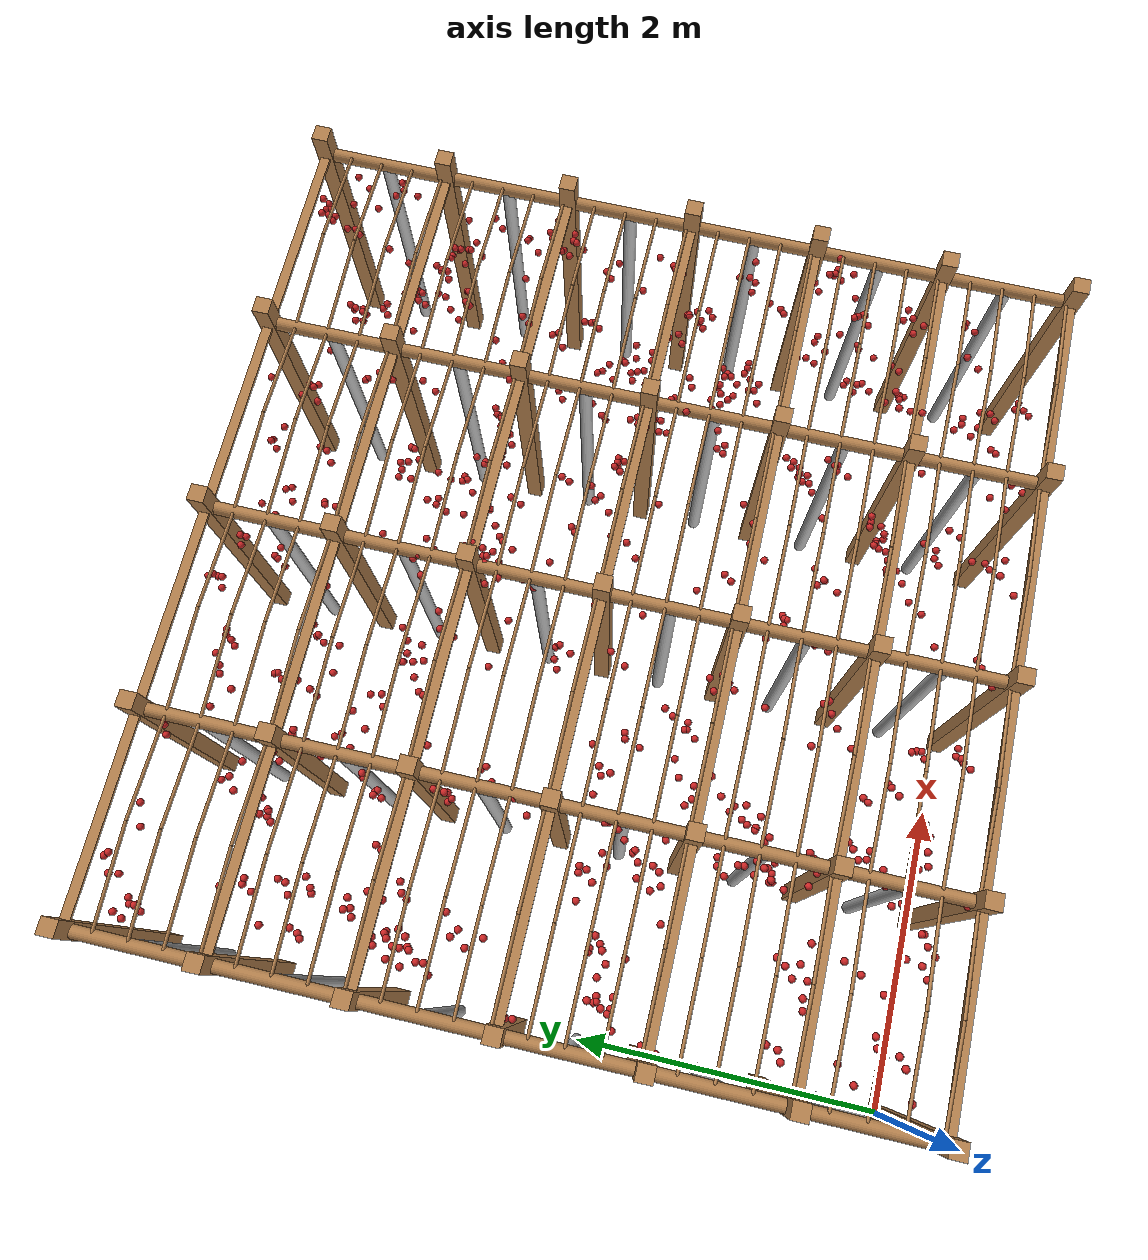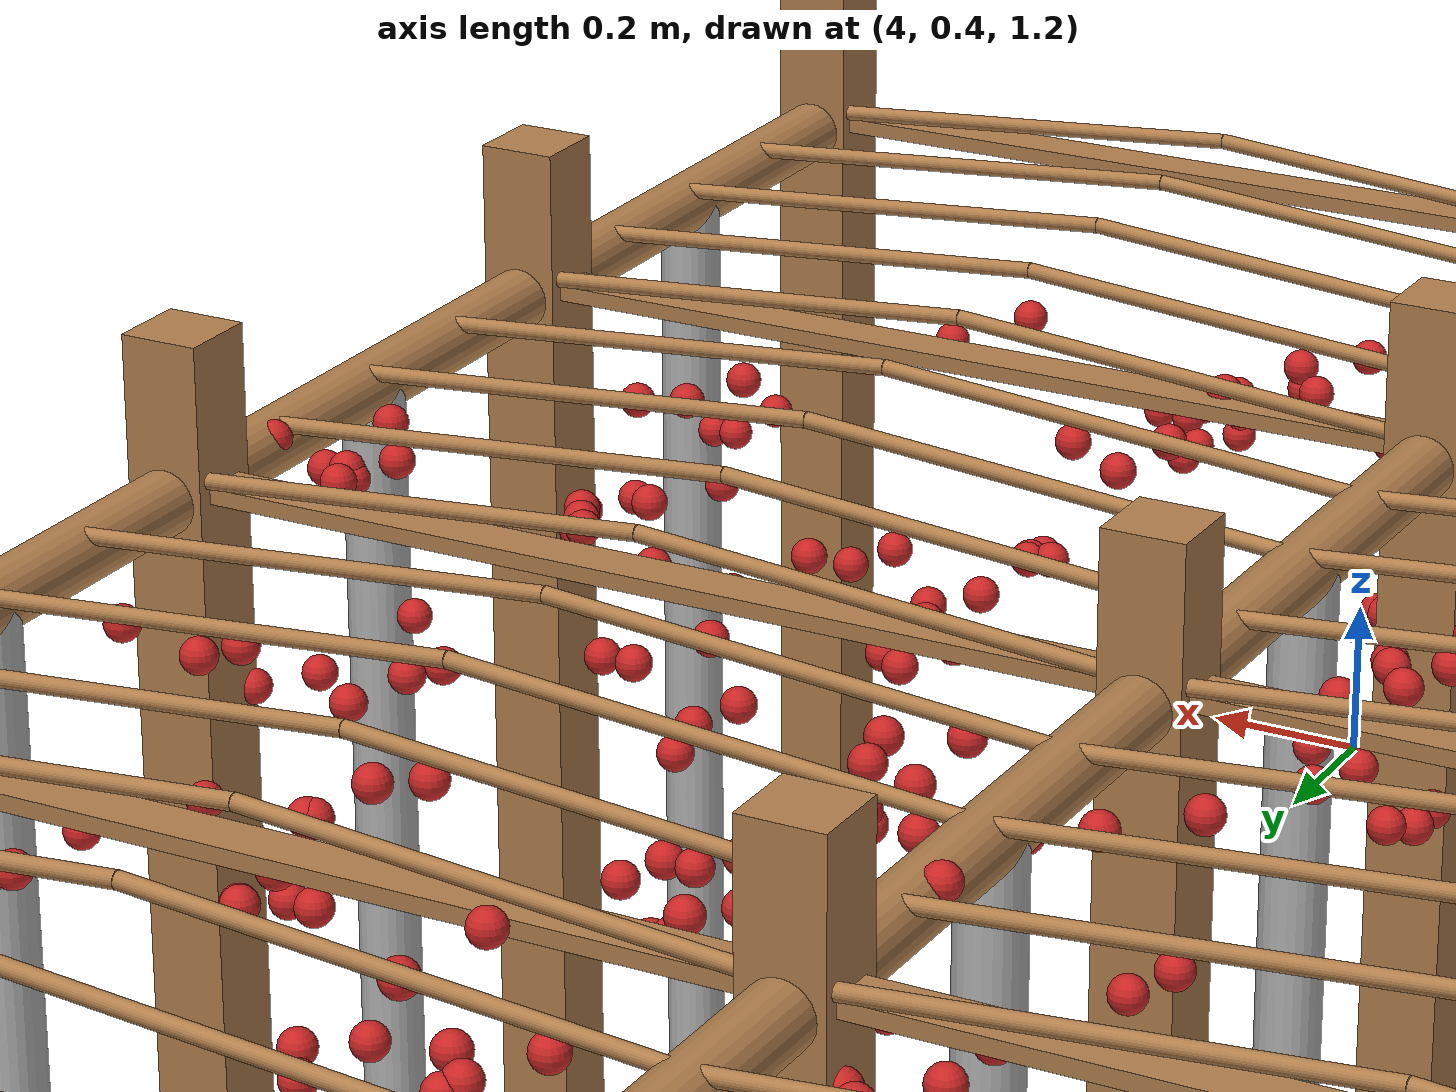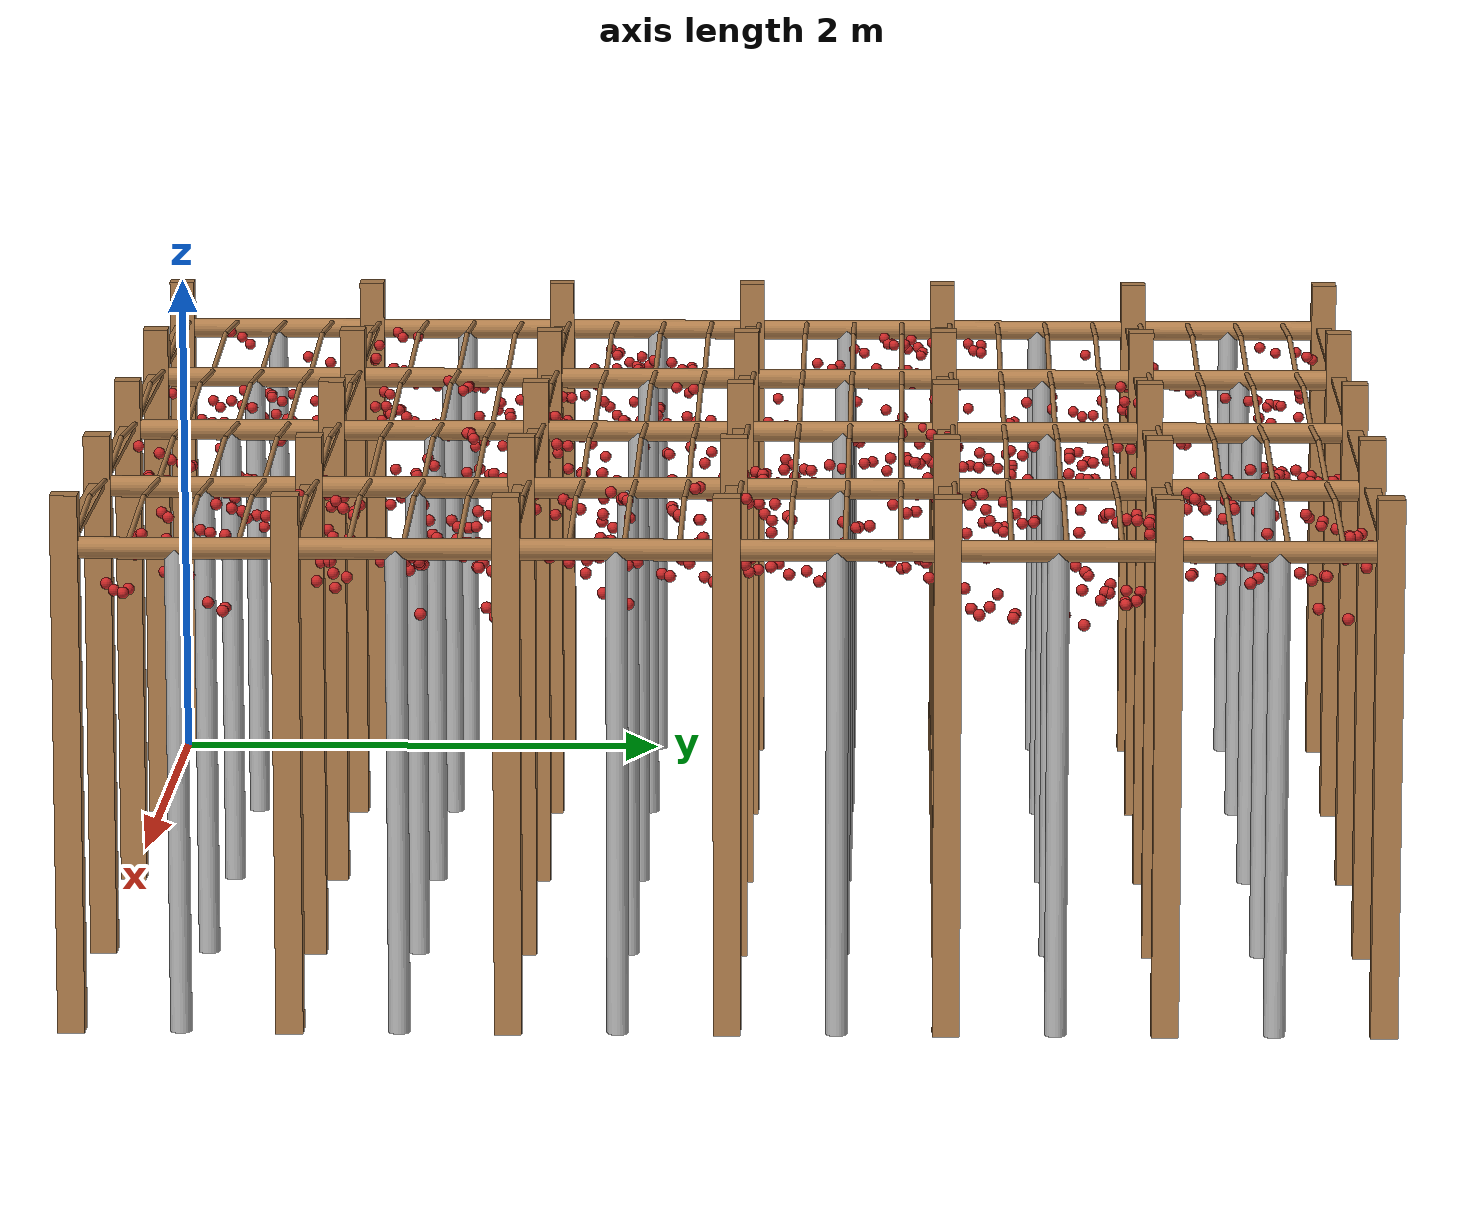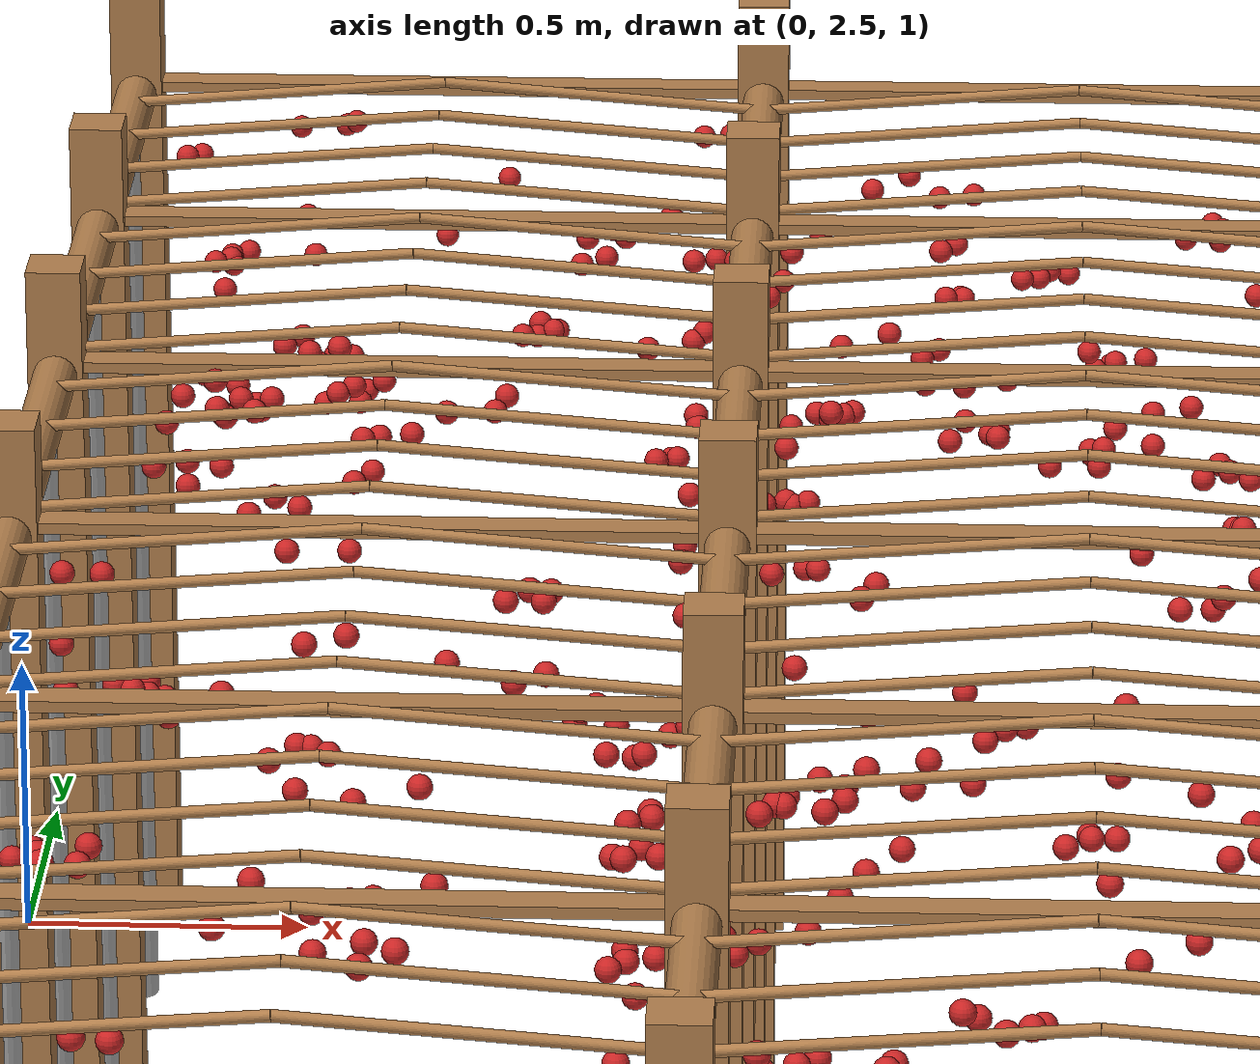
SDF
<?xml version='1.0'?>

<sdf version='1.4'>
  <model name="pergola">

		<include>
			<name>post_0</name>
			<pose>0.0 0.0 0 0 0 0</pose>
			<uri>model://post</uri>
		</include>

		<include>
			<name>post_1</name>
			<pose>0.0 0.8 0 0 0 0</pose>
			<uri>model://post</uri>
		</include>

		<include>
			<name>post_2</name>
			<pose>0.0 1.6 0 0 0 0</pose>
			<uri>model://post</uri>
		</include>

		<include>
			<name>post_3</name>
			<pose>0.0 2.4000000000000004 0 0 0 0</pose>
			<uri>model://post</uri>
		</include>

		<include>
			<name>post_4</name>
			<pose>0.0 3.2 0 0 0 0</pose>
			<uri>model://post</uri>
		</include>

		<include>
			<name>post_5</name>
			<pose>0.0 4.0 0 0 0 0</pose>
			<uri>model://post</uri>
		</include>

		<include>
			<name>post_6</name>
			<pose>0.0 4.800000000000001 0 0 0 0</pose>
			<uri>model://post</uri>
		</include>

		<include>
			<name>post_7</name>
			<pose>1.25 0.0 0 0 0 0</pose>
			<uri>model://post</uri>
		</include>

		<include>
			<name>post_8</name>
			<pose>1.25 0.8 0 0 0 0</pose>
			<uri>model://post</uri>
		</include>

		<include>
			<name>post_9</name>
			<pose>1.25 1.6 0 0 0 0</pose>
			<uri>model://post</uri>
		</include>

		<include>
			<name>post_10</name>
			<pose>1.25 2.4000000000000004 0 0 0 0</pose>
			<uri>model://post</uri>
		</include>

		<include>
			<name>post_11</name>
			<pose>1.25 3.2 0 0 0 0</pose>
			<uri>model://post</uri>
		</include>

		<include>
			<name>post_12</name>
			<pose>1.25 4.0 0 0 0 0</pose>
			<uri>model://post</uri>
		</include>

		<include>
			<name>post_13</name>
			<pose>1.25 4.800000000000001 0 0 0 0</pose>
			<uri>model://post</uri>
		</include>

		<include>
			<name>post_14</name>
			<pose>2.5 0.0 0 0 0 0</pose>
			<uri>model://post</uri>
		</include>

		<include>
			<name>post_15</name>
			<pose>2.5 0.8 0 0 0 0</pose>
			<uri>model://post</uri>
		</include>

		<include>
			<name>post_16</name>
			<pose>2.5 1.6 0 0 0 0</pose>
			<uri>model://post</uri>
		</include>

		<include>
			<name>post_17</name>
			<pose>2.5 2.4000000000000004 0 0 0 0</pose>
			<uri>model://post</uri>
		</include>

		<include>
			<name>post_18</name>
			<pose>2.5 3.2 0 0 0 0</pose>
			<uri>model://post</uri>
		</include>

		<include>
			<name>post_19</name>
			<pose>2.5 4.0 0 0 0 0</pose>
			<uri>model://post</uri>
		</include>

		<include>
			<name>post_20</name>
			<pose>2.5 4.800000000000001 0 0 0 0</pose>
			<uri>model://post</uri>
		</include>

		<include>
			<name>post_21</name>
			<pose>3.75 0.0 0 0 0 0</pose>
			<uri>model://post</uri>
		</include>

		<include>
			<name>post_22</name>
			<pose>3.75 0.8 0 0 0 0</pose>
			<uri>model://post</uri>
		</include>

		<include>
			<name>post_23</name>
			<pose>3.75 1.6 0 0 0 0</pose>
			<uri>model://post</uri>
		</include>

		<include>
			<name>post_24</name>
			<pose>3.75 2.4000000000000004 0 0 0 0</pose>
			<uri>model://post</uri>
		</include>

		<include>
			<name>post_25</name>
			<pose>3.75 3.2 0 0 0 0</pose>
			<uri>model://post</uri>
		</include>

		<include>
			<name>post_26</name>
			<pose>3.75 4.0 0 0 0 0</pose>
			<uri>model://post</uri>
		</include>

		<include>
			<name>post_27</name>
			<pose>3.75 4.800000000000001 0 0 0 0</pose>
			<uri>model://post</uri>
		</include>

		<include>
			<name>post_28</name>
			<pose>5.0 0.0 0 0 0 0</pose>
			<uri>model://post</uri>
		</include>

		<include>
			<name>post_29</name>
			<pose>5.0 0.8 0 0 0 0</pose>
			<uri>model://post</uri>
		</include>

		<include>
			<name>post_30</name>
			<pose>5.0 1.6 0 0 0 0</pose>
			<uri>model://post</uri>
		</include>

		<include>
			<name>post_31</name>
			<pose>5.0 2.4000000000000004 0 0 0 0</pose>
			<uri>model://post</uri>
		</include>

		<include>
			<name>post_32</name>
			<pose>5.0 3.2 0 0 0 0</pose>
			<uri>model://post</uri>
		</include>

		<include>
			<name>post_33</name>
			<pose>5.0 4.0 0 0 0 0</pose>
			<uri>model://post</uri>
		</include>

		<include>
			<name>post_34</name>
			<pose>5.0 4.800000000000001 0 0 0 0</pose>
			<uri>model://post</uri>
		</include>

    <link name="beam_0">
      <pose>0.625 0.0 1.81 0 0 0</pose>
      <collision name="collision">
        <geometry><box><size>1.25 0.06 0.02</size></box></geometry>
      </collision>
      <visual name="visual">
        <geometry><box><size>1.25 0.06 0.02</size></box></geometry>
        <material><script><name>Gazebo/Wood</name></script></material>
      </visual>
    <inertial>
      <pose>0 0 0 0 0 0</pose>
      <mass>5</mass>
      <inertia>
        <ixx>0.0016666666666666668</ixx><ixy>0.0</ixy><ixz>0.0</ixz><iyy>0.6525416666666667</iyy><iyz>0.0</iyz><izz>0.6512083333333333</izz>
      </inertia>
    </inertial>
    </link>

    <link name="beam_1">
      <pose>0.625 0.8 1.81 0 0 0</pose>
      <collision name="collision">
        <geometry><box><size>1.25 0.06 0.02</size></box></geometry>
      </collision>
      <visual name="visual">
        <geometry><box><size>1.25 0.06 0.02</size></box></geometry>
        <material><script><name>Gazebo/Wood</name></script></material>
      </visual>
    <inertial>
      <pose>0 0 0 0 0 0</pose>
      <mass>5</mass>
      <inertia>
        <ixx>0.0016666666666666668</ixx><ixy>0.0</ixy><ixz>0.0</ixz><iyy>0.6525416666666667</iyy><iyz>0.0</iyz><izz>0.6512083333333333</izz>
      </inertia>
    </inertial>
    </link>

    <link name="beam_2">
      <pose>0.625 1.6 1.81 0 0 0</pose>
      <collision name="collision">
        <geometry><box><size>1.25 0.06 0.02</size></box></geometry>
      </collision>
      <visual name="visual">
        <geometry><box><size>1.25 0.06 0.02</size></box></geometry>
        <material><script><name>Gazebo/Wood</name></script></material>
      </visual>
    <inertial>
      <pose>0 0 0 0 0 0</pose>
      <mass>5</mass>
      <inertia>
        <ixx>0.0016666666666666668</ixx><ixy>0.0</ixy><ixz>0.0</ixz><iyy>0.6525416666666667</iyy><iyz>0.0</iyz><izz>0.6512083333333333</izz>
      </inertia>
    </inertial>
    </link>

    <link name="beam_3">
      <pose>0.625 2.4000000000000004 1.81 0 0 0</pose>
      <collision name="collision">
        <geometry><box><size>1.25 0.06 0.02</size></box></geometry>
      </collision>
      <visual name="visual">
        <geometry><box><size>1.25 0.06 0.02</size></box></geometry>
        <material><script><name>Gazebo/Wood</name></script></material>
      </visual>
    <inertial>
      <pose>0 0 0 0 0 0</pose>
      <mass>5</mass>
      <inertia>
        <ixx>0.0016666666666666668</ixx><ixy>0.0</ixy><ixz>0.0</ixz><iyy>0.6525416666666667</iyy><iyz>0.0</iyz><izz>0.6512083333333333</izz>
      </inertia>
    </inertial>
    </link>

    <link name="beam_4">
      <pose>0.625 3.2 1.81 0 0 0</pose>
      <collision name="collision">
        <geometry><box><size>1.25 0.06 0.02</size></box></geometry>
      </collision>
      <visual name="visual">
        <geometry><box><size>1.25 0.06 0.02</size></box></geometry>
        <material><script><name>Gazebo/Wood</name></script></material>
      </visual>
    <inertial>
      <pose>0 0 0 0 0 0</pose>
      <mass>5</mass>
      <inertia>
        <ixx>0.0016666666666666668</ixx><ixy>0.0</ixy><ixz>0.0</ixz><iyy>0.6525416666666667</iyy><iyz>0.0</iyz><izz>0.6512083333333333</izz>
      </inertia>
    </inertial>
    </link>

    <link name="beam_5">
      <pose>0.625 4.0 1.81 0 0 0</pose>
      <collision name="collision">
        <geometry><box><size>1.25 0.06 0.02</size></box></geometry>
      </collision>
      <visual name="visual">
        <geometry><box><size>1.25 0.06 0.02</size></box></geometry>
        <material><script><name>Gazebo/Wood</name></script></material>
      </visual>
    <inertial>
      <pose>0 0 0 0 0 0</pose>
      <mass>5</mass>
      <inertia>
        <ixx>0.0016666666666666668</ixx><ixy>0.0</ixy><ixz>0.0</ixz><iyy>0.6525416666666667</iyy><iyz>0.0</iyz><izz>0.6512083333333333</izz>
      </inertia>
    </inertial>
    </link>

    <link name="beam_6">
      <pose>0.625 4.800000000000001 1.81 0 0 0</pose>
      <collision name="collision">
        <geometry><box><size>1.25 0.06 0.02</size></box></geometry>
      </collision>
      <visual name="visual">
        <geometry><box><size>1.25 0.06 0.02</size></box></geometry>
        <material><script><name>Gazebo/Wood</name></script></material>
      </visual>
    <inertial>
      <pose>0 0 0 0 0 0</pose>
      <mass>5</mass>
      <inertia>
        <ixx>0.0016666666666666668</ixx><ixy>0.0</ixy><ixz>0.0</ixz><iyy>0.6525416666666667</iyy><iyz>0.0</iyz><izz>0.6512083333333333</izz>
      </inertia>
    </inertial>
    </link>

    <link name="beam_7">
      <pose>1.875 0.0 1.81 0 0 0</pose>
      <collision name="collision">
        <geometry><box><size>1.25 0.06 0.02</size></box></geometry>
      </collision>
      <visual name="visual">
        <geometry><box><size>1.25 0.06 0.02</size></box></geometry>
        <material><script><name>Gazebo/Wood</name></script></material>
      </visual>
    <inertial>
      <pose>0 0 0 0 0 0</pose>
      <mass>5</mass>
      <inertia>
        <ixx>0.0016666666666666668</ixx><ixy>0.0</ixy><ixz>0.0</ixz><iyy>0.6525416666666667</iyy><iyz>0.0</iyz><izz>0.6512083333333333</izz>
      </inertia>
    </inertial>
    </link>

    <link name="beam_8">
      <pose>1.875 0.8 1.81 0 0 0</pose>
      <collision name="collision">
        <geometry><box><size>1.25 0.06 0.02</size></box></geometry>
      </collision>
      <visual name="visual">
        <geometry><box><size>1.25 0.06 0.02</size></box></geometry>
        <material><script><name>Gazebo/Wood</name></script></material>
      </visual>
    <inertial>
      <pose>0 0 0 0 0 0</pose>
      <mass>5</mass>
      <inertia>
        <ixx>0.0016666666666666668</ixx><ixy>0.0</ixy><ixz>0.0</ixz><iyy>0.6525416666666667</iyy><iyz>0.0</iyz><izz>0.6512083333333333</izz>
      </inertia>
    </inertial>
    </link>

    <link name="beam_9">
      <pose>1.875 1.6 1.81 0 0 0</pose>
      <collision name="collision">
        <geometry><box><size>1.25 0.06 0.02</size></box></geometry>
      </collision>
      <visual name="visual">
        <geometry><box><size>1.25 0.06 0.02</size></box></geometry>
        <material><script><name>Gazebo/Wood</name></script></material>
      </visual>
    <inertial>
      <pose>0 0 0 0 0 0</pose>
      <mass>5</mass>
      <inertia>
        <ixx>0.0016666666666666668</ixx><ixy>0.0</ixy><ixz>0.0</ixz><iyy>0.6525416666666667</iyy><iyz>0.0</iyz><izz>0.6512083333333333</izz>
      </inertia>
    </inertial>
    </link>

    <link name="beam_10">
      <pose>1.875 2.4000000000000004 1.81 0 0 0</pose>
      <collision name="collision">
        <geometry><box><size>1.25 0.06 0.02</size></box></geometry>
      </collision>
      <visual name="visual">
        <geometry><box><size>1.25 0.06 0.02</size></box></geometry>
        <material><script><name>Gazebo/Wood</name></script></material>
      </visual>
    <inertial>
      <pose>0 0 0 0 0 0</pose>
      <mass>5</mass>
      <inertia>
        <ixx>0.0016666666666666668</ixx><ixy>0.0</ixy><ixz>0.0</ixz><iyy>0.6525416666666667</iyy><iyz>0.0</iyz><izz>0.6512083333333333</izz>
      </inertia>
    </inertial>
    </link>

    <link name="beam_11">
      <pose>1.875 3.2 1.81 0 0 0</pose>
      <collision name="collision">
        <geometry><box><size>1.25 0.06 0.02</size></box></geometry>
      </collision>
      <visual name="visual">
        <geometry><box><size>1.25 0.06 0.02</size></box></geometry>
        <material><script><name>Gazebo/Wood</name></script></material>
      </visual>
    <inertial>
      <pose>0 0 0 0 0 0</pose>
      <mass>5</mass>
      <inertia>
        <ixx>0.0016666666666666668</ixx><ixy>0.0</ixy><ixz>0.0</ixz><iyy>0.6525416666666667</iyy><iyz>0.0</iyz><izz>0.6512083333333333</izz>
      </inertia>
    </inertial>
    </link>

    <link name="beam_12">
      <pose>1.875 4.0 1.81 0 0 0</pose>
      <collision name="collision">
        <geometry><box><size>1.25 0.06 0.02</size></box></geometry>
      </collision>
      <visual name="visual">
        <geometry><box><size>1.25 0.06 0.02</size></box></geometry>
        <material><script><name>Gazebo/Wood</name></script></material>
      </visual>
    <inertial>
      <pose>0 0 0 0 0 0</pose>
      <mass>5</mass>
      <inertia>
        <ixx>0.0016666666666666668</ixx><ixy>0.0</ixy><ixz>0.0</ixz><iyy>0.6525416666666667</iyy><iyz>0.0</iyz><izz>0.6512083333333333</izz>
      </inertia>
    </inertial>
    </link>

    <link name="beam_13">
      <pose>1.875 4.800000000000001 1.81 0 0 0</pose>
      <collision name="collision">
        <geometry><box><size>1.25 0.06 0.02</size></box></geometry>
      </collision>
      <visual name="visual">
        <geometry><box><size>1.25 0.06 0.02</size></box></geometry>
        <material><script><name>Gazebo/Wood</name></script></material>
      </visual>
    <inertial>
      <pose>0 0 0 0 0 0</pose>
      <mass>5</mass>
      <inertia>
        <ixx>0.0016666666666666668</ixx><ixy>0.0</ixy><ixz>0.0</ixz><iyy>0.6525416666666667</iyy><iyz>0.0</iyz><izz>0.6512083333333333</izz>
      </inertia>
    </inertial>
    </link>

    <link name="beam_14">
      <pose>3.125 0.0 1.81 0 0 0</pose>
      <collision name="collision">
        <geometry><box><size>1.25 0.06 0.02</size></box></geometry>
      </collision>
      <visual name="visual">
        <geometry><box><size>1.25 0.06 0.02</size></box></geometry>
        <material><script><name>Gazebo/Wood</name></script></material>
      </visual>
    <inertial>
      <pose>0 0 0 0 0 0</pose>
      <mass>5</mass>
      <inertia>
        <ixx>0.0016666666666666668</ixx><ixy>0.0</ixy><ixz>0.0</ixz><iyy>0.6525416666666667</iyy><iyz>0.0</iyz><izz>0.6512083333333333</izz>
      </inertia>
    </inertial>
    </link>

    <link name="beam_15">
      <pose>3.125 0.8 1.81 0 0 0</pose>
      <collision name="collision">
        <geometry><box><size>1.25 0.06 0.02</size></box></geometry>
      </collision>
      <visual name="visual">
        <geometry><box><size>1.25 0.06 0.02</size></box></geometry>
        <material><script><name>Gazebo/Wood</name></script></material>
      </visual>
    <inertial>
      <pose>0 0 0 0 0 0</pose>
      <mass>5</mass>
      <inertia>
        <ixx>0.0016666666666666668</ixx><ixy>0.0</ixy><ixz>0.0</ixz><iyy>0.6525416666666667</iyy><iyz>0.0</iyz><izz>0.6512083333333333</izz>
      </inertia>
    </inertial>
    </link>

    <link name="beam_16">
      <pose>3.125 1.6 1.81 0 0 0</pose>
      <collision name="collision">
        <geometry><box><size>1.25 0.06 0.02</size></box></geometry>
      </collision>
      <visual name="visual">
        <geometry><box><size>1.25 0.06 0.02</size></box></geometry>
        <material><script><name>Gazebo/Wood</name></script></material>
      </visual>
    <inertial>
      <pose>0 0 0 0 0 0</pose>
      <mass>5</mass>
      <inertia>
        <ixx>0.0016666666666666668</ixx><ixy>0.0</ixy><ixz>0.0</ixz><iyy>0.6525416666666667</iyy><iyz>0.0</iyz><izz>0.6512083333333333</izz>
      </inertia>
    </inertial>
    </link>

    <link name="beam_17">
      <pose>3.125 2.4000000000000004 1.81 0 0 0</pose>
      <collision name="collision">
        <geometry><box><size>1.25 0.06 0.02</size></box></geometry>
      </collision>
      <visual name="visual">
        <geometry><box><size>1.25 0.06 0.02</size></box></geometry>
        <material><script><name>Gazebo/Wood</name></script></material>
      </visual>
    <inertial>
      <pose>0 0 0 0 0 0</pose>
      <mass>5</mass>
      <inertia>
        <ixx>0.0016666666666666668</ixx><ixy>0.0</ixy><ixz>0.0</ixz><iyy>0.6525416666666667</iyy><iyz>0.0</iyz><izz>0.6512083333333333</izz>
      </inertia>
    </inertial>
    </link>

    <link name="beam_18">
      <pose>3.125 3.2 1.81 0 0 0</pose>
      <collision name="collision">
        <geometry><box><size>1.25 0.06 0.02</size></box></geometry>
      </collision>
      <visual name="visual">
        <geometry><box><size>1.25 0.06 0.02</size></box></geometry>
        <material><script><name>Gazebo/Wood</name></script></material>
      </visual>
    <inertial>
      <pose>0 0 0 0 0 0</pose>
      <mass>5</mass>
      <inertia>
        <ixx>0.0016666666666666668</ixx><ixy>0.0</ixy><ixz>0.0</ixz><iyy>0.6525416666666667</iyy><iyz>0.0</iyz><izz>0.6512083333333333</izz>
      </inertia>
    </inertial>
    </link>

    <link name="beam_19">
      <pose>3.125 4.0 1.81 0 0 0</pose>
      <collision name="collision">
        <geometry><box><size>1.25 0.06 0.02</size></box></geometry>
      </collision>
      <visual name="visual">
        <geometry><box><size>1.25 0.06 0.02</size></box></geometry>
        <material><script><name>Gazebo/Wood</name></script></material>
      </visual>
    <inertial>
      <pose>0 0 0 0 0 0</pose>
      <mass>5</mass>
      <inertia>
        <ixx>0.0016666666666666668</ixx><ixy>0.0</ixy><ixz>0.0</ixz><iyy>0.6525416666666667</iyy><iyz>0.0</iyz><izz>0.6512083333333333</izz>
      </inertia>
    </inertial>
    </link>

    <link name="beam_20">
      <pose>3.125 4.800000000000001 1.81 0 0 0</pose>
      <collision name="collision">
        <geometry><box><size>1.25 0.06 0.02</size></box></geometry>
      </collision>
      <visual name="visual">
        <geometry><box><size>1.25 0.06 0.02</size></box></geometry>
        <material><script><name>Gazebo/Wood</name></script></material>
      </visual>
    <inertial>
      <pose>0 0 0 0 0 0</pose>
      <mass>5</mass>
      <inertia>
        <ixx>0.0016666666666666668</ixx><ixy>0.0</ixy><ixz>0.0</ixz><iyy>0.6525416666666667</iyy><iyz>0.0</iyz><izz>0.6512083333333333</izz>
      </inertia>
    </inertial>
    </link>

    <link name="beam_21">
      <pose>4.375 0.0 1.81 0 0 0</pose>
      <collision name="collision">
        <geometry><box><size>1.25 0.06 0.02</size></box></geometry>
      </collision>
      <visual name="visual">
        <geometry><box><size>1.25 0.06 0.02</size></box></geometry>
        <material><script><name>Gazebo/Wood</name></script></material>
      </visual>
    <inertial>
      <pose>0 0 0 0 0 0</pose>
      <mass>5</mass>
      <inertia>
        <ixx>0.0016666666666666668</ixx><ixy>0.0</ixy><ixz>0.0</ixz><iyy>0.6525416666666667</iyy><iyz>0.0</iyz><izz>0.6512083333333333</izz>
      </inertia>
    </inertial>
    </link>

    <link name="beam_22">
      <pose>4.375 0.8 1.81 0 0 0</pose>
      <collision name="collision">
        <geometry><box><size>1.25 0.06 0.02</size></box></geometry>
      </collision>
      <visual name="visual">
        <geometry><box><size>1.25 0.06 0.02</size></box></geometry>
        <material><script><name>Gazebo/Wood</name></script></material>
      </visual>
    <inertial>
      <pose>0 0 0 0 0 0</pose>
      <mass>5</mass>
      <inertia>
        <ixx>0.0016666666666666668</ixx><ixy>0.0</ixy><ixz>0.0</ixz><iyy>0.6525416666666667</iyy><iyz>0.0</iyz><izz>0.6512083333333333</izz>
      </inertia>
    </inertial>
    </link>

    <link name="beam_23">
      <pose>4.375 1.6 1.81 0 0 0</pose>
      <collision name="collision">
        <geometry><box><size>1.25 0.06 0.02</size></box></geometry>
      </collision>
      <visual name="visual">
        <geometry><box><size>1.25 0.06 0.02</size></box></geometry>
        <material><script><name>Gazebo/Wood</name></script></material>
      </visual>
    <inertial>
      <pose>0 0 0 0 0 0</pose>
      <mass>5</mass>
      <inertia>
        <ixx>0.0016666666666666668</ixx><ixy>0.0</ixy><ixz>0.0</ixz><iyy>0.6525416666666667</iyy><iyz>0.0</iyz><izz>0.6512083333333333</izz>
      </inertia>
    </inertial>
    </link>

    <link name="beam_24">
      <pose>4.375 2.4000000000000004 1.81 0 0 0</pose>
      <collision name="collision">
        <geometry><box><size>1.25 0.06 0.02</size></box></geometry>
      </collision>
      <visual name="visual">
        <geometry><box><size>1.25 0.06 0.02</size></box></geometry>
        <material><script><name>Gazebo/Wood</name></script></material>
      </visual>
    <inertial>
      <pose>0 0 0 0 0 0</pose>
      <mass>5</mass>
      <inertia>
        <ixx>0.0016666666666666668</ixx><ixy>0.0</ixy><ixz>0.0</ixz><iyy>0.6525416666666667</iyy><iyz>0.0</iyz><izz>0.6512083333333333</izz>
      </inertia>
    </inertial>
    </link>

    <link name="beam_25">
      <pose>4.375 3.2 1.81 0 0 0</pose>
      <collision name="collision">
        <geometry><box><size>1.25 0.06 0.02</size></box></geometry>
      </collision>
      <visual name="visual">
        <geometry><box><size>1.25 0.06 0.02</size></box></geometry>
        <material><script><name>Gazebo/Wood</name></script></material>
      </visual>
    <inertial>
      <pose>0 0 0 0 0 0</pose>
      <mass>5</mass>
      <inertia>
        <ixx>0.0016666666666666668</ixx><ixy>0.0</ixy><ixz>0.0</ixz><iyy>0.6525416666666667</iyy><iyz>0.0</iyz><izz>0.6512083333333333</izz>
      </inertia>
    </inertial>
    </link>

    <link name="beam_26">
      <pose>4.375 4.0 1.81 0 0 0</pose>
      <collision name="collision">
        <geometry><box><size>1.25 0.06 0.02</size></box></geometry>
      </collision>
      <visual name="visual">
        <geometry><box><size>1.25 0.06 0.02</size></box></geometry>
        <material><script><name>Gazebo/Wood</name></script></material>
      </visual>
    <inertial>
      <pose>0 0 0 0 0 0</pose>
      <mass>5</mass>
      <inertia>
        <ixx>0.0016666666666666668</ixx><ixy>0.0</ixy><ixz>0.0</ixz><iyy>0.6525416666666667</iyy><iyz>0.0</iyz><izz>0.6512083333333333</izz>
      </inertia>
    </inertial>
    </link>

    <link name="beam_27">
      <pose>4.375 4.800000000000001 1.81 0 0 0</pose>
      <collision name="collision">
        <geometry><box><size>1.25 0.06 0.02</size></box></geometry>
      </collision>
      <visual name="visual">
        <geometry><box><size>1.25 0.06 0.02</size></box></geometry>
        <material><script><name>Gazebo/Wood</name></script></material>
      </visual>
    <inertial>
      <pose>0 0 0 0 0 0</pose>
      <mass>5</mass>
      <inertia>
        <ixx>0.0016666666666666668</ixx><ixy>0.0</ixy><ixz>0.0</ixz><iyy>0.6525416666666667</iyy><iyz>0.0</iyz><izz>0.6512083333333333</izz>
      </inertia>
    </inertial>
    </link>

		<include>
			<name>tree_0</name>
			<pose>0.0 0.4 0 0 0 0</pose>
			<uri>model://tree_trunk</uri>
		</include>

		<include>
			<name>tree_1</name>
			<pose>0.0 1.2000000000000002 0 0 0 0</pose>
			<uri>model://tree_trunk</uri>
		</include>

		<include>
			<name>tree_2</name>
			<pose>0.0 2.0 0 0 0 0</pose>
			<uri>model://tree_trunk</uri>
		</include>

		<include>
			<name>tree_3</name>
			<pose>0.0 2.8000000000000003 0 0 0 0</pose>
			<uri>model://tree_trunk</uri>
		</include>

		<include>
			<name>tree_4</name>
			<pose>0.0 3.6 0 0 0 0</pose>
			<uri>model://tree_trunk</uri>
		</include>

		<include>
			<name>tree_5</name>
			<pose>0.0 4.4 0 0 0 0</pose>
			<uri>model://tree_trunk</uri>
		</include>

		<include>
			<name>tree_6</name>
			<pose>1.25 0.4 0 0 0 0</pose>
			<uri>model://tree_trunk</uri>
		</include>

		<include>
			<name>tree_7</name>
			<pose>1.25 1.2000000000000002 0 0 0 0</pose>
			<uri>model://tree_trunk</uri>
		</include>

		<include>
			<name>tree_8</name>
			<pose>1.25 2.0 0 0 0 0</pose>
			<uri>model://tree_trunk</uri>
		</include>

		<include>
			<name>tree_9</name>
			<pose>1.25 2.8000000000000003 0 0 0 0</pose>
			<uri>model://tree_trunk</uri>
		</include>

		<include>
			<name>tree_10</name>
			<pose>1.25 3.6 0 0 0 0</pose>
			<uri>model://tree_trunk</uri>
		</include>

		<include>
			<name>tree_11</name>
			<pose>1.25 4.4 0 0 0 0</pose>
			<uri>model://tree_trunk</uri>
		</include>

		<include>
			<name>tree_12</name>
			<pose>2.5 0.4 0 0 0 0</pose>
			<uri>model://tree_trunk</uri>
		</include>

		<include>
			<name>tree_13</name>
			<pose>2.5 1.2000000000000002 0 0 0 0</pose>
			<uri>model://tree_trunk</uri>
		</include>

		<include>
			<name>tree_14</name>
			<pose>2.5 2.0 0 0 0 0</pose>
			<uri>model://tree_trunk</uri>
		</include>

		<include>
			<name>tree_15</name>
			<pose>2.5 2.8000000000000003 0 0 0 0</pose>
			<uri>model://tree_trunk</uri>
		</include>

		<include>
			<name>tree_16</name>
			<pose>2.5 3.6 0 0 0 0</pose>
			<uri>model://tree_trunk</uri>
		</include>

		<include>
			<name>tree_17</name>
			<pose>2.5 4.4 0 0 0 0</pose>
			<uri>model://tree_trunk</uri>
		</include>

		<include>
			<name>tree_18</name>
			<pose>3.75 0.4 0 0 0 0</pose>
			<uri>model://tree_trunk</uri>
		</include>

		<include>
			<name>tree_19</name>
			<pose>3.75 1.2000000000000002 0 0 0 0</pose>
			<uri>model://tree_trunk</uri>
		</include>

		<include>
			<name>tree_20</name>
			<pose>3.75 2.0 0 0 0 0</pose>
			<uri>model://tree_trunk</uri>
		</include>

		<include>
			<name>tree_21</name>
			<pose>3.75 2.8000000000000003 0 0 0 0</pose>
			<uri>model://tree_trunk</uri>
		</include>

		<include>
			<name>tree_22</name>
			<pose>3.75 3.6 0 0 0 0</pose>
			<uri>model://tree_trunk</uri>
		</include>

		<include>
			<name>tree_23</name>
			<pose>3.75 4.4 0 0 0 0</pose>
			<uri>model://tree_trunk</uri>
		</include>

		<include>
			<name>tree_24</name>
			<pose>5.0 0.4 0 0 0 0</pose>
			<uri>model://tree_trunk</uri>
		</include>

		<include>
			<name>tree_25</name>
			<pose>5.0 1.2000000000000002 0 0 0 0</pose>
			<uri>model://tree_trunk</uri>
		</include>

		<include>
			<name>tree_26</name>
			<pose>5.0 2.0 0 0 0 0</pose>
			<uri>model://tree_trunk</uri>
		</include>

		<include>
			<name>tree_27</name>
			<pose>5.0 2.8000000000000003 0 0 0 0</pose>
			<uri>model://tree_trunk</uri>
		</include>

		<include>
			<name>tree_28</name>
			<pose>5.0 3.6 0 0 0 0</pose>
			<uri>model://tree_trunk</uri>
		</include>

		<include>
			<name>tree_29</name>
			<pose>5.0 4.4 0 0 0 0</pose>
			<uri>model://tree_trunk</uri>
		</include>

    <link name="baseBranch_0">
      <pose>0.0 0.4 1.8 1.5707963267948966 0 0</pose>
      <collision name="collision">
        <geometry><cylinder><radius>0.04</radius> <length>0.74</length></cylinder></geometry>
      </collision>
      <visual name="visual">
        <geometry><cylinder><radius>0.04</radius> <length>0.74</length></cylinder></geometry>
        <material><script><name>Gazebo/WoodFloor</name></script></material>
      </visual>
    <inertial>
      <pose>0 0 0 0 0 0</pose>
      <mass>10</mass>
      <inertia>
        <ixx>0.4603333333333333</ixx><ixy>0.0</ixy><ixz>0.0</ixz><iyy>0.4603333333333333</iyy><iyz>0.0</iyz><izz>0.008</izz>
      </inertia>
    </inertial>
    </link>

    <link name="baseBranch_1">
      <pose>0.0 1.2000000000000002 1.8 1.5707963267948966 0 0</pose>
      <collision name="collision">
        <geometry><cylinder><radius>0.04</radius> <length>0.74</length></cylinder></geometry>
      </collision>
      <visual name="visual">
        <geometry><cylinder><radius>0.04</radius> <length>0.74</length></cylinder></geometry>
        <material><script><name>Gazebo/WoodFloor</name></script></material>
      </visual>
    <inertial>
      <pose>0 0 0 0 0 0</pose>
      <mass>10</mass>
      <inertia>
        <ixx>0.4603333333333333</ixx><ixy>0.0</ixy><ixz>0.0</ixz><iyy>0.4603333333333333</iyy><iyz>0.0</iyz><izz>0.008</izz>
      </inertia>
    </inertial>
    </link>

    <link name="baseBranch_2">
      <pose>0.0 2.0 1.8 1.5707963267948966 0 0</pose>
      <collision name="collision">
        <geometry><cylinder><radius>0.04</radius> <length>0.74</length></cylinder></geometry>
      </collision>
      <visual name="visual">
        <geometry><cylinder><radius>0.04</radius> <length>0.74</length></cylinder></geometry>
        <material><script><name>Gazebo/WoodFloor</name></script></material>
      </visual>
    <inertial>
      <pose>0 0 0 0 0 0</pose>
      <mass>10</mass>
      <inertia>
        <ixx>0.4603333333333333</ixx><ixy>0.0</ixy><ixz>0.0</ixz><iyy>0.4603333333333333</iyy><iyz>0.0</iyz><izz>0.008</izz>
      </inertia>
    </inertial>
    </link>

    <link name="baseBranch_3">
      <pose>0.0 2.8000000000000003 1.8 1.5707963267948966 0 0</pose>
      <collision name="collision">
        <geometry><cylinder><radius>0.04</radius> <length>0.74</length></cylinder></geometry>
      </collision>
      <visual name="visual">
        <geometry><cylinder><radius>0.04</radius> <length>0.74</length></cylinder></geometry>
        <material><script><name>Gazebo/WoodFloor</name></script></material>
      </visual>
    <inertial>
      <pose>0 0 0 0 0 0</pose>
      <mass>10</mass>
      <inertia>
        <ixx>0.4603333333333333</ixx><ixy>0.0</ixy><ixz>0.0</ixz><iyy>0.4603333333333333</iyy><iyz>0.0</iyz><izz>0.008</izz>
      </inertia>
    </inertial>
    </link>

    <link name="baseBranch_4">
      <pose>0.0 3.6 1.8 1.5707963267948966 0 0</pose>
      <collision name="collision">
        <geometry><cylinder><radius>0.04</radius> <length>0.74</length></cylinder></geometry>
      </collision>
      <visual name="visual">
        <geometry><cylinder><radius>0.04</radius> <length>0.74</length></cylinder></geometry>
        <material><script><name>Gazebo/WoodFloor</name></script></material>
      </visual>
    <inertial>
      <pose>0 0 0 0 0 0</pose>
      <mass>10</mass>
      <inertia>
        <ixx>0.4603333333333333</ixx><ixy>0.0</ixy><ixz>0.0</ixz><iyy>0.4603333333333333</iyy><iyz>0.0</iyz><izz>0.008</izz>
      </inertia>
    </inertial>
    </link>

    <link name="baseBranch_5">
      <pose>0.0 4.4 1.8 1.5707963267948966 0 0</pose>
      <collision name="collision">
        <geometry><cylinder><radius>0.04</radius> <length>0.74</length></cylinder></geometry>
      </collision>
      <visual name="visual">
        <geometry><cylinder><radius>0.04</radius> <length>0.74</length></cylinder></geometry>
        <material><script><name>Gazebo/WoodFloor</name></script></material>
      </visual>
    <inertial>
      <pose>0 0 0 0 0 0</pose>
      <mass>10</mass>
      <inertia>
        <ixx>0.4603333333333333</ixx><ixy>0.0</ixy><ixz>0.0</ixz><iyy>0.4603333333333333</iyy><iyz>0.0</iyz><izz>0.008</izz>
      </inertia>
    </inertial>
    </link>

    <link name="baseBranch_6">
      <pose>1.25 0.4 1.8 1.5707963267948966 0 0</pose>
      <collision name="collision">
        <geometry><cylinder><radius>0.04</radius> <length>0.74</length></cylinder></geometry>
      </collision>
      <visual name="visual">
        <geometry><cylinder><radius>0.04</radius> <length>0.74</length></cylinder></geometry>
        <material><script><name>Gazebo/WoodFloor</name></script></material>
      </visual>
    <inertial>
      <pose>0 0 0 0 0 0</pose>
      <mass>10</mass>
      <inertia>
        <ixx>0.4603333333333333</ixx><ixy>0.0</ixy><ixz>0.0</ixz><iyy>0.4603333333333333</iyy><iyz>0.0</iyz><izz>0.008</izz>
      </inertia>
    </inertial>
    </link>

    <link name="baseBranch_7">
      <pose>1.25 1.2000000000000002 1.8 1.5707963267948966 0 0</pose>
      <collision name="collision">
        <geometry><cylinder><radius>0.04</radius> <length>0.74</length></cylinder></geometry>
      </collision>
      <visual name="visual">
        <geometry><cylinder><radius>0.04</radius> <length>0.74</length></cylinder></geometry>
        <material><script><name>Gazebo/WoodFloor</name></script></material>
      </visual>
    <inertial>
      <pose>0 0 0 0 0 0</pose>
      <mass>10</mass>
      <inertia>
        <ixx>0.4603333333333333</ixx><ixy>0.0</ixy><ixz>0.0</ixz><iyy>0.4603333333333333</iyy><iyz>0.0</iyz><izz>0.008</izz>
      </inertia>
    </inertial>
    </link>

    <link name="baseBranch_8">
      <pose>1.25 2.0 1.8 1.5707963267948966 0 0</pose>
      <collision name="collision">
        <geometry><cylinder><radius>0.04</radius> <length>0.74</length></cylinder></geometry>
      </collision>
      <visual name="visual">
        <geometry><cylinder><radius>0.04</radius> <length>0.74</length></cylinder></geometry>
        <material><script><name>Gazebo/WoodFloor</name></script></material>
      </visual>
    <inertial>
      <pose>0 0 0 0 0 0</pose>
      <mass>10</mass>
      <inertia>
        <ixx>0.4603333333333333</ixx><ixy>0.0</ixy><ixz>0.0</ixz><iyy>0.4603333333333333</iyy><iyz>0.0</iyz><izz>0.008</izz>
      </inertia>
    </inertial>
    </link>

    <link name="baseBranch_9">
      <pose>1.25 2.8000000000000003 1.8 1.5707963267948966 0 0</pose>
      <collision name="collision">
        <geometry><cylinder><radius>0.04</radius> <length>0.74</length></cylinder></geometry>
      </collision>
      <visual name="visual">
        <geometry><cylinder><radius>0.04</radius> <length>0.74</length></cylinder></geometry>
        <material><script><name>Gazebo/WoodFloor</name></script></material>
      </visual>
    <inertial>
      <pose>0 0 0 0 0 0</pose>
      <mass>10</mass>
      <inertia>
        <ixx>0.4603333333333333</ixx><ixy>0.0</ixy><ixz>0.0</ixz><iyy>0.4603333333333333</iyy><iyz>0.0</iyz><izz>0.008</izz>
      </inertia>
    </inertial>
    </link>

    <link name="baseBranch_10">
      <pose>1.25 3.6 1.8 1.5707963267948966 0 0</pose>
      <collision name="collision">
        <geometry><cylinder><radius>0.04</radius> <length>0.74</length></cylinder></geometry>
      </collision>
      <visual name="visual">
        <geometry><cylinder><radius>0.04</radius> <length>0.74</length></cylinder></geometry>
        <material><script><name>Gazebo/WoodFloor</name></script></material>
      </visual>
    <inertial>
      <pose>0 0 0 0 0 0</pose>
      <mass>10</mass>
      <inertia>
        <ixx>0.4603333333333333</ixx><ixy>0.0</ixy><ixz>0.0</ixz><iyy>0.4603333333333333</iyy><iyz>0.0</iyz><izz>0.008</izz>
      </inertia>
    </inertial>
    </link>

    <link name="baseBranch_11">
      <pose>1.25 4.4 1.8 1.5707963267948966 0 0</pose>
      <collision name="collision">
        <geometry><cylinder><radius>0.04</radius> <length>0.74</length></cylinder></geometry>
      </collision>
      <visual name="visual">
        <geometry><cylinder><radius>0.04</radius> <length>0.74</length></cylinder></geometry>
        <material><script><name>Gazebo/WoodFloor</name></script></material>
      </visual>
    <inertial>
      <pose>0 0 0 0 0 0</pose>
      <mass>10</mass>
      <inertia>
        <ixx>0.4603333333333333</ixx><ixy>0.0</ixy><ixz>0.0</ixz><iyy>0.4603333333333333</iyy><iyz>0.0</iyz><izz>0.008</izz>
      </inertia>
    </inertial>
    </link>

    <link name="baseBranch_12">
      <pose>2.5 0.4 1.8 1.5707963267948966 0 0</pose>
      <collision name="collision">
        <geometry><cylinder><radius>0.04</radius> <length>0.74</length></cylinder></geometry>
      </collision>
      <visual name="visual">
        <geometry><cylinder><radius>0.04</radius> <length>0.74</length></cylinder></geometry>
        <material><script><name>Gazebo/WoodFloor</name></script></material>
      </visual>
    <inertial>
      <pose>0 0 0 0 0 0</pose>
      <mass>10</mass>
      <inertia>
        <ixx>0.4603333333333333</ixx><ixy>0.0</ixy><ixz>0.0</ixz><iyy>0.4603333333333333</iyy><iyz>0.0</iyz><izz>0.008</izz>
      </inertia>
    </inertial>
    </link>

    <link name="baseBranch_13">
      <pose>2.5 1.2000000000000002 1.8 1.5707963267948966 0 0</pose>
      <collision name="collision">
        <geometry><cylinder><radius>0.04</radius> <length>0.74</length></cylinder></geometry>
      </collision>
      <visual name="visual">
        <geometry><cylinder><radius>0.04</radius> <length>0.74</length></cylinder></geometry>
        <material><script><name>Gazebo/WoodFloor</name></script></material>
      </visual>
    <inertial>
      <pose>0 0 0 0 0 0</pose>
      <mass>10</mass>
      <inertia>
        <ixx>0.4603333333333333</ixx><ixy>0.0</ixy><ixz>0.0</ixz><iyy>0.4603333333333333</iyy><iyz>0.0</iyz><izz>0.008</izz>
      </inertia>
    </inertial>
    </link>

    <link name="baseBranch_14">
      <pose>2.5 2.0 1.8 1.5707963267948966 0 0</pose>
      <collision name="collision">
        <geometry><cylinder><radius>0.04</radius> <length>0.74</length></cylinder></geometry>
      </collision>
      <visual name="visual">
        <geometry><cylinder><radius>0.04</radius> <length>0.74</length></cylinder></geometry>
        <material><script><name>Gazebo/WoodFloor</name></script></material>
      </visual>
    <inertial>
      <pose>0 0 0 0 0 0</pose>
      <mass>10</mass>
      <inertia>
        <ixx>0.4603333333333333</ixx><ixy>0.0</ixy><ixz>0.0</ixz><iyy>0.4603333333333333</iyy><iyz>0.0</iyz><izz>0.008</izz>
      </inertia>
    </inertial>
    </link>

    <link name="baseBranch_15">
      <pose>2.5 2.8000000000000003 1.8 1.5707963267948966 0 0</pose>
      <collision name="collision">
        <geometry><cylinder><radius>0.04</radius> <length>0.74</length></cylinder></geometry>
      </collision>
      <visual name="visual">
        <geometry><cylinder><radius>0.04</radius> <length>0.74</length></cylinder></geometry>
        <material><script><name>Gazebo/WoodFloor</name></script></material>
      </visual>
    <inertial>
      <pose>0 0 0 0 0 0</pose>
      <mass>10</mass>
      <inertia>
        <ixx>0.4603333333333333</ixx><ixy>0.0</ixy><ixz>0.0</ixz><iyy>0.4603333333333333</iyy><iyz>0.0</iyz><izz>0.008</izz>
      </inertia>
    </inertial>
    </link>

    <link name="baseBranch_16">
      <pose>2.5 3.6 1.8 1.5707963267948966 0 0</pose>
      <collision name="collision">
        <geometry><cylinder><radius>0.04</radius> <length>0.74</length></cylinder></geometry>
      </collision>
      <visual name="visual">
        <geometry><cylinder><radius>0.04</radius> <length>0.74</length></cylinder></geometry>
        <material><script><name>Gazebo/WoodFloor</name></script></material>
      </visual>
    <inertial>
      <pose>0 0 0 0 0 0</pose>
      <mass>10</mass>
      <inertia>
        <ixx>0.4603333333333333</ixx><ixy>0.0</ixy><ixz>0.0</ixz><iyy>0.4603333333333333</iyy><iyz>0.0</iyz><izz>0.008</izz>
      </inertia>
    </inertial>
    </link>

    <link name="baseBranch_17">
      <pose>2.5 4.4 1.8 1.5707963267948966 0 0</pose>
      <collision name="collision">
        <geometry><cylinder><radius>0.04</radius> <length>0.74</length></cylinder></geometry>
      </collision>
      <visual name="visual">
        <geometry><cylinder><radius>0.04</radius> <length>0.74</length></cylinder></geometry>
        <material><script><name>Gazebo/WoodFloor</name></script></material>
      </visual>
    <inertial>
      <pose>0 0 0 0 0 0</pose>
      <mass>10</mass>
      <inertia>
        <ixx>0.4603333333333333</ixx><ixy>0.0</ixy><ixz>0.0</ixz><iyy>0.4603333333333333</iyy><iyz>0.0</iyz><izz>0.008</izz>
      </inertia>
    </inertial>
    </link>

    <link name="baseBranch_18">
      <pose>3.75 0.4 1.8 1.5707963267948966 0 0</pose>
      <collision name="collision">
        <geometry><cylinder><radius>0.04</radius> <length>0.74</length></cylinder></geometry>
      </collision>
      <visual name="visual">
        <geometry><cylinder><radius>0.04</radius> <length>0.74</length></cylinder></geometry>
        <material><script><name>Gazebo/WoodFloor</name></script></material>
      </visual>
    <inertial>
      <pose>0 0 0 0 0 0</pose>
      <mass>10</mass>
      <inertia>
        <ixx>0.4603333333333333</ixx><ixy>0.0</ixy><ixz>0.0</ixz><iyy>0.4603333333333333</iyy><iyz>0.0</iyz><izz>0.008</izz>
      </inertia>
    </inertial>
    </link>

    <link name="baseBranch_19">
      <pose>3.75 1.2000000000000002 1.8 1.5707963267948966 0 0</pose>
      <collision name="collision">
        <geometry><cylinder><radius>0.04</radius> <length>0.74</length></cylinder></geometry>
      </collision>
      <visual name="visual">
        <geometry><cylinder><radius>0.04</radius> <length>0.74</length></cylinder></geometry>
        <material><script><name>Gazebo/WoodFloor</name></script></material>
      </visual>
    <inertial>
      <pose>0 0 0 0 0 0</pose>
      <mass>10</mass>
      <inertia>
        <ixx>0.4603333333333333</ixx><ixy>0.0</ixy><ixz>0.0</ixz><iyy>0.4603333333333333</iyy><iyz>0.0</iyz><izz>0.008</izz>
      </inertia>
    </inertial>
    </link>

    <link name="baseBranch_20">
      <pose>3.75 2.0 1.8 1.5707963267948966 0 0</pose>
      <collision name="collision">
        <geometry><cylinder><radius>0.04</radius> <length>0.74</length></cylinder></geometry>
      </collision>
      <visual name="visual">
        <geometry><cylinder><radius>0.04</radius> <length>0.74</length></cylinder></geometry>
        <material><script><name>Gazebo/WoodFloor</name></script></material>
      </visual>
    <inertial>
      <pose>0 0 0 0 0 0</pose>
      <mass>10</mass>
      <inertia>
        <ixx>0.4603333333333333</ixx><ixy>0.0</ixy><ixz>0.0</ixz><iyy>0.4603333333333333</iyy><iyz>0.0</iyz><izz>0.008</izz>
      </inertia>
    </inertial>
    </link>

    <link name="baseBranch_21">
      <pose>3.75 2.8000000000000003 1.8 1.5707963267948966 0 0</pose>
      <collision name="collision">
        <geometry><cylinder><radius>0.04</radius> <length>0.74</length></cylinder></geometry>
      </collision>
      <visual name="visual">
        <geometry><cylinder><radius>0.04</radius> <length>0.74</length></cylinder></geometry>
        <material><script><name>Gazebo/WoodFloor</name></script></material>
      </visual>
    <inertial>
      <pose>0 0 0 0 0 0</pose>
      <mass>10</mass>
      <inertia>
        <ixx>0.4603333333333333</ixx><ixy>0.0</ixy><ixz>0.0</ixz><iyy>0.4603333333333333</iyy><iyz>0.0</iyz><izz>0.008</izz>
      </inertia>
    </inertial>
    </link>

    <link name="baseBranch_22">
      <pose>3.75 3.6 1.8 1.5707963267948966 0 0</pose>
      <collision name="collision">
        <geometry><cylinder><radius>0.04</radius> <length>0.74</length></cylinder></geometry>
      </collision>
      <visual name="visual">
        <geometry><cylinder><radius>0.04</radius> <length>0.74</length></cylinder></geometry>
        <material><script><name>Gazebo/WoodFloor</name></script></material>
      </visual>
    <inertial>
      <pose>0 0 0 0 0 0</pose>
      <mass>10</mass>
      <inertia>
        <ixx>0.4603333333333333</ixx><ixy>0.0</ixy><ixz>0.0</ixz><iyy>0.4603333333333333</iyy><iyz>0.0</iyz><izz>0.008</izz>
      </inertia>
    </inertial>
    </link>

    <link name="baseBranch_23">
      <pose>3.75 4.4 1.8 1.5707963267948966 0 0</pose>
      <collision name="collision">
        <geometry><cylinder><radius>0.04</radius> <length>0.74</length></cylinder></geometry>
      </collision>
      <visual name="visual">
        <geometry><cylinder><radius>0.04</radius> <length>0.74</length></cylinder></geometry>
        <material><script><name>Gazebo/WoodFloor</name></script></material>
      </visual>
    <inertial>
      <pose>0 0 0 0 0 0</pose>
      <mass>10</mass>
      <inertia>
        <ixx>0.4603333333333333</ixx><ixy>0.0</ixy><ixz>0.0</ixz><iyy>0.4603333333333333</iyy><iyz>0.0</iyz><izz>0.008</izz>
      </inertia>
    </inertial>
    </link>

    <link name="baseBranch_24">
      <pose>5.0 0.4 1.8 1.5707963267948966 0 0</pose>
      <collision name="collision">
        <geometry><cylinder><radius>0.04</radius> <length>0.74</length></cylinder></geometry>
      </collision>
      <visual name="visual">
        <geometry><cylinder><radius>0.04</radius> <length>0.74</length></cylinder></geometry>
        <material><script><name>Gazebo/WoodFloor</name></script></material>
      </visual>
    <inertial>
      <pose>0 0 0 0 0 0</pose>
      <mass>10</mass>
      <inertia>
        <ixx>0.4603333333333333</ixx><ixy>0.0</ixy><ixz>0.0</ixz><iyy>0.4603333333333333</iyy><iyz>0.0</iyz><izz>0.008</izz>
      </inertia>
    </inertial>
    </link>

    <link name="baseBranch_25">
      <pose>5.0 1.2000000000000002 1.8 1.5707963267948966 0 0</pose>
      <collision name="collision">
        <geometry><cylinder><radius>0.04</radius> <length>0.74</length></cylinder></geometry>
      </collision>
      <visual name="visual">
        <geometry><cylinder><radius>0.04</radius> <length>0.74</length></cylinder></geometry>
        <material><script><name>Gazebo/WoodFloor</name></script></material>
      </visual>
    <inertial>
      <pose>0 0 0 0 0 0</pose>
      <mass>10</mass>
      <inertia>
        <ixx>0.4603333333333333</ixx><ixy>0.0</ixy><ixz>0.0</ixz><iyy>0.4603333333333333</iyy><iyz>0.0</iyz><izz>0.008</izz>
      </inertia>
    </inertial>
    </link>

    <link name="baseBranch_26">
      <pose>5.0 2.0 1.8 1.5707963267948966 0 0</pose>
      <collision name="collision">
        <geometry><cylinder><radius>0.04</radius> <length>0.74</length></cylinder></geometry>
      </collision>
      <visual name="visual">
        <geometry><cylinder><radius>0.04</radius> <length>0.74</length></cylinder></geometry>
        <material><script><name>Gazebo/WoodFloor</name></script></material>
      </visual>
    <inertial>
      <pose>0 0 0 0 0 0</pose>
      <mass>10</mass>
      <inertia>
        <ixx>0.4603333333333333</ixx><ixy>0.0</ixy><ixz>0.0</ixz><iyy>0.4603333333333333</iyy><iyz>0.0</iyz><izz>0.008</izz>
      </inertia>
    </inertial>
    </link>

    <link name="baseBranch_27">
      <pose>5.0 2.8000000000000003 1.8 1.5707963267948966 0 0</pose>
      <collision name="collision">
        <geometry><cylinder><radius>0.04</radius> <length>0.74</length></cylinder></geometry>
      </collision>
      <visual name="visual">
        <geometry><cylinder><radius>0.04</radius> <length>0.74</length></cylinder></geometry>
        <material><script><name>Gazebo/WoodFloor</name></script></material>
      </visual>
    <inertial>
      <pose>0 0 0 0 0 0</pose>
      <mass>10</mass>
      <inertia>
        <ixx>0.4603333333333333</ixx><ixy>0.0</ixy><ixz>0.0</ixz><iyy>0.4603333333333333</iyy><iyz>0.0</iyz><izz>0.008</izz>
      </inertia>
    </inertial>
    </link>

    <link name="baseBranch_28">
      <pose>5.0 3.6 1.8 1.5707963267948966 0 0</pose>
      <collision name="collision">
        <geometry><cylinder><radius>0.04</radius> <length>0.74</length></cylinder></geometry>
      </collision>
      <visual name="visual">
        <geometry><cylinder><radius>0.04</radius> <length>0.74</length></cylinder></geometry>
        <material><script><name>Gazebo/WoodFloor</name></script></material>
      </visual>
    <inertial>
      <pose>0 0 0 0 0 0</pose>
      <mass>10</mass>
      <inertia>
        <ixx>0.4603333333333333</ixx><ixy>0.0</ixy><ixz>0.0</ixz><iyy>0.4603333333333333</iyy><iyz>0.0</iyz><izz>0.008</izz>
      </inertia>
    </inertial>
    </link>

    <link name="baseBranch_29">
      <pose>5.0 4.4 1.8 1.5707963267948966 0 0</pose>
      <collision name="collision">
        <geometry><cylinder><radius>0.04</radius> <length>0.74</length></cylinder></geometry>
      </collision>
      <visual name="visual">
        <geometry><cylinder><radius>0.04</radius> <length>0.74</length></cylinder></geometry>
        <material><script><name>Gazebo/WoodFloor</name></script></material>
      </visual>
    <inertial>
      <pose>0 0 0 0 0 0</pose>
      <mass>10</mass>
      <inertia>
        <ixx>0.4603333333333333</ixx><ixy>0.0</ixy><ixz>0.0</ixz><iyy>0.4603333333333333</iyy><iyz>0.0</iyz><izz>0.008</izz>
      </inertia>
    </inertial>
    </link>

    <link name="vine_0">
      <pose>0.3125 0.03 1.85 0 1.4909663410826592 0</pose>
      <collision name="collision">
        <geometry><cylinder><radius>0.01</radius> <length>0.6269968101992226</length></cylinder></geometry>
      </collision>
      <visual name="visual">
        <geometry><cylinder><radius>0.01</radius> <length>0.6269968101992226</length></cylinder></geometry>
        <material><script><name>Gazebo/WoodFloor</name></script></material>
      </visual>
    <inertial>
      <pose>0 0 0 0 0 0</pose>
      <mass>5</mass>
      <inertia>
        <ixx>0.1639270833333333</ixx><ixy>0.0</ixy><ixz>0.0</ixz><iyy>0.1639270833333333</iyy><iyz>0.0</iyz><izz>0.00025</izz>
      </inertia>
    </inertial>
    </link>

    <link name="vine_1">
      <pose>0.9375 0.03 1.85 0 -1.4909663410826592 0</pose>
      <collision name="collision">
        <geometry><cylinder><radius>0.01</radius> <length>0.6269968101992226</length></cylinder></geometry>
      </collision>
      <visual name="visual">
        <geometry><cylinder><radius>0.01</radius> <length>0.6269968101992226</length></cylinder></geometry>
        <material><script><name>Gazebo/WoodFloor</name></script></material>
      </visual>
    <inertial>
      <pose>0 0 0 0 0 0</pose>
      <mass>5</mass>
      <inertia>
        <ixx>0.1639270833333333</ixx><ixy>0.0</ixy><ixz>0.0</ixz><iyy>0.1639270833333333</iyy><iyz>0.0</iyz><izz>0.00025</izz>
      </inertia>
    </inertial>
    </link>

    <link name="vine_2">
      <pose>0.3125 0.23 1.85 0 1.4909663410826592 0</pose>
      <collision name="collision">
        <geometry><cylinder><radius>0.01</radius> <length>0.6269968101992226</length></cylinder></geometry>
      </collision>
      <visual name="visual">
        <geometry><cylinder><radius>0.01</radius> <length>0.6269968101992226</length></cylinder></geometry>
        <material><script><name>Gazebo/WoodFloor</name></script></material>
      </visual>
    <inertial>
      <pose>0 0 0 0 0 0</pose>
      <mass>5</mass>
      <inertia>
        <ixx>0.1639270833333333</ixx><ixy>0.0</ixy><ixz>0.0</ixz><iyy>0.1639270833333333</iyy><iyz>0.0</iyz><izz>0.00025</izz>
      </inertia>
    </inertial>
    </link>

    <link name="vine_3">
      <pose>0.9375 0.23 1.85 0 -1.4909663410826592 0</pose>
      <collision name="collision">
        <geometry><cylinder><radius>0.01</radius> <length>0.6269968101992226</length></cylinder></geometry>
      </collision>
      <visual name="visual">
        <geometry><cylinder><radius>0.01</radius> <length>0.6269968101992226</length></cylinder></geometry>
        <material><script><name>Gazebo/WoodFloor</name></script></material>
      </visual>
    <inertial>
      <pose>0 0 0 0 0 0</pose>
      <mass>5</mass>
      <inertia>
        <ixx>0.1639270833333333</ixx><ixy>0.0</ixy><ixz>0.0</ixz><iyy>0.1639270833333333</iyy><iyz>0.0</iyz><izz>0.00025</izz>
      </inertia>
    </inertial>
    </link>

    <link name="vine_4">
      <pose>0.3125 0.43000000000000005 1.85 0 1.4909663410826592 0</pose>
      <collision name="collision">
        <geometry><cylinder><radius>0.01</radius> <length>0.6269968101992226</length></cylinder></geometry>
      </collision>
      <visual name="visual">
        <geometry><cylinder><radius>0.01</radius> <length>0.6269968101992226</length></cylinder></geometry>
        <material><script><name>Gazebo/WoodFloor</name></script></material>
      </visual>
    <inertial>
      <pose>0 0 0 0 0 0</pose>
      <mass>5</mass>
      <inertia>
        <ixx>0.1639270833333333</ixx><ixy>0.0</ixy><ixz>0.0</ixz><iyy>0.1639270833333333</iyy><iyz>0.0</iyz><izz>0.00025</izz>
      </inertia>
    </inertial>
    </link>

    <link name="vine_5">
      <pose>0.9375 0.43000000000000005 1.85 0 -1.4909663410826592 0</pose>
      <collision name="collision">
        <geometry><cylinder><radius>0.01</radius> <length>0.6269968101992226</length></cylinder></geometry>
      </collision>
      <visual name="visual">
        <geometry><cylinder><radius>0.01</radius> <length>0.6269968101992226</length></cylinder></geometry>
        <material><script><name>Gazebo/WoodFloor</name></script></material>
      </visual>
    <inertial>
      <pose>0 0 0 0 0 0</pose>
      <mass>5</mass>
      <inertia>
        <ixx>0.1639270833333333</ixx><ixy>0.0</ixy><ixz>0.0</ixz><iyy>0.1639270833333333</iyy><iyz>0.0</iyz><izz>0.00025</izz>
      </inertia>
    </inertial>
    </link>

    <link name="vine_6">
      <pose>0.3125 0.6300000000000001 1.85 0 1.4909663410826592 0</pose>
      <collision name="collision">
        <geometry><cylinder><radius>0.01</radius> <length>0.6269968101992226</length></cylinder></geometry>
      </collision>
      <visual name="visual">
        <geometry><cylinder><radius>0.01</radius> <length>0.6269968101992226</length></cylinder></geometry>
        <material><script><name>Gazebo/WoodFloor</name></script></material>
      </visual>
    <inertial>
      <pose>0 0 0 0 0 0</pose>
      <mass>5</mass>
      <inertia>
        <ixx>0.1639270833333333</ixx><ixy>0.0</ixy><ixz>0.0</ixz><iyy>0.1639270833333333</iyy><iyz>0.0</iyz><izz>0.00025</izz>
      </inertia>
    </inertial>
    </link>

    <link name="vine_7">
      <pose>0.9375 0.6300000000000001 1.85 0 -1.4909663410826592 0</pose>
      <collision name="collision">
        <geometry><cylinder><radius>0.01</radius> <length>0.6269968101992226</length></cylinder></geometry>
      </collision>
      <visual name="visual">
        <geometry><cylinder><radius>0.01</radius> <length>0.6269968101992226</length></cylinder></geometry>
        <material><script><name>Gazebo/WoodFloor</name></script></material>
      </visual>
    <inertial>
      <pose>0 0 0 0 0 0</pose>
      <mass>5</mass>
      <inertia>
        <ixx>0.1639270833333333</ixx><ixy>0.0</ixy><ixz>0.0</ixz><iyy>0.1639270833333333</iyy><iyz>0.0</iyz><izz>0.00025</izz>
      </inertia>
    </inertial>
    </link>

    <link name="vine_8">
      <pose>0.3125 0.8300000000000001 1.85 0 1.4909663410826592 0</pose>
      <collision name="collision">
        <geometry><cylinder><radius>0.01</radius> <length>0.6269968101992226</length></cylinder></geometry>
      </collision>
      <visual name="visual">
        <geometry><cylinder><radius>0.01</radius> <length>0.6269968101992226</length></cylinder></geometry>
        <material><script><name>Gazebo/WoodFloor</name></script></material>
      </visual>
    <inertial>
      <pose>0 0 0 0 0 0</pose>
      <mass>5</mass>
      <inertia>
        <ixx>0.1639270833333333</ixx><ixy>0.0</ixy><ixz>0.0</ixz><iyy>0.1639270833333333</iyy><iyz>0.0</iyz><izz>0.00025</izz>
      </inertia>
    </inertial>
    </link>

    <link name="vine_9">
      <pose>0.9375 0.8300000000000001 1.85 0 -1.4909663410826592 0</pose>
      <collision name="collision">
        <geometry><cylinder><radius>0.01</radius> <length>0.6269968101992226</length></cylinder></geometry>
      </collision>
      <visual name="visual">
        <geometry><cylinder><radius>0.01</radius> <length>0.6269968101992226</length></cylinder></geometry>
        <material><script><name>Gazebo/WoodFloor</name></script></material>
      </visual>
    <inertial>
      <pose>0 0 0 0 0 0</pose>
      <mass>5</mass>
      <inertia>
        <ixx>0.1639270833333333</ixx><ixy>0.0</ixy><ixz>0.0</ixz><iyy>0.1639270833333333</iyy><iyz>0.0</iyz><izz>0.00025</izz>
      </inertia>
    </inertial>
    </link>

    <link name="vine_10">
      <pose>0.3125 1.03 1.85 0 1.4909663410826592 0</pose>
      <collision name="collision">
        <geometry><cylinder><radius>0.01</radius> <length>0.6269968101992226</length></cylinder></geometry>
      </collision>
      <visual name="visual">
        <geometry><cylinder><radius>0.01</radius> <length>0.6269968101992226</length></cylinder></geometry>
        <material><script><name>Gazebo/WoodFloor</name></script></material>
      </visual>
    <inertial>
      <pose>0 0 0 0 0 0</pose>
      <mass>5</mass>
      <inertia>
        <ixx>0.1639270833333333</ixx><ixy>0.0</ixy><ixz>0.0</ixz><iyy>0.1639270833333333</iyy><iyz>0.0</iyz><izz>0.00025</izz>
      </inertia>
    </inertial>
    </link>

    <link name="vine_11">
      <pose>0.9375 1.03 1.85 0 -1.4909663410826592 0</pose>
      <collision name="collision">
        <geometry><cylinder><radius>0.01</radius> <length>0.6269968101992226</length></cylinder></geometry>
      </collision>
      <visual name="visual">
        <geometry><cylinder><radius>0.01</radius> <length>0.6269968101992226</length></cylinder></geometry>
        <material><script><name>Gazebo/WoodFloor</name></script></material>
      </visual>
    <inertial>
      <pose>0 0 0 0 0 0</pose>
      <mass>5</mass>
      <inertia>
        <ixx>0.1639270833333333</ixx><ixy>0.0</ixy><ixz>0.0</ixz><iyy>0.1639270833333333</iyy><iyz>0.0</iyz><izz>0.00025</izz>
      </inertia>
    </inertial>
    </link>

    <link name="vine_12">
      <pose>0.3125 1.2300000000000002 1.85 0 1.4909663410826592 0</pose>
      <collision name="collision">
        <geometry><cylinder><radius>0.01</radius> <length>0.6269968101992226</length></cylinder></geometry>
      </collision>
      <visual name="visual">
        <geometry><cylinder><radius>0.01</radius> <length>0.6269968101992226</length></cylinder></geometry>
        <material><script><name>Gazebo/WoodFloor</name></script></material>
      </visual>
    <inertial>
      <pose>0 0 0 0 0 0</pose>
      <mass>5</mass>
      <inertia>
        <ixx>0.1639270833333333</ixx><ixy>0.0</ixy><ixz>0.0</ixz><iyy>0.1639270833333333</iyy><iyz>0.0</iyz><izz>0.00025</izz>
      </inertia>
    </inertial>
    </link>

    <link name="vine_13">
      <pose>0.9375 1.2300000000000002 1.85 0 -1.4909663410826592 0</pose>
      <collision name="collision">
        <geometry><cylinder><radius>0.01</radius> <length>0.6269968101992226</length></cylinder></geometry>
      </collision>
      <visual name="visual">
        <geometry><cylinder><radius>0.01</radius> <length>0.6269968101992226</length></cylinder></geometry>
        <material><script><name>Gazebo/WoodFloor</name></script></material>
      </visual>
    <inertial>
      <pose>0 0 0 0 0 0</pose>
      <mass>5</mass>
      <inertia>
        <ixx>0.1639270833333333</ixx><ixy>0.0</ixy><ixz>0.0</ixz><iyy>0.1639270833333333</iyy><iyz>0.0</iyz><izz>0.00025</izz>
      </inertia>
    </inertial>
    </link>

    <link name="vine_14">
      <pose>0.3125 1.4300000000000002 1.85 0 1.4909663410826592 0</pose>
      <collision name="collision">
        <geometry><cylinder><radius>0.01</radius> <length>0.6269968101992226</length></cylinder></geometry>
      </collision>
      <visual name="visual">
        <geometry><cylinder><radius>0.01</radius> <length>0.6269968101992226</length></cylinder></geometry>
        <material><script><name>Gazebo/WoodFloor</name></script></material>
      </visual>
    <inertial>
      <pose>0 0 0 0 0 0</pose>
      <mass>5</mass>
      <inertia>
        <ixx>0.1639270833333333</ixx><ixy>0.0</ixy><ixz>0.0</ixz><iyy>0.1639270833333333</iyy><iyz>0.0</iyz><izz>0.00025</izz>
      </inertia>
    </inertial>
    </link>

    <link name="vine_15">
      <pose>0.9375 1.4300000000000002 1.85 0 -1.4909663410826592 0</pose>
      <collision name="collision">
        <geometry><cylinder><radius>0.01</radius> <length>0.6269968101992226</length></cylinder></geometry>
      </collision>
      <visual name="visual">
        <geometry><cylinder><radius>0.01</radius> <length>0.6269968101992226</length></cylinder></geometry>
        <material><script><name>Gazebo/WoodFloor</name></script></material>
      </visual>
    <inertial>
      <pose>0 0 0 0 0 0</pose>
      <mass>5</mass>
      <inertia>
        <ixx>0.1639270833333333</ixx><ixy>0.0</ixy><ixz>0.0</ixz><iyy>0.1639270833333333</iyy><iyz>0.0</iyz><izz>0.00025</izz>
      </inertia>
    </inertial>
    </link>

    <link name="vine_16">
      <pose>0.3125 1.6300000000000001 1.85 0 1.4909663410826592 0</pose>
      <collision name="collision">
        <geometry><cylinder><radius>0.01</radius> <length>0.6269968101992226</length></cylinder></geometry>
      </collision>
      <visual name="visual">
        <geometry><cylinder><radius>0.01</radius> <length>0.6269968101992226</length></cylinder></geometry>
        <material><script><name>Gazebo/WoodFloor</name></script></material>
      </visual>
    <inertial>
      <pose>0 0 0 0 0 0</pose>
      <mass>5</mass>
      <inertia>
        <ixx>0.1639270833333333</ixx><ixy>0.0</ixy><ixz>0.0</ixz><iyy>0.1639270833333333</iyy><iyz>0.0</iyz><izz>0.00025</izz>
      </inertia>
    </inertial>
    </link>

    <link name="vine_17">
      <pose>0.9375 1.6300000000000001 1.85 0 -1.4909663410826592 0</pose>
      <collision name="collision">
        <geometry><cylinder><radius>0.01</radius> <length>0.6269968101992226</length></cylinder></geometry>
      </collision>
      <visual name="visual">
        <geometry><cylinder><radius>0.01</radius> <length>0.6269968101992226</length></cylinder></geometry>
        <material><script><name>Gazebo/WoodFloor</name></script></material>
      </visual>
    <inertial>
      <pose>0 0 0 0 0 0</pose>
      <mass>5</mass>
      <inertia>
        <ixx>0.1639270833333333</ixx><ixy>0.0</ixy><ixz>0.0</ixz><iyy>0.1639270833333333</iyy><iyz>0.0</iyz><izz>0.00025</izz>
      </inertia>
    </inertial>
    </link>

    <link name="vine_18">
      <pose>0.3125 1.83 1.85 0 1.4909663410826592 0</pose>
      <collision name="collision">
        <geometry><cylinder><radius>0.01</radius> <length>0.6269968101992226</length></cylinder></geometry>
      </collision>
      <visual name="visual">
        <geometry><cylinder><radius>0.01</radius> <length>0.6269968101992226</length></cylinder></geometry>
        <material><script><name>Gazebo/WoodFloor</name></script></material>
      </visual>
    <inertial>
      <pose>0 0 0 0 0 0</pose>
      <mass>5</mass>
      <inertia>
        <ixx>0.1639270833333333</ixx><ixy>0.0</ixy><ixz>0.0</ixz><iyy>0.1639270833333333</iyy><iyz>0.0</iyz><izz>0.00025</izz>
      </inertia>
    </inertial>
    </link>

    <link name="vine_19">
      <pose>0.9375 1.83 1.85 0 -1.4909663410826592 0</pose>
      <collision name="collision">
        <geometry><cylinder><radius>0.01</radius> <length>0.6269968101992226</length></cylinder></geometry>
      </collision>
      <visual name="visual">
        <geometry><cylinder><radius>0.01</radius> <length>0.6269968101992226</length></cylinder></geometry>
        <material><script><name>Gazebo/WoodFloor</name></script></material>
      </visual>
    <inertial>
      <pose>0 0 0 0 0 0</pose>
      <mass>5</mass>
      <inertia>
        <ixx>0.1639270833333333</ixx><ixy>0.0</ixy><ixz>0.0</ixz><iyy>0.1639270833333333</iyy><iyz>0.0</iyz><izz>0.00025</izz>
      </inertia>
    </inertial>
    </link>

    <link name="vine_20">
      <pose>0.3125 2.03 1.85 0 1.4909663410826592 0</pose>
      <collision name="collision">
        <geometry><cylinder><radius>0.01</radius> <length>0.6269968101992226</length></cylinder></geometry>
      </collision>
      <visual name="visual">
        <geometry><cylinder><radius>0.01</radius> <length>0.6269968101992226</length></cylinder></geometry>
        <material><script><name>Gazebo/WoodFloor</name></script></material>
      </visual>
    <inertial>
      <pose>0 0 0 0 0 0</pose>
      <mass>5</mass>
      <inertia>
        <ixx>0.1639270833333333</ixx><ixy>0.0</ixy><ixz>0.0</ixz><iyy>0.1639270833333333</iyy><iyz>0.0</iyz><izz>0.00025</izz>
      </inertia>
    </inertial>
    </link>

    <link name="vine_21">
      <pose>0.9375 2.03 1.85 0 -1.4909663410826592 0</pose>
      <collision name="collision">
        <geometry><cylinder><radius>0.01</radius> <length>0.6269968101992226</length></cylinder></geometry>
      </collision>
      <visual name="visual">
        <geometry><cylinder><radius>0.01</radius> <length>0.6269968101992226</length></cylinder></geometry>
        <material><script><name>Gazebo/WoodFloor</name></script></material>
      </visual>
    <inertial>
      <pose>0 0 0 0 0 0</pose>
      <mass>5</mass>
      <inertia>
        <ixx>0.1639270833333333</ixx><ixy>0.0</ixy><ixz>0.0</ixz><iyy>0.1639270833333333</iyy><iyz>0.0</iyz><izz>0.00025</izz>
      </inertia>
    </inertial>
    </link>

    <link name="vine_22">
      <pose>0.3125 2.23 1.85 0 1.4909663410826592 0</pose>
      <collision name="collision">
        <geometry><cylinder><radius>0.01</radius> <length>0.6269968101992226</length></cylinder></geometry>
      </collision>
      <visual name="visual">
        <geometry><cylinder><radius>0.01</radius> <length>0.6269968101992226</length></cylinder></geometry>
        <material><script><name>Gazebo/WoodFloor</name></script></material>
      </visual>
    <inertial>
      <pose>0 0 0 0 0 0</pose>
      <mass>5</mass>
      <inertia>
        <ixx>0.1639270833333333</ixx><ixy>0.0</ixy><ixz>0.0</ixz><iyy>0.1639270833333333</iyy><iyz>0.0</iyz><izz>0.00025</izz>
      </inertia>
    </inertial>
    </link>

    <link name="vine_23">
      <pose>0.9375 2.23 1.85 0 -1.4909663410826592 0</pose>
      <collision name="collision">
        <geometry><cylinder><radius>0.01</radius> <length>0.6269968101992226</length></cylinder></geometry>
      </collision>
      <visual name="visual">
        <geometry><cylinder><radius>0.01</radius> <length>0.6269968101992226</length></cylinder></geometry>
        <material><script><name>Gazebo/WoodFloor</name></script></material>
      </visual>
    <inertial>
      <pose>0 0 0 0 0 0</pose>
      <mass>5</mass>
      <inertia>
        <ixx>0.1639270833333333</ixx><ixy>0.0</ixy><ixz>0.0</ixz><iyy>0.1639270833333333</iyy><iyz>0.0</iyz><izz>0.00025</izz>
      </inertia>
    </inertial>
    </link>

    <link name="vine_24">
      <pose>0.3125 2.43 1.85 0 1.4909663410826592 0</pose>
      <collision name="collision">
        <geometry><cylinder><radius>0.01</radius> <length>0.6269968101992226</length></cylinder></geometry>
      </collision>
      <visual name="visual">
        <geometry><cylinder><radius>0.01</radius> <length>0.6269968101992226</length></cylinder></geometry>
        <material><script><name>Gazebo/WoodFloor</name></script></material>
      </visual>
    <inertial>
      <pose>0 0 0 0 0 0</pose>
      <mass>5</mass>
      <inertia>
        <ixx>0.1639270833333333</ixx><ixy>0.0</ixy><ixz>0.0</ixz><iyy>0.1639270833333333</iyy><iyz>0.0</iyz><izz>0.00025</izz>
      </inertia>
    </inertial>
    </link>

    <link name="vine_25">
      <pose>0.9375 2.43 1.85 0 -1.4909663410826592 0</pose>
      <collision name="collision">
        <geometry><cylinder><radius>0.01</radius> <length>0.6269968101992226</length></cylinder></geometry>
      </collision>
      <visual name="visual">
        <geometry><cylinder><radius>0.01</radius> <length>0.6269968101992226</length></cylinder></geometry>
        <material><script><name>Gazebo/WoodFloor</name></script></material>
      </visual>
    <inertial>
      <pose>0 0 0 0 0 0</pose>
      <mass>5</mass>
      <inertia>
        <ixx>0.1639270833333333</ixx><ixy>0.0</ixy><ixz>0.0</ixz><iyy>0.1639270833333333</iyy><iyz>0.0</iyz><izz>0.00025</izz>
      </inertia>
    </inertial>
    </link>

    <link name="vine_26">
      <pose>0.3125 2.63 1.85 0 1.4909663410826592 0</pose>
      <collision name="collision">
        <geometry><cylinder><radius>0.01</radius> <length>0.6269968101992226</length></cylinder></geometry>
      </collision>
      <visual name="visual">
        <geometry><cylinder><radius>0.01</radius> <length>0.6269968101992226</length></cylinder></geometry>
        <material><script><name>Gazebo/WoodFloor</name></script></material>
      </visual>
    <inertial>
      <pose>0 0 0 0 0 0</pose>
      <mass>5</mass>
      <inertia>
        <ixx>0.1639270833333333</ixx><ixy>0.0</ixy><ixz>0.0</ixz><iyy>0.1639270833333333</iyy><iyz>0.0</iyz><izz>0.00025</izz>
      </inertia>
    </inertial>
    </link>

    <link name="vine_27">
      <pose>0.9375 2.63 1.85 0 -1.4909663410826592 0</pose>
      <collision name="collision">
        <geometry><cylinder><radius>0.01</radius> <length>0.6269968101992226</length></cylinder></geometry>
      </collision>
      <visual name="visual">
        <geometry><cylinder><radius>0.01</radius> <length>0.6269968101992226</length></cylinder></geometry>
        <material><script><name>Gazebo/WoodFloor</name></script></material>
      </visual>
    <inertial>
      <pose>0 0 0 0 0 0</pose>
      <mass>5</mass>
      <inertia>
        <ixx>0.1639270833333333</ixx><ixy>0.0</ixy><ixz>0.0</ixz><iyy>0.1639270833333333</iyy><iyz>0.0</iyz><izz>0.00025</izz>
      </inertia>
    </inertial>
    </link>

    <link name="vine_28">
      <pose>0.3125 2.83 1.85 0 1.4909663410826592 0</pose>
      <collision name="collision">
        <geometry><cylinder><radius>0.01</radius> <length>0.6269968101992226</length></cylinder></geometry>
      </collision>
      <visual name="visual">
        <geometry><cylinder><radius>0.01</radius> <length>0.6269968101992226</length></cylinder></geometry>
        <material><script><name>Gazebo/WoodFloor</name></script></material>
      </visual>
    <inertial>
      <pose>0 0 0 0 0 0</pose>
      <mass>5</mass>
      <inertia>
        <ixx>0.1639270833333333</ixx><ixy>0.0</ixy><ixz>0.0</ixz><iyy>0.1639270833333333</iyy><iyz>0.0</iyz><izz>0.00025</izz>
      </inertia>
    </inertial>
    </link>

    <link name="vine_29">
      <pose>0.9375 2.83 1.85 0 -1.4909663410826592 0</pose>
      <collision name="collision">
        <geometry><cylinder><radius>0.01</radius> <length>0.6269968101992226</length></cylinder></geometry>
      </collision>
      <visual name="visual">
        <geometry><cylinder><radius>0.01</radius> <length>0.6269968101992226</length></cylinder></geometry>
        <material><script><name>Gazebo/WoodFloor</name></script></material>
      </visual>
    <inertial>
      <pose>0 0 0 0 0 0</pose>
      <mass>5</mass>
      <inertia>
        <ixx>0.1639270833333333</ixx><ixy>0.0</ixy><ixz>0.0</ixz><iyy>0.1639270833333333</iyy><iyz>0.0</iyz><izz>0.00025</izz>
      </inertia>
    </inertial>
    </link>

    <link name="vine_30">
      <pose>0.3125 3.03 1.85 0 1.4909663410826592 0</pose>
      <collision name="collision">
        <geometry><cylinder><radius>0.01</radius> <length>0.6269968101992226</length></cylinder></geometry>
      </collision>
      <visual name="visual">
        <geometry><cylinder><radius>0.01</radius> <length>0.6269968101992226</length></cylinder></geometry>
        <material><script><name>Gazebo/WoodFloor</name></script></material>
      </visual>
    <inertial>
      <pose>0 0 0 0 0 0</pose>
      <mass>5</mass>
      <inertia>
        <ixx>0.1639270833333333</ixx><ixy>0.0</ixy><ixz>0.0</ixz><iyy>0.1639270833333333</iyy><iyz>0.0</iyz><izz>0.00025</izz>
      </inertia>
    </inertial>
    </link>

    <link name="vine_31">
      <pose>0.9375 3.03 1.85 0 -1.4909663410826592 0</pose>
      <collision name="collision">
        <geometry><cylinder><radius>0.01</radius> <length>0.6269968101992226</length></cylinder></geometry>
      </collision>
      <visual name="visual">
        <geometry><cylinder><radius>0.01</radius> <length>0.6269968101992226</length></cylinder></geometry>
        <material><script><name>Gazebo/WoodFloor</name></script></material>
      </visual>
    <inertial>
      <pose>0 0 0 0 0 0</pose>
      <mass>5</mass>
      <inertia>
        <ixx>0.1639270833333333</ixx><ixy>0.0</ixy><ixz>0.0</ixz><iyy>0.1639270833333333</iyy><iyz>0.0</iyz><izz>0.00025</izz>
      </inertia>
    </inertial>
    </link>

    <link name="vine_32">
      <pose>0.3125 3.23 1.85 0 1.4909663410826592 0</pose>
      <collision name="collision">
        <geometry><cylinder><radius>0.01</radius> <length>0.6269968101992226</length></cylinder></geometry>
      </collision>
      <visual name="visual">
        <geometry><cylinder><radius>0.01</radius> <length>0.6269968101992226</length></cylinder></geometry>
        <material><script><name>Gazebo/WoodFloor</name></script></material>
      </visual>
    <inertial>
      <pose>0 0 0 0 0 0</pose>
      <mass>5</mass>
      <inertia>
        <ixx>0.1639270833333333</ixx><ixy>0.0</ixy><ixz>0.0</ixz><iyy>0.1639270833333333</iyy><iyz>0.0</iyz><izz>0.00025</izz>
      </inertia>
    </inertial>
    </link>

    <link name="vine_33">
      <pose>0.9375 3.23 1.85 0 -1.4909663410826592 0</pose>
      <collision name="collision">
        <geometry><cylinder><radius>0.01</radius> <length>0.6269968101992226</length></cylinder></geometry>
      </collision>
      <visual name="visual">
        <geometry><cylinder><radius>0.01</radius> <length>0.6269968101992226</length></cylinder></geometry>
        <material><script><name>Gazebo/WoodFloor</name></script></material>
      </visual>
    <inertial>
      <pose>0 0 0 0 0 0</pose>
      <mass>5</mass>
      <inertia>
        <ixx>0.1639270833333333</ixx><ixy>0.0</ixy><ixz>0.0</ixz><iyy>0.1639270833333333</iyy><iyz>0.0</iyz><izz>0.00025</izz>
      </inertia>
    </inertial>
    </link>

    <link name="vine_34">
      <pose>0.3125 3.43 1.85 0 1.4909663410826592 0</pose>
      <collision name="collision">
        <geometry><cylinder><radius>0.01</radius> <length>0.6269968101992226</length></cylinder></geometry>
      </collision>
      <visual name="visual">
        <geometry><cylinder><radius>0.01</radius> <length>0.6269968101992226</length></cylinder></geometry>
        <material><script><name>Gazebo/WoodFloor</name></script></material>
      </visual>
    <inertial>
      <pose>0 0 0 0 0 0</pose>
      <mass>5</mass>
      <inertia>
        <ixx>0.1639270833333333</ixx><ixy>0.0</ixy><ixz>0.0</ixz><iyy>0.1639270833333333</iyy><iyz>0.0</iyz><izz>0.00025</izz>
      </inertia>
    </inertial>
    </link>

    <link name="vine_35">
      <pose>0.9375 3.43 1.85 0 -1.4909663410826592 0</pose>
      <collision name="collision">
        <geometry><cylinder><radius>0.01</radius> <length>0.6269968101992226</length></cylinder></geometry>
      </collision>
      <visual name="visual">
        <geometry><cylinder><radius>0.01</radius> <length>0.6269968101992226</length></cylinder></geometry>
        <material><script><name>Gazebo/WoodFloor</name></script></material>
      </visual>
    <inertial>
      <pose>0 0 0 0 0 0</pose>
      <mass>5</mass>
      <inertia>
        <ixx>0.1639270833333333</ixx><ixy>0.0</ixy><ixz>0.0</ixz><iyy>0.1639270833333333</iyy><iyz>0.0</iyz><izz>0.00025</izz>
      </inertia>
    </inertial>
    </link>

    <link name="vine_36">
      <pose>0.3125 3.63 1.85 0 1.4909663410826592 0</pose>
      <collision name="collision">
        <geometry><cylinder><radius>0.01</radius> <length>0.6269968101992226</length></cylinder></geometry>
      </collision>
      <visual name="visual">
        <geometry><cylinder><radius>0.01</radius> <length>0.6269968101992226</length></cylinder></geometry>
        <material><script><name>Gazebo/WoodFloor</name></script></material>
      </visual>
    <inertial>
      <pose>0 0 0 0 0 0</pose>
      <mass>5</mass>
      <inertia>
        <ixx>0.1639270833333333</ixx><ixy>0.0</ixy><ixz>0.0</ixz><iyy>0.1639270833333333</iyy><iyz>0.0</iyz><izz>0.00025</izz>
      </inertia>
    </inertial>
    </link>

    <link name="vine_37">
      <pose>0.9375 3.63 1.85 0 -1.4909663410826592 0</pose>
      <collision name="collision">
        <geometry><cylinder><radius>0.01</radius> <length>0.6269968101992226</length></cylinder></geometry>
      </collision>
      <visual name="visual">
        <geometry><cylinder><radius>0.01</radius> <length>0.6269968101992226</length></cylinder></geometry>
        <material><script><name>Gazebo/WoodFloor</name></script></material>
      </visual>
    <inertial>
      <pose>0 0 0 0 0 0</pose>
      <mass>5</mass>
      <inertia>
        <ixx>0.1639270833333333</ixx><ixy>0.0</ixy><ixz>0.0</ixz><iyy>0.1639270833333333</iyy><iyz>0.0</iyz><izz>0.00025</izz>
      </inertia>
    </inertial>
    </link>

    <link name="vine_38">
      <pose>0.3125 3.83 1.85 0 1.4909663410826592 0</pose>
      <collision name="collision">
        <geometry><cylinder><radius>0.01</radius> <length>0.6269968101992226</length></cylinder></geometry>
      </collision>
      <visual name="visual">
        <geometry><cylinder><radius>0.01</radius> <length>0.6269968101992226</length></cylinder></geometry>
        <material><script><name>Gazebo/WoodFloor</name></script></material>
      </visual>
    <inertial>
      <pose>0 0 0 0 0 0</pose>
      <mass>5</mass>
      <inertia>
        <ixx>0.1639270833333333</ixx><ixy>0.0</ixy><ixz>0.0</ixz><iyy>0.1639270833333333</iyy><iyz>0.0</iyz><izz>0.00025</izz>
      </inertia>
    </inertial>
    </link>

    <link name="vine_39">
      <pose>0.9375 3.83 1.85 0 -1.4909663410826592 0</pose>
      <collision name="collision">
        <geometry><cylinder><radius>0.01</radius> <length>0.6269968101992226</length></cylinder></geometry>
      </collision>
      <visual name="visual">
        <geometry><cylinder><radius>0.01</radius> <length>0.6269968101992226</length></cylinder></geometry>
        <material><script><name>Gazebo/WoodFloor</name></script></material>
      </visual>
    <inertial>
      <pose>0 0 0 0 0 0</pose>
      <mass>5</mass>
      <inertia>
        <ixx>0.1639270833333333</ixx><ixy>0.0</ixy><ixz>0.0</ixz><iyy>0.1639270833333333</iyy><iyz>0.0</iyz><izz>0.00025</izz>
      </inertia>
    </inertial>
    </link>

    <link name="vine_40">
      <pose>0.3125 4.03 1.85 0 1.4909663410826592 0</pose>
      <collision name="collision">
        <geometry><cylinder><radius>0.01</radius> <length>0.6269968101992226</length></cylinder></geometry>
      </collision>
      <visual name="visual">
        <geometry><cylinder><radius>0.01</radius> <length>0.6269968101992226</length></cylinder></geometry>
        <material><script><name>Gazebo/WoodFloor</name></script></material>
      </visual>
    <inertial>
      <pose>0 0 0 0 0 0</pose>
      <mass>5</mass>
      <inertia>
        <ixx>0.1639270833333333</ixx><ixy>0.0</ixy><ixz>0.0</ixz><iyy>0.1639270833333333</iyy><iyz>0.0</iyz><izz>0.00025</izz>
      </inertia>
    </inertial>
    </link>

    <link name="vine_41">
      <pose>0.9375 4.03 1.85 0 -1.4909663410826592 0</pose>
      <collision name="collision">
        <geometry><cylinder><radius>0.01</radius> <length>0.6269968101992226</length></cylinder></geometry>
      </collision>
      <visual name="visual">
        <geometry><cylinder><radius>0.01</radius> <length>0.6269968101992226</length></cylinder></geometry>
        <material><script><name>Gazebo/WoodFloor</name></script></material>
      </visual>
    <inertial>
      <pose>0 0 0 0 0 0</pose>
      <mass>5</mass>
      <inertia>
        <ixx>0.1639270833333333</ixx><ixy>0.0</ixy><ixz>0.0</ixz><iyy>0.1639270833333333</iyy><iyz>0.0</iyz><izz>0.00025</izz>
      </inertia>
    </inertial>
    </link>

    <link name="vine_42">
      <pose>0.3125 4.23 1.85 0 1.4909663410826592 0</pose>
      <collision name="collision">
        <geometry><cylinder><radius>0.01</radius> <length>0.6269968101992226</length></cylinder></geometry>
      </collision>
      <visual name="visual">
        <geometry><cylinder><radius>0.01</radius> <length>0.6269968101992226</length></cylinder></geometry>
        <material><script><name>Gazebo/WoodFloor</name></script></material>
      </visual>
    <inertial>
      <pose>0 0 0 0 0 0</pose>
      <mass>5</mass>
      <inertia>
        <ixx>0.1639270833333333</ixx><ixy>0.0</ixy><ixz>0.0</ixz><iyy>0.1639270833333333</iyy><iyz>0.0</iyz><izz>0.00025</izz>
      </inertia>
    </inertial>
    </link>

    <link name="vine_43">
      <pose>0.9375 4.23 1.85 0 -1.4909663410826592 0</pose>
      <collision name="collision">
        <geometry><cylinder><radius>0.01</radius> <length>0.6269968101992226</length></cylinder></geometry>
      </collision>
      <visual name="visual">
        <geometry><cylinder><radius>0.01</radius> <length>0.6269968101992226</length></cylinder></geometry>
        <material><script><name>Gazebo/WoodFloor</name></script></material>
      </visual>
    <inertial>
      <pose>0 0 0 0 0 0</pose>
      <mass>5</mass>
      <inertia>
        <ixx>0.1639270833333333</ixx><ixy>0.0</ixy><ixz>0.0</ixz><iyy>0.1639270833333333</iyy><iyz>0.0</iyz><izz>0.00025</izz>
      </inertia>
    </inertial>
    </link>

    <link name="vine_44">
      <pose>0.3125 4.430000000000001 1.85 0 1.4909663410826592 0</pose>
      <collision name="collision">
        <geometry><cylinder><radius>0.01</radius> <length>0.6269968101992226</length></cylinder></geometry>
      </collision>
      <visual name="visual">
        <geometry><cylinder><radius>0.01</radius> <length>0.6269968101992226</length></cylinder></geometry>
        <material><script><name>Gazebo/WoodFloor</name></script></material>
      </visual>
    <inertial>
      <pose>0 0 0 0 0 0</pose>
      <mass>5</mass>
      <inertia>
        <ixx>0.1639270833333333</ixx><ixy>0.0</ixy><ixz>0.0</ixz><iyy>0.1639270833333333</iyy><iyz>0.0</iyz><izz>0.00025</izz>
      </inertia>
    </inertial>
    </link>

    <link name="vine_45">
      <pose>0.9375 4.430000000000001 1.85 0 -1.4909663410826592 0</pose>
      <collision name="collision">
        <geometry><cylinder><radius>0.01</radius> <length>0.6269968101992226</length></cylinder></geometry>
      </collision>
      <visual name="visual">
        <geometry><cylinder><radius>0.01</radius> <length>0.6269968101992226</length></cylinder></geometry>
        <material><script><name>Gazebo/WoodFloor</name></script></material>
      </visual>
    <inertial>
      <pose>0 0 0 0 0 0</pose>
      <mass>5</mass>
      <inertia>
        <ixx>0.1639270833333333</ixx><ixy>0.0</ixy><ixz>0.0</ixz><iyy>0.1639270833333333</iyy><iyz>0.0</iyz><izz>0.00025</izz>
      </inertia>
    </inertial>
    </link>

    <link name="vine_46">
      <pose>0.3125 4.630000000000001 1.85 0 1.4909663410826592 0</pose>
      <collision name="collision">
        <geometry><cylinder><radius>0.01</radius> <length>0.6269968101992226</length></cylinder></geometry>
      </collision>
      <visual name="visual">
        <geometry><cylinder><radius>0.01</radius> <length>0.6269968101992226</length></cylinder></geometry>
        <material><script><name>Gazebo/WoodFloor</name></script></material>
      </visual>
    <inertial>
      <pose>0 0 0 0 0 0</pose>
      <mass>5</mass>
      <inertia>
        <ixx>0.1639270833333333</ixx><ixy>0.0</ixy><ixz>0.0</ixz><iyy>0.1639270833333333</iyy><iyz>0.0</iyz><izz>0.00025</izz>
      </inertia>
    </inertial>
    </link>

    <link name="vine_47">
      <pose>0.9375 4.630000000000001 1.85 0 -1.4909663410826592 0</pose>
      <collision name="collision">
        <geometry><cylinder><radius>0.01</radius> <length>0.6269968101992226</length></cylinder></geometry>
      </collision>
      <visual name="visual">
        <geometry><cylinder><radius>0.01</radius> <length>0.6269968101992226</length></cylinder></geometry>
        <material><script><name>Gazebo/WoodFloor</name></script></material>
      </visual>
    <inertial>
      <pose>0 0 0 0 0 0</pose>
      <mass>5</mass>
      <inertia>
        <ixx>0.1639270833333333</ixx><ixy>0.0</ixy><ixz>0.0</ixz><iyy>0.1639270833333333</iyy><iyz>0.0</iyz><izz>0.00025</izz>
      </inertia>
    </inertial>
    </link>

    <link name="vine_48">
      <pose>1.5625 0.03 1.85 0 1.4909663410826592 0</pose>
      <collision name="collision">
        <geometry><cylinder><radius>0.01</radius> <length>0.6269968101992226</length></cylinder></geometry>
      </collision>
      <visual name="visual">
        <geometry><cylinder><radius>0.01</radius> <length>0.6269968101992226</length></cylinder></geometry>
        <material><script><name>Gazebo/WoodFloor</name></script></material>
      </visual>
    <inertial>
      <pose>0 0 0 0 0 0</pose>
      <mass>5</mass>
      <inertia>
        <ixx>0.1639270833333333</ixx><ixy>0.0</ixy><ixz>0.0</ixz><iyy>0.1639270833333333</iyy><iyz>0.0</iyz><izz>0.00025</izz>
      </inertia>
    </inertial>
    </link>

    <link name="vine_49">
      <pose>2.1875 0.03 1.85 0 -1.4909663410826592 0</pose>
      <collision name="collision">
        <geometry><cylinder><radius>0.01</radius> <length>0.6269968101992226</length></cylinder></geometry>
      </collision>
      <visual name="visual">
        <geometry><cylinder><radius>0.01</radius> <length>0.6269968101992226</length></cylinder></geometry>
        <material><script><name>Gazebo/WoodFloor</name></script></material>
      </visual>
    <inertial>
      <pose>0 0 0 0 0 0</pose>
      <mass>5</mass>
      <inertia>
        <ixx>0.1639270833333333</ixx><ixy>0.0</ixy><ixz>0.0</ixz><iyy>0.1639270833333333</iyy><iyz>0.0</iyz><izz>0.00025</izz>
      </inertia>
    </inertial>
    </link>

    <link name="vine_50">
      <pose>1.5625 0.23 1.85 0 1.4909663410826592 0</pose>
      <collision name="collision">
        <geometry><cylinder><radius>0.01</radius> <length>0.6269968101992226</length></cylinder></geometry>
      </collision>
      <visual name="visual">
        <geometry><cylinder><radius>0.01</radius> <length>0.6269968101992226</length></cylinder></geometry>
        <material><script><name>Gazebo/WoodFloor</name></script></material>
      </visual>
    <inertial>
      <pose>0 0 0 0 0 0</pose>
      <mass>5</mass>
      <inertia>
        <ixx>0.1639270833333333</ixx><ixy>0.0</ixy><ixz>0.0</ixz><iyy>0.1639270833333333</iyy><iyz>0.0</iyz><izz>0.00025</izz>
      </inertia>
    </inertial>
    </link>

    <link name="vine_51">
      <pose>2.1875 0.23 1.85 0 -1.4909663410826592 0</pose>
      <collision name="collision">
        <geometry><cylinder><radius>0.01</radius> <length>0.6269968101992226</length></cylinder></geometry>
      </collision>
      <visual name="visual">
        <geometry><cylinder><radius>0.01</radius> <length>0.6269968101992226</length></cylinder></geometry>
        <material><script><name>Gazebo/WoodFloor</name></script></material>
      </visual>
    <inertial>
      <pose>0 0 0 0 0 0</pose>
      <mass>5</mass>
      <inertia>
        <ixx>0.1639270833333333</ixx><ixy>0.0</ixy><ixz>0.0</ixz><iyy>0.1639270833333333</iyy><iyz>0.0</iyz><izz>0.00025</izz>
      </inertia>
    </inertial>
    </link>

    <link name="vine_52">
      <pose>1.5625 0.43000000000000005 1.85 0 1.4909663410826592 0</pose>
      <collision name="collision">
        <geometry><cylinder><radius>0.01</radius> <length>0.6269968101992226</length></cylinder></geometry>
      </collision>
      <visual name="visual">
        <geometry><cylinder><radius>0.01</radius> <length>0.6269968101992226</length></cylinder></geometry>
        <material><script><name>Gazebo/WoodFloor</name></script></material>
      </visual>
    <inertial>
      <pose>0 0 0 0 0 0</pose>
      <mass>5</mass>
      <inertia>
        <ixx>0.1639270833333333</ixx><ixy>0.0</ixy><ixz>0.0</ixz><iyy>0.1639270833333333</iyy><iyz>0.0</iyz><izz>0.00025</izz>
      </inertia>
    </inertial>
    </link>

    <link name="vine_53">
      <pose>2.1875 0.43000000000000005 1.85 0 -1.4909663410826592 0</pose>
      <collision name="collision">
        <geometry><cylinder><radius>0.01</radius> <length>0.6269968101992226</length></cylinder></geometry>
      </collision>
      <visual name="visual">
        <geometry><cylinder><radius>0.01</radius> <length>0.6269968101992226</length></cylinder></geometry>
        <material><script><name>Gazebo/WoodFloor</name></script></material>
      </visual>
    <inertial>
      <pose>0 0 0 0 0 0</pose>
      <mass>5</mass>
      <inertia>
        <ixx>0.1639270833333333</ixx><ixy>0.0</ixy><ixz>0.0</ixz><iyy>0.1639270833333333</iyy><iyz>0.0</iyz><izz>0.00025</izz>
      </inertia>
    </inertial>
    </link>

    <link name="vine_54">
      <pose>1.5625 0.6300000000000001 1.85 0 1.4909663410826592 0</pose>
      <collision name="collision">
        <geometry><cylinder><radius>0.01</radius> <length>0.6269968101992226</length></cylinder></geometry>
      </collision>
      <visual name="visual">
        <geometry><cylinder><radius>0.01</radius> <length>0.6269968101992226</length></cylinder></geometry>
        <material><script><name>Gazebo/WoodFloor</name></script></material>
      </visual>
    <inertial>
      <pose>0 0 0 0 0 0</pose>
      <mass>5</mass>
      <inertia>
        <ixx>0.1639270833333333</ixx><ixy>0.0</ixy><ixz>0.0</ixz><iyy>0.1639270833333333</iyy><iyz>0.0</iyz><izz>0.00025</izz>
      </inertia>
    </inertial>
    </link>

    <link name="vine_55">
      <pose>2.1875 0.6300000000000001 1.85 0 -1.4909663410826592 0</pose>
      <collision name="collision">
        <geometry><cylinder><radius>0.01</radius> <length>0.6269968101992226</length></cylinder></geometry>
      </collision>
      <visual name="visual">
        <geometry><cylinder><radius>0.01</radius> <length>0.6269968101992226</length></cylinder></geometry>
        <material><script><name>Gazebo/WoodFloor</name></script></material>
      </visual>
    <inertial>
      <pose>0 0 0 0 0 0</pose>
      <mass>5</mass>
      <inertia>
        <ixx>0.1639270833333333</ixx><ixy>0.0</ixy><ixz>0.0</ixz><iyy>0.1639270833333333</iyy><iyz>0.0</iyz><izz>0.00025</izz>
      </inertia>
    </inertial>
    </link>

    <link name="vine_56">
      <pose>1.5625 0.8300000000000001 1.85 0 1.4909663410826592 0</pose>
      <collision name="collision">
        <geometry><cylinder><radius>0.01</radius> <length>0.6269968101992226</length></cylinder></geometry>
      </collision>
      <visual name="visual">
        <geometry><cylinder><radius>0.01</radius> <length>0.6269968101992226</length></cylinder></geometry>
        <material><script><name>Gazebo/WoodFloor</name></script></material>
      </visual>
    <inertial>
      <pose>0 0 0 0 0 0</pose>
      <mass>5</mass>
      <inertia>
        <ixx>0.1639270833333333</ixx><ixy>0.0</ixy><ixz>0.0</ixz><iyy>0.1639270833333333</iyy><iyz>0.0</iyz><izz>0.00025</izz>
      </inertia>
    </inertial>
    </link>

    <link name="vine_57">
      <pose>2.1875 0.8300000000000001 1.85 0 -1.4909663410826592 0</pose>
      <collision name="collision">
        <geometry><cylinder><radius>0.01</radius> <length>0.6269968101992226</length></cylinder></geometry>
      </collision>
      <visual name="visual">
        <geometry><cylinder><radius>0.01</radius> <length>0.6269968101992226</length></cylinder></geometry>
        <material><script><name>Gazebo/WoodFloor</name></script></material>
      </visual>
    <inertial>
      <pose>0 0 0 0 0 0</pose>
      <mass>5</mass>
      <inertia>
        <ixx>0.1639270833333333</ixx><ixy>0.0</ixy><ixz>0.0</ixz><iyy>0.1639270833333333</iyy><iyz>0.0</iyz><izz>0.00025</izz>
      </inertia>
    </inertial>
    </link>

    <link name="vine_58">
      <pose>1.5625 1.03 1.85 0 1.4909663410826592 0</pose>
      <collision name="collision">
        <geometry><cylinder><radius>0.01</radius> <length>0.6269968101992226</length></cylinder></geometry>
      </collision>
      <visual name="visual">
        <geometry><cylinder><radius>0.01</radius> <length>0.6269968101992226</length></cylinder></geometry>
        <material><script><name>Gazebo/WoodFloor</name></script></material>
      </visual>
    <inertial>
      <pose>0 0 0 0 0 0</pose>
      <mass>5</mass>
      <inertia>
        <ixx>0.1639270833333333</ixx><ixy>0.0</ixy><ixz>0.0</ixz><iyy>0.1639270833333333</iyy><iyz>0.0</iyz><izz>0.00025</izz>
      </inertia>
    </inertial>
    </link>

    <link name="vine_59">
      <pose>2.1875 1.03 1.85 0 -1.4909663410826592 0</pose>
      <collision name="collision">
        <geometry><cylinder><radius>0.01</radius> <length>0.6269968101992226</length></cylinder></geometry>
      </collision>
      <visual name="visual">
        <geometry><cylinder><radius>0.01</radius> <length>0.6269968101992226</length></cylinder></geometry>
        <material><script><name>Gazebo/WoodFloor</name></script></material>
      </visual>
    <inertial>
      <pose>0 0 0 0 0 0</pose>
      <mass>5</mass>
      <inertia>
        <ixx>0.1639270833333333</ixx><ixy>0.0</ixy><ixz>0.0</ixz><iyy>0.1639270833333333</iyy><iyz>0.0</iyz><izz>0.00025</izz>
      </inertia>
    </inertial>
    </link>

    <link name="vine_60">
      <pose>1.5625 1.2300000000000002 1.85 0 1.4909663410826592 0</pose>
      <collision name="collision">
        <geometry><cylinder><radius>0.01</radius> <length>0.6269968101992226</length></cylinder></geometry>
      </collision>
      <visual name="visual">
        <geometry><cylinder><radius>0.01</radius> <length>0.6269968101992226</length></cylinder></geometry>
        <material><script><name>Gazebo/WoodFloor</name></script></material>
      </visual>
    <inertial>
      <pose>0 0 0 0 0 0</pose>
      <mass>5</mass>
      <inertia>
        <ixx>0.1639270833333333</ixx><ixy>0.0</ixy><ixz>0.0</ixz><iyy>0.1639270833333333</iyy><iyz>0.0</iyz><izz>0.00025</izz>
      </inertia>
    </inertial>
    </link>

    <link name="vine_61">
      <pose>2.1875 1.2300000000000002 1.85 0 -1.4909663410826592 0</pose>
      <collision name="collision">
        <geometry><cylinder><radius>0.01</radius> <length>0.6269968101992226</length></cylinder></geometry>
      </collision>
      <visual name="visual">
        <geometry><cylinder><radius>0.01</radius> <length>0.6269968101992226</length></cylinder></geometry>
        <material><script><name>Gazebo/WoodFloor</name></script></material>
      </visual>
    <inertial>
      <pose>0 0 0 0 0 0</pose>
      <mass>5</mass>
      <inertia>
        <ixx>0.1639270833333333</ixx><ixy>0.0</ixy><ixz>0.0</ixz><iyy>0.1639270833333333</iyy><iyz>0.0</iyz><izz>0.00025</izz>
      </inertia>
    </inertial>
    </link>

    <link name="vine_62">
      <pose>1.5625 1.4300000000000002 1.85 0 1.4909663410826592 0</pose>
      <collision name="collision">
        <geometry><cylinder><radius>0.01</radius> <length>0.6269968101992226</length></cylinder></geometry>
      </collision>
      <visual name="visual">
        <geometry><cylinder><radius>0.01</radius> <length>0.6269968101992226</length></cylinder></geometry>
        <material><script><name>Gazebo/WoodFloor</name></script></material>
      </visual>
    <inertial>
      <pose>0 0 0 0 0 0</pose>
      <mass>5</mass>
      <inertia>
        <ixx>0.1639270833333333</ixx><ixy>0.0</ixy><ixz>0.0</ixz><iyy>0.1639270833333333</iyy><iyz>0.0</iyz><izz>0.00025</izz>
      </inertia>
    </inertial>
    </link>

    <link name="vine_63">
      <pose>2.1875 1.4300000000000002 1.85 0 -1.4909663410826592 0</pose>
      <collision name="collision">
        <geometry><cylinder><radius>0.01</radius> <length>0.6269968101992226</length></cylinder></geometry>
      </collision>
      <visual name="visual">
        <geometry><cylinder><radius>0.01</radius> <length>0.6269968101992226</length></cylinder></geometry>
        <material><script><name>Gazebo/WoodFloor</name></script></material>
      </visual>
    <inertial>
      <pose>0 0 0 0 0 0</pose>
      <mass>5</mass>
      <inertia>
        <ixx>0.1639270833333333</ixx><ixy>0.0</ixy><ixz>0.0</ixz><iyy>0.1639270833333333</iyy><iyz>0.0</iyz><izz>0.00025</izz>
      </inertia>
    </inertial>
    </link>

    <link name="vine_64">
      <pose>1.5625 1.6300000000000001 1.85 0 1.4909663410826592 0</pose>
      <collision name="collision">
        <geometry><cylinder><radius>0.01</radius> <length>0.6269968101992226</length></cylinder></geometry>
      </collision>
      <visual name="visual">
        <geometry><cylinder><radius>0.01</radius> <length>0.6269968101992226</length></cylinder></geometry>
        <material><script><name>Gazebo/WoodFloor</name></script></material>
      </visual>
    <inertial>
      <pose>0 0 0 0 0 0</pose>
      <mass>5</mass>
      <inertia>
        <ixx>0.1639270833333333</ixx><ixy>0.0</ixy><ixz>0.0</ixz><iyy>0.1639270833333333</iyy><iyz>0.0</iyz><izz>0.00025</izz>
      </inertia>
    </inertial>
    </link>

    <link name="vine_65">
      <pose>2.1875 1.6300000000000001 1.85 0 -1.4909663410826592 0</pose>
      <collision name="collision">
        <geometry><cylinder><radius>0.01</radius> <length>0.6269968101992226</length></cylinder></geometry>
      </collision>
      <visual name="visual">
        <geometry><cylinder><radius>0.01</radius> <length>0.6269968101992226</length></cylinder></geometry>
        <material><script><name>Gazebo/WoodFloor</name></script></material>
      </visual>
    <inertial>
      <pose>0 0 0 0 0 0</pose>
      <mass>5</mass>
      <inertia>
        <ixx>0.1639270833333333</ixx><ixy>0.0</ixy><ixz>0.0</ixz><iyy>0.1639270833333333</iyy><iyz>0.0</iyz><izz>0.00025</izz>
      </inertia>
    </inertial>
    </link>

    <link name="vine_66">
      <pose>1.5625 1.83 1.85 0 1.4909663410826592 0</pose>
      <collision name="collision">
        <geometry><cylinder><radius>0.01</radius> <length>0.6269968101992226</length></cylinder></geometry>
      </collision>
      <visual name="visual">
        <geometry><cylinder><radius>0.01</radius> <length>0.6269968101992226</length></cylinder></geometry>
        <material><script><name>Gazebo/WoodFloor</name></script></material>
      </visual>
    <inertial>
      <pose>0 0 0 0 0 0</pose>
      <mass>5</mass>
      <inertia>
        <ixx>0.1639270833333333</ixx><ixy>0.0</ixy><ixz>0.0</ixz><iyy>0.1639270833333333</iyy><iyz>0.0</iyz><izz>0.00025</izz>
      </inertia>
    </inertial>
    </link>

    <link name="vine_67">
      <pose>2.1875 1.83 1.85 0 -1.4909663410826592 0</pose>
      <collision name="collision">
        <geometry><cylinder><radius>0.01</radius> <length>0.6269968101992226</length></cylinder></geometry>
      </collision>
      <visual name="visual">
        <geometry><cylinder><radius>0.01</radius> <length>0.6269968101992226</length></cylinder></geometry>
        <material><script><name>Gazebo/WoodFloor</name></script></material>
      </visual>
    <inertial>
      <pose>0 0 0 0 0 0</pose>
      <mass>5</mass>
      <inertia>
        <ixx>0.1639270833333333</ixx><ixy>0.0</ixy><ixz>0.0</ixz><iyy>0.1639270833333333</iyy><iyz>0.0</iyz><izz>0.00025</izz>
      </inertia>
    </inertial>
    </link>

    <link name="vine_68">
      <pose>1.5625 2.03 1.85 0 1.4909663410826592 0</pose>
      <collision name="collision">
        <geometry><cylinder><radius>0.01</radius> <length>0.6269968101992226</length></cylinder></geometry>
      </collision>
      <visual name="visual">
        <geometry><cylinder><radius>0.01</radius> <length>0.6269968101992226</length></cylinder></geometry>
        <material><script><name>Gazebo/WoodFloor</name></script></material>
      </visual>
    <inertial>
      <pose>0 0 0 0 0 0</pose>
      <mass>5</mass>
      <inertia>
        <ixx>0.1639270833333333</ixx><ixy>0.0</ixy><ixz>0.0</ixz><iyy>0.1639270833333333</iyy><iyz>0.0</iyz><izz>0.00025</izz>
      </inertia>
    </inertial>
    </link>

    <link name="vine_69">
      <pose>2.1875 2.03 1.85 0 -1.4909663410826592 0</pose>
      <collision name="collision">
        <geometry><cylinder><radius>0.01</radius> <length>0.6269968101992226</length></cylinder></geometry>
      </collision>
      <visual name="visual">
        <geometry><cylinder><radius>0.01</radius> <length>0.6269968101992226</length></cylinder></geometry>
        <material><script><name>Gazebo/WoodFloor</name></script></material>
      </visual>
    <inertial>
      <pose>0 0 0 0 0 0</pose>
      <mass>5</mass>
      <inertia>
        <ixx>0.1639270833333333</ixx><ixy>0.0</ixy><ixz>0.0</ixz><iyy>0.1639270833333333</iyy><iyz>0.0</iyz><izz>0.00025</izz>
      </inertia>
    </inertial>
    </link>

    <link name="vine_70">
      <pose>1.5625 2.23 1.85 0 1.4909663410826592 0</pose>
      <collision name="collision">
        <geometry><cylinder><radius>0.01</radius> <length>0.6269968101992226</length></cylinder></geometry>
      </collision>
      <visual name="visual">
        <geometry><cylinder><radius>0.01</radius> <length>0.6269968101992226</length></cylinder></geometry>
        <material><script><name>Gazebo/WoodFloor</name></script></material>
      </visual>
    <inertial>
      <pose>0 0 0 0 0 0</pose>
      <mass>5</mass>
      <inertia>
        <ixx>0.1639270833333333</ixx><ixy>0.0</ixy><ixz>0.0</ixz><iyy>0.1639270833333333</iyy><iyz>0.0</iyz><izz>0.00025</izz>
      </inertia>
    </inertial>
    </link>

    <link name="vine_71">
      <pose>2.1875 2.23 1.85 0 -1.4909663410826592 0</pose>
      <collision name="collision">
        <geometry><cylinder><radius>0.01</radius> <length>0.6269968101992226</length></cylinder></geometry>
      </collision>
      <visual name="visual">
        <geometry><cylinder><radius>0.01</radius> <length>0.6269968101992226</length></cylinder></geometry>
        <material><script><name>Gazebo/WoodFloor</name></script></material>
      </visual>
    <inertial>
      <pose>0 0 0 0 0 0</pose>
      <mass>5</mass>
      <inertia>
        <ixx>0.1639270833333333</ixx><ixy>0.0</ixy><ixz>0.0</ixz><iyy>0.1639270833333333</iyy><iyz>0.0</iyz><izz>0.00025</izz>
      </inertia>
    </inertial>
    </link>

    <link name="vine_72">
      <pose>1.5625 2.43 1.85 0 1.4909663410826592 0</pose>
      <collision name="collision">
        <geometry><cylinder><radius>0.01</radius> <length>0.6269968101992226</length></cylinder></geometry>
      </collision>
      <visual name="visual">
        <geometry><cylinder><radius>0.01</radius> <length>0.6269968101992226</length></cylinder></geometry>
        <material><script><name>Gazebo/WoodFloor</name></script></material>
      </visual>
    <inertial>
      <pose>0 0 0 0 0 0</pose>
      <mass>5</mass>
      <inertia>
        <ixx>0.1639270833333333</ixx><ixy>0.0</ixy><ixz>0.0</ixz><iyy>0.1639270833333333</iyy><iyz>0.0</iyz><izz>0.00025</izz>
      </inertia>
    </inertial>
    </link>

    <link name="vine_73">
      <pose>2.1875 2.43 1.85 0 -1.4909663410826592 0</pose>
      <collision name="collision">
        <geometry><cylinder><radius>0.01</radius> <length>0.6269968101992226</length></cylinder></geometry>
      </collision>
      <visual name="visual">
        <geometry><cylinder><radius>0.01</radius> <length>0.6269968101992226</length></cylinder></geometry>
        <material><script><name>Gazebo/WoodFloor</name></script></material>
      </visual>
    <inertial>
      <pose>0 0 0 0 0 0</pose>
      <mass>5</mass>
      <inertia>
        <ixx>0.1639270833333333</ixx><ixy>0.0</ixy><ixz>0.0</ixz><iyy>0.1639270833333333</iyy><iyz>0.0</iyz><izz>0.00025</izz>
      </inertia>
    </inertial>
    </link>

    <link name="vine_74">
      <pose>1.5625 2.63 1.85 0 1.4909663410826592 0</pose>
      <collision name="collision">
        <geometry><cylinder><radius>0.01</radius> <length>0.6269968101992226</length></cylinder></geometry>
      </collision>
      <visual name="visual">
        <geometry><cylinder><radius>0.01</radius> <length>0.6269968101992226</length></cylinder></geometry>
        <material><script><name>Gazebo/WoodFloor</name></script></material>
      </visual>
    <inertial>
      <pose>0 0 0 0 0 0</pose>
      <mass>5</mass>
      <inertia>
        <ixx>0.1639270833333333</ixx><ixy>0.0</ixy><ixz>0.0</ixz><iyy>0.1639270833333333</iyy><iyz>0.0</iyz><izz>0.00025</izz>
      </inertia>
    </inertial>
    </link>

    <link name="vine_75">
      <pose>2.1875 2.63 1.85 0 -1.4909663410826592 0</pose>
      <collision name="collision">
        <geometry><cylinder><radius>0.01</radius> <length>0.6269968101992226</length></cylinder></geometry>
      </collision>
      <visual name="visual">
        <geometry><cylinder><radius>0.01</radius> <length>0.6269968101992226</length></cylinder></geometry>
        <material><script><name>Gazebo/WoodFloor</name></script></material>
      </visual>
    <inertial>
      <pose>0 0 0 0 0 0</pose>
      <mass>5</mass>
      <inertia>
        <ixx>0.1639270833333333</ixx><ixy>0.0</ixy><ixz>0.0</ixz><iyy>0.1639270833333333</iyy><iyz>0.0</iyz><izz>0.00025</izz>
      </inertia>
    </inertial>
    </link>

    <link name="vine_76">
      <pose>1.5625 2.83 1.85 0 1.4909663410826592 0</pose>
      <collision name="collision">
        <geometry><cylinder><radius>0.01</radius> <length>0.6269968101992226</length></cylinder></geometry>
      </collision>
      <visual name="visual">
        <geometry><cylinder><radius>0.01</radius> <length>0.6269968101992226</length></cylinder></geometry>
        <material><script><name>Gazebo/WoodFloor</name></script></material>
      </visual>
    <inertial>
      <pose>0 0 0 0 0 0</pose>
      <mass>5</mass>
      <inertia>
        <ixx>0.1639270833333333</ixx><ixy>0.0</ixy><ixz>0.0</ixz><iyy>0.1639270833333333</iyy><iyz>0.0</iyz><izz>0.00025</izz>
      </inertia>
    </inertial>
    </link>

    <link name="vine_77">
      <pose>2.1875 2.83 1.85 0 -1.4909663410826592 0</pose>
      <collision name="collision">
        <geometry><cylinder><radius>0.01</radius> <length>0.6269968101992226</length></cylinder></geometry>
      </collision>
      <visual name="visual">
        <geometry><cylinder><radius>0.01</radius> <length>0.6269968101992226</length></cylinder></geometry>
        <material><script><name>Gazebo/WoodFloor</name></script></material>
      </visual>
    <inertial>
      <pose>0 0 0 0 0 0</pose>
      <mass>5</mass>
      <inertia>
        <ixx>0.1639270833333333</ixx><ixy>0.0</ixy><ixz>0.0</ixz><iyy>0.1639270833333333</iyy><iyz>0.0</iyz><izz>0.00025</izz>
      </inertia>
    </inertial>
    </link>

    <link name="vine_78">
      <pose>1.5625 3.03 1.85 0 1.4909663410826592 0</pose>
      <collision name="collision">
        <geometry><cylinder><radius>0.01</radius> <length>0.6269968101992226</length></cylinder></geometry>
      </collision>
      <visual name="visual">
        <geometry><cylinder><radius>0.01</radius> <length>0.6269968101992226</length></cylinder></geometry>
        <material><script><name>Gazebo/WoodFloor</name></script></material>
      </visual>
    <inertial>
      <pose>0 0 0 0 0 0</pose>
      <mass>5</mass>
      <inertia>
        <ixx>0.1639270833333333</ixx><ixy>0.0</ixy><ixz>0.0</ixz><iyy>0.1639270833333333</iyy><iyz>0.0</iyz><izz>0.00025</izz>
      </inertia>
    </inertial>
    </link>

    <link name="vine_79">
      <pose>2.1875 3.03 1.85 0 -1.4909663410826592 0</pose>
      <collision name="collision">
        <geometry><cylinder><radius>0.01</radius> <length>0.6269968101992226</length></cylinder></geometry>
      </collision>
      <visual name="visual">
        <geometry><cylinder><radius>0.01</radius> <length>0.6269968101992226</length></cylinder></geometry>
        <material><script><name>Gazebo/WoodFloor</name></script></material>
      </visual>
    <inertial>
      <pose>0 0 0 0 0 0</pose>
      <mass>5</mass>
      <inertia>
        <ixx>0.1639270833333333</ixx><ixy>0.0</ixy><ixz>0.0</ixz><iyy>0.1639270833333333</iyy><iyz>0.0</iyz><izz>0.00025</izz>
      </inertia>
    </inertial>
    </link>

    <link name="vine_80">
      <pose>1.5625 3.23 1.85 0 1.4909663410826592 0</pose>
      <collision name="collision">
        <geometry><cylinder><radius>0.01</radius> <length>0.6269968101992226</length></cylinder></geometry>
      </collision>
      <visual name="visual">
        <geometry><cylinder><radius>0.01</radius> <length>0.6269968101992226</length></cylinder></geometry>
        <material><script><name>Gazebo/WoodFloor</name></script></material>
      </visual>
    <inertial>
      <pose>0 0 0 0 0 0</pose>
      <mass>5</mass>
      <inertia>
        <ixx>0.1639270833333333</ixx><ixy>0.0</ixy><ixz>0.0</ixz><iyy>0.1639270833333333</iyy><iyz>0.0</iyz><izz>0.00025</izz>
      </inertia>
    </inertial>
    </link>

    <link name="vine_81">
      <pose>2.1875 3.23 1.85 0 -1.4909663410826592 0</pose>
      <collision name="collision">
        <geometry><cylinder><radius>0.01</radius> <length>0.6269968101992226</length></cylinder></geometry>
      </collision>
      <visual name="visual">
        <geometry><cylinder><radius>0.01</radius> <length>0.6269968101992226</length></cylinder></geometry>
        <material><script><name>Gazebo/WoodFloor</name></script></material>
      </visual>
    <inertial>
      <pose>0 0 0 0 0 0</pose>
      <mass>5</mass>
      <inertia>
        <ixx>0.1639270833333333</ixx><ixy>0.0</ixy><ixz>0.0</ixz><iyy>0.1639270833333333</iyy><iyz>0.0</iyz><izz>0.00025</izz>
      </inertia>
    </inertial>
    </link>

    <link name="vine_82">
      <pose>1.5625 3.43 1.85 0 1.4909663410826592 0</pose>
      <collision name="collision">
        <geometry><cylinder><radius>0.01</radius> <length>0.6269968101992226</length></cylinder></geometry>
      </collision>
      <visual name="visual">
        <geometry><cylinder><radius>0.01</radius> <length>0.6269968101992226</length></cylinder></geometry>
        <material><script><name>Gazebo/WoodFloor</name></script></material>
      </visual>
    <inertial>
      <pose>0 0 0 0 0 0</pose>
      <mass>5</mass>
      <inertia>
        <ixx>0.1639270833333333</ixx><ixy>0.0</ixy><ixz>0.0</ixz><iyy>0.1639270833333333</iyy><iyz>0.0</iyz><izz>0.00025</izz>
      </inertia>
    </inertial>
    </link>

    <link name="vine_83">
      <pose>2.1875 3.43 1.85 0 -1.4909663410826592 0</pose>
      <collision name="collision">
        <geometry><cylinder><radius>0.01</radius> <length>0.6269968101992226</length></cylinder></geometry>
      </collision>
      <visual name="visual">
        <geometry><cylinder><radius>0.01</radius> <length>0.6269968101992226</length></cylinder></geometry>
        <material><script><name>Gazebo/WoodFloor</name></script></material>
      </visual>
    <inertial>
      <pose>0 0 0 0 0 0</pose>
      <mass>5</mass>
      <inertia>
        <ixx>0.1639270833333333</ixx><ixy>0.0</ixy><ixz>0.0</ixz><iyy>0.1639270833333333</iyy><iyz>0.0</iyz><izz>0.00025</izz>
      </inertia>
    </inertial>
    </link>

    <link name="vine_84">
      <pose>1.5625 3.63 1.85 0 1.4909663410826592 0</pose>
      <collision name="collision">
        <geometry><cylinder><radius>0.01</radius> <length>0.6269968101992226</length></cylinder></geometry>
      </collision>
      <visual name="visual">
        <geometry><cylinder><radius>0.01</radius> <length>0.6269968101992226</length></cylinder></geometry>
        <material><script><name>Gazebo/WoodFloor</name></script></material>
      </visual>
    <inertial>
      <pose>0 0 0 0 0 0</pose>
      <mass>5</mass>
      <inertia>
        <ixx>0.1639270833333333</ixx><ixy>0.0</ixy><ixz>0.0</ixz><iyy>0.1639270833333333</iyy><iyz>0.0</iyz><izz>0.00025</izz>
      </inertia>
    </inertial>
    </link>

    <link name="vine_85">
      <pose>2.1875 3.63 1.85 0 -1.4909663410826592 0</pose>
      <collision name="collision">
        <geometry><cylinder><radius>0.01</radius> <length>0.6269968101992226</length></cylinder></geometry>
      </collision>
      <visual name="visual">
        <geometry><cylinder><radius>0.01</radius> <length>0.6269968101992226</length></cylinder></geometry>
        <material><script><name>Gazebo/WoodFloor</name></script></material>
      </visual>
    <inertial>
      <pose>0 0 0 0 0 0</pose>
      <mass>5</mass>
      <inertia>
        <ixx>0.1639270833333333</ixx><ixy>0.0</ixy><ixz>0.0</ixz><iyy>0.1639270833333333</iyy><iyz>0.0</iyz><izz>0.00025</izz>
      </inertia>
    </inertial>
    </link>

    <link name="vine_86">
      <pose>1.5625 3.83 1.85 0 1.4909663410826592 0</pose>
      <collision name="collision">
        <geometry><cylinder><radius>0.01</radius> <length>0.6269968101992226</length></cylinder></geometry>
      </collision>
      <visual name="visual">
        <geometry><cylinder><radius>0.01</radius> <length>0.6269968101992226</length></cylinder></geometry>
        <material><script><name>Gazebo/WoodFloor</name></script></material>
      </visual>
    <inertial>
      <pose>0 0 0 0 0 0</pose>
      <mass>5</mass>
      <inertia>
        <ixx>0.1639270833333333</ixx><ixy>0.0</ixy><ixz>0.0</ixz><iyy>0.1639270833333333</iyy><iyz>0.0</iyz><izz>0.00025</izz>
      </inertia>
    </inertial>
    </link>

    <link name="vine_87">
      <pose>2.1875 3.83 1.85 0 -1.4909663410826592 0</pose>
      <collision name="collision">
        <geometry><cylinder><radius>0.01</radius> <length>0.6269968101992226</length></cylinder></geometry>
      </collision>
      <visual name="visual">
        <geometry><cylinder><radius>0.01</radius> <length>0.6269968101992226</length></cylinder></geometry>
        <material><script><name>Gazebo/WoodFloor</name></script></material>
      </visual>
    <inertial>
      <pose>0 0 0 0 0 0</pose>
      <mass>5</mass>
      <inertia>
        <ixx>0.1639270833333333</ixx><ixy>0.0</ixy><ixz>0.0</ixz><iyy>0.1639270833333333</iyy><iyz>0.0</iyz><izz>0.00025</izz>
      </inertia>
    </inertial>
    </link>

    <link name="vine_88">
      <pose>1.5625 4.03 1.85 0 1.4909663410826592 0</pose>
      <collision name="collision">
        <geometry><cylinder><radius>0.01</radius> <length>0.6269968101992226</length></cylinder></geometry>
      </collision>
      <visual name="visual">
        <geometry><cylinder><radius>0.01</radius> <length>0.6269968101992226</length></cylinder></geometry>
        <material><script><name>Gazebo/WoodFloor</name></script></material>
      </visual>
    <inertial>
      <pose>0 0 0 0 0 0</pose>
      <mass>5</mass>
      <inertia>
        <ixx>0.1639270833333333</ixx><ixy>0.0</ixy><ixz>0.0</ixz><iyy>0.1639270833333333</iyy><iyz>0.0</iyz><izz>0.00025</izz>
      </inertia>
    </inertial>
    </link>

    <link name="vine_89">
      <pose>2.1875 4.03 1.85 0 -1.4909663410826592 0</pose>
      <collision name="collision">
        <geometry><cylinder><radius>0.01</radius> <length>0.6269968101992226</length></cylinder></geometry>
      </collision>
      <visual name="visual">
        <geometry><cylinder><radius>0.01</radius> <length>0.6269968101992226</length></cylinder></geometry>
        <material><script><name>Gazebo/WoodFloor</name></script></material>
      </visual>
    <inertial>
      <pose>0 0 0 0 0 0</pose>
      <mass>5</mass>
      <inertia>
        <ixx>0.1639270833333333</ixx><ixy>0.0</ixy><ixz>0.0</ixz><iyy>0.1639270833333333</iyy><iyz>0.0</iyz><izz>0.00025</izz>
      </inertia>
    </inertial>
    </link>

    <link name="vine_90">
      <pose>1.5625 4.23 1.85 0 1.4909663410826592 0</pose>
      <collision name="collision">
        <geometry><cylinder><radius>0.01</radius> <length>0.6269968101992226</length></cylinder></geometry>
      </collision>
      <visual name="visual">
        <geometry><cylinder><radius>0.01</radius> <length>0.6269968101992226</length></cylinder></geometry>
        <material><script><name>Gazebo/WoodFloor</name></script></material>
      </visual>
    <inertial>
      <pose>0 0 0 0 0 0</pose>
      <mass>5</mass>
      <inertia>
        <ixx>0.1639270833333333</ixx><ixy>0.0</ixy><ixz>0.0</ixz><iyy>0.1639270833333333</iyy><iyz>0.0</iyz><izz>0.00025</izz>
      </inertia>
    </inertial>
    </link>

    <link name="vine_91">
      <pose>2.1875 4.23 1.85 0 -1.4909663410826592 0</pose>
      <collision name="collision">
        <geometry><cylinder><radius>0.01</radius> <length>0.6269968101992226</length></cylinder></geometry>
      </collision>
      <visual name="visual">
        <geometry><cylinder><radius>0.01</radius> <length>0.6269968101992226</length></cylinder></geometry>
        <material><script><name>Gazebo/WoodFloor</name></script></material>
      </visual>
    <inertial>
      <pose>0 0 0 0 0 0</pose>
      <mass>5</mass>
      <inertia>
        <ixx>0.1639270833333333</ixx><ixy>0.0</ixy><ixz>0.0</ixz><iyy>0.1639270833333333</iyy><iyz>0.0</iyz><izz>0.00025</izz>
      </inertia>
    </inertial>
    </link>

    <link name="vine_92">
      <pose>1.5625 4.430000000000001 1.85 0 1.4909663410826592 0</pose>
      <collision name="collision">
        <geometry><cylinder><radius>0.01</radius> <length>0.6269968101992226</length></cylinder></geometry>
      </collision>
      <visual name="visual">
        <geometry><cylinder><radius>0.01</radius> <length>0.6269968101992226</length></cylinder></geometry>
        <material><script><name>Gazebo/WoodFloor</name></script></material>
      </visual>
    <inertial>
      <pose>0 0 0 0 0 0</pose>
      <mass>5</mass>
      <inertia>
        <ixx>0.1639270833333333</ixx><ixy>0.0</ixy><ixz>0.0</ixz><iyy>0.1639270833333333</iyy><iyz>0.0</iyz><izz>0.00025</izz>
      </inertia>
    </inertial>
    </link>

    <link name="vine_93">
      <pose>2.1875 4.430000000000001 1.85 0 -1.4909663410826592 0</pose>
      <collision name="collision">
        <geometry><cylinder><radius>0.01</radius> <length>0.6269968101992226</length></cylinder></geometry>
      </collision>
      <visual name="visual">
        <geometry><cylinder><radius>0.01</radius> <length>0.6269968101992226</length></cylinder></geometry>
        <material><script><name>Gazebo/WoodFloor</name></script></material>
      </visual>
    <inertial>
      <pose>0 0 0 0 0 0</pose>
      <mass>5</mass>
      <inertia>
        <ixx>0.1639270833333333</ixx><ixy>0.0</ixy><ixz>0.0</ixz><iyy>0.1639270833333333</iyy><iyz>0.0</iyz><izz>0.00025</izz>
      </inertia>
    </inertial>
    </link>

    <link name="vine_94">
      <pose>1.5625 4.630000000000001 1.85 0 1.4909663410826592 0</pose>
      <collision name="collision">
        <geometry><cylinder><radius>0.01</radius> <length>0.6269968101992226</length></cylinder></geometry>
      </collision>
      <visual name="visual">
        <geometry><cylinder><radius>0.01</radius> <length>0.6269968101992226</length></cylinder></geometry>
        <material><script><name>Gazebo/WoodFloor</name></script></material>
      </visual>
    <inertial>
      <pose>0 0 0 0 0 0</pose>
      <mass>5</mass>
      <inertia>
        <ixx>0.1639270833333333</ixx><ixy>0.0</ixy><ixz>0.0</ixz><iyy>0.1639270833333333</iyy><iyz>0.0</iyz><izz>0.00025</izz>
      </inertia>
    </inertial>
    </link>

    <link name="vine_95">
      <pose>2.1875 4.630000000000001 1.85 0 -1.4909663410826592 0</pose>
      <collision name="collision">
        <geometry><cylinder><radius>0.01</radius> <length>0.6269968101992226</length></cylinder></geometry>
      </collision>
      <visual name="visual">
        <geometry><cylinder><radius>0.01</radius> <length>0.6269968101992226</length></cylinder></geometry>
        <material><script><name>Gazebo/WoodFloor</name></script></material>
      </visual>
    <inertial>
      <pose>0 0 0 0 0 0</pose>
      <mass>5</mass>
      <inertia>
        <ixx>0.1639270833333333</ixx><ixy>0.0</ixy><ixz>0.0</ixz><iyy>0.1639270833333333</iyy><iyz>0.0</iyz><izz>0.00025</izz>
      </inertia>
    </inertial>
    </link>

    <link name="vine_96">
      <pose>2.8125 0.03 1.85 0 1.4909663410826592 0</pose>
      <collision name="collision">
        <geometry><cylinder><radius>0.01</radius> <length>0.6269968101992226</length></cylinder></geometry>
      </collision>
      <visual name="visual">
        <geometry><cylinder><radius>0.01</radius> <length>0.6269968101992226</length></cylinder></geometry>
        <material><script><name>Gazebo/WoodFloor</name></script></material>
      </visual>
    <inertial>
      <pose>0 0 0 0 0 0</pose>
      <mass>5</mass>
      <inertia>
        <ixx>0.1639270833333333</ixx><ixy>0.0</ixy><ixz>0.0</ixz><iyy>0.1639270833333333</iyy><iyz>0.0</iyz><izz>0.00025</izz>
      </inertia>
    </inertial>
    </link>

    <link name="vine_97">
      <pose>3.4375 0.03 1.85 0 -1.4909663410826592 0</pose>
      <collision name="collision">
        <geometry><cylinder><radius>0.01</radius> <length>0.6269968101992226</length></cylinder></geometry>
      </collision>
      <visual name="visual">
        <geometry><cylinder><radius>0.01</radius> <length>0.6269968101992226</length></cylinder></geometry>
        <material><script><name>Gazebo/WoodFloor</name></script></material>
      </visual>
    <inertial>
      <pose>0 0 0 0 0 0</pose>
      <mass>5</mass>
      <inertia>
        <ixx>0.1639270833333333</ixx><ixy>0.0</ixy><ixz>0.0</ixz><iyy>0.1639270833333333</iyy><iyz>0.0</iyz><izz>0.00025</izz>
      </inertia>
    </inertial>
    </link>

    <link name="vine_98">
      <pose>2.8125 0.23 1.85 0 1.4909663410826592 0</pose>
      <collision name="collision">
        <geometry><cylinder><radius>0.01</radius> <length>0.6269968101992226</length></cylinder></geometry>
      </collision>
      <visual name="visual">
        <geometry><cylinder><radius>0.01</radius> <length>0.6269968101992226</length></cylinder></geometry>
        <material><script><name>Gazebo/WoodFloor</name></script></material>
      </visual>
    <inertial>
      <pose>0 0 0 0 0 0</pose>
      <mass>5</mass>
      <inertia>
        <ixx>0.1639270833333333</ixx><ixy>0.0</ixy><ixz>0.0</ixz><iyy>0.1639270833333333</iyy><iyz>0.0</iyz><izz>0.00025</izz>
      </inertia>
    </inertial>
    </link>

    <link name="vine_99">
      <pose>3.4375 0.23 1.85 0 -1.4909663410826592 0</pose>
      <collision name="collision">
        <geometry><cylinder><radius>0.01</radius> <length>0.6269968101992226</length></cylinder></geometry>
      </collision>
      <visual name="visual">
        <geometry><cylinder><radius>0.01</radius> <length>0.6269968101992226</length></cylinder></geometry>
        <material><script><name>Gazebo/WoodFloor</name></script></material>
      </visual>
    <inertial>
      <pose>0 0 0 0 0 0</pose>
      <mass>5</mass>
      <inertia>
        <ixx>0.1639270833333333</ixx><ixy>0.0</ixy><ixz>0.0</ixz><iyy>0.1639270833333333</iyy><iyz>0.0</iyz><izz>0.00025</izz>
      </inertia>
    </inertial>
    </link>

    <link name="vine_100">
      <pose>2.8125 0.43000000000000005 1.85 0 1.4909663410826592 0</pose>
      <collision name="collision">
        <geometry><cylinder><radius>0.01</radius> <length>0.6269968101992226</length></cylinder></geometry>
      </collision>
      <visual name="visual">
        <geometry><cylinder><radius>0.01</radius> <length>0.6269968101992226</length></cylinder></geometry>
        <material><script><name>Gazebo/WoodFloor</name></script></material>
      </visual>
    <inertial>
      <pose>0 0 0 0 0 0</pose>
      <mass>5</mass>
      <inertia>
        <ixx>0.1639270833333333</ixx><ixy>0.0</ixy><ixz>0.0</ixz><iyy>0.1639270833333333</iyy><iyz>0.0</iyz><izz>0.00025</izz>
      </inertia>
    </inertial>
    </link>

    <link name="vine_101">
      <pose>3.4375 0.43000000000000005 1.85 0 -1.4909663410826592 0</pose>
      <collision name="collision">
        <geometry><cylinder><radius>0.01</radius> <length>0.6269968101992226</length></cylinder></geometry>
      </collision>
      <visual name="visual">
        <geometry><cylinder><radius>0.01</radius> <length>0.6269968101992226</length></cylinder></geometry>
        <material><script><name>Gazebo/WoodFloor</name></script></material>
      </visual>
    <inertial>
      <pose>0 0 0 0 0 0</pose>
      <mass>5</mass>
      <inertia>
        <ixx>0.1639270833333333</ixx><ixy>0.0</ixy><ixz>0.0</ixz><iyy>0.1639270833333333</iyy><iyz>0.0</iyz><izz>0.00025</izz>
      </inertia>
    </inertial>
    </link>

    <link name="vine_102">
      <pose>2.8125 0.6300000000000001 1.85 0 1.4909663410826592 0</pose>
      <collision name="collision">
        <geometry><cylinder><radius>0.01</radius> <length>0.6269968101992226</length></cylinder></geometry>
      </collision>
      <visual name="visual">
        <geometry><cylinder><radius>0.01</radius> <length>0.6269968101992226</length></cylinder></geometry>
        <material><script><name>Gazebo/WoodFloor</name></script></material>
      </visual>
    <inertial>
      <pose>0 0 0 0 0 0</pose>
      <mass>5</mass>
      <inertia>
        <ixx>0.1639270833333333</ixx><ixy>0.0</ixy><ixz>0.0</ixz><iyy>0.1639270833333333</iyy><iyz>0.0</iyz><izz>0.00025</izz>
      </inertia>
    </inertial>
    </link>

    <link name="vine_103">
      <pose>3.4375 0.6300000000000001 1.85 0 -1.4909663410826592 0</pose>
      <collision name="collision">
        <geometry><cylinder><radius>0.01</radius> <length>0.6269968101992226</length></cylinder></geometry>
      </collision>
      <visual name="visual">
        <geometry><cylinder><radius>0.01</radius> <length>0.6269968101992226</length></cylinder></geometry>
        <material><script><name>Gazebo/WoodFloor</name></script></material>
      </visual>
    <inertial>
      <pose>0 0 0 0 0 0</pose>
      <mass>5</mass>
      <inertia>
        <ixx>0.1639270833333333</ixx><ixy>0.0</ixy><ixz>0.0</ixz><iyy>0.1639270833333333</iyy><iyz>0.0</iyz><izz>0.00025</izz>
      </inertia>
    </inertial>
    </link>

    <link name="vine_104">
      <pose>2.8125 0.8300000000000001 1.85 0 1.4909663410826592 0</pose>
      <collision name="collision">
        <geometry><cylinder><radius>0.01</radius> <length>0.6269968101992226</length></cylinder></geometry>
      </collision>
      <visual name="visual">
        <geometry><cylinder><radius>0.01</radius> <length>0.6269968101992226</length></cylinder></geometry>
        <material><script><name>Gazebo/WoodFloor</name></script></material>
      </visual>
    <inertial>
      <pose>0 0 0 0 0 0</pose>
      <mass>5</mass>
      <inertia>
        <ixx>0.1639270833333333</ixx><ixy>0.0</ixy><ixz>0.0</ixz><iyy>0.1639270833333333</iyy><iyz>0.0</iyz><izz>0.00025</izz>
      </inertia>
    </inertial>
    </link>

    <link name="vine_105">
      <pose>3.4375 0.8300000000000001 1.85 0 -1.4909663410826592 0</pose>
      <collision name="collision">
        <geometry><cylinder><radius>0.01</radius> <length>0.6269968101992226</length></cylinder></geometry>
      </collision>
      <visual name="visual">
        <geometry><cylinder><radius>0.01</radius> <length>0.6269968101992226</length></cylinder></geometry>
        <material><script><name>Gazebo/WoodFloor</name></script></material>
      </visual>
    <inertial>
      <pose>0 0 0 0 0 0</pose>
      <mass>5</mass>
      <inertia>
        <ixx>0.1639270833333333</ixx><ixy>0.0</ixy><ixz>0.0</ixz><iyy>0.1639270833333333</iyy><iyz>0.0</iyz><izz>0.00025</izz>
      </inertia>
    </inertial>
    </link>

    <link name="vine_106">
      <pose>2.8125 1.03 1.85 0 1.4909663410826592 0</pose>
      <collision name="collision">
        <geometry><cylinder><radius>0.01</radius> <length>0.6269968101992226</length></cylinder></geometry>
      </collision>
      <visual name="visual">
        <geometry><cylinder><radius>0.01</radius> <length>0.6269968101992226</length></cylinder></geometry>
        <material><script><name>Gazebo/WoodFloor</name></script></material>
      </visual>
    <inertial>
      <pose>0 0 0 0 0 0</pose>
      <mass>5</mass>
      <inertia>
        <ixx>0.1639270833333333</ixx><ixy>0.0</ixy><ixz>0.0</ixz><iyy>0.1639270833333333</iyy><iyz>0.0</iyz><izz>0.00025</izz>
      </inertia>
    </inertial>
    </link>

    <link name="vine_107">
      <pose>3.4375 1.03 1.85 0 -1.4909663410826592 0</pose>
      <collision name="collision">
        <geometry><cylinder><radius>0.01</radius> <length>0.6269968101992226</length></cylinder></geometry>
      </collision>
      <visual name="visual">
        <geometry><cylinder><radius>0.01</radius> <length>0.6269968101992226</length></cylinder></geometry>
        <material><script><name>Gazebo/WoodFloor</name></script></material>
      </visual>
    <inertial>
      <pose>0 0 0 0 0 0</pose>
      <mass>5</mass>
      <inertia>
        <ixx>0.1639270833333333</ixx><ixy>0.0</ixy><ixz>0.0</ixz><iyy>0.1639270833333333</iyy><iyz>0.0</iyz><izz>0.00025</izz>
      </inertia>
    </inertial>
    </link>

    <link name="vine_108">
      <pose>2.8125 1.2300000000000002 1.85 0 1.4909663410826592 0</pose>
      <collision name="collision">
        <geometry><cylinder><radius>0.01</radius> <length>0.6269968101992226</length></cylinder></geometry>
      </collision>
      <visual name="visual">
        <geometry><cylinder><radius>0.01</radius> <length>0.6269968101992226</length></cylinder></geometry>
        <material><script><name>Gazebo/WoodFloor</name></script></material>
      </visual>
    <inertial>
      <pose>0 0 0 0 0 0</pose>
      <mass>5</mass>
      <inertia>
        <ixx>0.1639270833333333</ixx><ixy>0.0</ixy><ixz>0.0</ixz><iyy>0.1639270833333333</iyy><iyz>0.0</iyz><izz>0.00025</izz>
      </inertia>
    </inertial>
    </link>

    <link name="vine_109">
      <pose>3.4375 1.2300000000000002 1.85 0 -1.4909663410826592 0</pose>
      <collision name="collision">
        <geometry><cylinder><radius>0.01</radius> <length>0.6269968101992226</length></cylinder></geometry>
      </collision>
      <visual name="visual">
        <geometry><cylinder><radius>0.01</radius> <length>0.6269968101992226</length></cylinder></geometry>
        <material><script><name>Gazebo/WoodFloor</name></script></material>
      </visual>
    <inertial>
      <pose>0 0 0 0 0 0</pose>
      <mass>5</mass>
      <inertia>
        <ixx>0.1639270833333333</ixx><ixy>0.0</ixy><ixz>0.0</ixz><iyy>0.1639270833333333</iyy><iyz>0.0</iyz><izz>0.00025</izz>
      </inertia>
    </inertial>
    </link>

    <link name="vine_110">
      <pose>2.8125 1.4300000000000002 1.85 0 1.4909663410826592 0</pose>
      <collision name="collision">
        <geometry><cylinder><radius>0.01</radius> <length>0.6269968101992226</length></cylinder></geometry>
      </collision>
      <visual name="visual">
        <geometry><cylinder><radius>0.01</radius> <length>0.6269968101992226</length></cylinder></geometry>
        <material><script><name>Gazebo/WoodFloor</name></script></material>
      </visual>
    <inertial>
      <pose>0 0 0 0 0 0</pose>
      <mass>5</mass>
      <inertia>
        <ixx>0.1639270833333333</ixx><ixy>0.0</ixy><ixz>0.0</ixz><iyy>0.1639270833333333</iyy><iyz>0.0</iyz><izz>0.00025</izz>
      </inertia>
    </inertial>
    </link>

    <link name="vine_111">
      <pose>3.4375 1.4300000000000002 1.85 0 -1.4909663410826592 0</pose>
      <collision name="collision">
        <geometry><cylinder><radius>0.01</radius> <length>0.6269968101992226</length></cylinder></geometry>
      </collision>
      <visual name="visual">
        <geometry><cylinder><radius>0.01</radius> <length>0.6269968101992226</length></cylinder></geometry>
        <material><script><name>Gazebo/WoodFloor</name></script></material>
      </visual>
    <inertial>
      <pose>0 0 0 0 0 0</pose>
      <mass>5</mass>
      <inertia>
        <ixx>0.1639270833333333</ixx><ixy>0.0</ixy><ixz>0.0</ixz><iyy>0.1639270833333333</iyy><iyz>0.0</iyz><izz>0.00025</izz>
      </inertia>
    </inertial>
    </link>

    <link name="vine_112">
      <pose>2.8125 1.6300000000000001 1.85 0 1.4909663410826592 0</pose>
      <collision name="collision">
        <geometry><cylinder><radius>0.01</radius> <length>0.6269968101992226</length></cylinder></geometry>
      </collision>
      <visual name="visual">
        <geometry><cylinder><radius>0.01</radius> <length>0.6269968101992226</length></cylinder></geometry>
        <material><script><name>Gazebo/WoodFloor</name></script></material>
      </visual>
    <inertial>
      <pose>0 0 0 0 0 0</pose>
      <mass>5</mass>
      <inertia>
        <ixx>0.1639270833333333</ixx><ixy>0.0</ixy><ixz>0.0</ixz><iyy>0.1639270833333333</iyy><iyz>0.0</iyz><izz>0.00025</izz>
      </inertia>
    </inertial>
    </link>

    <link name="vine_113">
      <pose>3.4375 1.6300000000000001 1.85 0 -1.4909663410826592 0</pose>
      <collision name="collision">
        <geometry><cylinder><radius>0.01</radius> <length>0.6269968101992226</length></cylinder></geometry>
      </collision>
      <visual name="visual">
        <geometry><cylinder><radius>0.01</radius> <length>0.6269968101992226</length></cylinder></geometry>
        <material><script><name>Gazebo/WoodFloor</name></script></material>
      </visual>
    <inertial>
      <pose>0 0 0 0 0 0</pose>
      <mass>5</mass>
      <inertia>
        <ixx>0.1639270833333333</ixx><ixy>0.0</ixy><ixz>0.0</ixz><iyy>0.1639270833333333</iyy><iyz>0.0</iyz><izz>0.00025</izz>
      </inertia>
    </inertial>
    </link>

    <link name="vine_114">
      <pose>2.8125 1.83 1.85 0 1.4909663410826592 0</pose>
      <collision name="collision">
        <geometry><cylinder><radius>0.01</radius> <length>0.6269968101992226</length></cylinder></geometry>
      </collision>
      <visual name="visual">
        <geometry><cylinder><radius>0.01</radius> <length>0.6269968101992226</length></cylinder></geometry>
        <material><script><name>Gazebo/WoodFloor</name></script></material>
      </visual>
    <inertial>
      <pose>0 0 0 0 0 0</pose>
      <mass>5</mass>
      <inertia>
        <ixx>0.1639270833333333</ixx><ixy>0.0</ixy><ixz>0.0</ixz><iyy>0.1639270833333333</iyy><iyz>0.0</iyz><izz>0.00025</izz>
      </inertia>
    </inertial>
    </link>

    <link name="vine_115">
      <pose>3.4375 1.83 1.85 0 -1.4909663410826592 0</pose>
      <collision name="collision">
        <geometry><cylinder><radius>0.01</radius> <length>0.6269968101992226</length></cylinder></geometry>
      </collision>
      <visual name="visual">
        <geometry><cylinder><radius>0.01</radius> <length>0.6269968101992226</length></cylinder></geometry>
        <material><script><name>Gazebo/WoodFloor</name></script></material>
      </visual>
    <inertial>
      <pose>0 0 0 0 0 0</pose>
      <mass>5</mass>
      <inertia>
        <ixx>0.1639270833333333</ixx><ixy>0.0</ixy><ixz>0.0</ixz><iyy>0.1639270833333333</iyy><iyz>0.0</iyz><izz>0.00025</izz>
      </inertia>
    </inertial>
    </link>

    <link name="vine_116">
      <pose>2.8125 2.03 1.85 0 1.4909663410826592 0</pose>
      <collision name="collision">
        <geometry><cylinder><radius>0.01</radius> <length>0.6269968101992226</length></cylinder></geometry>
      </collision>
      <visual name="visual">
        <geometry><cylinder><radius>0.01</radius> <length>0.6269968101992226</length></cylinder></geometry>
        <material><script><name>Gazebo/WoodFloor</name></script></material>
      </visual>
    <inertial>
      <pose>0 0 0 0 0 0</pose>
      <mass>5</mass>
      <inertia>
        <ixx>0.1639270833333333</ixx><ixy>0.0</ixy><ixz>0.0</ixz><iyy>0.1639270833333333</iyy><iyz>0.0</iyz><izz>0.00025</izz>
      </inertia>
    </inertial>
    </link>

    <link name="vine_117">
      <pose>3.4375 2.03 1.85 0 -1.4909663410826592 0</pose>
      <collision name="collision">
        <geometry><cylinder><radius>0.01</radius> <length>0.6269968101992226</length></cylinder></geometry>
      </collision>
      <visual name="visual">
        <geometry><cylinder><radius>0.01</radius> <length>0.6269968101992226</length></cylinder></geometry>
        <material><script><name>Gazebo/WoodFloor</name></script></material>
      </visual>
    <inertial>
      <pose>0 0 0 0 0 0</pose>
      <mass>5</mass>
      <inertia>
        <ixx>0.1639270833333333</ixx><ixy>0.0</ixy><ixz>0.0</ixz><iyy>0.1639270833333333</iyy><iyz>0.0</iyz><izz>0.00025</izz>
      </inertia>
    </inertial>
    </link>

    <link name="vine_118">
      <pose>2.8125 2.23 1.85 0 1.4909663410826592 0</pose>
      <collision name="collision">
        <geometry><cylinder><radius>0.01</radius> <length>0.6269968101992226</length></cylinder></geometry>
      </collision>
      <visual name="visual">
        <geometry><cylinder><radius>0.01</radius> <length>0.6269968101992226</length></cylinder></geometry>
        <material><script><name>Gazebo/WoodFloor</name></script></material>
      </visual>
    <inertial>
      <pose>0 0 0 0 0 0</pose>
      <mass>5</mass>
      <inertia>
        <ixx>0.1639270833333333</ixx><ixy>0.0</ixy><ixz>0.0</ixz><iyy>0.1639270833333333</iyy><iyz>0.0</iyz><izz>0.00025</izz>
      </inertia>
    </inertial>
    </link>

    <link name="vine_119">
      <pose>3.4375 2.23 1.85 0 -1.4909663410826592 0</pose>
      <collision name="collision">
        <geometry><cylinder><radius>0.01</radius> <length>0.6269968101992226</length></cylinder></geometry>
      </collision>
      <visual name="visual">
        <geometry><cylinder><radius>0.01</radius> <length>0.6269968101992226</length></cylinder></geometry>
        <material><script><name>Gazebo/WoodFloor</name></script></material>
      </visual>
    <inertial>
      <pose>0 0 0 0 0 0</pose>
      <mass>5</mass>
      <inertia>
        <ixx>0.1639270833333333</ixx><ixy>0.0</ixy><ixz>0.0</ixz><iyy>0.1639270833333333</iyy><iyz>0.0</iyz><izz>0.00025</izz>
      </inertia>
    </inertial>
    </link>

    <link name="vine_120">
      <pose>2.8125 2.43 1.85 0 1.4909663410826592 0</pose>
      <collision name="collision">
        <geometry><cylinder><radius>0.01</radius> <length>0.6269968101992226</length></cylinder></geometry>
      </collision>
      <visual name="visual">
        <geometry><cylinder><radius>0.01</radius> <length>0.6269968101992226</length></cylinder></geometry>
        <material><script><name>Gazebo/WoodFloor</name></script></material>
      </visual>
    <inertial>
      <pose>0 0 0 0 0 0</pose>
      <mass>5</mass>
      <inertia>
        <ixx>0.1639270833333333</ixx><ixy>0.0</ixy><ixz>0.0</ixz><iyy>0.1639270833333333</iyy><iyz>0.0</iyz><izz>0.00025</izz>
      </inertia>
    </inertial>
    </link>

    <link name="vine_121">
      <pose>3.4375 2.43 1.85 0 -1.4909663410826592 0</pose>
      <collision name="collision">
        <geometry><cylinder><radius>0.01</radius> <length>0.6269968101992226</length></cylinder></geometry>
      </collision>
      <visual name="visual">
        <geometry><cylinder><radius>0.01</radius> <length>0.6269968101992226</length></cylinder></geometry>
        <material><script><name>Gazebo/WoodFloor</name></script></material>
      </visual>
    <inertial>
      <pose>0 0 0 0 0 0</pose>
      <mass>5</mass>
      <inertia>
        <ixx>0.1639270833333333</ixx><ixy>0.0</ixy><ixz>0.0</ixz><iyy>0.1639270833333333</iyy><iyz>0.0</iyz><izz>0.00025</izz>
      </inertia>
    </inertial>
    </link>

    <link name="vine_122">
      <pose>2.8125 2.63 1.85 0 1.4909663410826592 0</pose>
      <collision name="collision">
        <geometry><cylinder><radius>0.01</radius> <length>0.6269968101992226</length></cylinder></geometry>
      </collision>
      <visual name="visual">
        <geometry><cylinder><radius>0.01</radius> <length>0.6269968101992226</length></cylinder></geometry>
        <material><script><name>Gazebo/WoodFloor</name></script></material>
      </visual>
    <inertial>
      <pose>0 0 0 0 0 0</pose>
      <mass>5</mass>
      <inertia>
        <ixx>0.1639270833333333</ixx><ixy>0.0</ixy><ixz>0.0</ixz><iyy>0.1639270833333333</iyy><iyz>0.0</iyz><izz>0.00025</izz>
      </inertia>
    </inertial>
    </link>

    <link name="vine_123">
      <pose>3.4375 2.63 1.85 0 -1.4909663410826592 0</pose>
      <collision name="collision">
        <geometry><cylinder><radius>0.01</radius> <length>0.6269968101992226</length></cylinder></geometry>
      </collision>
      <visual name="visual">
        <geometry><cylinder><radius>0.01</radius> <length>0.6269968101992226</length></cylinder></geometry>
        <material><script><name>Gazebo/WoodFloor</name></script></material>
      </visual>
    <inertial>
      <pose>0 0 0 0 0 0</pose>
      <mass>5</mass>
      <inertia>
        <ixx>0.1639270833333333</ixx><ixy>0.0</ixy><ixz>0.0</ixz><iyy>0.1639270833333333</iyy><iyz>0.0</iyz><izz>0.00025</izz>
      </inertia>
    </inertial>
    </link>

    <link name="vine_124">
      <pose>2.8125 2.83 1.85 0 1.4909663410826592 0</pose>
      <collision name="collision">
        <geometry><cylinder><radius>0.01</radius> <length>0.6269968101992226</length></cylinder></geometry>
      </collision>
      <visual name="visual">
        <geometry><cylinder><radius>0.01</radius> <length>0.6269968101992226</length></cylinder></geometry>
        <material><script><name>Gazebo/WoodFloor</name></script></material>
      </visual>
    <inertial>
      <pose>0 0 0 0 0 0</pose>
      <mass>5</mass>
      <inertia>
        <ixx>0.1639270833333333</ixx><ixy>0.0</ixy><ixz>0.0</ixz><iyy>0.1639270833333333</iyy><iyz>0.0</iyz><izz>0.00025</izz>
      </inertia>
    </inertial>
    </link>

    <link name="vine_125">
      <pose>3.4375 2.83 1.85 0 -1.4909663410826592 0</pose>
      <collision name="collision">
        <geometry><cylinder><radius>0.01</radius> <length>0.6269968101992226</length></cylinder></geometry>
      </collision>
      <visual name="visual">
        <geometry><cylinder><radius>0.01</radius> <length>0.6269968101992226</length></cylinder></geometry>
        <material><script><name>Gazebo/WoodFloor</name></script></material>
      </visual>
    <inertial>
      <pose>0 0 0 0 0 0</pose>
      <mass>5</mass>
      <inertia>
        <ixx>0.1639270833333333</ixx><ixy>0.0</ixy><ixz>0.0</ixz><iyy>0.1639270833333333</iyy><iyz>0.0</iyz><izz>0.00025</izz>
      </inertia>
    </inertial>
    </link>

    <link name="vine_126">
      <pose>2.8125 3.03 1.85 0 1.4909663410826592 0</pose>
      <collision name="collision">
        <geometry><cylinder><radius>0.01</radius> <length>0.6269968101992226</length></cylinder></geometry>
      </collision>
      <visual name="visual">
        <geometry><cylinder><radius>0.01</radius> <length>0.6269968101992226</length></cylinder></geometry>
        <material><script><name>Gazebo/WoodFloor</name></script></material>
      </visual>
    <inertial>
      <pose>0 0 0 0 0 0</pose>
      <mass>5</mass>
      <inertia>
        <ixx>0.1639270833333333</ixx><ixy>0.0</ixy><ixz>0.0</ixz><iyy>0.1639270833333333</iyy><iyz>0.0</iyz><izz>0.00025</izz>
      </inertia>
    </inertial>
    </link>

    <link name="vine_127">
      <pose>3.4375 3.03 1.85 0 -1.4909663410826592 0</pose>
      <collision name="collision">
        <geometry><cylinder><radius>0.01</radius> <length>0.6269968101992226</length></cylinder></geometry>
      </collision>
      <visual name="visual">
        <geometry><cylinder><radius>0.01</radius> <length>0.6269968101992226</length></cylinder></geometry>
        <material><script><name>Gazebo/WoodFloor</name></script></material>
      </visual>
    <inertial>
      <pose>0 0 0 0 0 0</pose>
      <mass>5</mass>
      <inertia>
        <ixx>0.1639270833333333</ixx><ixy>0.0</ixy><ixz>0.0</ixz><iyy>0.1639270833333333</iyy><iyz>0.0</iyz><izz>0.00025</izz>
      </inertia>
    </inertial>
    </link>

    <link name="vine_128">
      <pose>2.8125 3.23 1.85 0 1.4909663410826592 0</pose>
      <collision name="collision">
        <geometry><cylinder><radius>0.01</radius> <length>0.6269968101992226</length></cylinder></geometry>
      </collision>
      <visual name="visual">
        <geometry><cylinder><radius>0.01</radius> <length>0.6269968101992226</length></cylinder></geometry>
        <material><script><name>Gazebo/WoodFloor</name></script></material>
      </visual>
    <inertial>
      <pose>0 0 0 0 0 0</pose>
      <mass>5</mass>
      <inertia>
        <ixx>0.1639270833333333</ixx><ixy>0.0</ixy><ixz>0.0</ixz><iyy>0.1639270833333333</iyy><iyz>0.0</iyz><izz>0.00025</izz>
      </inertia>
    </inertial>
    </link>

    <link name="vine_129">
      <pose>3.4375 3.23 1.85 0 -1.4909663410826592 0</pose>
      <collision name="collision">
        <geometry><cylinder><radius>0.01</radius> <length>0.6269968101992226</length></cylinder></geometry>
      </collision>
      <visual name="visual">
        <geometry><cylinder><radius>0.01</radius> <length>0.6269968101992226</length></cylinder></geometry>
        <material><script><name>Gazebo/WoodFloor</name></script></material>
      </visual>
    <inertial>
      <pose>0 0 0 0 0 0</pose>
      <mass>5</mass>
      <inertia>
        <ixx>0.1639270833333333</ixx><ixy>0.0</ixy><ixz>0.0</ixz><iyy>0.1639270833333333</iyy><iyz>0.0</iyz><izz>0.00025</izz>
      </inertia>
    </inertial>
    </link>

    <link name="vine_130">
      <pose>2.8125 3.43 1.85 0 1.4909663410826592 0</pose>
      <collision name="collision">
        <geometry><cylinder><radius>0.01</radius> <length>0.6269968101992226</length></cylinder></geometry>
      </collision>
      <visual name="visual">
        <geometry><cylinder><radius>0.01</radius> <length>0.6269968101992226</length></cylinder></geometry>
        <material><script><name>Gazebo/WoodFloor</name></script></material>
      </visual>
    <inertial>
      <pose>0 0 0 0 0 0</pose>
      <mass>5</mass>
      <inertia>
        <ixx>0.1639270833333333</ixx><ixy>0.0</ixy><ixz>0.0</ixz><iyy>0.1639270833333333</iyy><iyz>0.0</iyz><izz>0.00025</izz>
      </inertia>
    </inertial>
    </link>

    <link name="vine_131">
      <pose>3.4375 3.43 1.85 0 -1.4909663410826592 0</pose>
      <collision name="collision">
        <geometry><cylinder><radius>0.01</radius> <length>0.6269968101992226</length></cylinder></geometry>
      </collision>
      <visual name="visual">
        <geometry><cylinder><radius>0.01</radius> <length>0.6269968101992226</length></cylinder></geometry>
        <material><script><name>Gazebo/WoodFloor</name></script></material>
      </visual>
    <inertial>
      <pose>0 0 0 0 0 0</pose>
      <mass>5</mass>
      <inertia>
        <ixx>0.1639270833333333</ixx><ixy>0.0</ixy><ixz>0.0</ixz><iyy>0.1639270833333333</iyy><iyz>0.0</iyz><izz>0.00025</izz>
      </inertia>
    </inertial>
    </link>

    <link name="vine_132">
      <pose>2.8125 3.63 1.85 0 1.4909663410826592 0</pose>
      <collision name="collision">
        <geometry><cylinder><radius>0.01</radius> <length>0.6269968101992226</length></cylinder></geometry>
      </collision>
      <visual name="visual">
        <geometry><cylinder><radius>0.01</radius> <length>0.6269968101992226</length></cylinder></geometry>
        <material><script><name>Gazebo/WoodFloor</name></script></material>
      </visual>
    <inertial>
      <pose>0 0 0 0 0 0</pose>
      <mass>5</mass>
      <inertia>
        <ixx>0.1639270833333333</ixx><ixy>0.0</ixy><ixz>0.0</ixz><iyy>0.1639270833333333</iyy><iyz>0.0</iyz><izz>0.00025</izz>
      </inertia>
    </inertial>
    </link>

    <link name="vine_133">
      <pose>3.4375 3.63 1.85 0 -1.4909663410826592 0</pose>
      <collision name="collision">
        <geometry><cylinder><radius>0.01</radius> <length>0.6269968101992226</length></cylinder></geometry>
      </collision>
      <visual name="visual">
        <geometry><cylinder><radius>0.01</radius> <length>0.6269968101992226</length></cylinder></geometry>
        <material><script><name>Gazebo/WoodFloor</name></script></material>
      </visual>
    <inertial>
      <pose>0 0 0 0 0 0</pose>
      <mass>5</mass>
      <inertia>
        <ixx>0.1639270833333333</ixx><ixy>0.0</ixy><ixz>0.0</ixz><iyy>0.1639270833333333</iyy><iyz>0.0</iyz><izz>0.00025</izz>
      </inertia>
    </inertial>
    </link>

    <link name="vine_134">
      <pose>2.8125 3.83 1.85 0 1.4909663410826592 0</pose>
      <collision name="collision">
        <geometry><cylinder><radius>0.01</radius> <length>0.6269968101992226</length></cylinder></geometry>
      </collision>
      <visual name="visual">
        <geometry><cylinder><radius>0.01</radius> <length>0.6269968101992226</length></cylinder></geometry>
        <material><script><name>Gazebo/WoodFloor</name></script></material>
      </visual>
    <inertial>
      <pose>0 0 0 0 0 0</pose>
      <mass>5</mass>
      <inertia>
        <ixx>0.1639270833333333</ixx><ixy>0.0</ixy><ixz>0.0</ixz><iyy>0.1639270833333333</iyy><iyz>0.0</iyz><izz>0.00025</izz>
      </inertia>
    </inertial>
    </link>

    <link name="vine_135">
      <pose>3.4375 3.83 1.85 0 -1.4909663410826592 0</pose>
      <collision name="collision">
        <geometry><cylinder><radius>0.01</radius> <length>0.6269968101992226</length></cylinder></geometry>
      </collision>
      <visual name="visual">
        <geometry><cylinder><radius>0.01</radius> <length>0.6269968101992226</length></cylinder></geometry>
        <material><script><name>Gazebo/WoodFloor</name></script></material>
      </visual>
    <inertial>
      <pose>0 0 0 0 0 0</pose>
      <mass>5</mass>
      <inertia>
        <ixx>0.1639270833333333</ixx><ixy>0.0</ixy><ixz>0.0</ixz><iyy>0.1639270833333333</iyy><iyz>0.0</iyz><izz>0.00025</izz>
      </inertia>
    </inertial>
    </link>

    <link name="vine_136">
      <pose>2.8125 4.03 1.85 0 1.4909663410826592 0</pose>
      <collision name="collision">
        <geometry><cylinder><radius>0.01</radius> <length>0.6269968101992226</length></cylinder></geometry>
      </collision>
      <visual name="visual">
        <geometry><cylinder><radius>0.01</radius> <length>0.6269968101992226</length></cylinder></geometry>
        <material><script><name>Gazebo/WoodFloor</name></script></material>
      </visual>
    <inertial>
      <pose>0 0 0 0 0 0</pose>
      <mass>5</mass>
      <inertia>
        <ixx>0.1639270833333333</ixx><ixy>0.0</ixy><ixz>0.0</ixz><iyy>0.1639270833333333</iyy><iyz>0.0</iyz><izz>0.00025</izz>
      </inertia>
    </inertial>
    </link>

    <link name="vine_137">
      <pose>3.4375 4.03 1.85 0 -1.4909663410826592 0</pose>
      <collision name="collision">
        <geometry><cylinder><radius>0.01</radius> <length>0.6269968101992226</length></cylinder></geometry>
      </collision>
      <visual name="visual">
        <geometry><cylinder><radius>0.01</radius> <length>0.6269968101992226</length></cylinder></geometry>
        <material><script><name>Gazebo/WoodFloor</name></script></material>
      </visual>
    <inertial>
      <pose>0 0 0 0 0 0</pose>
      <mass>5</mass>
      <inertia>
        <ixx>0.1639270833333333</ixx><ixy>0.0</ixy><ixz>0.0</ixz><iyy>0.1639270833333333</iyy><iyz>0.0</iyz><izz>0.00025</izz>
      </inertia>
    </inertial>
    </link>

    <link name="vine_138">
      <pose>2.8125 4.23 1.85 0 1.4909663410826592 0</pose>
      <collision name="collision">
        <geometry><cylinder><radius>0.01</radius> <length>0.6269968101992226</length></cylinder></geometry>
      </collision>
      <visual name="visual">
        <geometry><cylinder><radius>0.01</radius> <length>0.6269968101992226</length></cylinder></geometry>
        <material><script><name>Gazebo/WoodFloor</name></script></material>
      </visual>
    <inertial>
      <pose>0 0 0 0 0 0</pose>
      <mass>5</mass>
      <inertia>
        <ixx>0.1639270833333333</ixx><ixy>0.0</ixy><ixz>0.0</ixz><iyy>0.1639270833333333</iyy><iyz>0.0</iyz><izz>0.00025</izz>
      </inertia>
    </inertial>
    </link>

    <link name="vine_139">
      <pose>3.4375 4.23 1.85 0 -1.4909663410826592 0</pose>
      <collision name="collision">
        <geometry><cylinder><radius>0.01</radius> <length>0.6269968101992226</length></cylinder></geometry>
      </collision>
      <visual name="visual">
        <geometry><cylinder><radius>0.01</radius> <length>0.6269968101992226</length></cylinder></geometry>
        <material><script><name>Gazebo/WoodFloor</name></script></material>
      </visual>
    <inertial>
      <pose>0 0 0 0 0 0</pose>
      <mass>5</mass>
      <inertia>
        <ixx>0.1639270833333333</ixx><ixy>0.0</ixy><ixz>0.0</ixz><iyy>0.1639270833333333</iyy><iyz>0.0</iyz><izz>0.00025</izz>
      </inertia>
    </inertial>
    </link>

    <link name="vine_140">
      <pose>2.8125 4.430000000000001 1.85 0 1.4909663410826592 0</pose>
      <collision name="collision">
        <geometry><cylinder><radius>0.01</radius> <length>0.6269968101992226</length></cylinder></geometry>
      </collision>
      <visual name="visual">
        <geometry><cylinder><radius>0.01</radius> <length>0.6269968101992226</length></cylinder></geometry>
        <material><script><name>Gazebo/WoodFloor</name></script></material>
      </visual>
    <inertial>
      <pose>0 0 0 0 0 0</pose>
      <mass>5</mass>
      <inertia>
        <ixx>0.1639270833333333</ixx><ixy>0.0</ixy><ixz>0.0</ixz><iyy>0.1639270833333333</iyy><iyz>0.0</iyz><izz>0.00025</izz>
      </inertia>
    </inertial>
    </link>

    <link name="vine_141">
      <pose>3.4375 4.430000000000001 1.85 0 -1.4909663410826592 0</pose>
      <collision name="collision">
        <geometry><cylinder><radius>0.01</radius> <length>0.6269968101992226</length></cylinder></geometry>
      </collision>
      <visual name="visual">
        <geometry><cylinder><radius>0.01</radius> <length>0.6269968101992226</length></cylinder></geometry>
        <material><script><name>Gazebo/WoodFloor</name></script></material>
      </visual>
    <inertial>
      <pose>0 0 0 0 0 0</pose>
      <mass>5</mass>
      <inertia>
        <ixx>0.1639270833333333</ixx><ixy>0.0</ixy><ixz>0.0</ixz><iyy>0.1639270833333333</iyy><iyz>0.0</iyz><izz>0.00025</izz>
      </inertia>
    </inertial>
    </link>

    <link name="vine_142">
      <pose>2.8125 4.630000000000001 1.85 0 1.4909663410826592 0</pose>
      <collision name="collision">
        <geometry><cylinder><radius>0.01</radius> <length>0.6269968101992226</length></cylinder></geometry>
      </collision>
      <visual name="visual">
        <geometry><cylinder><radius>0.01</radius> <length>0.6269968101992226</length></cylinder></geometry>
        <material><script><name>Gazebo/WoodFloor</name></script></material>
      </visual>
    <inertial>
      <pose>0 0 0 0 0 0</pose>
      <mass>5</mass>
      <inertia>
        <ixx>0.1639270833333333</ixx><ixy>0.0</ixy><ixz>0.0</ixz><iyy>0.1639270833333333</iyy><iyz>0.0</iyz><izz>0.00025</izz>
      </inertia>
    </inertial>
    </link>

    <link name="vine_143">
      <pose>3.4375 4.630000000000001 1.85 0 -1.4909663410826592 0</pose>
      <collision name="collision">
        <geometry><cylinder><radius>0.01</radius> <length>0.6269968101992226</length></cylinder></geometry>
      </collision>
      <visual name="visual">
        <geometry><cylinder><radius>0.01</radius> <length>0.6269968101992226</length></cylinder></geometry>
        <material><script><name>Gazebo/WoodFloor</name></script></material>
      </visual>
    <inertial>
      <pose>0 0 0 0 0 0</pose>
      <mass>5</mass>
      <inertia>
        <ixx>0.1639270833333333</ixx><ixy>0.0</ixy><ixz>0.0</ixz><iyy>0.1639270833333333</iyy><iyz>0.0</iyz><izz>0.00025</izz>
      </inertia>
    </inertial>
    </link>

    <link name="vine_144">
      <pose>4.0625 0.03 1.85 0 1.4909663410826592 0</pose>
      <collision name="collision">
        <geometry><cylinder><radius>0.01</radius> <length>0.6269968101992226</length></cylinder></geometry>
      </collision>
      <visual name="visual">
        <geometry><cylinder><radius>0.01</radius> <length>0.6269968101992226</length></cylinder></geometry>
        <material><script><name>Gazebo/WoodFloor</name></script></material>
      </visual>
    <inertial>
      <pose>0 0 0 0 0 0</pose>
      <mass>5</mass>
      <inertia>
        <ixx>0.1639270833333333</ixx><ixy>0.0</ixy><ixz>0.0</ixz><iyy>0.1639270833333333</iyy><iyz>0.0</iyz><izz>0.00025</izz>
      </inertia>
    </inertial>
    </link>

    <link name="vine_145">
      <pose>4.6875 0.03 1.85 0 -1.4909663410826592 0</pose>
      <collision name="collision">
        <geometry><cylinder><radius>0.01</radius> <length>0.6269968101992226</length></cylinder></geometry>
      </collision>
      <visual name="visual">
        <geometry><cylinder><radius>0.01</radius> <length>0.6269968101992226</length></cylinder></geometry>
        <material><script><name>Gazebo/WoodFloor</name></script></material>
      </visual>
    <inertial>
      <pose>0 0 0 0 0 0</pose>
      <mass>5</mass>
      <inertia>
        <ixx>0.1639270833333333</ixx><ixy>0.0</ixy><ixz>0.0</ixz><iyy>0.1639270833333333</iyy><iyz>0.0</iyz><izz>0.00025</izz>
      </inertia>
    </inertial>
    </link>

    <link name="vine_146">
      <pose>4.0625 0.23 1.85 0 1.4909663410826592 0</pose>
      <collision name="collision">
        <geometry><cylinder><radius>0.01</radius> <length>0.6269968101992226</length></cylinder></geometry>
      </collision>
      <visual name="visual">
        <geometry><cylinder><radius>0.01</radius> <length>0.6269968101992226</length></cylinder></geometry>
        <material><script><name>Gazebo/WoodFloor</name></script></material>
      </visual>
    <inertial>
      <pose>0 0 0 0 0 0</pose>
      <mass>5</mass>
      <inertia>
        <ixx>0.1639270833333333</ixx><ixy>0.0</ixy><ixz>0.0</ixz><iyy>0.1639270833333333</iyy><iyz>0.0</iyz><izz>0.00025</izz>
      </inertia>
    </inertial>
    </link>

    <link name="vine_147">
      <pose>4.6875 0.23 1.85 0 -1.4909663410826592 0</pose>
      <collision name="collision">
        <geometry><cylinder><radius>0.01</radius> <length>0.6269968101992226</length></cylinder></geometry>
      </collision>
      <visual name="visual">
        <geometry><cylinder><radius>0.01</radius> <length>0.6269968101992226</length></cylinder></geometry>
        <material><script><name>Gazebo/WoodFloor</name></script></material>
      </visual>
    <inertial>
      <pose>0 0 0 0 0 0</pose>
      <mass>5</mass>
      <inertia>
        <ixx>0.1639270833333333</ixx><ixy>0.0</ixy><ixz>0.0</ixz><iyy>0.1639270833333333</iyy><iyz>0.0</iyz><izz>0.00025</izz>
      </inertia>
    </inertial>
    </link>

    <link name="vine_148">
      <pose>4.0625 0.43000000000000005 1.85 0 1.4909663410826592 0</pose>
      <collision name="collision">
        <geometry><cylinder><radius>0.01</radius> <length>0.6269968101992226</length></cylinder></geometry>
      </collision>
      <visual name="visual">
        <geometry><cylinder><radius>0.01</radius> <length>0.6269968101992226</length></cylinder></geometry>
        <material><script><name>Gazebo/WoodFloor</name></script></material>
      </visual>
    <inertial>
      <pose>0 0 0 0 0 0</pose>
      <mass>5</mass>
      <inertia>
        <ixx>0.1639270833333333</ixx><ixy>0.0</ixy><ixz>0.0</ixz><iyy>0.1639270833333333</iyy><iyz>0.0</iyz><izz>0.00025</izz>
      </inertia>
    </inertial>
    </link>

    <link name="vine_149">
      <pose>4.6875 0.43000000000000005 1.85 0 -1.4909663410826592 0</pose>
      <collision name="collision">
        <geometry><cylinder><radius>0.01</radius> <length>0.6269968101992226</length></cylinder></geometry>
      </collision>
      <visual name="visual">
        <geometry><cylinder><radius>0.01</radius> <length>0.6269968101992226</length></cylinder></geometry>
        <material><script><name>Gazebo/WoodFloor</name></script></material>
      </visual>
    <inertial>
      <pose>0 0 0 0 0 0</pose>
      <mass>5</mass>
      <inertia>
        <ixx>0.1639270833333333</ixx><ixy>0.0</ixy><ixz>0.0</ixz><iyy>0.1639270833333333</iyy><iyz>0.0</iyz><izz>0.00025</izz>
      </inertia>
    </inertial>
    </link>

    <link name="vine_150">
      <pose>4.0625 0.6300000000000001 1.85 0 1.4909663410826592 0</pose>
      <collision name="collision">
        <geometry><cylinder><radius>0.01</radius> <length>0.6269968101992226</length></cylinder></geometry>
      </collision>
      <visual name="visual">
        <geometry><cylinder><radius>0.01</radius> <length>0.6269968101992226</length></cylinder></geometry>
        <material><script><name>Gazebo/WoodFloor</name></script></material>
      </visual>
    <inertial>
      <pose>0 0 0 0 0 0</pose>
      <mass>5</mass>
      <inertia>
        <ixx>0.1639270833333333</ixx><ixy>0.0</ixy><ixz>0.0</ixz><iyy>0.1639270833333333</iyy><iyz>0.0</iyz><izz>0.00025</izz>
      </inertia>
    </inertial>
    </link>

    <link name="vine_151">
      <pose>4.6875 0.6300000000000001 1.85 0 -1.4909663410826592 0</pose>
      <collision name="collision">
        <geometry><cylinder><radius>0.01</radius> <length>0.6269968101992226</length></cylinder></geometry>
      </collision>
      <visual name="visual">
        <geometry><cylinder><radius>0.01</radius> <length>0.6269968101992226</length></cylinder></geometry>
        <material><script><name>Gazebo/WoodFloor</name></script></material>
      </visual>
    <inertial>
      <pose>0 0 0 0 0 0</pose>
      <mass>5</mass>
      <inertia>
        <ixx>0.1639270833333333</ixx><ixy>0.0</ixy><ixz>0.0</ixz><iyy>0.1639270833333333</iyy><iyz>0.0</iyz><izz>0.00025</izz>
      </inertia>
    </inertial>
    </link>

    <link name="vine_152">
      <pose>4.0625 0.8300000000000001 1.85 0 1.4909663410826592 0</pose>
      <collision name="collision">
        <geometry><cylinder><radius>0.01</radius> <length>0.6269968101992226</length></cylinder></geometry>
      </collision>
      <visual name="visual">
        <geometry><cylinder><radius>0.01</radius> <length>0.6269968101992226</length></cylinder></geometry>
        <material><script><name>Gazebo/WoodFloor</name></script></material>
      </visual>
    <inertial>
      <pose>0 0 0 0 0 0</pose>
      <mass>5</mass>
      <inertia>
        <ixx>0.1639270833333333</ixx><ixy>0.0</ixy><ixz>0.0</ixz><iyy>0.1639270833333333</iyy><iyz>0.0</iyz><izz>0.00025</izz>
      </inertia>
    </inertial>
    </link>

    <link name="vine_153">
      <pose>4.6875 0.8300000000000001 1.85 0 -1.4909663410826592 0</pose>
      <collision name="collision">
        <geometry><cylinder><radius>0.01</radius> <length>0.6269968101992226</length></cylinder></geometry>
      </collision>
      <visual name="visual">
        <geometry><cylinder><radius>0.01</radius> <length>0.6269968101992226</length></cylinder></geometry>
        <material><script><name>Gazebo/WoodFloor</name></script></material>
      </visual>
    <inertial>
      <pose>0 0 0 0 0 0</pose>
      <mass>5</mass>
      <inertia>
        <ixx>0.1639270833333333</ixx><ixy>0.0</ixy><ixz>0.0</ixz><iyy>0.1639270833333333</iyy><iyz>0.0</iyz><izz>0.00025</izz>
      </inertia>
    </inertial>
    </link>

    <link name="vine_154">
      <pose>4.0625 1.03 1.85 0 1.4909663410826592 0</pose>
      <collision name="collision">
        <geometry><cylinder><radius>0.01</radius> <length>0.6269968101992226</length></cylinder></geometry>
      </collision>
      <visual name="visual">
        <geometry><cylinder><radius>0.01</radius> <length>0.6269968101992226</length></cylinder></geometry>
        <material><script><name>Gazebo/WoodFloor</name></script></material>
      </visual>
    <inertial>
      <pose>0 0 0 0 0 0</pose>
      <mass>5</mass>
      <inertia>
        <ixx>0.1639270833333333</ixx><ixy>0.0</ixy><ixz>0.0</ixz><iyy>0.1639270833333333</iyy><iyz>0.0</iyz><izz>0.00025</izz>
      </inertia>
    </inertial>
    </link>

    <link name="vine_155">
      <pose>4.6875 1.03 1.85 0 -1.4909663410826592 0</pose>
      <collision name="collision">
        <geometry><cylinder><radius>0.01</radius> <length>0.6269968101992226</length></cylinder></geometry>
      </collision>
      <visual name="visual">
        <geometry><cylinder><radius>0.01</radius> <length>0.6269968101992226</length></cylinder></geometry>
        <material><script><name>Gazebo/WoodFloor</name></script></material>
      </visual>
    <inertial>
      <pose>0 0 0 0 0 0</pose>
      <mass>5</mass>
      <inertia>
        <ixx>0.1639270833333333</ixx><ixy>0.0</ixy><ixz>0.0</ixz><iyy>0.1639270833333333</iyy><iyz>0.0</iyz><izz>0.00025</izz>
      </inertia>
    </inertial>
    </link>

    <link name="vine_156">
      <pose>4.0625 1.2300000000000002 1.85 0 1.4909663410826592 0</pose>
      <collision name="collision">
        <geometry><cylinder><radius>0.01</radius> <length>0.6269968101992226</length></cylinder></geometry>
      </collision>
      <visual name="visual">
        <geometry><cylinder><radius>0.01</radius> <length>0.6269968101992226</length></cylinder></geometry>
        <material><script><name>Gazebo/WoodFloor</name></script></material>
      </visual>
    <inertial>
      <pose>0 0 0 0 0 0</pose>
      <mass>5</mass>
      <inertia>
        <ixx>0.1639270833333333</ixx><ixy>0.0</ixy><ixz>0.0</ixz><iyy>0.1639270833333333</iyy><iyz>0.0</iyz><izz>0.00025</izz>
      </inertia>
    </inertial>
    </link>

    <link name="vine_157">
      <pose>4.6875 1.2300000000000002 1.85 0 -1.4909663410826592 0</pose>
      <collision name="collision">
        <geometry><cylinder><radius>0.01</radius> <length>0.6269968101992226</length></cylinder></geometry>
      </collision>
      <visual name="visual">
        <geometry><cylinder><radius>0.01</radius> <length>0.6269968101992226</length></cylinder></geometry>
        <material><script><name>Gazebo/WoodFloor</name></script></material>
      </visual>
    <inertial>
      <pose>0 0 0 0 0 0</pose>
      <mass>5</mass>
      <inertia>
        <ixx>0.1639270833333333</ixx><ixy>0.0</ixy><ixz>0.0</ixz><iyy>0.1639270833333333</iyy><iyz>0.0</iyz><izz>0.00025</izz>
      </inertia>
    </inertial>
    </link>

    <link name="vine_158">
      <pose>4.0625 1.4300000000000002 1.85 0 1.4909663410826592 0</pose>
      <collision name="collision">
        <geometry><cylinder><radius>0.01</radius> <length>0.6269968101992226</length></cylinder></geometry>
      </collision>
      <visual name="visual">
        <geometry><cylinder><radius>0.01</radius> <length>0.6269968101992226</length></cylinder></geometry>
        <material><script><name>Gazebo/WoodFloor</name></script></material>
      </visual>
    <inertial>
      <pose>0 0 0 0 0 0</pose>
      <mass>5</mass>
      <inertia>
        <ixx>0.1639270833333333</ixx><ixy>0.0</ixy><ixz>0.0</ixz><iyy>0.1639270833333333</iyy><iyz>0.0</iyz><izz>0.00025</izz>
      </inertia>
    </inertial>
    </link>

    <link name="vine_159">
      <pose>4.6875 1.4300000000000002 1.85 0 -1.4909663410826592 0</pose>
      <collision name="collision">
        <geometry><cylinder><radius>0.01</radius> <length>0.6269968101992226</length></cylinder></geometry>
      </collision>
      <visual name="visual">
        <geometry><cylinder><radius>0.01</radius> <length>0.6269968101992226</length></cylinder></geometry>
        <material><script><name>Gazebo/WoodFloor</name></script></material>
      </visual>
    <inertial>
      <pose>0 0 0 0 0 0</pose>
      <mass>5</mass>
      <inertia>
        <ixx>0.1639270833333333</ixx><ixy>0.0</ixy><ixz>0.0</ixz><iyy>0.1639270833333333</iyy><iyz>0.0</iyz><izz>0.00025</izz>
      </inertia>
    </inertial>
    </link>

    <link name="vine_160">
      <pose>4.0625 1.6300000000000001 1.85 0 1.4909663410826592 0</pose>
      <collision name="collision">
        <geometry><cylinder><radius>0.01</radius> <length>0.6269968101992226</length></cylinder></geometry>
      </collision>
      <visual name="visual">
        <geometry><cylinder><radius>0.01</radius> <length>0.6269968101992226</length></cylinder></geometry>
        <material><script><name>Gazebo/WoodFloor</name></script></material>
      </visual>
    <inertial>
      <pose>0 0 0 0 0 0</pose>
      <mass>5</mass>
      <inertia>
        <ixx>0.1639270833333333</ixx><ixy>0.0</ixy><ixz>0.0</ixz><iyy>0.1639270833333333</iyy><iyz>0.0</iyz><izz>0.00025</izz>
      </inertia>
    </inertial>
    </link>

    <link name="vine_161">
      <pose>4.6875 1.6300000000000001 1.85 0 -1.4909663410826592 0</pose>
      <collision name="collision">
        <geometry><cylinder><radius>0.01</radius> <length>0.6269968101992226</length></cylinder></geometry>
      </collision>
      <visual name="visual">
        <geometry><cylinder><radius>0.01</radius> <length>0.6269968101992226</length></cylinder></geometry>
        <material><script><name>Gazebo/WoodFloor</name></script></material>
      </visual>
    <inertial>
      <pose>0 0 0 0 0 0</pose>
      <mass>5</mass>
      <inertia>
        <ixx>0.1639270833333333</ixx><ixy>0.0</ixy><ixz>0.0</ixz><iyy>0.1639270833333333</iyy><iyz>0.0</iyz><izz>0.00025</izz>
      </inertia>
    </inertial>
    </link>

    <link name="vine_162">
      <pose>4.0625 1.83 1.85 0 1.4909663410826592 0</pose>
      <collision name="collision">
        <geometry><cylinder><radius>0.01</radius> <length>0.6269968101992226</length></cylinder></geometry>
      </collision>
      <visual name="visual">
        <geometry><cylinder><radius>0.01</radius> <length>0.6269968101992226</length></cylinder></geometry>
        <material><script><name>Gazebo/WoodFloor</name></script></material>
      </visual>
    <inertial>
      <pose>0 0 0 0 0 0</pose>
      <mass>5</mass>
      <inertia>
        <ixx>0.1639270833333333</ixx><ixy>0.0</ixy><ixz>0.0</ixz><iyy>0.1639270833333333</iyy><iyz>0.0</iyz><izz>0.00025</izz>
      </inertia>
    </inertial>
    </link>

    <link name="vine_163">
      <pose>4.6875 1.83 1.85 0 -1.4909663410826592 0</pose>
      <collision name="collision">
        <geometry><cylinder><radius>0.01</radius> <length>0.6269968101992226</length></cylinder></geometry>
      </collision>
      <visual name="visual">
        <geometry><cylinder><radius>0.01</radius> <length>0.6269968101992226</length></cylinder></geometry>
        <material><script><name>Gazebo/WoodFloor</name></script></material>
      </visual>
    <inertial>
      <pose>0 0 0 0 0 0</pose>
      <mass>5</mass>
      <inertia>
        <ixx>0.1639270833333333</ixx><ixy>0.0</ixy><ixz>0.0</ixz><iyy>0.1639270833333333</iyy><iyz>0.0</iyz><izz>0.00025</izz>
      </inertia>
    </inertial>
    </link>

    <link name="vine_164">
      <pose>4.0625 2.03 1.85 0 1.4909663410826592 0</pose>
      <collision name="collision">
        <geometry><cylinder><radius>0.01</radius> <length>0.6269968101992226</length></cylinder></geometry>
      </collision>
      <visual name="visual">
        <geometry><cylinder><radius>0.01</radius> <length>0.6269968101992226</length></cylinder></geometry>
        <material><script><name>Gazebo/WoodFloor</name></script></material>
      </visual>
    <inertial>
      <pose>0 0 0 0 0 0</pose>
      <mass>5</mass>
      <inertia>
        <ixx>0.1639270833333333</ixx><ixy>0.0</ixy><ixz>0.0</ixz><iyy>0.1639270833333333</iyy><iyz>0.0</iyz><izz>0.00025</izz>
      </inertia>
    </inertial>
    </link>

    <link name="vine_165">
      <pose>4.6875 2.03 1.85 0 -1.4909663410826592 0</pose>
      <collision name="collision">
        <geometry><cylinder><radius>0.01</radius> <length>0.6269968101992226</length></cylinder></geometry>
      </collision>
      <visual name="visual">
        <geometry><cylinder><radius>0.01</radius> <length>0.6269968101992226</length></cylinder></geometry>
        <material><script><name>Gazebo/WoodFloor</name></script></material>
      </visual>
    <inertial>
      <pose>0 0 0 0 0 0</pose>
      <mass>5</mass>
      <inertia>
        <ixx>0.1639270833333333</ixx><ixy>0.0</ixy><ixz>0.0</ixz><iyy>0.1639270833333333</iyy><iyz>0.0</iyz><izz>0.00025</izz>
      </inertia>
    </inertial>
    </link>

    <link name="vine_166">
      <pose>4.0625 2.23 1.85 0 1.4909663410826592 0</pose>
      <collision name="collision">
        <geometry><cylinder><radius>0.01</radius> <length>0.6269968101992226</length></cylinder></geometry>
      </collision>
      <visual name="visual">
        <geometry><cylinder><radius>0.01</radius> <length>0.6269968101992226</length></cylinder></geometry>
        <material><script><name>Gazebo/WoodFloor</name></script></material>
      </visual>
    <inertial>
      <pose>0 0 0 0 0 0</pose>
      <mass>5</mass>
      <inertia>
        <ixx>0.1639270833333333</ixx><ixy>0.0</ixy><ixz>0.0</ixz><iyy>0.1639270833333333</iyy><iyz>0.0</iyz><izz>0.00025</izz>
      </inertia>
    </inertial>
    </link>

    <link name="vine_167">
      <pose>4.6875 2.23 1.85 0 -1.4909663410826592 0</pose>
      <collision name="collision">
        <geometry><cylinder><radius>0.01</radius> <length>0.6269968101992226</length></cylinder></geometry>
      </collision>
      <visual name="visual">
        <geometry><cylinder><radius>0.01</radius> <length>0.6269968101992226</length></cylinder></geometry>
        <material><script><name>Gazebo/WoodFloor</name></script></material>
      </visual>
    <inertial>
      <pose>0 0 0 0 0 0</pose>
      <mass>5</mass>
      <inertia>
        <ixx>0.1639270833333333</ixx><ixy>0.0</ixy><ixz>0.0</ixz><iyy>0.1639270833333333</iyy><iyz>0.0</iyz><izz>0.00025</izz>
      </inertia>
    </inertial>
    </link>

    <link name="vine_168">
      <pose>4.0625 2.43 1.85 0 1.4909663410826592 0</pose>
      <collision name="collision">
        <geometry><cylinder><radius>0.01</radius> <length>0.6269968101992226</length></cylinder></geometry>
      </collision>
      <visual name="visual">
        <geometry><cylinder><radius>0.01</radius> <length>0.6269968101992226</length></cylinder></geometry>
        <material><script><name>Gazebo/WoodFloor</name></script></material>
      </visual>
    <inertial>
      <pose>0 0 0 0 0 0</pose>
      <mass>5</mass>
      <inertia>
        <ixx>0.1639270833333333</ixx><ixy>0.0</ixy><ixz>0.0</ixz><iyy>0.1639270833333333</iyy><iyz>0.0</iyz><izz>0.00025</izz>
      </inertia>
    </inertial>
    </link>

    <link name="vine_169">
      <pose>4.6875 2.43 1.85 0 -1.4909663410826592 0</pose>
      <collision name="collision">
        <geometry><cylinder><radius>0.01</radius> <length>0.6269968101992226</length></cylinder></geometry>
      </collision>
      <visual name="visual">
        <geometry><cylinder><radius>0.01</radius> <length>0.6269968101992226</length></cylinder></geometry>
        <material><script><name>Gazebo/WoodFloor</name></script></material>
      </visual>
    <inertial>
      <pose>0 0 0 0 0 0</pose>
      <mass>5</mass>
      <inertia>
        <ixx>0.1639270833333333</ixx><ixy>0.0</ixy><ixz>0.0</ixz><iyy>0.1639270833333333</iyy><iyz>0.0</iyz><izz>0.00025</izz>
      </inertia>
    </inertial>
    </link>

    <link name="vine_170">
      <pose>4.0625 2.63 1.85 0 1.4909663410826592 0</pose>
      <collision name="collision">
        <geometry><cylinder><radius>0.01</radius> <length>0.6269968101992226</length></cylinder></geometry>
      </collision>
      <visual name="visual">
        <geometry><cylinder><radius>0.01</radius> <length>0.6269968101992226</length></cylinder></geometry>
        <material><script><name>Gazebo/WoodFloor</name></script></material>
      </visual>
    <inertial>
      <pose>0 0 0 0 0 0</pose>
      <mass>5</mass>
      <inertia>
        <ixx>0.1639270833333333</ixx><ixy>0.0</ixy><ixz>0.0</ixz><iyy>0.1639270833333333</iyy><iyz>0.0</iyz><izz>0.00025</izz>
      </inertia>
    </inertial>
    </link>

    <link name="vine_171">
      <pose>4.6875 2.63 1.85 0 -1.4909663410826592 0</pose>
      <collision name="collision">
        <geometry><cylinder><radius>0.01</radius> <length>0.6269968101992226</length></cylinder></geometry>
      </collision>
      <visual name="visual">
        <geometry><cylinder><radius>0.01</radius> <length>0.6269968101992226</length></cylinder></geometry>
        <material><script><name>Gazebo/WoodFloor</name></script></material>
      </visual>
    <inertial>
      <pose>0 0 0 0 0 0</pose>
      <mass>5</mass>
      <inertia>
        <ixx>0.1639270833333333</ixx><ixy>0.0</ixy><ixz>0.0</ixz><iyy>0.1639270833333333</iyy><iyz>0.0</iyz><izz>0.00025</izz>
      </inertia>
    </inertial>
    </link>

    <link name="vine_172">
      <pose>4.0625 2.83 1.85 0 1.4909663410826592 0</pose>
      <collision name="collision">
        <geometry><cylinder><radius>0.01</radius> <length>0.6269968101992226</length></cylinder></geometry>
      </collision>
      <visual name="visual">
        <geometry><cylinder><radius>0.01</radius> <length>0.6269968101992226</length></cylinder></geometry>
        <material><script><name>Gazebo/WoodFloor</name></script></material>
      </visual>
    <inertial>
      <pose>0 0 0 0 0 0</pose>
      <mass>5</mass>
      <inertia>
        <ixx>0.1639270833333333</ixx><ixy>0.0</ixy><ixz>0.0</ixz><iyy>0.1639270833333333</iyy><iyz>0.0</iyz><izz>0.00025</izz>
      </inertia>
    </inertial>
    </link>

    <link name="vine_173">
      <pose>4.6875 2.83 1.85 0 -1.4909663410826592 0</pose>
      <collision name="collision">
        <geometry><cylinder><radius>0.01</radius> <length>0.6269968101992226</length></cylinder></geometry>
      </collision>
      <visual name="visual">
        <geometry><cylinder><radius>0.01</radius> <length>0.6269968101992226</length></cylinder></geometry>
        <material><script><name>Gazebo/WoodFloor</name></script></material>
      </visual>
    <inertial>
      <pose>0 0 0 0 0 0</pose>
      <mass>5</mass>
      <inertia>
        <ixx>0.1639270833333333</ixx><ixy>0.0</ixy><ixz>0.0</ixz><iyy>0.1639270833333333</iyy><iyz>0.0</iyz><izz>0.00025</izz>
      </inertia>
    </inertial>
    </link>

    <link name="vine_174">
      <pose>4.0625 3.03 1.85 0 1.4909663410826592 0</pose>
      <collision name="collision">
        <geometry><cylinder><radius>0.01</radius> <length>0.6269968101992226</length></cylinder></geometry>
      </collision>
      <visual name="visual">
        <geometry><cylinder><radius>0.01</radius> <length>0.6269968101992226</length></cylinder></geometry>
        <material><script><name>Gazebo/WoodFloor</name></script></material>
      </visual>
    <inertial>
      <pose>0 0 0 0 0 0</pose>
      <mass>5</mass>
      <inertia>
        <ixx>0.1639270833333333</ixx><ixy>0.0</ixy><ixz>0.0</ixz><iyy>0.1639270833333333</iyy><iyz>0.0</iyz><izz>0.00025</izz>
      </inertia>
    </inertial>
    </link>

    <link name="vine_175">
      <pose>4.6875 3.03 1.85 0 -1.4909663410826592 0</pose>
      <collision name="collision">
        <geometry><cylinder><radius>0.01</radius> <length>0.6269968101992226</length></cylinder></geometry>
      </collision>
      <visual name="visual">
        <geometry><cylinder><radius>0.01</radius> <length>0.6269968101992226</length></cylinder></geometry>
        <material><script><name>Gazebo/WoodFloor</name></script></material>
      </visual>
    <inertial>
      <pose>0 0 0 0 0 0</pose>
      <mass>5</mass>
      <inertia>
        <ixx>0.1639270833333333</ixx><ixy>0.0</ixy><ixz>0.0</ixz><iyy>0.1639270833333333</iyy><iyz>0.0</iyz><izz>0.00025</izz>
      </inertia>
    </inertial>
    </link>

    <link name="vine_176">
      <pose>4.0625 3.23 1.85 0 1.4909663410826592 0</pose>
      <collision name="collision">
        <geometry><cylinder><radius>0.01</radius> <length>0.6269968101992226</length></cylinder></geometry>
      </collision>
      <visual name="visual">
        <geometry><cylinder><radius>0.01</radius> <length>0.6269968101992226</length></cylinder></geometry>
        <material><script><name>Gazebo/WoodFloor</name></script></material>
      </visual>
    <inertial>
      <pose>0 0 0 0 0 0</pose>
      <mass>5</mass>
      <inertia>
        <ixx>0.1639270833333333</ixx><ixy>0.0</ixy><ixz>0.0</ixz><iyy>0.1639270833333333</iyy><iyz>0.0</iyz><izz>0.00025</izz>
      </inertia>
    </inertial>
    </link>

    <link name="vine_177">
      <pose>4.6875 3.23 1.85 0 -1.4909663410826592 0</pose>
      <collision name="collision">
        <geometry><cylinder><radius>0.01</radius> <length>0.6269968101992226</length></cylinder></geometry>
      </collision>
      <visual name="visual">
        <geometry><cylinder><radius>0.01</radius> <length>0.6269968101992226</length></cylinder></geometry>
        <material><script><name>Gazebo/WoodFloor</name></script></material>
      </visual>
    <inertial>
      <pose>0 0 0 0 0 0</pose>
      <mass>5</mass>
      <inertia>
        <ixx>0.1639270833333333</ixx><ixy>0.0</ixy><ixz>0.0</ixz><iyy>0.1639270833333333</iyy><iyz>0.0</iyz><izz>0.00025</izz>
      </inertia>
    </inertial>
    </link>

    <link name="vine_178">
      <pose>4.0625 3.43 1.85 0 1.4909663410826592 0</pose>
      <collision name="collision">
        <geometry><cylinder><radius>0.01</radius> <length>0.6269968101992226</length></cylinder></geometry>
      </collision>
      <visual name="visual">
        <geometry><cylinder><radius>0.01</radius> <length>0.6269968101992226</length></cylinder></geometry>
        <material><script><name>Gazebo/WoodFloor</name></script></material>
      </visual>
    <inertial>
      <pose>0 0 0 0 0 0</pose>
      <mass>5</mass>
      <inertia>
        <ixx>0.1639270833333333</ixx><ixy>0.0</ixy><ixz>0.0</ixz><iyy>0.1639270833333333</iyy><iyz>0.0</iyz><izz>0.00025</izz>
      </inertia>
    </inertial>
    </link>

    <link name="vine_179">
      <pose>4.6875 3.43 1.85 0 -1.4909663410826592 0</pose>
      <collision name="collision">
        <geometry><cylinder><radius>0.01</radius> <length>0.6269968101992226</length></cylinder></geometry>
      </collision>
      <visual name="visual">
        <geometry><cylinder><radius>0.01</radius> <length>0.6269968101992226</length></cylinder></geometry>
        <material><script><name>Gazebo/WoodFloor</name></script></material>
      </visual>
    <inertial>
      <pose>0 0 0 0 0 0</pose>
      <mass>5</mass>
      <inertia>
        <ixx>0.1639270833333333</ixx><ixy>0.0</ixy><ixz>0.0</ixz><iyy>0.1639270833333333</iyy><iyz>0.0</iyz><izz>0.00025</izz>
      </inertia>
    </inertial>
    </link>

    <link name="vine_180">
      <pose>4.0625 3.63 1.85 0 1.4909663410826592 0</pose>
      <collision name="collision">
        <geometry><cylinder><radius>0.01</radius> <length>0.6269968101992226</length></cylinder></geometry>
      </collision>
      <visual name="visual">
        <geometry><cylinder><radius>0.01</radius> <length>0.6269968101992226</length></cylinder></geometry>
        <material><script><name>Gazebo/WoodFloor</name></script></material>
      </visual>
    <inertial>
      <pose>0 0 0 0 0 0</pose>
      <mass>5</mass>
      <inertia>
        <ixx>0.1639270833333333</ixx><ixy>0.0</ixy><ixz>0.0</ixz><iyy>0.1639270833333333</iyy><iyz>0.0</iyz><izz>0.00025</izz>
      </inertia>
    </inertial>
    </link>

    <link name="vine_181">
      <pose>4.6875 3.63 1.85 0 -1.4909663410826592 0</pose>
      <collision name="collision">
        <geometry><cylinder><radius>0.01</radius> <length>0.6269968101992226</length></cylinder></geometry>
      </collision>
      <visual name="visual">
        <geometry><cylinder><radius>0.01</radius> <length>0.6269968101992226</length></cylinder></geometry>
        <material><script><name>Gazebo/WoodFloor</name></script></material>
      </visual>
    <inertial>
      <pose>0 0 0 0 0 0</pose>
      <mass>5</mass>
      <inertia>
        <ixx>0.1639270833333333</ixx><ixy>0.0</ixy><ixz>0.0</ixz><iyy>0.1639270833333333</iyy><iyz>0.0</iyz><izz>0.00025</izz>
      </inertia>
    </inertial>
    </link>

    <link name="vine_182">
      <pose>4.0625 3.83 1.85 0 1.4909663410826592 0</pose>
      <collision name="collision">
        <geometry><cylinder><radius>0.01</radius> <length>0.6269968101992226</length></cylinder></geometry>
      </collision>
      <visual name="visual">
        <geometry><cylinder><radius>0.01</radius> <length>0.6269968101992226</length></cylinder></geometry>
        <material><script><name>Gazebo/WoodFloor</name></script></material>
      </visual>
    <inertial>
      <pose>0 0 0 0 0 0</pose>
      <mass>5</mass>
      <inertia>
        <ixx>0.1639270833333333</ixx><ixy>0.0</ixy><ixz>0.0</ixz><iyy>0.1639270833333333</iyy><iyz>0.0</iyz><izz>0.00025</izz>
      </inertia>
    </inertial>
    </link>

    <link name="vine_183">
      <pose>4.6875 3.83 1.85 0 -1.4909663410826592 0</pose>
      <collision name="collision">
        <geometry><cylinder><radius>0.01</radius> <length>0.6269968101992226</length></cylinder></geometry>
      </collision>
      <visual name="visual">
        <geometry><cylinder><radius>0.01</radius> <length>0.6269968101992226</length></cylinder></geometry>
        <material><script><name>Gazebo/WoodFloor</name></script></material>
      </visual>
    <inertial>
      <pose>0 0 0 0 0 0</pose>
      <mass>5</mass>
      <inertia>
        <ixx>0.1639270833333333</ixx><ixy>0.0</ixy><ixz>0.0</ixz><iyy>0.1639270833333333</iyy><iyz>0.0</iyz><izz>0.00025</izz>
      </inertia>
    </inertial>
    </link>

    <link name="vine_184">
      <pose>4.0625 4.03 1.85 0 1.4909663410826592 0</pose>
      <collision name="collision">
        <geometry><cylinder><radius>0.01</radius> <length>0.6269968101992226</length></cylinder></geometry>
      </collision>
      <visual name="visual">
        <geometry><cylinder><radius>0.01</radius> <length>0.6269968101992226</length></cylinder></geometry>
        <material><script><name>Gazebo/WoodFloor</name></script></material>
      </visual>
    <inertial>
      <pose>0 0 0 0 0 0</pose>
      <mass>5</mass>
      <inertia>
        <ixx>0.1639270833333333</ixx><ixy>0.0</ixy><ixz>0.0</ixz><iyy>0.1639270833333333</iyy><iyz>0.0</iyz><izz>0.00025</izz>
      </inertia>
    </inertial>
    </link>

    <link name="vine_185">
      <pose>4.6875 4.03 1.85 0 -1.4909663410826592 0</pose>
      <collision name="collision">
        <geometry><cylinder><radius>0.01</radius> <length>0.6269968101992226</length></cylinder></geometry>
      </collision>
      <visual name="visual">
        <geometry><cylinder><radius>0.01</radius> <length>0.6269968101992226</length></cylinder></geometry>
        <material><script><name>Gazebo/WoodFloor</name></script></material>
      </visual>
    <inertial>
      <pose>0 0 0 0 0 0</pose>
      <mass>5</mass>
      <inertia>
        <ixx>0.1639270833333333</ixx><ixy>0.0</ixy><ixz>0.0</ixz><iyy>0.1639270833333333</iyy><iyz>0.0</iyz><izz>0.00025</izz>
      </inertia>
    </inertial>
    </link>

    <link name="vine_186">
      <pose>4.0625 4.23 1.85 0 1.4909663410826592 0</pose>
      <collision name="collision">
        <geometry><cylinder><radius>0.01</radius> <length>0.6269968101992226</length></cylinder></geometry>
      </collision>
      <visual name="visual">
        <geometry><cylinder><radius>0.01</radius> <length>0.6269968101992226</length></cylinder></geometry>
        <material><script><name>Gazebo/WoodFloor</name></script></material>
      </visual>
    <inertial>
      <pose>0 0 0 0 0 0</pose>
      <mass>5</mass>
      <inertia>
        <ixx>0.1639270833333333</ixx><ixy>0.0</ixy><ixz>0.0</ixz><iyy>0.1639270833333333</iyy><iyz>0.0</iyz><izz>0.00025</izz>
      </inertia>
    </inertial>
    </link>

    <link name="vine_187">
      <pose>4.6875 4.23 1.85 0 -1.4909663410826592 0</pose>
      <collision name="collision">
        <geometry><cylinder><radius>0.01</radius> <length>0.6269968101992226</length></cylinder></geometry>
      </collision>
      <visual name="visual">
        <geometry><cylinder><radius>0.01</radius> <length>0.6269968101992226</length></cylinder></geometry>
        <material><script><name>Gazebo/WoodFloor</name></script></material>
      </visual>
    <inertial>
      <pose>0 0 0 0 0 0</pose>
      <mass>5</mass>
      <inertia>
        <ixx>0.1639270833333333</ixx><ixy>0.0</ixy><ixz>0.0</ixz><iyy>0.1639270833333333</iyy><iyz>0.0</iyz><izz>0.00025</izz>
      </inertia>
    </inertial>
    </link>

    <link name="vine_188">
      <pose>4.0625 4.430000000000001 1.85 0 1.4909663410826592 0</pose>
      <collision name="collision">
        <geometry><cylinder><radius>0.01</radius> <length>0.6269968101992226</length></cylinder></geometry>
      </collision>
      <visual name="visual">
        <geometry><cylinder><radius>0.01</radius> <length>0.6269968101992226</length></cylinder></geometry>
        <material><script><name>Gazebo/WoodFloor</name></script></material>
      </visual>
    <inertial>
      <pose>0 0 0 0 0 0</pose>
      <mass>5</mass>
      <inertia>
        <ixx>0.1639270833333333</ixx><ixy>0.0</ixy><ixz>0.0</ixz><iyy>0.1639270833333333</iyy><iyz>0.0</iyz><izz>0.00025</izz>
      </inertia>
    </inertial>
    </link>

    <link name="vine_189">
      <pose>4.6875 4.430000000000001 1.85 0 -1.4909663410826592 0</pose>
      <collision name="collision">
        <geometry><cylinder><radius>0.01</radius> <length>0.6269968101992226</length></cylinder></geometry>
      </collision>
      <visual name="visual">
        <geometry><cylinder><radius>0.01</radius> <length>0.6269968101992226</length></cylinder></geometry>
        <material><script><name>Gazebo/WoodFloor</name></script></material>
      </visual>
    <inertial>
      <pose>0 0 0 0 0 0</pose>
      <mass>5</mass>
      <inertia>
        <ixx>0.1639270833333333</ixx><ixy>0.0</ixy><ixz>0.0</ixz><iyy>0.1639270833333333</iyy><iyz>0.0</iyz><izz>0.00025</izz>
      </inertia>
    </inertial>
    </link>

    <link name="vine_190">
      <pose>4.0625 4.630000000000001 1.85 0 1.4909663410826592 0</pose>
      <collision name="collision">
        <geometry><cylinder><radius>0.01</radius> <length>0.6269968101992226</length></cylinder></geometry>
      </collision>
      <visual name="visual">
        <geometry><cylinder><radius>0.01</radius> <length>0.6269968101992226</length></cylinder></geometry>
        <material><script><name>Gazebo/WoodFloor</name></script></material>
      </visual>
    <inertial>
      <pose>0 0 0 0 0 0</pose>
      <mass>5</mass>
      <inertia>
        <ixx>0.1639270833333333</ixx><ixy>0.0</ixy><ixz>0.0</ixz><iyy>0.1639270833333333</iyy><iyz>0.0</iyz><izz>0.00025</izz>
      </inertia>
    </inertial>
    </link>

    <link name="vine_191">
      <pose>4.6875 4.630000000000001 1.85 0 -1.4909663410826592 0</pose>
      <collision name="collision">
        <geometry><cylinder><radius>0.01</radius> <length>0.6269968101992226</length></cylinder></geometry>
      </collision>
      <visual name="visual">
        <geometry><cylinder><radius>0.01</radius> <length>0.6269968101992226</length></cylinder></geometry>
        <material><script><name>Gazebo/WoodFloor</name></script></material>
      </visual>
    <inertial>
      <pose>0 0 0 0 0 0</pose>
      <mass>5</mass>
      <inertia>
        <ixx>0.1639270833333333</ixx><ixy>0.0</ixy><ixz>0.0</ixz><iyy>0.1639270833333333</iyy><iyz>0.0</iyz><izz>0.00025</izz>
      </inertia>
    </inertial>
    </link>

		<link name="fruit_0">
		  <pose>0.3225273567295616 1.8405149905720213 1.6840310632448954 0 0 0</pose>
		  <collision name="fruit_collision_0">
			<geometry><sphere><radius>0.022</radius></sphere></geometry>
		  </collision>
		  <visual name="visual">
			<geometry><sphere><radius>0.022</radius></sphere></geometry>
			<material><script><name>Gazebo/Red</name></script></material>
		  </visual>
		<inertial>
		  <pose>0 0 0 0 0 0</pose>
		  <mass>0.05</mass>
		  <inertia>
			<ixx>9.679999999999999e-06</ixx><ixy>0.0</ixy><ixz>0.0</ixz><iyy>9.679999999999999e-06</iyy><iyz>0.0</iyz><izz>9.679999999999999e-06</izz>
		  </inertia>
		</inertial>
		<!-- Sensor for any contact with fruit -->
		<sensor name='fruit_contact_0' type='contact'>
	      <plugin name="contact_plugin_0" filename="libcontact_plugin.so"/>
		  <contact>
			<collision>fruit_collision_0</collision>
			<topic>fruit_contact_topic_0</topic>
		  </contact>
		</sensor>
		</link>

		<link name="fruit_1">
		  <pose>2.4274751478928813 2.1480579953781347 1.7793262980542583 0 0 0</pose>
		  <collision name="fruit_collision_1">
			<geometry><sphere><radius>0.022</radius></sphere></geometry>
		  </collision>
		  <visual name="visual">
			<geometry><sphere><radius>0.022</radius></sphere></geometry>
			<material><script><name>Gazebo/Red</name></script></material>
		  </visual>
		<inertial>
		  <pose>0 0 0 0 0 0</pose>
		  <mass>0.05</mass>
		  <inertia>
			<ixx>9.679999999999999e-06</ixx><ixy>0.0</ixy><ixz>0.0</ixz><iyy>9.679999999999999e-06</iyy><iyz>0.0</iyz><izz>9.679999999999999e-06</izz>
		  </inertia>
		</inertial>
		<!-- Sensor for any contact with fruit -->
		<sensor name='fruit_contact_1' type='contact'>
	      <plugin name="contact_plugin_1" filename="libcontact_plugin.so"/>
		  <contact>
			<collision>fruit_collision_1</collision>
			<topic>fruit_contact_topic_1</topic>
		  </contact>
		</sensor>
		</link>

		<link name="fruit_2">
		  <pose>4.754883036907124 1.9427562768106053 1.5919200809418699 0 0 0</pose>
		  <collision name="fruit_collision_2">
			<geometry><sphere><radius>0.022</radius></sphere></geometry>
		  </collision>
		  <visual name="visual">
			<geometry><sphere><radius>0.022</radius></sphere></geometry>
			<material><script><name>Gazebo/Red</name></script></material>
		  </visual>
		<inertial>
		  <pose>0 0 0 0 0 0</pose>
		  <mass>0.05</mass>
		  <inertia>
			<ixx>9.679999999999999e-06</ixx><ixy>0.0</ixy><ixz>0.0</ixz><iyy>9.679999999999999e-06</iyy><iyz>0.0</iyz><izz>9.679999999999999e-06</izz>
		  </inertia>
		</inertial>
		<!-- Sensor for any contact with fruit -->
		<sensor name='fruit_contact_2' type='contact'>
	      <plugin name="contact_plugin_2" filename="libcontact_plugin.so"/>
		  <contact>
			<collision>fruit_collision_2</collision>
			<topic>fruit_contact_topic_2</topic>
		  </contact>
		</sensor>
		</link>

		<link name="fruit_3">
		  <pose>1.1751466543872304 2.9949975951901653 1.800253805234695 0 0 0</pose>
		  <collision name="fruit_collision_3">
			<geometry><sphere><radius>0.022</radius></sphere></geometry>
		  </collision>
		  <visual name="visual">
			<geometry><sphere><radius>0.022</radius></sphere></geometry>
			<material><script><name>Gazebo/Red</name></script></material>
		  </visual>
		<inertial>
		  <pose>0 0 0 0 0 0</pose>
		  <mass>0.05</mass>
		  <inertia>
			<ixx>9.679999999999999e-06</ixx><ixy>0.0</ixy><ixz>0.0</ixz><iyy>9.679999999999999e-06</iyy><iyz>0.0</iyz><izz>9.679999999999999e-06</izz>
		  </inertia>
		</inertial>
		<!-- Sensor for any contact with fruit -->
		<sensor name='fruit_contact_3' type='contact'>
	      <plugin name="contact_plugin_3" filename="libcontact_plugin.so"/>
		  <contact>
			<collision>fruit_collision_3</collision>
			<topic>fruit_contact_topic_3</topic>
		  </contact>
		</sensor>
		</link>

		<link name="fruit_4">
		  <pose>2.4974649581701107 1.416926298565471 1.6243544361853863 0 0 0</pose>
		  <collision name="fruit_collision_4">
			<geometry><sphere><radius>0.022</radius></sphere></geometry>
		  </collision>
		  <visual name="visual">
			<geometry><sphere><radius>0.022</radius></sphere></geometry>
			<material><script><name>Gazebo/Red</name></script></material>
		  </visual>
		<inertial>
		  <pose>0 0 0 0 0 0</pose>
		  <mass>0.05</mass>
		  <inertia>
			<ixx>9.679999999999999e-06</ixx><ixy>0.0</ixy><ixz>0.0</ixz><iyy>9.679999999999999e-06</iyy><iyz>0.0</iyz><izz>9.679999999999999e-06</izz>
		  </inertia>
		</inertial>
		<!-- Sensor for any contact with fruit -->
		<sensor name='fruit_contact_4' type='contact'>
	      <plugin name="contact_plugin_4" filename="libcontact_plugin.so"/>
		  <contact>
			<collision>fruit_collision_4</collision>
			<topic>fruit_contact_topic_4</topic>
		  </contact>
		</sensor>
		</link>

		<link name="fruit_5">
		  <pose>0.1707817436711813 0.4731535679665953 1.5445469645437917 0 0 0</pose>
		  <collision name="fruit_collision_5">
			<geometry><sphere><radius>0.022</radius></sphere></geometry>
		  </collision>
		  <visual name="visual">
			<geometry><sphere><radius>0.022</radius></sphere></geometry>
			<material><script><name>Gazebo/Red</name></script></material>
		  </visual>
		<inertial>
		  <pose>0 0 0 0 0 0</pose>
		  <mass>0.05</mass>
		  <inertia>
			<ixx>9.679999999999999e-06</ixx><ixy>0.0</ixy><ixz>0.0</ixz><iyy>9.679999999999999e-06</iyy><iyz>0.0</iyz><izz>9.679999999999999e-06</izz>
		  </inertia>
		</inertial>
		<!-- Sensor for any contact with fruit -->
		<sensor name='fruit_contact_5' type='contact'>
	      <plugin name="contact_plugin_5" filename="libcontact_plugin.so"/>
		  <contact>
			<collision>fruit_collision_5</collision>
			<topic>fruit_contact_topic_5</topic>
		  </contact>
		</sensor>
		</link>

		<link name="fruit_6">
		  <pose>1.1651200380507636 2.966934088027173 1.6576129850474137 0 0 0</pose>
		  <collision name="fruit_collision_6">
			<geometry><sphere><radius>0.022</radius></sphere></geometry>
		  </collision>
		  <visual name="visual">
			<geometry><sphere><radius>0.022</radius></sphere></geometry>
			<material><script><name>Gazebo/Red</name></script></material>
		  </visual>
		<inertial>
		  <pose>0 0 0 0 0 0</pose>
		  <mass>0.05</mass>
		  <inertia>
			<ixx>9.679999999999999e-06</ixx><ixy>0.0</ixy><ixz>0.0</ixz><iyy>9.679999999999999e-06</iyy><iyz>0.0</iyz><izz>9.679999999999999e-06</izz>
		  </inertia>
		</inertial>
		<!-- Sensor for any contact with fruit -->
		<sensor name='fruit_contact_6' type='contact'>
	      <plugin name="contact_plugin_6" filename="libcontact_plugin.so"/>
		  <contact>
			<collision>fruit_collision_6</collision>
			<topic>fruit_contact_topic_6</topic>
		  </contact>
		</sensor>
		</link>

		<link name="fruit_7">
		  <pose>1.4714674962788106 1.4104890919146766 1.7336899253082798 0 0 0</pose>
		  <collision name="fruit_collision_7">
			<geometry><sphere><radius>0.022</radius></sphere></geometry>
		  </collision>
		  <visual name="visual">
			<geometry><sphere><radius>0.022</radius></sphere></geometry>
			<material><script><name>Gazebo/Red</name></script></material>
		  </visual>
		<inertial>
		  <pose>0 0 0 0 0 0</pose>
		  <mass>0.05</mass>
		  <inertia>
			<ixx>9.679999999999999e-06</ixx><ixy>0.0</ixy><ixz>0.0</ixz><iyy>9.679999999999999e-06</iyy><iyz>0.0</iyz><izz>9.679999999999999e-06</izz>
		  </inertia>
		</inertial>
		<!-- Sensor for any contact with fruit -->
		<sensor name='fruit_contact_7' type='contact'>
	      <plugin name="contact_plugin_7" filename="libcontact_plugin.so"/>
		  <contact>
			<collision>fruit_collision_7</collision>
			<topic>fruit_contact_topic_7</topic>
		  </contact>
		</sensor>
		</link>

		<link name="fruit_8">
		  <pose>3.676006407062482 2.2650768706055735 1.5762889406739493 0 0 0</pose>
		  <collision name="fruit_collision_8">
			<geometry><sphere><radius>0.022</radius></sphere></geometry>
		  </collision>
		  <visual name="visual">
			<geometry><sphere><radius>0.022</radius></sphere></geometry>
			<material><script><name>Gazebo/Red</name></script></material>
		  </visual>
		<inertial>
		  <pose>0 0 0 0 0 0</pose>
		  <mass>0.05</mass>
		  <inertia>
			<ixx>9.679999999999999e-06</ixx><ixy>0.0</ixy><ixz>0.0</ixz><iyy>9.679999999999999e-06</iyy><iyz>0.0</iyz><izz>9.679999999999999e-06</izz>
		  </inertia>
		</inertial>
		<!-- Sensor for any contact with fruit -->
		<sensor name='fruit_contact_8' type='contact'>
	      <plugin name="contact_plugin_8" filename="libcontact_plugin.so"/>
		  <contact>
			<collision>fruit_collision_8</collision>
			<topic>fruit_contact_topic_8</topic>
		  </contact>
		</sensor>
		</link>

		<link name="fruit_9">
		  <pose>3.1706194488828547 4.582128828585665 1.6010213650760738 0 0 0</pose>
		  <collision name="fruit_collision_9">
			<geometry><sphere><radius>0.022</radius></sphere></geometry>
		  </collision>
		  <visual name="visual">
			<geometry><sphere><radius>0.022</radius></sphere></geometry>
			<material><script><name>Gazebo/Red</name></script></material>
		  </visual>
		<inertial>
		  <pose>0 0 0 0 0 0</pose>
		  <mass>0.05</mass>
		  <inertia>
			<ixx>9.679999999999999e-06</ixx><ixy>0.0</ixy><ixz>0.0</ixz><iyy>9.679999999999999e-06</iyy><iyz>0.0</iyz><izz>9.679999999999999e-06</izz>
		  </inertia>
		</inertial>
		<!-- Sensor for any contact with fruit -->
		<sensor name='fruit_contact_9' type='contact'>
	      <plugin name="contact_plugin_9" filename="libcontact_plugin.so"/>
		  <contact>
			<collision>fruit_collision_9</collision>
			<topic>fruit_contact_topic_9</topic>
		  </contact>
		</sensor>
		</link>

		<link name="fruit_10">
		  <pose>0.6332576587366734 0.9271785815421214 1.7356084029133274 0 0 0</pose>
		  <collision name="fruit_collision_10">
			<geometry><sphere><radius>0.022</radius></sphere></geometry>
		  </collision>
		  <visual name="visual">
			<geometry><sphere><radius>0.022</radius></sphere></geometry>
			<material><script><name>Gazebo/Red</name></script></material>
		  </visual>
		<inertial>
		  <pose>0 0 0 0 0 0</pose>
		  <mass>0.05</mass>
		  <inertia>
			<ixx>9.679999999999999e-06</ixx><ixy>0.0</ixy><ixz>0.0</ixz><iyy>9.679999999999999e-06</iyy><iyz>0.0</iyz><izz>9.679999999999999e-06</izz>
		  </inertia>
		</inertial>
		<!-- Sensor for any contact with fruit -->
		<sensor name='fruit_contact_10' type='contact'>
	      <plugin name="contact_plugin_10" filename="libcontact_plugin.so"/>
		  <contact>
			<collision>fruit_collision_10</collision>
			<topic>fruit_contact_topic_10</topic>
		  </contact>
		</sensor>
		</link>

		<link name="fruit_11">
		  <pose>2.497191975398748 1.0480243119358033 1.6434020646975827 0 0 0</pose>
		  <collision name="fruit_collision_11">
			<geometry><sphere><radius>0.022</radius></sphere></geometry>
		  </collision>
		  <visual name="visual">
			<geometry><sphere><radius>0.022</radius></sphere></geometry>
			<material><script><name>Gazebo/Red</name></script></material>
		  </visual>
		<inertial>
		  <pose>0 0 0 0 0 0</pose>
		  <mass>0.05</mass>
		  <inertia>
			<ixx>9.679999999999999e-06</ixx><ixy>0.0</ixy><ixz>0.0</ixz><iyy>9.679999999999999e-06</iyy><iyz>0.0</iyz><izz>9.679999999999999e-06</izz>
		  </inertia>
		</inertial>
		<!-- Sensor for any contact with fruit -->
		<sensor name='fruit_contact_11' type='contact'>
	      <plugin name="contact_plugin_11" filename="libcontact_plugin.so"/>
		  <contact>
			<collision>fruit_collision_11</collision>
			<topic>fruit_contact_topic_11</topic>
		  </contact>
		</sensor>
		</link>

		<link name="fruit_12">
		  <pose>0.4834134630435858 3.59911568775079 1.6055417015193405 0 0 0</pose>
		  <collision name="fruit_collision_12">
			<geometry><sphere><radius>0.022</radius></sphere></geometry>
		  </collision>
		  <visual name="visual">
			<geometry><sphere><radius>0.022</radius></sphere></geometry>
			<material><script><name>Gazebo/Red</name></script></material>
		  </visual>
		<inertial>
		  <pose>0 0 0 0 0 0</pose>
		  <mass>0.05</mass>
		  <inertia>
			<ixx>9.679999999999999e-06</ixx><ixy>0.0</ixy><ixz>0.0</ixz><iyy>9.679999999999999e-06</iyy><iyz>0.0</iyz><izz>9.679999999999999e-06</izz>
		  </inertia>
		</inertial>
		<!-- Sensor for any contact with fruit -->
		<sensor name='fruit_contact_12' type='contact'>
	      <plugin name="contact_plugin_12" filename="libcontact_plugin.so"/>
		  <contact>
			<collision>fruit_collision_12</collision>
			<topic>fruit_contact_topic_12</topic>
		  </contact>
		</sensor>
		</link>

		<link name="fruit_13">
		  <pose>3.0241924940864644 3.8120994836444884 1.557827054420233 0 0 0</pose>
		  <collision name="fruit_collision_13">
			<geometry><sphere><radius>0.022</radius></sphere></geometry>
		  </collision>
		  <visual name="visual">
			<geometry><sphere><radius>0.022</radius></sphere></geometry>
			<material><script><name>Gazebo/Red</name></script></material>
		  </visual>
		<inertial>
		  <pose>0 0 0 0 0 0</pose>
		  <mass>0.05</mass>
		  <inertia>
			<ixx>9.679999999999999e-06</ixx><ixy>0.0</ixy><ixz>0.0</ixz><iyy>9.679999999999999e-06</iyy><iyz>0.0</iyz><izz>9.679999999999999e-06</izz>
		  </inertia>
		</inertial>
		<!-- Sensor for any contact with fruit -->
		<sensor name='fruit_contact_13' type='contact'>
	      <plugin name="contact_plugin_13" filename="libcontact_plugin.so"/>
		  <contact>
			<collision>fruit_collision_13</collision>
			<topic>fruit_contact_topic_13</topic>
		  </contact>
		</sensor>
		</link>

		<link name="fruit_14">
		  <pose>1.28473862256658 0.9281463955670968 1.7463136727416269 0 0 0</pose>
		  <collision name="fruit_collision_14">
			<geometry><sphere><radius>0.022</radius></sphere></geometry>
		  </collision>
		  <visual name="visual">
			<geometry><sphere><radius>0.022</radius></sphere></geometry>
			<material><script><name>Gazebo/Red</name></script></material>
		  </visual>
		<inertial>
		  <pose>0 0 0 0 0 0</pose>
		  <mass>0.05</mass>
		  <inertia>
			<ixx>9.679999999999999e-06</ixx><ixy>0.0</ixy><ixz>0.0</ixz><iyy>9.679999999999999e-06</iyy><iyz>0.0</iyz><izz>9.679999999999999e-06</izz>
		  </inertia>
		</inertial>
		<!-- Sensor for any contact with fruit -->
		<sensor name='fruit_contact_14' type='contact'>
	      <plugin name="contact_plugin_14" filename="libcontact_plugin.so"/>
		  <contact>
			<collision>fruit_collision_14</collision>
			<topic>fruit_contact_topic_14</topic>
		  </contact>
		</sensor>
		</link>

		<link name="fruit_15">
		  <pose>4.153974145615914 2.4647961014304403 1.5570192149199134 0 0 0</pose>
		  <collision name="fruit_collision_15">
			<geometry><sphere><radius>0.022</radius></sphere></geometry>
		  </collision>
		  <visual name="visual">
			<geometry><sphere><radius>0.022</radius></sphere></geometry>
			<material><script><name>Gazebo/Red</name></script></material>
		  </visual>
		<inertial>
		  <pose>0 0 0 0 0 0</pose>
		  <mass>0.05</mass>
		  <inertia>
			<ixx>9.679999999999999e-06</ixx><ixy>0.0</ixy><ixz>0.0</ixz><iyy>9.679999999999999e-06</iyy><iyz>0.0</iyz><izz>9.679999999999999e-06</izz>
		  </inertia>
		</inertial>
		<!-- Sensor for any contact with fruit -->
		<sensor name='fruit_contact_15' type='contact'>
	      <plugin name="contact_plugin_15" filename="libcontact_plugin.so"/>
		  <contact>
			<collision>fruit_collision_15</collision>
			<topic>fruit_contact_topic_15</topic>
		  </contact>
		</sensor>
		</link>

		<link name="fruit_16">
		  <pose>4.947887285372615 3.2613518781214577 1.6508108001480943 0 0 0</pose>
		  <collision name="fruit_collision_16">
			<geometry><sphere><radius>0.022</radius></sphere></geometry>
		  </collision>
		  <visual name="visual">
			<geometry><sphere><radius>0.022</radius></sphere></geometry>
			<material><script><name>Gazebo/Red</name></script></material>
		  </visual>
		<inertial>
		  <pose>0 0 0 0 0 0</pose>
		  <mass>0.05</mass>
		  <inertia>
			<ixx>9.679999999999999e-06</ixx><ixy>0.0</ixy><ixz>0.0</ixz><iyy>9.679999999999999e-06</iyy><iyz>0.0</iyz><izz>9.679999999999999e-06</izz>
		  </inertia>
		</inertial>
		<!-- Sensor for any contact with fruit -->
		<sensor name='fruit_contact_16' type='contact'>
	      <plugin name="contact_plugin_16" filename="libcontact_plugin.so"/>
		  <contact>
			<collision>fruit_collision_16</collision>
			<topic>fruit_contact_topic_16</topic>
		  </contact>
		</sensor>
		</link>

		<link name="fruit_17">
		  <pose>2.3023445476016997 4.31678122183586 1.5794531778473888 0 0 0</pose>
		  <collision name="fruit_collision_17">
			<geometry><sphere><radius>0.022</radius></sphere></geometry>
		  </collision>
		  <visual name="visual">
			<geometry><sphere><radius>0.022</radius></sphere></geometry>
			<material><script><name>Gazebo/Red</name></script></material>
		  </visual>
		<inertial>
		  <pose>0 0 0 0 0 0</pose>
		  <mass>0.05</mass>
		  <inertia>
			<ixx>9.679999999999999e-06</ixx><ixy>0.0</ixy><ixz>0.0</ixz><iyy>9.679999999999999e-06</iyy><iyz>0.0</iyz><izz>9.679999999999999e-06</izz>
		  </inertia>
		</inertial>
		<!-- Sensor for any contact with fruit -->
		<sensor name='fruit_contact_17' type='contact'>
	      <plugin name="contact_plugin_17" filename="libcontact_plugin.so"/>
		  <contact>
			<collision>fruit_collision_17</collision>
			<topic>fruit_contact_topic_17</topic>
		  </contact>
		</sensor>
		</link>

		<link name="fruit_18">
		  <pose>4.667189210639569 0.8538998489556379 1.748661454350269 0 0 0</pose>
		  <collision name="fruit_collision_18">
			<geometry><sphere><radius>0.022</radius></sphere></geometry>
		  </collision>
		  <visual name="visual">
			<geometry><sphere><radius>0.022</radius></sphere></geometry>
			<material><script><name>Gazebo/Red</name></script></material>
		  </visual>
		<inertial>
		  <pose>0 0 0 0 0 0</pose>
		  <mass>0.05</mass>
		  <inertia>
			<ixx>9.679999999999999e-06</ixx><ixy>0.0</ixy><ixz>0.0</ixz><iyy>9.679999999999999e-06</iyy><iyz>0.0</iyz><izz>9.679999999999999e-06</izz>
		  </inertia>
		</inertial>
		<!-- Sensor for any contact with fruit -->
		<sensor name='fruit_contact_18' type='contact'>
	      <plugin name="contact_plugin_18" filename="libcontact_plugin.so"/>
		  <contact>
			<collision>fruit_collision_18</collision>
			<topic>fruit_contact_topic_18</topic>
		  </contact>
		</sensor>
		</link>

		<link name="fruit_19">
		  <pose>0.31298484404060317 2.9571537522348703 1.8155178682897644 0 0 0</pose>
		  <collision name="fruit_collision_19">
			<geometry><sphere><radius>0.022</radius></sphere></geometry>
		  </collision>
		  <visual name="visual">
			<geometry><sphere><radius>0.022</radius></sphere></geometry>
			<material><script><name>Gazebo/Red</name></script></material>
		  </visual>
		<inertial>
		  <pose>0 0 0 0 0 0</pose>
		  <mass>0.05</mass>
		  <inertia>
			<ixx>9.679999999999999e-06</ixx><ixy>0.0</ixy><ixz>0.0</ixz><iyy>9.679999999999999e-06</iyy><iyz>0.0</iyz><izz>9.679999999999999e-06</izz>
		  </inertia>
		</inertial>
		<!-- Sensor for any contact with fruit -->
		<sensor name='fruit_contact_19' type='contact'>
	      <plugin name="contact_plugin_19" filename="libcontact_plugin.so"/>
		  <contact>
			<collision>fruit_collision_19</collision>
			<topic>fruit_contact_topic_19</topic>
		  </contact>
		</sensor>
		</link>

		<link name="fruit_20">
		  <pose>1.4335254641981083 1.3416559034638003 1.5680953543327532 0 0 0</pose>
		  <collision name="fruit_collision_20">
			<geometry><sphere><radius>0.022</radius></sphere></geometry>
		  </collision>
		  <visual name="visual">
			<geometry><sphere><radius>0.022</radius></sphere></geometry>
			<material><script><name>Gazebo/Red</name></script></material>
		  </visual>
		<inertial>
		  <pose>0 0 0 0 0 0</pose>
		  <mass>0.05</mass>
		  <inertia>
			<ixx>9.679999999999999e-06</ixx><ixy>0.0</ixy><ixz>0.0</ixz><iyy>9.679999999999999e-06</iyy><iyz>0.0</iyz><izz>9.679999999999999e-06</izz>
		  </inertia>
		</inertial>
		<!-- Sensor for any contact with fruit -->
		<sensor name='fruit_contact_20' type='contact'>
	      <plugin name="contact_plugin_20" filename="libcontact_plugin.so"/>
		  <contact>
			<collision>fruit_collision_20</collision>
			<topic>fruit_contact_topic_20</topic>
		  </contact>
		</sensor>
		</link>

		<link name="fruit_21">
		  <pose>0.40765127704695264 4.076052340447977 1.7093465545084325 0 0 0</pose>
		  <collision name="fruit_collision_21">
			<geometry><sphere><radius>0.022</radius></sphere></geometry>
		  </collision>
		  <visual name="visual">
			<geometry><sphere><radius>0.022</radius></sphere></geometry>
			<material><script><name>Gazebo/Red</name></script></material>
		  </visual>
		<inertial>
		  <pose>0 0 0 0 0 0</pose>
		  <mass>0.05</mass>
		  <inertia>
			<ixx>9.679999999999999e-06</ixx><ixy>0.0</ixy><ixz>0.0</ixz><iyy>9.679999999999999e-06</iyy><iyz>0.0</iyz><izz>9.679999999999999e-06</izz>
		  </inertia>
		</inertial>
		<!-- Sensor for any contact with fruit -->
		<sensor name='fruit_contact_21' type='contact'>
	      <plugin name="contact_plugin_21" filename="libcontact_plugin.so"/>
		  <contact>
			<collision>fruit_collision_21</collision>
			<topic>fruit_contact_topic_21</topic>
		  </contact>
		</sensor>
		</link>

		<link name="fruit_22">
		  <pose>3.6042160734607642 2.390323298731228 1.7366323858877157 0 0 0</pose>
		  <collision name="fruit_collision_22">
			<geometry><sphere><radius>0.022</radius></sphere></geometry>
		  </collision>
		  <visual name="visual">
			<geometry><sphere><radius>0.022</radius></sphere></geometry>
			<material><script><name>Gazebo/Red</name></script></material>
		  </visual>
		<inertial>
		  <pose>0 0 0 0 0 0</pose>
		  <mass>0.05</mass>
		  <inertia>
			<ixx>9.679999999999999e-06</ixx><ixy>0.0</ixy><ixz>0.0</ixz><iyy>9.679999999999999e-06</iyy><iyz>0.0</iyz><izz>9.679999999999999e-06</izz>
		  </inertia>
		</inertial>
		<!-- Sensor for any contact with fruit -->
		<sensor name='fruit_contact_22' type='contact'>
	      <plugin name="contact_plugin_22" filename="libcontact_plugin.so"/>
		  <contact>
			<collision>fruit_collision_22</collision>
			<topic>fruit_contact_topic_22</topic>
		  </contact>
		</sensor>
		</link>

		<link name="fruit_23">
		  <pose>3.769958260053691 2.9566665008749893 1.5420966154425164 0 0 0</pose>
		  <collision name="fruit_collision_23">
			<geometry><sphere><radius>0.022</radius></sphere></geometry>
		  </collision>
		  <visual name="visual">
			<geometry><sphere><radius>0.022</radius></sphere></geometry>
			<material><script><name>Gazebo/Red</name></script></material>
		  </visual>
		<inertial>
		  <pose>0 0 0 0 0 0</pose>
		  <mass>0.05</mass>
		  <inertia>
			<ixx>9.679999999999999e-06</ixx><ixy>0.0</ixy><ixz>0.0</ixz><iyy>9.679999999999999e-06</iyy><iyz>0.0</iyz><izz>9.679999999999999e-06</izz>
		  </inertia>
		</inertial>
		<!-- Sensor for any contact with fruit -->
		<sensor name='fruit_contact_23' type='contact'>
	      <plugin name="contact_plugin_23" filename="libcontact_plugin.so"/>
		  <contact>
			<collision>fruit_collision_23</collision>
			<topic>fruit_contact_topic_23</topic>
		  </contact>
		</sensor>
		</link>

		<link name="fruit_24">
		  <pose>2.5869848173927865 3.458833493302506 1.6461823713579882 0 0 0</pose>
		  <collision name="fruit_collision_24">
			<geometry><sphere><radius>0.022</radius></sphere></geometry>
		  </collision>
		  <visual name="visual">
			<geometry><sphere><radius>0.022</radius></sphere></geometry>
			<material><script><name>Gazebo/Red</name></script></material>
		  </visual>
		<inertial>
		  <pose>0 0 0 0 0 0</pose>
		  <mass>0.05</mass>
		  <inertia>
			<ixx>9.679999999999999e-06</ixx><ixy>0.0</ixy><ixz>0.0</ixz><iyy>9.679999999999999e-06</iyy><iyz>0.0</iyz><izz>9.679999999999999e-06</izz>
		  </inertia>
		</inertial>
		<!-- Sensor for any contact with fruit -->
		<sensor name='fruit_contact_24' type='contact'>
	      <plugin name="contact_plugin_24" filename="libcontact_plugin.so"/>
		  <contact>
			<collision>fruit_collision_24</collision>
			<topic>fruit_contact_topic_24</topic>
		  </contact>
		</sensor>
		</link>

		<link name="fruit_25">
		  <pose>2.8298835578406236 3.5435453280996385 1.8018875035521784 0 0 0</pose>
		  <collision name="fruit_collision_25">
			<geometry><sphere><radius>0.022</radius></sphere></geometry>
		  </collision>
		  <visual name="visual">
			<geometry><sphere><radius>0.022</radius></sphere></geometry>
			<material><script><name>Gazebo/Red</name></script></material>
		  </visual>
		<inertial>
		  <pose>0 0 0 0 0 0</pose>
		  <mass>0.05</mass>
		  <inertia>
			<ixx>9.679999999999999e-06</ixx><ixy>0.0</ixy><ixz>0.0</ixz><iyy>9.679999999999999e-06</iyy><iyz>0.0</iyz><izz>9.679999999999999e-06</izz>
		  </inertia>
		</inertial>
		<!-- Sensor for any contact with fruit -->
		<sensor name='fruit_contact_25' type='contact'>
	      <plugin name="contact_plugin_25" filename="libcontact_plugin.so"/>
		  <contact>
			<collision>fruit_collision_25</collision>
			<topic>fruit_contact_topic_25</topic>
		  </contact>
		</sensor>
		</link>

		<link name="fruit_26">
		  <pose>1.2367877908554399 3.7677351039851623 1.6043946678326342 0 0 0</pose>
		  <collision name="fruit_collision_26">
			<geometry><sphere><radius>0.022</radius></sphere></geometry>
		  </collision>
		  <visual name="visual">
			<geometry><sphere><radius>0.022</radius></sphere></geometry>
			<material><script><name>Gazebo/Red</name></script></material>
		  </visual>
		<inertial>
		  <pose>0 0 0 0 0 0</pose>
		  <mass>0.05</mass>
		  <inertia>
			<ixx>9.679999999999999e-06</ixx><ixy>0.0</ixy><ixz>0.0</ixz><iyy>9.679999999999999e-06</iyy><iyz>0.0</iyz><izz>9.679999999999999e-06</izz>
		  </inertia>
		</inertial>
		<!-- Sensor for any contact with fruit -->
		<sensor name='fruit_contact_26' type='contact'>
	      <plugin name="contact_plugin_26" filename="libcontact_plugin.so"/>
		  <contact>
			<collision>fruit_collision_26</collision>
			<topic>fruit_contact_topic_26</topic>
		  </contact>
		</sensor>
		</link>

		<link name="fruit_27">
		  <pose>4.402915037716929 1.4140212439120412 1.659274445542817 0 0 0</pose>
		  <collision name="fruit_collision_27">
			<geometry><sphere><radius>0.022</radius></sphere></geometry>
		  </collision>
		  <visual name="visual">
			<geometry><sphere><radius>0.022</radius></sphere></geometry>
			<material><script><name>Gazebo/Red</name></script></material>
		  </visual>
		<inertial>
		  <pose>0 0 0 0 0 0</pose>
		  <mass>0.05</mass>
		  <inertia>
			<ixx>9.679999999999999e-06</ixx><ixy>0.0</ixy><ixz>0.0</ixz><iyy>9.679999999999999e-06</iyy><iyz>0.0</iyz><izz>9.679999999999999e-06</izz>
		  </inertia>
		</inertial>
		<!-- Sensor for any contact with fruit -->
		<sensor name='fruit_contact_27' type='contact'>
	      <plugin name="contact_plugin_27" filename="libcontact_plugin.so"/>
		  <contact>
			<collision>fruit_collision_27</collision>
			<topic>fruit_contact_topic_27</topic>
		  </contact>
		</sensor>
		</link>

		<link name="fruit_28">
		  <pose>0.9242271844380472 3.9910186740867277 1.7272919361449433 0 0 0</pose>
		  <collision name="fruit_collision_28">
			<geometry><sphere><radius>0.022</radius></sphere></geometry>
		  </collision>
		  <visual name="visual">
			<geometry><sphere><radius>0.022</radius></sphere></geometry>
			<material><script><name>Gazebo/Red</name></script></material>
		  </visual>
		<inertial>
		  <pose>0 0 0 0 0 0</pose>
		  <mass>0.05</mass>
		  <inertia>
			<ixx>9.679999999999999e-06</ixx><ixy>0.0</ixy><ixz>0.0</ixz><iyy>9.679999999999999e-06</iyy><iyz>0.0</iyz><izz>9.679999999999999e-06</izz>
		  </inertia>
		</inertial>
		<!-- Sensor for any contact with fruit -->
		<sensor name='fruit_contact_28' type='contact'>
	      <plugin name="contact_plugin_28" filename="libcontact_plugin.so"/>
		  <contact>
			<collision>fruit_collision_28</collision>
			<topic>fruit_contact_topic_28</topic>
		  </contact>
		</sensor>
		</link>

		<link name="fruit_29">
		  <pose>0.3168533076749783 0.2753258326980976 1.8124204976361395 0 0 0</pose>
		  <collision name="fruit_collision_29">
			<geometry><sphere><radius>0.022</radius></sphere></geometry>
		  </collision>
		  <visual name="visual">
			<geometry><sphere><radius>0.022</radius></sphere></geometry>
			<material><script><name>Gazebo/Red</name></script></material>
		  </visual>
		<inertial>
		  <pose>0 0 0 0 0 0</pose>
		  <mass>0.05</mass>
		  <inertia>
			<ixx>9.679999999999999e-06</ixx><ixy>0.0</ixy><ixz>0.0</ixz><iyy>9.679999999999999e-06</iyy><iyz>0.0</iyz><izz>9.679999999999999e-06</izz>
		  </inertia>
		</inertial>
		<!-- Sensor for any contact with fruit -->
		<sensor name='fruit_contact_29' type='contact'>
	      <plugin name="contact_plugin_29" filename="libcontact_plugin.so"/>
		  <contact>
			<collision>fruit_collision_29</collision>
			<topic>fruit_contact_topic_29</topic>
		  </contact>
		</sensor>
		</link>

		<link name="fruit_30">
		  <pose>3.0346323195168607 4.6011146583699105 1.5620622028522035 0 0 0</pose>
		  <collision name="fruit_collision_30">
			<geometry><sphere><radius>0.022</radius></sphere></geometry>
		  </collision>
		  <visual name="visual">
			<geometry><sphere><radius>0.022</radius></sphere></geometry>
			<material><script><name>Gazebo/Red</name></script></material>
		  </visual>
		<inertial>
		  <pose>0 0 0 0 0 0</pose>
		  <mass>0.05</mass>
		  <inertia>
			<ixx>9.679999999999999e-06</ixx><ixy>0.0</ixy><ixz>0.0</ixz><iyy>9.679999999999999e-06</iyy><iyz>0.0</iyz><izz>9.679999999999999e-06</izz>
		  </inertia>
		</inertial>
		<!-- Sensor for any contact with fruit -->
		<sensor name='fruit_contact_30' type='contact'>
	      <plugin name="contact_plugin_30" filename="libcontact_plugin.so"/>
		  <contact>
			<collision>fruit_collision_30</collision>
			<topic>fruit_contact_topic_30</topic>
		  </contact>
		</sensor>
		</link>

		<link name="fruit_31">
		  <pose>0.5364001979669047 1.8185090529240748 1.5596476393042469 0 0 0</pose>
		  <collision name="fruit_collision_31">
			<geometry><sphere><radius>0.022</radius></sphere></geometry>
		  </collision>
		  <visual name="visual">
			<geometry><sphere><radius>0.022</radius></sphere></geometry>
			<material><script><name>Gazebo/Red</name></script></material>
		  </visual>
		<inertial>
		  <pose>0 0 0 0 0 0</pose>
		  <mass>0.05</mass>
		  <inertia>
			<ixx>9.679999999999999e-06</ixx><ixy>0.0</ixy><ixz>0.0</ixz><iyy>9.679999999999999e-06</iyy><iyz>0.0</iyz><izz>9.679999999999999e-06</izz>
		  </inertia>
		</inertial>
		<!-- Sensor for any contact with fruit -->
		<sensor name='fruit_contact_31' type='contact'>
	      <plugin name="contact_plugin_31" filename="libcontact_plugin.so"/>
		  <contact>
			<collision>fruit_collision_31</collision>
			<topic>fruit_contact_topic_31</topic>
		  </contact>
		</sensor>
		</link>

		<link name="fruit_32">
		  <pose>2.808159609067501 3.1338102263515895 1.6721600323383448 0 0 0</pose>
		  <collision name="fruit_collision_32">
			<geometry><sphere><radius>0.022</radius></sphere></geometry>
		  </collision>
		  <visual name="visual">
			<geometry><sphere><radius>0.022</radius></sphere></geometry>
			<material><script><name>Gazebo/Red</name></script></material>
		  </visual>
		<inertial>
		  <pose>0 0 0 0 0 0</pose>
		  <mass>0.05</mass>
		  <inertia>
			<ixx>9.679999999999999e-06</ixx><ixy>0.0</ixy><ixz>0.0</ixz><iyy>9.679999999999999e-06</iyy><iyz>0.0</iyz><izz>9.679999999999999e-06</izz>
		  </inertia>
		</inertial>
		<!-- Sensor for any contact with fruit -->
		<sensor name='fruit_contact_32' type='contact'>
	      <plugin name="contact_plugin_32" filename="libcontact_plugin.so"/>
		  <contact>
			<collision>fruit_collision_32</collision>
			<topic>fruit_contact_topic_32</topic>
		  </contact>
		</sensor>
		</link>

		<link name="fruit_33">
		  <pose>2.2128082578611226 4.011027911391019 1.6740760998523883 0 0 0</pose>
		  <collision name="fruit_collision_33">
			<geometry><sphere><radius>0.022</radius></sphere></geometry>
		  </collision>
		  <visual name="visual">
			<geometry><sphere><radius>0.022</radius></sphere></geometry>
			<material><script><name>Gazebo/Red</name></script></material>
		  </visual>
		<inertial>
		  <pose>0 0 0 0 0 0</pose>
		  <mass>0.05</mass>
		  <inertia>
			<ixx>9.679999999999999e-06</ixx><ixy>0.0</ixy><ixz>0.0</ixz><iyy>9.679999999999999e-06</iyy><iyz>0.0</iyz><izz>9.679999999999999e-06</izz>
		  </inertia>
		</inertial>
		<!-- Sensor for any contact with fruit -->
		<sensor name='fruit_contact_33' type='contact'>
	      <plugin name="contact_plugin_33" filename="libcontact_plugin.so"/>
		  <contact>
			<collision>fruit_collision_33</collision>
			<topic>fruit_contact_topic_33</topic>
		  </contact>
		</sensor>
		</link>

		<link name="fruit_34">
		  <pose>3.633366806264248 4.01842882549842 1.595375198827809 0 0 0</pose>
		  <collision name="fruit_collision_34">
			<geometry><sphere><radius>0.022</radius></sphere></geometry>
		  </collision>
		  <visual name="visual">
			<geometry><sphere><radius>0.022</radius></sphere></geometry>
			<material><script><name>Gazebo/Red</name></script></material>
		  </visual>
		<inertial>
		  <pose>0 0 0 0 0 0</pose>
		  <mass>0.05</mass>
		  <inertia>
			<ixx>9.679999999999999e-06</ixx><ixy>0.0</ixy><ixz>0.0</ixz><iyy>9.679999999999999e-06</iyy><iyz>0.0</iyz><izz>9.679999999999999e-06</izz>
		  </inertia>
		</inertial>
		<!-- Sensor for any contact with fruit -->
		<sensor name='fruit_contact_34' type='contact'>
	      <plugin name="contact_plugin_34" filename="libcontact_plugin.so"/>
		  <contact>
			<collision>fruit_collision_34</collision>
			<topic>fruit_contact_topic_34</topic>
		  </contact>
		</sensor>
		</link>

		<link name="fruit_35">
		  <pose>3.5748689175744865 3.7105170724761267 1.6900106079071502 0 0 0</pose>
		  <collision name="fruit_collision_35">
			<geometry><sphere><radius>0.022</radius></sphere></geometry>
		  </collision>
		  <visual name="visual">
			<geometry><sphere><radius>0.022</radius></sphere></geometry>
			<material><script><name>Gazebo/Red</name></script></material>
		  </visual>
		<inertial>
		  <pose>0 0 0 0 0 0</pose>
		  <mass>0.05</mass>
		  <inertia>
			<ixx>9.679999999999999e-06</ixx><ixy>0.0</ixy><ixz>0.0</ixz><iyy>9.679999999999999e-06</iyy><iyz>0.0</iyz><izz>9.679999999999999e-06</izz>
		  </inertia>
		</inertial>
		<!-- Sensor for any contact with fruit -->
		<sensor name='fruit_contact_35' type='contact'>
	      <plugin name="contact_plugin_35" filename="libcontact_plugin.so"/>
		  <contact>
			<collision>fruit_collision_35</collision>
			<topic>fruit_contact_topic_35</topic>
		  </contact>
		</sensor>
		</link>

		<link name="fruit_36">
		  <pose>2.729999207557806 4.413227245271264 1.5306402839849127 0 0 0</pose>
		  <collision name="fruit_collision_36">
			<geometry><sphere><radius>0.022</radius></sphere></geometry>
		  </collision>
		  <visual name="visual">
			<geometry><sphere><radius>0.022</radius></sphere></geometry>
			<material><script><name>Gazebo/Red</name></script></material>
		  </visual>
		<inertial>
		  <pose>0 0 0 0 0 0</pose>
		  <mass>0.05</mass>
		  <inertia>
			<ixx>9.679999999999999e-06</ixx><ixy>0.0</ixy><ixz>0.0</ixz><iyy>9.679999999999999e-06</iyy><iyz>0.0</iyz><izz>9.679999999999999e-06</izz>
		  </inertia>
		</inertial>
		<!-- Sensor for any contact with fruit -->
		<sensor name='fruit_contact_36' type='contact'>
	      <plugin name="contact_plugin_36" filename="libcontact_plugin.so"/>
		  <contact>
			<collision>fruit_collision_36</collision>
			<topic>fruit_contact_topic_36</topic>
		  </contact>
		</sensor>
		</link>

		<link name="fruit_37">
		  <pose>4.424991330446823 2.2220840557664263 1.6569305694294858 0 0 0</pose>
		  <collision name="fruit_collision_37">
			<geometry><sphere><radius>0.022</radius></sphere></geometry>
		  </collision>
		  <visual name="visual">
			<geometry><sphere><radius>0.022</radius></sphere></geometry>
			<material><script><name>Gazebo/Red</name></script></material>
		  </visual>
		<inertial>
		  <pose>0 0 0 0 0 0</pose>
		  <mass>0.05</mass>
		  <inertia>
			<ixx>9.679999999999999e-06</ixx><ixy>0.0</ixy><ixz>0.0</ixz><iyy>9.679999999999999e-06</iyy><iyz>0.0</iyz><izz>9.679999999999999e-06</izz>
		  </inertia>
		</inertial>
		<!-- Sensor for any contact with fruit -->
		<sensor name='fruit_contact_37' type='contact'>
	      <plugin name="contact_plugin_37" filename="libcontact_plugin.so"/>
		  <contact>
			<collision>fruit_collision_37</collision>
			<topic>fruit_contact_topic_37</topic>
		  </contact>
		</sensor>
		</link>

		<link name="fruit_38">
		  <pose>1.585192683804008 3.48366667679971 1.6825318529486568 0 0 0</pose>
		  <collision name="fruit_collision_38">
			<geometry><sphere><radius>0.022</radius></sphere></geometry>
		  </collision>
		  <visual name="visual">
			<geometry><sphere><radius>0.022</radius></sphere></geometry>
			<material><script><name>Gazebo/Red</name></script></material>
		  </visual>
		<inertial>
		  <pose>0 0 0 0 0 0</pose>
		  <mass>0.05</mass>
		  <inertia>
			<ixx>9.679999999999999e-06</ixx><ixy>0.0</ixy><ixz>0.0</ixz><iyy>9.679999999999999e-06</iyy><iyz>0.0</iyz><izz>9.679999999999999e-06</izz>
		  </inertia>
		</inertial>
		<!-- Sensor for any contact with fruit -->
		<sensor name='fruit_contact_38' type='contact'>
	      <plugin name="contact_plugin_38" filename="libcontact_plugin.so"/>
		  <contact>
			<collision>fruit_collision_38</collision>
			<topic>fruit_contact_topic_38</topic>
		  </contact>
		</sensor>
		</link>

		<link name="fruit_39">
		  <pose>1.1355575653241217 0.46005277433909364 1.6968575960692807 0 0 0</pose>
		  <collision name="fruit_collision_39">
			<geometry><sphere><radius>0.022</radius></sphere></geometry>
		  </collision>
		  <visual name="visual">
			<geometry><sphere><radius>0.022</radius></sphere></geometry>
			<material><script><name>Gazebo/Red</name></script></material>
		  </visual>
		<inertial>
		  <pose>0 0 0 0 0 0</pose>
		  <mass>0.05</mass>
		  <inertia>
			<ixx>9.679999999999999e-06</ixx><ixy>0.0</ixy><ixz>0.0</ixz><iyy>9.679999999999999e-06</iyy><iyz>0.0</iyz><izz>9.679999999999999e-06</izz>
		  </inertia>
		</inertial>
		<!-- Sensor for any contact with fruit -->
		<sensor name='fruit_contact_39' type='contact'>
	      <plugin name="contact_plugin_39" filename="libcontact_plugin.so"/>
		  <contact>
			<collision>fruit_collision_39</collision>
			<topic>fruit_contact_topic_39</topic>
		  </contact>
		</sensor>
		</link>

		<link name="fruit_40">
		  <pose>0.7324153318432257 0.5808219271677135 1.798291851647477 0 0 0</pose>
		  <collision name="fruit_collision_40">
			<geometry><sphere><radius>0.022</radius></sphere></geometry>
		  </collision>
		  <visual name="visual">
			<geometry><sphere><radius>0.022</radius></sphere></geometry>
			<material><script><name>Gazebo/Red</name></script></material>
		  </visual>
		<inertial>
		  <pose>0 0 0 0 0 0</pose>
		  <mass>0.05</mass>
		  <inertia>
			<ixx>9.679999999999999e-06</ixx><ixy>0.0</ixy><ixz>0.0</ixz><iyy>9.679999999999999e-06</iyy><iyz>0.0</iyz><izz>9.679999999999999e-06</izz>
		  </inertia>
		</inertial>
		<!-- Sensor for any contact with fruit -->
		<sensor name='fruit_contact_40' type='contact'>
	      <plugin name="contact_plugin_40" filename="libcontact_plugin.so"/>
		  <contact>
			<collision>fruit_collision_40</collision>
			<topic>fruit_contact_topic_40</topic>
		  </contact>
		</sensor>
		</link>

		<link name="fruit_41">
		  <pose>2.946519357891524 3.6793704373475613 1.7759255390672721 0 0 0</pose>
		  <collision name="fruit_collision_41">
			<geometry><sphere><radius>0.022</radius></sphere></geometry>
		  </collision>
		  <visual name="visual">
			<geometry><sphere><radius>0.022</radius></sphere></geometry>
			<material><script><name>Gazebo/Red</name></script></material>
		  </visual>
		<inertial>
		  <pose>0 0 0 0 0 0</pose>
		  <mass>0.05</mass>
		  <inertia>
			<ixx>9.679999999999999e-06</ixx><ixy>0.0</ixy><ixz>0.0</ixz><iyy>9.679999999999999e-06</iyy><iyz>0.0</iyz><izz>9.679999999999999e-06</izz>
		  </inertia>
		</inertial>
		<!-- Sensor for any contact with fruit -->
		<sensor name='fruit_contact_41' type='contact'>
	      <plugin name="contact_plugin_41" filename="libcontact_plugin.so"/>
		  <contact>
			<collision>fruit_collision_41</collision>
			<topic>fruit_contact_topic_41</topic>
		  </contact>
		</sensor>
		</link>

		<link name="fruit_42">
		  <pose>4.226459715677886 0.2905293908676281 1.563544557676115 0 0 0</pose>
		  <collision name="fruit_collision_42">
			<geometry><sphere><radius>0.022</radius></sphere></geometry>
		  </collision>
		  <visual name="visual">
			<geometry><sphere><radius>0.022</radius></sphere></geometry>
			<material><script><name>Gazebo/Red</name></script></material>
		  </visual>
		<inertial>
		  <pose>0 0 0 0 0 0</pose>
		  <mass>0.05</mass>
		  <inertia>
			<ixx>9.679999999999999e-06</ixx><ixy>0.0</ixy><ixz>0.0</ixz><iyy>9.679999999999999e-06</iyy><iyz>0.0</iyz><izz>9.679999999999999e-06</izz>
		  </inertia>
		</inertial>
		<!-- Sensor for any contact with fruit -->
		<sensor name='fruit_contact_42' type='contact'>
	      <plugin name="contact_plugin_42" filename="libcontact_plugin.so"/>
		  <contact>
			<collision>fruit_collision_42</collision>
			<topic>fruit_contact_topic_42</topic>
		  </contact>
		</sensor>
		</link>

		<link name="fruit_43">
		  <pose>1.4993064853618758 2.1803682956293535 1.5610665140490019 0 0 0</pose>
		  <collision name="fruit_collision_43">
			<geometry><sphere><radius>0.022</radius></sphere></geometry>
		  </collision>
		  <visual name="visual">
			<geometry><sphere><radius>0.022</radius></sphere></geometry>
			<material><script><name>Gazebo/Red</name></script></material>
		  </visual>
		<inertial>
		  <pose>0 0 0 0 0 0</pose>
		  <mass>0.05</mass>
		  <inertia>
			<ixx>9.679999999999999e-06</ixx><ixy>0.0</ixy><ixz>0.0</ixz><iyy>9.679999999999999e-06</iyy><iyz>0.0</iyz><izz>9.679999999999999e-06</izz>
		  </inertia>
		</inertial>
		<!-- Sensor for any contact with fruit -->
		<sensor name='fruit_contact_43' type='contact'>
	      <plugin name="contact_plugin_43" filename="libcontact_plugin.so"/>
		  <contact>
			<collision>fruit_collision_43</collision>
			<topic>fruit_contact_topic_43</topic>
		  </contact>
		</sensor>
		</link>

		<link name="fruit_44">
		  <pose>0.8802203118222492 2.085605411709271 1.8031803338756964 0 0 0</pose>
		  <collision name="fruit_collision_44">
			<geometry><sphere><radius>0.022</radius></sphere></geometry>
		  </collision>
		  <visual name="visual">
			<geometry><sphere><radius>0.022</radius></sphere></geometry>
			<material><script><name>Gazebo/Red</name></script></material>
		  </visual>
		<inertial>
		  <pose>0 0 0 0 0 0</pose>
		  <mass>0.05</mass>
		  <inertia>
			<ixx>9.679999999999999e-06</ixx><ixy>0.0</ixy><ixz>0.0</ixz><iyy>9.679999999999999e-06</iyy><iyz>0.0</iyz><izz>9.679999999999999e-06</izz>
		  </inertia>
		</inertial>
		<!-- Sensor for any contact with fruit -->
		<sensor name='fruit_contact_44' type='contact'>
	      <plugin name="contact_plugin_44" filename="libcontact_plugin.so"/>
		  <contact>
			<collision>fruit_collision_44</collision>
			<topic>fruit_contact_topic_44</topic>
		  </contact>
		</sensor>
		</link>

		<link name="fruit_45">
		  <pose>2.4134391619221014 4.579029418322086 1.6375383247254454 0 0 0</pose>
		  <collision name="fruit_collision_45">
			<geometry><sphere><radius>0.022</radius></sphere></geometry>
		  </collision>
		  <visual name="visual">
			<geometry><sphere><radius>0.022</radius></sphere></geometry>
			<material><script><name>Gazebo/Red</name></script></material>
		  </visual>
		<inertial>
		  <pose>0 0 0 0 0 0</pose>
		  <mass>0.05</mass>
		  <inertia>
			<ixx>9.679999999999999e-06</ixx><ixy>0.0</ixy><ixz>0.0</ixz><iyy>9.679999999999999e-06</iyy><iyz>0.0</iyz><izz>9.679999999999999e-06</izz>
		  </inertia>
		</inertial>
		<!-- Sensor for any contact with fruit -->
		<sensor name='fruit_contact_45' type='contact'>
	      <plugin name="contact_plugin_45" filename="libcontact_plugin.so"/>
		  <contact>
			<collision>fruit_collision_45</collision>
			<topic>fruit_contact_topic_45</topic>
		  </contact>
		</sensor>
		</link>

		<link name="fruit_46">
		  <pose>2.5162425578249614 1.2814409593677318 1.8061376645472949 0 0 0</pose>
		  <collision name="fruit_collision_46">
			<geometry><sphere><radius>0.022</radius></sphere></geometry>
		  </collision>
		  <visual name="visual">
			<geometry><sphere><radius>0.022</radius></sphere></geometry>
			<material><script><name>Gazebo/Red</name></script></material>
		  </visual>
		<inertial>
		  <pose>0 0 0 0 0 0</pose>
		  <mass>0.05</mass>
		  <inertia>
			<ixx>9.679999999999999e-06</ixx><ixy>0.0</ixy><ixz>0.0</ixz><iyy>9.679999999999999e-06</iyy><iyz>0.0</iyz><izz>9.679999999999999e-06</izz>
		  </inertia>
		</inertial>
		<!-- Sensor for any contact with fruit -->
		<sensor name='fruit_contact_46' type='contact'>
	      <plugin name="contact_plugin_46" filename="libcontact_plugin.so"/>
		  <contact>
			<collision>fruit_collision_46</collision>
			<topic>fruit_contact_topic_46</topic>
		  </contact>
		</sensor>
		</link>

		<link name="fruit_47">
		  <pose>4.085921867096613 3.2352788916900916 1.8261807245186623 0 0 0</pose>
		  <collision name="fruit_collision_47">
			<geometry><sphere><radius>0.022</radius></sphere></geometry>
		  </collision>
		  <visual name="visual">
			<geometry><sphere><radius>0.022</radius></sphere></geometry>
			<material><script><name>Gazebo/Red</name></script></material>
		  </visual>
		<inertial>
		  <pose>0 0 0 0 0 0</pose>
		  <mass>0.05</mass>
		  <inertia>
			<ixx>9.679999999999999e-06</ixx><ixy>0.0</ixy><ixz>0.0</ixz><iyy>9.679999999999999e-06</iyy><iyz>0.0</iyz><izz>9.679999999999999e-06</izz>
		  </inertia>
		</inertial>
		<!-- Sensor for any contact with fruit -->
		<sensor name='fruit_contact_47' type='contact'>
	      <plugin name="contact_plugin_47" filename="libcontact_plugin.so"/>
		  <contact>
			<collision>fruit_collision_47</collision>
			<topic>fruit_contact_topic_47</topic>
		  </contact>
		</sensor>
		</link>

		<link name="fruit_48">
		  <pose>3.985060901359649 2.6782350594381543 1.5287078367764844 0 0 0</pose>
		  <collision name="fruit_collision_48">
			<geometry><sphere><radius>0.022</radius></sphere></geometry>
		  </collision>
		  <visual name="visual">
			<geometry><sphere><radius>0.022</radius></sphere></geometry>
			<material><script><name>Gazebo/Red</name></script></material>
		  </visual>
		<inertial>
		  <pose>0 0 0 0 0 0</pose>
		  <mass>0.05</mass>
		  <inertia>
			<ixx>9.679999999999999e-06</ixx><ixy>0.0</ixy><ixz>0.0</ixz><iyy>9.679999999999999e-06</iyy><iyz>0.0</iyz><izz>9.679999999999999e-06</izz>
		  </inertia>
		</inertial>
		<!-- Sensor for any contact with fruit -->
		<sensor name='fruit_contact_48' type='contact'>
	      <plugin name="contact_plugin_48" filename="libcontact_plugin.so"/>
		  <contact>
			<collision>fruit_collision_48</collision>
			<topic>fruit_contact_topic_48</topic>
		  </contact>
		</sensor>
		</link>

		<link name="fruit_49">
		  <pose>1.222635988713099 3.839438221394271 1.7926460251630605 0 0 0</pose>
		  <collision name="fruit_collision_49">
			<geometry><sphere><radius>0.022</radius></sphere></geometry>
		  </collision>
		  <visual name="visual">
			<geometry><sphere><radius>0.022</radius></sphere></geometry>
			<material><script><name>Gazebo/Red</name></script></material>
		  </visual>
		<inertial>
		  <pose>0 0 0 0 0 0</pose>
		  <mass>0.05</mass>
		  <inertia>
			<ixx>9.679999999999999e-06</ixx><ixy>0.0</ixy><ixz>0.0</ixz><iyy>9.679999999999999e-06</iyy><iyz>0.0</iyz><izz>9.679999999999999e-06</izz>
		  </inertia>
		</inertial>
		<!-- Sensor for any contact with fruit -->
		<sensor name='fruit_contact_49' type='contact'>
	      <plugin name="contact_plugin_49" filename="libcontact_plugin.so"/>
		  <contact>
			<collision>fruit_collision_49</collision>
			<topic>fruit_contact_topic_49</topic>
		  </contact>
		</sensor>
		</link>

		<link name="fruit_50">
		  <pose>1.3550767969063446 0.3634707346524861 1.7618455705941711 0 0 0</pose>
		  <collision name="fruit_collision_50">
			<geometry><sphere><radius>0.022</radius></sphere></geometry>
		  </collision>
		  <visual name="visual">
			<geometry><sphere><radius>0.022</radius></sphere></geometry>
			<material><script><name>Gazebo/Red</name></script></material>
		  </visual>
		<inertial>
		  <pose>0 0 0 0 0 0</pose>
		  <mass>0.05</mass>
		  <inertia>
			<ixx>9.679999999999999e-06</ixx><ixy>0.0</ixy><ixz>0.0</ixz><iyy>9.679999999999999e-06</iyy><iyz>0.0</iyz><izz>9.679999999999999e-06</izz>
		  </inertia>
		</inertial>
		<!-- Sensor for any contact with fruit -->
		<sensor name='fruit_contact_50' type='contact'>
	      <plugin name="contact_plugin_50" filename="libcontact_plugin.so"/>
		  <contact>
			<collision>fruit_collision_50</collision>
			<topic>fruit_contact_topic_50</topic>
		  </contact>
		</sensor>
		</link>

		<link name="fruit_51">
		  <pose>4.417117793935475 2.301289846492385 1.7358347788518729 0 0 0</pose>
		  <collision name="fruit_collision_51">
			<geometry><sphere><radius>0.022</radius></sphere></geometry>
		  </collision>
		  <visual name="visual">
			<geometry><sphere><radius>0.022</radius></sphere></geometry>
			<material><script><name>Gazebo/Red</name></script></material>
		  </visual>
		<inertial>
		  <pose>0 0 0 0 0 0</pose>
		  <mass>0.05</mass>
		  <inertia>
			<ixx>9.679999999999999e-06</ixx><ixy>0.0</ixy><ixz>0.0</ixz><iyy>9.679999999999999e-06</iyy><iyz>0.0</iyz><izz>9.679999999999999e-06</izz>
		  </inertia>
		</inertial>
		<!-- Sensor for any contact with fruit -->
		<sensor name='fruit_contact_51' type='contact'>
	      <plugin name="contact_plugin_51" filename="libcontact_plugin.so"/>
		  <contact>
			<collision>fruit_collision_51</collision>
			<topic>fruit_contact_topic_51</topic>
		  </contact>
		</sensor>
		</link>

		<link name="fruit_52">
		  <pose>0.20882086005662437 2.8324684638857125 1.750229507298991 0 0 0</pose>
		  <collision name="fruit_collision_52">
			<geometry><sphere><radius>0.022</radius></sphere></geometry>
		  </collision>
		  <visual name="visual">
			<geometry><sphere><radius>0.022</radius></sphere></geometry>
			<material><script><name>Gazebo/Red</name></script></material>
		  </visual>
		<inertial>
		  <pose>0 0 0 0 0 0</pose>
		  <mass>0.05</mass>
		  <inertia>
			<ixx>9.679999999999999e-06</ixx><ixy>0.0</ixy><ixz>0.0</ixz><iyy>9.679999999999999e-06</iyy><iyz>0.0</iyz><izz>9.679999999999999e-06</izz>
		  </inertia>
		</inertial>
		<!-- Sensor for any contact with fruit -->
		<sensor name='fruit_contact_52' type='contact'>
	      <plugin name="contact_plugin_52" filename="libcontact_plugin.so"/>
		  <contact>
			<collision>fruit_collision_52</collision>
			<topic>fruit_contact_topic_52</topic>
		  </contact>
		</sensor>
		</link>

		<link name="fruit_53">
		  <pose>4.760283831128383 4.5838649324843175 1.6637483692247248 0 0 0</pose>
		  <collision name="fruit_collision_53">
			<geometry><sphere><radius>0.022</radius></sphere></geometry>
		  </collision>
		  <visual name="visual">
			<geometry><sphere><radius>0.022</radius></sphere></geometry>
			<material><script><name>Gazebo/Red</name></script></material>
		  </visual>
		<inertial>
		  <pose>0 0 0 0 0 0</pose>
		  <mass>0.05</mass>
		  <inertia>
			<ixx>9.679999999999999e-06</ixx><ixy>0.0</ixy><ixz>0.0</ixz><iyy>9.679999999999999e-06</iyy><iyz>0.0</iyz><izz>9.679999999999999e-06</izz>
		  </inertia>
		</inertial>
		<!-- Sensor for any contact with fruit -->
		<sensor name='fruit_contact_53' type='contact'>
	      <plugin name="contact_plugin_53" filename="libcontact_plugin.so"/>
		  <contact>
			<collision>fruit_collision_53</collision>
			<topic>fruit_contact_topic_53</topic>
		  </contact>
		</sensor>
		</link>

		<link name="fruit_54">
		  <pose>1.4003140802416372 0.28393739328154655 1.6388824126447423 0 0 0</pose>
		  <collision name="fruit_collision_54">
			<geometry><sphere><radius>0.022</radius></sphere></geometry>
		  </collision>
		  <visual name="visual">
			<geometry><sphere><radius>0.022</radius></sphere></geometry>
			<material><script><name>Gazebo/Red</name></script></material>
		  </visual>
		<inertial>
		  <pose>0 0 0 0 0 0</pose>
		  <mass>0.05</mass>
		  <inertia>
			<ixx>9.679999999999999e-06</ixx><ixy>0.0</ixy><ixz>0.0</ixz><iyy>9.679999999999999e-06</iyy><iyz>0.0</iyz><izz>9.679999999999999e-06</izz>
		  </inertia>
		</inertial>
		<!-- Sensor for any contact with fruit -->
		<sensor name='fruit_contact_54' type='contact'>
	      <plugin name="contact_plugin_54" filename="libcontact_plugin.so"/>
		  <contact>
			<collision>fruit_collision_54</collision>
			<topic>fruit_contact_topic_54</topic>
		  </contact>
		</sensor>
		</link>

		<link name="fruit_55">
		  <pose>2.6178372957763423 3.7852578222495996 1.6355661353051802 0 0 0</pose>
		  <collision name="fruit_collision_55">
			<geometry><sphere><radius>0.022</radius></sphere></geometry>
		  </collision>
		  <visual name="visual">
			<geometry><sphere><radius>0.022</radius></sphere></geometry>
			<material><script><name>Gazebo/Red</name></script></material>
		  </visual>
		<inertial>
		  <pose>0 0 0 0 0 0</pose>
		  <mass>0.05</mass>
		  <inertia>
			<ixx>9.679999999999999e-06</ixx><ixy>0.0</ixy><ixz>0.0</ixz><iyy>9.679999999999999e-06</iyy><iyz>0.0</iyz><izz>9.679999999999999e-06</izz>
		  </inertia>
		</inertial>
		<!-- Sensor for any contact with fruit -->
		<sensor name='fruit_contact_55' type='contact'>
	      <plugin name="contact_plugin_55" filename="libcontact_plugin.so"/>
		  <contact>
			<collision>fruit_collision_55</collision>
			<topic>fruit_contact_topic_55</topic>
		  </contact>
		</sensor>
		</link>

		<link name="fruit_56">
		  <pose>1.233050830437045 1.1162341845115025 1.5959251298066055 0 0 0</pose>
		  <collision name="fruit_collision_56">
			<geometry><sphere><radius>0.022</radius></sphere></geometry>
		  </collision>
		  <visual name="visual">
			<geometry><sphere><radius>0.022</radius></sphere></geometry>
			<material><script><name>Gazebo/Red</name></script></material>
		  </visual>
		<inertial>
		  <pose>0 0 0 0 0 0</pose>
		  <mass>0.05</mass>
		  <inertia>
			<ixx>9.679999999999999e-06</ixx><ixy>0.0</ixy><ixz>0.0</ixz><iyy>9.679999999999999e-06</iyy><iyz>0.0</iyz><izz>9.679999999999999e-06</izz>
		  </inertia>
		</inertial>
		<!-- Sensor for any contact with fruit -->
		<sensor name='fruit_contact_56' type='contact'>
	      <plugin name="contact_plugin_56" filename="libcontact_plugin.so"/>
		  <contact>
			<collision>fruit_collision_56</collision>
			<topic>fruit_contact_topic_56</topic>
		  </contact>
		</sensor>
		</link>

		<link name="fruit_57">
		  <pose>3.9361323129504013 1.9135651414401171 1.7332009350218411 0 0 0</pose>
		  <collision name="fruit_collision_57">
			<geometry><sphere><radius>0.022</radius></sphere></geometry>
		  </collision>
		  <visual name="visual">
			<geometry><sphere><radius>0.022</radius></sphere></geometry>
			<material><script><name>Gazebo/Red</name></script></material>
		  </visual>
		<inertial>
		  <pose>0 0 0 0 0 0</pose>
		  <mass>0.05</mass>
		  <inertia>
			<ixx>9.679999999999999e-06</ixx><ixy>0.0</ixy><ixz>0.0</ixz><iyy>9.679999999999999e-06</iyy><iyz>0.0</iyz><izz>9.679999999999999e-06</izz>
		  </inertia>
		</inertial>
		<!-- Sensor for any contact with fruit -->
		<sensor name='fruit_contact_57' type='contact'>
	      <plugin name="contact_plugin_57" filename="libcontact_plugin.so"/>
		  <contact>
			<collision>fruit_collision_57</collision>
			<topic>fruit_contact_topic_57</topic>
		  </contact>
		</sensor>
		</link>

		<link name="fruit_58">
		  <pose>2.473344468427292 2.8125301566092666 1.6951226149741345 0 0 0</pose>
		  <collision name="fruit_collision_58">
			<geometry><sphere><radius>0.022</radius></sphere></geometry>
		  </collision>
		  <visual name="visual">
			<geometry><sphere><radius>0.022</radius></sphere></geometry>
			<material><script><name>Gazebo/Red</name></script></material>
		  </visual>
		<inertial>
		  <pose>0 0 0 0 0 0</pose>
		  <mass>0.05</mass>
		  <inertia>
			<ixx>9.679999999999999e-06</ixx><ixy>0.0</ixy><ixz>0.0</ixz><iyy>9.679999999999999e-06</iyy><iyz>0.0</iyz><izz>9.679999999999999e-06</izz>
		  </inertia>
		</inertial>
		<!-- Sensor for any contact with fruit -->
		<sensor name='fruit_contact_58' type='contact'>
	      <plugin name="contact_plugin_58" filename="libcontact_plugin.so"/>
		  <contact>
			<collision>fruit_collision_58</collision>
			<topic>fruit_contact_topic_58</topic>
		  </contact>
		</sensor>
		</link>

		<link name="fruit_59">
		  <pose>0.2039706118237588 0.9193554298494175 1.8159032775108537 0 0 0</pose>
		  <collision name="fruit_collision_59">
			<geometry><sphere><radius>0.022</radius></sphere></geometry>
		  </collision>
		  <visual name="visual">
			<geometry><sphere><radius>0.022</radius></sphere></geometry>
			<material><script><name>Gazebo/Red</name></script></material>
		  </visual>
		<inertial>
		  <pose>0 0 0 0 0 0</pose>
		  <mass>0.05</mass>
		  <inertia>
			<ixx>9.679999999999999e-06</ixx><ixy>0.0</ixy><ixz>0.0</ixz><iyy>9.679999999999999e-06</iyy><iyz>0.0</iyz><izz>9.679999999999999e-06</izz>
		  </inertia>
		</inertial>
		<!-- Sensor for any contact with fruit -->
		<sensor name='fruit_contact_59' type='contact'>
	      <plugin name="contact_plugin_59" filename="libcontact_plugin.so"/>
		  <contact>
			<collision>fruit_collision_59</collision>
			<topic>fruit_contact_topic_59</topic>
		  </contact>
		</sensor>
		</link>

		<link name="fruit_60">
		  <pose>1.5776458151882216 0.2829237036194701 1.5620018081084672 0 0 0</pose>
		  <collision name="fruit_collision_60">
			<geometry><sphere><radius>0.022</radius></sphere></geometry>
		  </collision>
		  <visual name="visual">
			<geometry><sphere><radius>0.022</radius></sphere></geometry>
			<material><script><name>Gazebo/Red</name></script></material>
		  </visual>
		<inertial>
		  <pose>0 0 0 0 0 0</pose>
		  <mass>0.05</mass>
		  <inertia>
			<ixx>9.679999999999999e-06</ixx><ixy>0.0</ixy><ixz>0.0</ixz><iyy>9.679999999999999e-06</iyy><iyz>0.0</iyz><izz>9.679999999999999e-06</izz>
		  </inertia>
		</inertial>
		<!-- Sensor for any contact with fruit -->
		<sensor name='fruit_contact_60' type='contact'>
	      <plugin name="contact_plugin_60" filename="libcontact_plugin.so"/>
		  <contact>
			<collision>fruit_collision_60</collision>
			<topic>fruit_contact_topic_60</topic>
		  </contact>
		</sensor>
		</link>

		<link name="fruit_61">
		  <pose>1.6604128192488463 3.6015648032618537 1.5657567744321557 0 0 0</pose>
		  <collision name="fruit_collision_61">
			<geometry><sphere><radius>0.022</radius></sphere></geometry>
		  </collision>
		  <visual name="visual">
			<geometry><sphere><radius>0.022</radius></sphere></geometry>
			<material><script><name>Gazebo/Red</name></script></material>
		  </visual>
		<inertial>
		  <pose>0 0 0 0 0 0</pose>
		  <mass>0.05</mass>
		  <inertia>
			<ixx>9.679999999999999e-06</ixx><ixy>0.0</ixy><ixz>0.0</ixz><iyy>9.679999999999999e-06</iyy><iyz>0.0</iyz><izz>9.679999999999999e-06</izz>
		  </inertia>
		</inertial>
		<!-- Sensor for any contact with fruit -->
		<sensor name='fruit_contact_61' type='contact'>
	      <plugin name="contact_plugin_61" filename="libcontact_plugin.so"/>
		  <contact>
			<collision>fruit_collision_61</collision>
			<topic>fruit_contact_topic_61</topic>
		  </contact>
		</sensor>
		</link>

		<link name="fruit_62">
		  <pose>3.7765094138899555 4.477984269675128 1.5301336264787333 0 0 0</pose>
		  <collision name="fruit_collision_62">
			<geometry><sphere><radius>0.022</radius></sphere></geometry>
		  </collision>
		  <visual name="visual">
			<geometry><sphere><radius>0.022</radius></sphere></geometry>
			<material><script><name>Gazebo/Red</name></script></material>
		  </visual>
		<inertial>
		  <pose>0 0 0 0 0 0</pose>
		  <mass>0.05</mass>
		  <inertia>
			<ixx>9.679999999999999e-06</ixx><ixy>0.0</ixy><ixz>0.0</ixz><iyy>9.679999999999999e-06</iyy><iyz>0.0</iyz><izz>9.679999999999999e-06</izz>
		  </inertia>
		</inertial>
		<!-- Sensor for any contact with fruit -->
		<sensor name='fruit_contact_62' type='contact'>
	      <plugin name="contact_plugin_62" filename="libcontact_plugin.so"/>
		  <contact>
			<collision>fruit_collision_62</collision>
			<topic>fruit_contact_topic_62</topic>
		  </contact>
		</sensor>
		</link>

		<link name="fruit_63">
		  <pose>4.190108826426233 2.8160257787695047 1.7543500716443443 0 0 0</pose>
		  <collision name="fruit_collision_63">
			<geometry><sphere><radius>0.022</radius></sphere></geometry>
		  </collision>
		  <visual name="visual">
			<geometry><sphere><radius>0.022</radius></sphere></geometry>
			<material><script><name>Gazebo/Red</name></script></material>
		  </visual>
		<inertial>
		  <pose>0 0 0 0 0 0</pose>
		  <mass>0.05</mass>
		  <inertia>
			<ixx>9.679999999999999e-06</ixx><ixy>0.0</ixy><ixz>0.0</ixz><iyy>9.679999999999999e-06</iyy><iyz>0.0</iyz><izz>9.679999999999999e-06</izz>
		  </inertia>
		</inertial>
		<!-- Sensor for any contact with fruit -->
		<sensor name='fruit_contact_63' type='contact'>
	      <plugin name="contact_plugin_63" filename="libcontact_plugin.so"/>
		  <contact>
			<collision>fruit_collision_63</collision>
			<topic>fruit_contact_topic_63</topic>
		  </contact>
		</sensor>
		</link>

		<link name="fruit_64">
		  <pose>2.293086354411779 0.8068785050736491 1.7604997186289 0 0 0</pose>
		  <collision name="fruit_collision_64">
			<geometry><sphere><radius>0.022</radius></sphere></geometry>
		  </collision>
		  <visual name="visual">
			<geometry><sphere><radius>0.022</radius></sphere></geometry>
			<material><script><name>Gazebo/Red</name></script></material>
		  </visual>
		<inertial>
		  <pose>0 0 0 0 0 0</pose>
		  <mass>0.05</mass>
		  <inertia>
			<ixx>9.679999999999999e-06</ixx><ixy>0.0</ixy><ixz>0.0</ixz><iyy>9.679999999999999e-06</iyy><iyz>0.0</iyz><izz>9.679999999999999e-06</izz>
		  </inertia>
		</inertial>
		<!-- Sensor for any contact with fruit -->
		<sensor name='fruit_contact_64' type='contact'>
	      <plugin name="contact_plugin_64" filename="libcontact_plugin.so"/>
		  <contact>
			<collision>fruit_collision_64</collision>
			<topic>fruit_contact_topic_64</topic>
		  </contact>
		</sensor>
		</link>

		<link name="fruit_65">
		  <pose>2.590571079207832 0.3877524559884925 1.5639650991466187 0 0 0</pose>
		  <collision name="fruit_collision_65">
			<geometry><sphere><radius>0.022</radius></sphere></geometry>
		  </collision>
		  <visual name="visual">
			<geometry><sphere><radius>0.022</radius></sphere></geometry>
			<material><script><name>Gazebo/Red</name></script></material>
		  </visual>
		<inertial>
		  <pose>0 0 0 0 0 0</pose>
		  <mass>0.05</mass>
		  <inertia>
			<ixx>9.679999999999999e-06</ixx><ixy>0.0</ixy><ixz>0.0</ixz><iyy>9.679999999999999e-06</iyy><iyz>0.0</iyz><izz>9.679999999999999e-06</izz>
		  </inertia>
		</inertial>
		<!-- Sensor for any contact with fruit -->
		<sensor name='fruit_contact_65' type='contact'>
	      <plugin name="contact_plugin_65" filename="libcontact_plugin.so"/>
		  <contact>
			<collision>fruit_collision_65</collision>
			<topic>fruit_contact_topic_65</topic>
		  </contact>
		</sensor>
		</link>

		<link name="fruit_66">
		  <pose>2.4471947535418987 3.013175742300873 1.8152338183604946 0 0 0</pose>
		  <collision name="fruit_collision_66">
			<geometry><sphere><radius>0.022</radius></sphere></geometry>
		  </collision>
		  <visual name="visual">
			<geometry><sphere><radius>0.022</radius></sphere></geometry>
			<material><script><name>Gazebo/Red</name></script></material>
		  </visual>
		<inertial>
		  <pose>0 0 0 0 0 0</pose>
		  <mass>0.05</mass>
		  <inertia>
			<ixx>9.679999999999999e-06</ixx><ixy>0.0</ixy><ixz>0.0</ixz><iyy>9.679999999999999e-06</iyy><iyz>0.0</iyz><izz>9.679999999999999e-06</izz>
		  </inertia>
		</inertial>
		<!-- Sensor for any contact with fruit -->
		<sensor name='fruit_contact_66' type='contact'>
	      <plugin name="contact_plugin_66" filename="libcontact_plugin.so"/>
		  <contact>
			<collision>fruit_collision_66</collision>
			<topic>fruit_contact_topic_66</topic>
		  </contact>
		</sensor>
		</link>

		<link name="fruit_67">
		  <pose>4.868306843552665 3.286692308941063 1.5609184338838362 0 0 0</pose>
		  <collision name="fruit_collision_67">
			<geometry><sphere><radius>0.022</radius></sphere></geometry>
		  </collision>
		  <visual name="visual">
			<geometry><sphere><radius>0.022</radius></sphere></geometry>
			<material><script><name>Gazebo/Red</name></script></material>
		  </visual>
		<inertial>
		  <pose>0 0 0 0 0 0</pose>
		  <mass>0.05</mass>
		  <inertia>
			<ixx>9.679999999999999e-06</ixx><ixy>0.0</ixy><ixz>0.0</ixz><iyy>9.679999999999999e-06</iyy><iyz>0.0</iyz><izz>9.679999999999999e-06</izz>
		  </inertia>
		</inertial>
		<!-- Sensor for any contact with fruit -->
		<sensor name='fruit_contact_67' type='contact'>
	      <plugin name="contact_plugin_67" filename="libcontact_plugin.so"/>
		  <contact>
			<collision>fruit_collision_67</collision>
			<topic>fruit_contact_topic_67</topic>
		  </contact>
		</sensor>
		</link>

		<link name="fruit_68">
		  <pose>2.510098235482958 0.07835512584455795 1.6165215918585598 0 0 0</pose>
		  <collision name="fruit_collision_68">
			<geometry><sphere><radius>0.022</radius></sphere></geometry>
		  </collision>
		  <visual name="visual">
			<geometry><sphere><radius>0.022</radius></sphere></geometry>
			<material><script><name>Gazebo/Red</name></script></material>
		  </visual>
		<inertial>
		  <pose>0 0 0 0 0 0</pose>
		  <mass>0.05</mass>
		  <inertia>
			<ixx>9.679999999999999e-06</ixx><ixy>0.0</ixy><ixz>0.0</ixz><iyy>9.679999999999999e-06</iyy><iyz>0.0</iyz><izz>9.679999999999999e-06</izz>
		  </inertia>
		</inertial>
		<!-- Sensor for any contact with fruit -->
		<sensor name='fruit_contact_68' type='contact'>
	      <plugin name="contact_plugin_68" filename="libcontact_plugin.so"/>
		  <contact>
			<collision>fruit_collision_68</collision>
			<topic>fruit_contact_topic_68</topic>
		  </contact>
		</sensor>
		</link>

		<link name="fruit_69">
		  <pose>4.380215721856354 4.046890502440738 1.667346945619753 0 0 0</pose>
		  <collision name="fruit_collision_69">
			<geometry><sphere><radius>0.022</radius></sphere></geometry>
		  </collision>
		  <visual name="visual">
			<geometry><sphere><radius>0.022</radius></sphere></geometry>
			<material><script><name>Gazebo/Red</name></script></material>
		  </visual>
		<inertial>
		  <pose>0 0 0 0 0 0</pose>
		  <mass>0.05</mass>
		  <inertia>
			<ixx>9.679999999999999e-06</ixx><ixy>0.0</ixy><ixz>0.0</ixz><iyy>9.679999999999999e-06</iyy><iyz>0.0</iyz><izz>9.679999999999999e-06</izz>
		  </inertia>
		</inertial>
		<!-- Sensor for any contact with fruit -->
		<sensor name='fruit_contact_69' type='contact'>
	      <plugin name="contact_plugin_69" filename="libcontact_plugin.so"/>
		  <contact>
			<collision>fruit_collision_69</collision>
			<topic>fruit_contact_topic_69</topic>
		  </contact>
		</sensor>
		</link>

		<link name="fruit_70">
		  <pose>4.58550626388735 2.62021864893133 1.6304318869775793 0 0 0</pose>
		  <collision name="fruit_collision_70">
			<geometry><sphere><radius>0.022</radius></sphere></geometry>
		  </collision>
		  <visual name="visual">
			<geometry><sphere><radius>0.022</radius></sphere></geometry>
			<material><script><name>Gazebo/Red</name></script></material>
		  </visual>
		<inertial>
		  <pose>0 0 0 0 0 0</pose>
		  <mass>0.05</mass>
		  <inertia>
			<ixx>9.679999999999999e-06</ixx><ixy>0.0</ixy><ixz>0.0</ixz><iyy>9.679999999999999e-06</iyy><iyz>0.0</iyz><izz>9.679999999999999e-06</izz>
		  </inertia>
		</inertial>
		<!-- Sensor for any contact with fruit -->
		<sensor name='fruit_contact_70' type='contact'>
	      <plugin name="contact_plugin_70" filename="libcontact_plugin.so"/>
		  <contact>
			<collision>fruit_collision_70</collision>
			<topic>fruit_contact_topic_70</topic>
		  </contact>
		</sensor>
		</link>

		<link name="fruit_71">
		  <pose>2.422530429110237 2.430249512333635 1.7763367892817123 0 0 0</pose>
		  <collision name="fruit_collision_71">
			<geometry><sphere><radius>0.022</radius></sphere></geometry>
		  </collision>
		  <visual name="visual">
			<geometry><sphere><radius>0.022</radius></sphere></geometry>
			<material><script><name>Gazebo/Red</name></script></material>
		  </visual>
		<inertial>
		  <pose>0 0 0 0 0 0</pose>
		  <mass>0.05</mass>
		  <inertia>
			<ixx>9.679999999999999e-06</ixx><ixy>0.0</ixy><ixz>0.0</ixz><iyy>9.679999999999999e-06</iyy><iyz>0.0</iyz><izz>9.679999999999999e-06</izz>
		  </inertia>
		</inertial>
		<!-- Sensor for any contact with fruit -->
		<sensor name='fruit_contact_71' type='contact'>
	      <plugin name="contact_plugin_71" filename="libcontact_plugin.so"/>
		  <contact>
			<collision>fruit_collision_71</collision>
			<topic>fruit_contact_topic_71</topic>
		  </contact>
		</sensor>
		</link>

		<link name="fruit_72">
		  <pose>1.9156851851900694 3.342498041368947 1.61368961053551 0 0 0</pose>
		  <collision name="fruit_collision_72">
			<geometry><sphere><radius>0.022</radius></sphere></geometry>
		  </collision>
		  <visual name="visual">
			<geometry><sphere><radius>0.022</radius></sphere></geometry>
			<material><script><name>Gazebo/Red</name></script></material>
		  </visual>
		<inertial>
		  <pose>0 0 0 0 0 0</pose>
		  <mass>0.05</mass>
		  <inertia>
			<ixx>9.679999999999999e-06</ixx><ixy>0.0</ixy><ixz>0.0</ixz><iyy>9.679999999999999e-06</iyy><iyz>0.0</iyz><izz>9.679999999999999e-06</izz>
		  </inertia>
		</inertial>
		<!-- Sensor for any contact with fruit -->
		<sensor name='fruit_contact_72' type='contact'>
	      <plugin name="contact_plugin_72" filename="libcontact_plugin.so"/>
		  <contact>
			<collision>fruit_collision_72</collision>
			<topic>fruit_contact_topic_72</topic>
		  </contact>
		</sensor>
		</link>

		<link name="fruit_73">
		  <pose>0.15596058516285088 0.21432575772232704 1.8065081721348228 0 0 0</pose>
		  <collision name="fruit_collision_73">
			<geometry><sphere><radius>0.022</radius></sphere></geometry>
		  </collision>
		  <visual name="visual">
			<geometry><sphere><radius>0.022</radius></sphere></geometry>
			<material><script><name>Gazebo/Red</name></script></material>
		  </visual>
		<inertial>
		  <pose>0 0 0 0 0 0</pose>
		  <mass>0.05</mass>
		  <inertia>
			<ixx>9.679999999999999e-06</ixx><ixy>0.0</ixy><ixz>0.0</ixz><iyy>9.679999999999999e-06</iyy><iyz>0.0</iyz><izz>9.679999999999999e-06</izz>
		  </inertia>
		</inertial>
		<!-- Sensor for any contact with fruit -->
		<sensor name='fruit_contact_73' type='contact'>
	      <plugin name="contact_plugin_73" filename="libcontact_plugin.so"/>
		  <contact>
			<collision>fruit_collision_73</collision>
			<topic>fruit_contact_topic_73</topic>
		  </contact>
		</sensor>
		</link>

		<link name="fruit_74">
		  <pose>0.3360459811288775 4.672762717601299 1.7639095994530745 0 0 0</pose>
		  <collision name="fruit_collision_74">
			<geometry><sphere><radius>0.022</radius></sphere></geometry>
		  </collision>
		  <visual name="visual">
			<geometry><sphere><radius>0.022</radius></sphere></geometry>
			<material><script><name>Gazebo/Red</name></script></material>
		  </visual>
		<inertial>
		  <pose>0 0 0 0 0 0</pose>
		  <mass>0.05</mass>
		  <inertia>
			<ixx>9.679999999999999e-06</ixx><ixy>0.0</ixy><ixz>0.0</ixz><iyy>9.679999999999999e-06</iyy><iyz>0.0</iyz><izz>9.679999999999999e-06</izz>
		  </inertia>
		</inertial>
		<!-- Sensor for any contact with fruit -->
		<sensor name='fruit_contact_74' type='contact'>
	      <plugin name="contact_plugin_74" filename="libcontact_plugin.so"/>
		  <contact>
			<collision>fruit_collision_74</collision>
			<topic>fruit_contact_topic_74</topic>
		  </contact>
		</sensor>
		</link>

		<link name="fruit_75">
		  <pose>4.800823491438611 2.557985805155685 1.7004761122574377 0 0 0</pose>
		  <collision name="fruit_collision_75">
			<geometry><sphere><radius>0.022</radius></sphere></geometry>
		  </collision>
		  <visual name="visual">
			<geometry><sphere><radius>0.022</radius></sphere></geometry>
			<material><script><name>Gazebo/Red</name></script></material>
		  </visual>
		<inertial>
		  <pose>0 0 0 0 0 0</pose>
		  <mass>0.05</mass>
		  <inertia>
			<ixx>9.679999999999999e-06</ixx><ixy>0.0</ixy><ixz>0.0</ixz><iyy>9.679999999999999e-06</iyy><iyz>0.0</iyz><izz>9.679999999999999e-06</izz>
		  </inertia>
		</inertial>
		<!-- Sensor for any contact with fruit -->
		<sensor name='fruit_contact_75' type='contact'>
	      <plugin name="contact_plugin_75" filename="libcontact_plugin.so"/>
		  <contact>
			<collision>fruit_collision_75</collision>
			<topic>fruit_contact_topic_75</topic>
		  </contact>
		</sensor>
		</link>

		<link name="fruit_76">
		  <pose>4.140757992870823 0.8220945579926987 1.619900106047646 0 0 0</pose>
		  <collision name="fruit_collision_76">
			<geometry><sphere><radius>0.022</radius></sphere></geometry>
		  </collision>
		  <visual name="visual">
			<geometry><sphere><radius>0.022</radius></sphere></geometry>
			<material><script><name>Gazebo/Red</name></script></material>
		  </visual>
		<inertial>
		  <pose>0 0 0 0 0 0</pose>
		  <mass>0.05</mass>
		  <inertia>
			<ixx>9.679999999999999e-06</ixx><ixy>0.0</ixy><ixz>0.0</ixz><iyy>9.679999999999999e-06</iyy><iyz>0.0</iyz><izz>9.679999999999999e-06</izz>
		  </inertia>
		</inertial>
		<!-- Sensor for any contact with fruit -->
		<sensor name='fruit_contact_76' type='contact'>
	      <plugin name="contact_plugin_76" filename="libcontact_plugin.so"/>
		  <contact>
			<collision>fruit_collision_76</collision>
			<topic>fruit_contact_topic_76</topic>
		  </contact>
		</sensor>
		</link>

		<link name="fruit_77">
		  <pose>2.7777220592115266 2.2677366420378333 1.722170488734448 0 0 0</pose>
		  <collision name="fruit_collision_77">
			<geometry><sphere><radius>0.022</radius></sphere></geometry>
		  </collision>
		  <visual name="visual">
			<geometry><sphere><radius>0.022</radius></sphere></geometry>
			<material><script><name>Gazebo/Red</name></script></material>
		  </visual>
		<inertial>
		  <pose>0 0 0 0 0 0</pose>
		  <mass>0.05</mass>
		  <inertia>
			<ixx>9.679999999999999e-06</ixx><ixy>0.0</ixy><ixz>0.0</ixz><iyy>9.679999999999999e-06</iyy><iyz>0.0</iyz><izz>9.679999999999999e-06</izz>
		  </inertia>
		</inertial>
		<!-- Sensor for any contact with fruit -->
		<sensor name='fruit_contact_77' type='contact'>
	      <plugin name="contact_plugin_77" filename="libcontact_plugin.so"/>
		  <contact>
			<collision>fruit_collision_77</collision>
			<topic>fruit_contact_topic_77</topic>
		  </contact>
		</sensor>
		</link>

		<link name="fruit_78">
		  <pose>1.48654787974668 2.1229078217808426 1.8013129065783586 0 0 0</pose>
		  <collision name="fruit_collision_78">
			<geometry><sphere><radius>0.022</radius></sphere></geometry>
		  </collision>
		  <visual name="visual">
			<geometry><sphere><radius>0.022</radius></sphere></geometry>
			<material><script><name>Gazebo/Red</name></script></material>
		  </visual>
		<inertial>
		  <pose>0 0 0 0 0 0</pose>
		  <mass>0.05</mass>
		  <inertia>
			<ixx>9.679999999999999e-06</ixx><ixy>0.0</ixy><ixz>0.0</ixz><iyy>9.679999999999999e-06</iyy><iyz>0.0</iyz><izz>9.679999999999999e-06</izz>
		  </inertia>
		</inertial>
		<!-- Sensor for any contact with fruit -->
		<sensor name='fruit_contact_78' type='contact'>
	      <plugin name="contact_plugin_78" filename="libcontact_plugin.so"/>
		  <contact>
			<collision>fruit_collision_78</collision>
			<topic>fruit_contact_topic_78</topic>
		  </contact>
		</sensor>
		</link>

		<link name="fruit_79">
		  <pose>1.3721301547182632 1.6007269441543455 1.6570465678561084 0 0 0</pose>
		  <collision name="fruit_collision_79">
			<geometry><sphere><radius>0.022</radius></sphere></geometry>
		  </collision>
		  <visual name="visual">
			<geometry><sphere><radius>0.022</radius></sphere></geometry>
			<material><script><name>Gazebo/Red</name></script></material>
		  </visual>
		<inertial>
		  <pose>0 0 0 0 0 0</pose>
		  <mass>0.05</mass>
		  <inertia>
			<ixx>9.679999999999999e-06</ixx><ixy>0.0</ixy><ixz>0.0</ixz><iyy>9.679999999999999e-06</iyy><iyz>0.0</iyz><izz>9.679999999999999e-06</izz>
		  </inertia>
		</inertial>
		<!-- Sensor for any contact with fruit -->
		<sensor name='fruit_contact_79' type='contact'>
	      <plugin name="contact_plugin_79" filename="libcontact_plugin.so"/>
		  <contact>
			<collision>fruit_collision_79</collision>
			<topic>fruit_contact_topic_79</topic>
		  </contact>
		</sensor>
		</link>

		<link name="fruit_80">
		  <pose>4.444956800743004 0.48115998849434344 1.7523385409979857 0 0 0</pose>
		  <collision name="fruit_collision_80">
			<geometry><sphere><radius>0.022</radius></sphere></geometry>
		  </collision>
		  <visual name="visual">
			<geometry><sphere><radius>0.022</radius></sphere></geometry>
			<material><script><name>Gazebo/Red</name></script></material>
		  </visual>
		<inertial>
		  <pose>0 0 0 0 0 0</pose>
		  <mass>0.05</mass>
		  <inertia>
			<ixx>9.679999999999999e-06</ixx><ixy>0.0</ixy><ixz>0.0</ixz><iyy>9.679999999999999e-06</iyy><iyz>0.0</iyz><izz>9.679999999999999e-06</izz>
		  </inertia>
		</inertial>
		<!-- Sensor for any contact with fruit -->
		<sensor name='fruit_contact_80' type='contact'>
	      <plugin name="contact_plugin_80" filename="libcontact_plugin.so"/>
		  <contact>
			<collision>fruit_collision_80</collision>
			<topic>fruit_contact_topic_80</topic>
		  </contact>
		</sensor>
		</link>

		<link name="fruit_81">
		  <pose>3.7831133298930375 0.6755888730736721 1.540852940966404 0 0 0</pose>
		  <collision name="fruit_collision_81">
			<geometry><sphere><radius>0.022</radius></sphere></geometry>
		  </collision>
		  <visual name="visual">
			<geometry><sphere><radius>0.022</radius></sphere></geometry>
			<material><script><name>Gazebo/Red</name></script></material>
		  </visual>
		<inertial>
		  <pose>0 0 0 0 0 0</pose>
		  <mass>0.05</mass>
		  <inertia>
			<ixx>9.679999999999999e-06</ixx><ixy>0.0</ixy><ixz>0.0</ixz><iyy>9.679999999999999e-06</iyy><iyz>0.0</iyz><izz>9.679999999999999e-06</izz>
		  </inertia>
		</inertial>
		<!-- Sensor for any contact with fruit -->
		<sensor name='fruit_contact_81' type='contact'>
	      <plugin name="contact_plugin_81" filename="libcontact_plugin.so"/>
		  <contact>
			<collision>fruit_collision_81</collision>
			<topic>fruit_contact_topic_81</topic>
		  </contact>
		</sensor>
		</link>

		<link name="fruit_82">
		  <pose>3.1331316718004825 0.7856074994383275 1.672531141960001 0 0 0</pose>
		  <collision name="fruit_collision_82">
			<geometry><sphere><radius>0.022</radius></sphere></geometry>
		  </collision>
		  <visual name="visual">
			<geometry><sphere><radius>0.022</radius></sphere></geometry>
			<material><script><name>Gazebo/Red</name></script></material>
		  </visual>
		<inertial>
		  <pose>0 0 0 0 0 0</pose>
		  <mass>0.05</mass>
		  <inertia>
			<ixx>9.679999999999999e-06</ixx><ixy>0.0</ixy><ixz>0.0</ixz><iyy>9.679999999999999e-06</iyy><iyz>0.0</iyz><izz>9.679999999999999e-06</izz>
		  </inertia>
		</inertial>
		<!-- Sensor for any contact with fruit -->
		<sensor name='fruit_contact_82' type='contact'>
	      <plugin name="contact_plugin_82" filename="libcontact_plugin.so"/>
		  <contact>
			<collision>fruit_collision_82</collision>
			<topic>fruit_contact_topic_82</topic>
		  </contact>
		</sensor>
		</link>

		<link name="fruit_83">
		  <pose>4.2667190792807 1.8609789345773817 1.5706060055773154 0 0 0</pose>
		  <collision name="fruit_collision_83">
			<geometry><sphere><radius>0.022</radius></sphere></geometry>
		  </collision>
		  <visual name="visual">
			<geometry><sphere><radius>0.022</radius></sphere></geometry>
			<material><script><name>Gazebo/Red</name></script></material>
		  </visual>
		<inertial>
		  <pose>0 0 0 0 0 0</pose>
		  <mass>0.05</mass>
		  <inertia>
			<ixx>9.679999999999999e-06</ixx><ixy>0.0</ixy><ixz>0.0</ixz><iyy>9.679999999999999e-06</iyy><iyz>0.0</iyz><izz>9.679999999999999e-06</izz>
		  </inertia>
		</inertial>
		<!-- Sensor for any contact with fruit -->
		<sensor name='fruit_contact_83' type='contact'>
	      <plugin name="contact_plugin_83" filename="libcontact_plugin.so"/>
		  <contact>
			<collision>fruit_collision_83</collision>
			<topic>fruit_contact_topic_83</topic>
		  </contact>
		</sensor>
		</link>

		<link name="fruit_84">
		  <pose>4.61408206480234 1.1877607763302112 1.7099211166652155 0 0 0</pose>
		  <collision name="fruit_collision_84">
			<geometry><sphere><radius>0.022</radius></sphere></geometry>
		  </collision>
		  <visual name="visual">
			<geometry><sphere><radius>0.022</radius></sphere></geometry>
			<material><script><name>Gazebo/Red</name></script></material>
		  </visual>
		<inertial>
		  <pose>0 0 0 0 0 0</pose>
		  <mass>0.05</mass>
		  <inertia>
			<ixx>9.679999999999999e-06</ixx><ixy>0.0</ixy><ixz>0.0</ixz><iyy>9.679999999999999e-06</iyy><iyz>0.0</iyz><izz>9.679999999999999e-06</izz>
		  </inertia>
		</inertial>
		<!-- Sensor for any contact with fruit -->
		<sensor name='fruit_contact_84' type='contact'>
	      <plugin name="contact_plugin_84" filename="libcontact_plugin.so"/>
		  <contact>
			<collision>fruit_collision_84</collision>
			<topic>fruit_contact_topic_84</topic>
		  </contact>
		</sensor>
		</link>

		<link name="fruit_85">
		  <pose>0.7120352980910454 3.205870636272803 1.719150542318895 0 0 0</pose>
		  <collision name="fruit_collision_85">
			<geometry><sphere><radius>0.022</radius></sphere></geometry>
		  </collision>
		  <visual name="visual">
			<geometry><sphere><radius>0.022</radius></sphere></geometry>
			<material><script><name>Gazebo/Red</name></script></material>
		  </visual>
		<inertial>
		  <pose>0 0 0 0 0 0</pose>
		  <mass>0.05</mass>
		  <inertia>
			<ixx>9.679999999999999e-06</ixx><ixy>0.0</ixy><ixz>0.0</ixz><iyy>9.679999999999999e-06</iyy><iyz>0.0</iyz><izz>9.679999999999999e-06</izz>
		  </inertia>
		</inertial>
		<!-- Sensor for any contact with fruit -->
		<sensor name='fruit_contact_85' type='contact'>
	      <plugin name="contact_plugin_85" filename="libcontact_plugin.so"/>
		  <contact>
			<collision>fruit_collision_85</collision>
			<topic>fruit_contact_topic_85</topic>
		  </contact>
		</sensor>
		</link>

		<link name="fruit_86">
		  <pose>1.1895002529295056 2.01226719060957 1.8101280245405256 0 0 0</pose>
		  <collision name="fruit_collision_86">
			<geometry><sphere><radius>0.022</radius></sphere></geometry>
		  </collision>
		  <visual name="visual">
			<geometry><sphere><radius>0.022</radius></sphere></geometry>
			<material><script><name>Gazebo/Red</name></script></material>
		  </visual>
		<inertial>
		  <pose>0 0 0 0 0 0</pose>
		  <mass>0.05</mass>
		  <inertia>
			<ixx>9.679999999999999e-06</ixx><ixy>0.0</ixy><ixz>0.0</ixz><iyy>9.679999999999999e-06</iyy><iyz>0.0</iyz><izz>9.679999999999999e-06</izz>
		  </inertia>
		</inertial>
		<!-- Sensor for any contact with fruit -->
		<sensor name='fruit_contact_86' type='contact'>
	      <plugin name="contact_plugin_86" filename="libcontact_plugin.so"/>
		  <contact>
			<collision>fruit_collision_86</collision>
			<topic>fruit_contact_topic_86</topic>
		  </contact>
		</sensor>
		</link>

		<link name="fruit_87">
		  <pose>4.622908755261192 4.65855428247966 1.7032987600316671 0 0 0</pose>
		  <collision name="fruit_collision_87">
			<geometry><sphere><radius>0.022</radius></sphere></geometry>
		  </collision>
		  <visual name="visual">
			<geometry><sphere><radius>0.022</radius></sphere></geometry>
			<material><script><name>Gazebo/Red</name></script></material>
		  </visual>
		<inertial>
		  <pose>0 0 0 0 0 0</pose>
		  <mass>0.05</mass>
		  <inertia>
			<ixx>9.679999999999999e-06</ixx><ixy>0.0</ixy><ixz>0.0</ixz><iyy>9.679999999999999e-06</iyy><iyz>0.0</iyz><izz>9.679999999999999e-06</izz>
		  </inertia>
		</inertial>
		<!-- Sensor for any contact with fruit -->
		<sensor name='fruit_contact_87' type='contact'>
	      <plugin name="contact_plugin_87" filename="libcontact_plugin.so"/>
		  <contact>
			<collision>fruit_collision_87</collision>
			<topic>fruit_contact_topic_87</topic>
		  </contact>
		</sensor>
		</link>

		<link name="fruit_88">
		  <pose>2.4812493503723925 3.1660824327577735 1.5698715141636896 0 0 0</pose>
		  <collision name="fruit_collision_88">
			<geometry><sphere><radius>0.022</radius></sphere></geometry>
		  </collision>
		  <visual name="visual">
			<geometry><sphere><radius>0.022</radius></sphere></geometry>
			<material><script><name>Gazebo/Red</name></script></material>
		  </visual>
		<inertial>
		  <pose>0 0 0 0 0 0</pose>
		  <mass>0.05</mass>
		  <inertia>
			<ixx>9.679999999999999e-06</ixx><ixy>0.0</ixy><ixz>0.0</ixz><iyy>9.679999999999999e-06</iyy><iyz>0.0</iyz><izz>9.679999999999999e-06</izz>
		  </inertia>
		</inertial>
		<!-- Sensor for any contact with fruit -->
		<sensor name='fruit_contact_88' type='contact'>
	      <plugin name="contact_plugin_88" filename="libcontact_plugin.so"/>
		  <contact>
			<collision>fruit_collision_88</collision>
			<topic>fruit_contact_topic_88</topic>
		  </contact>
		</sensor>
		</link>

		<link name="fruit_89">
		  <pose>3.119359254811818 3.2397912579139376 1.6721336779180653 0 0 0</pose>
		  <collision name="fruit_collision_89">
			<geometry><sphere><radius>0.022</radius></sphere></geometry>
		  </collision>
		  <visual name="visual">
			<geometry><sphere><radius>0.022</radius></sphere></geometry>
			<material><script><name>Gazebo/Red</name></script></material>
		  </visual>
		<inertial>
		  <pose>0 0 0 0 0 0</pose>
		  <mass>0.05</mass>
		  <inertia>
			<ixx>9.679999999999999e-06</ixx><ixy>0.0</ixy><ixz>0.0</ixz><iyy>9.679999999999999e-06</iyy><iyz>0.0</iyz><izz>9.679999999999999e-06</izz>
		  </inertia>
		</inertial>
		<!-- Sensor for any contact with fruit -->
		<sensor name='fruit_contact_89' type='contact'>
	      <plugin name="contact_plugin_89" filename="libcontact_plugin.so"/>
		  <contact>
			<collision>fruit_collision_89</collision>
			<topic>fruit_contact_topic_89</topic>
		  </contact>
		</sensor>
		</link>

		<link name="fruit_90">
		  <pose>3.6370142411368276 1.1975529447697955 1.6298855087680122 0 0 0</pose>
		  <collision name="fruit_collision_90">
			<geometry><sphere><radius>0.022</radius></sphere></geometry>
		  </collision>
		  <visual name="visual">
			<geometry><sphere><radius>0.022</radius></sphere></geometry>
			<material><script><name>Gazebo/Red</name></script></material>
		  </visual>
		<inertial>
		  <pose>0 0 0 0 0 0</pose>
		  <mass>0.05</mass>
		  <inertia>
			<ixx>9.679999999999999e-06</ixx><ixy>0.0</ixy><ixz>0.0</ixz><iyy>9.679999999999999e-06</iyy><iyz>0.0</iyz><izz>9.679999999999999e-06</izz>
		  </inertia>
		</inertial>
		<!-- Sensor for any contact with fruit -->
		<sensor name='fruit_contact_90' type='contact'>
	      <plugin name="contact_plugin_90" filename="libcontact_plugin.so"/>
		  <contact>
			<collision>fruit_collision_90</collision>
			<topic>fruit_contact_topic_90</topic>
		  </contact>
		</sensor>
		</link>

		<link name="fruit_91">
		  <pose>0.4648522502473934 2.598004672735003 1.6837706776739327 0 0 0</pose>
		  <collision name="fruit_collision_91">
			<geometry><sphere><radius>0.022</radius></sphere></geometry>
		  </collision>
		  <visual name="visual">
			<geometry><sphere><radius>0.022</radius></sphere></geometry>
			<material><script><name>Gazebo/Red</name></script></material>
		  </visual>
		<inertial>
		  <pose>0 0 0 0 0 0</pose>
		  <mass>0.05</mass>
		  <inertia>
			<ixx>9.679999999999999e-06</ixx><ixy>0.0</ixy><ixz>0.0</ixz><iyy>9.679999999999999e-06</iyy><iyz>0.0</iyz><izz>9.679999999999999e-06</izz>
		  </inertia>
		</inertial>
		<!-- Sensor for any contact with fruit -->
		<sensor name='fruit_contact_91' type='contact'>
	      <plugin name="contact_plugin_91" filename="libcontact_plugin.so"/>
		  <contact>
			<collision>fruit_collision_91</collision>
			<topic>fruit_contact_topic_91</topic>
		  </contact>
		</sensor>
		</link>

		<link name="fruit_92">
		  <pose>0.08494786228611792 1.5492473335590864 1.544669189918997 0 0 0</pose>
		  <collision name="fruit_collision_92">
			<geometry><sphere><radius>0.022</radius></sphere></geometry>
		  </collision>
		  <visual name="visual">
			<geometry><sphere><radius>0.022</radius></sphere></geometry>
			<material><script><name>Gazebo/Red</name></script></material>
		  </visual>
		<inertial>
		  <pose>0 0 0 0 0 0</pose>
		  <mass>0.05</mass>
		  <inertia>
			<ixx>9.679999999999999e-06</ixx><ixy>0.0</ixy><ixz>0.0</ixz><iyy>9.679999999999999e-06</iyy><iyz>0.0</iyz><izz>9.679999999999999e-06</izz>
		  </inertia>
		</inertial>
		<!-- Sensor for any contact with fruit -->
		<sensor name='fruit_contact_92' type='contact'>
	      <plugin name="contact_plugin_92" filename="libcontact_plugin.so"/>
		  <contact>
			<collision>fruit_collision_92</collision>
			<topic>fruit_contact_topic_92</topic>
		  </contact>
		</sensor>
		</link>

		<link name="fruit_93">
		  <pose>1.564057225663798 1.645297055382808 1.5447672023379178 0 0 0</pose>
		  <collision name="fruit_collision_93">
			<geometry><sphere><radius>0.022</radius></sphere></geometry>
		  </collision>
		  <visual name="visual">
			<geometry><sphere><radius>0.022</radius></sphere></geometry>
			<material><script><name>Gazebo/Red</name></script></material>
		  </visual>
		<inertial>
		  <pose>0 0 0 0 0 0</pose>
		  <mass>0.05</mass>
		  <inertia>
			<ixx>9.679999999999999e-06</ixx><ixy>0.0</ixy><ixz>0.0</ixz><iyy>9.679999999999999e-06</iyy><iyz>0.0</iyz><izz>9.679999999999999e-06</izz>
		  </inertia>
		</inertial>
		<!-- Sensor for any contact with fruit -->
		<sensor name='fruit_contact_93' type='contact'>
	      <plugin name="contact_plugin_93" filename="libcontact_plugin.so"/>
		  <contact>
			<collision>fruit_collision_93</collision>
			<topic>fruit_contact_topic_93</topic>
		  </contact>
		</sensor>
		</link>

		<link name="fruit_94">
		  <pose>2.007971794489659 3.4637966922685575 1.6387029193531184 0 0 0</pose>
		  <collision name="fruit_collision_94">
			<geometry><sphere><radius>0.022</radius></sphere></geometry>
		  </collision>
		  <visual name="visual">
			<geometry><sphere><radius>0.022</radius></sphere></geometry>
			<material><script><name>Gazebo/Red</name></script></material>
		  </visual>
		<inertial>
		  <pose>0 0 0 0 0 0</pose>
		  <mass>0.05</mass>
		  <inertia>
			<ixx>9.679999999999999e-06</ixx><ixy>0.0</ixy><ixz>0.0</ixz><iyy>9.679999999999999e-06</iyy><iyz>0.0</iyz><izz>9.679999999999999e-06</izz>
		  </inertia>
		</inertial>
		<!-- Sensor for any contact with fruit -->
		<sensor name='fruit_contact_94' type='contact'>
	      <plugin name="contact_plugin_94" filename="libcontact_plugin.so"/>
		  <contact>
			<collision>fruit_collision_94</collision>
			<topic>fruit_contact_topic_94</topic>
		  </contact>
		</sensor>
		</link>

		<link name="fruit_95">
		  <pose>4.301185927190342 2.186084560641931 1.8156875277033604 0 0 0</pose>
		  <collision name="fruit_collision_95">
			<geometry><sphere><radius>0.022</radius></sphere></geometry>
		  </collision>
		  <visual name="visual">
			<geometry><sphere><radius>0.022</radius></sphere></geometry>
			<material><script><name>Gazebo/Red</name></script></material>
		  </visual>
		<inertial>
		  <pose>0 0 0 0 0 0</pose>
		  <mass>0.05</mass>
		  <inertia>
			<ixx>9.679999999999999e-06</ixx><ixy>0.0</ixy><ixz>0.0</ixz><iyy>9.679999999999999e-06</iyy><iyz>0.0</iyz><izz>9.679999999999999e-06</izz>
		  </inertia>
		</inertial>
		<!-- Sensor for any contact with fruit -->
		<sensor name='fruit_contact_95' type='contact'>
	      <plugin name="contact_plugin_95" filename="libcontact_plugin.so"/>
		  <contact>
			<collision>fruit_collision_95</collision>
			<topic>fruit_contact_topic_95</topic>
		  </contact>
		</sensor>
		</link>

		<link name="fruit_96">
		  <pose>3.6973379364168073 3.2621637504035226 1.8113002603726003 0 0 0</pose>
		  <collision name="fruit_collision_96">
			<geometry><sphere><radius>0.022</radius></sphere></geometry>
		  </collision>
		  <visual name="visual">
			<geometry><sphere><radius>0.022</radius></sphere></geometry>
			<material><script><name>Gazebo/Red</name></script></material>
		  </visual>
		<inertial>
		  <pose>0 0 0 0 0 0</pose>
		  <mass>0.05</mass>
		  <inertia>
			<ixx>9.679999999999999e-06</ixx><ixy>0.0</ixy><ixz>0.0</ixz><iyy>9.679999999999999e-06</iyy><iyz>0.0</iyz><izz>9.679999999999999e-06</izz>
		  </inertia>
		</inertial>
		<!-- Sensor for any contact with fruit -->
		<sensor name='fruit_contact_96' type='contact'>
	      <plugin name="contact_plugin_96" filename="libcontact_plugin.so"/>
		  <contact>
			<collision>fruit_collision_96</collision>
			<topic>fruit_contact_topic_96</topic>
		  </contact>
		</sensor>
		</link>

		<link name="fruit_97">
		  <pose>4.231874274692161 3.809100633271392 1.529693802987201 0 0 0</pose>
		  <collision name="fruit_collision_97">
			<geometry><sphere><radius>0.022</radius></sphere></geometry>
		  </collision>
		  <visual name="visual">
			<geometry><sphere><radius>0.022</radius></sphere></geometry>
			<material><script><name>Gazebo/Red</name></script></material>
		  </visual>
		<inertial>
		  <pose>0 0 0 0 0 0</pose>
		  <mass>0.05</mass>
		  <inertia>
			<ixx>9.679999999999999e-06</ixx><ixy>0.0</ixy><ixz>0.0</ixz><iyy>9.679999999999999e-06</iyy><iyz>0.0</iyz><izz>9.679999999999999e-06</izz>
		  </inertia>
		</inertial>
		<!-- Sensor for any contact with fruit -->
		<sensor name='fruit_contact_97' type='contact'>
	      <plugin name="contact_plugin_97" filename="libcontact_plugin.so"/>
		  <contact>
			<collision>fruit_collision_97</collision>
			<topic>fruit_contact_topic_97</topic>
		  </contact>
		</sensor>
		</link>

		<link name="fruit_98">
		  <pose>3.8241386000695328 2.9917727721439977 1.5356091872130102 0 0 0</pose>
		  <collision name="fruit_collision_98">
			<geometry><sphere><radius>0.022</radius></sphere></geometry>
		  </collision>
		  <visual name="visual">
			<geometry><sphere><radius>0.022</radius></sphere></geometry>
			<material><script><name>Gazebo/Red</name></script></material>
		  </visual>
		<inertial>
		  <pose>0 0 0 0 0 0</pose>
		  <mass>0.05</mass>
		  <inertia>
			<ixx>9.679999999999999e-06</ixx><ixy>0.0</ixy><ixz>0.0</ixz><iyy>9.679999999999999e-06</iyy><iyz>0.0</iyz><izz>9.679999999999999e-06</izz>
		  </inertia>
		</inertial>
		<!-- Sensor for any contact with fruit -->
		<sensor name='fruit_contact_98' type='contact'>
	      <plugin name="contact_plugin_98" filename="libcontact_plugin.so"/>
		  <contact>
			<collision>fruit_collision_98</collision>
			<topic>fruit_contact_topic_98</topic>
		  </contact>
		</sensor>
		</link>

		<link name="fruit_99">
		  <pose>1.6679076572462894 0.6800455759834785 1.6916428529339365 0 0 0</pose>
		  <collision name="fruit_collision_99">
			<geometry><sphere><radius>0.022</radius></sphere></geometry>
		  </collision>
		  <visual name="visual">
			<geometry><sphere><radius>0.022</radius></sphere></geometry>
			<material><script><name>Gazebo/Red</name></script></material>
		  </visual>
		<inertial>
		  <pose>0 0 0 0 0 0</pose>
		  <mass>0.05</mass>
		  <inertia>
			<ixx>9.679999999999999e-06</ixx><ixy>0.0</ixy><ixz>0.0</ixz><iyy>9.679999999999999e-06</iyy><iyz>0.0</iyz><izz>9.679999999999999e-06</izz>
		  </inertia>
		</inertial>
		<!-- Sensor for any contact with fruit -->
		<sensor name='fruit_contact_99' type='contact'>
	      <plugin name="contact_plugin_99" filename="libcontact_plugin.so"/>
		  <contact>
			<collision>fruit_collision_99</collision>
			<topic>fruit_contact_topic_99</topic>
		  </contact>
		</sensor>
		</link>

		<link name="fruit_100">
		  <pose>1.504918371474508 1.4935863503176967 1.752804850314558 0 0 0</pose>
		  <collision name="fruit_collision_100">
			<geometry><sphere><radius>0.022</radius></sphere></geometry>
		  </collision>
		  <visual name="visual">
			<geometry><sphere><radius>0.022</radius></sphere></geometry>
			<material><script><name>Gazebo/Red</name></script></material>
		  </visual>
		<inertial>
		  <pose>0 0 0 0 0 0</pose>
		  <mass>0.05</mass>
		  <inertia>
			<ixx>9.679999999999999e-06</ixx><ixy>0.0</ixy><ixz>0.0</ixz><iyy>9.679999999999999e-06</iyy><iyz>0.0</iyz><izz>9.679999999999999e-06</izz>
		  </inertia>
		</inertial>
		<!-- Sensor for any contact with fruit -->
		<sensor name='fruit_contact_100' type='contact'>
	      <plugin name="contact_plugin_100" filename="libcontact_plugin.so"/>
		  <contact>
			<collision>fruit_collision_100</collision>
			<topic>fruit_contact_topic_100</topic>
		  </contact>
		</sensor>
		</link>

		<link name="fruit_101">
		  <pose>1.1229882979625103 1.232325282342489 1.7637829031186156 0 0 0</pose>
		  <collision name="fruit_collision_101">
			<geometry><sphere><radius>0.022</radius></sphere></geometry>
		  </collision>
		  <visual name="visual">
			<geometry><sphere><radius>0.022</radius></sphere></geometry>
			<material><script><name>Gazebo/Red</name></script></material>
		  </visual>
		<inertial>
		  <pose>0 0 0 0 0 0</pose>
		  <mass>0.05</mass>
		  <inertia>
			<ixx>9.679999999999999e-06</ixx><ixy>0.0</ixy><ixz>0.0</ixz><iyy>9.679999999999999e-06</iyy><iyz>0.0</iyz><izz>9.679999999999999e-06</izz>
		  </inertia>
		</inertial>
		<!-- Sensor for any contact with fruit -->
		<sensor name='fruit_contact_101' type='contact'>
	      <plugin name="contact_plugin_101" filename="libcontact_plugin.so"/>
		  <contact>
			<collision>fruit_collision_101</collision>
			<topic>fruit_contact_topic_101</topic>
		  </contact>
		</sensor>
		</link>

		<link name="fruit_102">
		  <pose>2.873280945198227 3.473128103739563 1.5432680907960878 0 0 0</pose>
		  <collision name="fruit_collision_102">
			<geometry><sphere><radius>0.022</radius></sphere></geometry>
		  </collision>
		  <visual name="visual">
			<geometry><sphere><radius>0.022</radius></sphere></geometry>
			<material><script><name>Gazebo/Red</name></script></material>
		  </visual>
		<inertial>
		  <pose>0 0 0 0 0 0</pose>
		  <mass>0.05</mass>
		  <inertia>
			<ixx>9.679999999999999e-06</ixx><ixy>0.0</ixy><ixz>0.0</ixz><iyy>9.679999999999999e-06</iyy><iyz>0.0</iyz><izz>9.679999999999999e-06</izz>
		  </inertia>
		</inertial>
		<!-- Sensor for any contact with fruit -->
		<sensor name='fruit_contact_102' type='contact'>
	      <plugin name="contact_plugin_102" filename="libcontact_plugin.so"/>
		  <contact>
			<collision>fruit_collision_102</collision>
			<topic>fruit_contact_topic_102</topic>
		  </contact>
		</sensor>
		</link>

		<link name="fruit_103">
		  <pose>1.0915563582873864 1.382369190686481 1.6380419247071136 0 0 0</pose>
		  <collision name="fruit_collision_103">
			<geometry><sphere><radius>0.022</radius></sphere></geometry>
		  </collision>
		  <visual name="visual">
			<geometry><sphere><radius>0.022</radius></sphere></geometry>
			<material><script><name>Gazebo/Red</name></script></material>
		  </visual>
		<inertial>
		  <pose>0 0 0 0 0 0</pose>
		  <mass>0.05</mass>
		  <inertia>
			<ixx>9.679999999999999e-06</ixx><ixy>0.0</ixy><ixz>0.0</ixz><iyy>9.679999999999999e-06</iyy><iyz>0.0</iyz><izz>9.679999999999999e-06</izz>
		  </inertia>
		</inertial>
		<!-- Sensor for any contact with fruit -->
		<sensor name='fruit_contact_103' type='contact'>
	      <plugin name="contact_plugin_103" filename="libcontact_plugin.so"/>
		  <contact>
			<collision>fruit_collision_103</collision>
			<topic>fruit_contact_topic_103</topic>
		  </contact>
		</sensor>
		</link>

		<link name="fruit_104">
		  <pose>4.546819361317729 3.386859500426602 1.5518024783931244 0 0 0</pose>
		  <collision name="fruit_collision_104">
			<geometry><sphere><radius>0.022</radius></sphere></geometry>
		  </collision>
		  <visual name="visual">
			<geometry><sphere><radius>0.022</radius></sphere></geometry>
			<material><script><name>Gazebo/Red</name></script></material>
		  </visual>
		<inertial>
		  <pose>0 0 0 0 0 0</pose>
		  <mass>0.05</mass>
		  <inertia>
			<ixx>9.679999999999999e-06</ixx><ixy>0.0</ixy><ixz>0.0</ixz><iyy>9.679999999999999e-06</iyy><iyz>0.0</iyz><izz>9.679999999999999e-06</izz>
		  </inertia>
		</inertial>
		<!-- Sensor for any contact with fruit -->
		<sensor name='fruit_contact_104' type='contact'>
	      <plugin name="contact_plugin_104" filename="libcontact_plugin.so"/>
		  <contact>
			<collision>fruit_collision_104</collision>
			<topic>fruit_contact_topic_104</topic>
		  </contact>
		</sensor>
		</link>

		<link name="fruit_105">
		  <pose>2.11316316700231 2.502274230455751 1.7681579666368437 0 0 0</pose>
		  <collision name="fruit_collision_105">
			<geometry><sphere><radius>0.022</radius></sphere></geometry>
		  </collision>
		  <visual name="visual">
			<geometry><sphere><radius>0.022</radius></sphere></geometry>
			<material><script><name>Gazebo/Red</name></script></material>
		  </visual>
		<inertial>
		  <pose>0 0 0 0 0 0</pose>
		  <mass>0.05</mass>
		  <inertia>
			<ixx>9.679999999999999e-06</ixx><ixy>0.0</ixy><ixz>0.0</ixz><iyy>9.679999999999999e-06</iyy><iyz>0.0</iyz><izz>9.679999999999999e-06</izz>
		  </inertia>
		</inertial>
		<!-- Sensor for any contact with fruit -->
		<sensor name='fruit_contact_105' type='contact'>
	      <plugin name="contact_plugin_105" filename="libcontact_plugin.so"/>
		  <contact>
			<collision>fruit_collision_105</collision>
			<topic>fruit_contact_topic_105</topic>
		  </contact>
		</sensor>
		</link>

		<link name="fruit_106">
		  <pose>4.868263281738731 3.8482461166552437 1.578128206951417 0 0 0</pose>
		  <collision name="fruit_collision_106">
			<geometry><sphere><radius>0.022</radius></sphere></geometry>
		  </collision>
		  <visual name="visual">
			<geometry><sphere><radius>0.022</radius></sphere></geometry>
			<material><script><name>Gazebo/Red</name></script></material>
		  </visual>
		<inertial>
		  <pose>0 0 0 0 0 0</pose>
		  <mass>0.05</mass>
		  <inertia>
			<ixx>9.679999999999999e-06</ixx><ixy>0.0</ixy><ixz>0.0</ixz><iyy>9.679999999999999e-06</iyy><iyz>0.0</iyz><izz>9.679999999999999e-06</izz>
		  </inertia>
		</inertial>
		<!-- Sensor for any contact with fruit -->
		<sensor name='fruit_contact_106' type='contact'>
	      <plugin name="contact_plugin_106" filename="libcontact_plugin.so"/>
		  <contact>
			<collision>fruit_collision_106</collision>
			<topic>fruit_contact_topic_106</topic>
		  </contact>
		</sensor>
		</link>

		<link name="fruit_107">
		  <pose>4.901337182179258 4.189911536854268 1.6806168631913343 0 0 0</pose>
		  <collision name="fruit_collision_107">
			<geometry><sphere><radius>0.022</radius></sphere></geometry>
		  </collision>
		  <visual name="visual">
			<geometry><sphere><radius>0.022</radius></sphere></geometry>
			<material><script><name>Gazebo/Red</name></script></material>
		  </visual>
		<inertial>
		  <pose>0 0 0 0 0 0</pose>
		  <mass>0.05</mass>
		  <inertia>
			<ixx>9.679999999999999e-06</ixx><ixy>0.0</ixy><ixz>0.0</ixz><iyy>9.679999999999999e-06</iyy><iyz>0.0</iyz><izz>9.679999999999999e-06</izz>
		  </inertia>
		</inertial>
		<!-- Sensor for any contact with fruit -->
		<sensor name='fruit_contact_107' type='contact'>
	      <plugin name="contact_plugin_107" filename="libcontact_plugin.so"/>
		  <contact>
			<collision>fruit_collision_107</collision>
			<topic>fruit_contact_topic_107</topic>
		  </contact>
		</sensor>
		</link>

		<link name="fruit_108">
		  <pose>0.12134564332392866 4.53050767307306 1.7481762162518155 0 0 0</pose>
		  <collision name="fruit_collision_108">
			<geometry><sphere><radius>0.022</radius></sphere></geometry>
		  </collision>
		  <visual name="visual">
			<geometry><sphere><radius>0.022</radius></sphere></geometry>
			<material><script><name>Gazebo/Red</name></script></material>
		  </visual>
		<inertial>
		  <pose>0 0 0 0 0 0</pose>
		  <mass>0.05</mass>
		  <inertia>
			<ixx>9.679999999999999e-06</ixx><ixy>0.0</ixy><ixz>0.0</ixz><iyy>9.679999999999999e-06</iyy><iyz>0.0</iyz><izz>9.679999999999999e-06</izz>
		  </inertia>
		</inertial>
		<!-- Sensor for any contact with fruit -->
		<sensor name='fruit_contact_108' type='contact'>
	      <plugin name="contact_plugin_108" filename="libcontact_plugin.so"/>
		  <contact>
			<collision>fruit_collision_108</collision>
			<topic>fruit_contact_topic_108</topic>
		  </contact>
		</sensor>
		</link>

		<link name="fruit_109">
		  <pose>1.5801105497620598 1.7437919428115343 1.6137090330570005 0 0 0</pose>
		  <collision name="fruit_collision_109">
			<geometry><sphere><radius>0.022</radius></sphere></geometry>
		  </collision>
		  <visual name="visual">
			<geometry><sphere><radius>0.022</radius></sphere></geometry>
			<material><script><name>Gazebo/Red</name></script></material>
		  </visual>
		<inertial>
		  <pose>0 0 0 0 0 0</pose>
		  <mass>0.05</mass>
		  <inertia>
			<ixx>9.679999999999999e-06</ixx><ixy>0.0</ixy><ixz>0.0</ixz><iyy>9.679999999999999e-06</iyy><iyz>0.0</iyz><izz>9.679999999999999e-06</izz>
		  </inertia>
		</inertial>
		<!-- Sensor for any contact with fruit -->
		<sensor name='fruit_contact_109' type='contact'>
	      <plugin name="contact_plugin_109" filename="libcontact_plugin.so"/>
		  <contact>
			<collision>fruit_collision_109</collision>
			<topic>fruit_contact_topic_109</topic>
		  </contact>
		</sensor>
		</link>

		<link name="fruit_110">
		  <pose>3.226208982842789 0.19145294326451873 1.6034198569332494 0 0 0</pose>
		  <collision name="fruit_collision_110">
			<geometry><sphere><radius>0.022</radius></sphere></geometry>
		  </collision>
		  <visual name="visual">
			<geometry><sphere><radius>0.022</radius></sphere></geometry>
			<material><script><name>Gazebo/Red</name></script></material>
		  </visual>
		<inertial>
		  <pose>0 0 0 0 0 0</pose>
		  <mass>0.05</mass>
		  <inertia>
			<ixx>9.679999999999999e-06</ixx><ixy>0.0</ixy><ixz>0.0</ixz><iyy>9.679999999999999e-06</iyy><iyz>0.0</iyz><izz>9.679999999999999e-06</izz>
		  </inertia>
		</inertial>
		<!-- Sensor for any contact with fruit -->
		<sensor name='fruit_contact_110' type='contact'>
	      <plugin name="contact_plugin_110" filename="libcontact_plugin.so"/>
		  <contact>
			<collision>fruit_collision_110</collision>
			<topic>fruit_contact_topic_110</topic>
		  </contact>
		</sensor>
		</link>

		<link name="fruit_111">
		  <pose>4.82903802140686 1.4140230198267396 1.802490410053686 0 0 0</pose>
		  <collision name="fruit_collision_111">
			<geometry><sphere><radius>0.022</radius></sphere></geometry>
		  </collision>
		  <visual name="visual">
			<geometry><sphere><radius>0.022</radius></sphere></geometry>
			<material><script><name>Gazebo/Red</name></script></material>
		  </visual>
		<inertial>
		  <pose>0 0 0 0 0 0</pose>
		  <mass>0.05</mass>
		  <inertia>
			<ixx>9.679999999999999e-06</ixx><ixy>0.0</ixy><ixz>0.0</ixz><iyy>9.679999999999999e-06</iyy><iyz>0.0</iyz><izz>9.679999999999999e-06</izz>
		  </inertia>
		</inertial>
		<!-- Sensor for any contact with fruit -->
		<sensor name='fruit_contact_111' type='contact'>
	      <plugin name="contact_plugin_111" filename="libcontact_plugin.so"/>
		  <contact>
			<collision>fruit_collision_111</collision>
			<topic>fruit_contact_topic_111</topic>
		  </contact>
		</sensor>
		</link>

		<link name="fruit_112">
		  <pose>2.050732287001831 1.3540992172264403 1.7782882786587366 0 0 0</pose>
		  <collision name="fruit_collision_112">
			<geometry><sphere><radius>0.022</radius></sphere></geometry>
		  </collision>
		  <visual name="visual">
			<geometry><sphere><radius>0.022</radius></sphere></geometry>
			<material><script><name>Gazebo/Red</name></script></material>
		  </visual>
		<inertial>
		  <pose>0 0 0 0 0 0</pose>
		  <mass>0.05</mass>
		  <inertia>
			<ixx>9.679999999999999e-06</ixx><ixy>0.0</ixy><ixz>0.0</ixz><iyy>9.679999999999999e-06</iyy><iyz>0.0</iyz><izz>9.679999999999999e-06</izz>
		  </inertia>
		</inertial>
		<!-- Sensor for any contact with fruit -->
		<sensor name='fruit_contact_112' type='contact'>
	      <plugin name="contact_plugin_112" filename="libcontact_plugin.so"/>
		  <contact>
			<collision>fruit_collision_112</collision>
			<topic>fruit_contact_topic_112</topic>
		  </contact>
		</sensor>
		</link>

		<link name="fruit_113">
		  <pose>3.1378845482266486 0.5168235719030183 1.7173349312151678 0 0 0</pose>
		  <collision name="fruit_collision_113">
			<geometry><sphere><radius>0.022</radius></sphere></geometry>
		  </collision>
		  <visual name="visual">
			<geometry><sphere><radius>0.022</radius></sphere></geometry>
			<material><script><name>Gazebo/Red</name></script></material>
		  </visual>
		<inertial>
		  <pose>0 0 0 0 0 0</pose>
		  <mass>0.05</mass>
		  <inertia>
			<ixx>9.679999999999999e-06</ixx><ixy>0.0</ixy><ixz>0.0</ixz><iyy>9.679999999999999e-06</iyy><iyz>0.0</iyz><izz>9.679999999999999e-06</izz>
		  </inertia>
		</inertial>
		<!-- Sensor for any contact with fruit -->
		<sensor name='fruit_contact_113' type='contact'>
	      <plugin name="contact_plugin_113" filename="libcontact_plugin.so"/>
		  <contact>
			<collision>fruit_collision_113</collision>
			<topic>fruit_contact_topic_113</topic>
		  </contact>
		</sensor>
		</link>

		<link name="fruit_114">
		  <pose>4.895487902091679 1.2822763031585402 1.5387027249264207 0 0 0</pose>
		  <collision name="fruit_collision_114">
			<geometry><sphere><radius>0.022</radius></sphere></geometry>
		  </collision>
		  <visual name="visual">
			<geometry><sphere><radius>0.022</radius></sphere></geometry>
			<material><script><name>Gazebo/Red</name></script></material>
		  </visual>
		<inertial>
		  <pose>0 0 0 0 0 0</pose>
		  <mass>0.05</mass>
		  <inertia>
			<ixx>9.679999999999999e-06</ixx><ixy>0.0</ixy><ixz>0.0</ixz><iyy>9.679999999999999e-06</iyy><iyz>0.0</iyz><izz>9.679999999999999e-06</izz>
		  </inertia>
		</inertial>
		<!-- Sensor for any contact with fruit -->
		<sensor name='fruit_contact_114' type='contact'>
	      <plugin name="contact_plugin_114" filename="libcontact_plugin.so"/>
		  <contact>
			<collision>fruit_collision_114</collision>
			<topic>fruit_contact_topic_114</topic>
		  </contact>
		</sensor>
		</link>

		<link name="fruit_115">
		  <pose>3.3006705073943508 4.36245342273447 1.7969701557057314 0 0 0</pose>
		  <collision name="fruit_collision_115">
			<geometry><sphere><radius>0.022</radius></sphere></geometry>
		  </collision>
		  <visual name="visual">
			<geometry><sphere><radius>0.022</radius></sphere></geometry>
			<material><script><name>Gazebo/Red</name></script></material>
		  </visual>
		<inertial>
		  <pose>0 0 0 0 0 0</pose>
		  <mass>0.05</mass>
		  <inertia>
			<ixx>9.679999999999999e-06</ixx><ixy>0.0</ixy><ixz>0.0</ixz><iyy>9.679999999999999e-06</iyy><iyz>0.0</iyz><izz>9.679999999999999e-06</izz>
		  </inertia>
		</inertial>
		<!-- Sensor for any contact with fruit -->
		<sensor name='fruit_contact_115' type='contact'>
	      <plugin name="contact_plugin_115" filename="libcontact_plugin.so"/>
		  <contact>
			<collision>fruit_collision_115</collision>
			<topic>fruit_contact_topic_115</topic>
		  </contact>
		</sensor>
		</link>

		<link name="fruit_116">
		  <pose>0.327092231453127 2.9725204785739 1.7936043221359512 0 0 0</pose>
		  <collision name="fruit_collision_116">
			<geometry><sphere><radius>0.022</radius></sphere></geometry>
		  </collision>
		  <visual name="visual">
			<geometry><sphere><radius>0.022</radius></sphere></geometry>
			<material><script><name>Gazebo/Red</name></script></material>
		  </visual>
		<inertial>
		  <pose>0 0 0 0 0 0</pose>
		  <mass>0.05</mass>
		  <inertia>
			<ixx>9.679999999999999e-06</ixx><ixy>0.0</ixy><ixz>0.0</ixz><iyy>9.679999999999999e-06</iyy><iyz>0.0</iyz><izz>9.679999999999999e-06</izz>
		  </inertia>
		</inertial>
		<!-- Sensor for any contact with fruit -->
		<sensor name='fruit_contact_116' type='contact'>
	      <plugin name="contact_plugin_116" filename="libcontact_plugin.so"/>
		  <contact>
			<collision>fruit_collision_116</collision>
			<topic>fruit_contact_topic_116</topic>
		  </contact>
		</sensor>
		</link>

		<link name="fruit_117">
		  <pose>4.876723039166014 1.523142714477517 1.5595643612860797 0 0 0</pose>
		  <collision name="fruit_collision_117">
			<geometry><sphere><radius>0.022</radius></sphere></geometry>
		  </collision>
		  <visual name="visual">
			<geometry><sphere><radius>0.022</radius></sphere></geometry>
			<material><script><name>Gazebo/Red</name></script></material>
		  </visual>
		<inertial>
		  <pose>0 0 0 0 0 0</pose>
		  <mass>0.05</mass>
		  <inertia>
			<ixx>9.679999999999999e-06</ixx><ixy>0.0</ixy><ixz>0.0</ixz><iyy>9.679999999999999e-06</iyy><iyz>0.0</iyz><izz>9.679999999999999e-06</izz>
		  </inertia>
		</inertial>
		<!-- Sensor for any contact with fruit -->
		<sensor name='fruit_contact_117' type='contact'>
	      <plugin name="contact_plugin_117" filename="libcontact_plugin.so"/>
		  <contact>
			<collision>fruit_collision_117</collision>
			<topic>fruit_contact_topic_117</topic>
		  </contact>
		</sensor>
		</link>

		<link name="fruit_118">
		  <pose>1.8373005612399333 1.69799322915665 1.5300744676084397 0 0 0</pose>
		  <collision name="fruit_collision_118">
			<geometry><sphere><radius>0.022</radius></sphere></geometry>
		  </collision>
		  <visual name="visual">
			<geometry><sphere><radius>0.022</radius></sphere></geometry>
			<material><script><name>Gazebo/Red</name></script></material>
		  </visual>
		<inertial>
		  <pose>0 0 0 0 0 0</pose>
		  <mass>0.05</mass>
		  <inertia>
			<ixx>9.679999999999999e-06</ixx><ixy>0.0</ixy><ixz>0.0</ixz><iyy>9.679999999999999e-06</iyy><iyz>0.0</iyz><izz>9.679999999999999e-06</izz>
		  </inertia>
		</inertial>
		<!-- Sensor for any contact with fruit -->
		<sensor name='fruit_contact_118' type='contact'>
	      <plugin name="contact_plugin_118" filename="libcontact_plugin.so"/>
		  <contact>
			<collision>fruit_collision_118</collision>
			<topic>fruit_contact_topic_118</topic>
		  </contact>
		</sensor>
		</link>

		<link name="fruit_119">
		  <pose>1.1477046238757647 0.9101591536227673 1.6049553665391931 0 0 0</pose>
		  <collision name="fruit_collision_119">
			<geometry><sphere><radius>0.022</radius></sphere></geometry>
		  </collision>
		  <visual name="visual">
			<geometry><sphere><radius>0.022</radius></sphere></geometry>
			<material><script><name>Gazebo/Red</name></script></material>
		  </visual>
		<inertial>
		  <pose>0 0 0 0 0 0</pose>
		  <mass>0.05</mass>
		  <inertia>
			<ixx>9.679999999999999e-06</ixx><ixy>0.0</ixy><ixz>0.0</ixz><iyy>9.679999999999999e-06</iyy><iyz>0.0</iyz><izz>9.679999999999999e-06</izz>
		  </inertia>
		</inertial>
		<!-- Sensor for any contact with fruit -->
		<sensor name='fruit_contact_119' type='contact'>
	      <plugin name="contact_plugin_119" filename="libcontact_plugin.so"/>
		  <contact>
			<collision>fruit_collision_119</collision>
			<topic>fruit_contact_topic_119</topic>
		  </contact>
		</sensor>
		</link>

		<link name="fruit_120">
		  <pose>1.3334075690535072 3.219318539136242 1.6539505342599943 0 0 0</pose>
		  <collision name="fruit_collision_120">
			<geometry><sphere><radius>0.022</radius></sphere></geometry>
		  </collision>
		  <visual name="visual">
			<geometry><sphere><radius>0.022</radius></sphere></geometry>
			<material><script><name>Gazebo/Red</name></script></material>
		  </visual>
		<inertial>
		  <pose>0 0 0 0 0 0</pose>
		  <mass>0.05</mass>
		  <inertia>
			<ixx>9.679999999999999e-06</ixx><ixy>0.0</ixy><ixz>0.0</ixz><iyy>9.679999999999999e-06</iyy><iyz>0.0</iyz><izz>9.679999999999999e-06</izz>
		  </inertia>
		</inertial>
		<!-- Sensor for any contact with fruit -->
		<sensor name='fruit_contact_120' type='contact'>
	      <plugin name="contact_plugin_120" filename="libcontact_plugin.so"/>
		  <contact>
			<collision>fruit_collision_120</collision>
			<topic>fruit_contact_topic_120</topic>
		  </contact>
		</sensor>
		</link>

		<link name="fruit_121">
		  <pose>0.6710022559961407 0.3888139581941285 1.5322242792933252 0 0 0</pose>
		  <collision name="fruit_collision_121">
			<geometry><sphere><radius>0.022</radius></sphere></geometry>
		  </collision>
		  <visual name="visual">
			<geometry><sphere><radius>0.022</radius></sphere></geometry>
			<material><script><name>Gazebo/Red</name></script></material>
		  </visual>
		<inertial>
		  <pose>0 0 0 0 0 0</pose>
		  <mass>0.05</mass>
		  <inertia>
			<ixx>9.679999999999999e-06</ixx><ixy>0.0</ixy><ixz>0.0</ixz><iyy>9.679999999999999e-06</iyy><iyz>0.0</iyz><izz>9.679999999999999e-06</izz>
		  </inertia>
		</inertial>
		<!-- Sensor for any contact with fruit -->
		<sensor name='fruit_contact_121' type='contact'>
	      <plugin name="contact_plugin_121" filename="libcontact_plugin.so"/>
		  <contact>
			<collision>fruit_collision_121</collision>
			<topic>fruit_contact_topic_121</topic>
		  </contact>
		</sensor>
		</link>

		<link name="fruit_122">
		  <pose>1.1399603225912893 3.9480990674627554 1.7518022042465287 0 0 0</pose>
		  <collision name="fruit_collision_122">
			<geometry><sphere><radius>0.022</radius></sphere></geometry>
		  </collision>
		  <visual name="visual">
			<geometry><sphere><radius>0.022</radius></sphere></geometry>
			<material><script><name>Gazebo/Red</name></script></material>
		  </visual>
		<inertial>
		  <pose>0 0 0 0 0 0</pose>
		  <mass>0.05</mass>
		  <inertia>
			<ixx>9.679999999999999e-06</ixx><ixy>0.0</ixy><ixz>0.0</ixz><iyy>9.679999999999999e-06</iyy><iyz>0.0</iyz><izz>9.679999999999999e-06</izz>
		  </inertia>
		</inertial>
		<!-- Sensor for any contact with fruit -->
		<sensor name='fruit_contact_122' type='contact'>
	      <plugin name="contact_plugin_122" filename="libcontact_plugin.so"/>
		  <contact>
			<collision>fruit_collision_122</collision>
			<topic>fruit_contact_topic_122</topic>
		  </contact>
		</sensor>
		</link>

		<link name="fruit_123">
		  <pose>4.048595186243792 0.9191204382139264 1.801015191693801 0 0 0</pose>
		  <collision name="fruit_collision_123">
			<geometry><sphere><radius>0.022</radius></sphere></geometry>
		  </collision>
		  <visual name="visual">
			<geometry><sphere><radius>0.022</radius></sphere></geometry>
			<material><script><name>Gazebo/Red</name></script></material>
		  </visual>
		<inertial>
		  <pose>0 0 0 0 0 0</pose>
		  <mass>0.05</mass>
		  <inertia>
			<ixx>9.679999999999999e-06</ixx><ixy>0.0</ixy><ixz>0.0</ixz><iyy>9.679999999999999e-06</iyy><iyz>0.0</iyz><izz>9.679999999999999e-06</izz>
		  </inertia>
		</inertial>
		<!-- Sensor for any contact with fruit -->
		<sensor name='fruit_contact_123' type='contact'>
	      <plugin name="contact_plugin_123" filename="libcontact_plugin.so"/>
		  <contact>
			<collision>fruit_collision_123</collision>
			<topic>fruit_contact_topic_123</topic>
		  </contact>
		</sensor>
		</link>

		<link name="fruit_124">
		  <pose>2.577887093972823 2.6891533017755216 1.610505593274216 0 0 0</pose>
		  <collision name="fruit_collision_124">
			<geometry><sphere><radius>0.022</radius></sphere></geometry>
		  </collision>
		  <visual name="visual">
			<geometry><sphere><radius>0.022</radius></sphere></geometry>
			<material><script><name>Gazebo/Red</name></script></material>
		  </visual>
		<inertial>
		  <pose>0 0 0 0 0 0</pose>
		  <mass>0.05</mass>
		  <inertia>
			<ixx>9.679999999999999e-06</ixx><ixy>0.0</ixy><ixz>0.0</ixz><iyy>9.679999999999999e-06</iyy><iyz>0.0</iyz><izz>9.679999999999999e-06</izz>
		  </inertia>
		</inertial>
		<!-- Sensor for any contact with fruit -->
		<sensor name='fruit_contact_124' type='contact'>
	      <plugin name="contact_plugin_124" filename="libcontact_plugin.so"/>
		  <contact>
			<collision>fruit_collision_124</collision>
			<topic>fruit_contact_topic_124</topic>
		  </contact>
		</sensor>
		</link>

		<link name="fruit_125">
		  <pose>3.329742195719726 1.2257032476896506 1.59493650088647 0 0 0</pose>
		  <collision name="fruit_collision_125">
			<geometry><sphere><radius>0.022</radius></sphere></geometry>
		  </collision>
		  <visual name="visual">
			<geometry><sphere><radius>0.022</radius></sphere></geometry>
			<material><script><name>Gazebo/Red</name></script></material>
		  </visual>
		<inertial>
		  <pose>0 0 0 0 0 0</pose>
		  <mass>0.05</mass>
		  <inertia>
			<ixx>9.679999999999999e-06</ixx><ixy>0.0</ixy><ixz>0.0</ixz><iyy>9.679999999999999e-06</iyy><iyz>0.0</iyz><izz>9.679999999999999e-06</izz>
		  </inertia>
		</inertial>
		<!-- Sensor for any contact with fruit -->
		<sensor name='fruit_contact_125' type='contact'>
	      <plugin name="contact_plugin_125" filename="libcontact_plugin.so"/>
		  <contact>
			<collision>fruit_collision_125</collision>
			<topic>fruit_contact_topic_125</topic>
		  </contact>
		</sensor>
		</link>

		<link name="fruit_126">
		  <pose>3.2724468561933024 2.4734322153932156 1.7780157370813416 0 0 0</pose>
		  <collision name="fruit_collision_126">
			<geometry><sphere><radius>0.022</radius></sphere></geometry>
		  </collision>
		  <visual name="visual">
			<geometry><sphere><radius>0.022</radius></sphere></geometry>
			<material><script><name>Gazebo/Red</name></script></material>
		  </visual>
		<inertial>
		  <pose>0 0 0 0 0 0</pose>
		  <mass>0.05</mass>
		  <inertia>
			<ixx>9.679999999999999e-06</ixx><ixy>0.0</ixy><ixz>0.0</ixz><iyy>9.679999999999999e-06</iyy><iyz>0.0</iyz><izz>9.679999999999999e-06</izz>
		  </inertia>
		</inertial>
		<!-- Sensor for any contact with fruit -->
		<sensor name='fruit_contact_126' type='contact'>
	      <plugin name="contact_plugin_126" filename="libcontact_plugin.so"/>
		  <contact>
			<collision>fruit_collision_126</collision>
			<topic>fruit_contact_topic_126</topic>
		  </contact>
		</sensor>
		</link>

		<link name="fruit_127">
		  <pose>3.9763432703957355 0.4653865501017034 1.77402594114814 0 0 0</pose>
		  <collision name="fruit_collision_127">
			<geometry><sphere><radius>0.022</radius></sphere></geometry>
		  </collision>
		  <visual name="visual">
			<geometry><sphere><radius>0.022</radius></sphere></geometry>
			<material><script><name>Gazebo/Red</name></script></material>
		  </visual>
		<inertial>
		  <pose>0 0 0 0 0 0</pose>
		  <mass>0.05</mass>
		  <inertia>
			<ixx>9.679999999999999e-06</ixx><ixy>0.0</ixy><ixz>0.0</ixz><iyy>9.679999999999999e-06</iyy><iyz>0.0</iyz><izz>9.679999999999999e-06</izz>
		  </inertia>
		</inertial>
		<!-- Sensor for any contact with fruit -->
		<sensor name='fruit_contact_127' type='contact'>
	      <plugin name="contact_plugin_127" filename="libcontact_plugin.so"/>
		  <contact>
			<collision>fruit_collision_127</collision>
			<topic>fruit_contact_topic_127</topic>
		  </contact>
		</sensor>
		</link>

		<link name="fruit_128">
		  <pose>1.2287368434099681 2.6119905400710026 1.8107619497454819 0 0 0</pose>
		  <collision name="fruit_collision_128">
			<geometry><sphere><radius>0.022</radius></sphere></geometry>
		  </collision>
		  <visual name="visual">
			<geometry><sphere><radius>0.022</radius></sphere></geometry>
			<material><script><name>Gazebo/Red</name></script></material>
		  </visual>
		<inertial>
		  <pose>0 0 0 0 0 0</pose>
		  <mass>0.05</mass>
		  <inertia>
			<ixx>9.679999999999999e-06</ixx><ixy>0.0</ixy><ixz>0.0</ixz><iyy>9.679999999999999e-06</iyy><iyz>0.0</iyz><izz>9.679999999999999e-06</izz>
		  </inertia>
		</inertial>
		<!-- Sensor for any contact with fruit -->
		<sensor name='fruit_contact_128' type='contact'>
	      <plugin name="contact_plugin_128" filename="libcontact_plugin.so"/>
		  <contact>
			<collision>fruit_collision_128</collision>
			<topic>fruit_contact_topic_128</topic>
		  </contact>
		</sensor>
		</link>

		<link name="fruit_129">
		  <pose>4.284090774388557 3.8024910085986137 1.8062980061446468 0 0 0</pose>
		  <collision name="fruit_collision_129">
			<geometry><sphere><radius>0.022</radius></sphere></geometry>
		  </collision>
		  <visual name="visual">
			<geometry><sphere><radius>0.022</radius></sphere></geometry>
			<material><script><name>Gazebo/Red</name></script></material>
		  </visual>
		<inertial>
		  <pose>0 0 0 0 0 0</pose>
		  <mass>0.05</mass>
		  <inertia>
			<ixx>9.679999999999999e-06</ixx><ixy>0.0</ixy><ixz>0.0</ixz><iyy>9.679999999999999e-06</iyy><iyz>0.0</iyz><izz>9.679999999999999e-06</izz>
		  </inertia>
		</inertial>
		<!-- Sensor for any contact with fruit -->
		<sensor name='fruit_contact_129' type='contact'>
	      <plugin name="contact_plugin_129" filename="libcontact_plugin.so"/>
		  <contact>
			<collision>fruit_collision_129</collision>
			<topic>fruit_contact_topic_129</topic>
		  </contact>
		</sensor>
		</link>

		<link name="fruit_130">
		  <pose>2.042324814095389 2.5715156537523525 1.6080661146447481 0 0 0</pose>
		  <collision name="fruit_collision_130">
			<geometry><sphere><radius>0.022</radius></sphere></geometry>
		  </collision>
		  <visual name="visual">
			<geometry><sphere><radius>0.022</radius></sphere></geometry>
			<material><script><name>Gazebo/Red</name></script></material>
		  </visual>
		<inertial>
		  <pose>0 0 0 0 0 0</pose>
		  <mass>0.05</mass>
		  <inertia>
			<ixx>9.679999999999999e-06</ixx><ixy>0.0</ixy><ixz>0.0</ixz><iyy>9.679999999999999e-06</iyy><iyz>0.0</iyz><izz>9.679999999999999e-06</izz>
		  </inertia>
		</inertial>
		<!-- Sensor for any contact with fruit -->
		<sensor name='fruit_contact_130' type='contact'>
	      <plugin name="contact_plugin_130" filename="libcontact_plugin.so"/>
		  <contact>
			<collision>fruit_collision_130</collision>
			<topic>fruit_contact_topic_130</topic>
		  </contact>
		</sensor>
		</link>

		<link name="fruit_131">
		  <pose>2.007214480214848 0.12235104942401422 1.5902643524395834 0 0 0</pose>
		  <collision name="fruit_collision_131">
			<geometry><sphere><radius>0.022</radius></sphere></geometry>
		  </collision>
		  <visual name="visual">
			<geometry><sphere><radius>0.022</radius></sphere></geometry>
			<material><script><name>Gazebo/Red</name></script></material>
		  </visual>
		<inertial>
		  <pose>0 0 0 0 0 0</pose>
		  <mass>0.05</mass>
		  <inertia>
			<ixx>9.679999999999999e-06</ixx><ixy>0.0</ixy><ixz>0.0</ixz><iyy>9.679999999999999e-06</iyy><iyz>0.0</iyz><izz>9.679999999999999e-06</izz>
		  </inertia>
		</inertial>
		<!-- Sensor for any contact with fruit -->
		<sensor name='fruit_contact_131' type='contact'>
	      <plugin name="contact_plugin_131" filename="libcontact_plugin.so"/>
		  <contact>
			<collision>fruit_collision_131</collision>
			<topic>fruit_contact_topic_131</topic>
		  </contact>
		</sensor>
		</link>

		<link name="fruit_132">
		  <pose>4.245720434496257 3.678982592342026 1.6020096510745614 0 0 0</pose>
		  <collision name="fruit_collision_132">
			<geometry><sphere><radius>0.022</radius></sphere></geometry>
		  </collision>
		  <visual name="visual">
			<geometry><sphere><radius>0.022</radius></sphere></geometry>
			<material><script><name>Gazebo/Red</name></script></material>
		  </visual>
		<inertial>
		  <pose>0 0 0 0 0 0</pose>
		  <mass>0.05</mass>
		  <inertia>
			<ixx>9.679999999999999e-06</ixx><ixy>0.0</ixy><ixz>0.0</ixz><iyy>9.679999999999999e-06</iyy><iyz>0.0</iyz><izz>9.679999999999999e-06</izz>
		  </inertia>
		</inertial>
		<!-- Sensor for any contact with fruit -->
		<sensor name='fruit_contact_132' type='contact'>
	      <plugin name="contact_plugin_132" filename="libcontact_plugin.so"/>
		  <contact>
			<collision>fruit_collision_132</collision>
			<topic>fruit_contact_topic_132</topic>
		  </contact>
		</sensor>
		</link>

		<link name="fruit_133">
		  <pose>0.5127340166413553 3.6117168836817246 1.6158336174883383 0 0 0</pose>
		  <collision name="fruit_collision_133">
			<geometry><sphere><radius>0.022</radius></sphere></geometry>
		  </collision>
		  <visual name="visual">
			<geometry><sphere><radius>0.022</radius></sphere></geometry>
			<material><script><name>Gazebo/Red</name></script></material>
		  </visual>
		<inertial>
		  <pose>0 0 0 0 0 0</pose>
		  <mass>0.05</mass>
		  <inertia>
			<ixx>9.679999999999999e-06</ixx><ixy>0.0</ixy><ixz>0.0</ixz><iyy>9.679999999999999e-06</iyy><iyz>0.0</iyz><izz>9.679999999999999e-06</izz>
		  </inertia>
		</inertial>
		<!-- Sensor for any contact with fruit -->
		<sensor name='fruit_contact_133' type='contact'>
	      <plugin name="contact_plugin_133" filename="libcontact_plugin.so"/>
		  <contact>
			<collision>fruit_collision_133</collision>
			<topic>fruit_contact_topic_133</topic>
		  </contact>
		</sensor>
		</link>

		<link name="fruit_134">
		  <pose>3.358640328855496 0.40842331911544494 1.6758174487829034 0 0 0</pose>
		  <collision name="fruit_collision_134">
			<geometry><sphere><radius>0.022</radius></sphere></geometry>
		  </collision>
		  <visual name="visual">
			<geometry><sphere><radius>0.022</radius></sphere></geometry>
			<material><script><name>Gazebo/Red</name></script></material>
		  </visual>
		<inertial>
		  <pose>0 0 0 0 0 0</pose>
		  <mass>0.05</mass>
		  <inertia>
			<ixx>9.679999999999999e-06</ixx><ixy>0.0</ixy><ixz>0.0</ixz><iyy>9.679999999999999e-06</iyy><iyz>0.0</iyz><izz>9.679999999999999e-06</izz>
		  </inertia>
		</inertial>
		<!-- Sensor for any contact with fruit -->
		<sensor name='fruit_contact_134' type='contact'>
	      <plugin name="contact_plugin_134" filename="libcontact_plugin.so"/>
		  <contact>
			<collision>fruit_collision_134</collision>
			<topic>fruit_contact_topic_134</topic>
		  </contact>
		</sensor>
		</link>

		<link name="fruit_135">
		  <pose>0.8715903221568378 0.343914989573875 1.7212491495996867 0 0 0</pose>
		  <collision name="fruit_collision_135">
			<geometry><sphere><radius>0.022</radius></sphere></geometry>
		  </collision>
		  <visual name="visual">
			<geometry><sphere><radius>0.022</radius></sphere></geometry>
			<material><script><name>Gazebo/Red</name></script></material>
		  </visual>
		<inertial>
		  <pose>0 0 0 0 0 0</pose>
		  <mass>0.05</mass>
		  <inertia>
			<ixx>9.679999999999999e-06</ixx><ixy>0.0</ixy><ixz>0.0</ixz><iyy>9.679999999999999e-06</iyy><iyz>0.0</iyz><izz>9.679999999999999e-06</izz>
		  </inertia>
		</inertial>
		<!-- Sensor for any contact with fruit -->
		<sensor name='fruit_contact_135' type='contact'>
	      <plugin name="contact_plugin_135" filename="libcontact_plugin.so"/>
		  <contact>
			<collision>fruit_collision_135</collision>
			<topic>fruit_contact_topic_135</topic>
		  </contact>
		</sensor>
		</link>

		<link name="fruit_136">
		  <pose>1.6045331217589058 4.465985742847624 1.7045821195008946 0 0 0</pose>
		  <collision name="fruit_collision_136">
			<geometry><sphere><radius>0.022</radius></sphere></geometry>
		  </collision>
		  <visual name="visual">
			<geometry><sphere><radius>0.022</radius></sphere></geometry>
			<material><script><name>Gazebo/Red</name></script></material>
		  </visual>
		<inertial>
		  <pose>0 0 0 0 0 0</pose>
		  <mass>0.05</mass>
		  <inertia>
			<ixx>9.679999999999999e-06</ixx><ixy>0.0</ixy><ixz>0.0</ixz><iyy>9.679999999999999e-06</iyy><iyz>0.0</iyz><izz>9.679999999999999e-06</izz>
		  </inertia>
		</inertial>
		<!-- Sensor for any contact with fruit -->
		<sensor name='fruit_contact_136' type='contact'>
	      <plugin name="contact_plugin_136" filename="libcontact_plugin.so"/>
		  <contact>
			<collision>fruit_collision_136</collision>
			<topic>fruit_contact_topic_136</topic>
		  </contact>
		</sensor>
		</link>

		<link name="fruit_137">
		  <pose>0.5686201540140622 3.053720023400031 1.723264042564922 0 0 0</pose>
		  <collision name="fruit_collision_137">
			<geometry><sphere><radius>0.022</radius></sphere></geometry>
		  </collision>
		  <visual name="visual">
			<geometry><sphere><radius>0.022</radius></sphere></geometry>
			<material><script><name>Gazebo/Red</name></script></material>
		  </visual>
		<inertial>
		  <pose>0 0 0 0 0 0</pose>
		  <mass>0.05</mass>
		  <inertia>
			<ixx>9.679999999999999e-06</ixx><ixy>0.0</ixy><ixz>0.0</ixz><iyy>9.679999999999999e-06</iyy><iyz>0.0</iyz><izz>9.679999999999999e-06</izz>
		  </inertia>
		</inertial>
		<!-- Sensor for any contact with fruit -->
		<sensor name='fruit_contact_137' type='contact'>
	      <plugin name="contact_plugin_137" filename="libcontact_plugin.so"/>
		  <contact>
			<collision>fruit_collision_137</collision>
			<topic>fruit_contact_topic_137</topic>
		  </contact>
		</sensor>
		</link>

		<link name="fruit_138">
		  <pose>3.482537181798756 1.4283742432640028 1.8215436624711572 0 0 0</pose>
		  <collision name="fruit_collision_138">
			<geometry><sphere><radius>0.022</radius></sphere></geometry>
		  </collision>
		  <visual name="visual">
			<geometry><sphere><radius>0.022</radius></sphere></geometry>
			<material><script><name>Gazebo/Red</name></script></material>
		  </visual>
		<inertial>
		  <pose>0 0 0 0 0 0</pose>
		  <mass>0.05</mass>
		  <inertia>
			<ixx>9.679999999999999e-06</ixx><ixy>0.0</ixy><ixz>0.0</ixz><iyy>9.679999999999999e-06</iyy><iyz>0.0</iyz><izz>9.679999999999999e-06</izz>
		  </inertia>
		</inertial>
		<!-- Sensor for any contact with fruit -->
		<sensor name='fruit_contact_138' type='contact'>
	      <plugin name="contact_plugin_138" filename="libcontact_plugin.so"/>
		  <contact>
			<collision>fruit_collision_138</collision>
			<topic>fruit_contact_topic_138</topic>
		  </contact>
		</sensor>
		</link>

		<link name="fruit_139">
		  <pose>4.098227333961895 3.9076688972569347 1.768676064199125 0 0 0</pose>
		  <collision name="fruit_collision_139">
			<geometry><sphere><radius>0.022</radius></sphere></geometry>
		  </collision>
		  <visual name="visual">
			<geometry><sphere><radius>0.022</radius></sphere></geometry>
			<material><script><name>Gazebo/Red</name></script></material>
		  </visual>
		<inertial>
		  <pose>0 0 0 0 0 0</pose>
		  <mass>0.05</mass>
		  <inertia>
			<ixx>9.679999999999999e-06</ixx><ixy>0.0</ixy><ixz>0.0</ixz><iyy>9.679999999999999e-06</iyy><iyz>0.0</iyz><izz>9.679999999999999e-06</izz>
		  </inertia>
		</inertial>
		<!-- Sensor for any contact with fruit -->
		<sensor name='fruit_contact_139' type='contact'>
	      <plugin name="contact_plugin_139" filename="libcontact_plugin.so"/>
		  <contact>
			<collision>fruit_collision_139</collision>
			<topic>fruit_contact_topic_139</topic>
		  </contact>
		</sensor>
		</link>

		<link name="fruit_140">
		  <pose>1.2203867815258627 0.8870780342889328 1.6737760473049563 0 0 0</pose>
		  <collision name="fruit_collision_140">
			<geometry><sphere><radius>0.022</radius></sphere></geometry>
		  </collision>
		  <visual name="visual">
			<geometry><sphere><radius>0.022</radius></sphere></geometry>
			<material><script><name>Gazebo/Red</name></script></material>
		  </visual>
		<inertial>
		  <pose>0 0 0 0 0 0</pose>
		  <mass>0.05</mass>
		  <inertia>
			<ixx>9.679999999999999e-06</ixx><ixy>0.0</ixy><ixz>0.0</ixz><iyy>9.679999999999999e-06</iyy><iyz>0.0</iyz><izz>9.679999999999999e-06</izz>
		  </inertia>
		</inertial>
		<!-- Sensor for any contact with fruit -->
		<sensor name='fruit_contact_140' type='contact'>
	      <plugin name="contact_plugin_140" filename="libcontact_plugin.so"/>
		  <contact>
			<collision>fruit_collision_140</collision>
			<topic>fruit_contact_topic_140</topic>
		  </contact>
		</sensor>
		</link>

		<link name="fruit_141">
		  <pose>4.844761433397326 1.9575501628234668 1.793978716466802 0 0 0</pose>
		  <collision name="fruit_collision_141">
			<geometry><sphere><radius>0.022</radius></sphere></geometry>
		  </collision>
		  <visual name="visual">
			<geometry><sphere><radius>0.022</radius></sphere></geometry>
			<material><script><name>Gazebo/Red</name></script></material>
		  </visual>
		<inertial>
		  <pose>0 0 0 0 0 0</pose>
		  <mass>0.05</mass>
		  <inertia>
			<ixx>9.679999999999999e-06</ixx><ixy>0.0</ixy><ixz>0.0</ixz><iyy>9.679999999999999e-06</iyy><iyz>0.0</iyz><izz>9.679999999999999e-06</izz>
		  </inertia>
		</inertial>
		<!-- Sensor for any contact with fruit -->
		<sensor name='fruit_contact_141' type='contact'>
	      <plugin name="contact_plugin_141" filename="libcontact_plugin.so"/>
		  <contact>
			<collision>fruit_collision_141</collision>
			<topic>fruit_contact_topic_141</topic>
		  </contact>
		</sensor>
		</link>

		<link name="fruit_142">
		  <pose>0.5400665772938302 3.2080827232109375 1.5784364177430112 0 0 0</pose>
		  <collision name="fruit_collision_142">
			<geometry><sphere><radius>0.022</radius></sphere></geometry>
		  </collision>
		  <visual name="visual">
			<geometry><sphere><radius>0.022</radius></sphere></geometry>
			<material><script><name>Gazebo/Red</name></script></material>
		  </visual>
		<inertial>
		  <pose>0 0 0 0 0 0</pose>
		  <mass>0.05</mass>
		  <inertia>
			<ixx>9.679999999999999e-06</ixx><ixy>0.0</ixy><ixz>0.0</ixz><iyy>9.679999999999999e-06</iyy><iyz>0.0</iyz><izz>9.679999999999999e-06</izz>
		  </inertia>
		</inertial>
		<!-- Sensor for any contact with fruit -->
		<sensor name='fruit_contact_142' type='contact'>
	      <plugin name="contact_plugin_142" filename="libcontact_plugin.so"/>
		  <contact>
			<collision>fruit_collision_142</collision>
			<topic>fruit_contact_topic_142</topic>
		  </contact>
		</sensor>
		</link>

		<link name="fruit_143">
		  <pose>3.2291554791871295 0.5207104003490342 1.5823964703827582 0 0 0</pose>
		  <collision name="fruit_collision_143">
			<geometry><sphere><radius>0.022</radius></sphere></geometry>
		  </collision>
		  <visual name="visual">
			<geometry><sphere><radius>0.022</radius></sphere></geometry>
			<material><script><name>Gazebo/Red</name></script></material>
		  </visual>
		<inertial>
		  <pose>0 0 0 0 0 0</pose>
		  <mass>0.05</mass>
		  <inertia>
			<ixx>9.679999999999999e-06</ixx><ixy>0.0</ixy><ixz>0.0</ixz><iyy>9.679999999999999e-06</iyy><iyz>0.0</iyz><izz>9.679999999999999e-06</izz>
		  </inertia>
		</inertial>
		<!-- Sensor for any contact with fruit -->
		<sensor name='fruit_contact_143' type='contact'>
	      <plugin name="contact_plugin_143" filename="libcontact_plugin.so"/>
		  <contact>
			<collision>fruit_collision_143</collision>
			<topic>fruit_contact_topic_143</topic>
		  </contact>
		</sensor>
		</link>

		<link name="fruit_144">
		  <pose>3.7780074979215748 0.05848832995032796 1.5737225013563318 0 0 0</pose>
		  <collision name="fruit_collision_144">
			<geometry><sphere><radius>0.022</radius></sphere></geometry>
		  </collision>
		  <visual name="visual">
			<geometry><sphere><radius>0.022</radius></sphere></geometry>
			<material><script><name>Gazebo/Red</name></script></material>
		  </visual>
		<inertial>
		  <pose>0 0 0 0 0 0</pose>
		  <mass>0.05</mass>
		  <inertia>
			<ixx>9.679999999999999e-06</ixx><ixy>0.0</ixy><ixz>0.0</ixz><iyy>9.679999999999999e-06</iyy><iyz>0.0</iyz><izz>9.679999999999999e-06</izz>
		  </inertia>
		</inertial>
		<!-- Sensor for any contact with fruit -->
		<sensor name='fruit_contact_144' type='contact'>
	      <plugin name="contact_plugin_144" filename="libcontact_plugin.so"/>
		  <contact>
			<collision>fruit_collision_144</collision>
			<topic>fruit_contact_topic_144</topic>
		  </contact>
		</sensor>
		</link>

		<link name="fruit_145">
		  <pose>2.395996253092718 4.015557028166389 1.749990351465493 0 0 0</pose>
		  <collision name="fruit_collision_145">
			<geometry><sphere><radius>0.022</radius></sphere></geometry>
		  </collision>
		  <visual name="visual">
			<geometry><sphere><radius>0.022</radius></sphere></geometry>
			<material><script><name>Gazebo/Red</name></script></material>
		  </visual>
		<inertial>
		  <pose>0 0 0 0 0 0</pose>
		  <mass>0.05</mass>
		  <inertia>
			<ixx>9.679999999999999e-06</ixx><ixy>0.0</ixy><ixz>0.0</ixz><iyy>9.679999999999999e-06</iyy><iyz>0.0</iyz><izz>9.679999999999999e-06</izz>
		  </inertia>
		</inertial>
		<!-- Sensor for any contact with fruit -->
		<sensor name='fruit_contact_145' type='contact'>
	      <plugin name="contact_plugin_145" filename="libcontact_plugin.so"/>
		  <contact>
			<collision>fruit_collision_145</collision>
			<topic>fruit_contact_topic_145</topic>
		  </contact>
		</sensor>
		</link>

		<link name="fruit_146">
		  <pose>1.1787445877267542 2.9769961628320902 1.7857423185384282 0 0 0</pose>
		  <collision name="fruit_collision_146">
			<geometry><sphere><radius>0.022</radius></sphere></geometry>
		  </collision>
		  <visual name="visual">
			<geometry><sphere><radius>0.022</radius></sphere></geometry>
			<material><script><name>Gazebo/Red</name></script></material>
		  </visual>
		<inertial>
		  <pose>0 0 0 0 0 0</pose>
		  <mass>0.05</mass>
		  <inertia>
			<ixx>9.679999999999999e-06</ixx><ixy>0.0</ixy><ixz>0.0</ixz><iyy>9.679999999999999e-06</iyy><iyz>0.0</iyz><izz>9.679999999999999e-06</izz>
		  </inertia>
		</inertial>
		<!-- Sensor for any contact with fruit -->
		<sensor name='fruit_contact_146' type='contact'>
	      <plugin name="contact_plugin_146" filename="libcontact_plugin.so"/>
		  <contact>
			<collision>fruit_collision_146</collision>
			<topic>fruit_contact_topic_146</topic>
		  </contact>
		</sensor>
		</link>

		<link name="fruit_147">
		  <pose>0.48164694977848554 0.8405772228152197 1.7444852395901955 0 0 0</pose>
		  <collision name="fruit_collision_147">
			<geometry><sphere><radius>0.022</radius></sphere></geometry>
		  </collision>
		  <visual name="visual">
			<geometry><sphere><radius>0.022</radius></sphere></geometry>
			<material><script><name>Gazebo/Red</name></script></material>
		  </visual>
		<inertial>
		  <pose>0 0 0 0 0 0</pose>
		  <mass>0.05</mass>
		  <inertia>
			<ixx>9.679999999999999e-06</ixx><ixy>0.0</ixy><ixz>0.0</ixz><iyy>9.679999999999999e-06</iyy><iyz>0.0</iyz><izz>9.679999999999999e-06</izz>
		  </inertia>
		</inertial>
		<!-- Sensor for any contact with fruit -->
		<sensor name='fruit_contact_147' type='contact'>
	      <plugin name="contact_plugin_147" filename="libcontact_plugin.so"/>
		  <contact>
			<collision>fruit_collision_147</collision>
			<topic>fruit_contact_topic_147</topic>
		  </contact>
		</sensor>
		</link>

		<link name="fruit_148">
		  <pose>4.710032704710185 2.3926646511874754 1.7070969373371325 0 0 0</pose>
		  <collision name="fruit_collision_148">
			<geometry><sphere><radius>0.022</radius></sphere></geometry>
		  </collision>
		  <visual name="visual">
			<geometry><sphere><radius>0.022</radius></sphere></geometry>
			<material><script><name>Gazebo/Red</name></script></material>
		  </visual>
		<inertial>
		  <pose>0 0 0 0 0 0</pose>
		  <mass>0.05</mass>
		  <inertia>
			<ixx>9.679999999999999e-06</ixx><ixy>0.0</ixy><ixz>0.0</ixz><iyy>9.679999999999999e-06</iyy><iyz>0.0</iyz><izz>9.679999999999999e-06</izz>
		  </inertia>
		</inertial>
		<!-- Sensor for any contact with fruit -->
		<sensor name='fruit_contact_148' type='contact'>
	      <plugin name="contact_plugin_148" filename="libcontact_plugin.so"/>
		  <contact>
			<collision>fruit_collision_148</collision>
			<topic>fruit_contact_topic_148</topic>
		  </contact>
		</sensor>
		</link>

		<link name="fruit_149">
		  <pose>3.3371397993738388 0.09027333356100306 1.530018991895574 0 0 0</pose>
		  <collision name="fruit_collision_149">
			<geometry><sphere><radius>0.022</radius></sphere></geometry>
		  </collision>
		  <visual name="visual">
			<geometry><sphere><radius>0.022</radius></sphere></geometry>
			<material><script><name>Gazebo/Red</name></script></material>
		  </visual>
		<inertial>
		  <pose>0 0 0 0 0 0</pose>
		  <mass>0.05</mass>
		  <inertia>
			<ixx>9.679999999999999e-06</ixx><ixy>0.0</ixy><ixz>0.0</ixz><iyy>9.679999999999999e-06</iyy><iyz>0.0</iyz><izz>9.679999999999999e-06</izz>
		  </inertia>
		</inertial>
		<!-- Sensor for any contact with fruit -->
		<sensor name='fruit_contact_149' type='contact'>
	      <plugin name="contact_plugin_149" filename="libcontact_plugin.so"/>
		  <contact>
			<collision>fruit_collision_149</collision>
			<topic>fruit_contact_topic_149</topic>
		  </contact>
		</sensor>
		</link>

		<link name="fruit_150">
		  <pose>2.105854420899652 2.1810453787810964 1.7895078811856475 0 0 0</pose>
		  <collision name="fruit_collision_150">
			<geometry><sphere><radius>0.022</radius></sphere></geometry>
		  </collision>
		  <visual name="visual">
			<geometry><sphere><radius>0.022</radius></sphere></geometry>
			<material><script><name>Gazebo/Red</name></script></material>
		  </visual>
		<inertial>
		  <pose>0 0 0 0 0 0</pose>
		  <mass>0.05</mass>
		  <inertia>
			<ixx>9.679999999999999e-06</ixx><ixy>0.0</ixy><ixz>0.0</ixz><iyy>9.679999999999999e-06</iyy><iyz>0.0</iyz><izz>9.679999999999999e-06</izz>
		  </inertia>
		</inertial>
		<!-- Sensor for any contact with fruit -->
		<sensor name='fruit_contact_150' type='contact'>
	      <plugin name="contact_plugin_150" filename="libcontact_plugin.so"/>
		  <contact>
			<collision>fruit_collision_150</collision>
			<topic>fruit_contact_topic_150</topic>
		  </contact>
		</sensor>
		</link>

		<link name="fruit_151">
		  <pose>4.812618315981477 0.5014917228800112 1.5619583952954132 0 0 0</pose>
		  <collision name="fruit_collision_151">
			<geometry><sphere><radius>0.022</radius></sphere></geometry>
		  </collision>
		  <visual name="visual">
			<geometry><sphere><radius>0.022</radius></sphere></geometry>
			<material><script><name>Gazebo/Red</name></script></material>
		  </visual>
		<inertial>
		  <pose>0 0 0 0 0 0</pose>
		  <mass>0.05</mass>
		  <inertia>
			<ixx>9.679999999999999e-06</ixx><ixy>0.0</ixy><ixz>0.0</ixz><iyy>9.679999999999999e-06</iyy><iyz>0.0</iyz><izz>9.679999999999999e-06</izz>
		  </inertia>
		</inertial>
		<!-- Sensor for any contact with fruit -->
		<sensor name='fruit_contact_151' type='contact'>
	      <plugin name="contact_plugin_151" filename="libcontact_plugin.so"/>
		  <contact>
			<collision>fruit_collision_151</collision>
			<topic>fruit_contact_topic_151</topic>
		  </contact>
		</sensor>
		</link>

		<link name="fruit_152">
		  <pose>0.3125845526361285 3.0549121529885306 1.7693654565137389 0 0 0</pose>
		  <collision name="fruit_collision_152">
			<geometry><sphere><radius>0.022</radius></sphere></geometry>
		  </collision>
		  <visual name="visual">
			<geometry><sphere><radius>0.022</radius></sphere></geometry>
			<material><script><name>Gazebo/Red</name></script></material>
		  </visual>
		<inertial>
		  <pose>0 0 0 0 0 0</pose>
		  <mass>0.05</mass>
		  <inertia>
			<ixx>9.679999999999999e-06</ixx><ixy>0.0</ixy><ixz>0.0</ixz><iyy>9.679999999999999e-06</iyy><iyz>0.0</iyz><izz>9.679999999999999e-06</izz>
		  </inertia>
		</inertial>
		<!-- Sensor for any contact with fruit -->
		<sensor name='fruit_contact_152' type='contact'>
	      <plugin name="contact_plugin_152" filename="libcontact_plugin.so"/>
		  <contact>
			<collision>fruit_collision_152</collision>
			<topic>fruit_contact_topic_152</topic>
		  </contact>
		</sensor>
		</link>

		<link name="fruit_153">
		  <pose>1.7012830373140748 1.998222551772224 1.5941014313136144 0 0 0</pose>
		  <collision name="fruit_collision_153">
			<geometry><sphere><radius>0.022</radius></sphere></geometry>
		  </collision>
		  <visual name="visual">
			<geometry><sphere><radius>0.022</radius></sphere></geometry>
			<material><script><name>Gazebo/Red</name></script></material>
		  </visual>
		<inertial>
		  <pose>0 0 0 0 0 0</pose>
		  <mass>0.05</mass>
		  <inertia>
			<ixx>9.679999999999999e-06</ixx><ixy>0.0</ixy><ixz>0.0</ixz><iyy>9.679999999999999e-06</iyy><iyz>0.0</iyz><izz>9.679999999999999e-06</izz>
		  </inertia>
		</inertial>
		<!-- Sensor for any contact with fruit -->
		<sensor name='fruit_contact_153' type='contact'>
	      <plugin name="contact_plugin_153" filename="libcontact_plugin.so"/>
		  <contact>
			<collision>fruit_collision_153</collision>
			<topic>fruit_contact_topic_153</topic>
		  </contact>
		</sensor>
		</link>

		<link name="fruit_154">
		  <pose>1.4743467809870243 4.335987401753325 1.763781307041705 0 0 0</pose>
		  <collision name="fruit_collision_154">
			<geometry><sphere><radius>0.022</radius></sphere></geometry>
		  </collision>
		  <visual name="visual">
			<geometry><sphere><radius>0.022</radius></sphere></geometry>
			<material><script><name>Gazebo/Red</name></script></material>
		  </visual>
		<inertial>
		  <pose>0 0 0 0 0 0</pose>
		  <mass>0.05</mass>
		  <inertia>
			<ixx>9.679999999999999e-06</ixx><ixy>0.0</ixy><ixz>0.0</ixz><iyy>9.679999999999999e-06</iyy><iyz>0.0</iyz><izz>9.679999999999999e-06</izz>
		  </inertia>
		</inertial>
		<!-- Sensor for any contact with fruit -->
		<sensor name='fruit_contact_154' type='contact'>
	      <plugin name="contact_plugin_154" filename="libcontact_plugin.so"/>
		  <contact>
			<collision>fruit_collision_154</collision>
			<topic>fruit_contact_topic_154</topic>
		  </contact>
		</sensor>
		</link>

		<link name="fruit_155">
		  <pose>3.8711005714008366 1.9927011376451031 1.5640726454635676 0 0 0</pose>
		  <collision name="fruit_collision_155">
			<geometry><sphere><radius>0.022</radius></sphere></geometry>
		  </collision>
		  <visual name="visual">
			<geometry><sphere><radius>0.022</radius></sphere></geometry>
			<material><script><name>Gazebo/Red</name></script></material>
		  </visual>
		<inertial>
		  <pose>0 0 0 0 0 0</pose>
		  <mass>0.05</mass>
		  <inertia>
			<ixx>9.679999999999999e-06</ixx><ixy>0.0</ixy><ixz>0.0</ixz><iyy>9.679999999999999e-06</iyy><iyz>0.0</iyz><izz>9.679999999999999e-06</izz>
		  </inertia>
		</inertial>
		<!-- Sensor for any contact with fruit -->
		<sensor name='fruit_contact_155' type='contact'>
	      <plugin name="contact_plugin_155" filename="libcontact_plugin.so"/>
		  <contact>
			<collision>fruit_collision_155</collision>
			<topic>fruit_contact_topic_155</topic>
		  </contact>
		</sensor>
		</link>

		<link name="fruit_156">
		  <pose>0.947747839698166 1.716631273491678 1.7553536726316872 0 0 0</pose>
		  <collision name="fruit_collision_156">
			<geometry><sphere><radius>0.022</radius></sphere></geometry>
		  </collision>
		  <visual name="visual">
			<geometry><sphere><radius>0.022</radius></sphere></geometry>
			<material><script><name>Gazebo/Red</name></script></material>
		  </visual>
		<inertial>
		  <pose>0 0 0 0 0 0</pose>
		  <mass>0.05</mass>
		  <inertia>
			<ixx>9.679999999999999e-06</ixx><ixy>0.0</ixy><ixz>0.0</ixz><iyy>9.679999999999999e-06</iyy><iyz>0.0</iyz><izz>9.679999999999999e-06</izz>
		  </inertia>
		</inertial>
		<!-- Sensor for any contact with fruit -->
		<sensor name='fruit_contact_156' type='contact'>
	      <plugin name="contact_plugin_156" filename="libcontact_plugin.so"/>
		  <contact>
			<collision>fruit_collision_156</collision>
			<topic>fruit_contact_topic_156</topic>
		  </contact>
		</sensor>
		</link>

		<link name="fruit_157">
		  <pose>2.716054375216853 1.8726901224957981 1.5695900463681238 0 0 0</pose>
		  <collision name="fruit_collision_157">
			<geometry><sphere><radius>0.022</radius></sphere></geometry>
		  </collision>
		  <visual name="visual">
			<geometry><sphere><radius>0.022</radius></sphere></geometry>
			<material><script><name>Gazebo/Red</name></script></material>
		  </visual>
		<inertial>
		  <pose>0 0 0 0 0 0</pose>
		  <mass>0.05</mass>
		  <inertia>
			<ixx>9.679999999999999e-06</ixx><ixy>0.0</ixy><ixz>0.0</ixz><iyy>9.679999999999999e-06</iyy><iyz>0.0</iyz><izz>9.679999999999999e-06</izz>
		  </inertia>
		</inertial>
		<!-- Sensor for any contact with fruit -->
		<sensor name='fruit_contact_157' type='contact'>
	      <plugin name="contact_plugin_157" filename="libcontact_plugin.so"/>
		  <contact>
			<collision>fruit_collision_157</collision>
			<topic>fruit_contact_topic_157</topic>
		  </contact>
		</sensor>
		</link>

		<link name="fruit_158">
		  <pose>1.1198200772964726 1.135760847248829 1.7432563470359226 0 0 0</pose>
		  <collision name="fruit_collision_158">
			<geometry><sphere><radius>0.022</radius></sphere></geometry>
		  </collision>
		  <visual name="visual">
			<geometry><sphere><radius>0.022</radius></sphere></geometry>
			<material><script><name>Gazebo/Red</name></script></material>
		  </visual>
		<inertial>
		  <pose>0 0 0 0 0 0</pose>
		  <mass>0.05</mass>
		  <inertia>
			<ixx>9.679999999999999e-06</ixx><ixy>0.0</ixy><ixz>0.0</ixz><iyy>9.679999999999999e-06</iyy><iyz>0.0</iyz><izz>9.679999999999999e-06</izz>
		  </inertia>
		</inertial>
		<!-- Sensor for any contact with fruit -->
		<sensor name='fruit_contact_158' type='contact'>
	      <plugin name="contact_plugin_158" filename="libcontact_plugin.so"/>
		  <contact>
			<collision>fruit_collision_158</collision>
			<topic>fruit_contact_topic_158</topic>
		  </contact>
		</sensor>
		</link>

		<link name="fruit_159">
		  <pose>1.76885057961321 4.477601058659588 1.532594292114206 0 0 0</pose>
		  <collision name="fruit_collision_159">
			<geometry><sphere><radius>0.022</radius></sphere></geometry>
		  </collision>
		  <visual name="visual">
			<geometry><sphere><radius>0.022</radius></sphere></geometry>
			<material><script><name>Gazebo/Red</name></script></material>
		  </visual>
		<inertial>
		  <pose>0 0 0 0 0 0</pose>
		  <mass>0.05</mass>
		  <inertia>
			<ixx>9.679999999999999e-06</ixx><ixy>0.0</ixy><ixz>0.0</ixz><iyy>9.679999999999999e-06</iyy><iyz>0.0</iyz><izz>9.679999999999999e-06</izz>
		  </inertia>
		</inertial>
		<!-- Sensor for any contact with fruit -->
		<sensor name='fruit_contact_159' type='contact'>
	      <plugin name="contact_plugin_159" filename="libcontact_plugin.so"/>
		  <contact>
			<collision>fruit_collision_159</collision>
			<topic>fruit_contact_topic_159</topic>
		  </contact>
		</sensor>
		</link>

		<link name="fruit_160">
		  <pose>4.038669537416379 4.304206804560227 1.5968484310364162 0 0 0</pose>
		  <collision name="fruit_collision_160">
			<geometry><sphere><radius>0.022</radius></sphere></geometry>
		  </collision>
		  <visual name="visual">
			<geometry><sphere><radius>0.022</radius></sphere></geometry>
			<material><script><name>Gazebo/Red</name></script></material>
		  </visual>
		<inertial>
		  <pose>0 0 0 0 0 0</pose>
		  <mass>0.05</mass>
		  <inertia>
			<ixx>9.679999999999999e-06</ixx><ixy>0.0</ixy><ixz>0.0</ixz><iyy>9.679999999999999e-06</iyy><iyz>0.0</iyz><izz>9.679999999999999e-06</izz>
		  </inertia>
		</inertial>
		<!-- Sensor for any contact with fruit -->
		<sensor name='fruit_contact_160' type='contact'>
	      <plugin name="contact_plugin_160" filename="libcontact_plugin.so"/>
		  <contact>
			<collision>fruit_collision_160</collision>
			<topic>fruit_contact_topic_160</topic>
		  </contact>
		</sensor>
		</link>

		<link name="fruit_161">
		  <pose>4.505622121664114 2.150791592395608 1.6162312609631582 0 0 0</pose>
		  <collision name="fruit_collision_161">
			<geometry><sphere><radius>0.022</radius></sphere></geometry>
		  </collision>
		  <visual name="visual">
			<geometry><sphere><radius>0.022</radius></sphere></geometry>
			<material><script><name>Gazebo/Red</name></script></material>
		  </visual>
		<inertial>
		  <pose>0 0 0 0 0 0</pose>
		  <mass>0.05</mass>
		  <inertia>
			<ixx>9.679999999999999e-06</ixx><ixy>0.0</ixy><ixz>0.0</ixz><iyy>9.679999999999999e-06</iyy><iyz>0.0</iyz><izz>9.679999999999999e-06</izz>
		  </inertia>
		</inertial>
		<!-- Sensor for any contact with fruit -->
		<sensor name='fruit_contact_161' type='contact'>
	      <plugin name="contact_plugin_161" filename="libcontact_plugin.so"/>
		  <contact>
			<collision>fruit_collision_161</collision>
			<topic>fruit_contact_topic_161</topic>
		  </contact>
		</sensor>
		</link>

		<link name="fruit_162">
		  <pose>3.931914363310737 2.5449849307775714 1.6654063256373155 0 0 0</pose>
		  <collision name="fruit_collision_162">
			<geometry><sphere><radius>0.022</radius></sphere></geometry>
		  </collision>
		  <visual name="visual">
			<geometry><sphere><radius>0.022</radius></sphere></geometry>
			<material><script><name>Gazebo/Red</name></script></material>
		  </visual>
		<inertial>
		  <pose>0 0 0 0 0 0</pose>
		  <mass>0.05</mass>
		  <inertia>
			<ixx>9.679999999999999e-06</ixx><ixy>0.0</ixy><ixz>0.0</ixz><iyy>9.679999999999999e-06</iyy><iyz>0.0</iyz><izz>9.679999999999999e-06</izz>
		  </inertia>
		</inertial>
		<!-- Sensor for any contact with fruit -->
		<sensor name='fruit_contact_162' type='contact'>
	      <plugin name="contact_plugin_162" filename="libcontact_plugin.so"/>
		  <contact>
			<collision>fruit_collision_162</collision>
			<topic>fruit_contact_topic_162</topic>
		  </contact>
		</sensor>
		</link>

		<link name="fruit_163">
		  <pose>3.7216625745566 2.1677110068053027 1.8257030987460952 0 0 0</pose>
		  <collision name="fruit_collision_163">
			<geometry><sphere><radius>0.022</radius></sphere></geometry>
		  </collision>
		  <visual name="visual">
			<geometry><sphere><radius>0.022</radius></sphere></geometry>
			<material><script><name>Gazebo/Red</name></script></material>
		  </visual>
		<inertial>
		  <pose>0 0 0 0 0 0</pose>
		  <mass>0.05</mass>
		  <inertia>
			<ixx>9.679999999999999e-06</ixx><ixy>0.0</ixy><ixz>0.0</ixz><iyy>9.679999999999999e-06</iyy><iyz>0.0</iyz><izz>9.679999999999999e-06</izz>
		  </inertia>
		</inertial>
		<!-- Sensor for any contact with fruit -->
		<sensor name='fruit_contact_163' type='contact'>
	      <plugin name="contact_plugin_163" filename="libcontact_plugin.so"/>
		  <contact>
			<collision>fruit_collision_163</collision>
			<topic>fruit_contact_topic_163</topic>
		  </contact>
		</sensor>
		</link>

		<link name="fruit_164">
		  <pose>2.8742956785888296 3.35920691394664 1.5603556644123178 0 0 0</pose>
		  <collision name="fruit_collision_164">
			<geometry><sphere><radius>0.022</radius></sphere></geometry>
		  </collision>
		  <visual name="visual">
			<geometry><sphere><radius>0.022</radius></sphere></geometry>
			<material><script><name>Gazebo/Red</name></script></material>
		  </visual>
		<inertial>
		  <pose>0 0 0 0 0 0</pose>
		  <mass>0.05</mass>
		  <inertia>
			<ixx>9.679999999999999e-06</ixx><ixy>0.0</ixy><ixz>0.0</ixz><iyy>9.679999999999999e-06</iyy><iyz>0.0</iyz><izz>9.679999999999999e-06</izz>
		  </inertia>
		</inertial>
		<!-- Sensor for any contact with fruit -->
		<sensor name='fruit_contact_164' type='contact'>
	      <plugin name="contact_plugin_164" filename="libcontact_plugin.so"/>
		  <contact>
			<collision>fruit_collision_164</collision>
			<topic>fruit_contact_topic_164</topic>
		  </contact>
		</sensor>
		</link>

		<link name="fruit_165">
		  <pose>1.1638666904528996 2.527324899669627 1.7028386953058672 0 0 0</pose>
		  <collision name="fruit_collision_165">
			<geometry><sphere><radius>0.022</radius></sphere></geometry>
		  </collision>
		  <visual name="visual">
			<geometry><sphere><radius>0.022</radius></sphere></geometry>
			<material><script><name>Gazebo/Red</name></script></material>
		  </visual>
		<inertial>
		  <pose>0 0 0 0 0 0</pose>
		  <mass>0.05</mass>
		  <inertia>
			<ixx>9.679999999999999e-06</ixx><ixy>0.0</ixy><ixz>0.0</ixz><iyy>9.679999999999999e-06</iyy><iyz>0.0</iyz><izz>9.679999999999999e-06</izz>
		  </inertia>
		</inertial>
		<!-- Sensor for any contact with fruit -->
		<sensor name='fruit_contact_165' type='contact'>
	      <plugin name="contact_plugin_165" filename="libcontact_plugin.so"/>
		  <contact>
			<collision>fruit_collision_165</collision>
			<topic>fruit_contact_topic_165</topic>
		  </contact>
		</sensor>
		</link>

		<link name="fruit_166">
		  <pose>0.7965862019879061 0.1913778665107756 1.6245318593907465 0 0 0</pose>
		  <collision name="fruit_collision_166">
			<geometry><sphere><radius>0.022</radius></sphere></geometry>
		  </collision>
		  <visual name="visual">
			<geometry><sphere><radius>0.022</radius></sphere></geometry>
			<material><script><name>Gazebo/Red</name></script></material>
		  </visual>
		<inertial>
		  <pose>0 0 0 0 0 0</pose>
		  <mass>0.05</mass>
		  <inertia>
			<ixx>9.679999999999999e-06</ixx><ixy>0.0</ixy><ixz>0.0</ixz><iyy>9.679999999999999e-06</iyy><iyz>0.0</iyz><izz>9.679999999999999e-06</izz>
		  </inertia>
		</inertial>
		<!-- Sensor for any contact with fruit -->
		<sensor name='fruit_contact_166' type='contact'>
	      <plugin name="contact_plugin_166" filename="libcontact_plugin.so"/>
		  <contact>
			<collision>fruit_collision_166</collision>
			<topic>fruit_contact_topic_166</topic>
		  </contact>
		</sensor>
		</link>

		<link name="fruit_167">
		  <pose>1.3540782329469534 0.6624674911366601 1.594291225025363 0 0 0</pose>
		  <collision name="fruit_collision_167">
			<geometry><sphere><radius>0.022</radius></sphere></geometry>
		  </collision>
		  <visual name="visual">
			<geometry><sphere><radius>0.022</radius></sphere></geometry>
			<material><script><name>Gazebo/Red</name></script></material>
		  </visual>
		<inertial>
		  <pose>0 0 0 0 0 0</pose>
		  <mass>0.05</mass>
		  <inertia>
			<ixx>9.679999999999999e-06</ixx><ixy>0.0</ixy><ixz>0.0</ixz><iyy>9.679999999999999e-06</iyy><iyz>0.0</iyz><izz>9.679999999999999e-06</izz>
		  </inertia>
		</inertial>
		<!-- Sensor for any contact with fruit -->
		<sensor name='fruit_contact_167' type='contact'>
	      <plugin name="contact_plugin_167" filename="libcontact_plugin.so"/>
		  <contact>
			<collision>fruit_collision_167</collision>
			<topic>fruit_contact_topic_167</topic>
		  </contact>
		</sensor>
		</link>

		<link name="fruit_168">
		  <pose>4.082668922300593 3.6945760030005994 1.6968273236797013 0 0 0</pose>
		  <collision name="fruit_collision_168">
			<geometry><sphere><radius>0.022</radius></sphere></geometry>
		  </collision>
		  <visual name="visual">
			<geometry><sphere><radius>0.022</radius></sphere></geometry>
			<material><script><name>Gazebo/Red</name></script></material>
		  </visual>
		<inertial>
		  <pose>0 0 0 0 0 0</pose>
		  <mass>0.05</mass>
		  <inertia>
			<ixx>9.679999999999999e-06</ixx><ixy>0.0</ixy><ixz>0.0</ixz><iyy>9.679999999999999e-06</iyy><iyz>0.0</iyz><izz>9.679999999999999e-06</izz>
		  </inertia>
		</inertial>
		<!-- Sensor for any contact with fruit -->
		<sensor name='fruit_contact_168' type='contact'>
	      <plugin name="contact_plugin_168" filename="libcontact_plugin.so"/>
		  <contact>
			<collision>fruit_collision_168</collision>
			<topic>fruit_contact_topic_168</topic>
		  </contact>
		</sensor>
		</link>

		<link name="fruit_169">
		  <pose>4.209630517839888 1.0961470930236088 1.6355973905837942 0 0 0</pose>
		  <collision name="fruit_collision_169">
			<geometry><sphere><radius>0.022</radius></sphere></geometry>
		  </collision>
		  <visual name="visual">
			<geometry><sphere><radius>0.022</radius></sphere></geometry>
			<material><script><name>Gazebo/Red</name></script></material>
		  </visual>
		<inertial>
		  <pose>0 0 0 0 0 0</pose>
		  <mass>0.05</mass>
		  <inertia>
			<ixx>9.679999999999999e-06</ixx><ixy>0.0</ixy><ixz>0.0</ixz><iyy>9.679999999999999e-06</iyy><iyz>0.0</iyz><izz>9.679999999999999e-06</izz>
		  </inertia>
		</inertial>
		<!-- Sensor for any contact with fruit -->
		<sensor name='fruit_contact_169' type='contact'>
	      <plugin name="contact_plugin_169" filename="libcontact_plugin.so"/>
		  <contact>
			<collision>fruit_collision_169</collision>
			<topic>fruit_contact_topic_169</topic>
		  </contact>
		</sensor>
		</link>

		<link name="fruit_170">
		  <pose>3.9579905166438847 3.961595972147786 1.6675570005157485 0 0 0</pose>
		  <collision name="fruit_collision_170">
			<geometry><sphere><radius>0.022</radius></sphere></geometry>
		  </collision>
		  <visual name="visual">
			<geometry><sphere><radius>0.022</radius></sphere></geometry>
			<material><script><name>Gazebo/Red</name></script></material>
		  </visual>
		<inertial>
		  <pose>0 0 0 0 0 0</pose>
		  <mass>0.05</mass>
		  <inertia>
			<ixx>9.679999999999999e-06</ixx><ixy>0.0</ixy><ixz>0.0</ixz><iyy>9.679999999999999e-06</iyy><iyz>0.0</iyz><izz>9.679999999999999e-06</izz>
		  </inertia>
		</inertial>
		<!-- Sensor for any contact with fruit -->
		<sensor name='fruit_contact_170' type='contact'>
	      <plugin name="contact_plugin_170" filename="libcontact_plugin.so"/>
		  <contact>
			<collision>fruit_collision_170</collision>
			<topic>fruit_contact_topic_170</topic>
		  </contact>
		</sensor>
		</link>

		<link name="fruit_171">
		  <pose>2.8464388945641494 1.1956421035334137 1.7481462825417047 0 0 0</pose>
		  <collision name="fruit_collision_171">
			<geometry><sphere><radius>0.022</radius></sphere></geometry>
		  </collision>
		  <visual name="visual">
			<geometry><sphere><radius>0.022</radius></sphere></geometry>
			<material><script><name>Gazebo/Red</name></script></material>
		  </visual>
		<inertial>
		  <pose>0 0 0 0 0 0</pose>
		  <mass>0.05</mass>
		  <inertia>
			<ixx>9.679999999999999e-06</ixx><ixy>0.0</ixy><ixz>0.0</ixz><iyy>9.679999999999999e-06</iyy><iyz>0.0</iyz><izz>9.679999999999999e-06</izz>
		  </inertia>
		</inertial>
		<!-- Sensor for any contact with fruit -->
		<sensor name='fruit_contact_171' type='contact'>
	      <plugin name="contact_plugin_171" filename="libcontact_plugin.so"/>
		  <contact>
			<collision>fruit_collision_171</collision>
			<topic>fruit_contact_topic_171</topic>
		  </contact>
		</sensor>
		</link>

		<link name="fruit_172">
		  <pose>4.880836403724391 4.267831834348843 1.743617449965048 0 0 0</pose>
		  <collision name="fruit_collision_172">
			<geometry><sphere><radius>0.022</radius></sphere></geometry>
		  </collision>
		  <visual name="visual">
			<geometry><sphere><radius>0.022</radius></sphere></geometry>
			<material><script><name>Gazebo/Red</name></script></material>
		  </visual>
		<inertial>
		  <pose>0 0 0 0 0 0</pose>
		  <mass>0.05</mass>
		  <inertia>
			<ixx>9.679999999999999e-06</ixx><ixy>0.0</ixy><ixz>0.0</ixz><iyy>9.679999999999999e-06</iyy><iyz>0.0</iyz><izz>9.679999999999999e-06</izz>
		  </inertia>
		</inertial>
		<!-- Sensor for any contact with fruit -->
		<sensor name='fruit_contact_172' type='contact'>
	      <plugin name="contact_plugin_172" filename="libcontact_plugin.so"/>
		  <contact>
			<collision>fruit_collision_172</collision>
			<topic>fruit_contact_topic_172</topic>
		  </contact>
		</sensor>
		</link>

		<link name="fruit_173">
		  <pose>0.9274589835530925 4.159807414453651 1.7201261096575036 0 0 0</pose>
		  <collision name="fruit_collision_173">
			<geometry><sphere><radius>0.022</radius></sphere></geometry>
		  </collision>
		  <visual name="visual">
			<geometry><sphere><radius>0.022</radius></sphere></geometry>
			<material><script><name>Gazebo/Red</name></script></material>
		  </visual>
		<inertial>
		  <pose>0 0 0 0 0 0</pose>
		  <mass>0.05</mass>
		  <inertia>
			<ixx>9.679999999999999e-06</ixx><ixy>0.0</ixy><ixz>0.0</ixz><iyy>9.679999999999999e-06</iyy><iyz>0.0</iyz><izz>9.679999999999999e-06</izz>
		  </inertia>
		</inertial>
		<!-- Sensor for any contact with fruit -->
		<sensor name='fruit_contact_173' type='contact'>
	      <plugin name="contact_plugin_173" filename="libcontact_plugin.so"/>
		  <contact>
			<collision>fruit_collision_173</collision>
			<topic>fruit_contact_topic_173</topic>
		  </contact>
		</sensor>
		</link>

		<link name="fruit_174">
		  <pose>0.25631032588774505 3.7973262343729726 1.737641921446603 0 0 0</pose>
		  <collision name="fruit_collision_174">
			<geometry><sphere><radius>0.022</radius></sphere></geometry>
		  </collision>
		  <visual name="visual">
			<geometry><sphere><radius>0.022</radius></sphere></geometry>
			<material><script><name>Gazebo/Red</name></script></material>
		  </visual>
		<inertial>
		  <pose>0 0 0 0 0 0</pose>
		  <mass>0.05</mass>
		  <inertia>
			<ixx>9.679999999999999e-06</ixx><ixy>0.0</ixy><ixz>0.0</ixz><iyy>9.679999999999999e-06</iyy><iyz>0.0</iyz><izz>9.679999999999999e-06</izz>
		  </inertia>
		</inertial>
		<!-- Sensor for any contact with fruit -->
		<sensor name='fruit_contact_174' type='contact'>
	      <plugin name="contact_plugin_174" filename="libcontact_plugin.so"/>
		  <contact>
			<collision>fruit_collision_174</collision>
			<topic>fruit_contact_topic_174</topic>
		  </contact>
		</sensor>
		</link>

		<link name="fruit_175">
		  <pose>2.0883976375150266 0.9867697271026133 1.824385882274817 0 0 0</pose>
		  <collision name="fruit_collision_175">
			<geometry><sphere><radius>0.022</radius></sphere></geometry>
		  </collision>
		  <visual name="visual">
			<geometry><sphere><radius>0.022</radius></sphere></geometry>
			<material><script><name>Gazebo/Red</name></script></material>
		  </visual>
		<inertial>
		  <pose>0 0 0 0 0 0</pose>
		  <mass>0.05</mass>
		  <inertia>
			<ixx>9.679999999999999e-06</ixx><ixy>0.0</ixy><ixz>0.0</ixz><iyy>9.679999999999999e-06</iyy><iyz>0.0</iyz><izz>9.679999999999999e-06</izz>
		  </inertia>
		</inertial>
		<!-- Sensor for any contact with fruit -->
		<sensor name='fruit_contact_175' type='contact'>
	      <plugin name="contact_plugin_175" filename="libcontact_plugin.so"/>
		  <contact>
			<collision>fruit_collision_175</collision>
			<topic>fruit_contact_topic_175</topic>
		  </contact>
		</sensor>
		</link>

		<link name="fruit_176">
		  <pose>4.580311975381751 1.7153433354539132 1.7040892025996832 0 0 0</pose>
		  <collision name="fruit_collision_176">
			<geometry><sphere><radius>0.022</radius></sphere></geometry>
		  </collision>
		  <visual name="visual">
			<geometry><sphere><radius>0.022</radius></sphere></geometry>
			<material><script><name>Gazebo/Red</name></script></material>
		  </visual>
		<inertial>
		  <pose>0 0 0 0 0 0</pose>
		  <mass>0.05</mass>
		  <inertia>
			<ixx>9.679999999999999e-06</ixx><ixy>0.0</ixy><ixz>0.0</ixz><iyy>9.679999999999999e-06</iyy><iyz>0.0</iyz><izz>9.679999999999999e-06</izz>
		  </inertia>
		</inertial>
		<!-- Sensor for any contact with fruit -->
		<sensor name='fruit_contact_176' type='contact'>
	      <plugin name="contact_plugin_176" filename="libcontact_plugin.so"/>
		  <contact>
			<collision>fruit_collision_176</collision>
			<topic>fruit_contact_topic_176</topic>
		  </contact>
		</sensor>
		</link>

		<link name="fruit_177">
		  <pose>1.1649981948507868 0.39739523942050314 1.656671707109156 0 0 0</pose>
		  <collision name="fruit_collision_177">
			<geometry><sphere><radius>0.022</radius></sphere></geometry>
		  </collision>
		  <visual name="visual">
			<geometry><sphere><radius>0.022</radius></sphere></geometry>
			<material><script><name>Gazebo/Red</name></script></material>
		  </visual>
		<inertial>
		  <pose>0 0 0 0 0 0</pose>
		  <mass>0.05</mass>
		  <inertia>
			<ixx>9.679999999999999e-06</ixx><ixy>0.0</ixy><ixz>0.0</ixz><iyy>9.679999999999999e-06</iyy><iyz>0.0</iyz><izz>9.679999999999999e-06</izz>
		  </inertia>
		</inertial>
		<!-- Sensor for any contact with fruit -->
		<sensor name='fruit_contact_177' type='contact'>
	      <plugin name="contact_plugin_177" filename="libcontact_plugin.so"/>
		  <contact>
			<collision>fruit_collision_177</collision>
			<topic>fruit_contact_topic_177</topic>
		  </contact>
		</sensor>
		</link>

		<link name="fruit_178">
		  <pose>4.197961908283461 1.1897041472636551 1.604897090031209 0 0 0</pose>
		  <collision name="fruit_collision_178">
			<geometry><sphere><radius>0.022</radius></sphere></geometry>
		  </collision>
		  <visual name="visual">
			<geometry><sphere><radius>0.022</radius></sphere></geometry>
			<material><script><name>Gazebo/Red</name></script></material>
		  </visual>
		<inertial>
		  <pose>0 0 0 0 0 0</pose>
		  <mass>0.05</mass>
		  <inertia>
			<ixx>9.679999999999999e-06</ixx><ixy>0.0</ixy><ixz>0.0</ixz><iyy>9.679999999999999e-06</iyy><iyz>0.0</iyz><izz>9.679999999999999e-06</izz>
		  </inertia>
		</inertial>
		<!-- Sensor for any contact with fruit -->
		<sensor name='fruit_contact_178' type='contact'>
	      <plugin name="contact_plugin_178" filename="libcontact_plugin.so"/>
		  <contact>
			<collision>fruit_collision_178</collision>
			<topic>fruit_contact_topic_178</topic>
		  </contact>
		</sensor>
		</link>

		<link name="fruit_179">
		  <pose>4.881986310379414 1.3434763471403444 1.8176300991421295 0 0 0</pose>
		  <collision name="fruit_collision_179">
			<geometry><sphere><radius>0.022</radius></sphere></geometry>
		  </collision>
		  <visual name="visual">
			<geometry><sphere><radius>0.022</radius></sphere></geometry>
			<material><script><name>Gazebo/Red</name></script></material>
		  </visual>
		<inertial>
		  <pose>0 0 0 0 0 0</pose>
		  <mass>0.05</mass>
		  <inertia>
			<ixx>9.679999999999999e-06</ixx><ixy>0.0</ixy><ixz>0.0</ixz><iyy>9.679999999999999e-06</iyy><iyz>0.0</iyz><izz>9.679999999999999e-06</izz>
		  </inertia>
		</inertial>
		<!-- Sensor for any contact with fruit -->
		<sensor name='fruit_contact_179' type='contact'>
	      <plugin name="contact_plugin_179" filename="libcontact_plugin.so"/>
		  <contact>
			<collision>fruit_collision_179</collision>
			<topic>fruit_contact_topic_179</topic>
		  </contact>
		</sensor>
		</link>

		<link name="fruit_180">
		  <pose>1.4146729496621409 1.3057748600165238 1.54387506667744 0 0 0</pose>
		  <collision name="fruit_collision_180">
			<geometry><sphere><radius>0.022</radius></sphere></geometry>
		  </collision>
		  <visual name="visual">
			<geometry><sphere><radius>0.022</radius></sphere></geometry>
			<material><script><name>Gazebo/Red</name></script></material>
		  </visual>
		<inertial>
		  <pose>0 0 0 0 0 0</pose>
		  <mass>0.05</mass>
		  <inertia>
			<ixx>9.679999999999999e-06</ixx><ixy>0.0</ixy><ixz>0.0</ixz><iyy>9.679999999999999e-06</iyy><iyz>0.0</iyz><izz>9.679999999999999e-06</izz>
		  </inertia>
		</inertial>
		<!-- Sensor for any contact with fruit -->
		<sensor name='fruit_contact_180' type='contact'>
	      <plugin name="contact_plugin_180" filename="libcontact_plugin.so"/>
		  <contact>
			<collision>fruit_collision_180</collision>
			<topic>fruit_contact_topic_180</topic>
		  </contact>
		</sensor>
		</link>

		<link name="fruit_181">
		  <pose>1.8930099475969158 3.848703166136173 1.6152778939410475 0 0 0</pose>
		  <collision name="fruit_collision_181">
			<geometry><sphere><radius>0.022</radius></sphere></geometry>
		  </collision>
		  <visual name="visual">
			<geometry><sphere><radius>0.022</radius></sphere></geometry>
			<material><script><name>Gazebo/Red</name></script></material>
		  </visual>
		<inertial>
		  <pose>0 0 0 0 0 0</pose>
		  <mass>0.05</mass>
		  <inertia>
			<ixx>9.679999999999999e-06</ixx><ixy>0.0</ixy><ixz>0.0</ixz><iyy>9.679999999999999e-06</iyy><iyz>0.0</iyz><izz>9.679999999999999e-06</izz>
		  </inertia>
		</inertial>
		<!-- Sensor for any contact with fruit -->
		<sensor name='fruit_contact_181' type='contact'>
	      <plugin name="contact_plugin_181" filename="libcontact_plugin.so"/>
		  <contact>
			<collision>fruit_collision_181</collision>
			<topic>fruit_contact_topic_181</topic>
		  </contact>
		</sensor>
		</link>

		<link name="fruit_182">
		  <pose>0.48419891619746147 1.9175595285857263 1.5716825052920949 0 0 0</pose>
		  <collision name="fruit_collision_182">
			<geometry><sphere><radius>0.022</radius></sphere></geometry>
		  </collision>
		  <visual name="visual">
			<geometry><sphere><radius>0.022</radius></sphere></geometry>
			<material><script><name>Gazebo/Red</name></script></material>
		  </visual>
		<inertial>
		  <pose>0 0 0 0 0 0</pose>
		  <mass>0.05</mass>
		  <inertia>
			<ixx>9.679999999999999e-06</ixx><ixy>0.0</ixy><ixz>0.0</ixz><iyy>9.679999999999999e-06</iyy><iyz>0.0</iyz><izz>9.679999999999999e-06</izz>
		  </inertia>
		</inertial>
		<!-- Sensor for any contact with fruit -->
		<sensor name='fruit_contact_182' type='contact'>
	      <plugin name="contact_plugin_182" filename="libcontact_plugin.so"/>
		  <contact>
			<collision>fruit_collision_182</collision>
			<topic>fruit_contact_topic_182</topic>
		  </contact>
		</sensor>
		</link>

		<link name="fruit_183">
		  <pose>2.366886899264782 4.609195706049125 1.5987958391329167 0 0 0</pose>
		  <collision name="fruit_collision_183">
			<geometry><sphere><radius>0.022</radius></sphere></geometry>
		  </collision>
		  <visual name="visual">
			<geometry><sphere><radius>0.022</radius></sphere></geometry>
			<material><script><name>Gazebo/Red</name></script></material>
		  </visual>
		<inertial>
		  <pose>0 0 0 0 0 0</pose>
		  <mass>0.05</mass>
		  <inertia>
			<ixx>9.679999999999999e-06</ixx><ixy>0.0</ixy><ixz>0.0</ixz><iyy>9.679999999999999e-06</iyy><iyz>0.0</iyz><izz>9.679999999999999e-06</izz>
		  </inertia>
		</inertial>
		<!-- Sensor for any contact with fruit -->
		<sensor name='fruit_contact_183' type='contact'>
	      <plugin name="contact_plugin_183" filename="libcontact_plugin.so"/>
		  <contact>
			<collision>fruit_collision_183</collision>
			<topic>fruit_contact_topic_183</topic>
		  </contact>
		</sensor>
		</link>

		<link name="fruit_184">
		  <pose>4.318353800391757 0.0821271835626442 1.5368305348818636 0 0 0</pose>
		  <collision name="fruit_collision_184">
			<geometry><sphere><radius>0.022</radius></sphere></geometry>
		  </collision>
		  <visual name="visual">
			<geometry><sphere><radius>0.022</radius></sphere></geometry>
			<material><script><name>Gazebo/Red</name></script></material>
		  </visual>
		<inertial>
		  <pose>0 0 0 0 0 0</pose>
		  <mass>0.05</mass>
		  <inertia>
			<ixx>9.679999999999999e-06</ixx><ixy>0.0</ixy><ixz>0.0</ixz><iyy>9.679999999999999e-06</iyy><iyz>0.0</iyz><izz>9.679999999999999e-06</izz>
		  </inertia>
		</inertial>
		<!-- Sensor for any contact with fruit -->
		<sensor name='fruit_contact_184' type='contact'>
	      <plugin name="contact_plugin_184" filename="libcontact_plugin.so"/>
		  <contact>
			<collision>fruit_collision_184</collision>
			<topic>fruit_contact_topic_184</topic>
		  </contact>
		</sensor>
		</link>

		<link name="fruit_185">
		  <pose>1.3363437040082131 1.1940315282324203 1.8000755099559893 0 0 0</pose>
		  <collision name="fruit_collision_185">
			<geometry><sphere><radius>0.022</radius></sphere></geometry>
		  </collision>
		  <visual name="visual">
			<geometry><sphere><radius>0.022</radius></sphere></geometry>
			<material><script><name>Gazebo/Red</name></script></material>
		  </visual>
		<inertial>
		  <pose>0 0 0 0 0 0</pose>
		  <mass>0.05</mass>
		  <inertia>
			<ixx>9.679999999999999e-06</ixx><ixy>0.0</ixy><ixz>0.0</ixz><iyy>9.679999999999999e-06</iyy><iyz>0.0</iyz><izz>9.679999999999999e-06</izz>
		  </inertia>
		</inertial>
		<!-- Sensor for any contact with fruit -->
		<sensor name='fruit_contact_185' type='contact'>
	      <plugin name="contact_plugin_185" filename="libcontact_plugin.so"/>
		  <contact>
			<collision>fruit_collision_185</collision>
			<topic>fruit_contact_topic_185</topic>
		  </contact>
		</sensor>
		</link>

		<link name="fruit_186">
		  <pose>3.8673598561128717 1.9406960679267722 1.8051530244516856 0 0 0</pose>
		  <collision name="fruit_collision_186">
			<geometry><sphere><radius>0.022</radius></sphere></geometry>
		  </collision>
		  <visual name="visual">
			<geometry><sphere><radius>0.022</radius></sphere></geometry>
			<material><script><name>Gazebo/Red</name></script></material>
		  </visual>
		<inertial>
		  <pose>0 0 0 0 0 0</pose>
		  <mass>0.05</mass>
		  <inertia>
			<ixx>9.679999999999999e-06</ixx><ixy>0.0</ixy><ixz>0.0</ixz><iyy>9.679999999999999e-06</iyy><iyz>0.0</iyz><izz>9.679999999999999e-06</izz>
		  </inertia>
		</inertial>
		<!-- Sensor for any contact with fruit -->
		<sensor name='fruit_contact_186' type='contact'>
	      <plugin name="contact_plugin_186" filename="libcontact_plugin.so"/>
		  <contact>
			<collision>fruit_collision_186</collision>
			<topic>fruit_contact_topic_186</topic>
		  </contact>
		</sensor>
		</link>

		<link name="fruit_187">
		  <pose>3.98500730453018 0.26108455173850564 1.6013202643405904 0 0 0</pose>
		  <collision name="fruit_collision_187">
			<geometry><sphere><radius>0.022</radius></sphere></geometry>
		  </collision>
		  <visual name="visual">
			<geometry><sphere><radius>0.022</radius></sphere></geometry>
			<material><script><name>Gazebo/Red</name></script></material>
		  </visual>
		<inertial>
		  <pose>0 0 0 0 0 0</pose>
		  <mass>0.05</mass>
		  <inertia>
			<ixx>9.679999999999999e-06</ixx><ixy>0.0</ixy><ixz>0.0</ixz><iyy>9.679999999999999e-06</iyy><iyz>0.0</iyz><izz>9.679999999999999e-06</izz>
		  </inertia>
		</inertial>
		<!-- Sensor for any contact with fruit -->
		<sensor name='fruit_contact_187' type='contact'>
	      <plugin name="contact_plugin_187" filename="libcontact_plugin.so"/>
		  <contact>
			<collision>fruit_collision_187</collision>
			<topic>fruit_contact_topic_187</topic>
		  </contact>
		</sensor>
		</link>

		<link name="fruit_188">
		  <pose>3.9612563971222565 2.519337247793989 1.74103178864471 0 0 0</pose>
		  <collision name="fruit_collision_188">
			<geometry><sphere><radius>0.022</radius></sphere></geometry>
		  </collision>
		  <visual name="visual">
			<geometry><sphere><radius>0.022</radius></sphere></geometry>
			<material><script><name>Gazebo/Red</name></script></material>
		  </visual>
		<inertial>
		  <pose>0 0 0 0 0 0</pose>
		  <mass>0.05</mass>
		  <inertia>
			<ixx>9.679999999999999e-06</ixx><ixy>0.0</ixy><ixz>0.0</ixz><iyy>9.679999999999999e-06</iyy><iyz>0.0</iyz><izz>9.679999999999999e-06</izz>
		  </inertia>
		</inertial>
		<!-- Sensor for any contact with fruit -->
		<sensor name='fruit_contact_188' type='contact'>
	      <plugin name="contact_plugin_188" filename="libcontact_plugin.so"/>
		  <contact>
			<collision>fruit_collision_188</collision>
			<topic>fruit_contact_topic_188</topic>
		  </contact>
		</sensor>
		</link>

		<link name="fruit_189">
		  <pose>4.33940653644324 1.4624821867592084 1.6070610645935492 0 0 0</pose>
		  <collision name="fruit_collision_189">
			<geometry><sphere><radius>0.022</radius></sphere></geometry>
		  </collision>
		  <visual name="visual">
			<geometry><sphere><radius>0.022</radius></sphere></geometry>
			<material><script><name>Gazebo/Red</name></script></material>
		  </visual>
		<inertial>
		  <pose>0 0 0 0 0 0</pose>
		  <mass>0.05</mass>
		  <inertia>
			<ixx>9.679999999999999e-06</ixx><ixy>0.0</ixy><ixz>0.0</ixz><iyy>9.679999999999999e-06</iyy><iyz>0.0</iyz><izz>9.679999999999999e-06</izz>
		  </inertia>
		</inertial>
		<!-- Sensor for any contact with fruit -->
		<sensor name='fruit_contact_189' type='contact'>
	      <plugin name="contact_plugin_189" filename="libcontact_plugin.so"/>
		  <contact>
			<collision>fruit_collision_189</collision>
			<topic>fruit_contact_topic_189</topic>
		  </contact>
		</sensor>
		</link>

		<link name="fruit_190">
		  <pose>1.6196452533873182 4.117535090761163 1.6221635754306007 0 0 0</pose>
		  <collision name="fruit_collision_190">
			<geometry><sphere><radius>0.022</radius></sphere></geometry>
		  </collision>
		  <visual name="visual">
			<geometry><sphere><radius>0.022</radius></sphere></geometry>
			<material><script><name>Gazebo/Red</name></script></material>
		  </visual>
		<inertial>
		  <pose>0 0 0 0 0 0</pose>
		  <mass>0.05</mass>
		  <inertia>
			<ixx>9.679999999999999e-06</ixx><ixy>0.0</ixy><ixz>0.0</ixz><iyy>9.679999999999999e-06</iyy><iyz>0.0</iyz><izz>9.679999999999999e-06</izz>
		  </inertia>
		</inertial>
		<!-- Sensor for any contact with fruit -->
		<sensor name='fruit_contact_190' type='contact'>
	      <plugin name="contact_plugin_190" filename="libcontact_plugin.so"/>
		  <contact>
			<collision>fruit_collision_190</collision>
			<topic>fruit_contact_topic_190</topic>
		  </contact>
		</sensor>
		</link>

		<link name="fruit_191">
		  <pose>0.17408714606733267 4.520110832118084 1.5319348786535854 0 0 0</pose>
		  <collision name="fruit_collision_191">
			<geometry><sphere><radius>0.022</radius></sphere></geometry>
		  </collision>
		  <visual name="visual">
			<geometry><sphere><radius>0.022</radius></sphere></geometry>
			<material><script><name>Gazebo/Red</name></script></material>
		  </visual>
		<inertial>
		  <pose>0 0 0 0 0 0</pose>
		  <mass>0.05</mass>
		  <inertia>
			<ixx>9.679999999999999e-06</ixx><ixy>0.0</ixy><ixz>0.0</ixz><iyy>9.679999999999999e-06</iyy><iyz>0.0</iyz><izz>9.679999999999999e-06</izz>
		  </inertia>
		</inertial>
		<!-- Sensor for any contact with fruit -->
		<sensor name='fruit_contact_191' type='contact'>
	      <plugin name="contact_plugin_191" filename="libcontact_plugin.so"/>
		  <contact>
			<collision>fruit_collision_191</collision>
			<topic>fruit_contact_topic_191</topic>
		  </contact>
		</sensor>
		</link>

		<link name="fruit_192">
		  <pose>0.40849048372862906 3.3062115134032686 1.8077820700998566 0 0 0</pose>
		  <collision name="fruit_collision_192">
			<geometry><sphere><radius>0.022</radius></sphere></geometry>
		  </collision>
		  <visual name="visual">
			<geometry><sphere><radius>0.022</radius></sphere></geometry>
			<material><script><name>Gazebo/Red</name></script></material>
		  </visual>
		<inertial>
		  <pose>0 0 0 0 0 0</pose>
		  <mass>0.05</mass>
		  <inertia>
			<ixx>9.679999999999999e-06</ixx><ixy>0.0</ixy><ixz>0.0</ixz><iyy>9.679999999999999e-06</iyy><iyz>0.0</iyz><izz>9.679999999999999e-06</izz>
		  </inertia>
		</inertial>
		<!-- Sensor for any contact with fruit -->
		<sensor name='fruit_contact_192' type='contact'>
	      <plugin name="contact_plugin_192" filename="libcontact_plugin.so"/>
		  <contact>
			<collision>fruit_collision_192</collision>
			<topic>fruit_contact_topic_192</topic>
		  </contact>
		</sensor>
		</link>

		<link name="fruit_193">
		  <pose>3.2708199744866335 2.4278009185610814 1.7675410972440744 0 0 0</pose>
		  <collision name="fruit_collision_193">
			<geometry><sphere><radius>0.022</radius></sphere></geometry>
		  </collision>
		  <visual name="visual">
			<geometry><sphere><radius>0.022</radius></sphere></geometry>
			<material><script><name>Gazebo/Red</name></script></material>
		  </visual>
		<inertial>
		  <pose>0 0 0 0 0 0</pose>
		  <mass>0.05</mass>
		  <inertia>
			<ixx>9.679999999999999e-06</ixx><ixy>0.0</ixy><ixz>0.0</ixz><iyy>9.679999999999999e-06</iyy><iyz>0.0</iyz><izz>9.679999999999999e-06</izz>
		  </inertia>
		</inertial>
		<!-- Sensor for any contact with fruit -->
		<sensor name='fruit_contact_193' type='contact'>
	      <plugin name="contact_plugin_193" filename="libcontact_plugin.so"/>
		  <contact>
			<collision>fruit_collision_193</collision>
			<topic>fruit_contact_topic_193</topic>
		  </contact>
		</sensor>
		</link>

		<link name="fruit_194">
		  <pose>3.1401471594713857 2.754772605987494 1.7814340354698146 0 0 0</pose>
		  <collision name="fruit_collision_194">
			<geometry><sphere><radius>0.022</radius></sphere></geometry>
		  </collision>
		  <visual name="visual">
			<geometry><sphere><radius>0.022</radius></sphere></geometry>
			<material><script><name>Gazebo/Red</name></script></material>
		  </visual>
		<inertial>
		  <pose>0 0 0 0 0 0</pose>
		  <mass>0.05</mass>
		  <inertia>
			<ixx>9.679999999999999e-06</ixx><ixy>0.0</ixy><ixz>0.0</ixz><iyy>9.679999999999999e-06</iyy><iyz>0.0</iyz><izz>9.679999999999999e-06</izz>
		  </inertia>
		</inertial>
		<!-- Sensor for any contact with fruit -->
		<sensor name='fruit_contact_194' type='contact'>
	      <plugin name="contact_plugin_194" filename="libcontact_plugin.so"/>
		  <contact>
			<collision>fruit_collision_194</collision>
			<topic>fruit_contact_topic_194</topic>
		  </contact>
		</sensor>
		</link>

		<link name="fruit_195">
		  <pose>2.8844510350829466 0.5314316082532929 1.5300732035829248 0 0 0</pose>
		  <collision name="fruit_collision_195">
			<geometry><sphere><radius>0.022</radius></sphere></geometry>
		  </collision>
		  <visual name="visual">
			<geometry><sphere><radius>0.022</radius></sphere></geometry>
			<material><script><name>Gazebo/Red</name></script></material>
		  </visual>
		<inertial>
		  <pose>0 0 0 0 0 0</pose>
		  <mass>0.05</mass>
		  <inertia>
			<ixx>9.679999999999999e-06</ixx><ixy>0.0</ixy><ixz>0.0</ixz><iyy>9.679999999999999e-06</iyy><iyz>0.0</iyz><izz>9.679999999999999e-06</izz>
		  </inertia>
		</inertial>
		<!-- Sensor for any contact with fruit -->
		<sensor name='fruit_contact_195' type='contact'>
	      <plugin name="contact_plugin_195" filename="libcontact_plugin.so"/>
		  <contact>
			<collision>fruit_collision_195</collision>
			<topic>fruit_contact_topic_195</topic>
		  </contact>
		</sensor>
		</link>

		<link name="fruit_196">
		  <pose>2.66489645507747 2.988358592392911 1.7244490365816565 0 0 0</pose>
		  <collision name="fruit_collision_196">
			<geometry><sphere><radius>0.022</radius></sphere></geometry>
		  </collision>
		  <visual name="visual">
			<geometry><sphere><radius>0.022</radius></sphere></geometry>
			<material><script><name>Gazebo/Red</name></script></material>
		  </visual>
		<inertial>
		  <pose>0 0 0 0 0 0</pose>
		  <mass>0.05</mass>
		  <inertia>
			<ixx>9.679999999999999e-06</ixx><ixy>0.0</ixy><ixz>0.0</ixz><iyy>9.679999999999999e-06</iyy><iyz>0.0</iyz><izz>9.679999999999999e-06</izz>
		  </inertia>
		</inertial>
		<!-- Sensor for any contact with fruit -->
		<sensor name='fruit_contact_196' type='contact'>
	      <plugin name="contact_plugin_196" filename="libcontact_plugin.so"/>
		  <contact>
			<collision>fruit_collision_196</collision>
			<topic>fruit_contact_topic_196</topic>
		  </contact>
		</sensor>
		</link>

		<link name="fruit_197">
		  <pose>1.090582806405671 4.143708846002086 1.7729883469100727 0 0 0</pose>
		  <collision name="fruit_collision_197">
			<geometry><sphere><radius>0.022</radius></sphere></geometry>
		  </collision>
		  <visual name="visual">
			<geometry><sphere><radius>0.022</radius></sphere></geometry>
			<material><script><name>Gazebo/Red</name></script></material>
		  </visual>
		<inertial>
		  <pose>0 0 0 0 0 0</pose>
		  <mass>0.05</mass>
		  <inertia>
			<ixx>9.679999999999999e-06</ixx><ixy>0.0</ixy><ixz>0.0</ixz><iyy>9.679999999999999e-06</iyy><iyz>0.0</iyz><izz>9.679999999999999e-06</izz>
		  </inertia>
		</inertial>
		<!-- Sensor for any contact with fruit -->
		<sensor name='fruit_contact_197' type='contact'>
	      <plugin name="contact_plugin_197" filename="libcontact_plugin.so"/>
		  <contact>
			<collision>fruit_collision_197</collision>
			<topic>fruit_contact_topic_197</topic>
		  </contact>
		</sensor>
		</link>

		<link name="fruit_198">
		  <pose>3.683732443808809 2.6589103648153545 1.5562919224913643 0 0 0</pose>
		  <collision name="fruit_collision_198">
			<geometry><sphere><radius>0.022</radius></sphere></geometry>
		  </collision>
		  <visual name="visual">
			<geometry><sphere><radius>0.022</radius></sphere></geometry>
			<material><script><name>Gazebo/Red</name></script></material>
		  </visual>
		<inertial>
		  <pose>0 0 0 0 0 0</pose>
		  <mass>0.05</mass>
		  <inertia>
			<ixx>9.679999999999999e-06</ixx><ixy>0.0</ixy><ixz>0.0</ixz><iyy>9.679999999999999e-06</iyy><iyz>0.0</iyz><izz>9.679999999999999e-06</izz>
		  </inertia>
		</inertial>
		<!-- Sensor for any contact with fruit -->
		<sensor name='fruit_contact_198' type='contact'>
	      <plugin name="contact_plugin_198" filename="libcontact_plugin.so"/>
		  <contact>
			<collision>fruit_collision_198</collision>
			<topic>fruit_contact_topic_198</topic>
		  </contact>
		</sensor>
		</link>

		<link name="fruit_199">
		  <pose>4.436161909248295 1.1099065740961842 1.6460461167189273 0 0 0</pose>
		  <collision name="fruit_collision_199">
			<geometry><sphere><radius>0.022</radius></sphere></geometry>
		  </collision>
		  <visual name="visual">
			<geometry><sphere><radius>0.022</radius></sphere></geometry>
			<material><script><name>Gazebo/Red</name></script></material>
		  </visual>
		<inertial>
		  <pose>0 0 0 0 0 0</pose>
		  <mass>0.05</mass>
		  <inertia>
			<ixx>9.679999999999999e-06</ixx><ixy>0.0</ixy><ixz>0.0</ixz><iyy>9.679999999999999e-06</iyy><iyz>0.0</iyz><izz>9.679999999999999e-06</izz>
		  </inertia>
		</inertial>
		<!-- Sensor for any contact with fruit -->
		<sensor name='fruit_contact_199' type='contact'>
	      <plugin name="contact_plugin_199" filename="libcontact_plugin.so"/>
		  <contact>
			<collision>fruit_collision_199</collision>
			<topic>fruit_contact_topic_199</topic>
		  </contact>
		</sensor>
		</link>

		<link name="fruit_200">
		  <pose>2.2291808825509483 3.3372819980320143 1.611080412467864 0 0 0</pose>
		  <collision name="fruit_collision_200">
			<geometry><sphere><radius>0.022</radius></sphere></geometry>
		  </collision>
		  <visual name="visual">
			<geometry><sphere><radius>0.022</radius></sphere></geometry>
			<material><script><name>Gazebo/Red</name></script></material>
		  </visual>
		<inertial>
		  <pose>0 0 0 0 0 0</pose>
		  <mass>0.05</mass>
		  <inertia>
			<ixx>9.679999999999999e-06</ixx><ixy>0.0</ixy><ixz>0.0</ixz><iyy>9.679999999999999e-06</iyy><iyz>0.0</iyz><izz>9.679999999999999e-06</izz>
		  </inertia>
		</inertial>
		<!-- Sensor for any contact with fruit -->
		<sensor name='fruit_contact_200' type='contact'>
	      <plugin name="contact_plugin_200" filename="libcontact_plugin.so"/>
		  <contact>
			<collision>fruit_collision_200</collision>
			<topic>fruit_contact_topic_200</topic>
		  </contact>
		</sensor>
		</link>

		<link name="fruit_201">
		  <pose>3.633220118924942 0.15106249841996397 1.595178722564156 0 0 0</pose>
		  <collision name="fruit_collision_201">
			<geometry><sphere><radius>0.022</radius></sphere></geometry>
		  </collision>
		  <visual name="visual">
			<geometry><sphere><radius>0.022</radius></sphere></geometry>
			<material><script><name>Gazebo/Red</name></script></material>
		  </visual>
		<inertial>
		  <pose>0 0 0 0 0 0</pose>
		  <mass>0.05</mass>
		  <inertia>
			<ixx>9.679999999999999e-06</ixx><ixy>0.0</ixy><ixz>0.0</ixz><iyy>9.679999999999999e-06</iyy><iyz>0.0</iyz><izz>9.679999999999999e-06</izz>
		  </inertia>
		</inertial>
		<!-- Sensor for any contact with fruit -->
		<sensor name='fruit_contact_201' type='contact'>
	      <plugin name="contact_plugin_201" filename="libcontact_plugin.so"/>
		  <contact>
			<collision>fruit_collision_201</collision>
			<topic>fruit_contact_topic_201</topic>
		  </contact>
		</sensor>
		</link>

		<link name="fruit_202">
		  <pose>1.0734946555661253 3.3773860181673228 1.7847601183261919 0 0 0</pose>
		  <collision name="fruit_collision_202">
			<geometry><sphere><radius>0.022</radius></sphere></geometry>
		  </collision>
		  <visual name="visual">
			<geometry><sphere><radius>0.022</radius></sphere></geometry>
			<material><script><name>Gazebo/Red</name></script></material>
		  </visual>
		<inertial>
		  <pose>0 0 0 0 0 0</pose>
		  <mass>0.05</mass>
		  <inertia>
			<ixx>9.679999999999999e-06</ixx><ixy>0.0</ixy><ixz>0.0</ixz><iyy>9.679999999999999e-06</iyy><iyz>0.0</iyz><izz>9.679999999999999e-06</izz>
		  </inertia>
		</inertial>
		<!-- Sensor for any contact with fruit -->
		<sensor name='fruit_contact_202' type='contact'>
	      <plugin name="contact_plugin_202" filename="libcontact_plugin.so"/>
		  <contact>
			<collision>fruit_collision_202</collision>
			<topic>fruit_contact_topic_202</topic>
		  </contact>
		</sensor>
		</link>

		<link name="fruit_203">
		  <pose>4.879776272059085 3.62721626120525 1.5402229952425979 0 0 0</pose>
		  <collision name="fruit_collision_203">
			<geometry><sphere><radius>0.022</radius></sphere></geometry>
		  </collision>
		  <visual name="visual">
			<geometry><sphere><radius>0.022</radius></sphere></geometry>
			<material><script><name>Gazebo/Red</name></script></material>
		  </visual>
		<inertial>
		  <pose>0 0 0 0 0 0</pose>
		  <mass>0.05</mass>
		  <inertia>
			<ixx>9.679999999999999e-06</ixx><ixy>0.0</ixy><ixz>0.0</ixz><iyy>9.679999999999999e-06</iyy><iyz>0.0</iyz><izz>9.679999999999999e-06</izz>
		  </inertia>
		</inertial>
		<!-- Sensor for any contact with fruit -->
		<sensor name='fruit_contact_203' type='contact'>
	      <plugin name="contact_plugin_203" filename="libcontact_plugin.so"/>
		  <contact>
			<collision>fruit_collision_203</collision>
			<topic>fruit_contact_topic_203</topic>
		  </contact>
		</sensor>
		</link>

		<link name="fruit_204">
		  <pose>4.558877109567327 3.7956385424276053 1.5599686924124236 0 0 0</pose>
		  <collision name="fruit_collision_204">
			<geometry><sphere><radius>0.022</radius></sphere></geometry>
		  </collision>
		  <visual name="visual">
			<geometry><sphere><radius>0.022</radius></sphere></geometry>
			<material><script><name>Gazebo/Red</name></script></material>
		  </visual>
		<inertial>
		  <pose>0 0 0 0 0 0</pose>
		  <mass>0.05</mass>
		  <inertia>
			<ixx>9.679999999999999e-06</ixx><ixy>0.0</ixy><ixz>0.0</ixz><iyy>9.679999999999999e-06</iyy><iyz>0.0</iyz><izz>9.679999999999999e-06</izz>
		  </inertia>
		</inertial>
		<!-- Sensor for any contact with fruit -->
		<sensor name='fruit_contact_204' type='contact'>
	      <plugin name="contact_plugin_204" filename="libcontact_plugin.so"/>
		  <contact>
			<collision>fruit_collision_204</collision>
			<topic>fruit_contact_topic_204</topic>
		  </contact>
		</sensor>
		</link>

		<link name="fruit_205">
		  <pose>2.741341677895579 1.6909575046930554 1.7889453210980222 0 0 0</pose>
		  <collision name="fruit_collision_205">
			<geometry><sphere><radius>0.022</radius></sphere></geometry>
		  </collision>
		  <visual name="visual">
			<geometry><sphere><radius>0.022</radius></sphere></geometry>
			<material><script><name>Gazebo/Red</name></script></material>
		  </visual>
		<inertial>
		  <pose>0 0 0 0 0 0</pose>
		  <mass>0.05</mass>
		  <inertia>
			<ixx>9.679999999999999e-06</ixx><ixy>0.0</ixy><ixz>0.0</ixz><iyy>9.679999999999999e-06</iyy><iyz>0.0</iyz><izz>9.679999999999999e-06</izz>
		  </inertia>
		</inertial>
		<!-- Sensor for any contact with fruit -->
		<sensor name='fruit_contact_205' type='contact'>
	      <plugin name="contact_plugin_205" filename="libcontact_plugin.so"/>
		  <contact>
			<collision>fruit_collision_205</collision>
			<topic>fruit_contact_topic_205</topic>
		  </contact>
		</sensor>
		</link>

		<link name="fruit_206">
		  <pose>0.54478654498442 1.9527427432460631 1.7714930771649153 0 0 0</pose>
		  <collision name="fruit_collision_206">
			<geometry><sphere><radius>0.022</radius></sphere></geometry>
		  </collision>
		  <visual name="visual">
			<geometry><sphere><radius>0.022</radius></sphere></geometry>
			<material><script><name>Gazebo/Red</name></script></material>
		  </visual>
		<inertial>
		  <pose>0 0 0 0 0 0</pose>
		  <mass>0.05</mass>
		  <inertia>
			<ixx>9.679999999999999e-06</ixx><ixy>0.0</ixy><ixz>0.0</ixz><iyy>9.679999999999999e-06</iyy><iyz>0.0</iyz><izz>9.679999999999999e-06</izz>
		  </inertia>
		</inertial>
		<!-- Sensor for any contact with fruit -->
		<sensor name='fruit_contact_206' type='contact'>
	      <plugin name="contact_plugin_206" filename="libcontact_plugin.so"/>
		  <contact>
			<collision>fruit_collision_206</collision>
			<topic>fruit_contact_topic_206</topic>
		  </contact>
		</sensor>
		</link>

		<link name="fruit_207">
		  <pose>2.466059688977452 3.1194751574011588 1.5799432937256712 0 0 0</pose>
		  <collision name="fruit_collision_207">
			<geometry><sphere><radius>0.022</radius></sphere></geometry>
		  </collision>
		  <visual name="visual">
			<geometry><sphere><radius>0.022</radius></sphere></geometry>
			<material><script><name>Gazebo/Red</name></script></material>
		  </visual>
		<inertial>
		  <pose>0 0 0 0 0 0</pose>
		  <mass>0.05</mass>
		  <inertia>
			<ixx>9.679999999999999e-06</ixx><ixy>0.0</ixy><ixz>0.0</ixz><iyy>9.679999999999999e-06</iyy><iyz>0.0</iyz><izz>9.679999999999999e-06</izz>
		  </inertia>
		</inertial>
		<!-- Sensor for any contact with fruit -->
		<sensor name='fruit_contact_207' type='contact'>
	      <plugin name="contact_plugin_207" filename="libcontact_plugin.so"/>
		  <contact>
			<collision>fruit_collision_207</collision>
			<topic>fruit_contact_topic_207</topic>
		  </contact>
		</sensor>
		</link>

		<link name="fruit_208">
		  <pose>4.069500883490373 2.4527747593494102 1.818738600354052 0 0 0</pose>
		  <collision name="fruit_collision_208">
			<geometry><sphere><radius>0.022</radius></sphere></geometry>
		  </collision>
		  <visual name="visual">
			<geometry><sphere><radius>0.022</radius></sphere></geometry>
			<material><script><name>Gazebo/Red</name></script></material>
		  </visual>
		<inertial>
		  <pose>0 0 0 0 0 0</pose>
		  <mass>0.05</mass>
		  <inertia>
			<ixx>9.679999999999999e-06</ixx><ixy>0.0</ixy><ixz>0.0</ixz><iyy>9.679999999999999e-06</iyy><iyz>0.0</iyz><izz>9.679999999999999e-06</izz>
		  </inertia>
		</inertial>
		<!-- Sensor for any contact with fruit -->
		<sensor name='fruit_contact_208' type='contact'>
	      <plugin name="contact_plugin_208" filename="libcontact_plugin.so"/>
		  <contact>
			<collision>fruit_collision_208</collision>
			<topic>fruit_contact_topic_208</topic>
		  </contact>
		</sensor>
		</link>

		<link name="fruit_209">
		  <pose>2.5198352014017216 3.112532501464855 1.8161062185743204 0 0 0</pose>
		  <collision name="fruit_collision_209">
			<geometry><sphere><radius>0.022</radius></sphere></geometry>
		  </collision>
		  <visual name="visual">
			<geometry><sphere><radius>0.022</radius></sphere></geometry>
			<material><script><name>Gazebo/Red</name></script></material>
		  </visual>
		<inertial>
		  <pose>0 0 0 0 0 0</pose>
		  <mass>0.05</mass>
		  <inertia>
			<ixx>9.679999999999999e-06</ixx><ixy>0.0</ixy><ixz>0.0</ixz><iyy>9.679999999999999e-06</iyy><iyz>0.0</iyz><izz>9.679999999999999e-06</izz>
		  </inertia>
		</inertial>
		<!-- Sensor for any contact with fruit -->
		<sensor name='fruit_contact_209' type='contact'>
	      <plugin name="contact_plugin_209" filename="libcontact_plugin.so"/>
		  <contact>
			<collision>fruit_collision_209</collision>
			<topic>fruit_contact_topic_209</topic>
		  </contact>
		</sensor>
		</link>

		<link name="fruit_210">
		  <pose>4.948161622300664 4.545983665316929 1.5808179563262295 0 0 0</pose>
		  <collision name="fruit_collision_210">
			<geometry><sphere><radius>0.022</radius></sphere></geometry>
		  </collision>
		  <visual name="visual">
			<geometry><sphere><radius>0.022</radius></sphere></geometry>
			<material><script><name>Gazebo/Red</name></script></material>
		  </visual>
		<inertial>
		  <pose>0 0 0 0 0 0</pose>
		  <mass>0.05</mass>
		  <inertia>
			<ixx>9.679999999999999e-06</ixx><ixy>0.0</ixy><ixz>0.0</ixz><iyy>9.679999999999999e-06</iyy><iyz>0.0</iyz><izz>9.679999999999999e-06</izz>
		  </inertia>
		</inertial>
		<!-- Sensor for any contact with fruit -->
		<sensor name='fruit_contact_210' type='contact'>
	      <plugin name="contact_plugin_210" filename="libcontact_plugin.so"/>
		  <contact>
			<collision>fruit_collision_210</collision>
			<topic>fruit_contact_topic_210</topic>
		  </contact>
		</sensor>
		</link>

		<link name="fruit_211">
		  <pose>1.9377219923954818 1.9040742232008279 1.701293313635635 0 0 0</pose>
		  <collision name="fruit_collision_211">
			<geometry><sphere><radius>0.022</radius></sphere></geometry>
		  </collision>
		  <visual name="visual">
			<geometry><sphere><radius>0.022</radius></sphere></geometry>
			<material><script><name>Gazebo/Red</name></script></material>
		  </visual>
		<inertial>
		  <pose>0 0 0 0 0 0</pose>
		  <mass>0.05</mass>
		  <inertia>
			<ixx>9.679999999999999e-06</ixx><ixy>0.0</ixy><ixz>0.0</ixz><iyy>9.679999999999999e-06</iyy><iyz>0.0</iyz><izz>9.679999999999999e-06</izz>
		  </inertia>
		</inertial>
		<!-- Sensor for any contact with fruit -->
		<sensor name='fruit_contact_211' type='contact'>
	      <plugin name="contact_plugin_211" filename="libcontact_plugin.so"/>
		  <contact>
			<collision>fruit_collision_211</collision>
			<topic>fruit_contact_topic_211</topic>
		  </contact>
		</sensor>
		</link>

		<link name="fruit_212">
		  <pose>1.3713500908074616 2.196286396734373 1.6411347740742925 0 0 0</pose>
		  <collision name="fruit_collision_212">
			<geometry><sphere><radius>0.022</radius></sphere></geometry>
		  </collision>
		  <visual name="visual">
			<geometry><sphere><radius>0.022</radius></sphere></geometry>
			<material><script><name>Gazebo/Red</name></script></material>
		  </visual>
		<inertial>
		  <pose>0 0 0 0 0 0</pose>
		  <mass>0.05</mass>
		  <inertia>
			<ixx>9.679999999999999e-06</ixx><ixy>0.0</ixy><ixz>0.0</ixz><iyy>9.679999999999999e-06</iyy><iyz>0.0</iyz><izz>9.679999999999999e-06</izz>
		  </inertia>
		</inertial>
		<!-- Sensor for any contact with fruit -->
		<sensor name='fruit_contact_212' type='contact'>
	      <plugin name="contact_plugin_212" filename="libcontact_plugin.so"/>
		  <contact>
			<collision>fruit_collision_212</collision>
			<topic>fruit_contact_topic_212</topic>
		  </contact>
		</sensor>
		</link>

		<link name="fruit_213">
		  <pose>3.588907817271077 1.8978325460886634 1.6397117616325494 0 0 0</pose>
		  <collision name="fruit_collision_213">
			<geometry><sphere><radius>0.022</radius></sphere></geometry>
		  </collision>
		  <visual name="visual">
			<geometry><sphere><radius>0.022</radius></sphere></geometry>
			<material><script><name>Gazebo/Red</name></script></material>
		  </visual>
		<inertial>
		  <pose>0 0 0 0 0 0</pose>
		  <mass>0.05</mass>
		  <inertia>
			<ixx>9.679999999999999e-06</ixx><ixy>0.0</ixy><ixz>0.0</ixz><iyy>9.679999999999999e-06</iyy><iyz>0.0</iyz><izz>9.679999999999999e-06</izz>
		  </inertia>
		</inertial>
		<!-- Sensor for any contact with fruit -->
		<sensor name='fruit_contact_213' type='contact'>
	      <plugin name="contact_plugin_213" filename="libcontact_plugin.so"/>
		  <contact>
			<collision>fruit_collision_213</collision>
			<topic>fruit_contact_topic_213</topic>
		  </contact>
		</sensor>
		</link>

		<link name="fruit_214">
		  <pose>4.677581202587265 2.3983286500397014 1.717641774999484 0 0 0</pose>
		  <collision name="fruit_collision_214">
			<geometry><sphere><radius>0.022</radius></sphere></geometry>
		  </collision>
		  <visual name="visual">
			<geometry><sphere><radius>0.022</radius></sphere></geometry>
			<material><script><name>Gazebo/Red</name></script></material>
		  </visual>
		<inertial>
		  <pose>0 0 0 0 0 0</pose>
		  <mass>0.05</mass>
		  <inertia>
			<ixx>9.679999999999999e-06</ixx><ixy>0.0</ixy><ixz>0.0</ixz><iyy>9.679999999999999e-06</iyy><iyz>0.0</iyz><izz>9.679999999999999e-06</izz>
		  </inertia>
		</inertial>
		<!-- Sensor for any contact with fruit -->
		<sensor name='fruit_contact_214' type='contact'>
	      <plugin name="contact_plugin_214" filename="libcontact_plugin.so"/>
		  <contact>
			<collision>fruit_collision_214</collision>
			<topic>fruit_contact_topic_214</topic>
		  </contact>
		</sensor>
		</link>

		<link name="fruit_215">
		  <pose>0.23522473394249827 3.5822662454341136 1.6456447523365925 0 0 0</pose>
		  <collision name="fruit_collision_215">
			<geometry><sphere><radius>0.022</radius></sphere></geometry>
		  </collision>
		  <visual name="visual">
			<geometry><sphere><radius>0.022</radius></sphere></geometry>
			<material><script><name>Gazebo/Red</name></script></material>
		  </visual>
		<inertial>
		  <pose>0 0 0 0 0 0</pose>
		  <mass>0.05</mass>
		  <inertia>
			<ixx>9.679999999999999e-06</ixx><ixy>0.0</ixy><ixz>0.0</ixz><iyy>9.679999999999999e-06</iyy><iyz>0.0</iyz><izz>9.679999999999999e-06</izz>
		  </inertia>
		</inertial>
		<!-- Sensor for any contact with fruit -->
		<sensor name='fruit_contact_215' type='contact'>
	      <plugin name="contact_plugin_215" filename="libcontact_plugin.so"/>
		  <contact>
			<collision>fruit_collision_215</collision>
			<topic>fruit_contact_topic_215</topic>
		  </contact>
		</sensor>
		</link>

		<link name="fruit_216">
		  <pose>0.39127182275537886 2.679804198882047 1.7208121215244225 0 0 0</pose>
		  <collision name="fruit_collision_216">
			<geometry><sphere><radius>0.022</radius></sphere></geometry>
		  </collision>
		  <visual name="visual">
			<geometry><sphere><radius>0.022</radius></sphere></geometry>
			<material><script><name>Gazebo/Red</name></script></material>
		  </visual>
		<inertial>
		  <pose>0 0 0 0 0 0</pose>
		  <mass>0.05</mass>
		  <inertia>
			<ixx>9.679999999999999e-06</ixx><ixy>0.0</ixy><ixz>0.0</ixz><iyy>9.679999999999999e-06</iyy><iyz>0.0</iyz><izz>9.679999999999999e-06</izz>
		  </inertia>
		</inertial>
		<!-- Sensor for any contact with fruit -->
		<sensor name='fruit_contact_216' type='contact'>
	      <plugin name="contact_plugin_216" filename="libcontact_plugin.so"/>
		  <contact>
			<collision>fruit_collision_216</collision>
			<topic>fruit_contact_topic_216</topic>
		  </contact>
		</sensor>
		</link>

		<link name="fruit_217">
		  <pose>3.091500901791731 3.6739565588209064 1.7398791859802067 0 0 0</pose>
		  <collision name="fruit_collision_217">
			<geometry><sphere><radius>0.022</radius></sphere></geometry>
		  </collision>
		  <visual name="visual">
			<geometry><sphere><radius>0.022</radius></sphere></geometry>
			<material><script><name>Gazebo/Red</name></script></material>
		  </visual>
		<inertial>
		  <pose>0 0 0 0 0 0</pose>
		  <mass>0.05</mass>
		  <inertia>
			<ixx>9.679999999999999e-06</ixx><ixy>0.0</ixy><ixz>0.0</ixz><iyy>9.679999999999999e-06</iyy><iyz>0.0</iyz><izz>9.679999999999999e-06</izz>
		  </inertia>
		</inertial>
		<!-- Sensor for any contact with fruit -->
		<sensor name='fruit_contact_217' type='contact'>
	      <plugin name="contact_plugin_217" filename="libcontact_plugin.so"/>
		  <contact>
			<collision>fruit_collision_217</collision>
			<topic>fruit_contact_topic_217</topic>
		  </contact>
		</sensor>
		</link>

		<link name="fruit_218">
		  <pose>1.6655234544486863 2.2684718252210034 1.5697744001766194 0 0 0</pose>
		  <collision name="fruit_collision_218">
			<geometry><sphere><radius>0.022</radius></sphere></geometry>
		  </collision>
		  <visual name="visual">
			<geometry><sphere><radius>0.022</radius></sphere></geometry>
			<material><script><name>Gazebo/Red</name></script></material>
		  </visual>
		<inertial>
		  <pose>0 0 0 0 0 0</pose>
		  <mass>0.05</mass>
		  <inertia>
			<ixx>9.679999999999999e-06</ixx><ixy>0.0</ixy><ixz>0.0</ixz><iyy>9.679999999999999e-06</iyy><iyz>0.0</iyz><izz>9.679999999999999e-06</izz>
		  </inertia>
		</inertial>
		<!-- Sensor for any contact with fruit -->
		<sensor name='fruit_contact_218' type='contact'>
	      <plugin name="contact_plugin_218" filename="libcontact_plugin.so"/>
		  <contact>
			<collision>fruit_collision_218</collision>
			<topic>fruit_contact_topic_218</topic>
		  </contact>
		</sensor>
		</link>

		<link name="fruit_219">
		  <pose>1.9071833525496182 3.9658025523673093 1.5356832465161026 0 0 0</pose>
		  <collision name="fruit_collision_219">
			<geometry><sphere><radius>0.022</radius></sphere></geometry>
		  </collision>
		  <visual name="visual">
			<geometry><sphere><radius>0.022</radius></sphere></geometry>
			<material><script><name>Gazebo/Red</name></script></material>
		  </visual>
		<inertial>
		  <pose>0 0 0 0 0 0</pose>
		  <mass>0.05</mass>
		  <inertia>
			<ixx>9.679999999999999e-06</ixx><ixy>0.0</ixy><ixz>0.0</ixz><iyy>9.679999999999999e-06</iyy><iyz>0.0</iyz><izz>9.679999999999999e-06</izz>
		  </inertia>
		</inertial>
		<!-- Sensor for any contact with fruit -->
		<sensor name='fruit_contact_219' type='contact'>
	      <plugin name="contact_plugin_219" filename="libcontact_plugin.so"/>
		  <contact>
			<collision>fruit_collision_219</collision>
			<topic>fruit_contact_topic_219</topic>
		  </contact>
		</sensor>
		</link>

		<link name="fruit_220">
		  <pose>2.9646235617176955 4.197306456371322 1.7043793130841007 0 0 0</pose>
		  <collision name="fruit_collision_220">
			<geometry><sphere><radius>0.022</radius></sphere></geometry>
		  </collision>
		  <visual name="visual">
			<geometry><sphere><radius>0.022</radius></sphere></geometry>
			<material><script><name>Gazebo/Red</name></script></material>
		  </visual>
		<inertial>
		  <pose>0 0 0 0 0 0</pose>
		  <mass>0.05</mass>
		  <inertia>
			<ixx>9.679999999999999e-06</ixx><ixy>0.0</ixy><ixz>0.0</ixz><iyy>9.679999999999999e-06</iyy><iyz>0.0</iyz><izz>9.679999999999999e-06</izz>
		  </inertia>
		</inertial>
		<!-- Sensor for any contact with fruit -->
		<sensor name='fruit_contact_220' type='contact'>
	      <plugin name="contact_plugin_220" filename="libcontact_plugin.so"/>
		  <contact>
			<collision>fruit_collision_220</collision>
			<topic>fruit_contact_topic_220</topic>
		  </contact>
		</sensor>
		</link>

		<link name="fruit_221">
		  <pose>1.2041568449195628 1.7424174604010396 1.720387239047525 0 0 0</pose>
		  <collision name="fruit_collision_221">
			<geometry><sphere><radius>0.022</radius></sphere></geometry>
		  </collision>
		  <visual name="visual">
			<geometry><sphere><radius>0.022</radius></sphere></geometry>
			<material><script><name>Gazebo/Red</name></script></material>
		  </visual>
		<inertial>
		  <pose>0 0 0 0 0 0</pose>
		  <mass>0.05</mass>
		  <inertia>
			<ixx>9.679999999999999e-06</ixx><ixy>0.0</ixy><ixz>0.0</ixz><iyy>9.679999999999999e-06</iyy><iyz>0.0</iyz><izz>9.679999999999999e-06</izz>
		  </inertia>
		</inertial>
		<!-- Sensor for any contact with fruit -->
		<sensor name='fruit_contact_221' type='contact'>
	      <plugin name="contact_plugin_221" filename="libcontact_plugin.so"/>
		  <contact>
			<collision>fruit_collision_221</collision>
			<topic>fruit_contact_topic_221</topic>
		  </contact>
		</sensor>
		</link>

		<link name="fruit_222">
		  <pose>3.5696658711676825 1.1364199060318343 1.728486895754031 0 0 0</pose>
		  <collision name="fruit_collision_222">
			<geometry><sphere><radius>0.022</radius></sphere></geometry>
		  </collision>
		  <visual name="visual">
			<geometry><sphere><radius>0.022</radius></sphere></geometry>
			<material><script><name>Gazebo/Red</name></script></material>
		  </visual>
		<inertial>
		  <pose>0 0 0 0 0 0</pose>
		  <mass>0.05</mass>
		  <inertia>
			<ixx>9.679999999999999e-06</ixx><ixy>0.0</ixy><ixz>0.0</ixz><iyy>9.679999999999999e-06</iyy><iyz>0.0</iyz><izz>9.679999999999999e-06</izz>
		  </inertia>
		</inertial>
		<!-- Sensor for any contact with fruit -->
		<sensor name='fruit_contact_222' type='contact'>
	      <plugin name="contact_plugin_222" filename="libcontact_plugin.so"/>
		  <contact>
			<collision>fruit_collision_222</collision>
			<topic>fruit_contact_topic_222</topic>
		  </contact>
		</sensor>
		</link>

		<link name="fruit_223">
		  <pose>3.8956518178005966 1.7637184672781563 1.7816706102022415 0 0 0</pose>
		  <collision name="fruit_collision_223">
			<geometry><sphere><radius>0.022</radius></sphere></geometry>
		  </collision>
		  <visual name="visual">
			<geometry><sphere><radius>0.022</radius></sphere></geometry>
			<material><script><name>Gazebo/Red</name></script></material>
		  </visual>
		<inertial>
		  <pose>0 0 0 0 0 0</pose>
		  <mass>0.05</mass>
		  <inertia>
			<ixx>9.679999999999999e-06</ixx><ixy>0.0</ixy><ixz>0.0</ixz><iyy>9.679999999999999e-06</iyy><iyz>0.0</iyz><izz>9.679999999999999e-06</izz>
		  </inertia>
		</inertial>
		<!-- Sensor for any contact with fruit -->
		<sensor name='fruit_contact_223' type='contact'>
	      <plugin name="contact_plugin_223" filename="libcontact_plugin.so"/>
		  <contact>
			<collision>fruit_collision_223</collision>
			<topic>fruit_contact_topic_223</topic>
		  </contact>
		</sensor>
		</link>

		<link name="fruit_224">
		  <pose>4.529763545990417 4.628699070519771 1.7985438349184864 0 0 0</pose>
		  <collision name="fruit_collision_224">
			<geometry><sphere><radius>0.022</radius></sphere></geometry>
		  </collision>
		  <visual name="visual">
			<geometry><sphere><radius>0.022</radius></sphere></geometry>
			<material><script><name>Gazebo/Red</name></script></material>
		  </visual>
		<inertial>
		  <pose>0 0 0 0 0 0</pose>
		  <mass>0.05</mass>
		  <inertia>
			<ixx>9.679999999999999e-06</ixx><ixy>0.0</ixy><ixz>0.0</ixz><iyy>9.679999999999999e-06</iyy><iyz>0.0</iyz><izz>9.679999999999999e-06</izz>
		  </inertia>
		</inertial>
		<!-- Sensor for any contact with fruit -->
		<sensor name='fruit_contact_224' type='contact'>
	      <plugin name="contact_plugin_224" filename="libcontact_plugin.so"/>
		  <contact>
			<collision>fruit_collision_224</collision>
			<topic>fruit_contact_topic_224</topic>
		  </contact>
		</sensor>
		</link>

		<link name="fruit_225">
		  <pose>1.9817147713593026 2.9734227179648807 1.5523238449756278 0 0 0</pose>
		  <collision name="fruit_collision_225">
			<geometry><sphere><radius>0.022</radius></sphere></geometry>
		  </collision>
		  <visual name="visual">
			<geometry><sphere><radius>0.022</radius></sphere></geometry>
			<material><script><name>Gazebo/Red</name></script></material>
		  </visual>
		<inertial>
		  <pose>0 0 0 0 0 0</pose>
		  <mass>0.05</mass>
		  <inertia>
			<ixx>9.679999999999999e-06</ixx><ixy>0.0</ixy><ixz>0.0</ixz><iyy>9.679999999999999e-06</iyy><iyz>0.0</iyz><izz>9.679999999999999e-06</izz>
		  </inertia>
		</inertial>
		<!-- Sensor for any contact with fruit -->
		<sensor name='fruit_contact_225' type='contact'>
	      <plugin name="contact_plugin_225" filename="libcontact_plugin.so"/>
		  <contact>
			<collision>fruit_collision_225</collision>
			<topic>fruit_contact_topic_225</topic>
		  </contact>
		</sensor>
		</link>

		<link name="fruit_226">
		  <pose>0.15289804693286033 1.812530846756972 1.7387979842097516 0 0 0</pose>
		  <collision name="fruit_collision_226">
			<geometry><sphere><radius>0.022</radius></sphere></geometry>
		  </collision>
		  <visual name="visual">
			<geometry><sphere><radius>0.022</radius></sphere></geometry>
			<material><script><name>Gazebo/Red</name></script></material>
		  </visual>
		<inertial>
		  <pose>0 0 0 0 0 0</pose>
		  <mass>0.05</mass>
		  <inertia>
			<ixx>9.679999999999999e-06</ixx><ixy>0.0</ixy><ixz>0.0</ixz><iyy>9.679999999999999e-06</iyy><iyz>0.0</iyz><izz>9.679999999999999e-06</izz>
		  </inertia>
		</inertial>
		<!-- Sensor for any contact with fruit -->
		<sensor name='fruit_contact_226' type='contact'>
	      <plugin name="contact_plugin_226" filename="libcontact_plugin.so"/>
		  <contact>
			<collision>fruit_collision_226</collision>
			<topic>fruit_contact_topic_226</topic>
		  </contact>
		</sensor>
		</link>

		<link name="fruit_227">
		  <pose>4.716393779764636 3.1344962548093145 1.6453579416973239 0 0 0</pose>
		  <collision name="fruit_collision_227">
			<geometry><sphere><radius>0.022</radius></sphere></geometry>
		  </collision>
		  <visual name="visual">
			<geometry><sphere><radius>0.022</radius></sphere></geometry>
			<material><script><name>Gazebo/Red</name></script></material>
		  </visual>
		<inertial>
		  <pose>0 0 0 0 0 0</pose>
		  <mass>0.05</mass>
		  <inertia>
			<ixx>9.679999999999999e-06</ixx><ixy>0.0</ixy><ixz>0.0</ixz><iyy>9.679999999999999e-06</iyy><iyz>0.0</iyz><izz>9.679999999999999e-06</izz>
		  </inertia>
		</inertial>
		<!-- Sensor for any contact with fruit -->
		<sensor name='fruit_contact_227' type='contact'>
	      <plugin name="contact_plugin_227" filename="libcontact_plugin.so"/>
		  <contact>
			<collision>fruit_collision_227</collision>
			<topic>fruit_contact_topic_227</topic>
		  </contact>
		</sensor>
		</link>

		<link name="fruit_228">
		  <pose>3.03315922586035 3.347421275399543 1.539117798216016 0 0 0</pose>
		  <collision name="fruit_collision_228">
			<geometry><sphere><radius>0.022</radius></sphere></geometry>
		  </collision>
		  <visual name="visual">
			<geometry><sphere><radius>0.022</radius></sphere></geometry>
			<material><script><name>Gazebo/Red</name></script></material>
		  </visual>
		<inertial>
		  <pose>0 0 0 0 0 0</pose>
		  <mass>0.05</mass>
		  <inertia>
			<ixx>9.679999999999999e-06</ixx><ixy>0.0</ixy><ixz>0.0</ixz><iyy>9.679999999999999e-06</iyy><iyz>0.0</iyz><izz>9.679999999999999e-06</izz>
		  </inertia>
		</inertial>
		<!-- Sensor for any contact with fruit -->
		<sensor name='fruit_contact_228' type='contact'>
	      <plugin name="contact_plugin_228" filename="libcontact_plugin.so"/>
		  <contact>
			<collision>fruit_collision_228</collision>
			<topic>fruit_contact_topic_228</topic>
		  </contact>
		</sensor>
		</link>

		<link name="fruit_229">
		  <pose>0.6408962163141585 0.8378737156477016 1.7039845979660437 0 0 0</pose>
		  <collision name="fruit_collision_229">
			<geometry><sphere><radius>0.022</radius></sphere></geometry>
		  </collision>
		  <visual name="visual">
			<geometry><sphere><radius>0.022</radius></sphere></geometry>
			<material><script><name>Gazebo/Red</name></script></material>
		  </visual>
		<inertial>
		  <pose>0 0 0 0 0 0</pose>
		  <mass>0.05</mass>
		  <inertia>
			<ixx>9.679999999999999e-06</ixx><ixy>0.0</ixy><ixz>0.0</ixz><iyy>9.679999999999999e-06</iyy><iyz>0.0</iyz><izz>9.679999999999999e-06</izz>
		  </inertia>
		</inertial>
		<!-- Sensor for any contact with fruit -->
		<sensor name='fruit_contact_229' type='contact'>
	      <plugin name="contact_plugin_229" filename="libcontact_plugin.so"/>
		  <contact>
			<collision>fruit_collision_229</collision>
			<topic>fruit_contact_topic_229</topic>
		  </contact>
		</sensor>
		</link>

		<link name="fruit_230">
		  <pose>1.223251628704814 0.06106475143943619 1.7253947456740524 0 0 0</pose>
		  <collision name="fruit_collision_230">
			<geometry><sphere><radius>0.022</radius></sphere></geometry>
		  </collision>
		  <visual name="visual">
			<geometry><sphere><radius>0.022</radius></sphere></geometry>
			<material><script><name>Gazebo/Red</name></script></material>
		  </visual>
		<inertial>
		  <pose>0 0 0 0 0 0</pose>
		  <mass>0.05</mass>
		  <inertia>
			<ixx>9.679999999999999e-06</ixx><ixy>0.0</ixy><ixz>0.0</ixz><iyy>9.679999999999999e-06</iyy><iyz>0.0</iyz><izz>9.679999999999999e-06</izz>
		  </inertia>
		</inertial>
		<!-- Sensor for any contact with fruit -->
		<sensor name='fruit_contact_230' type='contact'>
	      <plugin name="contact_plugin_230" filename="libcontact_plugin.so"/>
		  <contact>
			<collision>fruit_collision_230</collision>
			<topic>fruit_contact_topic_230</topic>
		  </contact>
		</sensor>
		</link>

		<link name="fruit_231">
		  <pose>3.5852798248924134 1.4269860410477653 1.6782207255310826 0 0 0</pose>
		  <collision name="fruit_collision_231">
			<geometry><sphere><radius>0.022</radius></sphere></geometry>
		  </collision>
		  <visual name="visual">
			<geometry><sphere><radius>0.022</radius></sphere></geometry>
			<material><script><name>Gazebo/Red</name></script></material>
		  </visual>
		<inertial>
		  <pose>0 0 0 0 0 0</pose>
		  <mass>0.05</mass>
		  <inertia>
			<ixx>9.679999999999999e-06</ixx><ixy>0.0</ixy><ixz>0.0</ixz><iyy>9.679999999999999e-06</iyy><iyz>0.0</iyz><izz>9.679999999999999e-06</izz>
		  </inertia>
		</inertial>
		<!-- Sensor for any contact with fruit -->
		<sensor name='fruit_contact_231' type='contact'>
	      <plugin name="contact_plugin_231" filename="libcontact_plugin.so"/>
		  <contact>
			<collision>fruit_collision_231</collision>
			<topic>fruit_contact_topic_231</topic>
		  </contact>
		</sensor>
		</link>

		<link name="fruit_232">
		  <pose>0.08923381759385678 2.3793525284950814 1.724220303603032 0 0 0</pose>
		  <collision name="fruit_collision_232">
			<geometry><sphere><radius>0.022</radius></sphere></geometry>
		  </collision>
		  <visual name="visual">
			<geometry><sphere><radius>0.022</radius></sphere></geometry>
			<material><script><name>Gazebo/Red</name></script></material>
		  </visual>
		<inertial>
		  <pose>0 0 0 0 0 0</pose>
		  <mass>0.05</mass>
		  <inertia>
			<ixx>9.679999999999999e-06</ixx><ixy>0.0</ixy><ixz>0.0</ixz><iyy>9.679999999999999e-06</iyy><iyz>0.0</iyz><izz>9.679999999999999e-06</izz>
		  </inertia>
		</inertial>
		<!-- Sensor for any contact with fruit -->
		<sensor name='fruit_contact_232' type='contact'>
	      <plugin name="contact_plugin_232" filename="libcontact_plugin.so"/>
		  <contact>
			<collision>fruit_collision_232</collision>
			<topic>fruit_contact_topic_232</topic>
		  </contact>
		</sensor>
		</link>

		<link name="fruit_233">
		  <pose>0.34758413907575525 0.3435209617048918 1.590643378248611 0 0 0</pose>
		  <collision name="fruit_collision_233">
			<geometry><sphere><radius>0.022</radius></sphere></geometry>
		  </collision>
		  <visual name="visual">
			<geometry><sphere><radius>0.022</radius></sphere></geometry>
			<material><script><name>Gazebo/Red</name></script></material>
		  </visual>
		<inertial>
		  <pose>0 0 0 0 0 0</pose>
		  <mass>0.05</mass>
		  <inertia>
			<ixx>9.679999999999999e-06</ixx><ixy>0.0</ixy><ixz>0.0</ixz><iyy>9.679999999999999e-06</iyy><iyz>0.0</iyz><izz>9.679999999999999e-06</izz>
		  </inertia>
		</inertial>
		<!-- Sensor for any contact with fruit -->
		<sensor name='fruit_contact_233' type='contact'>
	      <plugin name="contact_plugin_233" filename="libcontact_plugin.so"/>
		  <contact>
			<collision>fruit_collision_233</collision>
			<topic>fruit_contact_topic_233</topic>
		  </contact>
		</sensor>
		</link>

		<link name="fruit_234">
		  <pose>2.4811545571833453 3.501317937322626 1.8116420128448356 0 0 0</pose>
		  <collision name="fruit_collision_234">
			<geometry><sphere><radius>0.022</radius></sphere></geometry>
		  </collision>
		  <visual name="visual">
			<geometry><sphere><radius>0.022</radius></sphere></geometry>
			<material><script><name>Gazebo/Red</name></script></material>
		  </visual>
		<inertial>
		  <pose>0 0 0 0 0 0</pose>
		  <mass>0.05</mass>
		  <inertia>
			<ixx>9.679999999999999e-06</ixx><ixy>0.0</ixy><ixz>0.0</ixz><iyy>9.679999999999999e-06</iyy><iyz>0.0</iyz><izz>9.679999999999999e-06</izz>
		  </inertia>
		</inertial>
		<!-- Sensor for any contact with fruit -->
		<sensor name='fruit_contact_234' type='contact'>
	      <plugin name="contact_plugin_234" filename="libcontact_plugin.so"/>
		  <contact>
			<collision>fruit_collision_234</collision>
			<topic>fruit_contact_topic_234</topic>
		  </contact>
		</sensor>
		</link>

		<link name="fruit_235">
		  <pose>1.0892326047636545 3.37242218235424 1.5664816733353548 0 0 0</pose>
		  <collision name="fruit_collision_235">
			<geometry><sphere><radius>0.022</radius></sphere></geometry>
		  </collision>
		  <visual name="visual">
			<geometry><sphere><radius>0.022</radius></sphere></geometry>
			<material><script><name>Gazebo/Red</name></script></material>
		  </visual>
		<inertial>
		  <pose>0 0 0 0 0 0</pose>
		  <mass>0.05</mass>
		  <inertia>
			<ixx>9.679999999999999e-06</ixx><ixy>0.0</ixy><ixz>0.0</ixz><iyy>9.679999999999999e-06</iyy><iyz>0.0</iyz><izz>9.679999999999999e-06</izz>
		  </inertia>
		</inertial>
		<!-- Sensor for any contact with fruit -->
		<sensor name='fruit_contact_235' type='contact'>
	      <plugin name="contact_plugin_235" filename="libcontact_plugin.so"/>
		  <contact>
			<collision>fruit_collision_235</collision>
			<topic>fruit_contact_topic_235</topic>
		  </contact>
		</sensor>
		</link>

		<link name="fruit_236">
		  <pose>2.5666186248098324 0.08487740415534858 1.617987822720674 0 0 0</pose>
		  <collision name="fruit_collision_236">
			<geometry><sphere><radius>0.022</radius></sphere></geometry>
		  </collision>
		  <visual name="visual">
			<geometry><sphere><radius>0.022</radius></sphere></geometry>
			<material><script><name>Gazebo/Red</name></script></material>
		  </visual>
		<inertial>
		  <pose>0 0 0 0 0 0</pose>
		  <mass>0.05</mass>
		  <inertia>
			<ixx>9.679999999999999e-06</ixx><ixy>0.0</ixy><ixz>0.0</ixz><iyy>9.679999999999999e-06</iyy><iyz>0.0</iyz><izz>9.679999999999999e-06</izz>
		  </inertia>
		</inertial>
		<!-- Sensor for any contact with fruit -->
		<sensor name='fruit_contact_236' type='contact'>
	      <plugin name="contact_plugin_236" filename="libcontact_plugin.so"/>
		  <contact>
			<collision>fruit_collision_236</collision>
			<topic>fruit_contact_topic_236</topic>
		  </contact>
		</sensor>
		</link>

		<link name="fruit_237">
		  <pose>1.8999079477434566 1.0555907753138376 1.748501429337426 0 0 0</pose>
		  <collision name="fruit_collision_237">
			<geometry><sphere><radius>0.022</radius></sphere></geometry>
		  </collision>
		  <visual name="visual">
			<geometry><sphere><radius>0.022</radius></sphere></geometry>
			<material><script><name>Gazebo/Red</name></script></material>
		  </visual>
		<inertial>
		  <pose>0 0 0 0 0 0</pose>
		  <mass>0.05</mass>
		  <inertia>
			<ixx>9.679999999999999e-06</ixx><ixy>0.0</ixy><ixz>0.0</ixz><iyy>9.679999999999999e-06</iyy><iyz>0.0</iyz><izz>9.679999999999999e-06</izz>
		  </inertia>
		</inertial>
		<!-- Sensor for any contact with fruit -->
		<sensor name='fruit_contact_237' type='contact'>
	      <plugin name="contact_plugin_237" filename="libcontact_plugin.so"/>
		  <contact>
			<collision>fruit_collision_237</collision>
			<topic>fruit_contact_topic_237</topic>
		  </contact>
		</sensor>
		</link>

		<link name="fruit_238">
		  <pose>4.691156114388676 4.7471253370753645 1.764832398004152 0 0 0</pose>
		  <collision name="fruit_collision_238">
			<geometry><sphere><radius>0.022</radius></sphere></geometry>
		  </collision>
		  <visual name="visual">
			<geometry><sphere><radius>0.022</radius></sphere></geometry>
			<material><script><name>Gazebo/Red</name></script></material>
		  </visual>
		<inertial>
		  <pose>0 0 0 0 0 0</pose>
		  <mass>0.05</mass>
		  <inertia>
			<ixx>9.679999999999999e-06</ixx><ixy>0.0</ixy><ixz>0.0</ixz><iyy>9.679999999999999e-06</iyy><iyz>0.0</iyz><izz>9.679999999999999e-06</izz>
		  </inertia>
		</inertial>
		<!-- Sensor for any contact with fruit -->
		<sensor name='fruit_contact_238' type='contact'>
	      <plugin name="contact_plugin_238" filename="libcontact_plugin.so"/>
		  <contact>
			<collision>fruit_collision_238</collision>
			<topic>fruit_contact_topic_238</topic>
		  </contact>
		</sensor>
		</link>

		<link name="fruit_239">
		  <pose>3.9952924113561403 3.0012560667845882 1.7850177441098132 0 0 0</pose>
		  <collision name="fruit_collision_239">
			<geometry><sphere><radius>0.022</radius></sphere></geometry>
		  </collision>
		  <visual name="visual">
			<geometry><sphere><radius>0.022</radius></sphere></geometry>
			<material><script><name>Gazebo/Red</name></script></material>
		  </visual>
		<inertial>
		  <pose>0 0 0 0 0 0</pose>
		  <mass>0.05</mass>
		  <inertia>
			<ixx>9.679999999999999e-06</ixx><ixy>0.0</ixy><ixz>0.0</ixz><iyy>9.679999999999999e-06</iyy><iyz>0.0</iyz><izz>9.679999999999999e-06</izz>
		  </inertia>
		</inertial>
		<!-- Sensor for any contact with fruit -->
		<sensor name='fruit_contact_239' type='contact'>
	      <plugin name="contact_plugin_239" filename="libcontact_plugin.so"/>
		  <contact>
			<collision>fruit_collision_239</collision>
			<topic>fruit_contact_topic_239</topic>
		  </contact>
		</sensor>
		</link>

		<link name="fruit_240">
		  <pose>1.1386032613323405 4.606245166013762 1.7765186882272823 0 0 0</pose>
		  <collision name="fruit_collision_240">
			<geometry><sphere><radius>0.022</radius></sphere></geometry>
		  </collision>
		  <visual name="visual">
			<geometry><sphere><radius>0.022</radius></sphere></geometry>
			<material><script><name>Gazebo/Red</name></script></material>
		  </visual>
		<inertial>
		  <pose>0 0 0 0 0 0</pose>
		  <mass>0.05</mass>
		  <inertia>
			<ixx>9.679999999999999e-06</ixx><ixy>0.0</ixy><ixz>0.0</ixz><iyy>9.679999999999999e-06</iyy><iyz>0.0</iyz><izz>9.679999999999999e-06</izz>
		  </inertia>
		</inertial>
		<!-- Sensor for any contact with fruit -->
		<sensor name='fruit_contact_240' type='contact'>
	      <plugin name="contact_plugin_240" filename="libcontact_plugin.so"/>
		  <contact>
			<collision>fruit_collision_240</collision>
			<topic>fruit_contact_topic_240</topic>
		  </contact>
		</sensor>
		</link>

		<link name="fruit_241">
		  <pose>4.5183322590725785 1.3467744824525245 1.7038624045500907 0 0 0</pose>
		  <collision name="fruit_collision_241">
			<geometry><sphere><radius>0.022</radius></sphere></geometry>
		  </collision>
		  <visual name="visual">
			<geometry><sphere><radius>0.022</radius></sphere></geometry>
			<material><script><name>Gazebo/Red</name></script></material>
		  </visual>
		<inertial>
		  <pose>0 0 0 0 0 0</pose>
		  <mass>0.05</mass>
		  <inertia>
			<ixx>9.679999999999999e-06</ixx><ixy>0.0</ixy><ixz>0.0</ixz><iyy>9.679999999999999e-06</iyy><iyz>0.0</iyz><izz>9.679999999999999e-06</izz>
		  </inertia>
		</inertial>
		<!-- Sensor for any contact with fruit -->
		<sensor name='fruit_contact_241' type='contact'>
	      <plugin name="contact_plugin_241" filename="libcontact_plugin.so"/>
		  <contact>
			<collision>fruit_collision_241</collision>
			<topic>fruit_contact_topic_241</topic>
		  </contact>
		</sensor>
		</link>

		<link name="fruit_242">
		  <pose>1.4152717825054855 3.165379608852323 1.7442572683707223 0 0 0</pose>
		  <collision name="fruit_collision_242">
			<geometry><sphere><radius>0.022</radius></sphere></geometry>
		  </collision>
		  <visual name="visual">
			<geometry><sphere><radius>0.022</radius></sphere></geometry>
			<material><script><name>Gazebo/Red</name></script></material>
		  </visual>
		<inertial>
		  <pose>0 0 0 0 0 0</pose>
		  <mass>0.05</mass>
		  <inertia>
			<ixx>9.679999999999999e-06</ixx><ixy>0.0</ixy><ixz>0.0</ixz><iyy>9.679999999999999e-06</iyy><iyz>0.0</iyz><izz>9.679999999999999e-06</izz>
		  </inertia>
		</inertial>
		<!-- Sensor for any contact with fruit -->
		<sensor name='fruit_contact_242' type='contact'>
	      <plugin name="contact_plugin_242" filename="libcontact_plugin.so"/>
		  <contact>
			<collision>fruit_collision_242</collision>
			<topic>fruit_contact_topic_242</topic>
		  </contact>
		</sensor>
		</link>

		<link name="fruit_243">
		  <pose>2.3641323248704853 3.4549674798548304 1.8098995807670788 0 0 0</pose>
		  <collision name="fruit_collision_243">
			<geometry><sphere><radius>0.022</radius></sphere></geometry>
		  </collision>
		  <visual name="visual">
			<geometry><sphere><radius>0.022</radius></sphere></geometry>
			<material><script><name>Gazebo/Red</name></script></material>
		  </visual>
		<inertial>
		  <pose>0 0 0 0 0 0</pose>
		  <mass>0.05</mass>
		  <inertia>
			<ixx>9.679999999999999e-06</ixx><ixy>0.0</ixy><ixz>0.0</ixz><iyy>9.679999999999999e-06</iyy><iyz>0.0</iyz><izz>9.679999999999999e-06</izz>
		  </inertia>
		</inertial>
		<!-- Sensor for any contact with fruit -->
		<sensor name='fruit_contact_243' type='contact'>
	      <plugin name="contact_plugin_243" filename="libcontact_plugin.so"/>
		  <contact>
			<collision>fruit_collision_243</collision>
			<topic>fruit_contact_topic_243</topic>
		  </contact>
		</sensor>
		</link>

		<link name="fruit_244">
		  <pose>1.4624746198290977 0.3211592305100615 1.7366821460276693 0 0 0</pose>
		  <collision name="fruit_collision_244">
			<geometry><sphere><radius>0.022</radius></sphere></geometry>
		  </collision>
		  <visual name="visual">
			<geometry><sphere><radius>0.022</radius></sphere></geometry>
			<material><script><name>Gazebo/Red</name></script></material>
		  </visual>
		<inertial>
		  <pose>0 0 0 0 0 0</pose>
		  <mass>0.05</mass>
		  <inertia>
			<ixx>9.679999999999999e-06</ixx><ixy>0.0</ixy><ixz>0.0</ixz><iyy>9.679999999999999e-06</iyy><iyz>0.0</iyz><izz>9.679999999999999e-06</izz>
		  </inertia>
		</inertial>
		<!-- Sensor for any contact with fruit -->
		<sensor name='fruit_contact_244' type='contact'>
	      <plugin name="contact_plugin_244" filename="libcontact_plugin.so"/>
		  <contact>
			<collision>fruit_collision_244</collision>
			<topic>fruit_contact_topic_244</topic>
		  </contact>
		</sensor>
		</link>

		<link name="fruit_245">
		  <pose>3.969435417967767 2.46830315471261 1.5725275727010544 0 0 0</pose>
		  <collision name="fruit_collision_245">
			<geometry><sphere><radius>0.022</radius></sphere></geometry>
		  </collision>
		  <visual name="visual">
			<geometry><sphere><radius>0.022</radius></sphere></geometry>
			<material><script><name>Gazebo/Red</name></script></material>
		  </visual>
		<inertial>
		  <pose>0 0 0 0 0 0</pose>
		  <mass>0.05</mass>
		  <inertia>
			<ixx>9.679999999999999e-06</ixx><ixy>0.0</ixy><ixz>0.0</ixz><iyy>9.679999999999999e-06</iyy><iyz>0.0</iyz><izz>9.679999999999999e-06</izz>
		  </inertia>
		</inertial>
		<!-- Sensor for any contact with fruit -->
		<sensor name='fruit_contact_245' type='contact'>
	      <plugin name="contact_plugin_245" filename="libcontact_plugin.so"/>
		  <contact>
			<collision>fruit_collision_245</collision>
			<topic>fruit_contact_topic_245</topic>
		  </contact>
		</sensor>
		</link>

		<link name="fruit_246">
		  <pose>0.7743619818351041 2.153638794705435 1.6590313549145022 0 0 0</pose>
		  <collision name="fruit_collision_246">
			<geometry><sphere><radius>0.022</radius></sphere></geometry>
		  </collision>
		  <visual name="visual">
			<geometry><sphere><radius>0.022</radius></sphere></geometry>
			<material><script><name>Gazebo/Red</name></script></material>
		  </visual>
		<inertial>
		  <pose>0 0 0 0 0 0</pose>
		  <mass>0.05</mass>
		  <inertia>
			<ixx>9.679999999999999e-06</ixx><ixy>0.0</ixy><ixz>0.0</ixz><iyy>9.679999999999999e-06</iyy><iyz>0.0</iyz><izz>9.679999999999999e-06</izz>
		  </inertia>
		</inertial>
		<!-- Sensor for any contact with fruit -->
		<sensor name='fruit_contact_246' type='contact'>
	      <plugin name="contact_plugin_246" filename="libcontact_plugin.so"/>
		  <contact>
			<collision>fruit_collision_246</collision>
			<topic>fruit_contact_topic_246</topic>
		  </contact>
		</sensor>
		</link>

		<link name="fruit_247">
		  <pose>0.26073811420841647 2.924556310051717 1.678012419502597 0 0 0</pose>
		  <collision name="fruit_collision_247">
			<geometry><sphere><radius>0.022</radius></sphere></geometry>
		  </collision>
		  <visual name="visual">
			<geometry><sphere><radius>0.022</radius></sphere></geometry>
			<material><script><name>Gazebo/Red</name></script></material>
		  </visual>
		<inertial>
		  <pose>0 0 0 0 0 0</pose>
		  <mass>0.05</mass>
		  <inertia>
			<ixx>9.679999999999999e-06</ixx><ixy>0.0</ixy><ixz>0.0</ixz><iyy>9.679999999999999e-06</iyy><iyz>0.0</iyz><izz>9.679999999999999e-06</izz>
		  </inertia>
		</inertial>
		<!-- Sensor for any contact with fruit -->
		<sensor name='fruit_contact_247' type='contact'>
	      <plugin name="contact_plugin_247" filename="libcontact_plugin.so"/>
		  <contact>
			<collision>fruit_collision_247</collision>
			<topic>fruit_contact_topic_247</topic>
		  </contact>
		</sensor>
		</link>

		<link name="fruit_248">
		  <pose>3.468882747884183 1.3196782125649715 1.6209497519036276 0 0 0</pose>
		  <collision name="fruit_collision_248">
			<geometry><sphere><radius>0.022</radius></sphere></geometry>
		  </collision>
		  <visual name="visual">
			<geometry><sphere><radius>0.022</radius></sphere></geometry>
			<material><script><name>Gazebo/Red</name></script></material>
		  </visual>
		<inertial>
		  <pose>0 0 0 0 0 0</pose>
		  <mass>0.05</mass>
		  <inertia>
			<ixx>9.679999999999999e-06</ixx><ixy>0.0</ixy><ixz>0.0</ixz><iyy>9.679999999999999e-06</iyy><iyz>0.0</iyz><izz>9.679999999999999e-06</izz>
		  </inertia>
		</inertial>
		<!-- Sensor for any contact with fruit -->
		<sensor name='fruit_contact_248' type='contact'>
	      <plugin name="contact_plugin_248" filename="libcontact_plugin.so"/>
		  <contact>
			<collision>fruit_collision_248</collision>
			<topic>fruit_contact_topic_248</topic>
		  </contact>
		</sensor>
		</link>

		<link name="fruit_249">
		  <pose>4.404602122838481 4.2188006660193285 1.811094890870134 0 0 0</pose>
		  <collision name="fruit_collision_249">
			<geometry><sphere><radius>0.022</radius></sphere></geometry>
		  </collision>
		  <visual name="visual">
			<geometry><sphere><radius>0.022</radius></sphere></geometry>
			<material><script><name>Gazebo/Red</name></script></material>
		  </visual>
		<inertial>
		  <pose>0 0 0 0 0 0</pose>
		  <mass>0.05</mass>
		  <inertia>
			<ixx>9.679999999999999e-06</ixx><ixy>0.0</ixy><ixz>0.0</ixz><iyy>9.679999999999999e-06</iyy><iyz>0.0</iyz><izz>9.679999999999999e-06</izz>
		  </inertia>
		</inertial>
		<!-- Sensor for any contact with fruit -->
		<sensor name='fruit_contact_249' type='contact'>
	      <plugin name="contact_plugin_249" filename="libcontact_plugin.so"/>
		  <contact>
			<collision>fruit_collision_249</collision>
			<topic>fruit_contact_topic_249</topic>
		  </contact>
		</sensor>
		</link>

		<link name="fruit_250">
		  <pose>0.6504289196335371 1.6019935370592375 1.6348968980321459 0 0 0</pose>
		  <collision name="fruit_collision_250">
			<geometry><sphere><radius>0.022</radius></sphere></geometry>
		  </collision>
		  <visual name="visual">
			<geometry><sphere><radius>0.022</radius></sphere></geometry>
			<material><script><name>Gazebo/Red</name></script></material>
		  </visual>
		<inertial>
		  <pose>0 0 0 0 0 0</pose>
		  <mass>0.05</mass>
		  <inertia>
			<ixx>9.679999999999999e-06</ixx><ixy>0.0</ixy><ixz>0.0</ixz><iyy>9.679999999999999e-06</iyy><iyz>0.0</iyz><izz>9.679999999999999e-06</izz>
		  </inertia>
		</inertial>
		<!-- Sensor for any contact with fruit -->
		<sensor name='fruit_contact_250' type='contact'>
	      <plugin name="contact_plugin_250" filename="libcontact_plugin.so"/>
		  <contact>
			<collision>fruit_collision_250</collision>
			<topic>fruit_contact_topic_250</topic>
		  </contact>
		</sensor>
		</link>

		<link name="fruit_251">
		  <pose>1.9257376339713124 1.850587432497142 1.5960674512006845 0 0 0</pose>
		  <collision name="fruit_collision_251">
			<geometry><sphere><radius>0.022</radius></sphere></geometry>
		  </collision>
		  <visual name="visual">
			<geometry><sphere><radius>0.022</radius></sphere></geometry>
			<material><script><name>Gazebo/Red</name></script></material>
		  </visual>
		<inertial>
		  <pose>0 0 0 0 0 0</pose>
		  <mass>0.05</mass>
		  <inertia>
			<ixx>9.679999999999999e-06</ixx><ixy>0.0</ixy><ixz>0.0</ixz><iyy>9.679999999999999e-06</iyy><iyz>0.0</iyz><izz>9.679999999999999e-06</izz>
		  </inertia>
		</inertial>
		<!-- Sensor for any contact with fruit -->
		<sensor name='fruit_contact_251' type='contact'>
	      <plugin name="contact_plugin_251" filename="libcontact_plugin.so"/>
		  <contact>
			<collision>fruit_collision_251</collision>
			<topic>fruit_contact_topic_251</topic>
		  </contact>
		</sensor>
		</link>

		<link name="fruit_252">
		  <pose>2.2604676385038367 2.9165206328202773 1.6375280273319908 0 0 0</pose>
		  <collision name="fruit_collision_252">
			<geometry><sphere><radius>0.022</radius></sphere></geometry>
		  </collision>
		  <visual name="visual">
			<geometry><sphere><radius>0.022</radius></sphere></geometry>
			<material><script><name>Gazebo/Red</name></script></material>
		  </visual>
		<inertial>
		  <pose>0 0 0 0 0 0</pose>
		  <mass>0.05</mass>
		  <inertia>
			<ixx>9.679999999999999e-06</ixx><ixy>0.0</ixy><ixz>0.0</ixz><iyy>9.679999999999999e-06</iyy><iyz>0.0</iyz><izz>9.679999999999999e-06</izz>
		  </inertia>
		</inertial>
		<!-- Sensor for any contact with fruit -->
		<sensor name='fruit_contact_252' type='contact'>
	      <plugin name="contact_plugin_252" filename="libcontact_plugin.so"/>
		  <contact>
			<collision>fruit_collision_252</collision>
			<topic>fruit_contact_topic_252</topic>
		  </contact>
		</sensor>
		</link>

		<link name="fruit_253">
		  <pose>1.3176975767766321 2.780434869978868 1.580812586190491 0 0 0</pose>
		  <collision name="fruit_collision_253">
			<geometry><sphere><radius>0.022</radius></sphere></geometry>
		  </collision>
		  <visual name="visual">
			<geometry><sphere><radius>0.022</radius></sphere></geometry>
			<material><script><name>Gazebo/Red</name></script></material>
		  </visual>
		<inertial>
		  <pose>0 0 0 0 0 0</pose>
		  <mass>0.05</mass>
		  <inertia>
			<ixx>9.679999999999999e-06</ixx><ixy>0.0</ixy><ixz>0.0</ixz><iyy>9.679999999999999e-06</iyy><iyz>0.0</iyz><izz>9.679999999999999e-06</izz>
		  </inertia>
		</inertial>
		<!-- Sensor for any contact with fruit -->
		<sensor name='fruit_contact_253' type='contact'>
	      <plugin name="contact_plugin_253" filename="libcontact_plugin.so"/>
		  <contact>
			<collision>fruit_collision_253</collision>
			<topic>fruit_contact_topic_253</topic>
		  </contact>
		</sensor>
		</link>

		<link name="fruit_254">
		  <pose>2.875779068658833 2.3420653028918514 1.6831389367654828 0 0 0</pose>
		  <collision name="fruit_collision_254">
			<geometry><sphere><radius>0.022</radius></sphere></geometry>
		  </collision>
		  <visual name="visual">
			<geometry><sphere><radius>0.022</radius></sphere></geometry>
			<material><script><name>Gazebo/Red</name></script></material>
		  </visual>
		<inertial>
		  <pose>0 0 0 0 0 0</pose>
		  <mass>0.05</mass>
		  <inertia>
			<ixx>9.679999999999999e-06</ixx><ixy>0.0</ixy><ixz>0.0</ixz><iyy>9.679999999999999e-06</iyy><iyz>0.0</iyz><izz>9.679999999999999e-06</izz>
		  </inertia>
		</inertial>
		<!-- Sensor for any contact with fruit -->
		<sensor name='fruit_contact_254' type='contact'>
	      <plugin name="contact_plugin_254" filename="libcontact_plugin.so"/>
		  <contact>
			<collision>fruit_collision_254</collision>
			<topic>fruit_contact_topic_254</topic>
		  </contact>
		</sensor>
		</link>

		<link name="fruit_255">
		  <pose>3.418195301593599 4.706490446653062 1.7373328132583743 0 0 0</pose>
		  <collision name="fruit_collision_255">
			<geometry><sphere><radius>0.022</radius></sphere></geometry>
		  </collision>
		  <visual name="visual">
			<geometry><sphere><radius>0.022</radius></sphere></geometry>
			<material><script><name>Gazebo/Red</name></script></material>
		  </visual>
		<inertial>
		  <pose>0 0 0 0 0 0</pose>
		  <mass>0.05</mass>
		  <inertia>
			<ixx>9.679999999999999e-06</ixx><ixy>0.0</ixy><ixz>0.0</ixz><iyy>9.679999999999999e-06</iyy><iyz>0.0</iyz><izz>9.679999999999999e-06</izz>
		  </inertia>
		</inertial>
		<!-- Sensor for any contact with fruit -->
		<sensor name='fruit_contact_255' type='contact'>
	      <plugin name="contact_plugin_255" filename="libcontact_plugin.so"/>
		  <contact>
			<collision>fruit_collision_255</collision>
			<topic>fruit_contact_topic_255</topic>
		  </contact>
		</sensor>
		</link>

		<link name="fruit_256">
		  <pose>3.5610736933404863 1.897363465771663 1.821746921978796 0 0 0</pose>
		  <collision name="fruit_collision_256">
			<geometry><sphere><radius>0.022</radius></sphere></geometry>
		  </collision>
		  <visual name="visual">
			<geometry><sphere><radius>0.022</radius></sphere></geometry>
			<material><script><name>Gazebo/Red</name></script></material>
		  </visual>
		<inertial>
		  <pose>0 0 0 0 0 0</pose>
		  <mass>0.05</mass>
		  <inertia>
			<ixx>9.679999999999999e-06</ixx><ixy>0.0</ixy><ixz>0.0</ixz><iyy>9.679999999999999e-06</iyy><iyz>0.0</iyz><izz>9.679999999999999e-06</izz>
		  </inertia>
		</inertial>
		<!-- Sensor for any contact with fruit -->
		<sensor name='fruit_contact_256' type='contact'>
	      <plugin name="contact_plugin_256" filename="libcontact_plugin.so"/>
		  <contact>
			<collision>fruit_collision_256</collision>
			<topic>fruit_contact_topic_256</topic>
		  </contact>
		</sensor>
		</link>

		<link name="fruit_257">
		  <pose>2.6655330443276504 4.1173542438732715 1.5645718883328332 0 0 0</pose>
		  <collision name="fruit_collision_257">
			<geometry><sphere><radius>0.022</radius></sphere></geometry>
		  </collision>
		  <visual name="visual">
			<geometry><sphere><radius>0.022</radius></sphere></geometry>
			<material><script><name>Gazebo/Red</name></script></material>
		  </visual>
		<inertial>
		  <pose>0 0 0 0 0 0</pose>
		  <mass>0.05</mass>
		  <inertia>
			<ixx>9.679999999999999e-06</ixx><ixy>0.0</ixy><ixz>0.0</ixz><iyy>9.679999999999999e-06</iyy><iyz>0.0</iyz><izz>9.679999999999999e-06</izz>
		  </inertia>
		</inertial>
		<!-- Sensor for any contact with fruit -->
		<sensor name='fruit_contact_257' type='contact'>
	      <plugin name="contact_plugin_257" filename="libcontact_plugin.so"/>
		  <contact>
			<collision>fruit_collision_257</collision>
			<topic>fruit_contact_topic_257</topic>
		  </contact>
		</sensor>
		</link>

		<link name="fruit_258">
		  <pose>4.62293885806369 3.694793148573853 1.5834883592967632 0 0 0</pose>
		  <collision name="fruit_collision_258">
			<geometry><sphere><radius>0.022</radius></sphere></geometry>
		  </collision>
		  <visual name="visual">
			<geometry><sphere><radius>0.022</radius></sphere></geometry>
			<material><script><name>Gazebo/Red</name></script></material>
		  </visual>
		<inertial>
		  <pose>0 0 0 0 0 0</pose>
		  <mass>0.05</mass>
		  <inertia>
			<ixx>9.679999999999999e-06</ixx><ixy>0.0</ixy><ixz>0.0</ixz><iyy>9.679999999999999e-06</iyy><iyz>0.0</iyz><izz>9.679999999999999e-06</izz>
		  </inertia>
		</inertial>
		<!-- Sensor for any contact with fruit -->
		<sensor name='fruit_contact_258' type='contact'>
	      <plugin name="contact_plugin_258" filename="libcontact_plugin.so"/>
		  <contact>
			<collision>fruit_collision_258</collision>
			<topic>fruit_contact_topic_258</topic>
		  </contact>
		</sensor>
		</link>

		<link name="fruit_259">
		  <pose>3.990712170446 4.363968196288309 1.5848875369849074 0 0 0</pose>
		  <collision name="fruit_collision_259">
			<geometry><sphere><radius>0.022</radius></sphere></geometry>
		  </collision>
		  <visual name="visual">
			<geometry><sphere><radius>0.022</radius></sphere></geometry>
			<material><script><name>Gazebo/Red</name></script></material>
		  </visual>
		<inertial>
		  <pose>0 0 0 0 0 0</pose>
		  <mass>0.05</mass>
		  <inertia>
			<ixx>9.679999999999999e-06</ixx><ixy>0.0</ixy><ixz>0.0</ixz><iyy>9.679999999999999e-06</iyy><iyz>0.0</iyz><izz>9.679999999999999e-06</izz>
		  </inertia>
		</inertial>
		<!-- Sensor for any contact with fruit -->
		<sensor name='fruit_contact_259' type='contact'>
	      <plugin name="contact_plugin_259" filename="libcontact_plugin.so"/>
		  <contact>
			<collision>fruit_collision_259</collision>
			<topic>fruit_contact_topic_259</topic>
		  </contact>
		</sensor>
		</link>

		<link name="fruit_260">
		  <pose>2.143858862698565 1.5369819726405887 1.6478437069455543 0 0 0</pose>
		  <collision name="fruit_collision_260">
			<geometry><sphere><radius>0.022</radius></sphere></geometry>
		  </collision>
		  <visual name="visual">
			<geometry><sphere><radius>0.022</radius></sphere></geometry>
			<material><script><name>Gazebo/Red</name></script></material>
		  </visual>
		<inertial>
		  <pose>0 0 0 0 0 0</pose>
		  <mass>0.05</mass>
		  <inertia>
			<ixx>9.679999999999999e-06</ixx><ixy>0.0</ixy><ixz>0.0</ixz><iyy>9.679999999999999e-06</iyy><iyz>0.0</iyz><izz>9.679999999999999e-06</izz>
		  </inertia>
		</inertial>
		<!-- Sensor for any contact with fruit -->
		<sensor name='fruit_contact_260' type='contact'>
	      <plugin name="contact_plugin_260" filename="libcontact_plugin.so"/>
		  <contact>
			<collision>fruit_collision_260</collision>
			<topic>fruit_contact_topic_260</topic>
		  </contact>
		</sensor>
		</link>

		<link name="fruit_261">
		  <pose>4.7047686539620805 1.9322919693517608 1.78616872018947 0 0 0</pose>
		  <collision name="fruit_collision_261">
			<geometry><sphere><radius>0.022</radius></sphere></geometry>
		  </collision>
		  <visual name="visual">
			<geometry><sphere><radius>0.022</radius></sphere></geometry>
			<material><script><name>Gazebo/Red</name></script></material>
		  </visual>
		<inertial>
		  <pose>0 0 0 0 0 0</pose>
		  <mass>0.05</mass>
		  <inertia>
			<ixx>9.679999999999999e-06</ixx><ixy>0.0</ixy><ixz>0.0</ixz><iyy>9.679999999999999e-06</iyy><iyz>0.0</iyz><izz>9.679999999999999e-06</izz>
		  </inertia>
		</inertial>
		<!-- Sensor for any contact with fruit -->
		<sensor name='fruit_contact_261' type='contact'>
	      <plugin name="contact_plugin_261" filename="libcontact_plugin.so"/>
		  <contact>
			<collision>fruit_collision_261</collision>
			<topic>fruit_contact_topic_261</topic>
		  </contact>
		</sensor>
		</link>

		<link name="fruit_262">
		  <pose>1.0611208088133128 1.8667964777444608 1.6138167478594359 0 0 0</pose>
		  <collision name="fruit_collision_262">
			<geometry><sphere><radius>0.022</radius></sphere></geometry>
		  </collision>
		  <visual name="visual">
			<geometry><sphere><radius>0.022</radius></sphere></geometry>
			<material><script><name>Gazebo/Red</name></script></material>
		  </visual>
		<inertial>
		  <pose>0 0 0 0 0 0</pose>
		  <mass>0.05</mass>
		  <inertia>
			<ixx>9.679999999999999e-06</ixx><ixy>0.0</ixy><ixz>0.0</ixz><iyy>9.679999999999999e-06</iyy><iyz>0.0</iyz><izz>9.679999999999999e-06</izz>
		  </inertia>
		</inertial>
		<!-- Sensor for any contact with fruit -->
		<sensor name='fruit_contact_262' type='contact'>
	      <plugin name="contact_plugin_262" filename="libcontact_plugin.so"/>
		  <contact>
			<collision>fruit_collision_262</collision>
			<topic>fruit_contact_topic_262</topic>
		  </contact>
		</sensor>
		</link>

		<link name="fruit_263">
		  <pose>1.735716071562123 0.5225775579460339 1.7291641762104901 0 0 0</pose>
		  <collision name="fruit_collision_263">
			<geometry><sphere><radius>0.022</radius></sphere></geometry>
		  </collision>
		  <visual name="visual">
			<geometry><sphere><radius>0.022</radius></sphere></geometry>
			<material><script><name>Gazebo/Red</name></script></material>
		  </visual>
		<inertial>
		  <pose>0 0 0 0 0 0</pose>
		  <mass>0.05</mass>
		  <inertia>
			<ixx>9.679999999999999e-06</ixx><ixy>0.0</ixy><ixz>0.0</ixz><iyy>9.679999999999999e-06</iyy><iyz>0.0</iyz><izz>9.679999999999999e-06</izz>
		  </inertia>
		</inertial>
		<!-- Sensor for any contact with fruit -->
		<sensor name='fruit_contact_263' type='contact'>
	      <plugin name="contact_plugin_263" filename="libcontact_plugin.so"/>
		  <contact>
			<collision>fruit_collision_263</collision>
			<topic>fruit_contact_topic_263</topic>
		  </contact>
		</sensor>
		</link>

		<link name="fruit_264">
		  <pose>0.8325578600179381 0.8674855540170432 1.8099655402320258 0 0 0</pose>
		  <collision name="fruit_collision_264">
			<geometry><sphere><radius>0.022</radius></sphere></geometry>
		  </collision>
		  <visual name="visual">
			<geometry><sphere><radius>0.022</radius></sphere></geometry>
			<material><script><name>Gazebo/Red</name></script></material>
		  </visual>
		<inertial>
		  <pose>0 0 0 0 0 0</pose>
		  <mass>0.05</mass>
		  <inertia>
			<ixx>9.679999999999999e-06</ixx><ixy>0.0</ixy><ixz>0.0</ixz><iyy>9.679999999999999e-06</iyy><iyz>0.0</iyz><izz>9.679999999999999e-06</izz>
		  </inertia>
		</inertial>
		<!-- Sensor for any contact with fruit -->
		<sensor name='fruit_contact_264' type='contact'>
	      <plugin name="contact_plugin_264" filename="libcontact_plugin.so"/>
		  <contact>
			<collision>fruit_collision_264</collision>
			<topic>fruit_contact_topic_264</topic>
		  </contact>
		</sensor>
		</link>

		<link name="fruit_265">
		  <pose>3.949120866838165 4.100029339596419 1.822753826685244 0 0 0</pose>
		  <collision name="fruit_collision_265">
			<geometry><sphere><radius>0.022</radius></sphere></geometry>
		  </collision>
		  <visual name="visual">
			<geometry><sphere><radius>0.022</radius></sphere></geometry>
			<material><script><name>Gazebo/Red</name></script></material>
		  </visual>
		<inertial>
		  <pose>0 0 0 0 0 0</pose>
		  <mass>0.05</mass>
		  <inertia>
			<ixx>9.679999999999999e-06</ixx><ixy>0.0</ixy><ixz>0.0</ixz><iyy>9.679999999999999e-06</iyy><iyz>0.0</iyz><izz>9.679999999999999e-06</izz>
		  </inertia>
		</inertial>
		<!-- Sensor for any contact with fruit -->
		<sensor name='fruit_contact_265' type='contact'>
	      <plugin name="contact_plugin_265" filename="libcontact_plugin.so"/>
		  <contact>
			<collision>fruit_collision_265</collision>
			<topic>fruit_contact_topic_265</topic>
		  </contact>
		</sensor>
		</link>

		<link name="fruit_266">
		  <pose>3.43965045791912 4.0327086980941145 1.7355043765761275 0 0 0</pose>
		  <collision name="fruit_collision_266">
			<geometry><sphere><radius>0.022</radius></sphere></geometry>
		  </collision>
		  <visual name="visual">
			<geometry><sphere><radius>0.022</radius></sphere></geometry>
			<material><script><name>Gazebo/Red</name></script></material>
		  </visual>
		<inertial>
		  <pose>0 0 0 0 0 0</pose>
		  <mass>0.05</mass>
		  <inertia>
			<ixx>9.679999999999999e-06</ixx><ixy>0.0</ixy><ixz>0.0</ixz><iyy>9.679999999999999e-06</iyy><iyz>0.0</iyz><izz>9.679999999999999e-06</izz>
		  </inertia>
		</inertial>
		<!-- Sensor for any contact with fruit -->
		<sensor name='fruit_contact_266' type='contact'>
	      <plugin name="contact_plugin_266" filename="libcontact_plugin.so"/>
		  <contact>
			<collision>fruit_collision_266</collision>
			<topic>fruit_contact_topic_266</topic>
		  </contact>
		</sensor>
		</link>

		<link name="fruit_267">
		  <pose>2.982920281288055 3.0224788994690743 1.6506593641602456 0 0 0</pose>
		  <collision name="fruit_collision_267">
			<geometry><sphere><radius>0.022</radius></sphere></geometry>
		  </collision>
		  <visual name="visual">
			<geometry><sphere><radius>0.022</radius></sphere></geometry>
			<material><script><name>Gazebo/Red</name></script></material>
		  </visual>
		<inertial>
		  <pose>0 0 0 0 0 0</pose>
		  <mass>0.05</mass>
		  <inertia>
			<ixx>9.679999999999999e-06</ixx><ixy>0.0</ixy><ixz>0.0</ixz><iyy>9.679999999999999e-06</iyy><iyz>0.0</iyz><izz>9.679999999999999e-06</izz>
		  </inertia>
		</inertial>
		<!-- Sensor for any contact with fruit -->
		<sensor name='fruit_contact_267' type='contact'>
	      <plugin name="contact_plugin_267" filename="libcontact_plugin.so"/>
		  <contact>
			<collision>fruit_collision_267</collision>
			<topic>fruit_contact_topic_267</topic>
		  </contact>
		</sensor>
		</link>

		<link name="fruit_268">
		  <pose>0.2186401630795256 2.987403918217213 1.7756937271452369 0 0 0</pose>
		  <collision name="fruit_collision_268">
			<geometry><sphere><radius>0.022</radius></sphere></geometry>
		  </collision>
		  <visual name="visual">
			<geometry><sphere><radius>0.022</radius></sphere></geometry>
			<material><script><name>Gazebo/Red</name></script></material>
		  </visual>
		<inertial>
		  <pose>0 0 0 0 0 0</pose>
		  <mass>0.05</mass>
		  <inertia>
			<ixx>9.679999999999999e-06</ixx><ixy>0.0</ixy><ixz>0.0</ixz><iyy>9.679999999999999e-06</iyy><iyz>0.0</iyz><izz>9.679999999999999e-06</izz>
		  </inertia>
		</inertial>
		<!-- Sensor for any contact with fruit -->
		<sensor name='fruit_contact_268' type='contact'>
	      <plugin name="contact_plugin_268" filename="libcontact_plugin.so"/>
		  <contact>
			<collision>fruit_collision_268</collision>
			<topic>fruit_contact_topic_268</topic>
		  </contact>
		</sensor>
		</link>

		<link name="fruit_269">
		  <pose>4.307890976531679 2.303075277976322 1.5666094583672132 0 0 0</pose>
		  <collision name="fruit_collision_269">
			<geometry><sphere><radius>0.022</radius></sphere></geometry>
		  </collision>
		  <visual name="visual">
			<geometry><sphere><radius>0.022</radius></sphere></geometry>
			<material><script><name>Gazebo/Red</name></script></material>
		  </visual>
		<inertial>
		  <pose>0 0 0 0 0 0</pose>
		  <mass>0.05</mass>
		  <inertia>
			<ixx>9.679999999999999e-06</ixx><ixy>0.0</ixy><ixz>0.0</ixz><iyy>9.679999999999999e-06</iyy><iyz>0.0</iyz><izz>9.679999999999999e-06</izz>
		  </inertia>
		</inertial>
		<!-- Sensor for any contact with fruit -->
		<sensor name='fruit_contact_269' type='contact'>
	      <plugin name="contact_plugin_269" filename="libcontact_plugin.so"/>
		  <contact>
			<collision>fruit_collision_269</collision>
			<topic>fruit_contact_topic_269</topic>
		  </contact>
		</sensor>
		</link>

		<link name="fruit_270">
		  <pose>4.873301298156742 4.3287470298461885 1.6788743682901799 0 0 0</pose>
		  <collision name="fruit_collision_270">
			<geometry><sphere><radius>0.022</radius></sphere></geometry>
		  </collision>
		  <visual name="visual">
			<geometry><sphere><radius>0.022</radius></sphere></geometry>
			<material><script><name>Gazebo/Red</name></script></material>
		  </visual>
		<inertial>
		  <pose>0 0 0 0 0 0</pose>
		  <mass>0.05</mass>
		  <inertia>
			<ixx>9.679999999999999e-06</ixx><ixy>0.0</ixy><ixz>0.0</ixz><iyy>9.679999999999999e-06</iyy><iyz>0.0</iyz><izz>9.679999999999999e-06</izz>
		  </inertia>
		</inertial>
		<!-- Sensor for any contact with fruit -->
		<sensor name='fruit_contact_270' type='contact'>
	      <plugin name="contact_plugin_270" filename="libcontact_plugin.so"/>
		  <contact>
			<collision>fruit_collision_270</collision>
			<topic>fruit_contact_topic_270</topic>
		  </contact>
		</sensor>
		</link>

		<link name="fruit_271">
		  <pose>3.249426241510122 3.370930628776585 1.5856665070053395 0 0 0</pose>
		  <collision name="fruit_collision_271">
			<geometry><sphere><radius>0.022</radius></sphere></geometry>
		  </collision>
		  <visual name="visual">
			<geometry><sphere><radius>0.022</radius></sphere></geometry>
			<material><script><name>Gazebo/Red</name></script></material>
		  </visual>
		<inertial>
		  <pose>0 0 0 0 0 0</pose>
		  <mass>0.05</mass>
		  <inertia>
			<ixx>9.679999999999999e-06</ixx><ixy>0.0</ixy><ixz>0.0</ixz><iyy>9.679999999999999e-06</iyy><iyz>0.0</iyz><izz>9.679999999999999e-06</izz>
		  </inertia>
		</inertial>
		<!-- Sensor for any contact with fruit -->
		<sensor name='fruit_contact_271' type='contact'>
	      <plugin name="contact_plugin_271" filename="libcontact_plugin.so"/>
		  <contact>
			<collision>fruit_collision_271</collision>
			<topic>fruit_contact_topic_271</topic>
		  </contact>
		</sensor>
		</link>

		<link name="fruit_272">
		  <pose>1.5766509268006097 3.901228886864622 1.5787244411935903 0 0 0</pose>
		  <collision name="fruit_collision_272">
			<geometry><sphere><radius>0.022</radius></sphere></geometry>
		  </collision>
		  <visual name="visual">
			<geometry><sphere><radius>0.022</radius></sphere></geometry>
			<material><script><name>Gazebo/Red</name></script></material>
		  </visual>
		<inertial>
		  <pose>0 0 0 0 0 0</pose>
		  <mass>0.05</mass>
		  <inertia>
			<ixx>9.679999999999999e-06</ixx><ixy>0.0</ixy><ixz>0.0</ixz><iyy>9.679999999999999e-06</iyy><iyz>0.0</iyz><izz>9.679999999999999e-06</izz>
		  </inertia>
		</inertial>
		<!-- Sensor for any contact with fruit -->
		<sensor name='fruit_contact_272' type='contact'>
	      <plugin name="contact_plugin_272" filename="libcontact_plugin.so"/>
		  <contact>
			<collision>fruit_collision_272</collision>
			<topic>fruit_contact_topic_272</topic>
		  </contact>
		</sensor>
		</link>

		<link name="fruit_273">
		  <pose>4.554369738975261 2.82251186003027 1.7421414165626377 0 0 0</pose>
		  <collision name="fruit_collision_273">
			<geometry><sphere><radius>0.022</radius></sphere></geometry>
		  </collision>
		  <visual name="visual">
			<geometry><sphere><radius>0.022</radius></sphere></geometry>
			<material><script><name>Gazebo/Red</name></script></material>
		  </visual>
		<inertial>
		  <pose>0 0 0 0 0 0</pose>
		  <mass>0.05</mass>
		  <inertia>
			<ixx>9.679999999999999e-06</ixx><ixy>0.0</ixy><ixz>0.0</ixz><iyy>9.679999999999999e-06</iyy><iyz>0.0</iyz><izz>9.679999999999999e-06</izz>
		  </inertia>
		</inertial>
		<!-- Sensor for any contact with fruit -->
		<sensor name='fruit_contact_273' type='contact'>
	      <plugin name="contact_plugin_273" filename="libcontact_plugin.so"/>
		  <contact>
			<collision>fruit_collision_273</collision>
			<topic>fruit_contact_topic_273</topic>
		  </contact>
		</sensor>
		</link>

		<link name="fruit_274">
		  <pose>1.4280549181475914 3.535828972345495 1.7355366251400894 0 0 0</pose>
		  <collision name="fruit_collision_274">
			<geometry><sphere><radius>0.022</radius></sphere></geometry>
		  </collision>
		  <visual name="visual">
			<geometry><sphere><radius>0.022</radius></sphere></geometry>
			<material><script><name>Gazebo/Red</name></script></material>
		  </visual>
		<inertial>
		  <pose>0 0 0 0 0 0</pose>
		  <mass>0.05</mass>
		  <inertia>
			<ixx>9.679999999999999e-06</ixx><ixy>0.0</ixy><ixz>0.0</ixz><iyy>9.679999999999999e-06</iyy><iyz>0.0</iyz><izz>9.679999999999999e-06</izz>
		  </inertia>
		</inertial>
		<!-- Sensor for any contact with fruit -->
		<sensor name='fruit_contact_274' type='contact'>
	      <plugin name="contact_plugin_274" filename="libcontact_plugin.so"/>
		  <contact>
			<collision>fruit_collision_274</collision>
			<topic>fruit_contact_topic_274</topic>
		  </contact>
		</sensor>
		</link>

		<link name="fruit_275">
		  <pose>2.597756186652286 4.462374569956772 1.6110161774611005 0 0 0</pose>
		  <collision name="fruit_collision_275">
			<geometry><sphere><radius>0.022</radius></sphere></geometry>
		  </collision>
		  <visual name="visual">
			<geometry><sphere><radius>0.022</radius></sphere></geometry>
			<material><script><name>Gazebo/Red</name></script></material>
		  </visual>
		<inertial>
		  <pose>0 0 0 0 0 0</pose>
		  <mass>0.05</mass>
		  <inertia>
			<ixx>9.679999999999999e-06</ixx><ixy>0.0</ixy><ixz>0.0</ixz><iyy>9.679999999999999e-06</iyy><iyz>0.0</iyz><izz>9.679999999999999e-06</izz>
		  </inertia>
		</inertial>
		<!-- Sensor for any contact with fruit -->
		<sensor name='fruit_contact_275' type='contact'>
	      <plugin name="contact_plugin_275" filename="libcontact_plugin.so"/>
		  <contact>
			<collision>fruit_collision_275</collision>
			<topic>fruit_contact_topic_275</topic>
		  </contact>
		</sensor>
		</link>

		<link name="fruit_276">
		  <pose>0.910478817125676 1.7700634731187612 1.78186771902214 0 0 0</pose>
		  <collision name="fruit_collision_276">
			<geometry><sphere><radius>0.022</radius></sphere></geometry>
		  </collision>
		  <visual name="visual">
			<geometry><sphere><radius>0.022</radius></sphere></geometry>
			<material><script><name>Gazebo/Red</name></script></material>
		  </visual>
		<inertial>
		  <pose>0 0 0 0 0 0</pose>
		  <mass>0.05</mass>
		  <inertia>
			<ixx>9.679999999999999e-06</ixx><ixy>0.0</ixy><ixz>0.0</ixz><iyy>9.679999999999999e-06</iyy><iyz>0.0</iyz><izz>9.679999999999999e-06</izz>
		  </inertia>
		</inertial>
		<!-- Sensor for any contact with fruit -->
		<sensor name='fruit_contact_276' type='contact'>
	      <plugin name="contact_plugin_276" filename="libcontact_plugin.so"/>
		  <contact>
			<collision>fruit_collision_276</collision>
			<topic>fruit_contact_topic_276</topic>
		  </contact>
		</sensor>
		</link>

		<link name="fruit_277">
		  <pose>3.294067303609166 0.8495686240333603 1.6405021176779784 0 0 0</pose>
		  <collision name="fruit_collision_277">
			<geometry><sphere><radius>0.022</radius></sphere></geometry>
		  </collision>
		  <visual name="visual">
			<geometry><sphere><radius>0.022</radius></sphere></geometry>
			<material><script><name>Gazebo/Red</name></script></material>
		  </visual>
		<inertial>
		  <pose>0 0 0 0 0 0</pose>
		  <mass>0.05</mass>
		  <inertia>
			<ixx>9.679999999999999e-06</ixx><ixy>0.0</ixy><ixz>0.0</ixz><iyy>9.679999999999999e-06</iyy><iyz>0.0</iyz><izz>9.679999999999999e-06</izz>
		  </inertia>
		</inertial>
		<!-- Sensor for any contact with fruit -->
		<sensor name='fruit_contact_277' type='contact'>
	      <plugin name="contact_plugin_277" filename="libcontact_plugin.so"/>
		  <contact>
			<collision>fruit_collision_277</collision>
			<topic>fruit_contact_topic_277</topic>
		  </contact>
		</sensor>
		</link>

		<link name="fruit_278">
		  <pose>1.9441087075880221 0.8274851555003168 1.7143794959887808 0 0 0</pose>
		  <collision name="fruit_collision_278">
			<geometry><sphere><radius>0.022</radius></sphere></geometry>
		  </collision>
		  <visual name="visual">
			<geometry><sphere><radius>0.022</radius></sphere></geometry>
			<material><script><name>Gazebo/Red</name></script></material>
		  </visual>
		<inertial>
		  <pose>0 0 0 0 0 0</pose>
		  <mass>0.05</mass>
		  <inertia>
			<ixx>9.679999999999999e-06</ixx><ixy>0.0</ixy><ixz>0.0</ixz><iyy>9.679999999999999e-06</iyy><iyz>0.0</iyz><izz>9.679999999999999e-06</izz>
		  </inertia>
		</inertial>
		<!-- Sensor for any contact with fruit -->
		<sensor name='fruit_contact_278' type='contact'>
	      <plugin name="contact_plugin_278" filename="libcontact_plugin.so"/>
		  <contact>
			<collision>fruit_collision_278</collision>
			<topic>fruit_contact_topic_278</topic>
		  </contact>
		</sensor>
		</link>

		<link name="fruit_279">
		  <pose>4.104877058534046 1.7742975596749313 1.6287608941284089 0 0 0</pose>
		  <collision name="fruit_collision_279">
			<geometry><sphere><radius>0.022</radius></sphere></geometry>
		  </collision>
		  <visual name="visual">
			<geometry><sphere><radius>0.022</radius></sphere></geometry>
			<material><script><name>Gazebo/Red</name></script></material>
		  </visual>
		<inertial>
		  <pose>0 0 0 0 0 0</pose>
		  <mass>0.05</mass>
		  <inertia>
			<ixx>9.679999999999999e-06</ixx><ixy>0.0</ixy><ixz>0.0</ixz><iyy>9.679999999999999e-06</iyy><iyz>0.0</iyz><izz>9.679999999999999e-06</izz>
		  </inertia>
		</inertial>
		<!-- Sensor for any contact with fruit -->
		<sensor name='fruit_contact_279' type='contact'>
	      <plugin name="contact_plugin_279" filename="libcontact_plugin.so"/>
		  <contact>
			<collision>fruit_collision_279</collision>
			<topic>fruit_contact_topic_279</topic>
		  </contact>
		</sensor>
		</link>

		<link name="fruit_280">
		  <pose>2.019517489252758 0.37737928258383197 1.534607549265055 0 0 0</pose>
		  <collision name="fruit_collision_280">
			<geometry><sphere><radius>0.022</radius></sphere></geometry>
		  </collision>
		  <visual name="visual">
			<geometry><sphere><radius>0.022</radius></sphere></geometry>
			<material><script><name>Gazebo/Red</name></script></material>
		  </visual>
		<inertial>
		  <pose>0 0 0 0 0 0</pose>
		  <mass>0.05</mass>
		  <inertia>
			<ixx>9.679999999999999e-06</ixx><ixy>0.0</ixy><ixz>0.0</ixz><iyy>9.679999999999999e-06</iyy><iyz>0.0</iyz><izz>9.679999999999999e-06</izz>
		  </inertia>
		</inertial>
		<!-- Sensor for any contact with fruit -->
		<sensor name='fruit_contact_280' type='contact'>
	      <plugin name="contact_plugin_280" filename="libcontact_plugin.so"/>
		  <contact>
			<collision>fruit_collision_280</collision>
			<topic>fruit_contact_topic_280</topic>
		  </contact>
		</sensor>
		</link>

		<link name="fruit_281">
		  <pose>1.507652989098089 1.3379795107610701 1.6373962969757183 0 0 0</pose>
		  <collision name="fruit_collision_281">
			<geometry><sphere><radius>0.022</radius></sphere></geometry>
		  </collision>
		  <visual name="visual">
			<geometry><sphere><radius>0.022</radius></sphere></geometry>
			<material><script><name>Gazebo/Red</name></script></material>
		  </visual>
		<inertial>
		  <pose>0 0 0 0 0 0</pose>
		  <mass>0.05</mass>
		  <inertia>
			<ixx>9.679999999999999e-06</ixx><ixy>0.0</ixy><ixz>0.0</ixz><iyy>9.679999999999999e-06</iyy><iyz>0.0</iyz><izz>9.679999999999999e-06</izz>
		  </inertia>
		</inertial>
		<!-- Sensor for any contact with fruit -->
		<sensor name='fruit_contact_281' type='contact'>
	      <plugin name="contact_plugin_281" filename="libcontact_plugin.so"/>
		  <contact>
			<collision>fruit_collision_281</collision>
			<topic>fruit_contact_topic_281</topic>
		  </contact>
		</sensor>
		</link>

		<link name="fruit_282">
		  <pose>3.891070131414591 4.2468083384811885 1.787756085760015 0 0 0</pose>
		  <collision name="fruit_collision_282">
			<geometry><sphere><radius>0.022</radius></sphere></geometry>
		  </collision>
		  <visual name="visual">
			<geometry><sphere><radius>0.022</radius></sphere></geometry>
			<material><script><name>Gazebo/Red</name></script></material>
		  </visual>
		<inertial>
		  <pose>0 0 0 0 0 0</pose>
		  <mass>0.05</mass>
		  <inertia>
			<ixx>9.679999999999999e-06</ixx><ixy>0.0</ixy><ixz>0.0</ixz><iyy>9.679999999999999e-06</iyy><iyz>0.0</iyz><izz>9.679999999999999e-06</izz>
		  </inertia>
		</inertial>
		<!-- Sensor for any contact with fruit -->
		<sensor name='fruit_contact_282' type='contact'>
	      <plugin name="contact_plugin_282" filename="libcontact_plugin.so"/>
		  <contact>
			<collision>fruit_collision_282</collision>
			<topic>fruit_contact_topic_282</topic>
		  </contact>
		</sensor>
		</link>

		<link name="fruit_283">
		  <pose>4.090861763009754 1.9066144626308015 1.5973363994326608 0 0 0</pose>
		  <collision name="fruit_collision_283">
			<geometry><sphere><radius>0.022</radius></sphere></geometry>
		  </collision>
		  <visual name="visual">
			<geometry><sphere><radius>0.022</radius></sphere></geometry>
			<material><script><name>Gazebo/Red</name></script></material>
		  </visual>
		<inertial>
		  <pose>0 0 0 0 0 0</pose>
		  <mass>0.05</mass>
		  <inertia>
			<ixx>9.679999999999999e-06</ixx><ixy>0.0</ixy><ixz>0.0</ixz><iyy>9.679999999999999e-06</iyy><iyz>0.0</iyz><izz>9.679999999999999e-06</izz>
		  </inertia>
		</inertial>
		<!-- Sensor for any contact with fruit -->
		<sensor name='fruit_contact_283' type='contact'>
	      <plugin name="contact_plugin_283" filename="libcontact_plugin.so"/>
		  <contact>
			<collision>fruit_collision_283</collision>
			<topic>fruit_contact_topic_283</topic>
		  </contact>
		</sensor>
		</link>

		<link name="fruit_284">
		  <pose>4.410345343656173 0.9317547678642205 1.595464745860772 0 0 0</pose>
		  <collision name="fruit_collision_284">
			<geometry><sphere><radius>0.022</radius></sphere></geometry>
		  </collision>
		  <visual name="visual">
			<geometry><sphere><radius>0.022</radius></sphere></geometry>
			<material><script><name>Gazebo/Red</name></script></material>
		  </visual>
		<inertial>
		  <pose>0 0 0 0 0 0</pose>
		  <mass>0.05</mass>
		  <inertia>
			<ixx>9.679999999999999e-06</ixx><ixy>0.0</ixy><ixz>0.0</ixz><iyy>9.679999999999999e-06</iyy><iyz>0.0</iyz><izz>9.679999999999999e-06</izz>
		  </inertia>
		</inertial>
		<!-- Sensor for any contact with fruit -->
		<sensor name='fruit_contact_284' type='contact'>
	      <plugin name="contact_plugin_284" filename="libcontact_plugin.so"/>
		  <contact>
			<collision>fruit_collision_284</collision>
			<topic>fruit_contact_topic_284</topic>
		  </contact>
		</sensor>
		</link>

		<link name="fruit_285">
		  <pose>1.6090735410392167 3.981598978113677 1.766520986323634 0 0 0</pose>
		  <collision name="fruit_collision_285">
			<geometry><sphere><radius>0.022</radius></sphere></geometry>
		  </collision>
		  <visual name="visual">
			<geometry><sphere><radius>0.022</radius></sphere></geometry>
			<material><script><name>Gazebo/Red</name></script></material>
		  </visual>
		<inertial>
		  <pose>0 0 0 0 0 0</pose>
		  <mass>0.05</mass>
		  <inertia>
			<ixx>9.679999999999999e-06</ixx><ixy>0.0</ixy><ixz>0.0</ixz><iyy>9.679999999999999e-06</iyy><iyz>0.0</iyz><izz>9.679999999999999e-06</izz>
		  </inertia>
		</inertial>
		<!-- Sensor for any contact with fruit -->
		<sensor name='fruit_contact_285' type='contact'>
	      <plugin name="contact_plugin_285" filename="libcontact_plugin.so"/>
		  <contact>
			<collision>fruit_collision_285</collision>
			<topic>fruit_contact_topic_285</topic>
		  </contact>
		</sensor>
		</link>

		<link name="fruit_286">
		  <pose>3.921469292328914 2.1721620067773264 1.7595511028058892 0 0 0</pose>
		  <collision name="fruit_collision_286">
			<geometry><sphere><radius>0.022</radius></sphere></geometry>
		  </collision>
		  <visual name="visual">
			<geometry><sphere><radius>0.022</radius></sphere></geometry>
			<material><script><name>Gazebo/Red</name></script></material>
		  </visual>
		<inertial>
		  <pose>0 0 0 0 0 0</pose>
		  <mass>0.05</mass>
		  <inertia>
			<ixx>9.679999999999999e-06</ixx><ixy>0.0</ixy><ixz>0.0</ixz><iyy>9.679999999999999e-06</iyy><iyz>0.0</iyz><izz>9.679999999999999e-06</izz>
		  </inertia>
		</inertial>
		<!-- Sensor for any contact with fruit -->
		<sensor name='fruit_contact_286' type='contact'>
	      <plugin name="contact_plugin_286" filename="libcontact_plugin.so"/>
		  <contact>
			<collision>fruit_collision_286</collision>
			<topic>fruit_contact_topic_286</topic>
		  </contact>
		</sensor>
		</link>

		<link name="fruit_287">
		  <pose>0.8130775569251404 3.939436921522546 1.600087138621473 0 0 0</pose>
		  <collision name="fruit_collision_287">
			<geometry><sphere><radius>0.022</radius></sphere></geometry>
		  </collision>
		  <visual name="visual">
			<geometry><sphere><radius>0.022</radius></sphere></geometry>
			<material><script><name>Gazebo/Red</name></script></material>
		  </visual>
		<inertial>
		  <pose>0 0 0 0 0 0</pose>
		  <mass>0.05</mass>
		  <inertia>
			<ixx>9.679999999999999e-06</ixx><ixy>0.0</ixy><ixz>0.0</ixz><iyy>9.679999999999999e-06</iyy><iyz>0.0</iyz><izz>9.679999999999999e-06</izz>
		  </inertia>
		</inertial>
		<!-- Sensor for any contact with fruit -->
		<sensor name='fruit_contact_287' type='contact'>
	      <plugin name="contact_plugin_287" filename="libcontact_plugin.so"/>
		  <contact>
			<collision>fruit_collision_287</collision>
			<topic>fruit_contact_topic_287</topic>
		  </contact>
		</sensor>
		</link>

		<link name="fruit_288">
		  <pose>4.227019164909578 4.041900918584456 1.5899604447856857 0 0 0</pose>
		  <collision name="fruit_collision_288">
			<geometry><sphere><radius>0.022</radius></sphere></geometry>
		  </collision>
		  <visual name="visual">
			<geometry><sphere><radius>0.022</radius></sphere></geometry>
			<material><script><name>Gazebo/Red</name></script></material>
		  </visual>
		<inertial>
		  <pose>0 0 0 0 0 0</pose>
		  <mass>0.05</mass>
		  <inertia>
			<ixx>9.679999999999999e-06</ixx><ixy>0.0</ixy><ixz>0.0</ixz><iyy>9.679999999999999e-06</iyy><iyz>0.0</iyz><izz>9.679999999999999e-06</izz>
		  </inertia>
		</inertial>
		<!-- Sensor for any contact with fruit -->
		<sensor name='fruit_contact_288' type='contact'>
	      <plugin name="contact_plugin_288" filename="libcontact_plugin.so"/>
		  <contact>
			<collision>fruit_collision_288</collision>
			<topic>fruit_contact_topic_288</topic>
		  </contact>
		</sensor>
		</link>

		<link name="fruit_289">
		  <pose>2.096701930129968 3.209073347516803 1.6080741526750344 0 0 0</pose>
		  <collision name="fruit_collision_289">
			<geometry><sphere><radius>0.022</radius></sphere></geometry>
		  </collision>
		  <visual name="visual">
			<geometry><sphere><radius>0.022</radius></sphere></geometry>
			<material><script><name>Gazebo/Red</name></script></material>
		  </visual>
		<inertial>
		  <pose>0 0 0 0 0 0</pose>
		  <mass>0.05</mass>
		  <inertia>
			<ixx>9.679999999999999e-06</ixx><ixy>0.0</ixy><ixz>0.0</ixz><iyy>9.679999999999999e-06</iyy><iyz>0.0</iyz><izz>9.679999999999999e-06</izz>
		  </inertia>
		</inertial>
		<!-- Sensor for any contact with fruit -->
		<sensor name='fruit_contact_289' type='contact'>
	      <plugin name="contact_plugin_289" filename="libcontact_plugin.so"/>
		  <contact>
			<collision>fruit_collision_289</collision>
			<topic>fruit_contact_topic_289</topic>
		  </contact>
		</sensor>
		</link>

		<link name="fruit_290">
		  <pose>0.44809727982886843 3.744606597865597 1.52983505122033 0 0 0</pose>
		  <collision name="fruit_collision_290">
			<geometry><sphere><radius>0.022</radius></sphere></geometry>
		  </collision>
		  <visual name="visual">
			<geometry><sphere><radius>0.022</radius></sphere></geometry>
			<material><script><name>Gazebo/Red</name></script></material>
		  </visual>
		<inertial>
		  <pose>0 0 0 0 0 0</pose>
		  <mass>0.05</mass>
		  <inertia>
			<ixx>9.679999999999999e-06</ixx><ixy>0.0</ixy><ixz>0.0</ixz><iyy>9.679999999999999e-06</iyy><iyz>0.0</iyz><izz>9.679999999999999e-06</izz>
		  </inertia>
		</inertial>
		<!-- Sensor for any contact with fruit -->
		<sensor name='fruit_contact_290' type='contact'>
	      <plugin name="contact_plugin_290" filename="libcontact_plugin.so"/>
		  <contact>
			<collision>fruit_collision_290</collision>
			<topic>fruit_contact_topic_290</topic>
		  </contact>
		</sensor>
		</link>

		<link name="fruit_291">
		  <pose>0.6246707617267868 4.672296843162339 1.5396930177174197 0 0 0</pose>
		  <collision name="fruit_collision_291">
			<geometry><sphere><radius>0.022</radius></sphere></geometry>
		  </collision>
		  <visual name="visual">
			<geometry><sphere><radius>0.022</radius></sphere></geometry>
			<material><script><name>Gazebo/Red</name></script></material>
		  </visual>
		<inertial>
		  <pose>0 0 0 0 0 0</pose>
		  <mass>0.05</mass>
		  <inertia>
			<ixx>9.679999999999999e-06</ixx><ixy>0.0</ixy><ixz>0.0</ixz><iyy>9.679999999999999e-06</iyy><iyz>0.0</iyz><izz>9.679999999999999e-06</izz>
		  </inertia>
		</inertial>
		<!-- Sensor for any contact with fruit -->
		<sensor name='fruit_contact_291' type='contact'>
	      <plugin name="contact_plugin_291" filename="libcontact_plugin.so"/>
		  <contact>
			<collision>fruit_collision_291</collision>
			<topic>fruit_contact_topic_291</topic>
		  </contact>
		</sensor>
		</link>

		<link name="fruit_292">
		  <pose>1.293262121268593 3.2230481812775813 1.5411432086198005 0 0 0</pose>
		  <collision name="fruit_collision_292">
			<geometry><sphere><radius>0.022</radius></sphere></geometry>
		  </collision>
		  <visual name="visual">
			<geometry><sphere><radius>0.022</radius></sphere></geometry>
			<material><script><name>Gazebo/Red</name></script></material>
		  </visual>
		<inertial>
		  <pose>0 0 0 0 0 0</pose>
		  <mass>0.05</mass>
		  <inertia>
			<ixx>9.679999999999999e-06</ixx><ixy>0.0</ixy><ixz>0.0</ixz><iyy>9.679999999999999e-06</iyy><iyz>0.0</iyz><izz>9.679999999999999e-06</izz>
		  </inertia>
		</inertial>
		<!-- Sensor for any contact with fruit -->
		<sensor name='fruit_contact_292' type='contact'>
	      <plugin name="contact_plugin_292" filename="libcontact_plugin.so"/>
		  <contact>
			<collision>fruit_collision_292</collision>
			<topic>fruit_contact_topic_292</topic>
		  </contact>
		</sensor>
		</link>

		<link name="fruit_293">
		  <pose>0.3452633789615127 4.69289483706376 1.570769835517462 0 0 0</pose>
		  <collision name="fruit_collision_293">
			<geometry><sphere><radius>0.022</radius></sphere></geometry>
		  </collision>
		  <visual name="visual">
			<geometry><sphere><radius>0.022</radius></sphere></geometry>
			<material><script><name>Gazebo/Red</name></script></material>
		  </visual>
		<inertial>
		  <pose>0 0 0 0 0 0</pose>
		  <mass>0.05</mass>
		  <inertia>
			<ixx>9.679999999999999e-06</ixx><ixy>0.0</ixy><ixz>0.0</ixz><iyy>9.679999999999999e-06</iyy><iyz>0.0</iyz><izz>9.679999999999999e-06</izz>
		  </inertia>
		</inertial>
		<!-- Sensor for any contact with fruit -->
		<sensor name='fruit_contact_293' type='contact'>
	      <plugin name="contact_plugin_293" filename="libcontact_plugin.so"/>
		  <contact>
			<collision>fruit_collision_293</collision>
			<topic>fruit_contact_topic_293</topic>
		  </contact>
		</sensor>
		</link>

		<link name="fruit_294">
		  <pose>3.3787664850380033 3.1828757783705837 1.583433113037131 0 0 0</pose>
		  <collision name="fruit_collision_294">
			<geometry><sphere><radius>0.022</radius></sphere></geometry>
		  </collision>
		  <visual name="visual">
			<geometry><sphere><radius>0.022</radius></sphere></geometry>
			<material><script><name>Gazebo/Red</name></script></material>
		  </visual>
		<inertial>
		  <pose>0 0 0 0 0 0</pose>
		  <mass>0.05</mass>
		  <inertia>
			<ixx>9.679999999999999e-06</ixx><ixy>0.0</ixy><ixz>0.0</ixz><iyy>9.679999999999999e-06</iyy><iyz>0.0</iyz><izz>9.679999999999999e-06</izz>
		  </inertia>
		</inertial>
		<!-- Sensor for any contact with fruit -->
		<sensor name='fruit_contact_294' type='contact'>
	      <plugin name="contact_plugin_294" filename="libcontact_plugin.so"/>
		  <contact>
			<collision>fruit_collision_294</collision>
			<topic>fruit_contact_topic_294</topic>
		  </contact>
		</sensor>
		</link>

		<link name="fruit_295">
		  <pose>1.155616577154353 2.9994707101637683 1.5465704106817721 0 0 0</pose>
		  <collision name="fruit_collision_295">
			<geometry><sphere><radius>0.022</radius></sphere></geometry>
		  </collision>
		  <visual name="visual">
			<geometry><sphere><radius>0.022</radius></sphere></geometry>
			<material><script><name>Gazebo/Red</name></script></material>
		  </visual>
		<inertial>
		  <pose>0 0 0 0 0 0</pose>
		  <mass>0.05</mass>
		  <inertia>
			<ixx>9.679999999999999e-06</ixx><ixy>0.0</ixy><ixz>0.0</ixz><iyy>9.679999999999999e-06</iyy><iyz>0.0</iyz><izz>9.679999999999999e-06</izz>
		  </inertia>
		</inertial>
		<!-- Sensor for any contact with fruit -->
		<sensor name='fruit_contact_295' type='contact'>
	      <plugin name="contact_plugin_295" filename="libcontact_plugin.so"/>
		  <contact>
			<collision>fruit_collision_295</collision>
			<topic>fruit_contact_topic_295</topic>
		  </contact>
		</sensor>
		</link>

		<link name="fruit_296">
		  <pose>4.7199410814098925 3.0416464564919443 1.7383686406291539 0 0 0</pose>
		  <collision name="fruit_collision_296">
			<geometry><sphere><radius>0.022</radius></sphere></geometry>
		  </collision>
		  <visual name="visual">
			<geometry><sphere><radius>0.022</radius></sphere></geometry>
			<material><script><name>Gazebo/Red</name></script></material>
		  </visual>
		<inertial>
		  <pose>0 0 0 0 0 0</pose>
		  <mass>0.05</mass>
		  <inertia>
			<ixx>9.679999999999999e-06</ixx><ixy>0.0</ixy><ixz>0.0</ixz><iyy>9.679999999999999e-06</iyy><iyz>0.0</iyz><izz>9.679999999999999e-06</izz>
		  </inertia>
		</inertial>
		<!-- Sensor for any contact with fruit -->
		<sensor name='fruit_contact_296' type='contact'>
	      <plugin name="contact_plugin_296" filename="libcontact_plugin.so"/>
		  <contact>
			<collision>fruit_collision_296</collision>
			<topic>fruit_contact_topic_296</topic>
		  </contact>
		</sensor>
		</link>

		<link name="fruit_297">
		  <pose>3.0350619761326287 0.6828111356538656 1.5707028544863624 0 0 0</pose>
		  <collision name="fruit_collision_297">
			<geometry><sphere><radius>0.022</radius></sphere></geometry>
		  </collision>
		  <visual name="visual">
			<geometry><sphere><radius>0.022</radius></sphere></geometry>
			<material><script><name>Gazebo/Red</name></script></material>
		  </visual>
		<inertial>
		  <pose>0 0 0 0 0 0</pose>
		  <mass>0.05</mass>
		  <inertia>
			<ixx>9.679999999999999e-06</ixx><ixy>0.0</ixy><ixz>0.0</ixz><iyy>9.679999999999999e-06</iyy><iyz>0.0</iyz><izz>9.679999999999999e-06</izz>
		  </inertia>
		</inertial>
		<!-- Sensor for any contact with fruit -->
		<sensor name='fruit_contact_297' type='contact'>
	      <plugin name="contact_plugin_297" filename="libcontact_plugin.so"/>
		  <contact>
			<collision>fruit_collision_297</collision>
			<topic>fruit_contact_topic_297</topic>
		  </contact>
		</sensor>
		</link>

		<link name="fruit_298">
		  <pose>1.8175975915607883 3.3804898504347385 1.5634968644063094 0 0 0</pose>
		  <collision name="fruit_collision_298">
			<geometry><sphere><radius>0.022</radius></sphere></geometry>
		  </collision>
		  <visual name="visual">
			<geometry><sphere><radius>0.022</radius></sphere></geometry>
			<material><script><name>Gazebo/Red</name></script></material>
		  </visual>
		<inertial>
		  <pose>0 0 0 0 0 0</pose>
		  <mass>0.05</mass>
		  <inertia>
			<ixx>9.679999999999999e-06</ixx><ixy>0.0</ixy><ixz>0.0</ixz><iyy>9.679999999999999e-06</iyy><iyz>0.0</iyz><izz>9.679999999999999e-06</izz>
		  </inertia>
		</inertial>
		<!-- Sensor for any contact with fruit -->
		<sensor name='fruit_contact_298' type='contact'>
	      <plugin name="contact_plugin_298" filename="libcontact_plugin.so"/>
		  <contact>
			<collision>fruit_collision_298</collision>
			<topic>fruit_contact_topic_298</topic>
		  </contact>
		</sensor>
		</link>

		<link name="fruit_299">
		  <pose>2.5752046906343913 3.0501656213969257 1.7110261043534212 0 0 0</pose>
		  <collision name="fruit_collision_299">
			<geometry><sphere><radius>0.022</radius></sphere></geometry>
		  </collision>
		  <visual name="visual">
			<geometry><sphere><radius>0.022</radius></sphere></geometry>
			<material><script><name>Gazebo/Red</name></script></material>
		  </visual>
		<inertial>
		  <pose>0 0 0 0 0 0</pose>
		  <mass>0.05</mass>
		  <inertia>
			<ixx>9.679999999999999e-06</ixx><ixy>0.0</ixy><ixz>0.0</ixz><iyy>9.679999999999999e-06</iyy><iyz>0.0</iyz><izz>9.679999999999999e-06</izz>
		  </inertia>
		</inertial>
		<!-- Sensor for any contact with fruit -->
		<sensor name='fruit_contact_299' type='contact'>
	      <plugin name="contact_plugin_299" filename="libcontact_plugin.so"/>
		  <contact>
			<collision>fruit_collision_299</collision>
			<topic>fruit_contact_topic_299</topic>
		  </contact>
		</sensor>
		</link>

		<link name="fruit_300">
		  <pose>3.1059222904072925 0.8124904888042598 1.7063775814071853 0 0 0</pose>
		  <collision name="fruit_collision_300">
			<geometry><sphere><radius>0.022</radius></sphere></geometry>
		  </collision>
		  <visual name="visual">
			<geometry><sphere><radius>0.022</radius></sphere></geometry>
			<material><script><name>Gazebo/Red</name></script></material>
		  </visual>
		<inertial>
		  <pose>0 0 0 0 0 0</pose>
		  <mass>0.05</mass>
		  <inertia>
			<ixx>9.679999999999999e-06</ixx><ixy>0.0</ixy><ixz>0.0</ixz><iyy>9.679999999999999e-06</iyy><iyz>0.0</iyz><izz>9.679999999999999e-06</izz>
		  </inertia>
		</inertial>
		<!-- Sensor for any contact with fruit -->
		<sensor name='fruit_contact_300' type='contact'>
	      <plugin name="contact_plugin_300" filename="libcontact_plugin.so"/>
		  <contact>
			<collision>fruit_collision_300</collision>
			<topic>fruit_contact_topic_300</topic>
		  </contact>
		</sensor>
		</link>

		<link name="fruit_301">
		  <pose>1.0989307107994428 1.0399770657276481 1.5910850543116544 0 0 0</pose>
		  <collision name="fruit_collision_301">
			<geometry><sphere><radius>0.022</radius></sphere></geometry>
		  </collision>
		  <visual name="visual">
			<geometry><sphere><radius>0.022</radius></sphere></geometry>
			<material><script><name>Gazebo/Red</name></script></material>
		  </visual>
		<inertial>
		  <pose>0 0 0 0 0 0</pose>
		  <mass>0.05</mass>
		  <inertia>
			<ixx>9.679999999999999e-06</ixx><ixy>0.0</ixy><ixz>0.0</ixz><iyy>9.679999999999999e-06</iyy><iyz>0.0</iyz><izz>9.679999999999999e-06</izz>
		  </inertia>
		</inertial>
		<!-- Sensor for any contact with fruit -->
		<sensor name='fruit_contact_301' type='contact'>
	      <plugin name="contact_plugin_301" filename="libcontact_plugin.so"/>
		  <contact>
			<collision>fruit_collision_301</collision>
			<topic>fruit_contact_topic_301</topic>
		  </contact>
		</sensor>
		</link>

		<link name="fruit_302">
		  <pose>4.75605934517887 3.3555164486346682 1.54551259226274 0 0 0</pose>
		  <collision name="fruit_collision_302">
			<geometry><sphere><radius>0.022</radius></sphere></geometry>
		  </collision>
		  <visual name="visual">
			<geometry><sphere><radius>0.022</radius></sphere></geometry>
			<material><script><name>Gazebo/Red</name></script></material>
		  </visual>
		<inertial>
		  <pose>0 0 0 0 0 0</pose>
		  <mass>0.05</mass>
		  <inertia>
			<ixx>9.679999999999999e-06</ixx><ixy>0.0</ixy><ixz>0.0</ixz><iyy>9.679999999999999e-06</iyy><iyz>0.0</iyz><izz>9.679999999999999e-06</izz>
		  </inertia>
		</inertial>
		<!-- Sensor for any contact with fruit -->
		<sensor name='fruit_contact_302' type='contact'>
	      <plugin name="contact_plugin_302" filename="libcontact_plugin.so"/>
		  <contact>
			<collision>fruit_collision_302</collision>
			<topic>fruit_contact_topic_302</topic>
		  </contact>
		</sensor>
		</link>

		<link name="fruit_303">
		  <pose>3.194069569440223 1.6278953154495133 1.614322405554756 0 0 0</pose>
		  <collision name="fruit_collision_303">
			<geometry><sphere><radius>0.022</radius></sphere></geometry>
		  </collision>
		  <visual name="visual">
			<geometry><sphere><radius>0.022</radius></sphere></geometry>
			<material><script><name>Gazebo/Red</name></script></material>
		  </visual>
		<inertial>
		  <pose>0 0 0 0 0 0</pose>
		  <mass>0.05</mass>
		  <inertia>
			<ixx>9.679999999999999e-06</ixx><ixy>0.0</ixy><ixz>0.0</ixz><iyy>9.679999999999999e-06</iyy><iyz>0.0</iyz><izz>9.679999999999999e-06</izz>
		  </inertia>
		</inertial>
		<!-- Sensor for any contact with fruit -->
		<sensor name='fruit_contact_303' type='contact'>
	      <plugin name="contact_plugin_303" filename="libcontact_plugin.so"/>
		  <contact>
			<collision>fruit_collision_303</collision>
			<topic>fruit_contact_topic_303</topic>
		  </contact>
		</sensor>
		</link>

		<link name="fruit_304">
		  <pose>0.749260013710288 4.668506624922295 1.6630965181134532 0 0 0</pose>
		  <collision name="fruit_collision_304">
			<geometry><sphere><radius>0.022</radius></sphere></geometry>
		  </collision>
		  <visual name="visual">
			<geometry><sphere><radius>0.022</radius></sphere></geometry>
			<material><script><name>Gazebo/Red</name></script></material>
		  </visual>
		<inertial>
		  <pose>0 0 0 0 0 0</pose>
		  <mass>0.05</mass>
		  <inertia>
			<ixx>9.679999999999999e-06</ixx><ixy>0.0</ixy><ixz>0.0</ixz><iyy>9.679999999999999e-06</iyy><iyz>0.0</iyz><izz>9.679999999999999e-06</izz>
		  </inertia>
		</inertial>
		<!-- Sensor for any contact with fruit -->
		<sensor name='fruit_contact_304' type='contact'>
	      <plugin name="contact_plugin_304" filename="libcontact_plugin.so"/>
		  <contact>
			<collision>fruit_collision_304</collision>
			<topic>fruit_contact_topic_304</topic>
		  </contact>
		</sensor>
		</link>

		<link name="fruit_305">
		  <pose>4.037568491229922 0.7807577567470301 1.8211263430610214 0 0 0</pose>
		  <collision name="fruit_collision_305">
			<geometry><sphere><radius>0.022</radius></sphere></geometry>
		  </collision>
		  <visual name="visual">
			<geometry><sphere><radius>0.022</radius></sphere></geometry>
			<material><script><name>Gazebo/Red</name></script></material>
		  </visual>
		<inertial>
		  <pose>0 0 0 0 0 0</pose>
		  <mass>0.05</mass>
		  <inertia>
			<ixx>9.679999999999999e-06</ixx><ixy>0.0</ixy><ixz>0.0</ixz><iyy>9.679999999999999e-06</iyy><iyz>0.0</iyz><izz>9.679999999999999e-06</izz>
		  </inertia>
		</inertial>
		<!-- Sensor for any contact with fruit -->
		<sensor name='fruit_contact_305' type='contact'>
	      <plugin name="contact_plugin_305" filename="libcontact_plugin.so"/>
		  <contact>
			<collision>fruit_collision_305</collision>
			<topic>fruit_contact_topic_305</topic>
		  </contact>
		</sensor>
		</link>

		<link name="fruit_306">
		  <pose>0.05765983869443275 0.984653803730807 1.57273148487393 0 0 0</pose>
		  <collision name="fruit_collision_306">
			<geometry><sphere><radius>0.022</radius></sphere></geometry>
		  </collision>
		  <visual name="visual">
			<geometry><sphere><radius>0.022</radius></sphere></geometry>
			<material><script><name>Gazebo/Red</name></script></material>
		  </visual>
		<inertial>
		  <pose>0 0 0 0 0 0</pose>
		  <mass>0.05</mass>
		  <inertia>
			<ixx>9.679999999999999e-06</ixx><ixy>0.0</ixy><ixz>0.0</ixz><iyy>9.679999999999999e-06</iyy><iyz>0.0</iyz><izz>9.679999999999999e-06</izz>
		  </inertia>
		</inertial>
		<!-- Sensor for any contact with fruit -->
		<sensor name='fruit_contact_306' type='contact'>
	      <plugin name="contact_plugin_306" filename="libcontact_plugin.so"/>
		  <contact>
			<collision>fruit_collision_306</collision>
			<topic>fruit_contact_topic_306</topic>
		  </contact>
		</sensor>
		</link>

		<link name="fruit_307">
		  <pose>0.08856092119506699 2.3450906073378643 1.6046763770400096 0 0 0</pose>
		  <collision name="fruit_collision_307">
			<geometry><sphere><radius>0.022</radius></sphere></geometry>
		  </collision>
		  <visual name="visual">
			<geometry><sphere><radius>0.022</radius></sphere></geometry>
			<material><script><name>Gazebo/Red</name></script></material>
		  </visual>
		<inertial>
		  <pose>0 0 0 0 0 0</pose>
		  <mass>0.05</mass>
		  <inertia>
			<ixx>9.679999999999999e-06</ixx><ixy>0.0</ixy><ixz>0.0</ixz><iyy>9.679999999999999e-06</iyy><iyz>0.0</iyz><izz>9.679999999999999e-06</izz>
		  </inertia>
		</inertial>
		<!-- Sensor for any contact with fruit -->
		<sensor name='fruit_contact_307' type='contact'>
	      <plugin name="contact_plugin_307" filename="libcontact_plugin.so"/>
		  <contact>
			<collision>fruit_collision_307</collision>
			<topic>fruit_contact_topic_307</topic>
		  </contact>
		</sensor>
		</link>

		<link name="fruit_308">
		  <pose>4.676552641435053 4.368536197949493 1.8061544421961644 0 0 0</pose>
		  <collision name="fruit_collision_308">
			<geometry><sphere><radius>0.022</radius></sphere></geometry>
		  </collision>
		  <visual name="visual">
			<geometry><sphere><radius>0.022</radius></sphere></geometry>
			<material><script><name>Gazebo/Red</name></script></material>
		  </visual>
		<inertial>
		  <pose>0 0 0 0 0 0</pose>
		  <mass>0.05</mass>
		  <inertia>
			<ixx>9.679999999999999e-06</ixx><ixy>0.0</ixy><ixz>0.0</ixz><iyy>9.679999999999999e-06</iyy><iyz>0.0</iyz><izz>9.679999999999999e-06</izz>
		  </inertia>
		</inertial>
		<!-- Sensor for any contact with fruit -->
		<sensor name='fruit_contact_308' type='contact'>
	      <plugin name="contact_plugin_308" filename="libcontact_plugin.so"/>
		  <contact>
			<collision>fruit_collision_308</collision>
			<topic>fruit_contact_topic_308</topic>
		  </contact>
		</sensor>
		</link>

		<link name="fruit_309">
		  <pose>2.859185722076814 2.654765437106848 1.7144844020442256 0 0 0</pose>
		  <collision name="fruit_collision_309">
			<geometry><sphere><radius>0.022</radius></sphere></geometry>
		  </collision>
		  <visual name="visual">
			<geometry><sphere><radius>0.022</radius></sphere></geometry>
			<material><script><name>Gazebo/Red</name></script></material>
		  </visual>
		<inertial>
		  <pose>0 0 0 0 0 0</pose>
		  <mass>0.05</mass>
		  <inertia>
			<ixx>9.679999999999999e-06</ixx><ixy>0.0</ixy><ixz>0.0</ixz><iyy>9.679999999999999e-06</iyy><iyz>0.0</iyz><izz>9.679999999999999e-06</izz>
		  </inertia>
		</inertial>
		<!-- Sensor for any contact with fruit -->
		<sensor name='fruit_contact_309' type='contact'>
	      <plugin name="contact_plugin_309" filename="libcontact_plugin.so"/>
		  <contact>
			<collision>fruit_collision_309</collision>
			<topic>fruit_contact_topic_309</topic>
		  </contact>
		</sensor>
		</link>

		<link name="fruit_310">
		  <pose>3.0123805505623085 0.087054675354609 1.8232168870021188 0 0 0</pose>
		  <collision name="fruit_collision_310">
			<geometry><sphere><radius>0.022</radius></sphere></geometry>
		  </collision>
		  <visual name="visual">
			<geometry><sphere><radius>0.022</radius></sphere></geometry>
			<material><script><name>Gazebo/Red</name></script></material>
		  </visual>
		<inertial>
		  <pose>0 0 0 0 0 0</pose>
		  <mass>0.05</mass>
		  <inertia>
			<ixx>9.679999999999999e-06</ixx><ixy>0.0</ixy><ixz>0.0</ixz><iyy>9.679999999999999e-06</iyy><iyz>0.0</iyz><izz>9.679999999999999e-06</izz>
		  </inertia>
		</inertial>
		<!-- Sensor for any contact with fruit -->
		<sensor name='fruit_contact_310' type='contact'>
	      <plugin name="contact_plugin_310" filename="libcontact_plugin.so"/>
		  <contact>
			<collision>fruit_collision_310</collision>
			<topic>fruit_contact_topic_310</topic>
		  </contact>
		</sensor>
		</link>

		<link name="fruit_311">
		  <pose>0.2515280540978459 1.8919731317827642 1.6991050537490546 0 0 0</pose>
		  <collision name="fruit_collision_311">
			<geometry><sphere><radius>0.022</radius></sphere></geometry>
		  </collision>
		  <visual name="visual">
			<geometry><sphere><radius>0.022</radius></sphere></geometry>
			<material><script><name>Gazebo/Red</name></script></material>
		  </visual>
		<inertial>
		  <pose>0 0 0 0 0 0</pose>
		  <mass>0.05</mass>
		  <inertia>
			<ixx>9.679999999999999e-06</ixx><ixy>0.0</ixy><ixz>0.0</ixz><iyy>9.679999999999999e-06</iyy><iyz>0.0</iyz><izz>9.679999999999999e-06</izz>
		  </inertia>
		</inertial>
		<!-- Sensor for any contact with fruit -->
		<sensor name='fruit_contact_311' type='contact'>
	      <plugin name="contact_plugin_311" filename="libcontact_plugin.so"/>
		  <contact>
			<collision>fruit_collision_311</collision>
			<topic>fruit_contact_topic_311</topic>
		  </contact>
		</sensor>
		</link>

		<link name="fruit_312">
		  <pose>0.41845353838210714 3.948583874880688 1.536457117817739 0 0 0</pose>
		  <collision name="fruit_collision_312">
			<geometry><sphere><radius>0.022</radius></sphere></geometry>
		  </collision>
		  <visual name="visual">
			<geometry><sphere><radius>0.022</radius></sphere></geometry>
			<material><script><name>Gazebo/Red</name></script></material>
		  </visual>
		<inertial>
		  <pose>0 0 0 0 0 0</pose>
		  <mass>0.05</mass>
		  <inertia>
			<ixx>9.679999999999999e-06</ixx><ixy>0.0</ixy><ixz>0.0</ixz><iyy>9.679999999999999e-06</iyy><iyz>0.0</iyz><izz>9.679999999999999e-06</izz>
		  </inertia>
		</inertial>
		<!-- Sensor for any contact with fruit -->
		<sensor name='fruit_contact_312' type='contact'>
	      <plugin name="contact_plugin_312" filename="libcontact_plugin.so"/>
		  <contact>
			<collision>fruit_collision_312</collision>
			<topic>fruit_contact_topic_312</topic>
		  </contact>
		</sensor>
		</link>

		<link name="fruit_313">
		  <pose>1.0000682452482068 2.0308738691373827 1.6030450525827693 0 0 0</pose>
		  <collision name="fruit_collision_313">
			<geometry><sphere><radius>0.022</radius></sphere></geometry>
		  </collision>
		  <visual name="visual">
			<geometry><sphere><radius>0.022</radius></sphere></geometry>
			<material><script><name>Gazebo/Red</name></script></material>
		  </visual>
		<inertial>
		  <pose>0 0 0 0 0 0</pose>
		  <mass>0.05</mass>
		  <inertia>
			<ixx>9.679999999999999e-06</ixx><ixy>0.0</ixy><ixz>0.0</ixz><iyy>9.679999999999999e-06</iyy><iyz>0.0</iyz><izz>9.679999999999999e-06</izz>
		  </inertia>
		</inertial>
		<!-- Sensor for any contact with fruit -->
		<sensor name='fruit_contact_313' type='contact'>
	      <plugin name="contact_plugin_313" filename="libcontact_plugin.so"/>
		  <contact>
			<collision>fruit_collision_313</collision>
			<topic>fruit_contact_topic_313</topic>
		  </contact>
		</sensor>
		</link>

		<link name="fruit_314">
		  <pose>3.206085768693456 3.164343725090585 1.6652165347343049 0 0 0</pose>
		  <collision name="fruit_collision_314">
			<geometry><sphere><radius>0.022</radius></sphere></geometry>
		  </collision>
		  <visual name="visual">
			<geometry><sphere><radius>0.022</radius></sphere></geometry>
			<material><script><name>Gazebo/Red</name></script></material>
		  </visual>
		<inertial>
		  <pose>0 0 0 0 0 0</pose>
		  <mass>0.05</mass>
		  <inertia>
			<ixx>9.679999999999999e-06</ixx><ixy>0.0</ixy><ixz>0.0</ixz><iyy>9.679999999999999e-06</iyy><iyz>0.0</iyz><izz>9.679999999999999e-06</izz>
		  </inertia>
		</inertial>
		<!-- Sensor for any contact with fruit -->
		<sensor name='fruit_contact_314' type='contact'>
	      <plugin name="contact_plugin_314" filename="libcontact_plugin.so"/>
		  <contact>
			<collision>fruit_collision_314</collision>
			<topic>fruit_contact_topic_314</topic>
		  </contact>
		</sensor>
		</link>

		<link name="fruit_315">
		  <pose>3.7353817605391018 1.9532888564288293 1.784327385788886 0 0 0</pose>
		  <collision name="fruit_collision_315">
			<geometry><sphere><radius>0.022</radius></sphere></geometry>
		  </collision>
		  <visual name="visual">
			<geometry><sphere><radius>0.022</radius></sphere></geometry>
			<material><script><name>Gazebo/Red</name></script></material>
		  </visual>
		<inertial>
		  <pose>0 0 0 0 0 0</pose>
		  <mass>0.05</mass>
		  <inertia>
			<ixx>9.679999999999999e-06</ixx><ixy>0.0</ixy><ixz>0.0</ixz><iyy>9.679999999999999e-06</iyy><iyz>0.0</iyz><izz>9.679999999999999e-06</izz>
		  </inertia>
		</inertial>
		<!-- Sensor for any contact with fruit -->
		<sensor name='fruit_contact_315' type='contact'>
	      <plugin name="contact_plugin_315" filename="libcontact_plugin.so"/>
		  <contact>
			<collision>fruit_collision_315</collision>
			<topic>fruit_contact_topic_315</topic>
		  </contact>
		</sensor>
		</link>

		<link name="fruit_316">
		  <pose>3.5604761007250327 3.2998017532938273 1.5334318745827689 0 0 0</pose>
		  <collision name="fruit_collision_316">
			<geometry><sphere><radius>0.022</radius></sphere></geometry>
		  </collision>
		  <visual name="visual">
			<geometry><sphere><radius>0.022</radius></sphere></geometry>
			<material><script><name>Gazebo/Red</name></script></material>
		  </visual>
		<inertial>
		  <pose>0 0 0 0 0 0</pose>
		  <mass>0.05</mass>
		  <inertia>
			<ixx>9.679999999999999e-06</ixx><ixy>0.0</ixy><ixz>0.0</ixz><iyy>9.679999999999999e-06</iyy><iyz>0.0</iyz><izz>9.679999999999999e-06</izz>
		  </inertia>
		</inertial>
		<!-- Sensor for any contact with fruit -->
		<sensor name='fruit_contact_316' type='contact'>
	      <plugin name="contact_plugin_316" filename="libcontact_plugin.so"/>
		  <contact>
			<collision>fruit_collision_316</collision>
			<topic>fruit_contact_topic_316</topic>
		  </contact>
		</sensor>
		</link>

		<link name="fruit_317">
		  <pose>3.0711412216538347 2.579988015113837 1.750290273771698 0 0 0</pose>
		  <collision name="fruit_collision_317">
			<geometry><sphere><radius>0.022</radius></sphere></geometry>
		  </collision>
		  <visual name="visual">
			<geometry><sphere><radius>0.022</radius></sphere></geometry>
			<material><script><name>Gazebo/Red</name></script></material>
		  </visual>
		<inertial>
		  <pose>0 0 0 0 0 0</pose>
		  <mass>0.05</mass>
		  <inertia>
			<ixx>9.679999999999999e-06</ixx><ixy>0.0</ixy><ixz>0.0</ixz><iyy>9.679999999999999e-06</iyy><iyz>0.0</iyz><izz>9.679999999999999e-06</izz>
		  </inertia>
		</inertial>
		<!-- Sensor for any contact with fruit -->
		<sensor name='fruit_contact_317' type='contact'>
	      <plugin name="contact_plugin_317" filename="libcontact_plugin.so"/>
		  <contact>
			<collision>fruit_collision_317</collision>
			<topic>fruit_contact_topic_317</topic>
		  </contact>
		</sensor>
		</link>

		<link name="fruit_318">
		  <pose>4.084359986095676 0.41399726368634676 1.6954278982475255 0 0 0</pose>
		  <collision name="fruit_collision_318">
			<geometry><sphere><radius>0.022</radius></sphere></geometry>
		  </collision>
		  <visual name="visual">
			<geometry><sphere><radius>0.022</radius></sphere></geometry>
			<material><script><name>Gazebo/Red</name></script></material>
		  </visual>
		<inertial>
		  <pose>0 0 0 0 0 0</pose>
		  <mass>0.05</mass>
		  <inertia>
			<ixx>9.679999999999999e-06</ixx><ixy>0.0</ixy><ixz>0.0</ixz><iyy>9.679999999999999e-06</iyy><iyz>0.0</iyz><izz>9.679999999999999e-06</izz>
		  </inertia>
		</inertial>
		<!-- Sensor for any contact with fruit -->
		<sensor name='fruit_contact_318' type='contact'>
	      <plugin name="contact_plugin_318" filename="libcontact_plugin.so"/>
		  <contact>
			<collision>fruit_collision_318</collision>
			<topic>fruit_contact_topic_318</topic>
		  </contact>
		</sensor>
		</link>

		<link name="fruit_319">
		  <pose>3.8146049050625015 0.6397821348046515 1.698858095045144 0 0 0</pose>
		  <collision name="fruit_collision_319">
			<geometry><sphere><radius>0.022</radius></sphere></geometry>
		  </collision>
		  <visual name="visual">
			<geometry><sphere><radius>0.022</radius></sphere></geometry>
			<material><script><name>Gazebo/Red</name></script></material>
		  </visual>
		<inertial>
		  <pose>0 0 0 0 0 0</pose>
		  <mass>0.05</mass>
		  <inertia>
			<ixx>9.679999999999999e-06</ixx><ixy>0.0</ixy><ixz>0.0</ixz><iyy>9.679999999999999e-06</iyy><iyz>0.0</iyz><izz>9.679999999999999e-06</izz>
		  </inertia>
		</inertial>
		<!-- Sensor for any contact with fruit -->
		<sensor name='fruit_contact_319' type='contact'>
	      <plugin name="contact_plugin_319" filename="libcontact_plugin.so"/>
		  <contact>
			<collision>fruit_collision_319</collision>
			<topic>fruit_contact_topic_319</topic>
		  </contact>
		</sensor>
		</link>

		<link name="fruit_320">
		  <pose>3.29533115842445 0.8359192733388549 1.5511672968368517 0 0 0</pose>
		  <collision name="fruit_collision_320">
			<geometry><sphere><radius>0.022</radius></sphere></geometry>
		  </collision>
		  <visual name="visual">
			<geometry><sphere><radius>0.022</radius></sphere></geometry>
			<material><script><name>Gazebo/Red</name></script></material>
		  </visual>
		<inertial>
		  <pose>0 0 0 0 0 0</pose>
		  <mass>0.05</mass>
		  <inertia>
			<ixx>9.679999999999999e-06</ixx><ixy>0.0</ixy><ixz>0.0</ixz><iyy>9.679999999999999e-06</iyy><iyz>0.0</iyz><izz>9.679999999999999e-06</izz>
		  </inertia>
		</inertial>
		<!-- Sensor for any contact with fruit -->
		<sensor name='fruit_contact_320' type='contact'>
	      <plugin name="contact_plugin_320" filename="libcontact_plugin.so"/>
		  <contact>
			<collision>fruit_collision_320</collision>
			<topic>fruit_contact_topic_320</topic>
		  </contact>
		</sensor>
		</link>

		<link name="fruit_321">
		  <pose>0.5572295907584079 2.844546896101002 1.5877848757861972 0 0 0</pose>
		  <collision name="fruit_collision_321">
			<geometry><sphere><radius>0.022</radius></sphere></geometry>
		  </collision>
		  <visual name="visual">
			<geometry><sphere><radius>0.022</radius></sphere></geometry>
			<material><script><name>Gazebo/Red</name></script></material>
		  </visual>
		<inertial>
		  <pose>0 0 0 0 0 0</pose>
		  <mass>0.05</mass>
		  <inertia>
			<ixx>9.679999999999999e-06</ixx><ixy>0.0</ixy><ixz>0.0</ixz><iyy>9.679999999999999e-06</iyy><iyz>0.0</iyz><izz>9.679999999999999e-06</izz>
		  </inertia>
		</inertial>
		<!-- Sensor for any contact with fruit -->
		<sensor name='fruit_contact_321' type='contact'>
	      <plugin name="contact_plugin_321" filename="libcontact_plugin.so"/>
		  <contact>
			<collision>fruit_collision_321</collision>
			<topic>fruit_contact_topic_321</topic>
		  </contact>
		</sensor>
		</link>

		<link name="fruit_322">
		  <pose>3.525226524510401 4.481536918393467 1.5332871454065264 0 0 0</pose>
		  <collision name="fruit_collision_322">
			<geometry><sphere><radius>0.022</radius></sphere></geometry>
		  </collision>
		  <visual name="visual">
			<geometry><sphere><radius>0.022</radius></sphere></geometry>
			<material><script><name>Gazebo/Red</name></script></material>
		  </visual>
		<inertial>
		  <pose>0 0 0 0 0 0</pose>
		  <mass>0.05</mass>
		  <inertia>
			<ixx>9.679999999999999e-06</ixx><ixy>0.0</ixy><ixz>0.0</ixz><iyy>9.679999999999999e-06</iyy><iyz>0.0</iyz><izz>9.679999999999999e-06</izz>
		  </inertia>
		</inertial>
		<!-- Sensor for any contact with fruit -->
		<sensor name='fruit_contact_322' type='contact'>
	      <plugin name="contact_plugin_322" filename="libcontact_plugin.so"/>
		  <contact>
			<collision>fruit_collision_322</collision>
			<topic>fruit_contact_topic_322</topic>
		  </contact>
		</sensor>
		</link>

		<link name="fruit_323">
		  <pose>2.889919372783523 1.0519377325173072 1.5748619771571282 0 0 0</pose>
		  <collision name="fruit_collision_323">
			<geometry><sphere><radius>0.022</radius></sphere></geometry>
		  </collision>
		  <visual name="visual">
			<geometry><sphere><radius>0.022</radius></sphere></geometry>
			<material><script><name>Gazebo/Red</name></script></material>
		  </visual>
		<inertial>
		  <pose>0 0 0 0 0 0</pose>
		  <mass>0.05</mass>
		  <inertia>
			<ixx>9.679999999999999e-06</ixx><ixy>0.0</ixy><ixz>0.0</ixz><iyy>9.679999999999999e-06</iyy><iyz>0.0</iyz><izz>9.679999999999999e-06</izz>
		  </inertia>
		</inertial>
		<!-- Sensor for any contact with fruit -->
		<sensor name='fruit_contact_323' type='contact'>
	      <plugin name="contact_plugin_323" filename="libcontact_plugin.so"/>
		  <contact>
			<collision>fruit_collision_323</collision>
			<topic>fruit_contact_topic_323</topic>
		  </contact>
		</sensor>
		</link>

		<link name="fruit_324">
		  <pose>2.9579807294426406 1.5207849685629424 1.6671188638524705 0 0 0</pose>
		  <collision name="fruit_collision_324">
			<geometry><sphere><radius>0.022</radius></sphere></geometry>
		  </collision>
		  <visual name="visual">
			<geometry><sphere><radius>0.022</radius></sphere></geometry>
			<material><script><name>Gazebo/Red</name></script></material>
		  </visual>
		<inertial>
		  <pose>0 0 0 0 0 0</pose>
		  <mass>0.05</mass>
		  <inertia>
			<ixx>9.679999999999999e-06</ixx><ixy>0.0</ixy><ixz>0.0</ixz><iyy>9.679999999999999e-06</iyy><iyz>0.0</iyz><izz>9.679999999999999e-06</izz>
		  </inertia>
		</inertial>
		<!-- Sensor for any contact with fruit -->
		<sensor name='fruit_contact_324' type='contact'>
	      <plugin name="contact_plugin_324" filename="libcontact_plugin.so"/>
		  <contact>
			<collision>fruit_collision_324</collision>
			<topic>fruit_contact_topic_324</topic>
		  </contact>
		</sensor>
		</link>

		<link name="fruit_325">
		  <pose>4.678873894854878 0.8901862957821712 1.617038282481688 0 0 0</pose>
		  <collision name="fruit_collision_325">
			<geometry><sphere><radius>0.022</radius></sphere></geometry>
		  </collision>
		  <visual name="visual">
			<geometry><sphere><radius>0.022</radius></sphere></geometry>
			<material><script><name>Gazebo/Red</name></script></material>
		  </visual>
		<inertial>
		  <pose>0 0 0 0 0 0</pose>
		  <mass>0.05</mass>
		  <inertia>
			<ixx>9.679999999999999e-06</ixx><ixy>0.0</ixy><ixz>0.0</ixz><iyy>9.679999999999999e-06</iyy><iyz>0.0</iyz><izz>9.679999999999999e-06</izz>
		  </inertia>
		</inertial>
		<!-- Sensor for any contact with fruit -->
		<sensor name='fruit_contact_325' type='contact'>
	      <plugin name="contact_plugin_325" filename="libcontact_plugin.so"/>
		  <contact>
			<collision>fruit_collision_325</collision>
			<topic>fruit_contact_topic_325</topic>
		  </contact>
		</sensor>
		</link>

		<link name="fruit_326">
		  <pose>1.3718786176803666 4.474741547334234 1.6180375001578537 0 0 0</pose>
		  <collision name="fruit_collision_326">
			<geometry><sphere><radius>0.022</radius></sphere></geometry>
		  </collision>
		  <visual name="visual">
			<geometry><sphere><radius>0.022</radius></sphere></geometry>
			<material><script><name>Gazebo/Red</name></script></material>
		  </visual>
		<inertial>
		  <pose>0 0 0 0 0 0</pose>
		  <mass>0.05</mass>
		  <inertia>
			<ixx>9.679999999999999e-06</ixx><ixy>0.0</ixy><ixz>0.0</ixz><iyy>9.679999999999999e-06</iyy><iyz>0.0</iyz><izz>9.679999999999999e-06</izz>
		  </inertia>
		</inertial>
		<!-- Sensor for any contact with fruit -->
		<sensor name='fruit_contact_326' type='contact'>
	      <plugin name="contact_plugin_326" filename="libcontact_plugin.so"/>
		  <contact>
			<collision>fruit_collision_326</collision>
			<topic>fruit_contact_topic_326</topic>
		  </contact>
		</sensor>
		</link>

		<link name="fruit_327">
		  <pose>3.5947982073064795 2.3053033396548854 1.74367867693538 0 0 0</pose>
		  <collision name="fruit_collision_327">
			<geometry><sphere><radius>0.022</radius></sphere></geometry>
		  </collision>
		  <visual name="visual">
			<geometry><sphere><radius>0.022</radius></sphere></geometry>
			<material><script><name>Gazebo/Red</name></script></material>
		  </visual>
		<inertial>
		  <pose>0 0 0 0 0 0</pose>
		  <mass>0.05</mass>
		  <inertia>
			<ixx>9.679999999999999e-06</ixx><ixy>0.0</ixy><ixz>0.0</ixz><iyy>9.679999999999999e-06</iyy><iyz>0.0</iyz><izz>9.679999999999999e-06</izz>
		  </inertia>
		</inertial>
		<!-- Sensor for any contact with fruit -->
		<sensor name='fruit_contact_327' type='contact'>
	      <plugin name="contact_plugin_327" filename="libcontact_plugin.so"/>
		  <contact>
			<collision>fruit_collision_327</collision>
			<topic>fruit_contact_topic_327</topic>
		  </contact>
		</sensor>
		</link>

		<link name="fruit_328">
		  <pose>0.2412661480589675 3.069556048295646 1.7963882163675213 0 0 0</pose>
		  <collision name="fruit_collision_328">
			<geometry><sphere><radius>0.022</radius></sphere></geometry>
		  </collision>
		  <visual name="visual">
			<geometry><sphere><radius>0.022</radius></sphere></geometry>
			<material><script><name>Gazebo/Red</name></script></material>
		  </visual>
		<inertial>
		  <pose>0 0 0 0 0 0</pose>
		  <mass>0.05</mass>
		  <inertia>
			<ixx>9.679999999999999e-06</ixx><ixy>0.0</ixy><ixz>0.0</ixz><iyy>9.679999999999999e-06</iyy><iyz>0.0</iyz><izz>9.679999999999999e-06</izz>
		  </inertia>
		</inertial>
		<!-- Sensor for any contact with fruit -->
		<sensor name='fruit_contact_328' type='contact'>
	      <plugin name="contact_plugin_328" filename="libcontact_plugin.so"/>
		  <contact>
			<collision>fruit_collision_328</collision>
			<topic>fruit_contact_topic_328</topic>
		  </contact>
		</sensor>
		</link>

		<link name="fruit_329">
		  <pose>3.1619692486153075 2.207978989144776 1.672494103210595 0 0 0</pose>
		  <collision name="fruit_collision_329">
			<geometry><sphere><radius>0.022</radius></sphere></geometry>
		  </collision>
		  <visual name="visual">
			<geometry><sphere><radius>0.022</radius></sphere></geometry>
			<material><script><name>Gazebo/Red</name></script></material>
		  </visual>
		<inertial>
		  <pose>0 0 0 0 0 0</pose>
		  <mass>0.05</mass>
		  <inertia>
			<ixx>9.679999999999999e-06</ixx><ixy>0.0</ixy><ixz>0.0</ixz><iyy>9.679999999999999e-06</iyy><iyz>0.0</iyz><izz>9.679999999999999e-06</izz>
		  </inertia>
		</inertial>
		<!-- Sensor for any contact with fruit -->
		<sensor name='fruit_contact_329' type='contact'>
	      <plugin name="contact_plugin_329" filename="libcontact_plugin.so"/>
		  <contact>
			<collision>fruit_collision_329</collision>
			<topic>fruit_contact_topic_329</topic>
		  </contact>
		</sensor>
		</link>

		<link name="fruit_330">
		  <pose>2.0781529475224323 1.6577163212706405 1.7841285067911201 0 0 0</pose>
		  <collision name="fruit_collision_330">
			<geometry><sphere><radius>0.022</radius></sphere></geometry>
		  </collision>
		  <visual name="visual">
			<geometry><sphere><radius>0.022</radius></sphere></geometry>
			<material><script><name>Gazebo/Red</name></script></material>
		  </visual>
		<inertial>
		  <pose>0 0 0 0 0 0</pose>
		  <mass>0.05</mass>
		  <inertia>
			<ixx>9.679999999999999e-06</ixx><ixy>0.0</ixy><ixz>0.0</ixz><iyy>9.679999999999999e-06</iyy><iyz>0.0</iyz><izz>9.679999999999999e-06</izz>
		  </inertia>
		</inertial>
		<!-- Sensor for any contact with fruit -->
		<sensor name='fruit_contact_330' type='contact'>
	      <plugin name="contact_plugin_330" filename="libcontact_plugin.so"/>
		  <contact>
			<collision>fruit_collision_330</collision>
			<topic>fruit_contact_topic_330</topic>
		  </contact>
		</sensor>
		</link>

		<link name="fruit_331">
		  <pose>3.9489657054620104 3.4141746376161572 1.7883942065135867 0 0 0</pose>
		  <collision name="fruit_collision_331">
			<geometry><sphere><radius>0.022</radius></sphere></geometry>
		  </collision>
		  <visual name="visual">
			<geometry><sphere><radius>0.022</radius></sphere></geometry>
			<material><script><name>Gazebo/Red</name></script></material>
		  </visual>
		<inertial>
		  <pose>0 0 0 0 0 0</pose>
		  <mass>0.05</mass>
		  <inertia>
			<ixx>9.679999999999999e-06</ixx><ixy>0.0</ixy><ixz>0.0</ixz><iyy>9.679999999999999e-06</iyy><iyz>0.0</iyz><izz>9.679999999999999e-06</izz>
		  </inertia>
		</inertial>
		<!-- Sensor for any contact with fruit -->
		<sensor name='fruit_contact_331' type='contact'>
	      <plugin name="contact_plugin_331" filename="libcontact_plugin.so"/>
		  <contact>
			<collision>fruit_collision_331</collision>
			<topic>fruit_contact_topic_331</topic>
		  </contact>
		</sensor>
		</link>

		<link name="fruit_332">
		  <pose>3.0849323565641327 3.4971374566375557 1.546161558518312 0 0 0</pose>
		  <collision name="fruit_collision_332">
			<geometry><sphere><radius>0.022</radius></sphere></geometry>
		  </collision>
		  <visual name="visual">
			<geometry><sphere><radius>0.022</radius></sphere></geometry>
			<material><script><name>Gazebo/Red</name></script></material>
		  </visual>
		<inertial>
		  <pose>0 0 0 0 0 0</pose>
		  <mass>0.05</mass>
		  <inertia>
			<ixx>9.679999999999999e-06</ixx><ixy>0.0</ixy><ixz>0.0</ixz><iyy>9.679999999999999e-06</iyy><iyz>0.0</iyz><izz>9.679999999999999e-06</izz>
		  </inertia>
		</inertial>
		<!-- Sensor for any contact with fruit -->
		<sensor name='fruit_contact_332' type='contact'>
	      <plugin name="contact_plugin_332" filename="libcontact_plugin.so"/>
		  <contact>
			<collision>fruit_collision_332</collision>
			<topic>fruit_contact_topic_332</topic>
		  </contact>
		</sensor>
		</link>

		<link name="fruit_333">
		  <pose>1.3390114835142481 0.5076008021547627 1.5507179855238382 0 0 0</pose>
		  <collision name="fruit_collision_333">
			<geometry><sphere><radius>0.022</radius></sphere></geometry>
		  </collision>
		  <visual name="visual">
			<geometry><sphere><radius>0.022</radius></sphere></geometry>
			<material><script><name>Gazebo/Red</name></script></material>
		  </visual>
		<inertial>
		  <pose>0 0 0 0 0 0</pose>
		  <mass>0.05</mass>
		  <inertia>
			<ixx>9.679999999999999e-06</ixx><ixy>0.0</ixy><ixz>0.0</ixz><iyy>9.679999999999999e-06</iyy><iyz>0.0</iyz><izz>9.679999999999999e-06</izz>
		  </inertia>
		</inertial>
		<!-- Sensor for any contact with fruit -->
		<sensor name='fruit_contact_333' type='contact'>
	      <plugin name="contact_plugin_333" filename="libcontact_plugin.so"/>
		  <contact>
			<collision>fruit_collision_333</collision>
			<topic>fruit_contact_topic_333</topic>
		  </contact>
		</sensor>
		</link>

		<link name="fruit_334">
		  <pose>2.092919728248342 4.653333202206163 1.5580890787896213 0 0 0</pose>
		  <collision name="fruit_collision_334">
			<geometry><sphere><radius>0.022</radius></sphere></geometry>
		  </collision>
		  <visual name="visual">
			<geometry><sphere><radius>0.022</radius></sphere></geometry>
			<material><script><name>Gazebo/Red</name></script></material>
		  </visual>
		<inertial>
		  <pose>0 0 0 0 0 0</pose>
		  <mass>0.05</mass>
		  <inertia>
			<ixx>9.679999999999999e-06</ixx><ixy>0.0</ixy><ixz>0.0</ixz><iyy>9.679999999999999e-06</iyy><iyz>0.0</iyz><izz>9.679999999999999e-06</izz>
		  </inertia>
		</inertial>
		<!-- Sensor for any contact with fruit -->
		<sensor name='fruit_contact_334' type='contact'>
	      <plugin name="contact_plugin_334" filename="libcontact_plugin.so"/>
		  <contact>
			<collision>fruit_collision_334</collision>
			<topic>fruit_contact_topic_334</topic>
		  </contact>
		</sensor>
		</link>

		<link name="fruit_335">
		  <pose>1.3331353876420484 3.6356107456279556 1.5374936916110482 0 0 0</pose>
		  <collision name="fruit_collision_335">
			<geometry><sphere><radius>0.022</radius></sphere></geometry>
		  </collision>
		  <visual name="visual">
			<geometry><sphere><radius>0.022</radius></sphere></geometry>
			<material><script><name>Gazebo/Red</name></script></material>
		  </visual>
		<inertial>
		  <pose>0 0 0 0 0 0</pose>
		  <mass>0.05</mass>
		  <inertia>
			<ixx>9.679999999999999e-06</ixx><ixy>0.0</ixy><ixz>0.0</ixz><iyy>9.679999999999999e-06</iyy><iyz>0.0</iyz><izz>9.679999999999999e-06</izz>
		  </inertia>
		</inertial>
		<!-- Sensor for any contact with fruit -->
		<sensor name='fruit_contact_335' type='contact'>
	      <plugin name="contact_plugin_335" filename="libcontact_plugin.so"/>
		  <contact>
			<collision>fruit_collision_335</collision>
			<topic>fruit_contact_topic_335</topic>
		  </contact>
		</sensor>
		</link>

		<link name="fruit_336">
		  <pose>0.5432665154094458 0.8634317645506935 1.8156251401936745 0 0 0</pose>
		  <collision name="fruit_collision_336">
			<geometry><sphere><radius>0.022</radius></sphere></geometry>
		  </collision>
		  <visual name="visual">
			<geometry><sphere><radius>0.022</radius></sphere></geometry>
			<material><script><name>Gazebo/Red</name></script></material>
		  </visual>
		<inertial>
		  <pose>0 0 0 0 0 0</pose>
		  <mass>0.05</mass>
		  <inertia>
			<ixx>9.679999999999999e-06</ixx><ixy>0.0</ixy><ixz>0.0</ixz><iyy>9.679999999999999e-06</iyy><iyz>0.0</iyz><izz>9.679999999999999e-06</izz>
		  </inertia>
		</inertial>
		<!-- Sensor for any contact with fruit -->
		<sensor name='fruit_contact_336' type='contact'>
	      <plugin name="contact_plugin_336" filename="libcontact_plugin.so"/>
		  <contact>
			<collision>fruit_collision_336</collision>
			<topic>fruit_contact_topic_336</topic>
		  </contact>
		</sensor>
		</link>

		<link name="fruit_337">
		  <pose>1.2851881315170142 3.8433098743949405 1.7201093535211964 0 0 0</pose>
		  <collision name="fruit_collision_337">
			<geometry><sphere><radius>0.022</radius></sphere></geometry>
		  </collision>
		  <visual name="visual">
			<geometry><sphere><radius>0.022</radius></sphere></geometry>
			<material><script><name>Gazebo/Red</name></script></material>
		  </visual>
		<inertial>
		  <pose>0 0 0 0 0 0</pose>
		  <mass>0.05</mass>
		  <inertia>
			<ixx>9.679999999999999e-06</ixx><ixy>0.0</ixy><ixz>0.0</ixz><iyy>9.679999999999999e-06</iyy><iyz>0.0</iyz><izz>9.679999999999999e-06</izz>
		  </inertia>
		</inertial>
		<!-- Sensor for any contact with fruit -->
		<sensor name='fruit_contact_337' type='contact'>
	      <plugin name="contact_plugin_337" filename="libcontact_plugin.so"/>
		  <contact>
			<collision>fruit_collision_337</collision>
			<topic>fruit_contact_topic_337</topic>
		  </contact>
		</sensor>
		</link>

		<link name="fruit_338">
		  <pose>2.5595967321014608 3.2026239883638943 1.6327785355676203 0 0 0</pose>
		  <collision name="fruit_collision_338">
			<geometry><sphere><radius>0.022</radius></sphere></geometry>
		  </collision>
		  <visual name="visual">
			<geometry><sphere><radius>0.022</radius></sphere></geometry>
			<material><script><name>Gazebo/Red</name></script></material>
		  </visual>
		<inertial>
		  <pose>0 0 0 0 0 0</pose>
		  <mass>0.05</mass>
		  <inertia>
			<ixx>9.679999999999999e-06</ixx><ixy>0.0</ixy><ixz>0.0</ixz><iyy>9.679999999999999e-06</iyy><iyz>0.0</iyz><izz>9.679999999999999e-06</izz>
		  </inertia>
		</inertial>
		<!-- Sensor for any contact with fruit -->
		<sensor name='fruit_contact_338' type='contact'>
	      <plugin name="contact_plugin_338" filename="libcontact_plugin.so"/>
		  <contact>
			<collision>fruit_collision_338</collision>
			<topic>fruit_contact_topic_338</topic>
		  </contact>
		</sensor>
		</link>

		<link name="fruit_339">
		  <pose>1.7386166265746184 3.854340597442947 1.5538862646942457 0 0 0</pose>
		  <collision name="fruit_collision_339">
			<geometry><sphere><radius>0.022</radius></sphere></geometry>
		  </collision>
		  <visual name="visual">
			<geometry><sphere><radius>0.022</radius></sphere></geometry>
			<material><script><name>Gazebo/Red</name></script></material>
		  </visual>
		<inertial>
		  <pose>0 0 0 0 0 0</pose>
		  <mass>0.05</mass>
		  <inertia>
			<ixx>9.679999999999999e-06</ixx><ixy>0.0</ixy><ixz>0.0</ixz><iyy>9.679999999999999e-06</iyy><iyz>0.0</iyz><izz>9.679999999999999e-06</izz>
		  </inertia>
		</inertial>
		<!-- Sensor for any contact with fruit -->
		<sensor name='fruit_contact_339' type='contact'>
	      <plugin name="contact_plugin_339" filename="libcontact_plugin.so"/>
		  <contact>
			<collision>fruit_collision_339</collision>
			<topic>fruit_contact_topic_339</topic>
		  </contact>
		</sensor>
		</link>

		<link name="fruit_340">
		  <pose>4.701112882772964 2.801730604721148 1.6999907996101233 0 0 0</pose>
		  <collision name="fruit_collision_340">
			<geometry><sphere><radius>0.022</radius></sphere></geometry>
		  </collision>
		  <visual name="visual">
			<geometry><sphere><radius>0.022</radius></sphere></geometry>
			<material><script><name>Gazebo/Red</name></script></material>
		  </visual>
		<inertial>
		  <pose>0 0 0 0 0 0</pose>
		  <mass>0.05</mass>
		  <inertia>
			<ixx>9.679999999999999e-06</ixx><ixy>0.0</ixy><ixz>0.0</ixz><iyy>9.679999999999999e-06</iyy><iyz>0.0</iyz><izz>9.679999999999999e-06</izz>
		  </inertia>
		</inertial>
		<!-- Sensor for any contact with fruit -->
		<sensor name='fruit_contact_340' type='contact'>
	      <plugin name="contact_plugin_340" filename="libcontact_plugin.so"/>
		  <contact>
			<collision>fruit_collision_340</collision>
			<topic>fruit_contact_topic_340</topic>
		  </contact>
		</sensor>
		</link>

		<link name="fruit_341">
		  <pose>1.63240851302335 3.2203674642149887 1.6710534261311474 0 0 0</pose>
		  <collision name="fruit_collision_341">
			<geometry><sphere><radius>0.022</radius></sphere></geometry>
		  </collision>
		  <visual name="visual">
			<geometry><sphere><radius>0.022</radius></sphere></geometry>
			<material><script><name>Gazebo/Red</name></script></material>
		  </visual>
		<inertial>
		  <pose>0 0 0 0 0 0</pose>
		  <mass>0.05</mass>
		  <inertia>
			<ixx>9.679999999999999e-06</ixx><ixy>0.0</ixy><ixz>0.0</ixz><iyy>9.679999999999999e-06</iyy><iyz>0.0</iyz><izz>9.679999999999999e-06</izz>
		  </inertia>
		</inertial>
		<!-- Sensor for any contact with fruit -->
		<sensor name='fruit_contact_341' type='contact'>
	      <plugin name="contact_plugin_341" filename="libcontact_plugin.so"/>
		  <contact>
			<collision>fruit_collision_341</collision>
			<topic>fruit_contact_topic_341</topic>
		  </contact>
		</sensor>
		</link>

		<link name="fruit_342">
		  <pose>3.027246353458113 2.4880022202932865 1.7152449940105845 0 0 0</pose>
		  <collision name="fruit_collision_342">
			<geometry><sphere><radius>0.022</radius></sphere></geometry>
		  </collision>
		  <visual name="visual">
			<geometry><sphere><radius>0.022</radius></sphere></geometry>
			<material><script><name>Gazebo/Red</name></script></material>
		  </visual>
		<inertial>
		  <pose>0 0 0 0 0 0</pose>
		  <mass>0.05</mass>
		  <inertia>
			<ixx>9.679999999999999e-06</ixx><ixy>0.0</ixy><ixz>0.0</ixz><iyy>9.679999999999999e-06</iyy><iyz>0.0</iyz><izz>9.679999999999999e-06</izz>
		  </inertia>
		</inertial>
		<!-- Sensor for any contact with fruit -->
		<sensor name='fruit_contact_342' type='contact'>
	      <plugin name="contact_plugin_342" filename="libcontact_plugin.so"/>
		  <contact>
			<collision>fruit_collision_342</collision>
			<topic>fruit_contact_topic_342</topic>
		  </contact>
		</sensor>
		</link>

		<link name="fruit_343">
		  <pose>0.9296311897703757 0.15428986803654238 1.568506738227985 0 0 0</pose>
		  <collision name="fruit_collision_343">
			<geometry><sphere><radius>0.022</radius></sphere></geometry>
		  </collision>
		  <visual name="visual">
			<geometry><sphere><radius>0.022</radius></sphere></geometry>
			<material><script><name>Gazebo/Red</name></script></material>
		  </visual>
		<inertial>
		  <pose>0 0 0 0 0 0</pose>
		  <mass>0.05</mass>
		  <inertia>
			<ixx>9.679999999999999e-06</ixx><ixy>0.0</ixy><ixz>0.0</ixz><iyy>9.679999999999999e-06</iyy><iyz>0.0</iyz><izz>9.679999999999999e-06</izz>
		  </inertia>
		</inertial>
		<!-- Sensor for any contact with fruit -->
		<sensor name='fruit_contact_343' type='contact'>
	      <plugin name="contact_plugin_343" filename="libcontact_plugin.so"/>
		  <contact>
			<collision>fruit_collision_343</collision>
			<topic>fruit_contact_topic_343</topic>
		  </contact>
		</sensor>
		</link>

		<link name="fruit_344">
		  <pose>4.565134654667215 4.495200969120566 1.6389883102274374 0 0 0</pose>
		  <collision name="fruit_collision_344">
			<geometry><sphere><radius>0.022</radius></sphere></geometry>
		  </collision>
		  <visual name="visual">
			<geometry><sphere><radius>0.022</radius></sphere></geometry>
			<material><script><name>Gazebo/Red</name></script></material>
		  </visual>
		<inertial>
		  <pose>0 0 0 0 0 0</pose>
		  <mass>0.05</mass>
		  <inertia>
			<ixx>9.679999999999999e-06</ixx><ixy>0.0</ixy><ixz>0.0</ixz><iyy>9.679999999999999e-06</iyy><iyz>0.0</iyz><izz>9.679999999999999e-06</izz>
		  </inertia>
		</inertial>
		<!-- Sensor for any contact with fruit -->
		<sensor name='fruit_contact_344' type='contact'>
	      <plugin name="contact_plugin_344" filename="libcontact_plugin.so"/>
		  <contact>
			<collision>fruit_collision_344</collision>
			<topic>fruit_contact_topic_344</topic>
		  </contact>
		</sensor>
		</link>

		<link name="fruit_345">
		  <pose>3.4853329257638768 1.380430025244699 1.8088181221444193 0 0 0</pose>
		  <collision name="fruit_collision_345">
			<geometry><sphere><radius>0.022</radius></sphere></geometry>
		  </collision>
		  <visual name="visual">
			<geometry><sphere><radius>0.022</radius></sphere></geometry>
			<material><script><name>Gazebo/Red</name></script></material>
		  </visual>
		<inertial>
		  <pose>0 0 0 0 0 0</pose>
		  <mass>0.05</mass>
		  <inertia>
			<ixx>9.679999999999999e-06</ixx><ixy>0.0</ixy><ixz>0.0</ixz><iyy>9.679999999999999e-06</iyy><iyz>0.0</iyz><izz>9.679999999999999e-06</izz>
		  </inertia>
		</inertial>
		<!-- Sensor for any contact with fruit -->
		<sensor name='fruit_contact_345' type='contact'>
	      <plugin name="contact_plugin_345" filename="libcontact_plugin.so"/>
		  <contact>
			<collision>fruit_collision_345</collision>
			<topic>fruit_contact_topic_345</topic>
		  </contact>
		</sensor>
		</link>

		<link name="fruit_346">
		  <pose>1.2209945789919916 2.067080214084463 1.7886761623060292 0 0 0</pose>
		  <collision name="fruit_collision_346">
			<geometry><sphere><radius>0.022</radius></sphere></geometry>
		  </collision>
		  <visual name="visual">
			<geometry><sphere><radius>0.022</radius></sphere></geometry>
			<material><script><name>Gazebo/Red</name></script></material>
		  </visual>
		<inertial>
		  <pose>0 0 0 0 0 0</pose>
		  <mass>0.05</mass>
		  <inertia>
			<ixx>9.679999999999999e-06</ixx><ixy>0.0</ixy><ixz>0.0</ixz><iyy>9.679999999999999e-06</iyy><iyz>0.0</iyz><izz>9.679999999999999e-06</izz>
		  </inertia>
		</inertial>
		<!-- Sensor for any contact with fruit -->
		<sensor name='fruit_contact_346' type='contact'>
	      <plugin name="contact_plugin_346" filename="libcontact_plugin.so"/>
		  <contact>
			<collision>fruit_collision_346</collision>
			<topic>fruit_contact_topic_346</topic>
		  </contact>
		</sensor>
		</link>

		<link name="fruit_347">
		  <pose>1.6069156666298916 1.5670118251650185 1.739317499315831 0 0 0</pose>
		  <collision name="fruit_collision_347">
			<geometry><sphere><radius>0.022</radius></sphere></geometry>
		  </collision>
		  <visual name="visual">
			<geometry><sphere><radius>0.022</radius></sphere></geometry>
			<material><script><name>Gazebo/Red</name></script></material>
		  </visual>
		<inertial>
		  <pose>0 0 0 0 0 0</pose>
		  <mass>0.05</mass>
		  <inertia>
			<ixx>9.679999999999999e-06</ixx><ixy>0.0</ixy><ixz>0.0</ixz><iyy>9.679999999999999e-06</iyy><iyz>0.0</iyz><izz>9.679999999999999e-06</izz>
		  </inertia>
		</inertial>
		<!-- Sensor for any contact with fruit -->
		<sensor name='fruit_contact_347' type='contact'>
	      <plugin name="contact_plugin_347" filename="libcontact_plugin.so"/>
		  <contact>
			<collision>fruit_collision_347</collision>
			<topic>fruit_contact_topic_347</topic>
		  </contact>
		</sensor>
		</link>

		<link name="fruit_348">
		  <pose>1.4091985973772345 0.6995356640324805 1.5870557358619695 0 0 0</pose>
		  <collision name="fruit_collision_348">
			<geometry><sphere><radius>0.022</radius></sphere></geometry>
		  </collision>
		  <visual name="visual">
			<geometry><sphere><radius>0.022</radius></sphere></geometry>
			<material><script><name>Gazebo/Red</name></script></material>
		  </visual>
		<inertial>
		  <pose>0 0 0 0 0 0</pose>
		  <mass>0.05</mass>
		  <inertia>
			<ixx>9.679999999999999e-06</ixx><ixy>0.0</ixy><ixz>0.0</ixz><iyy>9.679999999999999e-06</iyy><iyz>0.0</iyz><izz>9.679999999999999e-06</izz>
		  </inertia>
		</inertial>
		<!-- Sensor for any contact with fruit -->
		<sensor name='fruit_contact_348' type='contact'>
	      <plugin name="contact_plugin_348" filename="libcontact_plugin.so"/>
		  <contact>
			<collision>fruit_collision_348</collision>
			<topic>fruit_contact_topic_348</topic>
		  </contact>
		</sensor>
		</link>

		<link name="fruit_349">
		  <pose>4.072631130821076 4.39942003250784 1.5671523716236124 0 0 0</pose>
		  <collision name="fruit_collision_349">
			<geometry><sphere><radius>0.022</radius></sphere></geometry>
		  </collision>
		  <visual name="visual">
			<geometry><sphere><radius>0.022</radius></sphere></geometry>
			<material><script><name>Gazebo/Red</name></script></material>
		  </visual>
		<inertial>
		  <pose>0 0 0 0 0 0</pose>
		  <mass>0.05</mass>
		  <inertia>
			<ixx>9.679999999999999e-06</ixx><ixy>0.0</ixy><ixz>0.0</ixz><iyy>9.679999999999999e-06</iyy><iyz>0.0</iyz><izz>9.679999999999999e-06</izz>
		  </inertia>
		</inertial>
		<!-- Sensor for any contact with fruit -->
		<sensor name='fruit_contact_349' type='contact'>
	      <plugin name="contact_plugin_349" filename="libcontact_plugin.so"/>
		  <contact>
			<collision>fruit_collision_349</collision>
			<topic>fruit_contact_topic_349</topic>
		  </contact>
		</sensor>
		</link>

		<link name="fruit_350">
		  <pose>3.8062336221605646 2.255665683705596 1.8076341787049552 0 0 0</pose>
		  <collision name="fruit_collision_350">
			<geometry><sphere><radius>0.022</radius></sphere></geometry>
		  </collision>
		  <visual name="visual">
			<geometry><sphere><radius>0.022</radius></sphere></geometry>
			<material><script><name>Gazebo/Red</name></script></material>
		  </visual>
		<inertial>
		  <pose>0 0 0 0 0 0</pose>
		  <mass>0.05</mass>
		  <inertia>
			<ixx>9.679999999999999e-06</ixx><ixy>0.0</ixy><ixz>0.0</ixz><iyy>9.679999999999999e-06</iyy><iyz>0.0</iyz><izz>9.679999999999999e-06</izz>
		  </inertia>
		</inertial>
		<!-- Sensor for any contact with fruit -->
		<sensor name='fruit_contact_350' type='contact'>
	      <plugin name="contact_plugin_350" filename="libcontact_plugin.so"/>
		  <contact>
			<collision>fruit_collision_350</collision>
			<topic>fruit_contact_topic_350</topic>
		  </contact>
		</sensor>
		</link>

		<link name="fruit_351">
		  <pose>1.313344185817645 0.953219627792411 1.740466020177671 0 0 0</pose>
		  <collision name="fruit_collision_351">
			<geometry><sphere><radius>0.022</radius></sphere></geometry>
		  </collision>
		  <visual name="visual">
			<geometry><sphere><radius>0.022</radius></sphere></geometry>
			<material><script><name>Gazebo/Red</name></script></material>
		  </visual>
		<inertial>
		  <pose>0 0 0 0 0 0</pose>
		  <mass>0.05</mass>
		  <inertia>
			<ixx>9.679999999999999e-06</ixx><ixy>0.0</ixy><ixz>0.0</ixz><iyy>9.679999999999999e-06</iyy><iyz>0.0</iyz><izz>9.679999999999999e-06</izz>
		  </inertia>
		</inertial>
		<!-- Sensor for any contact with fruit -->
		<sensor name='fruit_contact_351' type='contact'>
	      <plugin name="contact_plugin_351" filename="libcontact_plugin.so"/>
		  <contact>
			<collision>fruit_collision_351</collision>
			<topic>fruit_contact_topic_351</topic>
		  </contact>
		</sensor>
		</link>

		<link name="fruit_352">
		  <pose>4.158376353535429 0.9546186403354956 1.7932355231193913 0 0 0</pose>
		  <collision name="fruit_collision_352">
			<geometry><sphere><radius>0.022</radius></sphere></geometry>
		  </collision>
		  <visual name="visual">
			<geometry><sphere><radius>0.022</radius></sphere></geometry>
			<material><script><name>Gazebo/Red</name></script></material>
		  </visual>
		<inertial>
		  <pose>0 0 0 0 0 0</pose>
		  <mass>0.05</mass>
		  <inertia>
			<ixx>9.679999999999999e-06</ixx><ixy>0.0</ixy><ixz>0.0</ixz><iyy>9.679999999999999e-06</iyy><iyz>0.0</iyz><izz>9.679999999999999e-06</izz>
		  </inertia>
		</inertial>
		<!-- Sensor for any contact with fruit -->
		<sensor name='fruit_contact_352' type='contact'>
	      <plugin name="contact_plugin_352" filename="libcontact_plugin.so"/>
		  <contact>
			<collision>fruit_collision_352</collision>
			<topic>fruit_contact_topic_352</topic>
		  </contact>
		</sensor>
		</link>

		<link name="fruit_353">
		  <pose>4.739784273173576 3.18977635105312 1.6445325759214748 0 0 0</pose>
		  <collision name="fruit_collision_353">
			<geometry><sphere><radius>0.022</radius></sphere></geometry>
		  </collision>
		  <visual name="visual">
			<geometry><sphere><radius>0.022</radius></sphere></geometry>
			<material><script><name>Gazebo/Red</name></script></material>
		  </visual>
		<inertial>
		  <pose>0 0 0 0 0 0</pose>
		  <mass>0.05</mass>
		  <inertia>
			<ixx>9.679999999999999e-06</ixx><ixy>0.0</ixy><ixz>0.0</ixz><iyy>9.679999999999999e-06</iyy><iyz>0.0</iyz><izz>9.679999999999999e-06</izz>
		  </inertia>
		</inertial>
		<!-- Sensor for any contact with fruit -->
		<sensor name='fruit_contact_353' type='contact'>
	      <plugin name="contact_plugin_353" filename="libcontact_plugin.so"/>
		  <contact>
			<collision>fruit_collision_353</collision>
			<topic>fruit_contact_topic_353</topic>
		  </contact>
		</sensor>
		</link>

		<link name="fruit_354">
		  <pose>4.779314192577805 3.122582182788103 1.7234816379467466 0 0 0</pose>
		  <collision name="fruit_collision_354">
			<geometry><sphere><radius>0.022</radius></sphere></geometry>
		  </collision>
		  <visual name="visual">
			<geometry><sphere><radius>0.022</radius></sphere></geometry>
			<material><script><name>Gazebo/Red</name></script></material>
		  </visual>
		<inertial>
		  <pose>0 0 0 0 0 0</pose>
		  <mass>0.05</mass>
		  <inertia>
			<ixx>9.679999999999999e-06</ixx><ixy>0.0</ixy><ixz>0.0</ixz><iyy>9.679999999999999e-06</iyy><iyz>0.0</iyz><izz>9.679999999999999e-06</izz>
		  </inertia>
		</inertial>
		<!-- Sensor for any contact with fruit -->
		<sensor name='fruit_contact_354' type='contact'>
	      <plugin name="contact_plugin_354" filename="libcontact_plugin.so"/>
		  <contact>
			<collision>fruit_collision_354</collision>
			<topic>fruit_contact_topic_354</topic>
		  </contact>
		</sensor>
		</link>

		<link name="fruit_355">
		  <pose>2.183290777297163 1.5743446107093944 1.6330320471265114 0 0 0</pose>
		  <collision name="fruit_collision_355">
			<geometry><sphere><radius>0.022</radius></sphere></geometry>
		  </collision>
		  <visual name="visual">
			<geometry><sphere><radius>0.022</radius></sphere></geometry>
			<material><script><name>Gazebo/Red</name></script></material>
		  </visual>
		<inertial>
		  <pose>0 0 0 0 0 0</pose>
		  <mass>0.05</mass>
		  <inertia>
			<ixx>9.679999999999999e-06</ixx><ixy>0.0</ixy><ixz>0.0</ixz><iyy>9.679999999999999e-06</iyy><iyz>0.0</iyz><izz>9.679999999999999e-06</izz>
		  </inertia>
		</inertial>
		<!-- Sensor for any contact with fruit -->
		<sensor name='fruit_contact_355' type='contact'>
	      <plugin name="contact_plugin_355" filename="libcontact_plugin.so"/>
		  <contact>
			<collision>fruit_collision_355</collision>
			<topic>fruit_contact_topic_355</topic>
		  </contact>
		</sensor>
		</link>

		<link name="fruit_356">
		  <pose>3.284882071787017 3.209868172731629 1.6651837474109423 0 0 0</pose>
		  <collision name="fruit_collision_356">
			<geometry><sphere><radius>0.022</radius></sphere></geometry>
		  </collision>
		  <visual name="visual">
			<geometry><sphere><radius>0.022</radius></sphere></geometry>
			<material><script><name>Gazebo/Red</name></script></material>
		  </visual>
		<inertial>
		  <pose>0 0 0 0 0 0</pose>
		  <mass>0.05</mass>
		  <inertia>
			<ixx>9.679999999999999e-06</ixx><ixy>0.0</ixy><ixz>0.0</ixz><iyy>9.679999999999999e-06</iyy><iyz>0.0</iyz><izz>9.679999999999999e-06</izz>
		  </inertia>
		</inertial>
		<!-- Sensor for any contact with fruit -->
		<sensor name='fruit_contact_356' type='contact'>
	      <plugin name="contact_plugin_356" filename="libcontact_plugin.so"/>
		  <contact>
			<collision>fruit_collision_356</collision>
			<topic>fruit_contact_topic_356</topic>
		  </contact>
		</sensor>
		</link>

		<link name="fruit_357">
		  <pose>2.5912294461289496 3.2597329167662825 1.5483977935840239 0 0 0</pose>
		  <collision name="fruit_collision_357">
			<geometry><sphere><radius>0.022</radius></sphere></geometry>
		  </collision>
		  <visual name="visual">
			<geometry><sphere><radius>0.022</radius></sphere></geometry>
			<material><script><name>Gazebo/Red</name></script></material>
		  </visual>
		<inertial>
		  <pose>0 0 0 0 0 0</pose>
		  <mass>0.05</mass>
		  <inertia>
			<ixx>9.679999999999999e-06</ixx><ixy>0.0</ixy><ixz>0.0</ixz><iyy>9.679999999999999e-06</iyy><iyz>0.0</iyz><izz>9.679999999999999e-06</izz>
		  </inertia>
		</inertial>
		<!-- Sensor for any contact with fruit -->
		<sensor name='fruit_contact_357' type='contact'>
	      <plugin name="contact_plugin_357" filename="libcontact_plugin.so"/>
		  <contact>
			<collision>fruit_collision_357</collision>
			<topic>fruit_contact_topic_357</topic>
		  </contact>
		</sensor>
		</link>

		<link name="fruit_358">
		  <pose>4.220003837778253 2.914131432692346 1.7451699218979917 0 0 0</pose>
		  <collision name="fruit_collision_358">
			<geometry><sphere><radius>0.022</radius></sphere></geometry>
		  </collision>
		  <visual name="visual">
			<geometry><sphere><radius>0.022</radius></sphere></geometry>
			<material><script><name>Gazebo/Red</name></script></material>
		  </visual>
		<inertial>
		  <pose>0 0 0 0 0 0</pose>
		  <mass>0.05</mass>
		  <inertia>
			<ixx>9.679999999999999e-06</ixx><ixy>0.0</ixy><ixz>0.0</ixz><iyy>9.679999999999999e-06</iyy><iyz>0.0</iyz><izz>9.679999999999999e-06</izz>
		  </inertia>
		</inertial>
		<!-- Sensor for any contact with fruit -->
		<sensor name='fruit_contact_358' type='contact'>
	      <plugin name="contact_plugin_358" filename="libcontact_plugin.so"/>
		  <contact>
			<collision>fruit_collision_358</collision>
			<topic>fruit_contact_topic_358</topic>
		  </contact>
		</sensor>
		</link>

		<link name="fruit_359">
		  <pose>3.0486557833255516 1.6232390452571104 1.6470257615617991 0 0 0</pose>
		  <collision name="fruit_collision_359">
			<geometry><sphere><radius>0.022</radius></sphere></geometry>
		  </collision>
		  <visual name="visual">
			<geometry><sphere><radius>0.022</radius></sphere></geometry>
			<material><script><name>Gazebo/Red</name></script></material>
		  </visual>
		<inertial>
		  <pose>0 0 0 0 0 0</pose>
		  <mass>0.05</mass>
		  <inertia>
			<ixx>9.679999999999999e-06</ixx><ixy>0.0</ixy><ixz>0.0</ixz><iyy>9.679999999999999e-06</iyy><iyz>0.0</iyz><izz>9.679999999999999e-06</izz>
		  </inertia>
		</inertial>
		<!-- Sensor for any contact with fruit -->
		<sensor name='fruit_contact_359' type='contact'>
	      <plugin name="contact_plugin_359" filename="libcontact_plugin.so"/>
		  <contact>
			<collision>fruit_collision_359</collision>
			<topic>fruit_contact_topic_359</topic>
		  </contact>
		</sensor>
		</link>

		<link name="fruit_360">
		  <pose>2.135479844255832 2.593909984784351 1.7534511150863492 0 0 0</pose>
		  <collision name="fruit_collision_360">
			<geometry><sphere><radius>0.022</radius></sphere></geometry>
		  </collision>
		  <visual name="visual">
			<geometry><sphere><radius>0.022</radius></sphere></geometry>
			<material><script><name>Gazebo/Red</name></script></material>
		  </visual>
		<inertial>
		  <pose>0 0 0 0 0 0</pose>
		  <mass>0.05</mass>
		  <inertia>
			<ixx>9.679999999999999e-06</ixx><ixy>0.0</ixy><ixz>0.0</ixz><iyy>9.679999999999999e-06</iyy><iyz>0.0</iyz><izz>9.679999999999999e-06</izz>
		  </inertia>
		</inertial>
		<!-- Sensor for any contact with fruit -->
		<sensor name='fruit_contact_360' type='contact'>
	      <plugin name="contact_plugin_360" filename="libcontact_plugin.so"/>
		  <contact>
			<collision>fruit_collision_360</collision>
			<topic>fruit_contact_topic_360</topic>
		  </contact>
		</sensor>
		</link>

		<link name="fruit_361">
		  <pose>4.522154972964918 0.5536751806865672 1.7319585001642992 0 0 0</pose>
		  <collision name="fruit_collision_361">
			<geometry><sphere><radius>0.022</radius></sphere></geometry>
		  </collision>
		  <visual name="visual">
			<geometry><sphere><radius>0.022</radius></sphere></geometry>
			<material><script><name>Gazebo/Red</name></script></material>
		  </visual>
		<inertial>
		  <pose>0 0 0 0 0 0</pose>
		  <mass>0.05</mass>
		  <inertia>
			<ixx>9.679999999999999e-06</ixx><ixy>0.0</ixy><ixz>0.0</ixz><iyy>9.679999999999999e-06</iyy><iyz>0.0</iyz><izz>9.679999999999999e-06</izz>
		  </inertia>
		</inertial>
		<!-- Sensor for any contact with fruit -->
		<sensor name='fruit_contact_361' type='contact'>
	      <plugin name="contact_plugin_361" filename="libcontact_plugin.so"/>
		  <contact>
			<collision>fruit_collision_361</collision>
			<topic>fruit_contact_topic_361</topic>
		  </contact>
		</sensor>
		</link>

		<link name="fruit_362">
		  <pose>3.769880544892203 3.302757046424911 1.7927749462828617 0 0 0</pose>
		  <collision name="fruit_collision_362">
			<geometry><sphere><radius>0.022</radius></sphere></geometry>
		  </collision>
		  <visual name="visual">
			<geometry><sphere><radius>0.022</radius></sphere></geometry>
			<material><script><name>Gazebo/Red</name></script></material>
		  </visual>
		<inertial>
		  <pose>0 0 0 0 0 0</pose>
		  <mass>0.05</mass>
		  <inertia>
			<ixx>9.679999999999999e-06</ixx><ixy>0.0</ixy><ixz>0.0</ixz><iyy>9.679999999999999e-06</iyy><iyz>0.0</iyz><izz>9.679999999999999e-06</izz>
		  </inertia>
		</inertial>
		<!-- Sensor for any contact with fruit -->
		<sensor name='fruit_contact_362' type='contact'>
	      <plugin name="contact_plugin_362" filename="libcontact_plugin.so"/>
		  <contact>
			<collision>fruit_collision_362</collision>
			<topic>fruit_contact_topic_362</topic>
		  </contact>
		</sensor>
		</link>

		<link name="fruit_363">
		  <pose>1.8958029918258097 3.4710444257405526 1.5525482733915932 0 0 0</pose>
		  <collision name="fruit_collision_363">
			<geometry><sphere><radius>0.022</radius></sphere></geometry>
		  </collision>
		  <visual name="visual">
			<geometry><sphere><radius>0.022</radius></sphere></geometry>
			<material><script><name>Gazebo/Red</name></script></material>
		  </visual>
		<inertial>
		  <pose>0 0 0 0 0 0</pose>
		  <mass>0.05</mass>
		  <inertia>
			<ixx>9.679999999999999e-06</ixx><ixy>0.0</ixy><ixz>0.0</ixz><iyy>9.679999999999999e-06</iyy><iyz>0.0</iyz><izz>9.679999999999999e-06</izz>
		  </inertia>
		</inertial>
		<!-- Sensor for any contact with fruit -->
		<sensor name='fruit_contact_363' type='contact'>
	      <plugin name="contact_plugin_363" filename="libcontact_plugin.so"/>
		  <contact>
			<collision>fruit_collision_363</collision>
			<topic>fruit_contact_topic_363</topic>
		  </contact>
		</sensor>
		</link>

		<link name="fruit_364">
		  <pose>1.1754902094546638 1.1820589170789002 1.7280052667277521 0 0 0</pose>
		  <collision name="fruit_collision_364">
			<geometry><sphere><radius>0.022</radius></sphere></geometry>
		  </collision>
		  <visual name="visual">
			<geometry><sphere><radius>0.022</radius></sphere></geometry>
			<material><script><name>Gazebo/Red</name></script></material>
		  </visual>
		<inertial>
		  <pose>0 0 0 0 0 0</pose>
		  <mass>0.05</mass>
		  <inertia>
			<ixx>9.679999999999999e-06</ixx><ixy>0.0</ixy><ixz>0.0</ixz><iyy>9.679999999999999e-06</iyy><iyz>0.0</iyz><izz>9.679999999999999e-06</izz>
		  </inertia>
		</inertial>
		<!-- Sensor for any contact with fruit -->
		<sensor name='fruit_contact_364' type='contact'>
	      <plugin name="contact_plugin_364" filename="libcontact_plugin.so"/>
		  <contact>
			<collision>fruit_collision_364</collision>
			<topic>fruit_contact_topic_364</topic>
		  </contact>
		</sensor>
		</link>

		<link name="fruit_365">
		  <pose>4.36679332977774 3.902293177713709 1.7965259567467637 0 0 0</pose>
		  <collision name="fruit_collision_365">
			<geometry><sphere><radius>0.022</radius></sphere></geometry>
		  </collision>
		  <visual name="visual">
			<geometry><sphere><radius>0.022</radius></sphere></geometry>
			<material><script><name>Gazebo/Red</name></script></material>
		  </visual>
		<inertial>
		  <pose>0 0 0 0 0 0</pose>
		  <mass>0.05</mass>
		  <inertia>
			<ixx>9.679999999999999e-06</ixx><ixy>0.0</ixy><ixz>0.0</ixz><iyy>9.679999999999999e-06</iyy><iyz>0.0</iyz><izz>9.679999999999999e-06</izz>
		  </inertia>
		</inertial>
		<!-- Sensor for any contact with fruit -->
		<sensor name='fruit_contact_365' type='contact'>
	      <plugin name="contact_plugin_365" filename="libcontact_plugin.so"/>
		  <contact>
			<collision>fruit_collision_365</collision>
			<topic>fruit_contact_topic_365</topic>
		  </contact>
		</sensor>
		</link>

		<link name="fruit_366">
		  <pose>1.160125437372911 1.293909158338664 1.747805847627701 0 0 0</pose>
		  <collision name="fruit_collision_366">
			<geometry><sphere><radius>0.022</radius></sphere></geometry>
		  </collision>
		  <visual name="visual">
			<geometry><sphere><radius>0.022</radius></sphere></geometry>
			<material><script><name>Gazebo/Red</name></script></material>
		  </visual>
		<inertial>
		  <pose>0 0 0 0 0 0</pose>
		  <mass>0.05</mass>
		  <inertia>
			<ixx>9.679999999999999e-06</ixx><ixy>0.0</ixy><ixz>0.0</ixz><iyy>9.679999999999999e-06</iyy><iyz>0.0</iyz><izz>9.679999999999999e-06</izz>
		  </inertia>
		</inertial>
		<!-- Sensor for any contact with fruit -->
		<sensor name='fruit_contact_366' type='contact'>
	      <plugin name="contact_plugin_366" filename="libcontact_plugin.so"/>
		  <contact>
			<collision>fruit_collision_366</collision>
			<topic>fruit_contact_topic_366</topic>
		  </contact>
		</sensor>
		</link>

		<link name="fruit_367">
		  <pose>1.3599251126977632 1.2779100076496563 1.7819745190267766 0 0 0</pose>
		  <collision name="fruit_collision_367">
			<geometry><sphere><radius>0.022</radius></sphere></geometry>
		  </collision>
		  <visual name="visual">
			<geometry><sphere><radius>0.022</radius></sphere></geometry>
			<material><script><name>Gazebo/Red</name></script></material>
		  </visual>
		<inertial>
		  <pose>0 0 0 0 0 0</pose>
		  <mass>0.05</mass>
		  <inertia>
			<ixx>9.679999999999999e-06</ixx><ixy>0.0</ixy><ixz>0.0</ixz><iyy>9.679999999999999e-06</iyy><iyz>0.0</iyz><izz>9.679999999999999e-06</izz>
		  </inertia>
		</inertial>
		<!-- Sensor for any contact with fruit -->
		<sensor name='fruit_contact_367' type='contact'>
	      <plugin name="contact_plugin_367" filename="libcontact_plugin.so"/>
		  <contact>
			<collision>fruit_collision_367</collision>
			<topic>fruit_contact_topic_367</topic>
		  </contact>
		</sensor>
		</link>

		<link name="fruit_368">
		  <pose>4.004529207631626 2.606921927791891 1.7401367360210809 0 0 0</pose>
		  <collision name="fruit_collision_368">
			<geometry><sphere><radius>0.022</radius></sphere></geometry>
		  </collision>
		  <visual name="visual">
			<geometry><sphere><radius>0.022</radius></sphere></geometry>
			<material><script><name>Gazebo/Red</name></script></material>
		  </visual>
		<inertial>
		  <pose>0 0 0 0 0 0</pose>
		  <mass>0.05</mass>
		  <inertia>
			<ixx>9.679999999999999e-06</ixx><ixy>0.0</ixy><ixz>0.0</ixz><iyy>9.679999999999999e-06</iyy><iyz>0.0</iyz><izz>9.679999999999999e-06</izz>
		  </inertia>
		</inertial>
		<!-- Sensor for any contact with fruit -->
		<sensor name='fruit_contact_368' type='contact'>
	      <plugin name="contact_plugin_368" filename="libcontact_plugin.so"/>
		  <contact>
			<collision>fruit_collision_368</collision>
			<topic>fruit_contact_topic_368</topic>
		  </contact>
		</sensor>
		</link>

		<link name="fruit_369">
		  <pose>3.759000258667779 2.358733231369679 1.561660712672167 0 0 0</pose>
		  <collision name="fruit_collision_369">
			<geometry><sphere><radius>0.022</radius></sphere></geometry>
		  </collision>
		  <visual name="visual">
			<geometry><sphere><radius>0.022</radius></sphere></geometry>
			<material><script><name>Gazebo/Red</name></script></material>
		  </visual>
		<inertial>
		  <pose>0 0 0 0 0 0</pose>
		  <mass>0.05</mass>
		  <inertia>
			<ixx>9.679999999999999e-06</ixx><ixy>0.0</ixy><ixz>0.0</ixz><iyy>9.679999999999999e-06</iyy><iyz>0.0</iyz><izz>9.679999999999999e-06</izz>
		  </inertia>
		</inertial>
		<!-- Sensor for any contact with fruit -->
		<sensor name='fruit_contact_369' type='contact'>
	      <plugin name="contact_plugin_369" filename="libcontact_plugin.so"/>
		  <contact>
			<collision>fruit_collision_369</collision>
			<topic>fruit_contact_topic_369</topic>
		  </contact>
		</sensor>
		</link>

		<link name="fruit_370">
		  <pose>1.77542272050878 0.5709989342089912 1.7171538145724647 0 0 0</pose>
		  <collision name="fruit_collision_370">
			<geometry><sphere><radius>0.022</radius></sphere></geometry>
		  </collision>
		  <visual name="visual">
			<geometry><sphere><radius>0.022</radius></sphere></geometry>
			<material><script><name>Gazebo/Red</name></script></material>
		  </visual>
		<inertial>
		  <pose>0 0 0 0 0 0</pose>
		  <mass>0.05</mass>
		  <inertia>
			<ixx>9.679999999999999e-06</ixx><ixy>0.0</ixy><ixz>0.0</ixz><iyy>9.679999999999999e-06</iyy><iyz>0.0</iyz><izz>9.679999999999999e-06</izz>
		  </inertia>
		</inertial>
		<!-- Sensor for any contact with fruit -->
		<sensor name='fruit_contact_370' type='contact'>
	      <plugin name="contact_plugin_370" filename="libcontact_plugin.so"/>
		  <contact>
			<collision>fruit_collision_370</collision>
			<topic>fruit_contact_topic_370</topic>
		  </contact>
		</sensor>
		</link>

		<link name="fruit_371">
		  <pose>3.3994285774156334 0.4749247549612544 1.6556707716469352 0 0 0</pose>
		  <collision name="fruit_collision_371">
			<geometry><sphere><radius>0.022</radius></sphere></geometry>
		  </collision>
		  <visual name="visual">
			<geometry><sphere><radius>0.022</radius></sphere></geometry>
			<material><script><name>Gazebo/Red</name></script></material>
		  </visual>
		<inertial>
		  <pose>0 0 0 0 0 0</pose>
		  <mass>0.05</mass>
		  <inertia>
			<ixx>9.679999999999999e-06</ixx><ixy>0.0</ixy><ixz>0.0</ixz><iyy>9.679999999999999e-06</iyy><iyz>0.0</iyz><izz>9.679999999999999e-06</izz>
		  </inertia>
		</inertial>
		<!-- Sensor for any contact with fruit -->
		<sensor name='fruit_contact_371' type='contact'>
	      <plugin name="contact_plugin_371" filename="libcontact_plugin.so"/>
		  <contact>
			<collision>fruit_collision_371</collision>
			<topic>fruit_contact_topic_371</topic>
		  </contact>
		</sensor>
		</link>

		<link name="fruit_372">
		  <pose>4.253187365403175 1.149392021733807 1.633120015647524 0 0 0</pose>
		  <collision name="fruit_collision_372">
			<geometry><sphere><radius>0.022</radius></sphere></geometry>
		  </collision>
		  <visual name="visual">
			<geometry><sphere><radius>0.022</radius></sphere></geometry>
			<material><script><name>Gazebo/Red</name></script></material>
		  </visual>
		<inertial>
		  <pose>0 0 0 0 0 0</pose>
		  <mass>0.05</mass>
		  <inertia>
			<ixx>9.679999999999999e-06</ixx><ixy>0.0</ixy><ixz>0.0</ixz><iyy>9.679999999999999e-06</iyy><iyz>0.0</iyz><izz>9.679999999999999e-06</izz>
		  </inertia>
		</inertial>
		<!-- Sensor for any contact with fruit -->
		<sensor name='fruit_contact_372' type='contact'>
	      <plugin name="contact_plugin_372" filename="libcontact_plugin.so"/>
		  <contact>
			<collision>fruit_collision_372</collision>
			<topic>fruit_contact_topic_372</topic>
		  </contact>
		</sensor>
		</link>

		<link name="fruit_373">
		  <pose>4.126391052832922 3.960638991959009 1.7547046921449758 0 0 0</pose>
		  <collision name="fruit_collision_373">
			<geometry><sphere><radius>0.022</radius></sphere></geometry>
		  </collision>
		  <visual name="visual">
			<geometry><sphere><radius>0.022</radius></sphere></geometry>
			<material><script><name>Gazebo/Red</name></script></material>
		  </visual>
		<inertial>
		  <pose>0 0 0 0 0 0</pose>
		  <mass>0.05</mass>
		  <inertia>
			<ixx>9.679999999999999e-06</ixx><ixy>0.0</ixy><ixz>0.0</ixz><iyy>9.679999999999999e-06</iyy><iyz>0.0</iyz><izz>9.679999999999999e-06</izz>
		  </inertia>
		</inertial>
		<!-- Sensor for any contact with fruit -->
		<sensor name='fruit_contact_373' type='contact'>
	      <plugin name="contact_plugin_373" filename="libcontact_plugin.so"/>
		  <contact>
			<collision>fruit_collision_373</collision>
			<topic>fruit_contact_topic_373</topic>
		  </contact>
		</sensor>
		</link>

		<link name="fruit_374">
		  <pose>1.2337903655957734 3.061173017765536 1.7813572111639244 0 0 0</pose>
		  <collision name="fruit_collision_374">
			<geometry><sphere><radius>0.022</radius></sphere></geometry>
		  </collision>
		  <visual name="visual">
			<geometry><sphere><radius>0.022</radius></sphere></geometry>
			<material><script><name>Gazebo/Red</name></script></material>
		  </visual>
		<inertial>
		  <pose>0 0 0 0 0 0</pose>
		  <mass>0.05</mass>
		  <inertia>
			<ixx>9.679999999999999e-06</ixx><ixy>0.0</ixy><ixz>0.0</ixz><iyy>9.679999999999999e-06</iyy><iyz>0.0</iyz><izz>9.679999999999999e-06</izz>
		  </inertia>
		</inertial>
		<!-- Sensor for any contact with fruit -->
		<sensor name='fruit_contact_374' type='contact'>
	      <plugin name="contact_plugin_374" filename="libcontact_plugin.so"/>
		  <contact>
			<collision>fruit_collision_374</collision>
			<topic>fruit_contact_topic_374</topic>
		  </contact>
		</sensor>
		</link>

		<link name="fruit_375">
		  <pose>2.2542115589626692 4.072395190667561 1.6642560650172284 0 0 0</pose>
		  <collision name="fruit_collision_375">
			<geometry><sphere><radius>0.022</radius></sphere></geometry>
		  </collision>
		  <visual name="visual">
			<geometry><sphere><radius>0.022</radius></sphere></geometry>
			<material><script><name>Gazebo/Red</name></script></material>
		  </visual>
		<inertial>
		  <pose>0 0 0 0 0 0</pose>
		  <mass>0.05</mass>
		  <inertia>
			<ixx>9.679999999999999e-06</ixx><ixy>0.0</ixy><ixz>0.0</ixz><iyy>9.679999999999999e-06</iyy><iyz>0.0</iyz><izz>9.679999999999999e-06</izz>
		  </inertia>
		</inertial>
		<!-- Sensor for any contact with fruit -->
		<sensor name='fruit_contact_375' type='contact'>
	      <plugin name="contact_plugin_375" filename="libcontact_plugin.so"/>
		  <contact>
			<collision>fruit_collision_375</collision>
			<topic>fruit_contact_topic_375</topic>
		  </contact>
		</sensor>
		</link>

		<link name="fruit_376">
		  <pose>0.5239546907367977 2.026809737029485 1.553896722261328 0 0 0</pose>
		  <collision name="fruit_collision_376">
			<geometry><sphere><radius>0.022</radius></sphere></geometry>
		  </collision>
		  <visual name="visual">
			<geometry><sphere><radius>0.022</radius></sphere></geometry>
			<material><script><name>Gazebo/Red</name></script></material>
		  </visual>
		<inertial>
		  <pose>0 0 0 0 0 0</pose>
		  <mass>0.05</mass>
		  <inertia>
			<ixx>9.679999999999999e-06</ixx><ixy>0.0</ixy><ixz>0.0</ixz><iyy>9.679999999999999e-06</iyy><iyz>0.0</iyz><izz>9.679999999999999e-06</izz>
		  </inertia>
		</inertial>
		<!-- Sensor for any contact with fruit -->
		<sensor name='fruit_contact_376' type='contact'>
	      <plugin name="contact_plugin_376" filename="libcontact_plugin.so"/>
		  <contact>
			<collision>fruit_collision_376</collision>
			<topic>fruit_contact_topic_376</topic>
		  </contact>
		</sensor>
		</link>

		<link name="fruit_377">
		  <pose>3.163740244673421 2.8045951229159445 1.7726856608993806 0 0 0</pose>
		  <collision name="fruit_collision_377">
			<geometry><sphere><radius>0.022</radius></sphere></geometry>
		  </collision>
		  <visual name="visual">
			<geometry><sphere><radius>0.022</radius></sphere></geometry>
			<material><script><name>Gazebo/Red</name></script></material>
		  </visual>
		<inertial>
		  <pose>0 0 0 0 0 0</pose>
		  <mass>0.05</mass>
		  <inertia>
			<ixx>9.679999999999999e-06</ixx><ixy>0.0</ixy><ixz>0.0</ixz><iyy>9.679999999999999e-06</iyy><iyz>0.0</iyz><izz>9.679999999999999e-06</izz>
		  </inertia>
		</inertial>
		<!-- Sensor for any contact with fruit -->
		<sensor name='fruit_contact_377' type='contact'>
	      <plugin name="contact_plugin_377" filename="libcontact_plugin.so"/>
		  <contact>
			<collision>fruit_collision_377</collision>
			<topic>fruit_contact_topic_377</topic>
		  </contact>
		</sensor>
		</link>

		<link name="fruit_378">
		  <pose>4.079487657517127 4.3892134790072985 1.580626363276587 0 0 0</pose>
		  <collision name="fruit_collision_378">
			<geometry><sphere><radius>0.022</radius></sphere></geometry>
		  </collision>
		  <visual name="visual">
			<geometry><sphere><radius>0.022</radius></sphere></geometry>
			<material><script><name>Gazebo/Red</name></script></material>
		  </visual>
		<inertial>
		  <pose>0 0 0 0 0 0</pose>
		  <mass>0.05</mass>
		  <inertia>
			<ixx>9.679999999999999e-06</ixx><ixy>0.0</ixy><ixz>0.0</ixz><iyy>9.679999999999999e-06</iyy><iyz>0.0</iyz><izz>9.679999999999999e-06</izz>
		  </inertia>
		</inertial>
		<!-- Sensor for any contact with fruit -->
		<sensor name='fruit_contact_378' type='contact'>
	      <plugin name="contact_plugin_378" filename="libcontact_plugin.so"/>
		  <contact>
			<collision>fruit_collision_378</collision>
			<topic>fruit_contact_topic_378</topic>
		  </contact>
		</sensor>
		</link>

		<link name="fruit_379">
		  <pose>1.80208140701344 4.513638889684674 1.5229505450934033 0 0 0</pose>
		  <collision name="fruit_collision_379">
			<geometry><sphere><radius>0.022</radius></sphere></geometry>
		  </collision>
		  <visual name="visual">
			<geometry><sphere><radius>0.022</radius></sphere></geometry>
			<material><script><name>Gazebo/Red</name></script></material>
		  </visual>
		<inertial>
		  <pose>0 0 0 0 0 0</pose>
		  <mass>0.05</mass>
		  <inertia>
			<ixx>9.679999999999999e-06</ixx><ixy>0.0</ixy><ixz>0.0</ixz><iyy>9.679999999999999e-06</iyy><iyz>0.0</iyz><izz>9.679999999999999e-06</izz>
		  </inertia>
		</inertial>
		<!-- Sensor for any contact with fruit -->
		<sensor name='fruit_contact_379' type='contact'>
	      <plugin name="contact_plugin_379" filename="libcontact_plugin.so"/>
		  <contact>
			<collision>fruit_collision_379</collision>
			<topic>fruit_contact_topic_379</topic>
		  </contact>
		</sensor>
		</link>

		<link name="fruit_380">
		  <pose>3.3971789548590112 0.9246488696341527 1.5350215578573019 0 0 0</pose>
		  <collision name="fruit_collision_380">
			<geometry><sphere><radius>0.022</radius></sphere></geometry>
		  </collision>
		  <visual name="visual">
			<geometry><sphere><radius>0.022</radius></sphere></geometry>
			<material><script><name>Gazebo/Red</name></script></material>
		  </visual>
		<inertial>
		  <pose>0 0 0 0 0 0</pose>
		  <mass>0.05</mass>
		  <inertia>
			<ixx>9.679999999999999e-06</ixx><ixy>0.0</ixy><ixz>0.0</ixz><iyy>9.679999999999999e-06</iyy><iyz>0.0</iyz><izz>9.679999999999999e-06</izz>
		  </inertia>
		</inertial>
		<!-- Sensor for any contact with fruit -->
		<sensor name='fruit_contact_380' type='contact'>
	      <plugin name="contact_plugin_380" filename="libcontact_plugin.so"/>
		  <contact>
			<collision>fruit_collision_380</collision>
			<topic>fruit_contact_topic_380</topic>
		  </contact>
		</sensor>
		</link>

		<link name="fruit_381">
		  <pose>1.1551916236259256 3.4608080560288146 1.7705764437099059 0 0 0</pose>
		  <collision name="fruit_collision_381">
			<geometry><sphere><radius>0.022</radius></sphere></geometry>
		  </collision>
		  <visual name="visual">
			<geometry><sphere><radius>0.022</radius></sphere></geometry>
			<material><script><name>Gazebo/Red</name></script></material>
		  </visual>
		<inertial>
		  <pose>0 0 0 0 0 0</pose>
		  <mass>0.05</mass>
		  <inertia>
			<ixx>9.679999999999999e-06</ixx><ixy>0.0</ixy><ixz>0.0</ixz><iyy>9.679999999999999e-06</iyy><iyz>0.0</iyz><izz>9.679999999999999e-06</izz>
		  </inertia>
		</inertial>
		<!-- Sensor for any contact with fruit -->
		<sensor name='fruit_contact_381' type='contact'>
	      <plugin name="contact_plugin_381" filename="libcontact_plugin.so"/>
		  <contact>
			<collision>fruit_collision_381</collision>
			<topic>fruit_contact_topic_381</topic>
		  </contact>
		</sensor>
		</link>

		<link name="fruit_382">
		  <pose>2.0050568671218025 4.0589646872765615 1.5235760095624293 0 0 0</pose>
		  <collision name="fruit_collision_382">
			<geometry><sphere><radius>0.022</radius></sphere></geometry>
		  </collision>
		  <visual name="visual">
			<geometry><sphere><radius>0.022</radius></sphere></geometry>
			<material><script><name>Gazebo/Red</name></script></material>
		  </visual>
		<inertial>
		  <pose>0 0 0 0 0 0</pose>
		  <mass>0.05</mass>
		  <inertia>
			<ixx>9.679999999999999e-06</ixx><ixy>0.0</ixy><ixz>0.0</ixz><iyy>9.679999999999999e-06</iyy><iyz>0.0</iyz><izz>9.679999999999999e-06</izz>
		  </inertia>
		</inertial>
		<!-- Sensor for any contact with fruit -->
		<sensor name='fruit_contact_382' type='contact'>
	      <plugin name="contact_plugin_382" filename="libcontact_plugin.so"/>
		  <contact>
			<collision>fruit_collision_382</collision>
			<topic>fruit_contact_topic_382</topic>
		  </contact>
		</sensor>
		</link>

		<link name="fruit_383">
		  <pose>1.373378205364477 0.6087481294812831 1.5475239998279462 0 0 0</pose>
		  <collision name="fruit_collision_383">
			<geometry><sphere><radius>0.022</radius></sphere></geometry>
		  </collision>
		  <visual name="visual">
			<geometry><sphere><radius>0.022</radius></sphere></geometry>
			<material><script><name>Gazebo/Red</name></script></material>
		  </visual>
		<inertial>
		  <pose>0 0 0 0 0 0</pose>
		  <mass>0.05</mass>
		  <inertia>
			<ixx>9.679999999999999e-06</ixx><ixy>0.0</ixy><ixz>0.0</ixz><iyy>9.679999999999999e-06</iyy><iyz>0.0</iyz><izz>9.679999999999999e-06</izz>
		  </inertia>
		</inertial>
		<!-- Sensor for any contact with fruit -->
		<sensor name='fruit_contact_383' type='contact'>
	      <plugin name="contact_plugin_383" filename="libcontact_plugin.so"/>
		  <contact>
			<collision>fruit_collision_383</collision>
			<topic>fruit_contact_topic_383</topic>
		  </contact>
		</sensor>
		</link>

		<link name="fruit_384">
		  <pose>2.690326269322643 0.43076494650874686 1.5620613622059942 0 0 0</pose>
		  <collision name="fruit_collision_384">
			<geometry><sphere><radius>0.022</radius></sphere></geometry>
		  </collision>
		  <visual name="visual">
			<geometry><sphere><radius>0.022</radius></sphere></geometry>
			<material><script><name>Gazebo/Red</name></script></material>
		  </visual>
		<inertial>
		  <pose>0 0 0 0 0 0</pose>
		  <mass>0.05</mass>
		  <inertia>
			<ixx>9.679999999999999e-06</ixx><ixy>0.0</ixy><ixz>0.0</ixz><iyy>9.679999999999999e-06</iyy><iyz>0.0</iyz><izz>9.679999999999999e-06</izz>
		  </inertia>
		</inertial>
		<!-- Sensor for any contact with fruit -->
		<sensor name='fruit_contact_384' type='contact'>
	      <plugin name="contact_plugin_384" filename="libcontact_plugin.so"/>
		  <contact>
			<collision>fruit_collision_384</collision>
			<topic>fruit_contact_topic_384</topic>
		  </contact>
		</sensor>
		</link>

		<link name="fruit_385">
		  <pose>2.628692118171284 3.2107093924792602 1.804247309228987 0 0 0</pose>
		  <collision name="fruit_collision_385">
			<geometry><sphere><radius>0.022</radius></sphere></geometry>
		  </collision>
		  <visual name="visual">
			<geometry><sphere><radius>0.022</radius></sphere></geometry>
			<material><script><name>Gazebo/Red</name></script></material>
		  </visual>
		<inertial>
		  <pose>0 0 0 0 0 0</pose>
		  <mass>0.05</mass>
		  <inertia>
			<ixx>9.679999999999999e-06</ixx><ixy>0.0</ixy><ixz>0.0</ixz><iyy>9.679999999999999e-06</iyy><iyz>0.0</iyz><izz>9.679999999999999e-06</izz>
		  </inertia>
		</inertial>
		<!-- Sensor for any contact with fruit -->
		<sensor name='fruit_contact_385' type='contact'>
	      <plugin name="contact_plugin_385" filename="libcontact_plugin.so"/>
		  <contact>
			<collision>fruit_collision_385</collision>
			<topic>fruit_contact_topic_385</topic>
		  </contact>
		</sensor>
		</link>

		<link name="fruit_386">
		  <pose>2.6081575224713243 3.1468604640590176 1.8090388779571036 0 0 0</pose>
		  <collision name="fruit_collision_386">
			<geometry><sphere><radius>0.022</radius></sphere></geometry>
		  </collision>
		  <visual name="visual">
			<geometry><sphere><radius>0.022</radius></sphere></geometry>
			<material><script><name>Gazebo/Red</name></script></material>
		  </visual>
		<inertial>
		  <pose>0 0 0 0 0 0</pose>
		  <mass>0.05</mass>
		  <inertia>
			<ixx>9.679999999999999e-06</ixx><ixy>0.0</ixy><ixz>0.0</ixz><iyy>9.679999999999999e-06</iyy><iyz>0.0</iyz><izz>9.679999999999999e-06</izz>
		  </inertia>
		</inertial>
		<!-- Sensor for any contact with fruit -->
		<sensor name='fruit_contact_386' type='contact'>
	      <plugin name="contact_plugin_386" filename="libcontact_plugin.so"/>
		  <contact>
			<collision>fruit_collision_386</collision>
			<topic>fruit_contact_topic_386</topic>
		  </contact>
		</sensor>
		</link>

		<link name="fruit_387">
		  <pose>4.829339754421172 3.122436184145361 1.7235217078728478 0 0 0</pose>
		  <collision name="fruit_collision_387">
			<geometry><sphere><radius>0.022</radius></sphere></geometry>
		  </collision>
		  <visual name="visual">
			<geometry><sphere><radius>0.022</radius></sphere></geometry>
			<material><script><name>Gazebo/Red</name></script></material>
		  </visual>
		<inertial>
		  <pose>0 0 0 0 0 0</pose>
		  <mass>0.05</mass>
		  <inertia>
			<ixx>9.679999999999999e-06</ixx><ixy>0.0</ixy><ixz>0.0</ixz><iyy>9.679999999999999e-06</iyy><iyz>0.0</iyz><izz>9.679999999999999e-06</izz>
		  </inertia>
		</inertial>
		<!-- Sensor for any contact with fruit -->
		<sensor name='fruit_contact_387' type='contact'>
	      <plugin name="contact_plugin_387" filename="libcontact_plugin.so"/>
		  <contact>
			<collision>fruit_collision_387</collision>
			<topic>fruit_contact_topic_387</topic>
		  </contact>
		</sensor>
		</link>

		<link name="fruit_388">
		  <pose>2.580117532120326 1.3333051083498515 1.8029660815471935 0 0 0</pose>
		  <collision name="fruit_collision_388">
			<geometry><sphere><radius>0.022</radius></sphere></geometry>
		  </collision>
		  <visual name="visual">
			<geometry><sphere><radius>0.022</radius></sphere></geometry>
			<material><script><name>Gazebo/Red</name></script></material>
		  </visual>
		<inertial>
		  <pose>0 0 0 0 0 0</pose>
		  <mass>0.05</mass>
		  <inertia>
			<ixx>9.679999999999999e-06</ixx><ixy>0.0</ixy><ixz>0.0</ixz><iyy>9.679999999999999e-06</iyy><iyz>0.0</iyz><izz>9.679999999999999e-06</izz>
		  </inertia>
		</inertial>
		<!-- Sensor for any contact with fruit -->
		<sensor name='fruit_contact_388' type='contact'>
	      <plugin name="contact_plugin_388" filename="libcontact_plugin.so"/>
		  <contact>
			<collision>fruit_collision_388</collision>
			<topic>fruit_contact_topic_388</topic>
		  </contact>
		</sensor>
		</link>

		<link name="fruit_389">
		  <pose>3.8478479520382485 0.7056377282746029 1.5381406121292411 0 0 0</pose>
		  <collision name="fruit_collision_389">
			<geometry><sphere><radius>0.022</radius></sphere></geometry>
		  </collision>
		  <visual name="visual">
			<geometry><sphere><radius>0.022</radius></sphere></geometry>
			<material><script><name>Gazebo/Red</name></script></material>
		  </visual>
		<inertial>
		  <pose>0 0 0 0 0 0</pose>
		  <mass>0.05</mass>
		  <inertia>
			<ixx>9.679999999999999e-06</ixx><ixy>0.0</ixy><ixz>0.0</ixz><iyy>9.679999999999999e-06</iyy><iyz>0.0</iyz><izz>9.679999999999999e-06</izz>
		  </inertia>
		</inertial>
		<!-- Sensor for any contact with fruit -->
		<sensor name='fruit_contact_389' type='contact'>
	      <plugin name="contact_plugin_389" filename="libcontact_plugin.so"/>
		  <contact>
			<collision>fruit_collision_389</collision>
			<topic>fruit_contact_topic_389</topic>
		  </contact>
		</sensor>
		</link>

		<link name="fruit_390">
		  <pose>1.8605828051786903 4.5619525880003895 1.5147802486571096 0 0 0</pose>
		  <collision name="fruit_collision_390">
			<geometry><sphere><radius>0.022</radius></sphere></geometry>
		  </collision>
		  <visual name="visual">
			<geometry><sphere><radius>0.022</radius></sphere></geometry>
			<material><script><name>Gazebo/Red</name></script></material>
		  </visual>
		<inertial>
		  <pose>0 0 0 0 0 0</pose>
		  <mass>0.05</mass>
		  <inertia>
			<ixx>9.679999999999999e-06</ixx><ixy>0.0</ixy><ixz>0.0</ixz><iyy>9.679999999999999e-06</iyy><iyz>0.0</iyz><izz>9.679999999999999e-06</izz>
		  </inertia>
		</inertial>
		<!-- Sensor for any contact with fruit -->
		<sensor name='fruit_contact_390' type='contact'>
	      <plugin name="contact_plugin_390" filename="libcontact_plugin.so"/>
		  <contact>
			<collision>fruit_collision_390</collision>
			<topic>fruit_contact_topic_390</topic>
		  </contact>
		</sensor>
		</link>

		<link name="fruit_391">
		  <pose>3.180383280599209 0.8709178322850342 1.6723215678189 0 0 0</pose>
		  <collision name="fruit_collision_391">
			<geometry><sphere><radius>0.022</radius></sphere></geometry>
		  </collision>
		  <visual name="visual">
			<geometry><sphere><radius>0.022</radius></sphere></geometry>
			<material><script><name>Gazebo/Red</name></script></material>
		  </visual>
		<inertial>
		  <pose>0 0 0 0 0 0</pose>
		  <mass>0.05</mass>
		  <inertia>
			<ixx>9.679999999999999e-06</ixx><ixy>0.0</ixy><ixz>0.0</ixz><iyy>9.679999999999999e-06</iyy><iyz>0.0</iyz><izz>9.679999999999999e-06</izz>
		  </inertia>
		</inertial>
		<!-- Sensor for any contact with fruit -->
		<sensor name='fruit_contact_391' type='contact'>
	      <plugin name="contact_plugin_391" filename="libcontact_plugin.so"/>
		  <contact>
			<collision>fruit_collision_391</collision>
			<topic>fruit_contact_topic_391</topic>
		  </contact>
		</sensor>
		</link>

		<link name="fruit_392">
		  <pose>4.93560623024633 4.295808607858125 1.7385047480398297 0 0 0</pose>
		  <collision name="fruit_collision_392">
			<geometry><sphere><radius>0.022</radius></sphere></geometry>
		  </collision>
		  <visual name="visual">
			<geometry><sphere><radius>0.022</radius></sphere></geometry>
			<material><script><name>Gazebo/Red</name></script></material>
		  </visual>
		<inertial>
		  <pose>0 0 0 0 0 0</pose>
		  <mass>0.05</mass>
		  <inertia>
			<ixx>9.679999999999999e-06</ixx><ixy>0.0</ixy><ixz>0.0</ixz><iyy>9.679999999999999e-06</iyy><iyz>0.0</iyz><izz>9.679999999999999e-06</izz>
		  </inertia>
		</inertial>
		<!-- Sensor for any contact with fruit -->
		<sensor name='fruit_contact_392' type='contact'>
	      <plugin name="contact_plugin_392" filename="libcontact_plugin.so"/>
		  <contact>
			<collision>fruit_collision_392</collision>
			<topic>fruit_contact_topic_392</topic>
		  </contact>
		</sensor>
		</link>

		<link name="fruit_393">
		  <pose>3.8581290860007447 0.7006697273293531 1.5372596225252864 0 0 0</pose>
		  <collision name="fruit_collision_393">
			<geometry><sphere><radius>0.022</radius></sphere></geometry>
		  </collision>
		  <visual name="visual">
			<geometry><sphere><radius>0.022</radius></sphere></geometry>
			<material><script><name>Gazebo/Red</name></script></material>
		  </visual>
		<inertial>
		  <pose>0 0 0 0 0 0</pose>
		  <mass>0.05</mass>
		  <inertia>
			<ixx>9.679999999999999e-06</ixx><ixy>0.0</ixy><ixz>0.0</ixz><iyy>9.679999999999999e-06</iyy><iyz>0.0</iyz><izz>9.679999999999999e-06</izz>
		  </inertia>
		</inertial>
		<!-- Sensor for any contact with fruit -->
		<sensor name='fruit_contact_393' type='contact'>
	      <plugin name="contact_plugin_393" filename="libcontact_plugin.so"/>
		  <contact>
			<collision>fruit_collision_393</collision>
			<topic>fruit_contact_topic_393</topic>
		  </contact>
		</sensor>
		</link>

		<link name="fruit_394">
		  <pose>3.695213783114329 0.2516656726318858 1.5875224404980595 0 0 0</pose>
		  <collision name="fruit_collision_394">
			<geometry><sphere><radius>0.022</radius></sphere></geometry>
		  </collision>
		  <visual name="visual">
			<geometry><sphere><radius>0.022</radius></sphere></geometry>
			<material><script><name>Gazebo/Red</name></script></material>
		  </visual>
		<inertial>
		  <pose>0 0 0 0 0 0</pose>
		  <mass>0.05</mass>
		  <inertia>
			<ixx>9.679999999999999e-06</ixx><ixy>0.0</ixy><ixz>0.0</ixz><iyy>9.679999999999999e-06</iyy><iyz>0.0</iyz><izz>9.679999999999999e-06</izz>
		  </inertia>
		</inertial>
		<!-- Sensor for any contact with fruit -->
		<sensor name='fruit_contact_394' type='contact'>
	      <plugin name="contact_plugin_394" filename="libcontact_plugin.so"/>
		  <contact>
			<collision>fruit_collision_394</collision>
			<topic>fruit_contact_topic_394</topic>
		  </contact>
		</sensor>
		</link>

		<link name="fruit_395">
		  <pose>3.8051513727245543 3.3360082974673997 1.790297711374892 0 0 0</pose>
		  <collision name="fruit_collision_395">
			<geometry><sphere><radius>0.022</radius></sphere></geometry>
		  </collision>
		  <visual name="visual">
			<geometry><sphere><radius>0.022</radius></sphere></geometry>
			<material><script><name>Gazebo/Red</name></script></material>
		  </visual>
		<inertial>
		  <pose>0 0 0 0 0 0</pose>
		  <mass>0.05</mass>
		  <inertia>
			<ixx>9.679999999999999e-06</ixx><ixy>0.0</ixy><ixz>0.0</ixz><iyy>9.679999999999999e-06</iyy><iyz>0.0</iyz><izz>9.679999999999999e-06</izz>
		  </inertia>
		</inertial>
		<!-- Sensor for any contact with fruit -->
		<sensor name='fruit_contact_395' type='contact'>
	      <plugin name="contact_plugin_395" filename="libcontact_plugin.so"/>
		  <contact>
			<collision>fruit_collision_395</collision>
			<topic>fruit_contact_topic_395</topic>
		  </contact>
		</sensor>
		</link>

		<link name="fruit_396">
		  <pose>1.1076608903005674 1.9048854159730695 1.5929215124539255 0 0 0</pose>
		  <collision name="fruit_collision_396">
			<geometry><sphere><radius>0.022</radius></sphere></geometry>
		  </collision>
		  <visual name="visual">
			<geometry><sphere><radius>0.022</radius></sphere></geometry>
			<material><script><name>Gazebo/Red</name></script></material>
		  </visual>
		<inertial>
		  <pose>0 0 0 0 0 0</pose>
		  <mass>0.05</mass>
		  <inertia>
			<ixx>9.679999999999999e-06</ixx><ixy>0.0</ixy><ixz>0.0</ixz><iyy>9.679999999999999e-06</iyy><iyz>0.0</iyz><izz>9.679999999999999e-06</izz>
		  </inertia>
		</inertial>
		<!-- Sensor for any contact with fruit -->
		<sensor name='fruit_contact_396' type='contact'>
	      <plugin name="contact_plugin_396" filename="libcontact_plugin.so"/>
		  <contact>
			<collision>fruit_collision_396</collision>
			<topic>fruit_contact_topic_396</topic>
		  </contact>
		</sensor>
		</link>

		<link name="fruit_397">
		  <pose>4.498828458278893 2.2511315218768027 1.6551008845251771 0 0 0</pose>
		  <collision name="fruit_collision_397">
			<geometry><sphere><radius>0.022</radius></sphere></geometry>
		  </collision>
		  <visual name="visual">
			<geometry><sphere><radius>0.022</radius></sphere></geometry>
			<material><script><name>Gazebo/Red</name></script></material>
		  </visual>
		<inertial>
		  <pose>0 0 0 0 0 0</pose>
		  <mass>0.05</mass>
		  <inertia>
			<ixx>9.679999999999999e-06</ixx><ixy>0.0</ixy><ixz>0.0</ixz><iyy>9.679999999999999e-06</iyy><iyz>0.0</iyz><izz>9.679999999999999e-06</izz>
		  </inertia>
		</inertial>
		<!-- Sensor for any contact with fruit -->
		<sensor name='fruit_contact_397' type='contact'>
	      <plugin name="contact_plugin_397" filename="libcontact_plugin.so"/>
		  <contact>
			<collision>fruit_collision_397</collision>
			<topic>fruit_contact_topic_397</topic>
		  </contact>
		</sensor>
		</link>

		<link name="fruit_398">
		  <pose>1.4056968226145954 3.7092012433628194 1.5232247435408703 0 0 0</pose>
		  <collision name="fruit_collision_398">
			<geometry><sphere><radius>0.022</radius></sphere></geometry>
		  </collision>
		  <visual name="visual">
			<geometry><sphere><radius>0.022</radius></sphere></geometry>
			<material><script><name>Gazebo/Red</name></script></material>
		  </visual>
		<inertial>
		  <pose>0 0 0 0 0 0</pose>
		  <mass>0.05</mass>
		  <inertia>
			<ixx>9.679999999999999e-06</ixx><ixy>0.0</ixy><ixz>0.0</ixz><iyy>9.679999999999999e-06</iyy><iyz>0.0</iyz><izz>9.679999999999999e-06</izz>
		  </inertia>
		</inertial>
		<!-- Sensor for any contact with fruit -->
		<sensor name='fruit_contact_398' type='contact'>
	      <plugin name="contact_plugin_398" filename="libcontact_plugin.so"/>
		  <contact>
			<collision>fruit_collision_398</collision>
			<topic>fruit_contact_topic_398</topic>
		  </contact>
		</sensor>
		</link>

		<link name="fruit_399">
		  <pose>1.464799745796147 1.4185147177326256 1.5561972561209605 0 0 0</pose>
		  <collision name="fruit_collision_399">
			<geometry><sphere><radius>0.022</radius></sphere></geometry>
		  </collision>
		  <visual name="visual">
			<geometry><sphere><radius>0.022</radius></sphere></geometry>
			<material><script><name>Gazebo/Red</name></script></material>
		  </visual>
		<inertial>
		  <pose>0 0 0 0 0 0</pose>
		  <mass>0.05</mass>
		  <inertia>
			<ixx>9.679999999999999e-06</ixx><ixy>0.0</ixy><ixz>0.0</ixz><iyy>9.679999999999999e-06</iyy><iyz>0.0</iyz><izz>9.679999999999999e-06</izz>
		  </inertia>
		</inertial>
		<!-- Sensor for any contact with fruit -->
		<sensor name='fruit_contact_399' type='contact'>
	      <plugin name="contact_plugin_399" filename="libcontact_plugin.so"/>
		  <contact>
			<collision>fruit_collision_399</collision>
			<topic>fruit_contact_topic_399</topic>
		  </contact>
		</sensor>
		</link>

		<link name="fruit_400">
		  <pose>4.615216440864975 4.674719221989808 1.7822295084606339 0 0 0</pose>
		  <collision name="fruit_collision_400">
			<geometry><sphere><radius>0.022</radius></sphere></geometry>
		  </collision>
		  <visual name="visual">
			<geometry><sphere><radius>0.022</radius></sphere></geometry>
			<material><script><name>Gazebo/Red</name></script></material>
		  </visual>
		<inertial>
		  <pose>0 0 0 0 0 0</pose>
		  <mass>0.05</mass>
		  <inertia>
			<ixx>9.679999999999999e-06</ixx><ixy>0.0</ixy><ixz>0.0</ixz><iyy>9.679999999999999e-06</iyy><iyz>0.0</iyz><izz>9.679999999999999e-06</izz>
		  </inertia>
		</inertial>
		<!-- Sensor for any contact with fruit -->
		<sensor name='fruit_contact_400' type='contact'>
	      <plugin name="contact_plugin_400" filename="libcontact_plugin.so"/>
		  <contact>
			<collision>fruit_collision_400</collision>
			<topic>fruit_contact_topic_400</topic>
		  </contact>
		</sensor>
		</link>

		<link name="fruit_401">
		  <pose>4.279531160146799 3.715291517946457 1.583812193911339 0 0 0</pose>
		  <collision name="fruit_collision_401">
			<geometry><sphere><radius>0.022</radius></sphere></geometry>
		  </collision>
		  <visual name="visual">
			<geometry><sphere><radius>0.022</radius></sphere></geometry>
			<material><script><name>Gazebo/Red</name></script></material>
		  </visual>
		<inertial>
		  <pose>0 0 0 0 0 0</pose>
		  <mass>0.05</mass>
		  <inertia>
			<ixx>9.679999999999999e-06</ixx><ixy>0.0</ixy><ixz>0.0</ixz><iyy>9.679999999999999e-06</iyy><iyz>0.0</iyz><izz>9.679999999999999e-06</izz>
		  </inertia>
		</inertial>
		<!-- Sensor for any contact with fruit -->
		<sensor name='fruit_contact_401' type='contact'>
	      <plugin name="contact_plugin_401" filename="libcontact_plugin.so"/>
		  <contact>
			<collision>fruit_collision_401</collision>
			<topic>fruit_contact_topic_401</topic>
		  </contact>
		</sensor>
		</link>

		<link name="fruit_402">
		  <pose>0.8710477667392147 3.970916410769179 1.5990090655866835 0 0 0</pose>
		  <collision name="fruit_collision_402">
			<geometry><sphere><radius>0.022</radius></sphere></geometry>
		  </collision>
		  <visual name="visual">
			<geometry><sphere><radius>0.022</radius></sphere></geometry>
			<material><script><name>Gazebo/Red</name></script></material>
		  </visual>
		<inertial>
		  <pose>0 0 0 0 0 0</pose>
		  <mass>0.05</mass>
		  <inertia>
			<ixx>9.679999999999999e-06</ixx><ixy>0.0</ixy><ixz>0.0</ixz><iyy>9.679999999999999e-06</iyy><iyz>0.0</iyz><izz>9.679999999999999e-06</izz>
		  </inertia>
		</inertial>
		<!-- Sensor for any contact with fruit -->
		<sensor name='fruit_contact_402' type='contact'>
	      <plugin name="contact_plugin_402" filename="libcontact_plugin.so"/>
		  <contact>
			<collision>fruit_collision_402</collision>
			<topic>fruit_contact_topic_402</topic>
		  </contact>
		</sensor>
		</link>

		<link name="fruit_403">
		  <pose>4.669247487597385 1.2572958860265178 1.703560204488423 0 0 0</pose>
		  <collision name="fruit_collision_403">
			<geometry><sphere><radius>0.022</radius></sphere></geometry>
		  </collision>
		  <visual name="visual">
			<geometry><sphere><radius>0.022</radius></sphere></geometry>
			<material><script><name>Gazebo/Red</name></script></material>
		  </visual>
		<inertial>
		  <pose>0 0 0 0 0 0</pose>
		  <mass>0.05</mass>
		  <inertia>
			<ixx>9.679999999999999e-06</ixx><ixy>0.0</ixy><ixz>0.0</ixz><iyy>9.679999999999999e-06</iyy><iyz>0.0</iyz><izz>9.679999999999999e-06</izz>
		  </inertia>
		</inertial>
		<!-- Sensor for any contact with fruit -->
		<sensor name='fruit_contact_403' type='contact'>
	      <plugin name="contact_plugin_403" filename="libcontact_plugin.so"/>
		  <contact>
			<collision>fruit_collision_403</collision>
			<topic>fruit_contact_topic_403</topic>
		  </contact>
		</sensor>
		</link>

		<link name="fruit_404">
		  <pose>4.8555356653364745 2.038190894310789 1.5712005713078074 0 0 0</pose>
		  <collision name="fruit_collision_404">
			<geometry><sphere><radius>0.022</radius></sphere></geometry>
		  </collision>
		  <visual name="visual">
			<geometry><sphere><radius>0.022</radius></sphere></geometry>
			<material><script><name>Gazebo/Red</name></script></material>
		  </visual>
		<inertial>
		  <pose>0 0 0 0 0 0</pose>
		  <mass>0.05</mass>
		  <inertia>
			<ixx>9.679999999999999e-06</ixx><ixy>0.0</ixy><ixz>0.0</ixz><iyy>9.679999999999999e-06</iyy><iyz>0.0</iyz><izz>9.679999999999999e-06</izz>
		  </inertia>
		</inertial>
		<!-- Sensor for any contact with fruit -->
		<sensor name='fruit_contact_404' type='contact'>
	      <plugin name="contact_plugin_404" filename="libcontact_plugin.so"/>
		  <contact>
			<collision>fruit_collision_404</collision>
			<topic>fruit_contact_topic_404</topic>
		  </contact>
		</sensor>
		</link>

		<link name="fruit_405">
		  <pose>1.1564934330849863 1.3279728810831766 1.7426872211136382 0 0 0</pose>
		  <collision name="fruit_collision_405">
			<geometry><sphere><radius>0.022</radius></sphere></geometry>
		  </collision>
		  <visual name="visual">
			<geometry><sphere><radius>0.022</radius></sphere></geometry>
			<material><script><name>Gazebo/Red</name></script></material>
		  </visual>
		<inertial>
		  <pose>0 0 0 0 0 0</pose>
		  <mass>0.05</mass>
		  <inertia>
			<ixx>9.679999999999999e-06</ixx><ixy>0.0</ixy><ixz>0.0</ixz><iyy>9.679999999999999e-06</iyy><iyz>0.0</iyz><izz>9.679999999999999e-06</izz>
		  </inertia>
		</inertial>
		<!-- Sensor for any contact with fruit -->
		<sensor name='fruit_contact_405' type='contact'>
	      <plugin name="contact_plugin_405" filename="libcontact_plugin.so"/>
		  <contact>
			<collision>fruit_collision_405</collision>
			<topic>fruit_contact_topic_405</topic>
		  </contact>
		</sensor>
		</link>

		<link name="fruit_406">
		  <pose>3.621177579093106 1.4678708935381408 1.66657366137219 0 0 0</pose>
		  <collision name="fruit_collision_406">
			<geometry><sphere><radius>0.022</radius></sphere></geometry>
		  </collision>
		  <visual name="visual">
			<geometry><sphere><radius>0.022</radius></sphere></geometry>
			<material><script><name>Gazebo/Red</name></script></material>
		  </visual>
		<inertial>
		  <pose>0 0 0 0 0 0</pose>
		  <mass>0.05</mass>
		  <inertia>
			<ixx>9.679999999999999e-06</ixx><ixy>0.0</ixy><ixz>0.0</ixz><iyy>9.679999999999999e-06</iyy><iyz>0.0</iyz><izz>9.679999999999999e-06</izz>
		  </inertia>
		</inertial>
		<!-- Sensor for any contact with fruit -->
		<sensor name='fruit_contact_406' type='contact'>
	      <plugin name="contact_plugin_406" filename="libcontact_plugin.so"/>
		  <contact>
			<collision>fruit_collision_406</collision>
			<topic>fruit_contact_topic_406</topic>
		  </contact>
		</sensor>
		</link>

		<link name="fruit_407">
		  <pose>2.6348533043084816 3.101936458400627 1.697859493942875 0 0 0</pose>
		  <collision name="fruit_collision_407">
			<geometry><sphere><radius>0.022</radius></sphere></geometry>
		  </collision>
		  <visual name="visual">
			<geometry><sphere><radius>0.022</radius></sphere></geometry>
			<material><script><name>Gazebo/Red</name></script></material>
		  </visual>
		<inertial>
		  <pose>0 0 0 0 0 0</pose>
		  <mass>0.05</mass>
		  <inertia>
			<ixx>9.679999999999999e-06</ixx><ixy>0.0</ixy><ixz>0.0</ixz><iyy>9.679999999999999e-06</iyy><iyz>0.0</iyz><izz>9.679999999999999e-06</izz>
		  </inertia>
		</inertial>
		<!-- Sensor for any contact with fruit -->
		<sensor name='fruit_contact_407' type='contact'>
	      <plugin name="contact_plugin_407" filename="libcontact_plugin.so"/>
		  <contact>
			<collision>fruit_collision_407</collision>
			<topic>fruit_contact_topic_407</topic>
		  </contact>
		</sensor>
		</link>

		<link name="fruit_408">
		  <pose>4.273141449024914 0.3208201063542052 1.5504176444943778 0 0 0</pose>
		  <collision name="fruit_collision_408">
			<geometry><sphere><radius>0.022</radius></sphere></geometry>
		  </collision>
		  <visual name="visual">
			<geometry><sphere><radius>0.022</radius></sphere></geometry>
			<material><script><name>Gazebo/Red</name></script></material>
		  </visual>
		<inertial>
		  <pose>0 0 0 0 0 0</pose>
		  <mass>0.05</mass>
		  <inertia>
			<ixx>9.679999999999999e-06</ixx><ixy>0.0</ixy><ixz>0.0</ixz><iyy>9.679999999999999e-06</iyy><iyz>0.0</iyz><izz>9.679999999999999e-06</izz>
		  </inertia>
		</inertial>
		<!-- Sensor for any contact with fruit -->
		<sensor name='fruit_contact_408' type='contact'>
	      <plugin name="contact_plugin_408" filename="libcontact_plugin.so"/>
		  <contact>
			<collision>fruit_collision_408</collision>
			<topic>fruit_contact_topic_408</topic>
		  </contact>
		</sensor>
		</link>

		<link name="fruit_409">
		  <pose>4.011779462661835 0.2898576086601458 1.5882065211836152 0 0 0</pose>
		  <collision name="fruit_collision_409">
			<geometry><sphere><radius>0.022</radius></sphere></geometry>
		  </collision>
		  <visual name="visual">
			<geometry><sphere><radius>0.022</radius></sphere></geometry>
			<material><script><name>Gazebo/Red</name></script></material>
		  </visual>
		<inertial>
		  <pose>0 0 0 0 0 0</pose>
		  <mass>0.05</mass>
		  <inertia>
			<ixx>9.679999999999999e-06</ixx><ixy>0.0</ixy><ixz>0.0</ixz><iyy>9.679999999999999e-06</iyy><iyz>0.0</iyz><izz>9.679999999999999e-06</izz>
		  </inertia>
		</inertial>
		<!-- Sensor for any contact with fruit -->
		<sensor name='fruit_contact_409' type='contact'>
	      <plugin name="contact_plugin_409" filename="libcontact_plugin.so"/>
		  <contact>
			<collision>fruit_collision_409</collision>
			<topic>fruit_contact_topic_409</topic>
		  </contact>
		</sensor>
		</link>

		<link name="fruit_410">
		  <pose>0.431069093618927 2.7721401916135013 1.7188537604291632 0 0 0</pose>
		  <collision name="fruit_collision_410">
			<geometry><sphere><radius>0.022</radius></sphere></geometry>
		  </collision>
		  <visual name="visual">
			<geometry><sphere><radius>0.022</radius></sphere></geometry>
			<material><script><name>Gazebo/Red</name></script></material>
		  </visual>
		<inertial>
		  <pose>0 0 0 0 0 0</pose>
		  <mass>0.05</mass>
		  <inertia>
			<ixx>9.679999999999999e-06</ixx><ixy>0.0</ixy><ixz>0.0</ixz><iyy>9.679999999999999e-06</iyy><iyz>0.0</iyz><izz>9.679999999999999e-06</izz>
		  </inertia>
		</inertial>
		<!-- Sensor for any contact with fruit -->
		<sensor name='fruit_contact_410' type='contact'>
	      <plugin name="contact_plugin_410" filename="libcontact_plugin.so"/>
		  <contact>
			<collision>fruit_collision_410</collision>
			<topic>fruit_contact_topic_410</topic>
		  </contact>
		</sensor>
		</link>

		<link name="fruit_411">
		  <pose>1.373881783452398 1.274906069448602 1.7806720836741345 0 0 0</pose>
		  <collision name="fruit_collision_411">
			<geometry><sphere><radius>0.022</radius></sphere></geometry>
		  </collision>
		  <visual name="visual">
			<geometry><sphere><radius>0.022</radius></sphere></geometry>
			<material><script><name>Gazebo/Red</name></script></material>
		  </visual>
		<inertial>
		  <pose>0 0 0 0 0 0</pose>
		  <mass>0.05</mass>
		  <inertia>
			<ixx>9.679999999999999e-06</ixx><ixy>0.0</ixy><ixz>0.0</ixz><iyy>9.679999999999999e-06</iyy><iyz>0.0</iyz><izz>9.679999999999999e-06</izz>
		  </inertia>
		</inertial>
		<!-- Sensor for any contact with fruit -->
		<sensor name='fruit_contact_411' type='contact'>
	      <plugin name="contact_plugin_411" filename="libcontact_plugin.so"/>
		  <contact>
			<collision>fruit_collision_411</collision>
			<topic>fruit_contact_topic_411</topic>
		  </contact>
		</sensor>
		</link>

		<link name="fruit_412">
		  <pose>0.3707882488657197 3.116287423823504 1.7647992549247873 0 0 0</pose>
		  <collision name="fruit_collision_412">
			<geometry><sphere><radius>0.022</radius></sphere></geometry>
		  </collision>
		  <visual name="visual">
			<geometry><sphere><radius>0.022</radius></sphere></geometry>
			<material><script><name>Gazebo/Red</name></script></material>
		  </visual>
		<inertial>
		  <pose>0 0 0 0 0 0</pose>
		  <mass>0.05</mass>
		  <inertia>
			<ixx>9.679999999999999e-06</ixx><ixy>0.0</ixy><ixz>0.0</ixz><iyy>9.679999999999999e-06</iyy><iyz>0.0</iyz><izz>9.679999999999999e-06</izz>
		  </inertia>
		</inertial>
		<!-- Sensor for any contact with fruit -->
		<sensor name='fruit_contact_412' type='contact'>
	      <plugin name="contact_plugin_412" filename="libcontact_plugin.so"/>
		  <contact>
			<collision>fruit_collision_412</collision>
			<topic>fruit_contact_topic_412</topic>
		  </contact>
		</sensor>
		</link>

		<link name="fruit_413">
		  <pose>4.8587760467344765 3.4404804019710657 1.5250798368622709 0 0 0</pose>
		  <collision name="fruit_collision_413">
			<geometry><sphere><radius>0.022</radius></sphere></geometry>
		  </collision>
		  <visual name="visual">
			<geometry><sphere><radius>0.022</radius></sphere></geometry>
			<material><script><name>Gazebo/Red</name></script></material>
		  </visual>
		<inertial>
		  <pose>0 0 0 0 0 0</pose>
		  <mass>0.05</mass>
		  <inertia>
			<ixx>9.679999999999999e-06</ixx><ixy>0.0</ixy><ixz>0.0</ixz><iyy>9.679999999999999e-06</iyy><iyz>0.0</iyz><izz>9.679999999999999e-06</izz>
		  </inertia>
		</inertial>
		<!-- Sensor for any contact with fruit -->
		<sensor name='fruit_contact_413' type='contact'>
	      <plugin name="contact_plugin_413" filename="libcontact_plugin.so"/>
		  <contact>
			<collision>fruit_collision_413</collision>
			<topic>fruit_contact_topic_413</topic>
		  </contact>
		</sensor>
		</link>

		<link name="fruit_414">
		  <pose>2.1625793697492717 4.678738466103428 1.5451066393999306 0 0 0</pose>
		  <collision name="fruit_collision_414">
			<geometry><sphere><radius>0.022</radius></sphere></geometry>
		  </collision>
		  <visual name="visual">
			<geometry><sphere><radius>0.022</radius></sphere></geometry>
			<material><script><name>Gazebo/Red</name></script></material>
		  </visual>
		<inertial>
		  <pose>0 0 0 0 0 0</pose>
		  <mass>0.05</mass>
		  <inertia>
			<ixx>9.679999999999999e-06</ixx><ixy>0.0</ixy><ixz>0.0</ixz><iyy>9.679999999999999e-06</iyy><iyz>0.0</iyz><izz>9.679999999999999e-06</izz>
		  </inertia>
		</inertial>
		<!-- Sensor for any contact with fruit -->
		<sensor name='fruit_contact_414' type='contact'>
	      <plugin name="contact_plugin_414" filename="libcontact_plugin.so"/>
		  <contact>
			<collision>fruit_collision_414</collision>
			<topic>fruit_contact_topic_414</topic>
		  </contact>
		</sensor>
		</link>

		<link name="fruit_415">
		  <pose>4.018790662514093 2.6206342233241946 1.7295280818400607 0 0 0</pose>
		  <collision name="fruit_collision_415">
			<geometry><sphere><radius>0.022</radius></sphere></geometry>
		  </collision>
		  <visual name="visual">
			<geometry><sphere><radius>0.022</radius></sphere></geometry>
			<material><script><name>Gazebo/Red</name></script></material>
		  </visual>
		<inertial>
		  <pose>0 0 0 0 0 0</pose>
		  <mass>0.05</mass>
		  <inertia>
			<ixx>9.679999999999999e-06</ixx><ixy>0.0</ixy><ixz>0.0</ixz><iyy>9.679999999999999e-06</iyy><iyz>0.0</iyz><izz>9.679999999999999e-06</izz>
		  </inertia>
		</inertial>
		<!-- Sensor for any contact with fruit -->
		<sensor name='fruit_contact_415' type='contact'>
	      <plugin name="contact_plugin_415" filename="libcontact_plugin.so"/>
		  <contact>
			<collision>fruit_collision_415</collision>
			<topic>fruit_contact_topic_415</topic>
		  </contact>
		</sensor>
		</link>

		<link name="fruit_416">
		  <pose>3.300544502601504 2.513681414146046 1.775457767778198 0 0 0</pose>
		  <collision name="fruit_collision_416">
			<geometry><sphere><radius>0.022</radius></sphere></geometry>
		  </collision>
		  <visual name="visual">
			<geometry><sphere><radius>0.022</radius></sphere></geometry>
			<material><script><name>Gazebo/Red</name></script></material>
		  </visual>
		<inertial>
		  <pose>0 0 0 0 0 0</pose>
		  <mass>0.05</mass>
		  <inertia>
			<ixx>9.679999999999999e-06</ixx><ixy>0.0</ixy><ixz>0.0</ixz><iyy>9.679999999999999e-06</iyy><iyz>0.0</iyz><izz>9.679999999999999e-06</izz>
		  </inertia>
		</inertial>
		<!-- Sensor for any contact with fruit -->
		<sensor name='fruit_contact_416' type='contact'>
	      <plugin name="contact_plugin_416" filename="libcontact_plugin.so"/>
		  <contact>
			<collision>fruit_collision_416</collision>
			<topic>fruit_contact_topic_416</topic>
		  </contact>
		</sensor>
		</link>

		<link name="fruit_417">
		  <pose>4.3620266664301015 1.5714213423493517 1.5853016268024627 0 0 0</pose>
		  <collision name="fruit_collision_417">
			<geometry><sphere><radius>0.022</radius></sphere></geometry>
		  </collision>
		  <visual name="visual">
			<geometry><sphere><radius>0.022</radius></sphere></geometry>
			<material><script><name>Gazebo/Red</name></script></material>
		  </visual>
		<inertial>
		  <pose>0 0 0 0 0 0</pose>
		  <mass>0.05</mass>
		  <inertia>
			<ixx>9.679999999999999e-06</ixx><ixy>0.0</ixy><ixz>0.0</ixz><iyy>9.679999999999999e-06</iyy><iyz>0.0</iyz><izz>9.679999999999999e-06</izz>
		  </inertia>
		</inertial>
		<!-- Sensor for any contact with fruit -->
		<sensor name='fruit_contact_417' type='contact'>
	      <plugin name="contact_plugin_417" filename="libcontact_plugin.so"/>
		  <contact>
			<collision>fruit_collision_417</collision>
			<topic>fruit_contact_topic_417</topic>
		  </contact>
		</sensor>
		</link>

		<link name="fruit_418">
		  <pose>4.183466714984372 3.95261562970386 1.7528999827830851 0 0 0</pose>
		  <collision name="fruit_collision_418">
			<geometry><sphere><radius>0.022</radius></sphere></geometry>
		  </collision>
		  <visual name="visual">
			<geometry><sphere><radius>0.022</radius></sphere></geometry>
			<material><script><name>Gazebo/Red</name></script></material>
		  </visual>
		<inertial>
		  <pose>0 0 0 0 0 0</pose>
		  <mass>0.05</mass>
		  <inertia>
			<ixx>9.679999999999999e-06</ixx><ixy>0.0</ixy><ixz>0.0</ixz><iyy>9.679999999999999e-06</iyy><iyz>0.0</iyz><izz>9.679999999999999e-06</izz>
		  </inertia>
		</inertial>
		<!-- Sensor for any contact with fruit -->
		<sensor name='fruit_contact_418' type='contact'>
	      <plugin name="contact_plugin_418" filename="libcontact_plugin.so"/>
		  <contact>
			<collision>fruit_collision_418</collision>
			<topic>fruit_contact_topic_418</topic>
		  </contact>
		</sensor>
		</link>

		<link name="fruit_419">
		  <pose>4.710462440324327 0.9235278665373452 1.73622696055132 0 0 0</pose>
		  <collision name="fruit_collision_419">
			<geometry><sphere><radius>0.022</radius></sphere></geometry>
		  </collision>
		  <visual name="visual">
			<geometry><sphere><radius>0.022</radius></sphere></geometry>
			<material><script><name>Gazebo/Red</name></script></material>
		  </visual>
		<inertial>
		  <pose>0 0 0 0 0 0</pose>
		  <mass>0.05</mass>
		  <inertia>
			<ixx>9.679999999999999e-06</ixx><ixy>0.0</ixy><ixz>0.0</ixz><iyy>9.679999999999999e-06</iyy><iyz>0.0</iyz><izz>9.679999999999999e-06</izz>
		  </inertia>
		</inertial>
		<!-- Sensor for any contact with fruit -->
		<sensor name='fruit_contact_419' type='contact'>
	      <plugin name="contact_plugin_419" filename="libcontact_plugin.so"/>
		  <contact>
			<collision>fruit_collision_419</collision>
			<topic>fruit_contact_topic_419</topic>
		  </contact>
		</sensor>
		</link>

		<link name="fruit_420">
		  <pose>3.094448519007601 4.646190376860875 1.542593000683849 0 0 0</pose>
		  <collision name="fruit_collision_420">
			<geometry><sphere><radius>0.022</radius></sphere></geometry>
		  </collision>
		  <visual name="visual">
			<geometry><sphere><radius>0.022</radius></sphere></geometry>
			<material><script><name>Gazebo/Red</name></script></material>
		  </visual>
		<inertial>
		  <pose>0 0 0 0 0 0</pose>
		  <mass>0.05</mass>
		  <inertia>
			<ixx>9.679999999999999e-06</ixx><ixy>0.0</ixy><ixz>0.0</ixz><iyy>9.679999999999999e-06</iyy><iyz>0.0</iyz><izz>9.679999999999999e-06</izz>
		  </inertia>
		</inertial>
		<!-- Sensor for any contact with fruit -->
		<sensor name='fruit_contact_420' type='contact'>
	      <plugin name="contact_plugin_420" filename="libcontact_plugin.so"/>
		  <contact>
			<collision>fruit_collision_420</collision>
			<topic>fruit_contact_topic_420</topic>
		  </contact>
		</sensor>
		</link>

		<link name="fruit_421">
		  <pose>2.6477926922065302 3.522730952043322 1.6377167505147385 0 0 0</pose>
		  <collision name="fruit_collision_421">
			<geometry><sphere><radius>0.022</radius></sphere></geometry>
		  </collision>
		  <visual name="visual">
			<geometry><sphere><radius>0.022</radius></sphere></geometry>
			<material><script><name>Gazebo/Red</name></script></material>
		  </visual>
		<inertial>
		  <pose>0 0 0 0 0 0</pose>
		  <mass>0.05</mass>
		  <inertia>
			<ixx>9.679999999999999e-06</ixx><ixy>0.0</ixy><ixz>0.0</ixz><iyy>9.679999999999999e-06</iyy><iyz>0.0</iyz><izz>9.679999999999999e-06</izz>
		  </inertia>
		</inertial>
		<!-- Sensor for any contact with fruit -->
		<sensor name='fruit_contact_421' type='contact'>
	      <plugin name="contact_plugin_421" filename="libcontact_plugin.so"/>
		  <contact>
			<collision>fruit_collision_421</collision>
			<topic>fruit_contact_topic_421</topic>
		  </contact>
		</sensor>
		</link>

		<link name="fruit_422">
		  <pose>3.9949429824086877 2.19803512601655 1.7376058160941192 0 0 0</pose>
		  <collision name="fruit_collision_422">
			<geometry><sphere><radius>0.022</radius></sphere></geometry>
		  </collision>
		  <visual name="visual">
			<geometry><sphere><radius>0.022</radius></sphere></geometry>
			<material><script><name>Gazebo/Red</name></script></material>
		  </visual>
		<inertial>
		  <pose>0 0 0 0 0 0</pose>
		  <mass>0.05</mass>
		  <inertia>
			<ixx>9.679999999999999e-06</ixx><ixy>0.0</ixy><ixz>0.0</ixz><iyy>9.679999999999999e-06</iyy><iyz>0.0</iyz><izz>9.679999999999999e-06</izz>
		  </inertia>
		</inertial>
		<!-- Sensor for any contact with fruit -->
		<sensor name='fruit_contact_422' type='contact'>
	      <plugin name="contact_plugin_422" filename="libcontact_plugin.so"/>
		  <contact>
			<collision>fruit_collision_422</collision>
			<topic>fruit_contact_topic_422</topic>
		  </contact>
		</sensor>
		</link>

		<link name="fruit_423">
		  <pose>0.7186320292056887 0.8895710612113702 1.7008428869071706 0 0 0</pose>
		  <collision name="fruit_collision_423">
			<geometry><sphere><radius>0.022</radius></sphere></geometry>
		  </collision>
		  <visual name="visual">
			<geometry><sphere><radius>0.022</radius></sphere></geometry>
			<material><script><name>Gazebo/Red</name></script></material>
		  </visual>
		<inertial>
		  <pose>0 0 0 0 0 0</pose>
		  <mass>0.05</mass>
		  <inertia>
			<ixx>9.679999999999999e-06</ixx><ixy>0.0</ixy><ixz>0.0</ixz><iyy>9.679999999999999e-06</iyy><iyz>0.0</iyz><izz>9.679999999999999e-06</izz>
		  </inertia>
		</inertial>
		<!-- Sensor for any contact with fruit -->
		<sensor name='fruit_contact_423' type='contact'>
	      <plugin name="contact_plugin_423" filename="libcontact_plugin.so"/>
		  <contact>
			<collision>fruit_collision_423</collision>
			<topic>fruit_contact_topic_423</topic>
		  </contact>
		</sensor>
		</link>

		<link name="fruit_424">
		  <pose>2.678769147323681 2.7695324789047215 1.602869658023241 0 0 0</pose>
		  <collision name="fruit_collision_424">
			<geometry><sphere><radius>0.022</radius></sphere></geometry>
		  </collision>
		  <visual name="visual">
			<geometry><sphere><radius>0.022</radius></sphere></geometry>
			<material><script><name>Gazebo/Red</name></script></material>
		  </visual>
		<inertial>
		  <pose>0 0 0 0 0 0</pose>
		  <mass>0.05</mass>
		  <inertia>
			<ixx>9.679999999999999e-06</ixx><ixy>0.0</ixy><ixz>0.0</ixz><iyy>9.679999999999999e-06</iyy><iyz>0.0</iyz><izz>9.679999999999999e-06</izz>
		  </inertia>
		</inertial>
		<!-- Sensor for any contact with fruit -->
		<sensor name='fruit_contact_424' type='contact'>
	      <plugin name="contact_plugin_424" filename="libcontact_plugin.so"/>
		  <contact>
			<collision>fruit_collision_424</collision>
			<topic>fruit_contact_topic_424</topic>
		  </contact>
		</sensor>
		</link>

		<link name="fruit_425">
		  <pose>0.969363544394502 4.03370130369012 1.7265258182620513 0 0 0</pose>
		  <collision name="fruit_collision_425">
			<geometry><sphere><radius>0.022</radius></sphere></geometry>
		  </collision>
		  <visual name="visual">
			<geometry><sphere><radius>0.022</radius></sphere></geometry>
			<material><script><name>Gazebo/Red</name></script></material>
		  </visual>
		<inertial>
		  <pose>0 0 0 0 0 0</pose>
		  <mass>0.05</mass>
		  <inertia>
			<ixx>9.679999999999999e-06</ixx><ixy>0.0</ixy><ixz>0.0</ixz><iyy>9.679999999999999e-06</iyy><iyz>0.0</iyz><izz>9.679999999999999e-06</izz>
		  </inertia>
		</inertial>
		<!-- Sensor for any contact with fruit -->
		<sensor name='fruit_contact_425' type='contact'>
	      <plugin name="contact_plugin_425" filename="libcontact_plugin.so"/>
		  <contact>
			<collision>fruit_collision_425</collision>
			<topic>fruit_contact_topic_425</topic>
		  </contact>
		</sensor>
		</link>

		<link name="fruit_426">
		  <pose>3.0369667133810427 4.246352415149162 1.7005164907721424 0 0 0</pose>
		  <collision name="fruit_collision_426">
			<geometry><sphere><radius>0.022</radius></sphere></geometry>
		  </collision>
		  <visual name="visual">
			<geometry><sphere><radius>0.022</radius></sphere></geometry>
			<material><script><name>Gazebo/Red</name></script></material>
		  </visual>
		<inertial>
		  <pose>0 0 0 0 0 0</pose>
		  <mass>0.05</mass>
		  <inertia>
			<ixx>9.679999999999999e-06</ixx><ixy>0.0</ixy><ixz>0.0</ixz><iyy>9.679999999999999e-06</iyy><iyz>0.0</iyz><izz>9.679999999999999e-06</izz>
		  </inertia>
		</inertial>
		<!-- Sensor for any contact with fruit -->
		<sensor name='fruit_contact_426' type='contact'>
	      <plugin name="contact_plugin_426" filename="libcontact_plugin.so"/>
		  <contact>
			<collision>fruit_collision_426</collision>
			<topic>fruit_contact_topic_426</topic>
		  </contact>
		</sensor>
		</link>

		<link name="fruit_427">
		  <pose>3.583260959388307 3.3247861494256195 1.5259622010871055 0 0 0</pose>
		  <collision name="fruit_collision_427">
			<geometry><sphere><radius>0.022</radius></sphere></geometry>
		  </collision>
		  <visual name="visual">
			<geometry><sphere><radius>0.022</radius></sphere></geometry>
			<material><script><name>Gazebo/Red</name></script></material>
		  </visual>
		<inertial>
		  <pose>0 0 0 0 0 0</pose>
		  <mass>0.05</mass>
		  <inertia>
			<ixx>9.679999999999999e-06</ixx><ixy>0.0</ixy><ixz>0.0</ixz><iyy>9.679999999999999e-06</iyy><iyz>0.0</iyz><izz>9.679999999999999e-06</izz>
		  </inertia>
		</inertial>
		<!-- Sensor for any contact with fruit -->
		<sensor name='fruit_contact_427' type='contact'>
	      <plugin name="contact_plugin_427" filename="libcontact_plugin.so"/>
		  <contact>
			<collision>fruit_collision_427</collision>
			<topic>fruit_contact_topic_427</topic>
		  </contact>
		</sensor>
		</link>

		<link name="fruit_428">
		  <pose>3.1847956551330427 0.9070171188108898 1.7018100503883538 0 0 0</pose>
		  <collision name="fruit_collision_428">
			<geometry><sphere><radius>0.022</radius></sphere></geometry>
		  </collision>
		  <visual name="visual">
			<geometry><sphere><radius>0.022</radius></sphere></geometry>
			<material><script><name>Gazebo/Red</name></script></material>
		  </visual>
		<inertial>
		  <pose>0 0 0 0 0 0</pose>
		  <mass>0.05</mass>
		  <inertia>
			<ixx>9.679999999999999e-06</ixx><ixy>0.0</ixy><ixz>0.0</ixz><iyy>9.679999999999999e-06</iyy><iyz>0.0</iyz><izz>9.679999999999999e-06</izz>
		  </inertia>
		</inertial>
		<!-- Sensor for any contact with fruit -->
		<sensor name='fruit_contact_428' type='contact'>
	      <plugin name="contact_plugin_428" filename="libcontact_plugin.so"/>
		  <contact>
			<collision>fruit_collision_428</collision>
			<topic>fruit_contact_topic_428</topic>
		  </contact>
		</sensor>
		</link>

		<link name="fruit_429">
		  <pose>3.958687243296656 4.269579638132269 1.7781309295041927 0 0 0</pose>
		  <collision name="fruit_collision_429">
			<geometry><sphere><radius>0.022</radius></sphere></geometry>
		  </collision>
		  <visual name="visual">
			<geometry><sphere><radius>0.022</radius></sphere></geometry>
			<material><script><name>Gazebo/Red</name></script></material>
		  </visual>
		<inertial>
		  <pose>0 0 0 0 0 0</pose>
		  <mass>0.05</mass>
		  <inertia>
			<ixx>9.679999999999999e-06</ixx><ixy>0.0</ixy><ixz>0.0</ixz><iyy>9.679999999999999e-06</iyy><iyz>0.0</iyz><izz>9.679999999999999e-06</izz>
		  </inertia>
		</inertial>
		<!-- Sensor for any contact with fruit -->
		<sensor name='fruit_contact_429' type='contact'>
	      <plugin name="contact_plugin_429" filename="libcontact_plugin.so"/>
		  <contact>
			<collision>fruit_collision_429</collision>
			<topic>fruit_contact_topic_429</topic>
		  </contact>
		</sensor>
		</link>

		<link name="fruit_430">
		  <pose>4.034483739622351 2.574126766542938 1.5658274859671852 0 0 0</pose>
		  <collision name="fruit_collision_430">
			<geometry><sphere><radius>0.022</radius></sphere></geometry>
		  </collision>
		  <visual name="visual">
			<geometry><sphere><radius>0.022</radius></sphere></geometry>
			<material><script><name>Gazebo/Red</name></script></material>
		  </visual>
		<inertial>
		  <pose>0 0 0 0 0 0</pose>
		  <mass>0.05</mass>
		  <inertia>
			<ixx>9.679999999999999e-06</ixx><ixy>0.0</ixy><ixz>0.0</ixz><iyy>9.679999999999999e-06</iyy><iyz>0.0</iyz><izz>9.679999999999999e-06</izz>
		  </inertia>
		</inertial>
		<!-- Sensor for any contact with fruit -->
		<sensor name='fruit_contact_430' type='contact'>
	      <plugin name="contact_plugin_430" filename="libcontact_plugin.so"/>
		  <contact>
			<collision>fruit_collision_430</collision>
			<topic>fruit_contact_topic_430</topic>
		  </contact>
		</sensor>
		</link>

		<link name="fruit_431">
		  <pose>0.27939476020116333 3.65544694512928 1.6347081145677345 0 0 0</pose>
		  <collision name="fruit_collision_431">
			<geometry><sphere><radius>0.022</radius></sphere></geometry>
		  </collision>
		  <visual name="visual">
			<geometry><sphere><radius>0.022</radius></sphere></geometry>
			<material><script><name>Gazebo/Red</name></script></material>
		  </visual>
		<inertial>
		  <pose>0 0 0 0 0 0</pose>
		  <mass>0.05</mass>
		  <inertia>
			<ixx>9.679999999999999e-06</ixx><ixy>0.0</ixy><ixz>0.0</ixz><iyy>9.679999999999999e-06</iyy><iyz>0.0</iyz><izz>9.679999999999999e-06</izz>
		  </inertia>
		</inertial>
		<!-- Sensor for any contact with fruit -->
		<sensor name='fruit_contact_431' type='contact'>
	      <plugin name="contact_plugin_431" filename="libcontact_plugin.so"/>
		  <contact>
			<collision>fruit_collision_431</collision>
			<topic>fruit_contact_topic_431</topic>
		  </contact>
		</sensor>
		</link>

		<link name="fruit_432">
		  <pose>0.3090878690971007 1.9292409775515893 1.6794603402046757 0 0 0</pose>
		  <collision name="fruit_collision_432">
			<geometry><sphere><radius>0.022</radius></sphere></geometry>
		  </collision>
		  <visual name="visual">
			<geometry><sphere><radius>0.022</radius></sphere></geometry>
			<material><script><name>Gazebo/Red</name></script></material>
		  </visual>
		<inertial>
		  <pose>0 0 0 0 0 0</pose>
		  <mass>0.05</mass>
		  <inertia>
			<ixx>9.679999999999999e-06</ixx><ixy>0.0</ixy><ixz>0.0</ixz><iyy>9.679999999999999e-06</iyy><iyz>0.0</iyz><izz>9.679999999999999e-06</izz>
		  </inertia>
		</inertial>
		<!-- Sensor for any contact with fruit -->
		<sensor name='fruit_contact_432' type='contact'>
	      <plugin name="contact_plugin_432" filename="libcontact_plugin.so"/>
		  <contact>
			<collision>fruit_collision_432</collision>
			<topic>fruit_contact_topic_432</topic>
		  </contact>
		</sensor>
		</link>

		<link name="fruit_433">
		  <pose>2.7080428519028397 3.058064651858614 1.721299512541927 0 0 0</pose>
		  <collision name="fruit_collision_433">
			<geometry><sphere><radius>0.022</radius></sphere></geometry>
		  </collision>
		  <visual name="visual">
			<geometry><sphere><radius>0.022</radius></sphere></geometry>
			<material><script><name>Gazebo/Red</name></script></material>
		  </visual>
		<inertial>
		  <pose>0 0 0 0 0 0</pose>
		  <mass>0.05</mass>
		  <inertia>
			<ixx>9.679999999999999e-06</ixx><ixy>0.0</ixy><ixz>0.0</ixz><iyy>9.679999999999999e-06</iyy><iyz>0.0</iyz><izz>9.679999999999999e-06</izz>
		  </inertia>
		</inertial>
		<!-- Sensor for any contact with fruit -->
		<sensor name='fruit_contact_433' type='contact'>
	      <plugin name="contact_plugin_433" filename="libcontact_plugin.so"/>
		  <contact>
			<collision>fruit_collision_433</collision>
			<topic>fruit_contact_topic_433</topic>
		  </contact>
		</sensor>
		</link>

		<link name="fruit_434">
		  <pose>2.9421944487830025 0.6176922899283025 1.5293574013002602 0 0 0</pose>
		  <collision name="fruit_collision_434">
			<geometry><sphere><radius>0.022</radius></sphere></geometry>
		  </collision>
		  <visual name="visual">
			<geometry><sphere><radius>0.022</radius></sphere></geometry>
			<material><script><name>Gazebo/Red</name></script></material>
		  </visual>
		<inertial>
		  <pose>0 0 0 0 0 0</pose>
		  <mass>0.05</mass>
		  <inertia>
			<ixx>9.679999999999999e-06</ixx><ixy>0.0</ixy><ixz>0.0</ixz><iyy>9.679999999999999e-06</iyy><iyz>0.0</iyz><izz>9.679999999999999e-06</izz>
		  </inertia>
		</inertial>
		<!-- Sensor for any contact with fruit -->
		<sensor name='fruit_contact_434' type='contact'>
	      <plugin name="contact_plugin_434" filename="libcontact_plugin.so"/>
		  <contact>
			<collision>fruit_collision_434</collision>
			<topic>fruit_contact_topic_434</topic>
		  </contact>
		</sensor>
		</link>

		<link name="fruit_435">
		  <pose>2.1469434909628684 3.273660720498892 1.5977834715063286 0 0 0</pose>
		  <collision name="fruit_collision_435">
			<geometry><sphere><radius>0.022</radius></sphere></geometry>
		  </collision>
		  <visual name="visual">
			<geometry><sphere><radius>0.022</radius></sphere></geometry>
			<material><script><name>Gazebo/Red</name></script></material>
		  </visual>
		<inertial>
		  <pose>0 0 0 0 0 0</pose>
		  <mass>0.05</mass>
		  <inertia>
			<ixx>9.679999999999999e-06</ixx><ixy>0.0</ixy><ixz>0.0</ixz><iyy>9.679999999999999e-06</iyy><iyz>0.0</iyz><izz>9.679999999999999e-06</izz>
		  </inertia>
		</inertial>
		<!-- Sensor for any contact with fruit -->
		<sensor name='fruit_contact_435' type='contact'>
	      <plugin name="contact_plugin_435" filename="libcontact_plugin.so"/>
		  <contact>
			<collision>fruit_collision_435</collision>
			<topic>fruit_contact_topic_435</topic>
		  </contact>
		</sensor>
		</link>

		<link name="fruit_436">
		  <pose>2.9098867295592585 3.1938572716544322 1.655933978760757 0 0 0</pose>
		  <collision name="fruit_collision_436">
			<geometry><sphere><radius>0.022</radius></sphere></geometry>
		  </collision>
		  <visual name="visual">
			<geometry><sphere><radius>0.022</radius></sphere></geometry>
			<material><script><name>Gazebo/Red</name></script></material>
		  </visual>
		<inertial>
		  <pose>0 0 0 0 0 0</pose>
		  <mass>0.05</mass>
		  <inertia>
			<ixx>9.679999999999999e-06</ixx><ixy>0.0</ixy><ixz>0.0</ixz><iyy>9.679999999999999e-06</iyy><iyz>0.0</iyz><izz>9.679999999999999e-06</izz>
		  </inertia>
		</inertial>
		<!-- Sensor for any contact with fruit -->
		<sensor name='fruit_contact_436' type='contact'>
	      <plugin name="contact_plugin_436" filename="libcontact_plugin.so"/>
		  <contact>
			<collision>fruit_collision_436</collision>
			<topic>fruit_contact_topic_436</topic>
		  </contact>
		</sensor>
		</link>

		<link name="fruit_437">
		  <pose>4.68907833199071 1.2153135284303203 1.6948132353767817 0 0 0</pose>
		  <collision name="fruit_collision_437">
			<geometry><sphere><radius>0.022</radius></sphere></geometry>
		  </collision>
		  <visual name="visual">
			<geometry><sphere><radius>0.022</radius></sphere></geometry>
			<material><script><name>Gazebo/Red</name></script></material>
		  </visual>
		<inertial>
		  <pose>0 0 0 0 0 0</pose>
		  <mass>0.05</mass>
		  <inertia>
			<ixx>9.679999999999999e-06</ixx><ixy>0.0</ixy><ixz>0.0</ixz><iyy>9.679999999999999e-06</iyy><iyz>0.0</iyz><izz>9.679999999999999e-06</izz>
		  </inertia>
		</inertial>
		<!-- Sensor for any contact with fruit -->
		<sensor name='fruit_contact_437' type='contact'>
	      <plugin name="contact_plugin_437" filename="libcontact_plugin.so"/>
		  <contact>
			<collision>fruit_collision_437</collision>
			<topic>fruit_contact_topic_437</topic>
		  </contact>
		</sensor>
		</link>

		<link name="fruit_438">
		  <pose>2.9474531850650907 1.2246143479281952 1.7387450479077884 0 0 0</pose>
		  <collision name="fruit_collision_438">
			<geometry><sphere><radius>0.022</radius></sphere></geometry>
		  </collision>
		  <visual name="visual">
			<geometry><sphere><radius>0.022</radius></sphere></geometry>
			<material><script><name>Gazebo/Red</name></script></material>
		  </visual>
		<inertial>
		  <pose>0 0 0 0 0 0</pose>
		  <mass>0.05</mass>
		  <inertia>
			<ixx>9.679999999999999e-06</ixx><ixy>0.0</ixy><ixz>0.0</ixz><iyy>9.679999999999999e-06</iyy><iyz>0.0</iyz><izz>9.679999999999999e-06</izz>
		  </inertia>
		</inertial>
		<!-- Sensor for any contact with fruit -->
		<sensor name='fruit_contact_438' type='contact'>
	      <plugin name="contact_plugin_438" filename="libcontact_plugin.so"/>
		  <contact>
			<collision>fruit_collision_438</collision>
			<topic>fruit_contact_topic_438</topic>
		  </contact>
		</sensor>
		</link>

		<link name="fruit_439">
		  <pose>4.750005270298141 3.180243937792153 1.6423983651773988 0 0 0</pose>
		  <collision name="fruit_collision_439">
			<geometry><sphere><radius>0.022</radius></sphere></geometry>
		  </collision>
		  <visual name="visual">
			<geometry><sphere><radius>0.022</radius></sphere></geometry>
			<material><script><name>Gazebo/Red</name></script></material>
		  </visual>
		<inertial>
		  <pose>0 0 0 0 0 0</pose>
		  <mass>0.05</mass>
		  <inertia>
			<ixx>9.679999999999999e-06</ixx><ixy>0.0</ixy><ixz>0.0</ixz><iyy>9.679999999999999e-06</iyy><iyz>0.0</iyz><izz>9.679999999999999e-06</izz>
		  </inertia>
		</inertial>
		<!-- Sensor for any contact with fruit -->
		<sensor name='fruit_contact_439' type='contact'>
	      <plugin name="contact_plugin_439" filename="libcontact_plugin.so"/>
		  <contact>
			<collision>fruit_collision_439</collision>
			<topic>fruit_contact_topic_439</topic>
		  </contact>
		</sensor>
		</link>

		<link name="fruit_440">
		  <pose>1.2199940739459503 4.648199564167318 1.774761943769731 0 0 0</pose>
		  <collision name="fruit_collision_440">
			<geometry><sphere><radius>0.022</radius></sphere></geometry>
		  </collision>
		  <visual name="visual">
			<geometry><sphere><radius>0.022</radius></sphere></geometry>
			<material><script><name>Gazebo/Red</name></script></material>
		  </visual>
		<inertial>
		  <pose>0 0 0 0 0 0</pose>
		  <mass>0.05</mass>
		  <inertia>
			<ixx>9.679999999999999e-06</ixx><ixy>0.0</ixy><ixz>0.0</ixz><iyy>9.679999999999999e-06</iyy><iyz>0.0</iyz><izz>9.679999999999999e-06</izz>
		  </inertia>
		</inertial>
		<!-- Sensor for any contact with fruit -->
		<sensor name='fruit_contact_440' type='contact'>
	      <plugin name="contact_plugin_440" filename="libcontact_plugin.so"/>
		  <contact>
			<collision>fruit_collision_440</collision>
			<topic>fruit_contact_topic_440</topic>
		  </contact>
		</sensor>
		</link>

		<link name="fruit_441">
		  <pose>3.8184058476733242 0.12656233524108387 1.5593468347817045 0 0 0</pose>
		  <collision name="fruit_collision_441">
			<geometry><sphere><radius>0.022</radius></sphere></geometry>
		  </collision>
		  <visual name="visual">
			<geometry><sphere><radius>0.022</radius></sphere></geometry>
			<material><script><name>Gazebo/Red</name></script></material>
		  </visual>
		<inertial>
		  <pose>0 0 0 0 0 0</pose>
		  <mass>0.05</mass>
		  <inertia>
			<ixx>9.679999999999999e-06</ixx><ixy>0.0</ixy><ixz>0.0</ixz><iyy>9.679999999999999e-06</iyy><iyz>0.0</iyz><izz>9.679999999999999e-06</izz>
		  </inertia>
		</inertial>
		<!-- Sensor for any contact with fruit -->
		<sensor name='fruit_contact_441' type='contact'>
	      <plugin name="contact_plugin_441" filename="libcontact_plugin.so"/>
		  <contact>
			<collision>fruit_collision_441</collision>
			<topic>fruit_contact_topic_441</topic>
		  </contact>
		</sensor>
		</link>

		<link name="fruit_442">
		  <pose>4.874586642646392 0.5593971766772609 1.5430723205838932 0 0 0</pose>
		  <collision name="fruit_collision_442">
			<geometry><sphere><radius>0.022</radius></sphere></geometry>
		  </collision>
		  <visual name="visual">
			<geometry><sphere><radius>0.022</radius></sphere></geometry>
			<material><script><name>Gazebo/Red</name></script></material>
		  </visual>
		<inertial>
		  <pose>0 0 0 0 0 0</pose>
		  <mass>0.05</mass>
		  <inertia>
			<ixx>9.679999999999999e-06</ixx><ixy>0.0</ixy><ixz>0.0</ixz><iyy>9.679999999999999e-06</iyy><iyz>0.0</iyz><izz>9.679999999999999e-06</izz>
		  </inertia>
		</inertial>
		<!-- Sensor for any contact with fruit -->
		<sensor name='fruit_contact_442' type='contact'>
	      <plugin name="contact_plugin_442" filename="libcontact_plugin.so"/>
		  <contact>
			<collision>fruit_collision_442</collision>
			<topic>fruit_contact_topic_442</topic>
		  </contact>
		</sensor>
		</link>

		<link name="fruit_443">
		  <pose>2.4286321351441136 4.634460236510969 1.594933413786202 0 0 0</pose>
		  <collision name="fruit_collision_443">
			<geometry><sphere><radius>0.022</radius></sphere></geometry>
		  </collision>
		  <visual name="visual">
			<geometry><sphere><radius>0.022</radius></sphere></geometry>
			<material><script><name>Gazebo/Red</name></script></material>
		  </visual>
		<inertial>
		  <pose>0 0 0 0 0 0</pose>
		  <mass>0.05</mass>
		  <inertia>
			<ixx>9.679999999999999e-06</ixx><ixy>0.0</ixy><ixz>0.0</ixz><iyy>9.679999999999999e-06</iyy><iyz>0.0</iyz><izz>9.679999999999999e-06</izz>
		  </inertia>
		</inertial>
		<!-- Sensor for any contact with fruit -->
		<sensor name='fruit_contact_443' type='contact'>
	      <plugin name="contact_plugin_443" filename="libcontact_plugin.so"/>
		  <contact>
			<collision>fruit_collision_443</collision>
			<topic>fruit_contact_topic_443</topic>
		  </contact>
		</sensor>
		</link>

		<link name="fruit_444">
		  <pose>1.4685133881026948 1.6459728529345146 1.6551080095077437 0 0 0</pose>
		  <collision name="fruit_collision_444">
			<geometry><sphere><radius>0.022</radius></sphere></geometry>
		  </collision>
		  <visual name="visual">
			<geometry><sphere><radius>0.022</radius></sphere></geometry>
			<material><script><name>Gazebo/Red</name></script></material>
		  </visual>
		<inertial>
		  <pose>0 0 0 0 0 0</pose>
		  <mass>0.05</mass>
		  <inertia>
			<ixx>9.679999999999999e-06</ixx><ixy>0.0</ixy><ixz>0.0</ixz><iyy>9.679999999999999e-06</iyy><iyz>0.0</iyz><izz>9.679999999999999e-06</izz>
		  </inertia>
		</inertial>
		<!-- Sensor for any contact with fruit -->
		<sensor name='fruit_contact_444' type='contact'>
	      <plugin name="contact_plugin_444" filename="libcontact_plugin.so"/>
		  <contact>
			<collision>fruit_collision_444</collision>
			<topic>fruit_contact_topic_444</topic>
		  </contact>
		</sensor>
		</link>

		<link name="fruit_445">
		  <pose>2.3441843902508004 4.380609453607046 1.5655896221542562 0 0 0</pose>
		  <collision name="fruit_collision_445">
			<geometry><sphere><radius>0.022</radius></sphere></geometry>
		  </collision>
		  <visual name="visual">
			<geometry><sphere><radius>0.022</radius></sphere></geometry>
			<material><script><name>Gazebo/Red</name></script></material>
		  </visual>
		<inertial>
		  <pose>0 0 0 0 0 0</pose>
		  <mass>0.05</mass>
		  <inertia>
			<ixx>9.679999999999999e-06</ixx><ixy>0.0</ixy><ixz>0.0</ixz><iyy>9.679999999999999e-06</iyy><iyz>0.0</iyz><izz>9.679999999999999e-06</izz>
		  </inertia>
		</inertial>
		<!-- Sensor for any contact with fruit -->
		<sensor name='fruit_contact_445' type='contact'>
	      <plugin name="contact_plugin_445" filename="libcontact_plugin.so"/>
		  <contact>
			<collision>fruit_collision_445</collision>
			<topic>fruit_contact_topic_445</topic>
		  </contact>
		</sensor>
		</link>

		<link name="fruit_446">
		  <pose>0.8400455949466354 3.969658446394286 1.588202327010113 0 0 0</pose>
		  <collision name="fruit_collision_446">
			<geometry><sphere><radius>0.022</radius></sphere></geometry>
		  </collision>
		  <visual name="visual">
			<geometry><sphere><radius>0.022</radius></sphere></geometry>
			<material><script><name>Gazebo/Red</name></script></material>
		  </visual>
		<inertial>
		  <pose>0 0 0 0 0 0</pose>
		  <mass>0.05</mass>
		  <inertia>
			<ixx>9.679999999999999e-06</ixx><ixy>0.0</ixy><ixz>0.0</ixz><iyy>9.679999999999999e-06</iyy><iyz>0.0</iyz><izz>9.679999999999999e-06</izz>
		  </inertia>
		</inertial>
		<!-- Sensor for any contact with fruit -->
		<sensor name='fruit_contact_446' type='contact'>
	      <plugin name="contact_plugin_446" filename="libcontact_plugin.so"/>
		  <contact>
			<collision>fruit_collision_446</collision>
			<topic>fruit_contact_topic_446</topic>
		  </contact>
		</sensor>
		</link>

		<link name="fruit_447">
		  <pose>3.9785184481252465 1.7963353760124399 1.7786980864682906 0 0 0</pose>
		  <collision name="fruit_collision_447">
			<geometry><sphere><radius>0.022</radius></sphere></geometry>
		  </collision>
		  <visual name="visual">
			<geometry><sphere><radius>0.022</radius></sphere></geometry>
			<material><script><name>Gazebo/Red</name></script></material>
		  </visual>
		<inertial>
		  <pose>0 0 0 0 0 0</pose>
		  <mass>0.05</mass>
		  <inertia>
			<ixx>9.679999999999999e-06</ixx><ixy>0.0</ixy><ixz>0.0</ixz><iyy>9.679999999999999e-06</iyy><iyz>0.0</iyz><izz>9.679999999999999e-06</izz>
		  </inertia>
		</inertial>
		<!-- Sensor for any contact with fruit -->
		<sensor name='fruit_contact_447' type='contact'>
	      <plugin name="contact_plugin_447" filename="libcontact_plugin.so"/>
		  <contact>
			<collision>fruit_collision_447</collision>
			<topic>fruit_contact_topic_447</topic>
		  </contact>
		</sensor>
		</link>

		<link name="fruit_448">
		  <pose>2.4110111796496656 4.377498043411861 1.5764229050815468 0 0 0</pose>
		  <collision name="fruit_collision_448">
			<geometry><sphere><radius>0.022</radius></sphere></geometry>
		  </collision>
		  <visual name="visual">
			<geometry><sphere><radius>0.022</radius></sphere></geometry>
			<material><script><name>Gazebo/Red</name></script></material>
		  </visual>
		<inertial>
		  <pose>0 0 0 0 0 0</pose>
		  <mass>0.05</mass>
		  <inertia>
			<ixx>9.679999999999999e-06</ixx><ixy>0.0</ixy><ixz>0.0</ixz><iyy>9.679999999999999e-06</iyy><iyz>0.0</iyz><izz>9.679999999999999e-06</izz>
		  </inertia>
		</inertial>
		<!-- Sensor for any contact with fruit -->
		<sensor name='fruit_contact_448' type='contact'>
	      <plugin name="contact_plugin_448" filename="libcontact_plugin.so"/>
		  <contact>
			<collision>fruit_collision_448</collision>
			<topic>fruit_contact_topic_448</topic>
		  </contact>
		</sensor>
		</link>

		<link name="fruit_449">
		  <pose>0.44330956346198647 4.712047472865811 1.7629709675704583 0 0 0</pose>
		  <collision name="fruit_collision_449">
			<geometry><sphere><radius>0.022</radius></sphere></geometry>
		  </collision>
		  <visual name="visual">
			<geometry><sphere><radius>0.022</radius></sphere></geometry>
			<material><script><name>Gazebo/Red</name></script></material>
		  </visual>
		<inertial>
		  <pose>0 0 0 0 0 0</pose>
		  <mass>0.05</mass>
		  <inertia>
			<ixx>9.679999999999999e-06</ixx><ixy>0.0</ixy><ixz>0.0</ixz><iyy>9.679999999999999e-06</iyy><iyz>0.0</iyz><izz>9.679999999999999e-06</izz>
		  </inertia>
		</inertial>
		<!-- Sensor for any contact with fruit -->
		<sensor name='fruit_contact_449' type='contact'>
	      <plugin name="contact_plugin_449" filename="libcontact_plugin.so"/>
		  <contact>
			<collision>fruit_collision_449</collision>
			<topic>fruit_contact_topic_449</topic>
		  </contact>
		</sensor>
		</link>

		<link name="fruit_450">
		  <pose>1.6809100549346534 1.7869684460888937 1.6046894320446858 0 0 0</pose>
		  <collision name="fruit_collision_450">
			<geometry><sphere><radius>0.022</radius></sphere></geometry>
		  </collision>
		  <visual name="visual">
			<geometry><sphere><radius>0.022</radius></sphere></geometry>
			<material><script><name>Gazebo/Red</name></script></material>
		  </visual>
		<inertial>
		  <pose>0 0 0 0 0 0</pose>
		  <mass>0.05</mass>
		  <inertia>
			<ixx>9.679999999999999e-06</ixx><ixy>0.0</ixy><ixz>0.0</ixz><iyy>9.679999999999999e-06</iyy><iyz>0.0</iyz><izz>9.679999999999999e-06</izz>
		  </inertia>
		</inertial>
		<!-- Sensor for any contact with fruit -->
		<sensor name='fruit_contact_450' type='contact'>
	      <plugin name="contact_plugin_450" filename="libcontact_plugin.so"/>
		  <contact>
			<collision>fruit_collision_450</collision>
			<topic>fruit_contact_topic_450</topic>
		  </contact>
		</sensor>
		</link>

		<link name="fruit_451">
		  <pose>4.4871107709674005 1.2093476715480207 1.6259633727538227 0 0 0</pose>
		  <collision name="fruit_collision_451">
			<geometry><sphere><radius>0.022</radius></sphere></geometry>
		  </collision>
		  <visual name="visual">
			<geometry><sphere><radius>0.022</radius></sphere></geometry>
			<material><script><name>Gazebo/Red</name></script></material>
		  </visual>
		<inertial>
		  <pose>0 0 0 0 0 0</pose>
		  <mass>0.05</mass>
		  <inertia>
			<ixx>9.679999999999999e-06</ixx><ixy>0.0</ixy><ixz>0.0</ixz><iyy>9.679999999999999e-06</iyy><iyz>0.0</iyz><izz>9.679999999999999e-06</izz>
		  </inertia>
		</inertial>
		<!-- Sensor for any contact with fruit -->
		<sensor name='fruit_contact_451' type='contact'>
	      <plugin name="contact_plugin_451" filename="libcontact_plugin.so"/>
		  <contact>
			<collision>fruit_collision_451</collision>
			<topic>fruit_contact_topic_451</topic>
		  </contact>
		</sensor>
		</link>

		<link name="fruit_452">
		  <pose>0.47699714754713773 2.741427172967506 1.7107270349639843 0 0 0</pose>
		  <collision name="fruit_collision_452">
			<geometry><sphere><radius>0.022</radius></sphere></geometry>
		  </collision>
		  <visual name="visual">
			<geometry><sphere><radius>0.022</radius></sphere></geometry>
			<material><script><name>Gazebo/Red</name></script></material>
		  </visual>
		<inertial>
		  <pose>0 0 0 0 0 0</pose>
		  <mass>0.05</mass>
		  <inertia>
			<ixx>9.679999999999999e-06</ixx><ixy>0.0</ixy><ixz>0.0</ixz><iyy>9.679999999999999e-06</iyy><iyz>0.0</iyz><izz>9.679999999999999e-06</izz>
		  </inertia>
		</inertial>
		<!-- Sensor for any contact with fruit -->
		<sensor name='fruit_contact_452' type='contact'>
	      <plugin name="contact_plugin_452" filename="libcontact_plugin.so"/>
		  <contact>
			<collision>fruit_collision_452</collision>
			<topic>fruit_contact_topic_452</topic>
		  </contact>
		</sensor>
		</link>

		<link name="fruit_453">
		  <pose>2.0590584803150667 0.42691290000411963 1.522621937691374 0 0 0</pose>
		  <collision name="fruit_collision_453">
			<geometry><sphere><radius>0.022</radius></sphere></geometry>
		  </collision>
		  <visual name="visual">
			<geometry><sphere><radius>0.022</radius></sphere></geometry>
			<material><script><name>Gazebo/Red</name></script></material>
		  </visual>
		<inertial>
		  <pose>0 0 0 0 0 0</pose>
		  <mass>0.05</mass>
		  <inertia>
			<ixx>9.679999999999999e-06</ixx><ixy>0.0</ixy><ixz>0.0</ixz><iyy>9.679999999999999e-06</iyy><iyz>0.0</iyz><izz>9.679999999999999e-06</izz>
		  </inertia>
		</inertial>
		<!-- Sensor for any contact with fruit -->
		<sensor name='fruit_contact_453' type='contact'>
	      <plugin name="contact_plugin_453" filename="libcontact_plugin.so"/>
		  <contact>
			<collision>fruit_collision_453</collision>
			<topic>fruit_contact_topic_453</topic>
		  </contact>
		</sensor>
		</link>

		<link name="fruit_454">
		  <pose>4.353846508431242 3.7224356202642435 1.5863559753095726 0 0 0</pose>
		  <collision name="fruit_collision_454">
			<geometry><sphere><radius>0.022</radius></sphere></geometry>
		  </collision>
		  <visual name="visual">
			<geometry><sphere><radius>0.022</radius></sphere></geometry>
			<material><script><name>Gazebo/Red</name></script></material>
		  </visual>
		<inertial>
		  <pose>0 0 0 0 0 0</pose>
		  <mass>0.05</mass>
		  <inertia>
			<ixx>9.679999999999999e-06</ixx><ixy>0.0</ixy><ixz>0.0</ixz><iyy>9.679999999999999e-06</iyy><iyz>0.0</iyz><izz>9.679999999999999e-06</izz>
		  </inertia>
		</inertial>
		<!-- Sensor for any contact with fruit -->
		<sensor name='fruit_contact_454' type='contact'>
	      <plugin name="contact_plugin_454" filename="libcontact_plugin.so"/>
		  <contact>
			<collision>fruit_collision_454</collision>
			<topic>fruit_contact_topic_454</topic>
		  </contact>
		</sensor>
		</link>

		<link name="fruit_455">
		  <pose>2.60499499637651 1.3598833280278677 1.7853478720088918 0 0 0</pose>
		  <collision name="fruit_collision_455">
			<geometry><sphere><radius>0.022</radius></sphere></geometry>
		  </collision>
		  <visual name="visual">
			<geometry><sphere><radius>0.022</radius></sphere></geometry>
			<material><script><name>Gazebo/Red</name></script></material>
		  </visual>
		<inertial>
		  <pose>0 0 0 0 0 0</pose>
		  <mass>0.05</mass>
		  <inertia>
			<ixx>9.679999999999999e-06</ixx><ixy>0.0</ixy><ixz>0.0</ixz><iyy>9.679999999999999e-06</iyy><iyz>0.0</iyz><izz>9.679999999999999e-06</izz>
		  </inertia>
		</inertial>
		<!-- Sensor for any contact with fruit -->
		<sensor name='fruit_contact_455' type='contact'>
	      <plugin name="contact_plugin_455" filename="libcontact_plugin.so"/>
		  <contact>
			<collision>fruit_collision_455</collision>
			<topic>fruit_contact_topic_455</topic>
		  </contact>
		</sensor>
		</link>

		<link name="fruit_456">
		  <pose>4.72436006373151 3.761644081000211 1.5649194498689392 0 0 0</pose>
		  <collision name="fruit_collision_456">
			<geometry><sphere><radius>0.022</radius></sphere></geometry>
		  </collision>
		  <visual name="visual">
			<geometry><sphere><radius>0.022</radius></sphere></geometry>
			<material><script><name>Gazebo/Red</name></script></material>
		  </visual>
		<inertial>
		  <pose>0 0 0 0 0 0</pose>
		  <mass>0.05</mass>
		  <inertia>
			<ixx>9.679999999999999e-06</ixx><ixy>0.0</ixy><ixz>0.0</ixz><iyy>9.679999999999999e-06</iyy><iyz>0.0</iyz><izz>9.679999999999999e-06</izz>
		  </inertia>
		</inertial>
		<!-- Sensor for any contact with fruit -->
		<sensor name='fruit_contact_456' type='contact'>
	      <plugin name="contact_plugin_456" filename="libcontact_plugin.so"/>
		  <contact>
			<collision>fruit_collision_456</collision>
			<topic>fruit_contact_topic_456</topic>
		  </contact>
		</sensor>
		</link>

		<link name="fruit_457">
		  <pose>4.072874582670981 1.00969270292253 1.7905526375039569 0 0 0</pose>
		  <collision name="fruit_collision_457">
			<geometry><sphere><radius>0.022</radius></sphere></geometry>
		  </collision>
		  <visual name="visual">
			<geometry><sphere><radius>0.022</radius></sphere></geometry>
			<material><script><name>Gazebo/Red</name></script></material>
		  </visual>
		<inertial>
		  <pose>0 0 0 0 0 0</pose>
		  <mass>0.05</mass>
		  <inertia>
			<ixx>9.679999999999999e-06</ixx><ixy>0.0</ixy><ixz>0.0</ixz><iyy>9.679999999999999e-06</iyy><iyz>0.0</iyz><izz>9.679999999999999e-06</izz>
		  </inertia>
		</inertial>
		<!-- Sensor for any contact with fruit -->
		<sensor name='fruit_contact_457' type='contact'>
	      <plugin name="contact_plugin_457" filename="libcontact_plugin.so"/>
		  <contact>
			<collision>fruit_collision_457</collision>
			<topic>fruit_contact_topic_457</topic>
		  </contact>
		</sensor>
		</link>

		<link name="fruit_458">
		  <pose>4.918941378584235 3.3154454801909035 1.5478534993740476 0 0 0</pose>
		  <collision name="fruit_collision_458">
			<geometry><sphere><radius>0.022</radius></sphere></geometry>
		  </collision>
		  <visual name="visual">
			<geometry><sphere><radius>0.022</radius></sphere></geometry>
			<material><script><name>Gazebo/Red</name></script></material>
		  </visual>
		<inertial>
		  <pose>0 0 0 0 0 0</pose>
		  <mass>0.05</mass>
		  <inertia>
			<ixx>9.679999999999999e-06</ixx><ixy>0.0</ixy><ixz>0.0</ixz><iyy>9.679999999999999e-06</iyy><iyz>0.0</iyz><izz>9.679999999999999e-06</izz>
		  </inertia>
		</inertial>
		<!-- Sensor for any contact with fruit -->
		<sensor name='fruit_contact_458' type='contact'>
	      <plugin name="contact_plugin_458" filename="libcontact_plugin.so"/>
		  <contact>
			<collision>fruit_collision_458</collision>
			<topic>fruit_contact_topic_458</topic>
		  </contact>
		</sensor>
		</link>

		<link name="fruit_459">
		  <pose>4.653576411659497 1.279430067815992 1.7018882278790965 0 0 0</pose>
		  <collision name="fruit_collision_459">
			<geometry><sphere><radius>0.022</radius></sphere></geometry>
		  </collision>
		  <visual name="visual">
			<geometry><sphere><radius>0.022</radius></sphere></geometry>
			<material><script><name>Gazebo/Red</name></script></material>
		  </visual>
		<inertial>
		  <pose>0 0 0 0 0 0</pose>
		  <mass>0.05</mass>
		  <inertia>
			<ixx>9.679999999999999e-06</ixx><ixy>0.0</ixy><ixz>0.0</ixz><iyy>9.679999999999999e-06</iyy><iyz>0.0</iyz><izz>9.679999999999999e-06</izz>
		  </inertia>
		</inertial>
		<!-- Sensor for any contact with fruit -->
		<sensor name='fruit_contact_459' type='contact'>
	      <plugin name="contact_plugin_459" filename="libcontact_plugin.so"/>
		  <contact>
			<collision>fruit_collision_459</collision>
			<topic>fruit_contact_topic_459</topic>
		  </contact>
		</sensor>
		</link>

		<link name="fruit_460">
		  <pose>3.381614332898184 0.8604145843240654 1.53966468432946 0 0 0</pose>
		  <collision name="fruit_collision_460">
			<geometry><sphere><radius>0.022</radius></sphere></geometry>
		  </collision>
		  <visual name="visual">
			<geometry><sphere><radius>0.022</radius></sphere></geometry>
			<material><script><name>Gazebo/Red</name></script></material>
		  </visual>
		<inertial>
		  <pose>0 0 0 0 0 0</pose>
		  <mass>0.05</mass>
		  <inertia>
			<ixx>9.679999999999999e-06</ixx><ixy>0.0</ixy><ixz>0.0</ixz><iyy>9.679999999999999e-06</iyy><iyz>0.0</iyz><izz>9.679999999999999e-06</izz>
		  </inertia>
		</inertial>
		<!-- Sensor for any contact with fruit -->
		<sensor name='fruit_contact_460' type='contact'>
	      <plugin name="contact_plugin_460" filename="libcontact_plugin.so"/>
		  <contact>
			<collision>fruit_collision_460</collision>
			<topic>fruit_contact_topic_460</topic>
		  </contact>
		</sensor>
		</link>

		<link name="fruit_461">
		  <pose>3.7778410881408413 2.7640639286841604 1.5515424133007198 0 0 0</pose>
		  <collision name="fruit_collision_461">
			<geometry><sphere><radius>0.022</radius></sphere></geometry>
		  </collision>
		  <visual name="visual">
			<geometry><sphere><radius>0.022</radius></sphere></geometry>
			<material><script><name>Gazebo/Red</name></script></material>
		  </visual>
		<inertial>
		  <pose>0 0 0 0 0 0</pose>
		  <mass>0.05</mass>
		  <inertia>
			<ixx>9.679999999999999e-06</ixx><ixy>0.0</ixy><ixz>0.0</ixz><iyy>9.679999999999999e-06</iyy><iyz>0.0</iyz><izz>9.679999999999999e-06</izz>
		  </inertia>
		</inertial>
		<!-- Sensor for any contact with fruit -->
		<sensor name='fruit_contact_461' type='contact'>
	      <plugin name="contact_plugin_461" filename="libcontact_plugin.so"/>
		  <contact>
			<collision>fruit_collision_461</collision>
			<topic>fruit_contact_topic_461</topic>
		  </contact>
		</sensor>
		</link>

		<link name="fruit_462">
		  <pose>2.9074755380793085 3.1940004146501497 1.6526665994878524 0 0 0</pose>
		  <collision name="fruit_collision_462">
			<geometry><sphere><radius>0.022</radius></sphere></geometry>
		  </collision>
		  <visual name="visual">
			<geometry><sphere><radius>0.022</radius></sphere></geometry>
			<material><script><name>Gazebo/Red</name></script></material>
		  </visual>
		<inertial>
		  <pose>0 0 0 0 0 0</pose>
		  <mass>0.05</mass>
		  <inertia>
			<ixx>9.679999999999999e-06</ixx><ixy>0.0</ixy><ixz>0.0</ixz><iyy>9.679999999999999e-06</iyy><iyz>0.0</iyz><izz>9.679999999999999e-06</izz>
		  </inertia>
		</inertial>
		<!-- Sensor for any contact with fruit -->
		<sensor name='fruit_contact_462' type='contact'>
	      <plugin name="contact_plugin_462" filename="libcontact_plugin.so"/>
		  <contact>
			<collision>fruit_collision_462</collision>
			<topic>fruit_contact_topic_462</topic>
		  </contact>
		</sensor>
		</link>

		<link name="fruit_463">
		  <pose>1.7937781621805868 0.5903735218286742 1.7127729439579413 0 0 0</pose>
		  <collision name="fruit_collision_463">
			<geometry><sphere><radius>0.022</radius></sphere></geometry>
		  </collision>
		  <visual name="visual">
			<geometry><sphere><radius>0.022</radius></sphere></geometry>
			<material><script><name>Gazebo/Red</name></script></material>
		  </visual>
		<inertial>
		  <pose>0 0 0 0 0 0</pose>
		  <mass>0.05</mass>
		  <inertia>
			<ixx>9.679999999999999e-06</ixx><ixy>0.0</ixy><ixz>0.0</ixz><iyy>9.679999999999999e-06</iyy><iyz>0.0</iyz><izz>9.679999999999999e-06</izz>
		  </inertia>
		</inertial>
		<!-- Sensor for any contact with fruit -->
		<sensor name='fruit_contact_463' type='contact'>
	      <plugin name="contact_plugin_463" filename="libcontact_plugin.so"/>
		  <contact>
			<collision>fruit_collision_463</collision>
			<topic>fruit_contact_topic_463</topic>
		  </contact>
		</sensor>
		</link>

		<link name="fruit_464">
		  <pose>1.122448982026548 1.1271542392777036 1.5857686260161734 0 0 0</pose>
		  <collision name="fruit_collision_464">
			<geometry><sphere><radius>0.022</radius></sphere></geometry>
		  </collision>
		  <visual name="visual">
			<geometry><sphere><radius>0.022</radius></sphere></geometry>
			<material><script><name>Gazebo/Red</name></script></material>
		  </visual>
		<inertial>
		  <pose>0 0 0 0 0 0</pose>
		  <mass>0.05</mass>
		  <inertia>
			<ixx>9.679999999999999e-06</ixx><ixy>0.0</ixy><ixz>0.0</ixz><iyy>9.679999999999999e-06</iyy><iyz>0.0</iyz><izz>9.679999999999999e-06</izz>
		  </inertia>
		</inertial>
		<!-- Sensor for any contact with fruit -->
		<sensor name='fruit_contact_464' type='contact'>
	      <plugin name="contact_plugin_464" filename="libcontact_plugin.so"/>
		  <contact>
			<collision>fruit_collision_464</collision>
			<topic>fruit_contact_topic_464</topic>
		  </contact>
		</sensor>
		</link>

		<link name="fruit_465">
		  <pose>0.6907477026441445 0.9733367566040145 1.7339476182010614 0 0 0</pose>
		  <collision name="fruit_collision_465">
			<geometry><sphere><radius>0.022</radius></sphere></geometry>
		  </collision>
		  <visual name="visual">
			<geometry><sphere><radius>0.022</radius></sphere></geometry>
			<material><script><name>Gazebo/Red</name></script></material>
		  </visual>
		<inertial>
		  <pose>0 0 0 0 0 0</pose>
		  <mass>0.05</mass>
		  <inertia>
			<ixx>9.679999999999999e-06</ixx><ixy>0.0</ixy><ixz>0.0</ixz><iyy>9.679999999999999e-06</iyy><iyz>0.0</iyz><izz>9.679999999999999e-06</izz>
		  </inertia>
		</inertial>
		<!-- Sensor for any contact with fruit -->
		<sensor name='fruit_contact_465' type='contact'>
	      <plugin name="contact_plugin_465" filename="libcontact_plugin.so"/>
		  <contact>
			<collision>fruit_collision_465</collision>
			<topic>fruit_contact_topic_465</topic>
		  </contact>
		</sensor>
		</link>

		<link name="fruit_466">
		  <pose>0.2718493491632913 1.0080888018980616 1.8075173126867514 0 0 0</pose>
		  <collision name="fruit_collision_466">
			<geometry><sphere><radius>0.022</radius></sphere></geometry>
		  </collision>
		  <visual name="visual">
			<geometry><sphere><radius>0.022</radius></sphere></geometry>
			<material><script><name>Gazebo/Red</name></script></material>
		  </visual>
		<inertial>
		  <pose>0 0 0 0 0 0</pose>
		  <mass>0.05</mass>
		  <inertia>
			<ixx>9.679999999999999e-06</ixx><ixy>0.0</ixy><ixz>0.0</ixz><iyy>9.679999999999999e-06</iyy><iyz>0.0</iyz><izz>9.679999999999999e-06</izz>
		  </inertia>
		</inertial>
		<!-- Sensor for any contact with fruit -->
		<sensor name='fruit_contact_466' type='contact'>
	      <plugin name="contact_plugin_466" filename="libcontact_plugin.so"/>
		  <contact>
			<collision>fruit_collision_466</collision>
			<topic>fruit_contact_topic_466</topic>
		  </contact>
		</sensor>
		</link>

		<link name="fruit_467">
		  <pose>2.655695239602206 0.1817137343830017 1.6008163343330535 0 0 0</pose>
		  <collision name="fruit_collision_467">
			<geometry><sphere><radius>0.022</radius></sphere></geometry>
		  </collision>
		  <visual name="visual">
			<geometry><sphere><radius>0.022</radius></sphere></geometry>
			<material><script><name>Gazebo/Red</name></script></material>
		  </visual>
		<inertial>
		  <pose>0 0 0 0 0 0</pose>
		  <mass>0.05</mass>
		  <inertia>
			<ixx>9.679999999999999e-06</ixx><ixy>0.0</ixy><ixz>0.0</ixz><iyy>9.679999999999999e-06</iyy><iyz>0.0</iyz><izz>9.679999999999999e-06</izz>
		  </inertia>
		</inertial>
		<!-- Sensor for any contact with fruit -->
		<sensor name='fruit_contact_467' type='contact'>
	      <plugin name="contact_plugin_467" filename="libcontact_plugin.so"/>
		  <contact>
			<collision>fruit_collision_467</collision>
			<topic>fruit_contact_topic_467</topic>
		  </contact>
		</sensor>
		</link>

		<link name="fruit_468">
		  <pose>4.739589702408697 2.445879395443208 1.702076092784995 0 0 0</pose>
		  <collision name="fruit_collision_468">
			<geometry><sphere><radius>0.022</radius></sphere></geometry>
		  </collision>
		  <visual name="visual">
			<geometry><sphere><radius>0.022</radius></sphere></geometry>
			<material><script><name>Gazebo/Red</name></script></material>
		  </visual>
		<inertial>
		  <pose>0 0 0 0 0 0</pose>
		  <mass>0.05</mass>
		  <inertia>
			<ixx>9.679999999999999e-06</ixx><ixy>0.0</ixy><ixz>0.0</ixz><iyy>9.679999999999999e-06</iyy><iyz>0.0</iyz><izz>9.679999999999999e-06</izz>
		  </inertia>
		</inertial>
		<!-- Sensor for any contact with fruit -->
		<sensor name='fruit_contact_468' type='contact'>
	      <plugin name="contact_plugin_468" filename="libcontact_plugin.so"/>
		  <contact>
			<collision>fruit_collision_468</collision>
			<topic>fruit_contact_topic_468</topic>
		  </contact>
		</sensor>
		</link>

		<link name="fruit_469">
		  <pose>2.3556820895544623 4.39868824510015 1.5737770149086143 0 0 0</pose>
		  <collision name="fruit_collision_469">
			<geometry><sphere><radius>0.022</radius></sphere></geometry>
		  </collision>
		  <visual name="visual">
			<geometry><sphere><radius>0.022</radius></sphere></geometry>
			<material><script><name>Gazebo/Red</name></script></material>
		  </visual>
		<inertial>
		  <pose>0 0 0 0 0 0</pose>
		  <mass>0.05</mass>
		  <inertia>
			<ixx>9.679999999999999e-06</ixx><ixy>0.0</ixy><ixz>0.0</ixz><iyy>9.679999999999999e-06</iyy><iyz>0.0</iyz><izz>9.679999999999999e-06</izz>
		  </inertia>
		</inertial>
		<!-- Sensor for any contact with fruit -->
		<sensor name='fruit_contact_469' type='contact'>
	      <plugin name="contact_plugin_469" filename="libcontact_plugin.so"/>
		  <contact>
			<collision>fruit_collision_469</collision>
			<topic>fruit_contact_topic_469</topic>
		  </contact>
		</sensor>
		</link>

		<link name="fruit_470">
		  <pose>3.528514187471284 1.3453946111061417 1.6070310320002212 0 0 0</pose>
		  <collision name="fruit_collision_470">
			<geometry><sphere><radius>0.022</radius></sphere></geometry>
		  </collision>
		  <visual name="visual">
			<geometry><sphere><radius>0.022</radius></sphere></geometry>
			<material><script><name>Gazebo/Red</name></script></material>
		  </visual>
		<inertial>
		  <pose>0 0 0 0 0 0</pose>
		  <mass>0.05</mass>
		  <inertia>
			<ixx>9.679999999999999e-06</ixx><ixy>0.0</ixy><ixz>0.0</ixz><iyy>9.679999999999999e-06</iyy><iyz>0.0</iyz><izz>9.679999999999999e-06</izz>
		  </inertia>
		</inertial>
		<!-- Sensor for any contact with fruit -->
		<sensor name='fruit_contact_470' type='contact'>
	      <plugin name="contact_plugin_470" filename="libcontact_plugin.so"/>
		  <contact>
			<collision>fruit_collision_470</collision>
			<topic>fruit_contact_topic_470</topic>
		  </contact>
		</sensor>
		</link>

		<link name="fruit_471">
		  <pose>3.0952662520108634 3.4302220067181572 1.5329002542330743 0 0 0</pose>
		  <collision name="fruit_collision_471">
			<geometry><sphere><radius>0.022</radius></sphere></geometry>
		  </collision>
		  <visual name="visual">
			<geometry><sphere><radius>0.022</radius></sphere></geometry>
			<material><script><name>Gazebo/Red</name></script></material>
		  </visual>
		<inertial>
		  <pose>0 0 0 0 0 0</pose>
		  <mass>0.05</mass>
		  <inertia>
			<ixx>9.679999999999999e-06</ixx><ixy>0.0</ixy><ixz>0.0</ixz><iyy>9.679999999999999e-06</iyy><iyz>0.0</iyz><izz>9.679999999999999e-06</izz>
		  </inertia>
		</inertial>
		<!-- Sensor for any contact with fruit -->
		<sensor name='fruit_contact_471' type='contact'>
	      <plugin name="contact_plugin_471" filename="libcontact_plugin.so"/>
		  <contact>
			<collision>fruit_collision_471</collision>
			<topic>fruit_contact_topic_471</topic>
		  </contact>
		</sensor>
		</link>

		<link name="fruit_472">
		  <pose>2.079866902728814 3.5117395783883962 1.6329339483313345 0 0 0</pose>
		  <collision name="fruit_collision_472">
			<geometry><sphere><radius>0.022</radius></sphere></geometry>
		  </collision>
		  <visual name="visual">
			<geometry><sphere><radius>0.022</radius></sphere></geometry>
			<material><script><name>Gazebo/Red</name></script></material>
		  </visual>
		<inertial>
		  <pose>0 0 0 0 0 0</pose>
		  <mass>0.05</mass>
		  <inertia>
			<ixx>9.679999999999999e-06</ixx><ixy>0.0</ixy><ixz>0.0</ixz><iyy>9.679999999999999e-06</iyy><iyz>0.0</iyz><izz>9.679999999999999e-06</izz>
		  </inertia>
		</inertial>
		<!-- Sensor for any contact with fruit -->
		<sensor name='fruit_contact_472' type='contact'>
	      <plugin name="contact_plugin_472" filename="libcontact_plugin.so"/>
		  <contact>
			<collision>fruit_collision_472</collision>
			<topic>fruit_contact_topic_472</topic>
		  </contact>
		</sensor>
		</link>

		<link name="fruit_473">
		  <pose>2.0068669534728585 3.3783470506132223 1.6070110311886328 0 0 0</pose>
		  <collision name="fruit_collision_473">
			<geometry><sphere><radius>0.022</radius></sphere></geometry>
		  </collision>
		  <visual name="visual">
			<geometry><sphere><radius>0.022</radius></sphere></geometry>
			<material><script><name>Gazebo/Red</name></script></material>
		  </visual>
		<inertial>
		  <pose>0 0 0 0 0 0</pose>
		  <mass>0.05</mass>
		  <inertia>
			<ixx>9.679999999999999e-06</ixx><ixy>0.0</ixy><ixz>0.0</ixz><iyy>9.679999999999999e-06</iyy><iyz>0.0</iyz><izz>9.679999999999999e-06</izz>
		  </inertia>
		</inertial>
		<!-- Sensor for any contact with fruit -->
		<sensor name='fruit_contact_473' type='contact'>
	      <plugin name="contact_plugin_473" filename="libcontact_plugin.so"/>
		  <contact>
			<collision>fruit_collision_473</collision>
			<topic>fruit_contact_topic_473</topic>
		  </contact>
		</sensor>
		</link>

		<link name="fruit_474">
		  <pose>4.128786302933672 1.9928160062900515 1.591700708201702 0 0 0</pose>
		  <collision name="fruit_collision_474">
			<geometry><sphere><radius>0.022</radius></sphere></geometry>
		  </collision>
		  <visual name="visual">
			<geometry><sphere><radius>0.022</radius></sphere></geometry>
			<material><script><name>Gazebo/Red</name></script></material>
		  </visual>
		<inertial>
		  <pose>0 0 0 0 0 0</pose>
		  <mass>0.05</mass>
		  <inertia>
			<ixx>9.679999999999999e-06</ixx><ixy>0.0</ixy><ixz>0.0</ixz><iyy>9.679999999999999e-06</iyy><iyz>0.0</iyz><izz>9.679999999999999e-06</izz>
		  </inertia>
		</inertial>
		<!-- Sensor for any contact with fruit -->
		<sensor name='fruit_contact_474' type='contact'>
	      <plugin name="contact_plugin_474" filename="libcontact_plugin.so"/>
		  <contact>
			<collision>fruit_collision_474</collision>
			<topic>fruit_contact_topic_474</topic>
		  </contact>
		</sensor>
		</link>

		<link name="fruit_475">
		  <pose>3.9610821203095865 2.0062513349324957 1.7904510279720622 0 0 0</pose>
		  <collision name="fruit_collision_475">
			<geometry><sphere><radius>0.022</radius></sphere></geometry>
		  </collision>
		  <visual name="visual">
			<geometry><sphere><radius>0.022</radius></sphere></geometry>
			<material><script><name>Gazebo/Red</name></script></material>
		  </visual>
		<inertial>
		  <pose>0 0 0 0 0 0</pose>
		  <mass>0.05</mass>
		  <inertia>
			<ixx>9.679999999999999e-06</ixx><ixy>0.0</ixy><ixz>0.0</ixz><iyy>9.679999999999999e-06</iyy><iyz>0.0</iyz><izz>9.679999999999999e-06</izz>
		  </inertia>
		</inertial>
		<!-- Sensor for any contact with fruit -->
		<sensor name='fruit_contact_475' type='contact'>
	      <plugin name="contact_plugin_475" filename="libcontact_plugin.so"/>
		  <contact>
			<collision>fruit_collision_475</collision>
			<topic>fruit_contact_topic_475</topic>
		  </contact>
		</sensor>
		</link>

		<link name="fruit_476">
		  <pose>4.042701334221307 0.5285814565865811 1.7700675208136598 0 0 0</pose>
		  <collision name="fruit_collision_476">
			<geometry><sphere><radius>0.022</radius></sphere></geometry>
		  </collision>
		  <visual name="visual">
			<geometry><sphere><radius>0.022</radius></sphere></geometry>
			<material><script><name>Gazebo/Red</name></script></material>
		  </visual>
		<inertial>
		  <pose>0 0 0 0 0 0</pose>
		  <mass>0.05</mass>
		  <inertia>
			<ixx>9.679999999999999e-06</ixx><ixy>0.0</ixy><ixz>0.0</ixz><iyy>9.679999999999999e-06</iyy><iyz>0.0</iyz><izz>9.679999999999999e-06</izz>
		  </inertia>
		</inertial>
		<!-- Sensor for any contact with fruit -->
		<sensor name='fruit_contact_476' type='contact'>
	      <plugin name="contact_plugin_476" filename="libcontact_plugin.so"/>
		  <contact>
			<collision>fruit_collision_476</collision>
			<topic>fruit_contact_topic_476</topic>
		  </contact>
		</sensor>
		</link>

		<link name="fruit_477">
		  <pose>2.5240779199579664 3.0382922702120028 1.8006846641298944 0 0 0</pose>
		  <collision name="fruit_collision_477">
			<geometry><sphere><radius>0.022</radius></sphere></geometry>
		  </collision>
		  <visual name="visual">
			<geometry><sphere><radius>0.022</radius></sphere></geometry>
			<material><script><name>Gazebo/Red</name></script></material>
		  </visual>
		<inertial>
		  <pose>0 0 0 0 0 0</pose>
		  <mass>0.05</mass>
		  <inertia>
			<ixx>9.679999999999999e-06</ixx><ixy>0.0</ixy><ixz>0.0</ixz><iyy>9.679999999999999e-06</iyy><iyz>0.0</iyz><izz>9.679999999999999e-06</izz>
		  </inertia>
		</inertial>
		<!-- Sensor for any contact with fruit -->
		<sensor name='fruit_contact_477' type='contact'>
	      <plugin name="contact_plugin_477" filename="libcontact_plugin.so"/>
		  <contact>
			<collision>fruit_collision_477</collision>
			<topic>fruit_contact_topic_477</topic>
		  </contact>
		</sensor>
		</link>

		<link name="fruit_478">
		  <pose>4.958529035479437 3.6956462804960184 1.5196953972530096 0 0 0</pose>
		  <collision name="fruit_collision_478">
			<geometry><sphere><radius>0.022</radius></sphere></geometry>
		  </collision>
		  <visual name="visual">
			<geometry><sphere><radius>0.022</radius></sphere></geometry>
			<material><script><name>Gazebo/Red</name></script></material>
		  </visual>
		<inertial>
		  <pose>0 0 0 0 0 0</pose>
		  <mass>0.05</mass>
		  <inertia>
			<ixx>9.679999999999999e-06</ixx><ixy>0.0</ixy><ixz>0.0</ixz><iyy>9.679999999999999e-06</iyy><iyz>0.0</iyz><izz>9.679999999999999e-06</izz>
		  </inertia>
		</inertial>
		<!-- Sensor for any contact with fruit -->
		<sensor name='fruit_contact_478' type='contact'>
	      <plugin name="contact_plugin_478" filename="libcontact_plugin.so"/>
		  <contact>
			<collision>fruit_collision_478</collision>
			<topic>fruit_contact_topic_478</topic>
		  </contact>
		</sensor>
		</link>

		<link name="fruit_479">
		  <pose>1.9240262597117614 1.7555291861681344 1.5217424031672766 0 0 0</pose>
		  <collision name="fruit_collision_479">
			<geometry><sphere><radius>0.022</radius></sphere></geometry>
		  </collision>
		  <visual name="visual">
			<geometry><sphere><radius>0.022</radius></sphere></geometry>
			<material><script><name>Gazebo/Red</name></script></material>
		  </visual>
		<inertial>
		  <pose>0 0 0 0 0 0</pose>
		  <mass>0.05</mass>
		  <inertia>
			<ixx>9.679999999999999e-06</ixx><ixy>0.0</ixy><ixz>0.0</ixz><iyy>9.679999999999999e-06</iyy><iyz>0.0</iyz><izz>9.679999999999999e-06</izz>
		  </inertia>
		</inertial>
		<!-- Sensor for any contact with fruit -->
		<sensor name='fruit_contact_479' type='contact'>
	      <plugin name="contact_plugin_479" filename="libcontact_plugin.so"/>
		  <contact>
			<collision>fruit_collision_479</collision>
			<topic>fruit_contact_topic_479</topic>
		  </contact>
		</sensor>
		</link>

		<link name="fruit_480">
		  <pose>3.632259040139053 1.2211716335322678 1.7094024595203525 0 0 0</pose>
		  <collision name="fruit_collision_480">
			<geometry><sphere><radius>0.022</radius></sphere></geometry>
		  </collision>
		  <visual name="visual">
			<geometry><sphere><radius>0.022</radius></sphere></geometry>
			<material><script><name>Gazebo/Red</name></script></material>
		  </visual>
		<inertial>
		  <pose>0 0 0 0 0 0</pose>
		  <mass>0.05</mass>
		  <inertia>
			<ixx>9.679999999999999e-06</ixx><ixy>0.0</ixy><ixz>0.0</ixz><iyy>9.679999999999999e-06</iyy><iyz>0.0</iyz><izz>9.679999999999999e-06</izz>
		  </inertia>
		</inertial>
		<!-- Sensor for any contact with fruit -->
		<sensor name='fruit_contact_480' type='contact'>
	      <plugin name="contact_plugin_480" filename="libcontact_plugin.so"/>
		  <contact>
			<collision>fruit_collision_480</collision>
			<topic>fruit_contact_topic_480</topic>
		  </contact>
		</sensor>
		</link>

		<link name="fruit_481">
		  <pose>3.3961650928411258 0.9409287341210764 1.6271318934639054 0 0 0</pose>
		  <collision name="fruit_collision_481">
			<geometry><sphere><radius>0.022</radius></sphere></geometry>
		  </collision>
		  <visual name="visual">
			<geometry><sphere><radius>0.022</radius></sphere></geometry>
			<material><script><name>Gazebo/Red</name></script></material>
		  </visual>
		<inertial>
		  <pose>0 0 0 0 0 0</pose>
		  <mass>0.05</mass>
		  <inertia>
			<ixx>9.679999999999999e-06</ixx><ixy>0.0</ixy><ixz>0.0</ixz><iyy>9.679999999999999e-06</iyy><iyz>0.0</iyz><izz>9.679999999999999e-06</izz>
		  </inertia>
		</inertial>
		<!-- Sensor for any contact with fruit -->
		<sensor name='fruit_contact_481' type='contact'>
	      <plugin name="contact_plugin_481" filename="libcontact_plugin.so"/>
		  <contact>
			<collision>fruit_collision_481</collision>
			<topic>fruit_contact_topic_481</topic>
		  </contact>
		</sensor>
		</link>

		<link name="fruit_482">
		  <pose>4.005848975021356 0.5647978098159254 1.7529779699386954 0 0 0</pose>
		  <collision name="fruit_collision_482">
			<geometry><sphere><radius>0.022</radius></sphere></geometry>
		  </collision>
		  <visual name="visual">
			<geometry><sphere><radius>0.022</radius></sphere></geometry>
			<material><script><name>Gazebo/Red</name></script></material>
		  </visual>
		<inertial>
		  <pose>0 0 0 0 0 0</pose>
		  <mass>0.05</mass>
		  <inertia>
			<ixx>9.679999999999999e-06</ixx><ixy>0.0</ixy><ixz>0.0</ixz><iyy>9.679999999999999e-06</iyy><iyz>0.0</iyz><izz>9.679999999999999e-06</izz>
		  </inertia>
		</inertial>
		<!-- Sensor for any contact with fruit -->
		<sensor name='fruit_contact_482' type='contact'>
	      <plugin name="contact_plugin_482" filename="libcontact_plugin.so"/>
		  <contact>
			<collision>fruit_collision_482</collision>
			<topic>fruit_contact_topic_482</topic>
		  </contact>
		</sensor>
		</link>

		<link name="fruit_483">
		  <pose>0.42210235798683454 4.735096198995128 1.7477051968377695 0 0 0</pose>
		  <collision name="fruit_collision_483">
			<geometry><sphere><radius>0.022</radius></sphere></geometry>
		  </collision>
		  <visual name="visual">
			<geometry><sphere><radius>0.022</radius></sphere></geometry>
			<material><script><name>Gazebo/Red</name></script></material>
		  </visual>
		<inertial>
		  <pose>0 0 0 0 0 0</pose>
		  <mass>0.05</mass>
		  <inertia>
			<ixx>9.679999999999999e-06</ixx><ixy>0.0</ixy><ixz>0.0</ixz><iyy>9.679999999999999e-06</iyy><iyz>0.0</iyz><izz>9.679999999999999e-06</izz>
		  </inertia>
		</inertial>
		<!-- Sensor for any contact with fruit -->
		<sensor name='fruit_contact_483' type='contact'>
	      <plugin name="contact_plugin_483" filename="libcontact_plugin.so"/>
		  <contact>
			<collision>fruit_collision_483</collision>
			<topic>fruit_contact_topic_483</topic>
		  </contact>
		</sensor>
		</link>

		<link name="fruit_484">
		  <pose>0.9759047449051388 0.20084679886365361 1.5637564824651304 0 0 0</pose>
		  <collision name="fruit_collision_484">
			<geometry><sphere><radius>0.022</radius></sphere></geometry>
		  </collision>
		  <visual name="visual">
			<geometry><sphere><radius>0.022</radius></sphere></geometry>
			<material><script><name>Gazebo/Red</name></script></material>
		  </visual>
		<inertial>
		  <pose>0 0 0 0 0 0</pose>
		  <mass>0.05</mass>
		  <inertia>
			<ixx>9.679999999999999e-06</ixx><ixy>0.0</ixy><ixz>0.0</ixz><iyy>9.679999999999999e-06</iyy><iyz>0.0</iyz><izz>9.679999999999999e-06</izz>
		  </inertia>
		</inertial>
		<!-- Sensor for any contact with fruit -->
		<sensor name='fruit_contact_484' type='contact'>
	      <plugin name="contact_plugin_484" filename="libcontact_plugin.so"/>
		  <contact>
			<collision>fruit_collision_484</collision>
			<topic>fruit_contact_topic_484</topic>
		  </contact>
		</sensor>
		</link>

		<link name="fruit_485">
		  <pose>1.7200190717366124 3.252083267584429 1.667574508653197 0 0 0</pose>
		  <collision name="fruit_collision_485">
			<geometry><sphere><radius>0.022</radius></sphere></geometry>
		  </collision>
		  <visual name="visual">
			<geometry><sphere><radius>0.022</radius></sphere></geometry>
			<material><script><name>Gazebo/Red</name></script></material>
		  </visual>
		<inertial>
		  <pose>0 0 0 0 0 0</pose>
		  <mass>0.05</mass>
		  <inertia>
			<ixx>9.679999999999999e-06</ixx><ixy>0.0</ixy><ixz>0.0</ixz><iyy>9.679999999999999e-06</iyy><iyz>0.0</iyz><izz>9.679999999999999e-06</izz>
		  </inertia>
		</inertial>
		<!-- Sensor for any contact with fruit -->
		<sensor name='fruit_contact_485' type='contact'>
	      <plugin name="contact_plugin_485" filename="libcontact_plugin.so"/>
		  <contact>
			<collision>fruit_collision_485</collision>
			<topic>fruit_contact_topic_485</topic>
		  </contact>
		</sensor>
		</link>

		<link name="fruit_486">
		  <pose>1.3266573077499006 3.9170158547508254 1.7834183582880248 0 0 0</pose>
		  <collision name="fruit_collision_486">
			<geometry><sphere><radius>0.022</radius></sphere></geometry>
		  </collision>
		  <visual name="visual">
			<geometry><sphere><radius>0.022</radius></sphere></geometry>
			<material><script><name>Gazebo/Red</name></script></material>
		  </visual>
		<inertial>
		  <pose>0 0 0 0 0 0</pose>
		  <mass>0.05</mass>
		  <inertia>
			<ixx>9.679999999999999e-06</ixx><ixy>0.0</ixy><ixz>0.0</ixz><iyy>9.679999999999999e-06</iyy><iyz>0.0</iyz><izz>9.679999999999999e-06</izz>
		  </inertia>
		</inertial>
		<!-- Sensor for any contact with fruit -->
		<sensor name='fruit_contact_486' type='contact'>
	      <plugin name="contact_plugin_486" filename="libcontact_plugin.so"/>
		  <contact>
			<collision>fruit_collision_486</collision>
			<topic>fruit_contact_topic_486</topic>
		  </contact>
		</sensor>
		</link>

		<link name="fruit_487">
		  <pose>4.032871970316901 2.75807166855317 1.51460825940099 0 0 0</pose>
		  <collision name="fruit_collision_487">
			<geometry><sphere><radius>0.022</radius></sphere></geometry>
		  </collision>
		  <visual name="visual">
			<geometry><sphere><radius>0.022</radius></sphere></geometry>
			<material><script><name>Gazebo/Red</name></script></material>
		  </visual>
		<inertial>
		  <pose>0 0 0 0 0 0</pose>
		  <mass>0.05</mass>
		  <inertia>
			<ixx>9.679999999999999e-06</ixx><ixy>0.0</ixy><ixz>0.0</ixz><iyy>9.679999999999999e-06</iyy><iyz>0.0</iyz><izz>9.679999999999999e-06</izz>
		  </inertia>
		</inertial>
		<!-- Sensor for any contact with fruit -->
		<sensor name='fruit_contact_487' type='contact'>
	      <plugin name="contact_plugin_487" filename="libcontact_plugin.so"/>
		  <contact>
			<collision>fruit_collision_487</collision>
			<topic>fruit_contact_topic_487</topic>
		  </contact>
		</sensor>
		</link>

		<link name="fruit_488">
		  <pose>4.230951788879687 2.864519417151971 1.7399447456980959 0 0 0</pose>
		  <collision name="fruit_collision_488">
			<geometry><sphere><radius>0.022</radius></sphere></geometry>
		  </collision>
		  <visual name="visual">
			<geometry><sphere><radius>0.022</radius></sphere></geometry>
			<material><script><name>Gazebo/Red</name></script></material>
		  </visual>
		<inertial>
		  <pose>0 0 0 0 0 0</pose>
		  <mass>0.05</mass>
		  <inertia>
			<ixx>9.679999999999999e-06</ixx><ixy>0.0</ixy><ixz>0.0</ixz><iyy>9.679999999999999e-06</iyy><iyz>0.0</iyz><izz>9.679999999999999e-06</izz>
		  </inertia>
		</inertial>
		<!-- Sensor for any contact with fruit -->
		<sensor name='fruit_contact_488' type='contact'>
	      <plugin name="contact_plugin_488" filename="libcontact_plugin.so"/>
		  <contact>
			<collision>fruit_collision_488</collision>
			<topic>fruit_contact_topic_488</topic>
		  </contact>
		</sensor>
		</link>

		<link name="fruit_489">
		  <pose>0.960243371825367 1.8549806902592934 1.7642659657619935 0 0 0</pose>
		  <collision name="fruit_collision_489">
			<geometry><sphere><radius>0.022</radius></sphere></geometry>
		  </collision>
		  <visual name="visual">
			<geometry><sphere><radius>0.022</radius></sphere></geometry>
			<material><script><name>Gazebo/Red</name></script></material>
		  </visual>
		<inertial>
		  <pose>0 0 0 0 0 0</pose>
		  <mass>0.05</mass>
		  <inertia>
			<ixx>9.679999999999999e-06</ixx><ixy>0.0</ixy><ixz>0.0</ixz><iyy>9.679999999999999e-06</iyy><iyz>0.0</iyz><izz>9.679999999999999e-06</izz>
		  </inertia>
		</inertial>
		<!-- Sensor for any contact with fruit -->
		<sensor name='fruit_contact_489' type='contact'>
	      <plugin name="contact_plugin_489" filename="libcontact_plugin.so"/>
		  <contact>
			<collision>fruit_collision_489</collision>
			<topic>fruit_contact_topic_489</topic>
		  </contact>
		</sensor>
		</link>

		<link name="fruit_490">
		  <pose>5.032059202406729 4.649384866764353 1.5592548612104384 0 0 0</pose>
		  <collision name="fruit_collision_490">
			<geometry><sphere><radius>0.022</radius></sphere></geometry>
		  </collision>
		  <visual name="visual">
			<geometry><sphere><radius>0.022</radius></sphere></geometry>
			<material><script><name>Gazebo/Red</name></script></material>
		  </visual>
		<inertial>
		  <pose>0 0 0 0 0 0</pose>
		  <mass>0.05</mass>
		  <inertia>
			<ixx>9.679999999999999e-06</ixx><ixy>0.0</ixy><ixz>0.0</ixz><iyy>9.679999999999999e-06</iyy><iyz>0.0</iyz><izz>9.679999999999999e-06</izz>
		  </inertia>
		</inertial>
		<!-- Sensor for any contact with fruit -->
		<sensor name='fruit_contact_490' type='contact'>
	      <plugin name="contact_plugin_490" filename="libcontact_plugin.so"/>
		  <contact>
			<collision>fruit_collision_490</collision>
			<topic>fruit_contact_topic_490</topic>
		  </contact>
		</sensor>
		</link>

		<link name="fruit_491">
		  <pose>4.711412747126017 4.73081459424427 1.6885148850345155 0 0 0</pose>
		  <collision name="fruit_collision_491">
			<geometry><sphere><radius>0.022</radius></sphere></geometry>
		  </collision>
		  <visual name="visual">
			<geometry><sphere><radius>0.022</radius></sphere></geometry>
			<material><script><name>Gazebo/Red</name></script></material>
		  </visual>
		<inertial>
		  <pose>0 0 0 0 0 0</pose>
		  <mass>0.05</mass>
		  <inertia>
			<ixx>9.679999999999999e-06</ixx><ixy>0.0</ixy><ixz>0.0</ixz><iyy>9.679999999999999e-06</iyy><iyz>0.0</iyz><izz>9.679999999999999e-06</izz>
		  </inertia>
		</inertial>
		<!-- Sensor for any contact with fruit -->
		<sensor name='fruit_contact_491' type='contact'>
	      <plugin name="contact_plugin_491" filename="libcontact_plugin.so"/>
		  <contact>
			<collision>fruit_collision_491</collision>
			<topic>fruit_contact_topic_491</topic>
		  </contact>
		</sensor>
		</link>

		<link name="fruit_492">
		  <pose>4.0915838218167195 2.7257215295139017 1.509791194836342 0 0 0</pose>
		  <collision name="fruit_collision_492">
			<geometry><sphere><radius>0.022</radius></sphere></geometry>
		  </collision>
		  <visual name="visual">
			<geometry><sphere><radius>0.022</radius></sphere></geometry>
			<material><script><name>Gazebo/Red</name></script></material>
		  </visual>
		<inertial>
		  <pose>0 0 0 0 0 0</pose>
		  <mass>0.05</mass>
		  <inertia>
			<ixx>9.679999999999999e-06</ixx><ixy>0.0</ixy><ixz>0.0</ixz><iyy>9.679999999999999e-06</iyy><iyz>0.0</iyz><izz>9.679999999999999e-06</izz>
		  </inertia>
		</inertial>
		<!-- Sensor for any contact with fruit -->
		<sensor name='fruit_contact_492' type='contact'>
	      <plugin name="contact_plugin_492" filename="libcontact_plugin.so"/>
		  <contact>
			<collision>fruit_collision_492</collision>
			<topic>fruit_contact_topic_492</topic>
		  </contact>
		</sensor>
		</link>

		<link name="fruit_493">
		  <pose>0.5215100445358706 3.8254483100954677 1.5268512099455582 0 0 0</pose>
		  <collision name="fruit_collision_493">
			<geometry><sphere><radius>0.022</radius></sphere></geometry>
		  </collision>
		  <visual name="visual">
			<geometry><sphere><radius>0.022</radius></sphere></geometry>
			<material><script><name>Gazebo/Red</name></script></material>
		  </visual>
		<inertial>
		  <pose>0 0 0 0 0 0</pose>
		  <mass>0.05</mass>
		  <inertia>
			<ixx>9.679999999999999e-06</ixx><ixy>0.0</ixy><ixz>0.0</ixz><iyy>9.679999999999999e-06</iyy><iyz>0.0</iyz><izz>9.679999999999999e-06</izz>
		  </inertia>
		</inertial>
		<!-- Sensor for any contact with fruit -->
		<sensor name='fruit_contact_493' type='contact'>
	      <plugin name="contact_plugin_493" filename="libcontact_plugin.so"/>
		  <contact>
			<collision>fruit_collision_493</collision>
			<topic>fruit_contact_topic_493</topic>
		  </contact>
		</sensor>
		</link>

		<link name="fruit_494">
		  <pose>1.9090394795459527 3.414208583149352 1.5505104143034072 0 0 0</pose>
		  <collision name="fruit_collision_494">
			<geometry><sphere><radius>0.022</radius></sphere></geometry>
		  </collision>
		  <visual name="visual">
			<geometry><sphere><radius>0.022</radius></sphere></geometry>
			<material><script><name>Gazebo/Red</name></script></material>
		  </visual>
		<inertial>
		  <pose>0 0 0 0 0 0</pose>
		  <mass>0.05</mass>
		  <inertia>
			<ixx>9.679999999999999e-06</ixx><ixy>0.0</ixy><ixz>0.0</ixz><iyy>9.679999999999999e-06</iyy><iyz>0.0</iyz><izz>9.679999999999999e-06</izz>
		  </inertia>
		</inertial>
		<!-- Sensor for any contact with fruit -->
		<sensor name='fruit_contact_494' type='contact'>
	      <plugin name="contact_plugin_494" filename="libcontact_plugin.so"/>
		  <contact>
			<collision>fruit_collision_494</collision>
			<topic>fruit_contact_topic_494</topic>
		  </contact>
		</sensor>
		</link>

		<link name="fruit_495">
		  <pose>0.9536309445527541 2.1734866058990865 1.785976413419023 0 0 0</pose>
		  <collision name="fruit_collision_495">
			<geometry><sphere><radius>0.022</radius></sphere></geometry>
		  </collision>
		  <visual name="visual">
			<geometry><sphere><radius>0.022</radius></sphere></geometry>
			<material><script><name>Gazebo/Red</name></script></material>
		  </visual>
		<inertial>
		  <pose>0 0 0 0 0 0</pose>
		  <mass>0.05</mass>
		  <inertia>
			<ixx>9.679999999999999e-06</ixx><ixy>0.0</ixy><ixz>0.0</ixz><iyy>9.679999999999999e-06</iyy><iyz>0.0</iyz><izz>9.679999999999999e-06</izz>
		  </inertia>
		</inertial>
		<!-- Sensor for any contact with fruit -->
		<sensor name='fruit_contact_495' type='contact'>
	      <plugin name="contact_plugin_495" filename="libcontact_plugin.so"/>
		  <contact>
			<collision>fruit_collision_495</collision>
			<topic>fruit_contact_topic_495</topic>
		  </contact>
		</sensor>
		</link>

		<link name="fruit_496">
		  <pose>2.799908362666752 4.477391473351038 1.5265446265430491 0 0 0</pose>
		  <collision name="fruit_collision_496">
			<geometry><sphere><radius>0.022</radius></sphere></geometry>
		  </collision>
		  <visual name="visual">
			<geometry><sphere><radius>0.022</radius></sphere></geometry>
			<material><script><name>Gazebo/Red</name></script></material>
		  </visual>
		<inertial>
		  <pose>0 0 0 0 0 0</pose>
		  <mass>0.05</mass>
		  <inertia>
			<ixx>9.679999999999999e-06</ixx><ixy>0.0</ixy><ixz>0.0</ixz><iyy>9.679999999999999e-06</iyy><iyz>0.0</iyz><izz>9.679999999999999e-06</izz>
		  </inertia>
		</inertial>
		<!-- Sensor for any contact with fruit -->
		<sensor name='fruit_contact_496' type='contact'>
	      <plugin name="contact_plugin_496" filename="libcontact_plugin.so"/>
		  <contact>
			<collision>fruit_collision_496</collision>
			<topic>fruit_contact_topic_496</topic>
		  </contact>
		</sensor>
		</link>

		<link name="fruit_497">
		  <pose>4.665296140220267 3.853557765870272 1.5484421349869795 0 0 0</pose>
		  <collision name="fruit_collision_497">
			<geometry><sphere><radius>0.022</radius></sphere></geometry>
		  </collision>
		  <visual name="visual">
			<geometry><sphere><radius>0.022</radius></sphere></geometry>
			<material><script><name>Gazebo/Red</name></script></material>
		  </visual>
		<inertial>
		  <pose>0 0 0 0 0 0</pose>
		  <mass>0.05</mass>
		  <inertia>
			<ixx>9.679999999999999e-06</ixx><ixy>0.0</ixy><ixz>0.0</ixz><iyy>9.679999999999999e-06</iyy><iyz>0.0</iyz><izz>9.679999999999999e-06</izz>
		  </inertia>
		</inertial>
		<!-- Sensor for any contact with fruit -->
		<sensor name='fruit_contact_497' type='contact'>
	      <plugin name="contact_plugin_497" filename="libcontact_plugin.so"/>
		  <contact>
			<collision>fruit_collision_497</collision>
			<topic>fruit_contact_topic_497</topic>
		  </contact>
		</sensor>
		</link>

		<link name="fruit_498">
		  <pose>4.609971716999629 4.536473723125972 1.6208136425438973 0 0 0</pose>
		  <collision name="fruit_collision_498">
			<geometry><sphere><radius>0.022</radius></sphere></geometry>
		  </collision>
		  <visual name="visual">
			<geometry><sphere><radius>0.022</radius></sphere></geometry>
			<material><script><name>Gazebo/Red</name></script></material>
		  </visual>
		<inertial>
		  <pose>0 0 0 0 0 0</pose>
		  <mass>0.05</mass>
		  <inertia>
			<ixx>9.679999999999999e-06</ixx><ixy>0.0</ixy><ixz>0.0</ixz><iyy>9.679999999999999e-06</iyy><iyz>0.0</iyz><izz>9.679999999999999e-06</izz>
		  </inertia>
		</inertial>
		<!-- Sensor for any contact with fruit -->
		<sensor name='fruit_contact_498' type='contact'>
	      <plugin name="contact_plugin_498" filename="libcontact_plugin.so"/>
		  <contact>
			<collision>fruit_collision_498</collision>
			<topic>fruit_contact_topic_498</topic>
		  </contact>
		</sensor>
		</link>

		<link name="fruit_499">
		  <pose>1.6386886909739429 4.0334408992210005 1.76286384969546 0 0 0</pose>
		  <collision name="fruit_collision_499">
			<geometry><sphere><radius>0.022</radius></sphere></geometry>
		  </collision>
		  <visual name="visual">
			<geometry><sphere><radius>0.022</radius></sphere></geometry>
			<material><script><name>Gazebo/Red</name></script></material>
		  </visual>
		<inertial>
		  <pose>0 0 0 0 0 0</pose>
		  <mass>0.05</mass>
		  <inertia>
			<ixx>9.679999999999999e-06</ixx><ixy>0.0</ixy><ixz>0.0</ixz><iyy>9.679999999999999e-06</iyy><iyz>0.0</iyz><izz>9.679999999999999e-06</izz>
		  </inertia>
		</inertial>
		<!-- Sensor for any contact with fruit -->
		<sensor name='fruit_contact_499' type='contact'>
	      <plugin name="contact_plugin_499" filename="libcontact_plugin.so"/>
		  <contact>
			<collision>fruit_collision_499</collision>
			<topic>fruit_contact_topic_499</topic>
		  </contact>
		</sensor>
		</link>

		<link name="fruit_500">
		  <pose>4.574293828577965 4.673791592810388 1.7792563415474076 0 0 0</pose>
		  <collision name="fruit_collision_500">
			<geometry><sphere><radius>0.022</radius></sphere></geometry>
		  </collision>
		  <visual name="visual">
			<geometry><sphere><radius>0.022</radius></sphere></geometry>
			<material><script><name>Gazebo/Red</name></script></material>
		  </visual>
		<inertial>
		  <pose>0 0 0 0 0 0</pose>
		  <mass>0.05</mass>
		  <inertia>
			<ixx>9.679999999999999e-06</ixx><ixy>0.0</ixy><ixz>0.0</ixz><iyy>9.679999999999999e-06</iyy><iyz>0.0</iyz><izz>9.679999999999999e-06</izz>
		  </inertia>
		</inertial>
		<!-- Sensor for any contact with fruit -->
		<sensor name='fruit_contact_500' type='contact'>
	      <plugin name="contact_plugin_500" filename="libcontact_plugin.so"/>
		  <contact>
			<collision>fruit_collision_500</collision>
			<topic>fruit_contact_topic_500</topic>
		  </contact>
		</sensor>
		</link>

		<link name="fruit_501">
		  <pose>4.186022776630939 2.0143532567008555 1.586586272086282 0 0 0</pose>
		  <collision name="fruit_collision_501">
			<geometry><sphere><radius>0.022</radius></sphere></geometry>
		  </collision>
		  <visual name="visual">
			<geometry><sphere><radius>0.022</radius></sphere></geometry>
			<material><script><name>Gazebo/Red</name></script></material>
		  </visual>
		<inertial>
		  <pose>0 0 0 0 0 0</pose>
		  <mass>0.05</mass>
		  <inertia>
			<ixx>9.679999999999999e-06</ixx><ixy>0.0</ixy><ixz>0.0</ixz><iyy>9.679999999999999e-06</iyy><iyz>0.0</iyz><izz>9.679999999999999e-06</izz>
		  </inertia>
		</inertial>
		<!-- Sensor for any contact with fruit -->
		<sensor name='fruit_contact_501' type='contact'>
	      <plugin name="contact_plugin_501" filename="libcontact_plugin.so"/>
		  <contact>
			<collision>fruit_collision_501</collision>
			<topic>fruit_contact_topic_501</topic>
		  </contact>
		</sensor>
		</link>

		<link name="fruit_502">
		  <pose>3.6995548154458198 2.41850713608769 1.721297952366952 0 0 0</pose>
		  <collision name="fruit_collision_502">
			<geometry><sphere><radius>0.022</radius></sphere></geometry>
		  </collision>
		  <visual name="visual">
			<geometry><sphere><radius>0.022</radius></sphere></geometry>
			<material><script><name>Gazebo/Red</name></script></material>
		  </visual>
		<inertial>
		  <pose>0 0 0 0 0 0</pose>
		  <mass>0.05</mass>
		  <inertia>
			<ixx>9.679999999999999e-06</ixx><ixy>0.0</ixy><ixz>0.0</ixz><iyy>9.679999999999999e-06</iyy><iyz>0.0</iyz><izz>9.679999999999999e-06</izz>
		  </inertia>
		</inertial>
		<!-- Sensor for any contact with fruit -->
		<sensor name='fruit_contact_502' type='contact'>
	      <plugin name="contact_plugin_502" filename="libcontact_plugin.so"/>
		  <contact>
			<collision>fruit_collision_502</collision>
			<topic>fruit_contact_topic_502</topic>
		  </contact>
		</sensor>
		</link>

		<link name="fruit_503">
		  <pose>0.8780915639943446 3.978374353161307 1.596578131350061 0 0 0</pose>
		  <collision name="fruit_collision_503">
			<geometry><sphere><radius>0.022</radius></sphere></geometry>
		  </collision>
		  <visual name="visual">
			<geometry><sphere><radius>0.022</radius></sphere></geometry>
			<material><script><name>Gazebo/Red</name></script></material>
		  </visual>
		<inertial>
		  <pose>0 0 0 0 0 0</pose>
		  <mass>0.05</mass>
		  <inertia>
			<ixx>9.679999999999999e-06</ixx><ixy>0.0</ixy><ixz>0.0</ixz><iyy>9.679999999999999e-06</iyy><iyz>0.0</iyz><izz>9.679999999999999e-06</izz>
		  </inertia>
		</inertial>
		<!-- Sensor for any contact with fruit -->
		<sensor name='fruit_contact_503' type='contact'>
	      <plugin name="contact_plugin_503" filename="libcontact_plugin.so"/>
		  <contact>
			<collision>fruit_collision_503</collision>
			<topic>fruit_contact_topic_503</topic>
		  </contact>
		</sensor>
		</link>

		<link name="fruit_504">
		  <pose>3.6297596878487086 3.3551227578380116 1.5136768161524332 0 0 0</pose>
		  <collision name="fruit_collision_504">
			<geometry><sphere><radius>0.022</radius></sphere></geometry>
		  </collision>
		  <visual name="visual">
			<geometry><sphere><radius>0.022</radius></sphere></geometry>
			<material><script><name>Gazebo/Red</name></script></material>
		  </visual>
		<inertial>
		  <pose>0 0 0 0 0 0</pose>
		  <mass>0.05</mass>
		  <inertia>
			<ixx>9.679999999999999e-06</ixx><ixy>0.0</ixy><ixz>0.0</ixz><iyy>9.679999999999999e-06</iyy><iyz>0.0</iyz><izz>9.679999999999999e-06</izz>
		  </inertia>
		</inertial>
		<!-- Sensor for any contact with fruit -->
		<sensor name='fruit_contact_504' type='contact'>
	      <plugin name="contact_plugin_504" filename="libcontact_plugin.so"/>
		  <contact>
			<collision>fruit_collision_504</collision>
			<topic>fruit_contact_topic_504</topic>
		  </contact>
		</sensor>
		</link>

		<link name="fruit_505">
		  <pose>3.2285541020340225 0.8916407562558777 1.6651005974441841 0 0 0</pose>
		  <collision name="fruit_collision_505">
			<geometry><sphere><radius>0.022</radius></sphere></geometry>
		  </collision>
		  <visual name="visual">
			<geometry><sphere><radius>0.022</radius></sphere></geometry>
			<material><script><name>Gazebo/Red</name></script></material>
		  </visual>
		<inertial>
		  <pose>0 0 0 0 0 0</pose>
		  <mass>0.05</mass>
		  <inertia>
			<ixx>9.679999999999999e-06</ixx><ixy>0.0</ixy><ixz>0.0</ixz><iyy>9.679999999999999e-06</iyy><iyz>0.0</iyz><izz>9.679999999999999e-06</izz>
		  </inertia>
		</inertial>
		<!-- Sensor for any contact with fruit -->
		<sensor name='fruit_contact_505' type='contact'>
	      <plugin name="contact_plugin_505" filename="libcontact_plugin.so"/>
		  <contact>
			<collision>fruit_collision_505</collision>
			<topic>fruit_contact_topic_505</topic>
		  </contact>
		</sensor>
		</link>

		<link name="fruit_506">
		  <pose>3.8614215080800927 0.7246072958161087 1.6955146064728002 0 0 0</pose>
		  <collision name="fruit_collision_506">
			<geometry><sphere><radius>0.022</radius></sphere></geometry>
		  </collision>
		  <visual name="visual">
			<geometry><sphere><radius>0.022</radius></sphere></geometry>
			<material><script><name>Gazebo/Red</name></script></material>
		  </visual>
		<inertial>
		  <pose>0 0 0 0 0 0</pose>
		  <mass>0.05</mass>
		  <inertia>
			<ixx>9.679999999999999e-06</ixx><ixy>0.0</ixy><ixz>0.0</ixz><iyy>9.679999999999999e-06</iyy><iyz>0.0</iyz><izz>9.679999999999999e-06</izz>
		  </inertia>
		</inertial>
		<!-- Sensor for any contact with fruit -->
		<sensor name='fruit_contact_506' type='contact'>
	      <plugin name="contact_plugin_506" filename="libcontact_plugin.so"/>
		  <contact>
			<collision>fruit_collision_506</collision>
			<topic>fruit_contact_topic_506</topic>
		  </contact>
		</sensor>
		</link>

		<link name="fruit_507">
		  <pose>1.1903513208370333 4.641740553347268 1.7681927173646999 0 0 0</pose>
		  <collision name="fruit_collision_507">
			<geometry><sphere><radius>0.022</radius></sphere></geometry>
		  </collision>
		  <visual name="visual">
			<geometry><sphere><radius>0.022</radius></sphere></geometry>
			<material><script><name>Gazebo/Red</name></script></material>
		  </visual>
		<inertial>
		  <pose>0 0 0 0 0 0</pose>
		  <mass>0.05</mass>
		  <inertia>
			<ixx>9.679999999999999e-06</ixx><ixy>0.0</ixy><ixz>0.0</ixz><iyy>9.679999999999999e-06</iyy><iyz>0.0</iyz><izz>9.679999999999999e-06</izz>
		  </inertia>
		</inertial>
		<!-- Sensor for any contact with fruit -->
		<sensor name='fruit_contact_507' type='contact'>
	      <plugin name="contact_plugin_507" filename="libcontact_plugin.so"/>
		  <contact>
			<collision>fruit_collision_507</collision>
			<topic>fruit_contact_topic_507</topic>
		  </contact>
		</sensor>
		</link>

		<link name="fruit_508">
		  <pose>2.5401102732015266 0.15410847795779034 1.6040626401227687 0 0 0</pose>
		  <collision name="fruit_collision_508">
			<geometry><sphere><radius>0.022</radius></sphere></geometry>
		  </collision>
		  <visual name="visual">
			<geometry><sphere><radius>0.022</radius></sphere></geometry>
			<material><script><name>Gazebo/Red</name></script></material>
		  </visual>
		<inertial>
		  <pose>0 0 0 0 0 0</pose>
		  <mass>0.05</mass>
		  <inertia>
			<ixx>9.679999999999999e-06</ixx><ixy>0.0</ixy><ixz>0.0</ixz><iyy>9.679999999999999e-06</iyy><iyz>0.0</iyz><izz>9.679999999999999e-06</izz>
		  </inertia>
		</inertial>
		<!-- Sensor for any contact with fruit -->
		<sensor name='fruit_contact_508' type='contact'>
	      <plugin name="contact_plugin_508" filename="libcontact_plugin.so"/>
		  <contact>
			<collision>fruit_collision_508</collision>
			<topic>fruit_contact_topic_508</topic>
		  </contact>
		</sensor>
		</link>

		<link name="fruit_509">
		  <pose>1.197288263591447 1.145154276807588 1.5780857912230553 0 0 0</pose>
		  <collision name="fruit_collision_509">
			<geometry><sphere><radius>0.022</radius></sphere></geometry>
		  </collision>
		  <visual name="visual">
			<geometry><sphere><radius>0.022</radius></sphere></geometry>
			<material><script><name>Gazebo/Red</name></script></material>
		  </visual>
		<inertial>
		  <pose>0 0 0 0 0 0</pose>
		  <mass>0.05</mass>
		  <inertia>
			<ixx>9.679999999999999e-06</ixx><ixy>0.0</ixy><ixz>0.0</ixz><iyy>9.679999999999999e-06</iyy><iyz>0.0</iyz><izz>9.679999999999999e-06</izz>
		  </inertia>
		</inertial>
		<!-- Sensor for any contact with fruit -->
		<sensor name='fruit_contact_509' type='contact'>
	      <plugin name="contact_plugin_509" filename="libcontact_plugin.so"/>
		  <contact>
			<collision>fruit_collision_509</collision>
			<topic>fruit_contact_topic_509</topic>
		  </contact>
		</sensor>
		</link>

		<link name="fruit_510">
		  <pose>1.7062587944449312 3.2824414126053654 1.6626071092509245 0 0 0</pose>
		  <collision name="fruit_collision_510">
			<geometry><sphere><radius>0.022</radius></sphere></geometry>
		  </collision>
		  <visual name="visual">
			<geometry><sphere><radius>0.022</radius></sphere></geometry>
			<material><script><name>Gazebo/Red</name></script></material>
		  </visual>
		<inertial>
		  <pose>0 0 0 0 0 0</pose>
		  <mass>0.05</mass>
		  <inertia>
			<ixx>9.679999999999999e-06</ixx><ixy>0.0</ixy><ixz>0.0</ixz><iyy>9.679999999999999e-06</iyy><iyz>0.0</iyz><izz>9.679999999999999e-06</izz>
		  </inertia>
		</inertial>
		<!-- Sensor for any contact with fruit -->
		<sensor name='fruit_contact_510' type='contact'>
	      <plugin name="contact_plugin_510" filename="libcontact_plugin.so"/>
		  <contact>
			<collision>fruit_collision_510</collision>
			<topic>fruit_contact_topic_510</topic>
		  </contact>
		</sensor>
		</link>

		<link name="fruit_511">
		  <pose>2.541666127935067 1.3435036481474245 1.797914206624674 0 0 0</pose>
		  <collision name="fruit_collision_511">
			<geometry><sphere><radius>0.022</radius></sphere></geometry>
		  </collision>
		  <visual name="visual">
			<geometry><sphere><radius>0.022</radius></sphere></geometry>
			<material><script><name>Gazebo/Red</name></script></material>
		  </visual>
		<inertial>
		  <pose>0 0 0 0 0 0</pose>
		  <mass>0.05</mass>
		  <inertia>
			<ixx>9.679999999999999e-06</ixx><ixy>0.0</ixy><ixz>0.0</ixz><iyy>9.679999999999999e-06</iyy><iyz>0.0</iyz><izz>9.679999999999999e-06</izz>
		  </inertia>
		</inertial>
		<!-- Sensor for any contact with fruit -->
		<sensor name='fruit_contact_511' type='contact'>
	      <plugin name="contact_plugin_511" filename="libcontact_plugin.so"/>
		  <contact>
			<collision>fruit_collision_511</collision>
			<topic>fruit_contact_topic_511</topic>
		  </contact>
		</sensor>
		</link>

		<link name="fruit_512">
		  <pose>0.7828211937334294 0.6756747902589969 1.7827172950895005 0 0 0</pose>
		  <collision name="fruit_collision_512">
			<geometry><sphere><radius>0.022</radius></sphere></geometry>
		  </collision>
		  <visual name="visual">
			<geometry><sphere><radius>0.022</radius></sphere></geometry>
			<material><script><name>Gazebo/Red</name></script></material>
		  </visual>
		<inertial>
		  <pose>0 0 0 0 0 0</pose>
		  <mass>0.05</mass>
		  <inertia>
			<ixx>9.679999999999999e-06</ixx><ixy>0.0</ixy><ixz>0.0</ixz><iyy>9.679999999999999e-06</iyy><iyz>0.0</iyz><izz>9.679999999999999e-06</izz>
		  </inertia>
		</inertial>
		<!-- Sensor for any contact with fruit -->
		<sensor name='fruit_contact_512' type='contact'>
	      <plugin name="contact_plugin_512" filename="libcontact_plugin.so"/>
		  <contact>
			<collision>fruit_collision_512</collision>
			<topic>fruit_contact_topic_512</topic>
		  </contact>
		</sensor>
		</link>

		<link name="fruit_513">
		  <pose>3.204997627500052 0.8976753409215783 1.6855975326524941 0 0 0</pose>
		  <collision name="fruit_collision_513">
			<geometry><sphere><radius>0.022</radius></sphere></geometry>
		  </collision>
		  <visual name="visual">
			<geometry><sphere><radius>0.022</radius></sphere></geometry>
			<material><script><name>Gazebo/Red</name></script></material>
		  </visual>
		<inertial>
		  <pose>0 0 0 0 0 0</pose>
		  <mass>0.05</mass>
		  <inertia>
			<ixx>9.679999999999999e-06</ixx><ixy>0.0</ixy><ixz>0.0</ixz><iyy>9.679999999999999e-06</iyy><iyz>0.0</iyz><izz>9.679999999999999e-06</izz>
		  </inertia>
		</inertial>
		<!-- Sensor for any contact with fruit -->
		<sensor name='fruit_contact_513' type='contact'>
	      <plugin name="contact_plugin_513" filename="libcontact_plugin.so"/>
		  <contact>
			<collision>fruit_collision_513</collision>
			<topic>fruit_contact_topic_513</topic>
		  </contact>
		</sensor>
		</link>

		<link name="fruit_514">
		  <pose>3.8424148085354677 1.980559761898134 1.7724469809190542 0 0 0</pose>
		  <collision name="fruit_collision_514">
			<geometry><sphere><radius>0.022</radius></sphere></geometry>
		  </collision>
		  <visual name="visual">
			<geometry><sphere><radius>0.022</radius></sphere></geometry>
			<material><script><name>Gazebo/Red</name></script></material>
		  </visual>
		<inertial>
		  <pose>0 0 0 0 0 0</pose>
		  <mass>0.05</mass>
		  <inertia>
			<ixx>9.679999999999999e-06</ixx><ixy>0.0</ixy><ixz>0.0</ixz><iyy>9.679999999999999e-06</iyy><iyz>0.0</iyz><izz>9.679999999999999e-06</izz>
		  </inertia>
		</inertial>
		<!-- Sensor for any contact with fruit -->
		<sensor name='fruit_contact_514' type='contact'>
	      <plugin name="contact_plugin_514" filename="libcontact_plugin.so"/>
		  <contact>
			<collision>fruit_collision_514</collision>
			<topic>fruit_contact_topic_514</topic>
		  </contact>
		</sensor>
		</link>

		<link name="fruit_515">
		  <pose>1.036263097400622 0.2426819152817622 1.5604824254525678 0 0 0</pose>
		  <collision name="fruit_collision_515">
			<geometry><sphere><radius>0.022</radius></sphere></geometry>
		  </collision>
		  <visual name="visual">
			<geometry><sphere><radius>0.022</radius></sphere></geometry>
			<material><script><name>Gazebo/Red</name></script></material>
		  </visual>
		<inertial>
		  <pose>0 0 0 0 0 0</pose>
		  <mass>0.05</mass>
		  <inertia>
			<ixx>9.679999999999999e-06</ixx><ixy>0.0</ixy><ixz>0.0</ixz><iyy>9.679999999999999e-06</iyy><iyz>0.0</iyz><izz>9.679999999999999e-06</izz>
		  </inertia>
		</inertial>
		<!-- Sensor for any contact with fruit -->
		<sensor name='fruit_contact_515' type='contact'>
	      <plugin name="contact_plugin_515" filename="libcontact_plugin.so"/>
		  <contact>
			<collision>fruit_collision_515</collision>
			<topic>fruit_contact_topic_515</topic>
		  </contact>
		</sensor>
		</link>

		<link name="fruit_516">
		  <pose>1.250764047057434 2.044845034276944 1.8011656371266818 0 0 0</pose>
		  <collision name="fruit_collision_516">
			<geometry><sphere><radius>0.022</radius></sphere></geometry>
		  </collision>
		  <visual name="visual">
			<geometry><sphere><radius>0.022</radius></sphere></geometry>
			<material><script><name>Gazebo/Red</name></script></material>
		  </visual>
		<inertial>
		  <pose>0 0 0 0 0 0</pose>
		  <mass>0.05</mass>
		  <inertia>
			<ixx>9.679999999999999e-06</ixx><ixy>0.0</ixy><ixz>0.0</ixz><iyy>9.679999999999999e-06</iyy><iyz>0.0</iyz><izz>9.679999999999999e-06</izz>
		  </inertia>
		</inertial>
		<!-- Sensor for any contact with fruit -->
		<sensor name='fruit_contact_516' type='contact'>
	      <plugin name="contact_plugin_516" filename="libcontact_plugin.so"/>
		  <contact>
			<collision>fruit_collision_516</collision>
			<topic>fruit_contact_topic_516</topic>
		  </contact>
		</sensor>
		</link>

		<link name="fruit_517">
		  <pose>0.5116182037577296 3.7801471579068933 1.5197251375815066 0 0 0</pose>
		  <collision name="fruit_collision_517">
			<geometry><sphere><radius>0.022</radius></sphere></geometry>
		  </collision>
		  <visual name="visual">
			<geometry><sphere><radius>0.022</radius></sphere></geometry>
			<material><script><name>Gazebo/Red</name></script></material>
		  </visual>
		<inertial>
		  <pose>0 0 0 0 0 0</pose>
		  <mass>0.05</mass>
		  <inertia>
			<ixx>9.679999999999999e-06</ixx><ixy>0.0</ixy><ixz>0.0</ixz><iyy>9.679999999999999e-06</iyy><iyz>0.0</iyz><izz>9.679999999999999e-06</izz>
		  </inertia>
		</inertial>
		<!-- Sensor for any contact with fruit -->
		<sensor name='fruit_contact_517' type='contact'>
	      <plugin name="contact_plugin_517" filename="libcontact_plugin.so"/>
		  <contact>
			<collision>fruit_collision_517</collision>
			<topic>fruit_contact_topic_517</topic>
		  </contact>
		</sensor>
		</link>

		<link name="fruit_518">
		  <pose>1.0225637080355767 1.7413450966383324 1.7486246091032833 0 0 0</pose>
		  <collision name="fruit_collision_518">
			<geometry><sphere><radius>0.022</radius></sphere></geometry>
		  </collision>
		  <visual name="visual">
			<geometry><sphere><radius>0.022</radius></sphere></geometry>
			<material><script><name>Gazebo/Red</name></script></material>
		  </visual>
		<inertial>
		  <pose>0 0 0 0 0 0</pose>
		  <mass>0.05</mass>
		  <inertia>
			<ixx>9.679999999999999e-06</ixx><ixy>0.0</ixy><ixz>0.0</ixz><iyy>9.679999999999999e-06</iyy><iyz>0.0</iyz><izz>9.679999999999999e-06</izz>
		  </inertia>
		</inertial>
		<!-- Sensor for any contact with fruit -->
		<sensor name='fruit_contact_518' type='contact'>
	      <plugin name="contact_plugin_518" filename="libcontact_plugin.so"/>
		  <contact>
			<collision>fruit_collision_518</collision>
			<topic>fruit_contact_topic_518</topic>
		  </contact>
		</sensor>
		</link>

		<link name="fruit_519">
		  <pose>3.1038236720494736 0.7868058320410218 1.5609431443278108 0 0 0</pose>
		  <collision name="fruit_collision_519">
			<geometry><sphere><radius>0.022</radius></sphere></geometry>
		  </collision>
		  <visual name="visual">
			<geometry><sphere><radius>0.022</radius></sphere></geometry>
			<material><script><name>Gazebo/Red</name></script></material>
		  </visual>
		<inertial>
		  <pose>0 0 0 0 0 0</pose>
		  <mass>0.05</mass>
		  <inertia>
			<ixx>9.679999999999999e-06</ixx><ixy>0.0</ixy><ixz>0.0</ixz><iyy>9.679999999999999e-06</iyy><iyz>0.0</iyz><izz>9.679999999999999e-06</izz>
		  </inertia>
		</inertial>
		<!-- Sensor for any contact with fruit -->
		<sensor name='fruit_contact_519' type='contact'>
	      <plugin name="contact_plugin_519" filename="libcontact_plugin.so"/>
		  <contact>
			<collision>fruit_collision_519</collision>
			<topic>fruit_contact_topic_519</topic>
		  </contact>
		</sensor>
		</link>

		<link name="fruit_520">
		  <pose>4.444943860886834 0.9838891651442447 1.587309209970014 0 0 0</pose>
		  <collision name="fruit_collision_520">
			<geometry><sphere><radius>0.022</radius></sphere></geometry>
		  </collision>
		  <visual name="visual">
			<geometry><sphere><radius>0.022</radius></sphere></geometry>
			<material><script><name>Gazebo/Red</name></script></material>
		  </visual>
		<inertial>
		  <pose>0 0 0 0 0 0</pose>
		  <mass>0.05</mass>
		  <inertia>
			<ixx>9.679999999999999e-06</ixx><ixy>0.0</ixy><ixz>0.0</ixz><iyy>9.679999999999999e-06</iyy><iyz>0.0</iyz><izz>9.679999999999999e-06</izz>
		  </inertia>
		</inertial>
		<!-- Sensor for any contact with fruit -->
		<sensor name='fruit_contact_520' type='contact'>
	      <plugin name="contact_plugin_520" filename="libcontact_plugin.so"/>
		  <contact>
			<collision>fruit_collision_520</collision>
			<topic>fruit_contact_topic_520</topic>
		  </contact>
		</sensor>
		</link>

		<link name="fruit_521">
		  <pose>4.3309205889379205 3.917580633415588 1.5208564206758763 0 0 0</pose>
		  <collision name="fruit_collision_521">
			<geometry><sphere><radius>0.022</radius></sphere></geometry>
		  </collision>
		  <visual name="visual">
			<geometry><sphere><radius>0.022</radius></sphere></geometry>
			<material><script><name>Gazebo/Red</name></script></material>
		  </visual>
		<inertial>
		  <pose>0 0 0 0 0 0</pose>
		  <mass>0.05</mass>
		  <inertia>
			<ixx>9.679999999999999e-06</ixx><ixy>0.0</ixy><ixz>0.0</ixz><iyy>9.679999999999999e-06</iyy><iyz>0.0</iyz><izz>9.679999999999999e-06</izz>
		  </inertia>
		</inertial>
		<!-- Sensor for any contact with fruit -->
		<sensor name='fruit_contact_521' type='contact'>
	      <plugin name="contact_plugin_521" filename="libcontact_plugin.so"/>
		  <contact>
			<collision>fruit_collision_521</collision>
			<topic>fruit_contact_topic_521</topic>
		  </contact>
		</sensor>
		</link>

		<link name="fruit_522">
		  <pose>1.2577126713252225 3.0732306468510036 1.7799106169589671 0 0 0</pose>
		  <collision name="fruit_collision_522">
			<geometry><sphere><radius>0.022</radius></sphere></geometry>
		  </collision>
		  <visual name="visual">
			<geometry><sphere><radius>0.022</radius></sphere></geometry>
			<material><script><name>Gazebo/Red</name></script></material>
		  </visual>
		<inertial>
		  <pose>0 0 0 0 0 0</pose>
		  <mass>0.05</mass>
		  <inertia>
			<ixx>9.679999999999999e-06</ixx><ixy>0.0</ixy><ixz>0.0</ixz><iyy>9.679999999999999e-06</iyy><iyz>0.0</iyz><izz>9.679999999999999e-06</izz>
		  </inertia>
		</inertial>
		<!-- Sensor for any contact with fruit -->
		<sensor name='fruit_contact_522' type='contact'>
	      <plugin name="contact_plugin_522" filename="libcontact_plugin.so"/>
		  <contact>
			<collision>fruit_collision_522</collision>
			<topic>fruit_contact_topic_522</topic>
		  </contact>
		</sensor>
		</link>

		<link name="fruit_523">
		  <pose>3.118847060990309 3.5891098603574636 1.5336342071781235 0 0 0</pose>
		  <collision name="fruit_collision_523">
			<geometry><sphere><radius>0.022</radius></sphere></geometry>
		  </collision>
		  <visual name="visual">
			<geometry><sphere><radius>0.022</radius></sphere></geometry>
			<material><script><name>Gazebo/Red</name></script></material>
		  </visual>
		<inertial>
		  <pose>0 0 0 0 0 0</pose>
		  <mass>0.05</mass>
		  <inertia>
			<ixx>9.679999999999999e-06</ixx><ixy>0.0</ixy><ixz>0.0</ixz><iyy>9.679999999999999e-06</iyy><iyz>0.0</iyz><izz>9.679999999999999e-06</izz>
		  </inertia>
		</inertial>
		<!-- Sensor for any contact with fruit -->
		<sensor name='fruit_contact_523' type='contact'>
	      <plugin name="contact_plugin_523" filename="libcontact_plugin.so"/>
		  <contact>
			<collision>fruit_collision_523</collision>
			<topic>fruit_contact_topic_523</topic>
		  </contact>
		</sensor>
		</link>

		<link name="fruit_524">
		  <pose>2.953328456578127 3.543675422529953 1.5250765736242662 0 0 0</pose>
		  <collision name="fruit_collision_524">
			<geometry><sphere><radius>0.022</radius></sphere></geometry>
		  </collision>
		  <visual name="visual">
			<geometry><sphere><radius>0.022</radius></sphere></geometry>
			<material><script><name>Gazebo/Red</name></script></material>
		  </visual>
		<inertial>
		  <pose>0 0 0 0 0 0</pose>
		  <mass>0.05</mass>
		  <inertia>
			<ixx>9.679999999999999e-06</ixx><ixy>0.0</ixy><ixz>0.0</ixz><iyy>9.679999999999999e-06</iyy><iyz>0.0</iyz><izz>9.679999999999999e-06</izz>
		  </inertia>
		</inertial>
		<!-- Sensor for any contact with fruit -->
		<sensor name='fruit_contact_524' type='contact'>
	      <plugin name="contact_plugin_524" filename="libcontact_plugin.so"/>
		  <contact>
			<collision>fruit_collision_524</collision>
			<topic>fruit_contact_topic_524</topic>
		  </contact>
		</sensor>
		</link>

		<link name="fruit_525">
		  <pose>1.1377262371050363 1.4314219234621828 1.6341664578632507 0 0 0</pose>
		  <collision name="fruit_collision_525">
			<geometry><sphere><radius>0.022</radius></sphere></geometry>
		  </collision>
		  <visual name="visual">
			<geometry><sphere><radius>0.022</radius></sphere></geometry>
			<material><script><name>Gazebo/Red</name></script></material>
		  </visual>
		<inertial>
		  <pose>0 0 0 0 0 0</pose>
		  <mass>0.05</mass>
		  <inertia>
			<ixx>9.679999999999999e-06</ixx><ixy>0.0</ixy><ixz>0.0</ixz><iyy>9.679999999999999e-06</iyy><iyz>0.0</iyz><izz>9.679999999999999e-06</izz>
		  </inertia>
		</inertial>
		<!-- Sensor for any contact with fruit -->
		<sensor name='fruit_contact_525' type='contact'>
	      <plugin name="contact_plugin_525" filename="libcontact_plugin.so"/>
		  <contact>
			<collision>fruit_collision_525</collision>
			<topic>fruit_contact_topic_525</topic>
		  </contact>
		</sensor>
		</link>

		<link name="fruit_526">
		  <pose>4.862449889644947 1.4910526795324501 1.7959158471392433 0 0 0</pose>
		  <collision name="fruit_collision_526">
			<geometry><sphere><radius>0.022</radius></sphere></geometry>
		  </collision>
		  <visual name="visual">
			<geometry><sphere><radius>0.022</radius></sphere></geometry>
			<material><script><name>Gazebo/Red</name></script></material>
		  </visual>
		<inertial>
		  <pose>0 0 0 0 0 0</pose>
		  <mass>0.05</mass>
		  <inertia>
			<ixx>9.679999999999999e-06</ixx><ixy>0.0</ixy><ixz>0.0</ixz><iyy>9.679999999999999e-06</iyy><iyz>0.0</iyz><izz>9.679999999999999e-06</izz>
		  </inertia>
		</inertial>
		<!-- Sensor for any contact with fruit -->
		<sensor name='fruit_contact_526' type='contact'>
	      <plugin name="contact_plugin_526" filename="libcontact_plugin.so"/>
		  <contact>
			<collision>fruit_collision_526</collision>
			<topic>fruit_contact_topic_526</topic>
		  </contact>
		</sensor>
		</link>

		<link name="fruit_527">
		  <pose>1.1729463682954258 1.119482648595461 1.5779834330340068 0 0 0</pose>
		  <collision name="fruit_collision_527">
			<geometry><sphere><radius>0.022</radius></sphere></geometry>
		  </collision>
		  <visual name="visual">
			<geometry><sphere><radius>0.022</radius></sphere></geometry>
			<material><script><name>Gazebo/Red</name></script></material>
		  </visual>
		<inertial>
		  <pose>0 0 0 0 0 0</pose>
		  <mass>0.05</mass>
		  <inertia>
			<ixx>9.679999999999999e-06</ixx><ixy>0.0</ixy><ixz>0.0</ixz><iyy>9.679999999999999e-06</iyy><iyz>0.0</iyz><izz>9.679999999999999e-06</izz>
		  </inertia>
		</inertial>
		<!-- Sensor for any contact with fruit -->
		<sensor name='fruit_contact_527' type='contact'>
	      <plugin name="contact_plugin_527" filename="libcontact_plugin.so"/>
		  <contact>
			<collision>fruit_collision_527</collision>
			<topic>fruit_contact_topic_527</topic>
		  </contact>
		</sensor>
		</link>

		<link name="fruit_528">
		  <pose>2.0402970045257196 0.9254751303891448 1.708441947942273 0 0 0</pose>
		  <collision name="fruit_collision_528">
			<geometry><sphere><radius>0.022</radius></sphere></geometry>
		  </collision>
		  <visual name="visual">
			<geometry><sphere><radius>0.022</radius></sphere></geometry>
			<material><script><name>Gazebo/Red</name></script></material>
		  </visual>
		<inertial>
		  <pose>0 0 0 0 0 0</pose>
		  <mass>0.05</mass>
		  <inertia>
			<ixx>9.679999999999999e-06</ixx><ixy>0.0</ixy><ixz>0.0</ixz><iyy>9.679999999999999e-06</iyy><iyz>0.0</iyz><izz>9.679999999999999e-06</izz>
		  </inertia>
		</inertial>
		<!-- Sensor for any contact with fruit -->
		<sensor name='fruit_contact_528' type='contact'>
	      <plugin name="contact_plugin_528" filename="libcontact_plugin.so"/>
		  <contact>
			<collision>fruit_collision_528</collision>
			<topic>fruit_contact_topic_528</topic>
		  </contact>
		</sensor>
		</link>

		<link name="fruit_529">
		  <pose>3.3623286054911907 2.503662167105799 1.763597460067183 0 0 0</pose>
		  <collision name="fruit_collision_529">
			<geometry><sphere><radius>0.022</radius></sphere></geometry>
		  </collision>
		  <visual name="visual">
			<geometry><sphere><radius>0.022</radius></sphere></geometry>
			<material><script><name>Gazebo/Red</name></script></material>
		  </visual>
		<inertial>
		  <pose>0 0 0 0 0 0</pose>
		  <mass>0.05</mass>
		  <inertia>
			<ixx>9.679999999999999e-06</ixx><ixy>0.0</ixy><ixz>0.0</ixz><iyy>9.679999999999999e-06</iyy><iyz>0.0</iyz><izz>9.679999999999999e-06</izz>
		  </inertia>
		</inertial>
		<!-- Sensor for any contact with fruit -->
		<sensor name='fruit_contact_529' type='contact'>
	      <plugin name="contact_plugin_529" filename="libcontact_plugin.so"/>
		  <contact>
			<collision>fruit_collision_529</collision>
			<topic>fruit_contact_topic_529</topic>
		  </contact>
		</sensor>
		</link>

		<link name="fruit_530">
		  <pose>2.514073711377872 3.2291813170105153 1.5565706885902497 0 0 0</pose>
		  <collision name="fruit_collision_530">
			<geometry><sphere><radius>0.022</radius></sphere></geometry>
		  </collision>
		  <visual name="visual">
			<geometry><sphere><radius>0.022</radius></sphere></geometry>
			<material><script><name>Gazebo/Red</name></script></material>
		  </visual>
		<inertial>
		  <pose>0 0 0 0 0 0</pose>
		  <mass>0.05</mass>
		  <inertia>
			<ixx>9.679999999999999e-06</ixx><ixy>0.0</ixy><ixz>0.0</ixz><iyy>9.679999999999999e-06</iyy><iyz>0.0</iyz><izz>9.679999999999999e-06</izz>
		  </inertia>
		</inertial>
		<!-- Sensor for any contact with fruit -->
		<sensor name='fruit_contact_530' type='contact'>
	      <plugin name="contact_plugin_530" filename="libcontact_plugin.so"/>
		  <contact>
			<collision>fruit_collision_530</collision>
			<topic>fruit_contact_topic_530</topic>
		  </contact>
		</sensor>
		</link>

		<link name="fruit_531">
		  <pose>1.3996541872463897 2.8344571259827154 1.5695459308704995 0 0 0</pose>
		  <collision name="fruit_collision_531">
			<geometry><sphere><radius>0.022</radius></sphere></geometry>
		  </collision>
		  <visual name="visual">
			<geometry><sphere><radius>0.022</radius></sphere></geometry>
			<material><script><name>Gazebo/Red</name></script></material>
		  </visual>
		<inertial>
		  <pose>0 0 0 0 0 0</pose>
		  <mass>0.05</mass>
		  <inertia>
			<ixx>9.679999999999999e-06</ixx><ixy>0.0</ixy><ixz>0.0</ixz><iyy>9.679999999999999e-06</iyy><iyz>0.0</iyz><izz>9.679999999999999e-06</izz>
		  </inertia>
		</inertial>
		<!-- Sensor for any contact with fruit -->
		<sensor name='fruit_contact_531' type='contact'>
	      <plugin name="contact_plugin_531" filename="libcontact_plugin.so"/>
		  <contact>
			<collision>fruit_collision_531</collision>
			<topic>fruit_contact_topic_531</topic>
		  </contact>
		</sensor>
		</link>

		<link name="fruit_532">
		  <pose>2.7540412334173787 4.141022180450563 1.5432479911560393 0 0 0</pose>
		  <collision name="fruit_collision_532">
			<geometry><sphere><radius>0.022</radius></sphere></geometry>
		  </collision>
		  <visual name="visual">
			<geometry><sphere><radius>0.022</radius></sphere></geometry>
			<material><script><name>Gazebo/Red</name></script></material>
		  </visual>
		<inertial>
		  <pose>0 0 0 0 0 0</pose>
		  <mass>0.05</mass>
		  <inertia>
			<ixx>9.679999999999999e-06</ixx><ixy>0.0</ixy><ixz>0.0</ixz><iyy>9.679999999999999e-06</iyy><iyz>0.0</iyz><izz>9.679999999999999e-06</izz>
		  </inertia>
		</inertial>
		<!-- Sensor for any contact with fruit -->
		<sensor name='fruit_contact_532' type='contact'>
	      <plugin name="contact_plugin_532" filename="libcontact_plugin.so"/>
		  <contact>
			<collision>fruit_collision_532</collision>
			<topic>fruit_contact_topic_532</topic>
		  </contact>
		</sensor>
		</link>

		<link name="fruit_533">
		  <pose>0.33255668610200295 3.176026027147089 1.77824155355468 0 0 0</pose>
		  <collision name="fruit_collision_533">
			<geometry><sphere><radius>0.022</radius></sphere></geometry>
		  </collision>
		  <visual name="visual">
			<geometry><sphere><radius>0.022</radius></sphere></geometry>
			<material><script><name>Gazebo/Red</name></script></material>
		  </visual>
		<inertial>
		  <pose>0 0 0 0 0 0</pose>
		  <mass>0.05</mass>
		  <inertia>
			<ixx>9.679999999999999e-06</ixx><ixy>0.0</ixy><ixz>0.0</ixz><iyy>9.679999999999999e-06</iyy><iyz>0.0</iyz><izz>9.679999999999999e-06</izz>
		  </inertia>
		</inertial>
		<!-- Sensor for any contact with fruit -->
		<sensor name='fruit_contact_533' type='contact'>
	      <plugin name="contact_plugin_533" filename="libcontact_plugin.so"/>
		  <contact>
			<collision>fruit_collision_533</collision>
			<topic>fruit_contact_topic_533</topic>
		  </contact>
		</sensor>
		</link>

		<link name="fruit_534">
		  <pose>0.4383769919858168 3.3595620551981407 1.8069048481217593 0 0 0</pose>
		  <collision name="fruit_collision_534">
			<geometry><sphere><radius>0.022</radius></sphere></geometry>
		  </collision>
		  <visual name="visual">
			<geometry><sphere><radius>0.022</radius></sphere></geometry>
			<material><script><name>Gazebo/Red</name></script></material>
		  </visual>
		<inertial>
		  <pose>0 0 0 0 0 0</pose>
		  <mass>0.05</mass>
		  <inertia>
			<ixx>9.679999999999999e-06</ixx><ixy>0.0</ixy><ixz>0.0</ixz><iyy>9.679999999999999e-06</iyy><iyz>0.0</iyz><izz>9.679999999999999e-06</izz>
		  </inertia>
		</inertial>
		<!-- Sensor for any contact with fruit -->
		<sensor name='fruit_contact_534' type='contact'>
	      <plugin name="contact_plugin_534" filename="libcontact_plugin.so"/>
		  <contact>
			<collision>fruit_collision_534</collision>
			<topic>fruit_contact_topic_534</topic>
		  </contact>
		</sensor>
		</link>

		<link name="fruit_535">
		  <pose>4.238082004054206 0.9018146683288569 1.6078978171907827 0 0 0</pose>
		  <collision name="fruit_collision_535">
			<geometry><sphere><radius>0.022</radius></sphere></geometry>
		  </collision>
		  <visual name="visual">
			<geometry><sphere><radius>0.022</radius></sphere></geometry>
			<material><script><name>Gazebo/Red</name></script></material>
		  </visual>
		<inertial>
		  <pose>0 0 0 0 0 0</pose>
		  <mass>0.05</mass>
		  <inertia>
			<ixx>9.679999999999999e-06</ixx><ixy>0.0</ixy><ixz>0.0</ixz><iyy>9.679999999999999e-06</iyy><iyz>0.0</iyz><izz>9.679999999999999e-06</izz>
		  </inertia>
		</inertial>
		<!-- Sensor for any contact with fruit -->
		<sensor name='fruit_contact_535' type='contact'>
	      <plugin name="contact_plugin_535" filename="libcontact_plugin.so"/>
		  <contact>
			<collision>fruit_collision_535</collision>
			<topic>fruit_contact_topic_535</topic>
		  </contact>
		</sensor>
		</link>

		<link name="fruit_536">
		  <pose>3.7560743281449556 2.318761842599 1.5624173171688145 0 0 0</pose>
		  <collision name="fruit_collision_536">
			<geometry><sphere><radius>0.022</radius></sphere></geometry>
		  </collision>
		  <visual name="visual">
			<geometry><sphere><radius>0.022</radius></sphere></geometry>
			<material><script><name>Gazebo/Red</name></script></material>
		  </visual>
		<inertial>
		  <pose>0 0 0 0 0 0</pose>
		  <mass>0.05</mass>
		  <inertia>
			<ixx>9.679999999999999e-06</ixx><ixy>0.0</ixy><ixz>0.0</ixz><iyy>9.679999999999999e-06</iyy><iyz>0.0</iyz><izz>9.679999999999999e-06</izz>
		  </inertia>
		</inertial>
		<!-- Sensor for any contact with fruit -->
		<sensor name='fruit_contact_536' type='contact'>
	      <plugin name="contact_plugin_536" filename="libcontact_plugin.so"/>
		  <contact>
			<collision>fruit_collision_536</collision>
			<topic>fruit_contact_topic_536</topic>
		  </contact>
		</sensor>
		</link>

		<link name="fruit_537">
		  <pose>2.152345791384997 1.6933874333689372 1.765741756008397 0 0 0</pose>
		  <collision name="fruit_collision_537">
			<geometry><sphere><radius>0.022</radius></sphere></geometry>
		  </collision>
		  <visual name="visual">
			<geometry><sphere><radius>0.022</radius></sphere></geometry>
			<material><script><name>Gazebo/Red</name></script></material>
		  </visual>
		<inertial>
		  <pose>0 0 0 0 0 0</pose>
		  <mass>0.05</mass>
		  <inertia>
			<ixx>9.679999999999999e-06</ixx><ixy>0.0</ixy><ixz>0.0</ixz><iyy>9.679999999999999e-06</iyy><iyz>0.0</iyz><izz>9.679999999999999e-06</izz>
		  </inertia>
		</inertial>
		<!-- Sensor for any contact with fruit -->
		<sensor name='fruit_contact_537' type='contact'>
	      <plugin name="contact_plugin_537" filename="libcontact_plugin.so"/>
		  <contact>
			<collision>fruit_collision_537</collision>
			<topic>fruit_contact_topic_537</topic>
		  </contact>
		</sensor>
		</link>

		<link name="fruit_538">
		  <pose>3.393174321767058 4.419713217277741 1.7806180757648151 0 0 0</pose>
		  <collision name="fruit_collision_538">
			<geometry><sphere><radius>0.022</radius></sphere></geometry>
		  </collision>
		  <visual name="visual">
			<geometry><sphere><radius>0.022</radius></sphere></geometry>
			<material><script><name>Gazebo/Red</name></script></material>
		  </visual>
		<inertial>
		  <pose>0 0 0 0 0 0</pose>
		  <mass>0.05</mass>
		  <inertia>
			<ixx>9.679999999999999e-06</ixx><ixy>0.0</ixy><ixz>0.0</ixz><iyy>9.679999999999999e-06</iyy><iyz>0.0</iyz><izz>9.679999999999999e-06</izz>
		  </inertia>
		</inertial>
		<!-- Sensor for any contact with fruit -->
		<sensor name='fruit_contact_538' type='contact'>
	      <plugin name="contact_plugin_538" filename="libcontact_plugin.so"/>
		  <contact>
			<collision>fruit_collision_538</collision>
			<topic>fruit_contact_topic_538</topic>
		  </contact>
		</sensor>
		</link>

		<link name="fruit_539">
		  <pose>4.3462556411161115 3.712600354050756 1.5970548526479174 0 0 0</pose>
		  <collision name="fruit_collision_539">
			<geometry><sphere><radius>0.022</radius></sphere></geometry>
		  </collision>
		  <visual name="visual">
			<geometry><sphere><radius>0.022</radius></sphere></geometry>
			<material><script><name>Gazebo/Red</name></script></material>
		  </visual>
		<inertial>
		  <pose>0 0 0 0 0 0</pose>
		  <mass>0.05</mass>
		  <inertia>
			<ixx>9.679999999999999e-06</ixx><ixy>0.0</ixy><ixz>0.0</ixz><iyy>9.679999999999999e-06</iyy><iyz>0.0</iyz><izz>9.679999999999999e-06</izz>
		  </inertia>
		</inertial>
		<!-- Sensor for any contact with fruit -->
		<sensor name='fruit_contact_539' type='contact'>
	      <plugin name="contact_plugin_539" filename="libcontact_plugin.so"/>
		  <contact>
			<collision>fruit_collision_539</collision>
			<topic>fruit_contact_topic_539</topic>
		  </contact>
		</sensor>
		</link>

		<link name="fruit_540">
		  <pose>1.2492274360470208 3.9877101032579088 1.7418820143871976 0 0 0</pose>
		  <collision name="fruit_collision_540">
			<geometry><sphere><radius>0.022</radius></sphere></geometry>
		  </collision>
		  <visual name="visual">
			<geometry><sphere><radius>0.022</radius></sphere></geometry>
			<material><script><name>Gazebo/Red</name></script></material>
		  </visual>
		<inertial>
		  <pose>0 0 0 0 0 0</pose>
		  <mass>0.05</mass>
		  <inertia>
			<ixx>9.679999999999999e-06</ixx><ixy>0.0</ixy><ixz>0.0</ixz><iyy>9.679999999999999e-06</iyy><iyz>0.0</iyz><izz>9.679999999999999e-06</izz>
		  </inertia>
		</inertial>
		<!-- Sensor for any contact with fruit -->
		<sensor name='fruit_contact_540' type='contact'>
	      <plugin name="contact_plugin_540" filename="libcontact_plugin.so"/>
		  <contact>
			<collision>fruit_collision_540</collision>
			<topic>fruit_contact_topic_540</topic>
		  </contact>
		</sensor>
		</link>

		<link name="fruit_541">
		  <pose>1.21338605015818 2.090513769797166 1.7968709464288504 0 0 0</pose>
		  <collision name="fruit_collision_541">
			<geometry><sphere><radius>0.022</radius></sphere></geometry>
		  </collision>
		  <visual name="visual">
			<geometry><sphere><radius>0.022</radius></sphere></geometry>
			<material><script><name>Gazebo/Red</name></script></material>
		  </visual>
		<inertial>
		  <pose>0 0 0 0 0 0</pose>
		  <mass>0.05</mass>
		  <inertia>
			<ixx>9.679999999999999e-06</ixx><ixy>0.0</ixy><ixz>0.0</ixz><iyy>9.679999999999999e-06</iyy><iyz>0.0</iyz><izz>9.679999999999999e-06</izz>
		  </inertia>
		</inertial>
		<!-- Sensor for any contact with fruit -->
		<sensor name='fruit_contact_541' type='contact'>
	      <plugin name="contact_plugin_541" filename="libcontact_plugin.so"/>
		  <contact>
			<collision>fruit_collision_541</collision>
			<topic>fruit_contact_topic_541</topic>
		  </contact>
		</sensor>
		</link>

		<link name="fruit_542">
		  <pose>3.327496246439408 4.470616705120183 1.783058798124924 0 0 0</pose>
		  <collision name="fruit_collision_542">
			<geometry><sphere><radius>0.022</radius></sphere></geometry>
		  </collision>
		  <visual name="visual">
			<geometry><sphere><radius>0.022</radius></sphere></geometry>
			<material><script><name>Gazebo/Red</name></script></material>
		  </visual>
		<inertial>
		  <pose>0 0 0 0 0 0</pose>
		  <mass>0.05</mass>
		  <inertia>
			<ixx>9.679999999999999e-06</ixx><ixy>0.0</ixy><ixz>0.0</ixz><iyy>9.679999999999999e-06</iyy><iyz>0.0</iyz><izz>9.679999999999999e-06</izz>
		  </inertia>
		</inertial>
		<!-- Sensor for any contact with fruit -->
		<sensor name='fruit_contact_542' type='contact'>
	      <plugin name="contact_plugin_542" filename="libcontact_plugin.so"/>
		  <contact>
			<collision>fruit_collision_542</collision>
			<topic>fruit_contact_topic_542</topic>
		  </contact>
		</sensor>
		</link>

		<link name="fruit_543">
		  <pose>2.902631641892232 2.443529193046376 1.661790601525239 0 0 0</pose>
		  <collision name="fruit_collision_543">
			<geometry><sphere><radius>0.022</radius></sphere></geometry>
		  </collision>
		  <visual name="visual">
			<geometry><sphere><radius>0.022</radius></sphere></geometry>
			<material><script><name>Gazebo/Red</name></script></material>
		  </visual>
		<inertial>
		  <pose>0 0 0 0 0 0</pose>
		  <mass>0.05</mass>
		  <inertia>
			<ixx>9.679999999999999e-06</ixx><ixy>0.0</ixy><ixz>0.0</ixz><iyy>9.679999999999999e-06</iyy><iyz>0.0</iyz><izz>9.679999999999999e-06</izz>
		  </inertia>
		</inertial>
		<!-- Sensor for any contact with fruit -->
		<sensor name='fruit_contact_543' type='contact'>
	      <plugin name="contact_plugin_543" filename="libcontact_plugin.so"/>
		  <contact>
			<collision>fruit_collision_543</collision>
			<topic>fruit_contact_topic_543</topic>
		  </contact>
		</sensor>
		</link>

		<link name="fruit_544">
		  <pose>3.027324505934386 1.6124775731176861 1.6513070358867654 0 0 0</pose>
		  <collision name="fruit_collision_544">
			<geometry><sphere><radius>0.022</radius></sphere></geometry>
		  </collision>
		  <visual name="visual">
			<geometry><sphere><radius>0.022</radius></sphere></geometry>
			<material><script><name>Gazebo/Red</name></script></material>
		  </visual>
		<inertial>
		  <pose>0 0 0 0 0 0</pose>
		  <mass>0.05</mass>
		  <inertia>
			<ixx>9.679999999999999e-06</ixx><ixy>0.0</ixy><ixz>0.0</ixz><iyy>9.679999999999999e-06</iyy><iyz>0.0</iyz><izz>9.679999999999999e-06</izz>
		  </inertia>
		</inertial>
		<!-- Sensor for any contact with fruit -->
		<sensor name='fruit_contact_544' type='contact'>
	      <plugin name="contact_plugin_544" filename="libcontact_plugin.so"/>
		  <contact>
			<collision>fruit_collision_544</collision>
			<topic>fruit_contact_topic_544</topic>
		  </contact>
		</sensor>
		</link>

		<link name="fruit_545">
		  <pose>3.117241072381342 0.1763070084200531 1.8148626934384786 0 0 0</pose>
		  <collision name="fruit_collision_545">
			<geometry><sphere><radius>0.022</radius></sphere></geometry>
		  </collision>
		  <visual name="visual">
			<geometry><sphere><radius>0.022</radius></sphere></geometry>
			<material><script><name>Gazebo/Red</name></script></material>
		  </visual>
		<inertial>
		  <pose>0 0 0 0 0 0</pose>
		  <mass>0.05</mass>
		  <inertia>
			<ixx>9.679999999999999e-06</ixx><ixy>0.0</ixy><ixz>0.0</ixz><iyy>9.679999999999999e-06</iyy><iyz>0.0</iyz><izz>9.679999999999999e-06</izz>
		  </inertia>
		</inertial>
		<!-- Sensor for any contact with fruit -->
		<sensor name='fruit_contact_545' type='contact'>
	      <plugin name="contact_plugin_545" filename="libcontact_plugin.so"/>
		  <contact>
			<collision>fruit_collision_545</collision>
			<topic>fruit_contact_topic_545</topic>
		  </contact>
		</sensor>
		</link>

		<link name="fruit_546">
		  <pose>4.662560912778587 3.8610393480050034 1.5385300540956321 0 0 0</pose>
		  <collision name="fruit_collision_546">
			<geometry><sphere><radius>0.022</radius></sphere></geometry>
		  </collision>
		  <visual name="visual">
			<geometry><sphere><radius>0.022</radius></sphere></geometry>
			<material><script><name>Gazebo/Red</name></script></material>
		  </visual>
		<inertial>
		  <pose>0 0 0 0 0 0</pose>
		  <mass>0.05</mass>
		  <inertia>
			<ixx>9.679999999999999e-06</ixx><ixy>0.0</ixy><ixz>0.0</ixz><iyy>9.679999999999999e-06</iyy><iyz>0.0</iyz><izz>9.679999999999999e-06</izz>
		  </inertia>
		</inertial>
		<!-- Sensor for any contact with fruit -->
		<sensor name='fruit_contact_546' type='contact'>
	      <plugin name="contact_plugin_546" filename="libcontact_plugin.so"/>
		  <contact>
			<collision>fruit_collision_546</collision>
			<topic>fruit_contact_topic_546</topic>
		  </contact>
		</sensor>
		</link>

		<link name="fruit_547">
		  <pose>0.37161108817473987 0.31225094786484214 1.791012060448793 0 0 0</pose>
		  <collision name="fruit_collision_547">
			<geometry><sphere><radius>0.022</radius></sphere></geometry>
		  </collision>
		  <visual name="visual">
			<geometry><sphere><radius>0.022</radius></sphere></geometry>
			<material><script><name>Gazebo/Red</name></script></material>
		  </visual>
		<inertial>
		  <pose>0 0 0 0 0 0</pose>
		  <mass>0.05</mass>
		  <inertia>
			<ixx>9.679999999999999e-06</ixx><ixy>0.0</ixy><ixz>0.0</ixz><iyy>9.679999999999999e-06</iyy><iyz>0.0</iyz><izz>9.679999999999999e-06</izz>
		  </inertia>
		</inertial>
		<!-- Sensor for any contact with fruit -->
		<sensor name='fruit_contact_547' type='contact'>
	      <plugin name="contact_plugin_547" filename="libcontact_plugin.so"/>
		  <contact>
			<collision>fruit_collision_547</collision>
			<topic>fruit_contact_topic_547</topic>
		  </contact>
		</sensor>
		</link>

		<link name="fruit_548">
		  <pose>0.8430585537287714 4.0154504903636505 1.5982414119141988 0 0 0</pose>
		  <collision name="fruit_collision_548">
			<geometry><sphere><radius>0.022</radius></sphere></geometry>
		  </collision>
		  <visual name="visual">
			<geometry><sphere><radius>0.022</radius></sphere></geometry>
			<material><script><name>Gazebo/Red</name></script></material>
		  </visual>
		<inertial>
		  <pose>0 0 0 0 0 0</pose>
		  <mass>0.05</mass>
		  <inertia>
			<ixx>9.679999999999999e-06</ixx><ixy>0.0</ixy><ixz>0.0</ixz><iyy>9.679999999999999e-06</iyy><iyz>0.0</iyz><izz>9.679999999999999e-06</izz>
		  </inertia>
		</inertial>
		<!-- Sensor for any contact with fruit -->
		<sensor name='fruit_contact_548' type='contact'>
	      <plugin name="contact_plugin_548" filename="libcontact_plugin.so"/>
		  <contact>
			<collision>fruit_collision_548</collision>
			<topic>fruit_contact_topic_548</topic>
		  </contact>
		</sensor>
		</link>

		<link name="fruit_549">
		  <pose>0.26000046392592613 3.6055722272687842 1.6327800621111657 0 0 0</pose>
		  <collision name="fruit_collision_549">
			<geometry><sphere><radius>0.022</radius></sphere></geometry>
		  </collision>
		  <visual name="visual">
			<geometry><sphere><radius>0.022</radius></sphere></geometry>
			<material><script><name>Gazebo/Red</name></script></material>
		  </visual>
		<inertial>
		  <pose>0 0 0 0 0 0</pose>
		  <mass>0.05</mass>
		  <inertia>
			<ixx>9.679999999999999e-06</ixx><ixy>0.0</ixy><ixz>0.0</ixz><iyy>9.679999999999999e-06</iyy><iyz>0.0</iyz><izz>9.679999999999999e-06</izz>
		  </inertia>
		</inertial>
		<!-- Sensor for any contact with fruit -->
		<sensor name='fruit_contact_549' type='contact'>
	      <plugin name="contact_plugin_549" filename="libcontact_plugin.so"/>
		  <contact>
			<collision>fruit_collision_549</collision>
			<topic>fruit_contact_topic_549</topic>
		  </contact>
		</sensor>
		</link>

		<link name="fruit_550">
		  <pose>1.4547431897013035 3.2197927149415384 1.7253030058428334 0 0 0</pose>
		  <collision name="fruit_collision_550">
			<geometry><sphere><radius>0.022</radius></sphere></geometry>
		  </collision>
		  <visual name="visual">
			<geometry><sphere><radius>0.022</radius></sphere></geometry>
			<material><script><name>Gazebo/Red</name></script></material>
		  </visual>
		<inertial>
		  <pose>0 0 0 0 0 0</pose>
		  <mass>0.05</mass>
		  <inertia>
			<ixx>9.679999999999999e-06</ixx><ixy>0.0</ixy><ixz>0.0</ixz><iyy>9.679999999999999e-06</iyy><iyz>0.0</iyz><izz>9.679999999999999e-06</izz>
		  </inertia>
		</inertial>
		<!-- Sensor for any contact with fruit -->
		<sensor name='fruit_contact_550' type='contact'>
	      <plugin name="contact_plugin_550" filename="libcontact_plugin.so"/>
		  <contact>
			<collision>fruit_collision_550</collision>
			<topic>fruit_contact_topic_550</topic>
		  </contact>
		</sensor>
		</link>

		<link name="fruit_551">
		  <pose>3.9026448791427004 1.9908475240409849 1.7907639431884228 0 0 0</pose>
		  <collision name="fruit_collision_551">
			<geometry><sphere><radius>0.022</radius></sphere></geometry>
		  </collision>
		  <visual name="visual">
			<geometry><sphere><radius>0.022</radius></sphere></geometry>
			<material><script><name>Gazebo/Red</name></script></material>
		  </visual>
		<inertial>
		  <pose>0 0 0 0 0 0</pose>
		  <mass>0.05</mass>
		  <inertia>
			<ixx>9.679999999999999e-06</ixx><ixy>0.0</ixy><ixz>0.0</ixz><iyy>9.679999999999999e-06</iyy><iyz>0.0</iyz><izz>9.679999999999999e-06</izz>
		  </inertia>
		</inertial>
		<!-- Sensor for any contact with fruit -->
		<sensor name='fruit_contact_551' type='contact'>
	      <plugin name="contact_plugin_551" filename="libcontact_plugin.so"/>
		  <contact>
			<collision>fruit_collision_551</collision>
			<topic>fruit_contact_topic_551</topic>
		  </contact>
		</sensor>
		</link>

		<link name="fruit_552">
		  <pose>4.243674361682481 1.1754269281384155 1.62450602277005 0 0 0</pose>
		  <collision name="fruit_collision_552">
			<geometry><sphere><radius>0.022</radius></sphere></geometry>
		  </collision>
		  <visual name="visual">
			<geometry><sphere><radius>0.022</radius></sphere></geometry>
			<material><script><name>Gazebo/Red</name></script></material>
		  </visual>
		<inertial>
		  <pose>0 0 0 0 0 0</pose>
		  <mass>0.05</mass>
		  <inertia>
			<ixx>9.679999999999999e-06</ixx><ixy>0.0</ixy><ixz>0.0</ixz><iyy>9.679999999999999e-06</iyy><iyz>0.0</iyz><izz>9.679999999999999e-06</izz>
		  </inertia>
		</inertial>
		<!-- Sensor for any contact with fruit -->
		<sensor name='fruit_contact_552' type='contact'>
	      <plugin name="contact_plugin_552" filename="libcontact_plugin.so"/>
		  <contact>
			<collision>fruit_collision_552</collision>
			<topic>fruit_contact_topic_552</topic>
		  </contact>
		</sensor>
		</link>

		<link name="fruit_553">
		  <pose>4.133680463140526 3.287707807777022 1.8116405838651797 0 0 0</pose>
		  <collision name="fruit_collision_553">
			<geometry><sphere><radius>0.022</radius></sphere></geometry>
		  </collision>
		  <visual name="visual">
			<geometry><sphere><radius>0.022</radius></sphere></geometry>
			<material><script><name>Gazebo/Red</name></script></material>
		  </visual>
		<inertial>
		  <pose>0 0 0 0 0 0</pose>
		  <mass>0.05</mass>
		  <inertia>
			<ixx>9.679999999999999e-06</ixx><ixy>0.0</ixy><ixz>0.0</ixz><iyy>9.679999999999999e-06</iyy><iyz>0.0</iyz><izz>9.679999999999999e-06</izz>
		  </inertia>
		</inertial>
		<!-- Sensor for any contact with fruit -->
		<sensor name='fruit_contact_553' type='contact'>
	      <plugin name="contact_plugin_553" filename="libcontact_plugin.so"/>
		  <contact>
			<collision>fruit_collision_553</collision>
			<topic>fruit_contact_topic_553</topic>
		  </contact>
		</sensor>
		</link>

		<link name="fruit_554">
		  <pose>3.668270587321436 2.452632243285707 1.7282500866170676 0 0 0</pose>
		  <collision name="fruit_collision_554">
			<geometry><sphere><radius>0.022</radius></sphere></geometry>
		  </collision>
		  <visual name="visual">
			<geometry><sphere><radius>0.022</radius></sphere></geometry>
			<material><script><name>Gazebo/Red</name></script></material>
		  </visual>
		<inertial>
		  <pose>0 0 0 0 0 0</pose>
		  <mass>0.05</mass>
		  <inertia>
			<ixx>9.679999999999999e-06</ixx><ixy>0.0</ixy><ixz>0.0</ixz><iyy>9.679999999999999e-06</iyy><iyz>0.0</iyz><izz>9.679999999999999e-06</izz>
		  </inertia>
		</inertial>
		<!-- Sensor for any contact with fruit -->
		<sensor name='fruit_contact_554' type='contact'>
	      <plugin name="contact_plugin_554" filename="libcontact_plugin.so"/>
		  <contact>
			<collision>fruit_collision_554</collision>
			<topic>fruit_contact_topic_554</topic>
		  </contact>
		</sensor>
		</link>

		<link name="fruit_555">
		  <pose>1.0699865171902372 2.071997731974624 1.5814551327224275 0 0 0</pose>
		  <collision name="fruit_collision_555">
			<geometry><sphere><radius>0.022</radius></sphere></geometry>
		  </collision>
		  <visual name="visual">
			<geometry><sphere><radius>0.022</radius></sphere></geometry>
			<material><script><name>Gazebo/Red</name></script></material>
		  </visual>
		<inertial>
		  <pose>0 0 0 0 0 0</pose>
		  <mass>0.05</mass>
		  <inertia>
			<ixx>9.679999999999999e-06</ixx><ixy>0.0</ixy><ixz>0.0</ixz><iyy>9.679999999999999e-06</iyy><iyz>0.0</iyz><izz>9.679999999999999e-06</izz>
		  </inertia>
		</inertial>
		<!-- Sensor for any contact with fruit -->
		<sensor name='fruit_contact_555' type='contact'>
	      <plugin name="contact_plugin_555" filename="libcontact_plugin.so"/>
		  <contact>
			<collision>fruit_collision_555</collision>
			<topic>fruit_contact_topic_555</topic>
		  </contact>
		</sensor>
		</link>

		<link name="fruit_556">
		  <pose>2.0370832662120892 0.16518107267739368 1.5823516122876844 0 0 0</pose>
		  <collision name="fruit_collision_556">
			<geometry><sphere><radius>0.022</radius></sphere></geometry>
		  </collision>
		  <visual name="visual">
			<geometry><sphere><radius>0.022</radius></sphere></geometry>
			<material><script><name>Gazebo/Red</name></script></material>
		  </visual>
		<inertial>
		  <pose>0 0 0 0 0 0</pose>
		  <mass>0.05</mass>
		  <inertia>
			<ixx>9.679999999999999e-06</ixx><ixy>0.0</ixy><ixz>0.0</ixz><iyy>9.679999999999999e-06</iyy><iyz>0.0</iyz><izz>9.679999999999999e-06</izz>
		  </inertia>
		</inertial>
		<!-- Sensor for any contact with fruit -->
		<sensor name='fruit_contact_556' type='contact'>
	      <plugin name="contact_plugin_556" filename="libcontact_plugin.so"/>
		  <contact>
			<collision>fruit_collision_556</collision>
			<topic>fruit_contact_topic_556</topic>
		  </contact>
		</sensor>
		</link>

		<link name="fruit_557">
		  <pose>0.612890027979164 2.004567895978685 1.767697088653531 0 0 0</pose>
		  <collision name="fruit_collision_557">
			<geometry><sphere><radius>0.022</radius></sphere></geometry>
		  </collision>
		  <visual name="visual">
			<geometry><sphere><radius>0.022</radius></sphere></geometry>
			<material><script><name>Gazebo/Red</name></script></material>
		  </visual>
		<inertial>
		  <pose>0 0 0 0 0 0</pose>
		  <mass>0.05</mass>
		  <inertia>
			<ixx>9.679999999999999e-06</ixx><ixy>0.0</ixy><ixz>0.0</ixz><iyy>9.679999999999999e-06</iyy><iyz>0.0</iyz><izz>9.679999999999999e-06</izz>
		  </inertia>
		</inertial>
		<!-- Sensor for any contact with fruit -->
		<sensor name='fruit_contact_557' type='contact'>
	      <plugin name="contact_plugin_557" filename="libcontact_plugin.so"/>
		  <contact>
			<collision>fruit_collision_557</collision>
			<topic>fruit_contact_topic_557</topic>
		  </contact>
		</sensor>
		</link>

		<link name="fruit_558">
		  <pose>3.4607402898611372 3.2524925235874647 1.5755688764979114 0 0 0</pose>
		  <collision name="fruit_collision_558">
			<geometry><sphere><radius>0.022</radius></sphere></geometry>
		  </collision>
		  <visual name="visual">
			<geometry><sphere><radius>0.022</radius></sphere></geometry>
			<material><script><name>Gazebo/Red</name></script></material>
		  </visual>
		<inertial>
		  <pose>0 0 0 0 0 0</pose>
		  <mass>0.05</mass>
		  <inertia>
			<ixx>9.679999999999999e-06</ixx><ixy>0.0</ixy><ixz>0.0</ixz><iyy>9.679999999999999e-06</iyy><iyz>0.0</iyz><izz>9.679999999999999e-06</izz>
		  </inertia>
		</inertial>
		<!-- Sensor for any contact with fruit -->
		<sensor name='fruit_contact_558' type='contact'>
	      <plugin name="contact_plugin_558" filename="libcontact_plugin.so"/>
		  <contact>
			<collision>fruit_collision_558</collision>
			<topic>fruit_contact_topic_558</topic>
		  </contact>
		</sensor>
		</link>

		<link name="fruit_559">
		  <pose>2.0654572020846658 0.2118871174452458 1.5783915540959192 0 0 0</pose>
		  <collision name="fruit_collision_559">
			<geometry><sphere><radius>0.022</radius></sphere></geometry>
		  </collision>
		  <visual name="visual">
			<geometry><sphere><radius>0.022</radius></sphere></geometry>
			<material><script><name>Gazebo/Red</name></script></material>
		  </visual>
		<inertial>
		  <pose>0 0 0 0 0 0</pose>
		  <mass>0.05</mass>
		  <inertia>
			<ixx>9.679999999999999e-06</ixx><ixy>0.0</ixy><ixz>0.0</ixz><iyy>9.679999999999999e-06</iyy><iyz>0.0</iyz><izz>9.679999999999999e-06</izz>
		  </inertia>
		</inertial>
		<!-- Sensor for any contact with fruit -->
		<sensor name='fruit_contact_559' type='contact'>
	      <plugin name="contact_plugin_559" filename="libcontact_plugin.so"/>
		  <contact>
			<collision>fruit_collision_559</collision>
			<topic>fruit_contact_topic_559</topic>
		  </contact>
		</sensor>
		</link>

		<link name="fruit_560">
		  <pose>1.4382632812679939 3.208284971415049 1.724244783756208 0 0 0</pose>
		  <collision name="fruit_collision_560">
			<geometry><sphere><radius>0.022</radius></sphere></geometry>
		  </collision>
		  <visual name="visual">
			<geometry><sphere><radius>0.022</radius></sphere></geometry>
			<material><script><name>Gazebo/Red</name></script></material>
		  </visual>
		<inertial>
		  <pose>0 0 0 0 0 0</pose>
		  <mass>0.05</mass>
		  <inertia>
			<ixx>9.679999999999999e-06</ixx><ixy>0.0</ixy><ixz>0.0</ixz><iyy>9.679999999999999e-06</iyy><iyz>0.0</iyz><izz>9.679999999999999e-06</izz>
		  </inertia>
		</inertial>
		<!-- Sensor for any contact with fruit -->
		<sensor name='fruit_contact_560' type='contact'>
	      <plugin name="contact_plugin_560" filename="libcontact_plugin.so"/>
		  <contact>
			<collision>fruit_collision_560</collision>
			<topic>fruit_contact_topic_560</topic>
		  </contact>
		</sensor>
		</link>

		<link name="fruit_561">
		  <pose>0.4524106638757022 3.3286676557972608 1.7870751797456894 0 0 0</pose>
		  <collision name="fruit_collision_561">
			<geometry><sphere><radius>0.022</radius></sphere></geometry>
		  </collision>
		  <visual name="visual">
			<geometry><sphere><radius>0.022</radius></sphere></geometry>
			<material><script><name>Gazebo/Red</name></script></material>
		  </visual>
		<inertial>
		  <pose>0 0 0 0 0 0</pose>
		  <mass>0.05</mass>
		  <inertia>
			<ixx>9.679999999999999e-06</ixx><ixy>0.0</ixy><ixz>0.0</ixz><iyy>9.679999999999999e-06</iyy><iyz>0.0</iyz><izz>9.679999999999999e-06</izz>
		  </inertia>
		</inertial>
		<!-- Sensor for any contact with fruit -->
		<sensor name='fruit_contact_561' type='contact'>
	      <plugin name="contact_plugin_561" filename="libcontact_plugin.so"/>
		  <contact>
			<collision>fruit_collision_561</collision>
			<topic>fruit_contact_topic_561</topic>
		  </contact>
		</sensor>
		</link>

		<link name="fruit_562">
		  <pose>1.1873786886776798 1.4375528595326783 1.6259873701920335 0 0 0</pose>
		  <collision name="fruit_collision_562">
			<geometry><sphere><radius>0.022</radius></sphere></geometry>
		  </collision>
		  <visual name="visual">
			<geometry><sphere><radius>0.022</radius></sphere></geometry>
			<material><script><name>Gazebo/Red</name></script></material>
		  </visual>
		<inertial>
		  <pose>0 0 0 0 0 0</pose>
		  <mass>0.05</mass>
		  <inertia>
			<ixx>9.679999999999999e-06</ixx><ixy>0.0</ixy><ixz>0.0</ixz><iyy>9.679999999999999e-06</iyy><iyz>0.0</iyz><izz>9.679999999999999e-06</izz>
		  </inertia>
		</inertial>
		<!-- Sensor for any contact with fruit -->
		<sensor name='fruit_contact_562' type='contact'>
	      <plugin name="contact_plugin_562" filename="libcontact_plugin.so"/>
		  <contact>
			<collision>fruit_collision_562</collision>
			<topic>fruit_contact_topic_562</topic>
		  </contact>
		</sensor>
		</link>

		<link name="fruit_563">
		  <pose>4.130663142761165 1.8325857365182767 1.617867656826868 0 0 0</pose>
		  <collision name="fruit_collision_563">
			<geometry><sphere><radius>0.022</radius></sphere></geometry>
		  </collision>
		  <visual name="visual">
			<geometry><sphere><radius>0.022</radius></sphere></geometry>
			<material><script><name>Gazebo/Red</name></script></material>
		  </visual>
		<inertial>
		  <pose>0 0 0 0 0 0</pose>
		  <mass>0.05</mass>
		  <inertia>
			<ixx>9.679999999999999e-06</ixx><ixy>0.0</ixy><ixz>0.0</ixz><iyy>9.679999999999999e-06</iyy><iyz>0.0</iyz><izz>9.679999999999999e-06</izz>
		  </inertia>
		</inertial>
		<!-- Sensor for any contact with fruit -->
		<sensor name='fruit_contact_563' type='contact'>
	      <plugin name="contact_plugin_563" filename="libcontact_plugin.so"/>
		  <contact>
			<collision>fruit_collision_563</collision>
			<topic>fruit_contact_topic_563</topic>
		  </contact>
		</sensor>
		</link>

		<link name="fruit_564">
		  <pose>1.544862093058404 4.4270625919358935 1.7634213975510624 0 0 0</pose>
		  <collision name="fruit_collision_564">
			<geometry><sphere><radius>0.022</radius></sphere></geometry>
		  </collision>
		  <visual name="visual">
			<geometry><sphere><radius>0.022</radius></sphere></geometry>
			<material><script><name>Gazebo/Red</name></script></material>
		  </visual>
		<inertial>
		  <pose>0 0 0 0 0 0</pose>
		  <mass>0.05</mass>
		  <inertia>
			<ixx>9.679999999999999e-06</ixx><ixy>0.0</ixy><ixz>0.0</ixz><iyy>9.679999999999999e-06</iyy><iyz>0.0</iyz><izz>9.679999999999999e-06</izz>
		  </inertia>
		</inertial>
		<!-- Sensor for any contact with fruit -->
		<sensor name='fruit_contact_564' type='contact'>
	      <plugin name="contact_plugin_564" filename="libcontact_plugin.so"/>
		  <contact>
			<collision>fruit_collision_564</collision>
			<topic>fruit_contact_topic_564</topic>
		  </contact>
		</sensor>
		</link>

		<link name="fruit_565">
		  <pose>4.076190237548796 2.498861832363519 1.550618422265426 0 0 0</pose>
		  <collision name="fruit_collision_565">
			<geometry><sphere><radius>0.022</radius></sphere></geometry>
		  </collision>
		  <visual name="visual">
			<geometry><sphere><radius>0.022</radius></sphere></geometry>
			<material><script><name>Gazebo/Red</name></script></material>
		  </visual>
		<inertial>
		  <pose>0 0 0 0 0 0</pose>
		  <mass>0.05</mass>
		  <inertia>
			<ixx>9.679999999999999e-06</ixx><ixy>0.0</ixy><ixz>0.0</ixz><iyy>9.679999999999999e-06</iyy><iyz>0.0</iyz><izz>9.679999999999999e-06</izz>
		  </inertia>
		</inertial>
		<!-- Sensor for any contact with fruit -->
		<sensor name='fruit_contact_565' type='contact'>
	      <plugin name="contact_plugin_565" filename="libcontact_plugin.so"/>
		  <contact>
			<collision>fruit_collision_565</collision>
			<topic>fruit_contact_topic_565</topic>
		  </contact>
		</sensor>
		</link>

		<link name="fruit_566">
		  <pose>4.226020976809615 2.873248215606236 1.7406983200501502 0 0 0</pose>
		  <collision name="fruit_collision_566">
			<geometry><sphere><radius>0.022</radius></sphere></geometry>
		  </collision>
		  <visual name="visual">
			<geometry><sphere><radius>0.022</radius></sphere></geometry>
			<material><script><name>Gazebo/Red</name></script></material>
		  </visual>
		<inertial>
		  <pose>0 0 0 0 0 0</pose>
		  <mass>0.05</mass>
		  <inertia>
			<ixx>9.679999999999999e-06</ixx><ixy>0.0</ixy><ixz>0.0</ixz><iyy>9.679999999999999e-06</iyy><iyz>0.0</iyz><izz>9.679999999999999e-06</izz>
		  </inertia>
		</inertial>
		<!-- Sensor for any contact with fruit -->
		<sensor name='fruit_contact_566' type='contact'>
	      <plugin name="contact_plugin_566" filename="libcontact_plugin.so"/>
		  <contact>
			<collision>fruit_collision_566</collision>
			<topic>fruit_contact_topic_566</topic>
		  </contact>
		</sensor>
		</link>

		<link name="fruit_567">
		  <pose>1.1757161846180724 3.4714291527438856 1.7847422954540713 0 0 0</pose>
		  <collision name="fruit_collision_567">
			<geometry><sphere><radius>0.022</radius></sphere></geometry>
		  </collision>
		  <visual name="visual">
			<geometry><sphere><radius>0.022</radius></sphere></geometry>
			<material><script><name>Gazebo/Red</name></script></material>
		  </visual>
		<inertial>
		  <pose>0 0 0 0 0 0</pose>
		  <mass>0.05</mass>
		  <inertia>
			<ixx>9.679999999999999e-06</ixx><ixy>0.0</ixy><ixz>0.0</ixz><iyy>9.679999999999999e-06</iyy><iyz>0.0</iyz><izz>9.679999999999999e-06</izz>
		  </inertia>
		</inertial>
		<!-- Sensor for any contact with fruit -->
		<sensor name='fruit_contact_567' type='contact'>
	      <plugin name="contact_plugin_567" filename="libcontact_plugin.so"/>
		  <contact>
			<collision>fruit_collision_567</collision>
			<topic>fruit_contact_topic_567</topic>
		  </contact>
		</sensor>
		</link>

		<link name="fruit_568">
		  <pose>3.1630774609065524 3.744348360799764 1.732138348331446 0 0 0</pose>
		  <collision name="fruit_collision_568">
			<geometry><sphere><radius>0.022</radius></sphere></geometry>
		  </collision>
		  <visual name="visual">
			<geometry><sphere><radius>0.022</radius></sphere></geometry>
			<material><script><name>Gazebo/Red</name></script></material>
		  </visual>
		<inertial>
		  <pose>0 0 0 0 0 0</pose>
		  <mass>0.05</mass>
		  <inertia>
			<ixx>9.679999999999999e-06</ixx><ixy>0.0</ixy><ixz>0.0</ixz><iyy>9.679999999999999e-06</iyy><iyz>0.0</iyz><izz>9.679999999999999e-06</izz>
		  </inertia>
		</inertial>
		<!-- Sensor for any contact with fruit -->
		<sensor name='fruit_contact_568' type='contact'>
	      <plugin name="contact_plugin_568" filename="libcontact_plugin.so"/>
		  <contact>
			<collision>fruit_collision_568</collision>
			<topic>fruit_contact_topic_568</topic>
		  </contact>
		</sensor>
		</link>

		<link name="fruit_569">
		  <pose>4.512888160493679 1.4757187030314298 1.637832579378292 0 0 0</pose>
		  <collision name="fruit_collision_569">
			<geometry><sphere><radius>0.022</radius></sphere></geometry>
		  </collision>
		  <visual name="visual">
			<geometry><sphere><radius>0.022</radius></sphere></geometry>
			<material><script><name>Gazebo/Red</name></script></material>
		  </visual>
		<inertial>
		  <pose>0 0 0 0 0 0</pose>
		  <mass>0.05</mass>
		  <inertia>
			<ixx>9.679999999999999e-06</ixx><ixy>0.0</ixy><ixz>0.0</ixz><iyy>9.679999999999999e-06</iyy><iyz>0.0</iyz><izz>9.679999999999999e-06</izz>
		  </inertia>
		</inertial>
		<!-- Sensor for any contact with fruit -->
		<sensor name='fruit_contact_569' type='contact'>
	      <plugin name="contact_plugin_569" filename="libcontact_plugin.so"/>
		  <contact>
			<collision>fruit_collision_569</collision>
			<topic>fruit_contact_topic_569</topic>
		  </contact>
		</sensor>
		</link>

		<link name="fruit_570">
		  <pose>2.1724433145648807 2.277128492322288 1.7852965557582887 0 0 0</pose>
		  <collision name="fruit_collision_570">
			<geometry><sphere><radius>0.022</radius></sphere></geometry>
		  </collision>
		  <visual name="visual">
			<geometry><sphere><radius>0.022</radius></sphere></geometry>
			<material><script><name>Gazebo/Red</name></script></material>
		  </visual>
		<inertial>
		  <pose>0 0 0 0 0 0</pose>
		  <mass>0.05</mass>
		  <inertia>
			<ixx>9.679999999999999e-06</ixx><ixy>0.0</ixy><ixz>0.0</ixz><iyy>9.679999999999999e-06</iyy><iyz>0.0</iyz><izz>9.679999999999999e-06</izz>
		  </inertia>
		</inertial>
		<!-- Sensor for any contact with fruit -->
		<sensor name='fruit_contact_570' type='contact'>
	      <plugin name="contact_plugin_570" filename="libcontact_plugin.so"/>
		  <contact>
			<collision>fruit_collision_570</collision>
			<topic>fruit_contact_topic_570</topic>
		  </contact>
		</sensor>
		</link>

		<link name="fruit_571">
		  <pose>2.597485503289688 3.1517387054693717 1.6951649719752204 0 0 0</pose>
		  <collision name="fruit_collision_571">
			<geometry><sphere><radius>0.022</radius></sphere></geometry>
		  </collision>
		  <visual name="visual">
			<geometry><sphere><radius>0.022</radius></sphere></geometry>
			<material><script><name>Gazebo/Red</name></script></material>
		  </visual>
		<inertial>
		  <pose>0 0 0 0 0 0</pose>
		  <mass>0.05</mass>
		  <inertia>
			<ixx>9.679999999999999e-06</ixx><ixy>0.0</ixy><ixz>0.0</ixz><iyy>9.679999999999999e-06</iyy><iyz>0.0</iyz><izz>9.679999999999999e-06</izz>
		  </inertia>
		</inertial>
		<!-- Sensor for any contact with fruit -->
		<sensor name='fruit_contact_571' type='contact'>
	      <plugin name="contact_plugin_571" filename="libcontact_plugin.so"/>
		  <contact>
			<collision>fruit_collision_571</collision>
			<topic>fruit_contact_topic_571</topic>
		  </contact>
		</sensor>
		</link>

		<link name="fruit_572">
		  <pose>4.349841860399908 3.829697735743113 1.7855638369669455 0 0 0</pose>
		  <collision name="fruit_collision_572">
			<geometry><sphere><radius>0.022</radius></sphere></geometry>
		  </collision>
		  <visual name="visual">
			<geometry><sphere><radius>0.022</radius></sphere></geometry>
			<material><script><name>Gazebo/Red</name></script></material>
		  </visual>
		<inertial>
		  <pose>0 0 0 0 0 0</pose>
		  <mass>0.05</mass>
		  <inertia>
			<ixx>9.679999999999999e-06</ixx><ixy>0.0</ixy><ixz>0.0</ixz><iyy>9.679999999999999e-06</iyy><iyz>0.0</iyz><izz>9.679999999999999e-06</izz>
		  </inertia>
		</inertial>
		<!-- Sensor for any contact with fruit -->
		<sensor name='fruit_contact_572' type='contact'>
	      <plugin name="contact_plugin_572" filename="libcontact_plugin.so"/>
		  <contact>
			<collision>fruit_collision_572</collision>
			<topic>fruit_contact_topic_572</topic>
		  </contact>
		</sensor>
		</link>

		<link name="fruit_573">
		  <pose>2.820551748840201 4.444327587815408 1.5249077134930276 0 0 0</pose>
		  <collision name="fruit_collision_573">
			<geometry><sphere><radius>0.022</radius></sphere></geometry>
		  </collision>
		  <visual name="visual">
			<geometry><sphere><radius>0.022</radius></sphere></geometry>
			<material><script><name>Gazebo/Red</name></script></material>
		  </visual>
		<inertial>
		  <pose>0 0 0 0 0 0</pose>
		  <mass>0.05</mass>
		  <inertia>
			<ixx>9.679999999999999e-06</ixx><ixy>0.0</ixy><ixz>0.0</ixz><iyy>9.679999999999999e-06</iyy><iyz>0.0</iyz><izz>9.679999999999999e-06</izz>
		  </inertia>
		</inertial>
		<!-- Sensor for any contact with fruit -->
		<sensor name='fruit_contact_573' type='contact'>
	      <plugin name="contact_plugin_573" filename="libcontact_plugin.so"/>
		  <contact>
			<collision>fruit_collision_573</collision>
			<topic>fruit_contact_topic_573</topic>
		  </contact>
		</sensor>
		</link>

		<link name="fruit_574">
		  <pose>4.548416215342387 2.181450904237695 1.6150546487576107 0 0 0</pose>
		  <collision name="fruit_collision_574">
			<geometry><sphere><radius>0.022</radius></sphere></geometry>
		  </collision>
		  <visual name="visual">
			<geometry><sphere><radius>0.022</radius></sphere></geometry>
			<material><script><name>Gazebo/Red</name></script></material>
		  </visual>
		<inertial>
		  <pose>0 0 0 0 0 0</pose>
		  <mass>0.05</mass>
		  <inertia>
			<ixx>9.679999999999999e-06</ixx><ixy>0.0</ixy><ixz>0.0</ixz><iyy>9.679999999999999e-06</iyy><iyz>0.0</iyz><izz>9.679999999999999e-06</izz>
		  </inertia>
		</inertial>
		<!-- Sensor for any contact with fruit -->
		<sensor name='fruit_contact_574' type='contact'>
	      <plugin name="contact_plugin_574" filename="libcontact_plugin.so"/>
		  <contact>
			<collision>fruit_collision_574</collision>
			<topic>fruit_contact_topic_574</topic>
		  </contact>
		</sensor>
		</link>

		<link name="fruit_575">
		  <pose>0.9994856736138985 4.211354401634028 1.7042670356136964 0 0 0</pose>
		  <collision name="fruit_collision_575">
			<geometry><sphere><radius>0.022</radius></sphere></geometry>
		  </collision>
		  <visual name="visual">
			<geometry><sphere><radius>0.022</radius></sphere></geometry>
			<material><script><name>Gazebo/Red</name></script></material>
		  </visual>
		<inertial>
		  <pose>0 0 0 0 0 0</pose>
		  <mass>0.05</mass>
		  <inertia>
			<ixx>9.679999999999999e-06</ixx><ixy>0.0</ixy><ixz>0.0</ixz><iyy>9.679999999999999e-06</iyy><iyz>0.0</iyz><izz>9.679999999999999e-06</izz>
		  </inertia>
		</inertial>
		<!-- Sensor for any contact with fruit -->
		<sensor name='fruit_contact_575' type='contact'>
	      <plugin name="contact_plugin_575" filename="libcontact_plugin.so"/>
		  <contact>
			<collision>fruit_collision_575</collision>
			<topic>fruit_contact_topic_575</topic>
		  </contact>
		</sensor>
		</link>

		<link name="fruit_576">
		  <pose>3.256680858796092 0.2997978251000598 1.596938883230844 0 0 0</pose>
		  <collision name="fruit_collision_576">
			<geometry><sphere><radius>0.022</radius></sphere></geometry>
		  </collision>
		  <visual name="visual">
			<geometry><sphere><radius>0.022</radius></sphere></geometry>
			<material><script><name>Gazebo/Red</name></script></material>
		  </visual>
		<inertial>
		  <pose>0 0 0 0 0 0</pose>
		  <mass>0.05</mass>
		  <inertia>
			<ixx>9.679999999999999e-06</ixx><ixy>0.0</ixy><ixz>0.0</ixz><iyy>9.679999999999999e-06</iyy><iyz>0.0</iyz><izz>9.679999999999999e-06</izz>
		  </inertia>
		</inertial>
		<!-- Sensor for any contact with fruit -->
		<sensor name='fruit_contact_576' type='contact'>
	      <plugin name="contact_plugin_576" filename="libcontact_plugin.so"/>
		  <contact>
			<collision>fruit_collision_576</collision>
			<topic>fruit_contact_topic_576</topic>
		  </contact>
		</sensor>
		</link>

		<link name="fruit_577">
		  <pose>1.2840387096742898 0.9970332577829111 1.6711052568646694 0 0 0</pose>
		  <collision name="fruit_collision_577">
			<geometry><sphere><radius>0.022</radius></sphere></geometry>
		  </collision>
		  <visual name="visual">
			<geometry><sphere><radius>0.022</radius></sphere></geometry>
			<material><script><name>Gazebo/Red</name></script></material>
		  </visual>
		<inertial>
		  <pose>0 0 0 0 0 0</pose>
		  <mass>0.05</mass>
		  <inertia>
			<ixx>9.679999999999999e-06</ixx><ixy>0.0</ixy><ixz>0.0</ixz><iyy>9.679999999999999e-06</iyy><iyz>0.0</iyz><izz>9.679999999999999e-06</izz>
		  </inertia>
		</inertial>
		<!-- Sensor for any contact with fruit -->
		<sensor name='fruit_contact_577' type='contact'>
	      <plugin name="contact_plugin_577" filename="libcontact_plugin.so"/>
		  <contact>
			<collision>fruit_collision_577</collision>
			<topic>fruit_contact_topic_577</topic>
		  </contact>
		</sensor>
		</link>

		<link name="fruit_578">
		  <pose>4.356314928783949 2.209166434638318 1.8091450769066293 0 0 0</pose>
		  <collision name="fruit_collision_578">
			<geometry><sphere><radius>0.022</radius></sphere></geometry>
		  </collision>
		  <visual name="visual">
			<geometry><sphere><radius>0.022</radius></sphere></geometry>
			<material><script><name>Gazebo/Red</name></script></material>
		  </visual>
		<inertial>
		  <pose>0 0 0 0 0 0</pose>
		  <mass>0.05</mass>
		  <inertia>
			<ixx>9.679999999999999e-06</ixx><ixy>0.0</ixy><ixz>0.0</ixz><iyy>9.679999999999999e-06</iyy><iyz>0.0</iyz><izz>9.679999999999999e-06</izz>
		  </inertia>
		</inertial>
		<!-- Sensor for any contact with fruit -->
		<sensor name='fruit_contact_578' type='contact'>
	      <plugin name="contact_plugin_578" filename="libcontact_plugin.so"/>
		  <contact>
			<collision>fruit_collision_578</collision>
			<topic>fruit_contact_topic_578</topic>
		  </contact>
		</sensor>
		</link>

		<link name="fruit_579">
		  <pose>4.378508567284166 2.2861614726606043 1.796058918369125 0 0 0</pose>
		  <collision name="fruit_collision_579">
			<geometry><sphere><radius>0.022</radius></sphere></geometry>
		  </collision>
		  <visual name="visual">
			<geometry><sphere><radius>0.022</radius></sphere></geometry>
			<material><script><name>Gazebo/Red</name></script></material>
		  </visual>
		<inertial>
		  <pose>0 0 0 0 0 0</pose>
		  <mass>0.05</mass>
		  <inertia>
			<ixx>9.679999999999999e-06</ixx><ixy>0.0</ixy><ixz>0.0</ixz><iyy>9.679999999999999e-06</iyy><iyz>0.0</iyz><izz>9.679999999999999e-06</izz>
		  </inertia>
		</inertial>
		<!-- Sensor for any contact with fruit -->
		<sensor name='fruit_contact_579' type='contact'>
	      <plugin name="contact_plugin_579" filename="libcontact_plugin.so"/>
		  <contact>
			<collision>fruit_collision_579</collision>
			<topic>fruit_contact_topic_579</topic>
		  </contact>
		</sensor>
		</link>

		<link name="fruit_580">
		  <pose>2.8871528588754685 2.6820762075509372 1.7144594112039535 0 0 0</pose>
		  <collision name="fruit_collision_580">
			<geometry><sphere><radius>0.022</radius></sphere></geometry>
		  </collision>
		  <visual name="visual">
			<geometry><sphere><radius>0.022</radius></sphere></geometry>
			<material><script><name>Gazebo/Red</name></script></material>
		  </visual>
		<inertial>
		  <pose>0 0 0 0 0 0</pose>
		  <mass>0.05</mass>
		  <inertia>
			<ixx>9.679999999999999e-06</ixx><ixy>0.0</ixy><ixz>0.0</ixz><iyy>9.679999999999999e-06</iyy><iyz>0.0</iyz><izz>9.679999999999999e-06</izz>
		  </inertia>
		</inertial>
		<!-- Sensor for any contact with fruit -->
		<sensor name='fruit_contact_580' type='contact'>
	      <plugin name="contact_plugin_580" filename="libcontact_plugin.so"/>
		  <contact>
			<collision>fruit_collision_580</collision>
			<topic>fruit_contact_topic_580</topic>
		  </contact>
		</sensor>
		</link>

		<link name="fruit_581">
		  <pose>0.4034477267908899 1.9484588221079235 1.6808545609554795 0 0 0</pose>
		  <collision name="fruit_collision_581">
			<geometry><sphere><radius>0.022</radius></sphere></geometry>
		  </collision>
		  <visual name="visual">
			<geometry><sphere><radius>0.022</radius></sphere></geometry>
			<material><script><name>Gazebo/Red</name></script></material>
		  </visual>
		<inertial>
		  <pose>0 0 0 0 0 0</pose>
		  <mass>0.05</mass>
		  <inertia>
			<ixx>9.679999999999999e-06</ixx><ixy>0.0</ixy><ixz>0.0</ixz><iyy>9.679999999999999e-06</iyy><iyz>0.0</iyz><izz>9.679999999999999e-06</izz>
		  </inertia>
		</inertial>
		<!-- Sensor for any contact with fruit -->
		<sensor name='fruit_contact_581' type='contact'>
	      <plugin name="contact_plugin_581" filename="libcontact_plugin.so"/>
		  <contact>
			<collision>fruit_collision_581</collision>
			<topic>fruit_contact_topic_581</topic>
		  </contact>
		</sensor>
		</link>

		<link name="fruit_582">
		  <pose>4.052792508368088 2.548435516927356 1.733095211881328 0 0 0</pose>
		  <collision name="fruit_collision_582">
			<geometry><sphere><radius>0.022</radius></sphere></geometry>
		  </collision>
		  <visual name="visual">
			<geometry><sphere><radius>0.022</radius></sphere></geometry>
			<material><script><name>Gazebo/Red</name></script></material>
		  </visual>
		<inertial>
		  <pose>0 0 0 0 0 0</pose>
		  <mass>0.05</mass>
		  <inertia>
			<ixx>9.679999999999999e-06</ixx><ixy>0.0</ixy><ixz>0.0</ixz><iyy>9.679999999999999e-06</iyy><iyz>0.0</iyz><izz>9.679999999999999e-06</izz>
		  </inertia>
		</inertial>
		<!-- Sensor for any contact with fruit -->
		<sensor name='fruit_contact_582' type='contact'>
	      <plugin name="contact_plugin_582" filename="libcontact_plugin.so"/>
		  <contact>
			<collision>fruit_collision_582</collision>
			<topic>fruit_contact_topic_582</topic>
		  </contact>
		</sensor>
		</link>

		<link name="fruit_583">
		  <pose>3.9738265549720704 2.014617191198008 1.7267322430937548 0 0 0</pose>
		  <collision name="fruit_collision_583">
			<geometry><sphere><radius>0.022</radius></sphere></geometry>
		  </collision>
		  <visual name="visual">
			<geometry><sphere><radius>0.022</radius></sphere></geometry>
			<material><script><name>Gazebo/Red</name></script></material>
		  </visual>
		<inertial>
		  <pose>0 0 0 0 0 0</pose>
		  <mass>0.05</mass>
		  <inertia>
			<ixx>9.679999999999999e-06</ixx><ixy>0.0</ixy><ixz>0.0</ixz><iyy>9.679999999999999e-06</iyy><iyz>0.0</iyz><izz>9.679999999999999e-06</izz>
		  </inertia>
		</inertial>
		<!-- Sensor for any contact with fruit -->
		<sensor name='fruit_contact_583' type='contact'>
	      <plugin name="contact_plugin_583" filename="libcontact_plugin.so"/>
		  <contact>
			<collision>fruit_collision_583</collision>
			<topic>fruit_contact_topic_583</topic>
		  </contact>
		</sensor>
		</link>

		<link name="fruit_584">
		  <pose>1.4715189952698533 0.3633620125111724 1.6220750526866505 0 0 0</pose>
		  <collision name="fruit_collision_584">
			<geometry><sphere><radius>0.022</radius></sphere></geometry>
		  </collision>
		  <visual name="visual">
			<geometry><sphere><radius>0.022</radius></sphere></geometry>
			<material><script><name>Gazebo/Red</name></script></material>
		  </visual>
		<inertial>
		  <pose>0 0 0 0 0 0</pose>
		  <mass>0.05</mass>
		  <inertia>
			<ixx>9.679999999999999e-06</ixx><ixy>0.0</ixy><ixz>0.0</ixz><iyy>9.679999999999999e-06</iyy><iyz>0.0</iyz><izz>9.679999999999999e-06</izz>
		  </inertia>
		</inertial>
		<!-- Sensor for any contact with fruit -->
		<sensor name='fruit_contact_584' type='contact'>
	      <plugin name="contact_plugin_584" filename="libcontact_plugin.so"/>
		  <contact>
			<collision>fruit_collision_584</collision>
			<topic>fruit_contact_topic_584</topic>
		  </contact>
		</sensor>
		</link>

		<link name="fruit_585">
		  <pose>4.209058611286979 1.8641267755140614 1.6093402818027762 0 0 0</pose>
		  <collision name="fruit_collision_585">
			<geometry><sphere><radius>0.022</radius></sphere></geometry>
		  </collision>
		  <visual name="visual">
			<geometry><sphere><radius>0.022</radius></sphere></geometry>
			<material><script><name>Gazebo/Red</name></script></material>
		  </visual>
		<inertial>
		  <pose>0 0 0 0 0 0</pose>
		  <mass>0.05</mass>
		  <inertia>
			<ixx>9.679999999999999e-06</ixx><ixy>0.0</ixy><ixz>0.0</ixz><iyy>9.679999999999999e-06</iyy><iyz>0.0</iyz><izz>9.679999999999999e-06</izz>
		  </inertia>
		</inertial>
		<!-- Sensor for any contact with fruit -->
		<sensor name='fruit_contact_585' type='contact'>
	      <plugin name="contact_plugin_585" filename="libcontact_plugin.so"/>
		  <contact>
			<collision>fruit_collision_585</collision>
			<topic>fruit_contact_topic_585</topic>
		  </contact>
		</sensor>
		</link>

		<link name="fruit_586">
		  <pose>3.7619894452501996 3.2878773340031087 1.8067532555116002 0 0 0</pose>
		  <collision name="fruit_collision_586">
			<geometry><sphere><radius>0.022</radius></sphere></geometry>
		  </collision>
		  <visual name="visual">
			<geometry><sphere><radius>0.022</radius></sphere></geometry>
			<material><script><name>Gazebo/Red</name></script></material>
		  </visual>
		<inertial>
		  <pose>0 0 0 0 0 0</pose>
		  <mass>0.05</mass>
		  <inertia>
			<ixx>9.679999999999999e-06</ixx><ixy>0.0</ixy><ixz>0.0</ixz><iyy>9.679999999999999e-06</iyy><iyz>0.0</iyz><izz>9.679999999999999e-06</izz>
		  </inertia>
		</inertial>
		<!-- Sensor for any contact with fruit -->
		<sensor name='fruit_contact_586' type='contact'>
	      <plugin name="contact_plugin_586" filename="libcontact_plugin.so"/>
		  <contact>
			<collision>fruit_collision_586</collision>
			<topic>fruit_contact_topic_586</topic>
		  </contact>
		</sensor>
		</link>

		<link name="fruit_587">
		  <pose>1.4340152941895097 0.36442286848710836 1.633013076067424 0 0 0</pose>
		  <collision name="fruit_collision_587">
			<geometry><sphere><radius>0.022</radius></sphere></geometry>
		  </collision>
		  <visual name="visual">
			<geometry><sphere><radius>0.022</radius></sphere></geometry>
			<material><script><name>Gazebo/Red</name></script></material>
		  </visual>
		<inertial>
		  <pose>0 0 0 0 0 0</pose>
		  <mass>0.05</mass>
		  <inertia>
			<ixx>9.679999999999999e-06</ixx><ixy>0.0</ixy><ixz>0.0</ixz><iyy>9.679999999999999e-06</iyy><iyz>0.0</iyz><izz>9.679999999999999e-06</izz>
		  </inertia>
		</inertial>
		<!-- Sensor for any contact with fruit -->
		<sensor name='fruit_contact_587' type='contact'>
	      <plugin name="contact_plugin_587" filename="libcontact_plugin.so"/>
		  <contact>
			<collision>fruit_collision_587</collision>
			<topic>fruit_contact_topic_587</topic>
		  </contact>
		</sensor>
		</link>

		<link name="fruit_588">
		  <pose>0.7575986340852768 1.6699112595255956 1.6337607415304471 0 0 0</pose>
		  <collision name="fruit_collision_588">
			<geometry><sphere><radius>0.022</radius></sphere></geometry>
		  </collision>
		  <visual name="visual">
			<geometry><sphere><radius>0.022</radius></sphere></geometry>
			<material><script><name>Gazebo/Red</name></script></material>
		  </visual>
		<inertial>
		  <pose>0 0 0 0 0 0</pose>
		  <mass>0.05</mass>
		  <inertia>
			<ixx>9.679999999999999e-06</ixx><ixy>0.0</ixy><ixz>0.0</ixz><iyy>9.679999999999999e-06</iyy><iyz>0.0</iyz><izz>9.679999999999999e-06</izz>
		  </inertia>
		</inertial>
		<!-- Sensor for any contact with fruit -->
		<sensor name='fruit_contact_588' type='contact'>
	      <plugin name="contact_plugin_588" filename="libcontact_plugin.so"/>
		  <contact>
			<collision>fruit_collision_588</collision>
			<topic>fruit_contact_topic_588</topic>
		  </contact>
		</sensor>
		</link>

		<link name="fruit_589">
		  <pose>4.372740533806025 2.3396964155880426 1.5602132772368666 0 0 0</pose>
		  <collision name="fruit_collision_589">
			<geometry><sphere><radius>0.022</radius></sphere></geometry>
		  </collision>
		  <visual name="visual">
			<geometry><sphere><radius>0.022</radius></sphere></geometry>
			<material><script><name>Gazebo/Red</name></script></material>
		  </visual>
		<inertial>
		  <pose>0 0 0 0 0 0</pose>
		  <mass>0.05</mass>
		  <inertia>
			<ixx>9.679999999999999e-06</ixx><ixy>0.0</ixy><ixz>0.0</ixz><iyy>9.679999999999999e-06</iyy><iyz>0.0</iyz><izz>9.679999999999999e-06</izz>
		  </inertia>
		</inertial>
		<!-- Sensor for any contact with fruit -->
		<sensor name='fruit_contact_589' type='contact'>
	      <plugin name="contact_plugin_589" filename="libcontact_plugin.so"/>
		  <contact>
			<collision>fruit_collision_589</collision>
			<topic>fruit_contact_topic_589</topic>
		  </contact>
		</sensor>
		</link>

		<link name="fruit_590">
		  <pose>0.7972265638404357 3.2651544152325425 1.699995271198194 0 0 0</pose>
		  <collision name="fruit_collision_590">
			<geometry><sphere><radius>0.022</radius></sphere></geometry>
		  </collision>
		  <visual name="visual">
			<geometry><sphere><radius>0.022</radius></sphere></geometry>
			<material><script><name>Gazebo/Red</name></script></material>
		  </visual>
		<inertial>
		  <pose>0 0 0 0 0 0</pose>
		  <mass>0.05</mass>
		  <inertia>
			<ixx>9.679999999999999e-06</ixx><ixy>0.0</ixy><ixz>0.0</ixz><iyy>9.679999999999999e-06</iyy><iyz>0.0</iyz><izz>9.679999999999999e-06</izz>
		  </inertia>
		</inertial>
		<!-- Sensor for any contact with fruit -->
		<sensor name='fruit_contact_590' type='contact'>
	      <plugin name="contact_plugin_590" filename="libcontact_plugin.so"/>
		  <contact>
			<collision>fruit_collision_590</collision>
			<topic>fruit_contact_topic_590</topic>
		  </contact>
		</sensor>
		</link>

		<link name="fruit_591">
		  <pose>2.658032592555321 3.2906759484587775 1.6203277571243377 0 0 0</pose>
		  <collision name="fruit_collision_591">
			<geometry><sphere><radius>0.022</radius></sphere></geometry>
		  </collision>
		  <visual name="visual">
			<geometry><sphere><radius>0.022</radius></sphere></geometry>
			<material><script><name>Gazebo/Red</name></script></material>
		  </visual>
		<inertial>
		  <pose>0 0 0 0 0 0</pose>
		  <mass>0.05</mass>
		  <inertia>
			<ixx>9.679999999999999e-06</ixx><ixy>0.0</ixy><ixz>0.0</ixz><iyy>9.679999999999999e-06</iyy><iyz>0.0</iyz><izz>9.679999999999999e-06</izz>
		  </inertia>
		</inertial>
		<!-- Sensor for any contact with fruit -->
		<sensor name='fruit_contact_591' type='contact'>
	      <plugin name="contact_plugin_591" filename="libcontact_plugin.so"/>
		  <contact>
			<collision>fruit_collision_591</collision>
			<topic>fruit_contact_topic_591</topic>
		  </contact>
		</sensor>
		</link>

		<link name="fruit_592">
		  <pose>4.264117639441689 0.3850281788277066 1.5576126831177997 0 0 0</pose>
		  <collision name="fruit_collision_592">
			<geometry><sphere><radius>0.022</radius></sphere></geometry>
		  </collision>
		  <visual name="visual">
			<geometry><sphere><radius>0.022</radius></sphere></geometry>
			<material><script><name>Gazebo/Red</name></script></material>
		  </visual>
		<inertial>
		  <pose>0 0 0 0 0 0</pose>
		  <mass>0.05</mass>
		  <inertia>
			<ixx>9.679999999999999e-06</ixx><ixy>0.0</ixy><ixz>0.0</ixz><iyy>9.679999999999999e-06</iyy><iyz>0.0</iyz><izz>9.679999999999999e-06</izz>
		  </inertia>
		</inertial>
		<!-- Sensor for any contact with fruit -->
		<sensor name='fruit_contact_592' type='contact'>
	      <plugin name="contact_plugin_592" filename="libcontact_plugin.so"/>
		  <contact>
			<collision>fruit_collision_592</collision>
			<topic>fruit_contact_topic_592</topic>
		  </contact>
		</sensor>
		</link>

		<link name="fruit_593">
		  <pose>4.0970149834851375 4.431269434313582 1.5767674724481782 0 0 0</pose>
		  <collision name="fruit_collision_593">
			<geometry><sphere><radius>0.022</radius></sphere></geometry>
		  </collision>
		  <visual name="visual">
			<geometry><sphere><radius>0.022</radius></sphere></geometry>
			<material><script><name>Gazebo/Red</name></script></material>
		  </visual>
		<inertial>
		  <pose>0 0 0 0 0 0</pose>
		  <mass>0.05</mass>
		  <inertia>
			<ixx>9.679999999999999e-06</ixx><ixy>0.0</ixy><ixz>0.0</ixz><iyy>9.679999999999999e-06</iyy><iyz>0.0</iyz><izz>9.679999999999999e-06</izz>
		  </inertia>
		</inertial>
		<!-- Sensor for any contact with fruit -->
		<sensor name='fruit_contact_593' type='contact'>
	      <plugin name="contact_plugin_593" filename="libcontact_plugin.so"/>
		  <contact>
			<collision>fruit_collision_593</collision>
			<topic>fruit_contact_topic_593</topic>
		  </contact>
		</sensor>
		</link>

		<link name="fruit_594">
		  <pose>4.2101251518545295 0.9004262517206401 1.609283156855059 0 0 0</pose>
		  <collision name="fruit_collision_594">
			<geometry><sphere><radius>0.022</radius></sphere></geometry>
		  </collision>
		  <visual name="visual">
			<geometry><sphere><radius>0.022</radius></sphere></geometry>
			<material><script><name>Gazebo/Red</name></script></material>
		  </visual>
		<inertial>
		  <pose>0 0 0 0 0 0</pose>
		  <mass>0.05</mass>
		  <inertia>
			<ixx>9.679999999999999e-06</ixx><ixy>0.0</ixy><ixz>0.0</ixz><iyy>9.679999999999999e-06</iyy><iyz>0.0</iyz><izz>9.679999999999999e-06</izz>
		  </inertia>
		</inertial>
		<!-- Sensor for any contact with fruit -->
		<sensor name='fruit_contact_594' type='contact'>
	      <plugin name="contact_plugin_594" filename="libcontact_plugin.so"/>
		  <contact>
			<collision>fruit_collision_594</collision>
			<topic>fruit_contact_topic_594</topic>
		  </contact>
		</sensor>
		</link>

		<link name="fruit_595">
		  <pose>0.12113541673849401 1.6078667016984733 1.5300018532292259 0 0 0</pose>
		  <collision name="fruit_collision_595">
			<geometry><sphere><radius>0.022</radius></sphere></geometry>
		  </collision>
		  <visual name="visual">
			<geometry><sphere><radius>0.022</radius></sphere></geometry>
			<material><script><name>Gazebo/Red</name></script></material>
		  </visual>
		<inertial>
		  <pose>0 0 0 0 0 0</pose>
		  <mass>0.05</mass>
		  <inertia>
			<ixx>9.679999999999999e-06</ixx><ixy>0.0</ixy><ixz>0.0</ixz><iyy>9.679999999999999e-06</iyy><iyz>0.0</iyz><izz>9.679999999999999e-06</izz>
		  </inertia>
		</inertial>
		<!-- Sensor for any contact with fruit -->
		<sensor name='fruit_contact_595' type='contact'>
	      <plugin name="contact_plugin_595" filename="libcontact_plugin.so"/>
		  <contact>
			<collision>fruit_collision_595</collision>
			<topic>fruit_contact_topic_595</topic>
		  </contact>
		</sensor>
		</link>

		<link name="fruit_596">
		  <pose>1.1661245162391738 1.966311464342727 1.6091600578187868 0 0 0</pose>
		  <collision name="fruit_collision_596">
			<geometry><sphere><radius>0.022</radius></sphere></geometry>
		  </collision>
		  <visual name="visual">
			<geometry><sphere><radius>0.022</radius></sphere></geometry>
			<material><script><name>Gazebo/Red</name></script></material>
		  </visual>
		<inertial>
		  <pose>0 0 0 0 0 0</pose>
		  <mass>0.05</mass>
		  <inertia>
			<ixx>9.679999999999999e-06</ixx><ixy>0.0</ixy><ixz>0.0</ixz><iyy>9.679999999999999e-06</iyy><iyz>0.0</iyz><izz>9.679999999999999e-06</izz>
		  </inertia>
		</inertial>
		<!-- Sensor for any contact with fruit -->
		<sensor name='fruit_contact_596' type='contact'>
	      <plugin name="contact_plugin_596" filename="libcontact_plugin.so"/>
		  <contact>
			<collision>fruit_collision_596</collision>
			<topic>fruit_contact_topic_596</topic>
		  </contact>
		</sensor>
		</link>

		<link name="fruit_597">
		  <pose>1.3051094436951496 0.9454163078563013 1.6659145740827581 0 0 0</pose>
		  <collision name="fruit_collision_597">
			<geometry><sphere><radius>0.022</radius></sphere></geometry>
		  </collision>
		  <visual name="visual">
			<geometry><sphere><radius>0.022</radius></sphere></geometry>
			<material><script><name>Gazebo/Red</name></script></material>
		  </visual>
		<inertial>
		  <pose>0 0 0 0 0 0</pose>
		  <mass>0.05</mass>
		  <inertia>
			<ixx>9.679999999999999e-06</ixx><ixy>0.0</ixy><ixz>0.0</ixz><iyy>9.679999999999999e-06</iyy><iyz>0.0</iyz><izz>9.679999999999999e-06</izz>
		  </inertia>
		</inertial>
		<!-- Sensor for any contact with fruit -->
		<sensor name='fruit_contact_597' type='contact'>
	      <plugin name="contact_plugin_597" filename="libcontact_plugin.so"/>
		  <contact>
			<collision>fruit_collision_597</collision>
			<topic>fruit_contact_topic_597</topic>
		  </contact>
		</sensor>
		</link>

		<link name="fruit_598">
		  <pose>3.6506893859526697 1.9565807072897263 1.8089053759180904 0 0 0</pose>
		  <collision name="fruit_collision_598">
			<geometry><sphere><radius>0.022</radius></sphere></geometry>
		  </collision>
		  <visual name="visual">
			<geometry><sphere><radius>0.022</radius></sphere></geometry>
			<material><script><name>Gazebo/Red</name></script></material>
		  </visual>
		<inertial>
		  <pose>0 0 0 0 0 0</pose>
		  <mass>0.05</mass>
		  <inertia>
			<ixx>9.679999999999999e-06</ixx><ixy>0.0</ixy><ixz>0.0</ixz><iyy>9.679999999999999e-06</iyy><iyz>0.0</iyz><izz>9.679999999999999e-06</izz>
		  </inertia>
		</inertial>
		<!-- Sensor for any contact with fruit -->
		<sensor name='fruit_contact_598' type='contact'>
	      <plugin name="contact_plugin_598" filename="libcontact_plugin.so"/>
		  <contact>
			<collision>fruit_collision_598</collision>
			<topic>fruit_contact_topic_598</topic>
		  </contact>
		</sensor>
		</link>

		<link name="fruit_599">
		  <pose>0.6540373082353822 3.1159731221983713 1.7101706472420484 0 0 0</pose>
		  <collision name="fruit_collision_599">
			<geometry><sphere><radius>0.022</radius></sphere></geometry>
		  </collision>
		  <visual name="visual">
			<geometry><sphere><radius>0.022</radius></sphere></geometry>
			<material><script><name>Gazebo/Red</name></script></material>
		  </visual>
		<inertial>
		  <pose>0 0 0 0 0 0</pose>
		  <mass>0.05</mass>
		  <inertia>
			<ixx>9.679999999999999e-06</ixx><ixy>0.0</ixy><ixz>0.0</ixz><iyy>9.679999999999999e-06</iyy><iyz>0.0</iyz><izz>9.679999999999999e-06</izz>
		  </inertia>
		</inertial>
		<!-- Sensor for any contact with fruit -->
		<sensor name='fruit_contact_599' type='contact'>
	      <plugin name="contact_plugin_599" filename="libcontact_plugin.so"/>
		  <contact>
			<collision>fruit_collision_599</collision>
			<topic>fruit_contact_topic_599</topic>
		  </contact>
		</sensor>
		</link>

		<link name="fruit_600">
		  <pose>1.6921173333449433 0.7071247548668713 1.670024306157687 0 0 0</pose>
		  <collision name="fruit_collision_600">
			<geometry><sphere><radius>0.022</radius></sphere></geometry>
		  </collision>
		  <visual name="visual">
			<geometry><sphere><radius>0.022</radius></sphere></geometry>
			<material><script><name>Gazebo/Red</name></script></material>
		  </visual>
		<inertial>
		  <pose>0 0 0 0 0 0</pose>
		  <mass>0.05</mass>
		  <inertia>
			<ixx>9.679999999999999e-06</ixx><ixy>0.0</ixy><ixz>0.0</ixz><iyy>9.679999999999999e-06</iyy><iyz>0.0</iyz><izz>9.679999999999999e-06</izz>
		  </inertia>
		</inertial>
		<!-- Sensor for any contact with fruit -->
		<sensor name='fruit_contact_600' type='contact'>
	      <plugin name="contact_plugin_600" filename="libcontact_plugin.so"/>
		  <contact>
			<collision>fruit_collision_600</collision>
			<topic>fruit_contact_topic_600</topic>
		  </contact>
		</sensor>
		</link>

		<link name="fruit_601">
		  <pose>4.949241209235857 1.5559397312880516 1.5395310985094344 0 0 0</pose>
		  <collision name="fruit_collision_601">
			<geometry><sphere><radius>0.022</radius></sphere></geometry>
		  </collision>
		  <visual name="visual">
			<geometry><sphere><radius>0.022</radius></sphere></geometry>
			<material><script><name>Gazebo/Red</name></script></material>
		  </visual>
		<inertial>
		  <pose>0 0 0 0 0 0</pose>
		  <mass>0.05</mass>
		  <inertia>
			<ixx>9.679999999999999e-06</ixx><ixy>0.0</ixy><ixz>0.0</ixz><iyy>9.679999999999999e-06</iyy><iyz>0.0</iyz><izz>9.679999999999999e-06</izz>
		  </inertia>
		</inertial>
		<!-- Sensor for any contact with fruit -->
		<sensor name='fruit_contact_601' type='contact'>
	      <plugin name="contact_plugin_601" filename="libcontact_plugin.so"/>
		  <contact>
			<collision>fruit_collision_601</collision>
			<topic>fruit_contact_topic_601</topic>
		  </contact>
		</sensor>
		</link>

		<link name="fruit_602">
		  <pose>3.629789322717672 2.4418367545629653 1.7165519879418645 0 0 0</pose>
		  <collision name="fruit_collision_602">
			<geometry><sphere><radius>0.022</radius></sphere></geometry>
		  </collision>
		  <visual name="visual">
			<geometry><sphere><radius>0.022</radius></sphere></geometry>
			<material><script><name>Gazebo/Red</name></script></material>
		  </visual>
		<inertial>
		  <pose>0 0 0 0 0 0</pose>
		  <mass>0.05</mass>
		  <inertia>
			<ixx>9.679999999999999e-06</ixx><ixy>0.0</ixy><ixz>0.0</ixz><iyy>9.679999999999999e-06</iyy><iyz>0.0</iyz><izz>9.679999999999999e-06</izz>
		  </inertia>
		</inertial>
		<!-- Sensor for any contact with fruit -->
		<sensor name='fruit_contact_602' type='contact'>
	      <plugin name="contact_plugin_602" filename="libcontact_plugin.so"/>
		  <contact>
			<collision>fruit_collision_602</collision>
			<topic>fruit_contact_topic_602</topic>
		  </contact>
		</sensor>
		</link>

		<link name="fruit_603">
		  <pose>0.3767654267522115 2.9976926229376617 1.7957800246146418 0 0 0</pose>
		  <collision name="fruit_collision_603">
			<geometry><sphere><radius>0.022</radius></sphere></geometry>
		  </collision>
		  <visual name="visual">
			<geometry><sphere><radius>0.022</radius></sphere></geometry>
			<material><script><name>Gazebo/Red</name></script></material>
		  </visual>
		<inertial>
		  <pose>0 0 0 0 0 0</pose>
		  <mass>0.05</mass>
		  <inertia>
			<ixx>9.679999999999999e-06</ixx><ixy>0.0</ixy><ixz>0.0</ixz><iyy>9.679999999999999e-06</iyy><iyz>0.0</iyz><izz>9.679999999999999e-06</izz>
		  </inertia>
		</inertial>
		<!-- Sensor for any contact with fruit -->
		<sensor name='fruit_contact_603' type='contact'>
	      <plugin name="contact_plugin_603" filename="libcontact_plugin.so"/>
		  <contact>
			<collision>fruit_collision_603</collision>
			<topic>fruit_contact_topic_603</topic>
		  </contact>
		</sensor>
		</link>

		<link name="fruit_604">
		  <pose>1.735437263896466 2.0916416395309856 1.5770679858026184 0 0 0</pose>
		  <collision name="fruit_collision_604">
			<geometry><sphere><radius>0.022</radius></sphere></geometry>
		  </collision>
		  <visual name="visual">
			<geometry><sphere><radius>0.022</radius></sphere></geometry>
			<material><script><name>Gazebo/Red</name></script></material>
		  </visual>
		<inertial>
		  <pose>0 0 0 0 0 0</pose>
		  <mass>0.05</mass>
		  <inertia>
			<ixx>9.679999999999999e-06</ixx><ixy>0.0</ixy><ixz>0.0</ixz><iyy>9.679999999999999e-06</iyy><iyz>0.0</iyz><izz>9.679999999999999e-06</izz>
		  </inertia>
		</inertial>
		<!-- Sensor for any contact with fruit -->
		<sensor name='fruit_contact_604' type='contact'>
	      <plugin name="contact_plugin_604" filename="libcontact_plugin.so"/>
		  <contact>
			<collision>fruit_collision_604</collision>
			<topic>fruit_contact_topic_604</topic>
		  </contact>
		</sensor>
		</link>

		<link name="fruit_605">
		  <pose>3.122814296891686 2.557293635598088 1.7066845132198853 0 0 0</pose>
		  <collision name="fruit_collision_605">
			<geometry><sphere><radius>0.022</radius></sphere></geometry>
		  </collision>
		  <visual name="visual">
			<geometry><sphere><radius>0.022</radius></sphere></geometry>
			<material><script><name>Gazebo/Red</name></script></material>
		  </visual>
		<inertial>
		  <pose>0 0 0 0 0 0</pose>
		  <mass>0.05</mass>
		  <inertia>
			<ixx>9.679999999999999e-06</ixx><ixy>0.0</ixy><ixz>0.0</ixz><iyy>9.679999999999999e-06</iyy><iyz>0.0</iyz><izz>9.679999999999999e-06</izz>
		  </inertia>
		</inertial>
		<!-- Sensor for any contact with fruit -->
		<sensor name='fruit_contact_605' type='contact'>
	      <plugin name="contact_plugin_605" filename="libcontact_plugin.so"/>
		  <contact>
			<collision>fruit_collision_605</collision>
			<topic>fruit_contact_topic_605</topic>
		  </contact>
		</sensor>
		</link>

		<link name="fruit_606">
		  <pose>0.5053039541714036 3.358822515215431 1.786626303454924 0 0 0</pose>
		  <collision name="fruit_collision_606">
			<geometry><sphere><radius>0.022</radius></sphere></geometry>
		  </collision>
		  <visual name="visual">
			<geometry><sphere><radius>0.022</radius></sphere></geometry>
			<material><script><name>Gazebo/Red</name></script></material>
		  </visual>
		<inertial>
		  <pose>0 0 0 0 0 0</pose>
		  <mass>0.05</mass>
		  <inertia>
			<ixx>9.679999999999999e-06</ixx><ixy>0.0</ixy><ixz>0.0</ixz><iyy>9.679999999999999e-06</iyy><iyz>0.0</iyz><izz>9.679999999999999e-06</izz>
		  </inertia>
		</inertial>
		<!-- Sensor for any contact with fruit -->
		<sensor name='fruit_contact_606' type='contact'>
	      <plugin name="contact_plugin_606" filename="libcontact_plugin.so"/>
		  <contact>
			<collision>fruit_collision_606</collision>
			<topic>fruit_contact_topic_606</topic>
		  </contact>
		</sensor>
		</link>

		<link name="fruit_607">
		  <pose>1.2267860036894709 4.005173164432568 1.7443408516047467 0 0 0</pose>
		  <collision name="fruit_collision_607">
			<geometry><sphere><radius>0.022</radius></sphere></geometry>
		  </collision>
		  <visual name="visual">
			<geometry><sphere><radius>0.022</radius></sphere></geometry>
			<material><script><name>Gazebo/Red</name></script></material>
		  </visual>
		<inertial>
		  <pose>0 0 0 0 0 0</pose>
		  <mass>0.05</mass>
		  <inertia>
			<ixx>9.679999999999999e-06</ixx><ixy>0.0</ixy><ixz>0.0</ixz><iyy>9.679999999999999e-06</iyy><iyz>0.0</iyz><izz>9.679999999999999e-06</izz>
		  </inertia>
		</inertial>
		<!-- Sensor for any contact with fruit -->
		<sensor name='fruit_contact_607' type='contact'>
	      <plugin name="contact_plugin_607" filename="libcontact_plugin.so"/>
		  <contact>
			<collision>fruit_collision_607</collision>
			<topic>fruit_contact_topic_607</topic>
		  </contact>
		</sensor>
		</link>

		<link name="fruit_608">
		  <pose>0.5965888900983076 3.0926534117853093 1.7131608641583074 0 0 0</pose>
		  <collision name="fruit_collision_608">
			<geometry><sphere><radius>0.022</radius></sphere></geometry>
		  </collision>
		  <visual name="visual">
			<geometry><sphere><radius>0.022</radius></sphere></geometry>
			<material><script><name>Gazebo/Red</name></script></material>
		  </visual>
		<inertial>
		  <pose>0 0 0 0 0 0</pose>
		  <mass>0.05</mass>
		  <inertia>
			<ixx>9.679999999999999e-06</ixx><ixy>0.0</ixy><ixz>0.0</ixz><iyy>9.679999999999999e-06</iyy><iyz>0.0</iyz><izz>9.679999999999999e-06</izz>
		  </inertia>
		</inertial>
		<!-- Sensor for any contact with fruit -->
		<sensor name='fruit_contact_608' type='contact'>
	      <plugin name="contact_plugin_608" filename="libcontact_plugin.so"/>
		  <contact>
			<collision>fruit_collision_608</collision>
			<topic>fruit_contact_topic_608</topic>
		  </contact>
		</sensor>
		</link>

		<link name="fruit_609">
		  <pose>4.337599199503338 3.862670526692463 1.792010466305809 0 0 0</pose>
		  <collision name="fruit_collision_609">
			<geometry><sphere><radius>0.022</radius></sphere></geometry>
		  </collision>
		  <visual name="visual">
			<geometry><sphere><radius>0.022</radius></sphere></geometry>
			<material><script><name>Gazebo/Red</name></script></material>
		  </visual>
		<inertial>
		  <pose>0 0 0 0 0 0</pose>
		  <mass>0.05</mass>
		  <inertia>
			<ixx>9.679999999999999e-06</ixx><ixy>0.0</ixy><ixz>0.0</ixz><iyy>9.679999999999999e-06</iyy><iyz>0.0</iyz><izz>9.679999999999999e-06</izz>
		  </inertia>
		</inertial>
		<!-- Sensor for any contact with fruit -->
		<sensor name='fruit_contact_609' type='contact'>
	      <plugin name="contact_plugin_609" filename="libcontact_plugin.so"/>
		  <contact>
			<collision>fruit_collision_609</collision>
			<topic>fruit_contact_topic_609</topic>
		  </contact>
		</sensor>
		</link>

		<link name="fruit_610">
		  <pose>4.836467672710253 3.446822013622815 1.5345171516596492 0 0 0</pose>
		  <collision name="fruit_collision_610">
			<geometry><sphere><radius>0.022</radius></sphere></geometry>
		  </collision>
		  <visual name="visual">
			<geometry><sphere><radius>0.022</radius></sphere></geometry>
			<material><script><name>Gazebo/Red</name></script></material>
		  </visual>
		<inertial>
		  <pose>0 0 0 0 0 0</pose>
		  <mass>0.05</mass>
		  <inertia>
			<ixx>9.679999999999999e-06</ixx><ixy>0.0</ixy><ixz>0.0</ixz><iyy>9.679999999999999e-06</iyy><iyz>0.0</iyz><izz>9.679999999999999e-06</izz>
		  </inertia>
		</inertial>
		<!-- Sensor for any contact with fruit -->
		<sensor name='fruit_contact_610' type='contact'>
	      <plugin name="contact_plugin_610" filename="libcontact_plugin.so"/>
		  <contact>
			<collision>fruit_collision_610</collision>
			<topic>fruit_contact_topic_610</topic>
		  </contact>
		</sensor>
		</link>

		<link name="fruit_611">
		  <pose>2.5975875034862623 3.1296938372938903 1.7104978740039525 0 0 0</pose>
		  <collision name="fruit_collision_611">
			<geometry><sphere><radius>0.022</radius></sphere></geometry>
		  </collision>
		  <visual name="visual">
			<geometry><sphere><radius>0.022</radius></sphere></geometry>
			<material><script><name>Gazebo/Red</name></script></material>
		  </visual>
		<inertial>
		  <pose>0 0 0 0 0 0</pose>
		  <mass>0.05</mass>
		  <inertia>
			<ixx>9.679999999999999e-06</ixx><ixy>0.0</ixy><ixz>0.0</ixz><iyy>9.679999999999999e-06</iyy><iyz>0.0</iyz><izz>9.679999999999999e-06</izz>
		  </inertia>
		</inertial>
		<!-- Sensor for any contact with fruit -->
		<sensor name='fruit_contact_611' type='contact'>
	      <plugin name="contact_plugin_611" filename="libcontact_plugin.so"/>
		  <contact>
			<collision>fruit_collision_611</collision>
			<topic>fruit_contact_topic_611</topic>
		  </contact>
		</sensor>
		</link>

		<link name="fruit_612">
		  <pose>3.1610608594745497 2.623208654529296 1.7392641118002485 0 0 0</pose>
		  <collision name="fruit_collision_612">
			<geometry><sphere><radius>0.022</radius></sphere></geometry>
		  </collision>
		  <visual name="visual">
			<geometry><sphere><radius>0.022</radius></sphere></geometry>
			<material><script><name>Gazebo/Red</name></script></material>
		  </visual>
		<inertial>
		  <pose>0 0 0 0 0 0</pose>
		  <mass>0.05</mass>
		  <inertia>
			<ixx>9.679999999999999e-06</ixx><ixy>0.0</ixy><ixz>0.0</ixz><iyy>9.679999999999999e-06</iyy><iyz>0.0</iyz><izz>9.679999999999999e-06</izz>
		  </inertia>
		</inertial>
		<!-- Sensor for any contact with fruit -->
		<sensor name='fruit_contact_612' type='contact'>
	      <plugin name="contact_plugin_612" filename="libcontact_plugin.so"/>
		  <contact>
			<collision>fruit_collision_612</collision>
			<topic>fruit_contact_topic_612</topic>
		  </contact>
		</sensor>
		</link>

		<link name="fruit_613">
		  <pose>1.6492638396524482 0.3161574596968231 1.5414731097417198 0 0 0</pose>
		  <collision name="fruit_collision_613">
			<geometry><sphere><radius>0.022</radius></sphere></geometry>
		  </collision>
		  <visual name="visual">
			<geometry><sphere><radius>0.022</radius></sphere></geometry>
			<material><script><name>Gazebo/Red</name></script></material>
		  </visual>
		<inertial>
		  <pose>0 0 0 0 0 0</pose>
		  <mass>0.05</mass>
		  <inertia>
			<ixx>9.679999999999999e-06</ixx><ixy>0.0</ixy><ixz>0.0</ixz><iyy>9.679999999999999e-06</iyy><iyz>0.0</iyz><izz>9.679999999999999e-06</izz>
		  </inertia>
		</inertial>
		<!-- Sensor for any contact with fruit -->
		<sensor name='fruit_contact_613' type='contact'>
	      <plugin name="contact_plugin_613" filename="libcontact_plugin.so"/>
		  <contact>
			<collision>fruit_collision_613</collision>
			<topic>fruit_contact_topic_613</topic>
		  </contact>
		</sensor>
		</link>

		<link name="fruit_614">
		  <pose>1.515819765323213 3.637300134698907 1.724156283411528 0 0 0</pose>
		  <collision name="fruit_collision_614">
			<geometry><sphere><radius>0.022</radius></sphere></geometry>
		  </collision>
		  <visual name="visual">
			<geometry><sphere><radius>0.022</radius></sphere></geometry>
			<material><script><name>Gazebo/Red</name></script></material>
		  </visual>
		<inertial>
		  <pose>0 0 0 0 0 0</pose>
		  <mass>0.05</mass>
		  <inertia>
			<ixx>9.679999999999999e-06</ixx><ixy>0.0</ixy><ixz>0.0</ixz><iyy>9.679999999999999e-06</iyy><iyz>0.0</iyz><izz>9.679999999999999e-06</izz>
		  </inertia>
		</inertial>
		<!-- Sensor for any contact with fruit -->
		<sensor name='fruit_contact_614' type='contact'>
	      <plugin name="contact_plugin_614" filename="libcontact_plugin.so"/>
		  <contact>
			<collision>fruit_collision_614</collision>
			<topic>fruit_contact_topic_614</topic>
		  </contact>
		</sensor>
		</link>

		<link name="fruit_615">
		  <pose>1.2612448862182912 1.8198180374168877 1.705329457199577 0 0 0</pose>
		  <collision name="fruit_collision_615">
			<geometry><sphere><radius>0.022</radius></sphere></geometry>
		  </collision>
		  <visual name="visual">
			<geometry><sphere><radius>0.022</radius></sphere></geometry>
			<material><script><name>Gazebo/Red</name></script></material>
		  </visual>
		<inertial>
		  <pose>0 0 0 0 0 0</pose>
		  <mass>0.05</mass>
		  <inertia>
			<ixx>9.679999999999999e-06</ixx><ixy>0.0</ixy><ixz>0.0</ixz><iyy>9.679999999999999e-06</iyy><iyz>0.0</iyz><izz>9.679999999999999e-06</izz>
		  </inertia>
		</inertial>
		<!-- Sensor for any contact with fruit -->
		<sensor name='fruit_contact_615' type='contact'>
	      <plugin name="contact_plugin_615" filename="libcontact_plugin.so"/>
		  <contact>
			<collision>fruit_collision_615</collision>
			<topic>fruit_contact_topic_615</topic>
		  </contact>
		</sensor>
		</link>

		<link name="fruit_616">
		  <pose>2.113686593729521 0.2065223448066199 1.5820846088826646 0 0 0</pose>
		  <collision name="fruit_collision_616">
			<geometry><sphere><radius>0.022</radius></sphere></geometry>
		  </collision>
		  <visual name="visual">
			<geometry><sphere><radius>0.022</radius></sphere></geometry>
			<material><script><name>Gazebo/Red</name></script></material>
		  </visual>
		<inertial>
		  <pose>0 0 0 0 0 0</pose>
		  <mass>0.05</mass>
		  <inertia>
			<ixx>9.679999999999999e-06</ixx><ixy>0.0</ixy><ixz>0.0</ixz><iyy>9.679999999999999e-06</iyy><iyz>0.0</iyz><izz>9.679999999999999e-06</izz>
		  </inertia>
		</inertial>
		<!-- Sensor for any contact with fruit -->
		<sensor name='fruit_contact_616' type='contact'>
	      <plugin name="contact_plugin_616" filename="libcontact_plugin.so"/>
		  <contact>
			<collision>fruit_collision_616</collision>
			<topic>fruit_contact_topic_616</topic>
		  </contact>
		</sensor>
		</link>

		<link name="fruit_617">
		  <pose>2.162701546734583 4.705587040281758 1.536251204709985 0 0 0</pose>
		  <collision name="fruit_collision_617">
			<geometry><sphere><radius>0.022</radius></sphere></geometry>
		  </collision>
		  <visual name="visual">
			<geometry><sphere><radius>0.022</radius></sphere></geometry>
			<material><script><name>Gazebo/Red</name></script></material>
		  </visual>
		<inertial>
		  <pose>0 0 0 0 0 0</pose>
		  <mass>0.05</mass>
		  <inertia>
			<ixx>9.679999999999999e-06</ixx><ixy>0.0</ixy><ixz>0.0</ixz><iyy>9.679999999999999e-06</iyy><iyz>0.0</iyz><izz>9.679999999999999e-06</izz>
		  </inertia>
		</inertial>
		<!-- Sensor for any contact with fruit -->
		<sensor name='fruit_contact_617' type='contact'>
	      <plugin name="contact_plugin_617" filename="libcontact_plugin.so"/>
		  <contact>
			<collision>fruit_collision_617</collision>
			<topic>fruit_contact_topic_617</topic>
		  </contact>
		</sensor>
		</link>

		<link name="fruit_618">
		  <pose>3.11291621956043 0.7263877145956051 1.5524649002229862 0 0 0</pose>
		  <collision name="fruit_collision_618">
			<geometry><sphere><radius>0.022</radius></sphere></geometry>
		  </collision>
		  <visual name="visual">
			<geometry><sphere><radius>0.022</radius></sphere></geometry>
			<material><script><name>Gazebo/Red</name></script></material>
		  </visual>
		<inertial>
		  <pose>0 0 0 0 0 0</pose>
		  <mass>0.05</mass>
		  <inertia>
			<ixx>9.679999999999999e-06</ixx><ixy>0.0</ixy><ixz>0.0</ixz><iyy>9.679999999999999e-06</iyy><iyz>0.0</iyz><izz>9.679999999999999e-06</izz>
		  </inertia>
		</inertial>
		<!-- Sensor for any contact with fruit -->
		<sensor name='fruit_contact_618' type='contact'>
	      <plugin name="contact_plugin_618" filename="libcontact_plugin.so"/>
		  <contact>
			<collision>fruit_collision_618</collision>
			<topic>fruit_contact_topic_618</topic>
		  </contact>
		</sensor>
		</link>

		<link name="fruit_619">
		  <pose>4.593564243025701 3.899587713523796 1.5421993882192728 0 0 0</pose>
		  <collision name="fruit_collision_619">
			<geometry><sphere><radius>0.022</radius></sphere></geometry>
		  </collision>
		  <visual name="visual">
			<geometry><sphere><radius>0.022</radius></sphere></geometry>
			<material><script><name>Gazebo/Red</name></script></material>
		  </visual>
		<inertial>
		  <pose>0 0 0 0 0 0</pose>
		  <mass>0.05</mass>
		  <inertia>
			<ixx>9.679999999999999e-06</ixx><ixy>0.0</ixy><ixz>0.0</ixz><iyy>9.679999999999999e-06</iyy><iyz>0.0</iyz><izz>9.679999999999999e-06</izz>
		  </inertia>
		</inertial>
		<!-- Sensor for any contact with fruit -->
		<sensor name='fruit_contact_619' type='contact'>
	      <plugin name="contact_plugin_619" filename="libcontact_plugin.so"/>
		  <contact>
			<collision>fruit_collision_619</collision>
			<topic>fruit_contact_topic_619</topic>
		  </contact>
		</sensor>
		</link>

		<link name="fruit_620">
		  <pose>2.1637698419027935 1.0096885571282843 1.804407195941218 0 0 0</pose>
		  <collision name="fruit_collision_620">
			<geometry><sphere><radius>0.022</radius></sphere></geometry>
		  </collision>
		  <visual name="visual">
			<geometry><sphere><radius>0.022</radius></sphere></geometry>
			<material><script><name>Gazebo/Red</name></script></material>
		  </visual>
		<inertial>
		  <pose>0 0 0 0 0 0</pose>
		  <mass>0.05</mass>
		  <inertia>
			<ixx>9.679999999999999e-06</ixx><ixy>0.0</ixy><ixz>0.0</ixz><iyy>9.679999999999999e-06</iyy><iyz>0.0</iyz><izz>9.679999999999999e-06</izz>
		  </inertia>
		</inertial>
		<!-- Sensor for any contact with fruit -->
		<sensor name='fruit_contact_620' type='contact'>
	      <plugin name="contact_plugin_620" filename="libcontact_plugin.so"/>
		  <contact>
			<collision>fruit_collision_620</collision>
			<topic>fruit_contact_topic_620</topic>
		  </contact>
		</sensor>
		</link>

		<link name="fruit_621">
		  <pose>4.07146603703774 3.0861175833229946 1.7727565191428585 0 0 0</pose>
		  <collision name="fruit_collision_621">
			<geometry><sphere><radius>0.022</radius></sphere></geometry>
		  </collision>
		  <visual name="visual">
			<geometry><sphere><radius>0.022</radius></sphere></geometry>
			<material><script><name>Gazebo/Red</name></script></material>
		  </visual>
		<inertial>
		  <pose>0 0 0 0 0 0</pose>
		  <mass>0.05</mass>
		  <inertia>
			<ixx>9.679999999999999e-06</ixx><ixy>0.0</ixy><ixz>0.0</ixz><iyy>9.679999999999999e-06</iyy><iyz>0.0</iyz><izz>9.679999999999999e-06</izz>
		  </inertia>
		</inertial>
		<!-- Sensor for any contact with fruit -->
		<sensor name='fruit_contact_621' type='contact'>
	      <plugin name="contact_plugin_621" filename="libcontact_plugin.so"/>
		  <contact>
			<collision>fruit_collision_621</collision>
			<topic>fruit_contact_topic_621</topic>
		  </contact>
		</sensor>
		</link>

		<link name="fruit_622">
		  <pose>3.4054325409657618 4.447646994715281 1.7824618016758198 0 0 0</pose>
		  <collision name="fruit_collision_622">
			<geometry><sphere><radius>0.022</radius></sphere></geometry>
		  </collision>
		  <visual name="visual">
			<geometry><sphere><radius>0.022</radius></sphere></geometry>
			<material><script><name>Gazebo/Red</name></script></material>
		  </visual>
		<inertial>
		  <pose>0 0 0 0 0 0</pose>
		  <mass>0.05</mass>
		  <inertia>
			<ixx>9.679999999999999e-06</ixx><ixy>0.0</ixy><ixz>0.0</ixz><iyy>9.679999999999999e-06</iyy><iyz>0.0</iyz><izz>9.679999999999999e-06</izz>
		  </inertia>
		</inertial>
		<!-- Sensor for any contact with fruit -->
		<sensor name='fruit_contact_622' type='contact'>
	      <plugin name="contact_plugin_622" filename="libcontact_plugin.so"/>
		  <contact>
			<collision>fruit_collision_622</collision>
			<topic>fruit_contact_topic_622</topic>
		  </contact>
		</sensor>
		</link>

		<link name="fruit_623">
		  <pose>1.039161153675225 0.22889133425284736 1.555623587393442 0 0 0</pose>
		  <collision name="fruit_collision_623">
			<geometry><sphere><radius>0.022</radius></sphere></geometry>
		  </collision>
		  <visual name="visual">
			<geometry><sphere><radius>0.022</radius></sphere></geometry>
			<material><script><name>Gazebo/Red</name></script></material>
		  </visual>
		<inertial>
		  <pose>0 0 0 0 0 0</pose>
		  <mass>0.05</mass>
		  <inertia>
			<ixx>9.679999999999999e-06</ixx><ixy>0.0</ixy><ixz>0.0</ixz><iyy>9.679999999999999e-06</iyy><iyz>0.0</iyz><izz>9.679999999999999e-06</izz>
		  </inertia>
		</inertial>
		<!-- Sensor for any contact with fruit -->
		<sensor name='fruit_contact_623' type='contact'>
	      <plugin name="contact_plugin_623" filename="libcontact_plugin.so"/>
		  <contact>
			<collision>fruit_collision_623</collision>
			<topic>fruit_contact_topic_623</topic>
		  </contact>
		</sensor>
		</link>

		<link name="fruit_624">
		  <pose>4.01629175414755 2.7876960547450453 1.5095190482208511 0 0 0</pose>
		  <collision name="fruit_collision_624">
			<geometry><sphere><radius>0.022</radius></sphere></geometry>
		  </collision>
		  <visual name="visual">
			<geometry><sphere><radius>0.022</radius></sphere></geometry>
			<material><script><name>Gazebo/Red</name></script></material>
		  </visual>
		<inertial>
		  <pose>0 0 0 0 0 0</pose>
		  <mass>0.05</mass>
		  <inertia>
			<ixx>9.679999999999999e-06</ixx><ixy>0.0</ixy><ixz>0.0</ixz><iyy>9.679999999999999e-06</iyy><iyz>0.0</iyz><izz>9.679999999999999e-06</izz>
		  </inertia>
		</inertial>
		<!-- Sensor for any contact with fruit -->
		<sensor name='fruit_contact_624' type='contact'>
	      <plugin name="contact_plugin_624" filename="libcontact_plugin.so"/>
		  <contact>
			<collision>fruit_collision_624</collision>
			<topic>fruit_contact_topic_624</topic>
		  </contact>
		</sensor>
		</link>

		<link name="fruit_625">
		  <pose>1.127530389988846 3.4094356005791715 1.5570096845057715 0 0 0</pose>
		  <collision name="fruit_collision_625">
			<geometry><sphere><radius>0.022</radius></sphere></geometry>
		  </collision>
		  <visual name="visual">
			<geometry><sphere><radius>0.022</radius></sphere></geometry>
			<material><script><name>Gazebo/Red</name></script></material>
		  </visual>
		<inertial>
		  <pose>0 0 0 0 0 0</pose>
		  <mass>0.05</mass>
		  <inertia>
			<ixx>9.679999999999999e-06</ixx><ixy>0.0</ixy><ixz>0.0</ixz><iyy>9.679999999999999e-06</iyy><iyz>0.0</iyz><izz>9.679999999999999e-06</izz>
		  </inertia>
		</inertial>
		<!-- Sensor for any contact with fruit -->
		<sensor name='fruit_contact_625' type='contact'>
	      <plugin name="contact_plugin_625" filename="libcontact_plugin.so"/>
		  <contact>
			<collision>fruit_collision_625</collision>
			<topic>fruit_contact_topic_625</topic>
		  </contact>
		</sensor>
		</link>

		<link name="fruit_626">
		  <pose>3.250011084111067 3.210844008919482 1.6640800374835791 0 0 0</pose>
		  <collision name="fruit_collision_626">
			<geometry><sphere><radius>0.022</radius></sphere></geometry>
		  </collision>
		  <visual name="visual">
			<geometry><sphere><radius>0.022</radius></sphere></geometry>
			<material><script><name>Gazebo/Red</name></script></material>
		  </visual>
		<inertial>
		  <pose>0 0 0 0 0 0</pose>
		  <mass>0.05</mass>
		  <inertia>
			<ixx>9.679999999999999e-06</ixx><ixy>0.0</ixy><ixz>0.0</ixz><iyy>9.679999999999999e-06</iyy><iyz>0.0</iyz><izz>9.679999999999999e-06</izz>
		  </inertia>
		</inertial>
		<!-- Sensor for any contact with fruit -->
		<sensor name='fruit_contact_626' type='contact'>
	      <plugin name="contact_plugin_626" filename="libcontact_plugin.so"/>
		  <contact>
			<collision>fruit_collision_626</collision>
			<topic>fruit_contact_topic_626</topic>
		  </contact>
		</sensor>
		</link>

		<link name="fruit_627">
		  <pose>2.514257755288843 2.885248457215539 1.676839649047515 0 0 0</pose>
		  <collision name="fruit_collision_627">
			<geometry><sphere><radius>0.022</radius></sphere></geometry>
		  </collision>
		  <visual name="visual">
			<geometry><sphere><radius>0.022</radius></sphere></geometry>
			<material><script><name>Gazebo/Red</name></script></material>
		  </visual>
		<inertial>
		  <pose>0 0 0 0 0 0</pose>
		  <mass>0.05</mass>
		  <inertia>
			<ixx>9.679999999999999e-06</ixx><ixy>0.0</ixy><ixz>0.0</ixz><iyy>9.679999999999999e-06</iyy><iyz>0.0</iyz><izz>9.679999999999999e-06</izz>
		  </inertia>
		</inertial>
		<!-- Sensor for any contact with fruit -->
		<sensor name='fruit_contact_627' type='contact'>
	      <plugin name="contact_plugin_627" filename="libcontact_plugin.so"/>
		  <contact>
			<collision>fruit_collision_627</collision>
			<topic>fruit_contact_topic_627</topic>
		  </contact>
		</sensor>
		</link>

		<link name="fruit_628">
		  <pose>0.385498817572826 0.3895898426775317 1.5853833514095417 0 0 0</pose>
		  <collision name="fruit_collision_628">
			<geometry><sphere><radius>0.022</radius></sphere></geometry>
		  </collision>
		  <visual name="visual">
			<geometry><sphere><radius>0.022</radius></sphere></geometry>
			<material><script><name>Gazebo/Red</name></script></material>
		  </visual>
		<inertial>
		  <pose>0 0 0 0 0 0</pose>
		  <mass>0.05</mass>
		  <inertia>
			<ixx>9.679999999999999e-06</ixx><ixy>0.0</ixy><ixz>0.0</ixz><iyy>9.679999999999999e-06</iyy><iyz>0.0</iyz><izz>9.679999999999999e-06</izz>
		  </inertia>
		</inertial>
		<!-- Sensor for any contact with fruit -->
		<sensor name='fruit_contact_628' type='contact'>
	      <plugin name="contact_plugin_628" filename="libcontact_plugin.so"/>
		  <contact>
			<collision>fruit_collision_628</collision>
			<topic>fruit_contact_topic_628</topic>
		  </contact>
		</sensor>
		</link>

		<link name="fruit_629">
		  <pose>0.27560871754712224 1.9740301349604954 1.6899688227246772 0 0 0</pose>
		  <collision name="fruit_collision_629">
			<geometry><sphere><radius>0.022</radius></sphere></geometry>
		  </collision>
		  <visual name="visual">
			<geometry><sphere><radius>0.022</radius></sphere></geometry>
			<material><script><name>Gazebo/Red</name></script></material>
		  </visual>
		<inertial>
		  <pose>0 0 0 0 0 0</pose>
		  <mass>0.05</mass>
		  <inertia>
			<ixx>9.679999999999999e-06</ixx><ixy>0.0</ixy><ixz>0.0</ixz><iyy>9.679999999999999e-06</iyy><iyz>0.0</iyz><izz>9.679999999999999e-06</izz>
		  </inertia>
		</inertial>
		<!-- Sensor for any contact with fruit -->
		<sensor name='fruit_contact_629' type='contact'>
	      <plugin name="contact_plugin_629" filename="libcontact_plugin.so"/>
		  <contact>
			<collision>fruit_collision_629</collision>
			<topic>fruit_contact_topic_629</topic>
		  </contact>
		</sensor>
		</link>

		<link name="fruit_630">
		  <pose>1.2322479842380347 0.5084501319126609 1.6962912181580343 0 0 0</pose>
		  <collision name="fruit_collision_630">
			<geometry><sphere><radius>0.022</radius></sphere></geometry>
		  </collision>
		  <visual name="visual">
			<geometry><sphere><radius>0.022</radius></sphere></geometry>
			<material><script><name>Gazebo/Red</name></script></material>
		  </visual>
		<inertial>
		  <pose>0 0 0 0 0 0</pose>
		  <mass>0.05</mass>
		  <inertia>
			<ixx>9.679999999999999e-06</ixx><ixy>0.0</ixy><ixz>0.0</ixz><iyy>9.679999999999999e-06</iyy><iyz>0.0</iyz><izz>9.679999999999999e-06</izz>
		  </inertia>
		</inertial>
		<!-- Sensor for any contact with fruit -->
		<sensor name='fruit_contact_630' type='contact'>
	      <plugin name="contact_plugin_630" filename="libcontact_plugin.so"/>
		  <contact>
			<collision>fruit_collision_630</collision>
			<topic>fruit_contact_topic_630</topic>
		  </contact>
		</sensor>
		</link>

		<link name="fruit_631">
		  <pose>2.7666351608113953 4.214391371372949 1.5436185779072462 0 0 0</pose>
		  <collision name="fruit_collision_631">
			<geometry><sphere><radius>0.022</radius></sphere></geometry>
		  </collision>
		  <visual name="visual">
			<geometry><sphere><radius>0.022</radius></sphere></geometry>
			<material><script><name>Gazebo/Red</name></script></material>
		  </visual>
		<inertial>
		  <pose>0 0 0 0 0 0</pose>
		  <mass>0.05</mass>
		  <inertia>
			<ixx>9.679999999999999e-06</ixx><ixy>0.0</ixy><ixz>0.0</ixz><iyy>9.679999999999999e-06</iyy><iyz>0.0</iyz><izz>9.679999999999999e-06</izz>
		  </inertia>
		</inertial>
		<!-- Sensor for any contact with fruit -->
		<sensor name='fruit_contact_631' type='contact'>
	      <plugin name="contact_plugin_631" filename="libcontact_plugin.so"/>
		  <contact>
			<collision>fruit_collision_631</collision>
			<topic>fruit_contact_topic_631</topic>
		  </contact>
		</sensor>
		</link>

		<link name="fruit_632">
		  <pose>4.337546684193683 2.3917230125715494 1.5569083020724714 0 0 0</pose>
		  <collision name="fruit_collision_632">
			<geometry><sphere><radius>0.022</radius></sphere></geometry>
		  </collision>
		  <visual name="visual">
			<geometry><sphere><radius>0.022</radius></sphere></geometry>
			<material><script><name>Gazebo/Red</name></script></material>
		  </visual>
		<inertial>
		  <pose>0 0 0 0 0 0</pose>
		  <mass>0.05</mass>
		  <inertia>
			<ixx>9.679999999999999e-06</ixx><ixy>0.0</ixy><ixz>0.0</ixz><iyy>9.679999999999999e-06</iyy><iyz>0.0</iyz><izz>9.679999999999999e-06</izz>
		  </inertia>
		</inertial>
		<!-- Sensor for any contact with fruit -->
		<sensor name='fruit_contact_632' type='contact'>
	      <plugin name="contact_plugin_632" filename="libcontact_plugin.so"/>
		  <contact>
			<collision>fruit_collision_632</collision>
			<topic>fruit_contact_topic_632</topic>
		  </contact>
		</sensor>
		</link>

		<link name="fruit_633">
		  <pose>2.9497275437908823 1.1439900335833086 1.574763334835356 0 0 0</pose>
		  <collision name="fruit_collision_633">
			<geometry><sphere><radius>0.022</radius></sphere></geometry>
		  </collision>
		  <visual name="visual">
			<geometry><sphere><radius>0.022</radius></sphere></geometry>
			<material><script><name>Gazebo/Red</name></script></material>
		  </visual>
		<inertial>
		  <pose>0 0 0 0 0 0</pose>
		  <mass>0.05</mass>
		  <inertia>
			<ixx>9.679999999999999e-06</ixx><ixy>0.0</ixy><ixz>0.0</ixz><iyy>9.679999999999999e-06</iyy><iyz>0.0</iyz><izz>9.679999999999999e-06</izz>
		  </inertia>
		</inertial>
		<!-- Sensor for any contact with fruit -->
		<sensor name='fruit_contact_633' type='contact'>
	      <plugin name="contact_plugin_633" filename="libcontact_plugin.so"/>
		  <contact>
			<collision>fruit_collision_633</collision>
			<topic>fruit_contact_topic_633</topic>
		  </contact>
		</sensor>
		</link>

		<link name="fruit_634">
		  <pose>1.5109368126079596 2.1923947308144456 1.7992941996426295 0 0 0</pose>
		  <collision name="fruit_collision_634">
			<geometry><sphere><radius>0.022</radius></sphere></geometry>
		  </collision>
		  <visual name="visual">
			<geometry><sphere><radius>0.022</radius></sphere></geometry>
			<material><script><name>Gazebo/Red</name></script></material>
		  </visual>
		<inertial>
		  <pose>0 0 0 0 0 0</pose>
		  <mass>0.05</mass>
		  <inertia>
			<ixx>9.679999999999999e-06</ixx><ixy>0.0</ixy><ixz>0.0</ixz><iyy>9.679999999999999e-06</iyy><iyz>0.0</iyz><izz>9.679999999999999e-06</izz>
		  </inertia>
		</inertial>
		<!-- Sensor for any contact with fruit -->
		<sensor name='fruit_contact_634' type='contact'>
	      <plugin name="contact_plugin_634" filename="libcontact_plugin.so"/>
		  <contact>
			<collision>fruit_collision_634</collision>
			<topic>fruit_contact_topic_634</topic>
		  </contact>
		</sensor>
		</link>

		<link name="fruit_635">
		  <pose>0.34438977795316517 3.097325940838426 1.7813261675373937 0 0 0</pose>
		  <collision name="fruit_collision_635">
			<geometry><sphere><radius>0.022</radius></sphere></geometry>
		  </collision>
		  <visual name="visual">
			<geometry><sphere><radius>0.022</radius></sphere></geometry>
			<material><script><name>Gazebo/Red</name></script></material>
		  </visual>
		<inertial>
		  <pose>0 0 0 0 0 0</pose>
		  <mass>0.05</mass>
		  <inertia>
			<ixx>9.679999999999999e-06</ixx><ixy>0.0</ixy><ixz>0.0</ixz><iyy>9.679999999999999e-06</iyy><iyz>0.0</iyz><izz>9.679999999999999e-06</izz>
		  </inertia>
		</inertial>
		<!-- Sensor for any contact with fruit -->
		<sensor name='fruit_contact_635' type='contact'>
	      <plugin name="contact_plugin_635" filename="libcontact_plugin.so"/>
		  <contact>
			<collision>fruit_collision_635</collision>
			<topic>fruit_contact_topic_635</topic>
		  </contact>
		</sensor>
		</link>

		<link name="fruit_636">
		  <pose>0.8172142168610372 3.2992208250103783 1.7179393238623155 0 0 0</pose>
		  <collision name="fruit_collision_636">
			<geometry><sphere><radius>0.022</radius></sphere></geometry>
		  </collision>
		  <visual name="visual">
			<geometry><sphere><radius>0.022</radius></sphere></geometry>
			<material><script><name>Gazebo/Red</name></script></material>
		  </visual>
		<inertial>
		  <pose>0 0 0 0 0 0</pose>
		  <mass>0.05</mass>
		  <inertia>
			<ixx>9.679999999999999e-06</ixx><ixy>0.0</ixy><ixz>0.0</ixz><iyy>9.679999999999999e-06</iyy><iyz>0.0</iyz><izz>9.679999999999999e-06</izz>
		  </inertia>
		</inertial>
		<!-- Sensor for any contact with fruit -->
		<sensor name='fruit_contact_636' type='contact'>
	      <plugin name="contact_plugin_636" filename="libcontact_plugin.so"/>
		  <contact>
			<collision>fruit_collision_636</collision>
			<topic>fruit_contact_topic_636</topic>
		  </contact>
		</sensor>
		</link>

		<link name="fruit_637">
		  <pose>3.9941846517248445 4.144162072520471 1.8050308067736482 0 0 0</pose>
		  <collision name="fruit_collision_637">
			<geometry><sphere><radius>0.022</radius></sphere></geometry>
		  </collision>
		  <visual name="visual">
			<geometry><sphere><radius>0.022</radius></sphere></geometry>
			<material><script><name>Gazebo/Red</name></script></material>
		  </visual>
		<inertial>
		  <pose>0 0 0 0 0 0</pose>
		  <mass>0.05</mass>
		  <inertia>
			<ixx>9.679999999999999e-06</ixx><ixy>0.0</ixy><ixz>0.0</ixz><iyy>9.679999999999999e-06</iyy><iyz>0.0</iyz><izz>9.679999999999999e-06</izz>
		  </inertia>
		</inertial>
		<!-- Sensor for any contact with fruit -->
		<sensor name='fruit_contact_637' type='contact'>
	      <plugin name="contact_plugin_637" filename="libcontact_plugin.so"/>
		  <contact>
			<collision>fruit_collision_637</collision>
			<topic>fruit_contact_topic_637</topic>
		  </contact>
		</sensor>
		</link>

		<link name="fruit_638">
		  <pose>1.6712563333167947 4.512034324220998 1.694786434660942 0 0 0</pose>
		  <collision name="fruit_collision_638">
			<geometry><sphere><radius>0.022</radius></sphere></geometry>
		  </collision>
		  <visual name="visual">
			<geometry><sphere><radius>0.022</radius></sphere></geometry>
			<material><script><name>Gazebo/Red</name></script></material>
		  </visual>
		<inertial>
		  <pose>0 0 0 0 0 0</pose>
		  <mass>0.05</mass>
		  <inertia>
			<ixx>9.679999999999999e-06</ixx><ixy>0.0</ixy><ixz>0.0</ixz><iyy>9.679999999999999e-06</iyy><iyz>0.0</iyz><izz>9.679999999999999e-06</izz>
		  </inertia>
		</inertial>
		<!-- Sensor for any contact with fruit -->
		<sensor name='fruit_contact_638' type='contact'>
	      <plugin name="contact_plugin_638" filename="libcontact_plugin.so"/>
		  <contact>
			<collision>fruit_collision_638</collision>
			<topic>fruit_contact_topic_638</topic>
		  </contact>
		</sensor>
		</link>

		<link name="fruit_639">
		  <pose>2.991980714539017 3.748987453742587 1.7722317577075377 0 0 0</pose>
		  <collision name="fruit_collision_639">
			<geometry><sphere><radius>0.022</radius></sphere></geometry>
		  </collision>
		  <visual name="visual">
			<geometry><sphere><radius>0.022</radius></sphere></geometry>
			<material><script><name>Gazebo/Red</name></script></material>
		  </visual>
		<inertial>
		  <pose>0 0 0 0 0 0</pose>
		  <mass>0.05</mass>
		  <inertia>
			<ixx>9.679999999999999e-06</ixx><ixy>0.0</ixy><ixz>0.0</ixz><iyy>9.679999999999999e-06</iyy><iyz>0.0</iyz><izz>9.679999999999999e-06</izz>
		  </inertia>
		</inertial>
		<!-- Sensor for any contact with fruit -->
		<sensor name='fruit_contact_639' type='contact'>
	      <plugin name="contact_plugin_639" filename="libcontact_plugin.so"/>
		  <contact>
			<collision>fruit_collision_639</collision>
			<topic>fruit_contact_topic_639</topic>
		  </contact>
		</sensor>
		</link>

		<link name="fruit_640">
		  <pose>0.4809786386692928 4.013221653308888 1.5258516088781566 0 0 0</pose>
		  <collision name="fruit_collision_640">
			<geometry><sphere><radius>0.022</radius></sphere></geometry>
		  </collision>
		  <visual name="visual">
			<geometry><sphere><radius>0.022</radius></sphere></geometry>
			<material><script><name>Gazebo/Red</name></script></material>
		  </visual>
		<inertial>
		  <pose>0 0 0 0 0 0</pose>
		  <mass>0.05</mass>
		  <inertia>
			<ixx>9.679999999999999e-06</ixx><ixy>0.0</ixy><ixz>0.0</ixz><iyy>9.679999999999999e-06</iyy><iyz>0.0</iyz><izz>9.679999999999999e-06</izz>
		  </inertia>
		</inertial>
		<!-- Sensor for any contact with fruit -->
		<sensor name='fruit_contact_640' type='contact'>
	      <plugin name="contact_plugin_640" filename="libcontact_plugin.so"/>
		  <contact>
			<collision>fruit_collision_640</collision>
			<topic>fruit_contact_topic_640</topic>
		  </contact>
		</sensor>
		</link>

		<link name="fruit_641">
		  <pose>4.763429401512863 0.9638080504156761 1.609456135982109 0 0 0</pose>
		  <collision name="fruit_collision_641">
			<geometry><sphere><radius>0.022</radius></sphere></geometry>
		  </collision>
		  <visual name="visual">
			<geometry><sphere><radius>0.022</radius></sphere></geometry>
			<material><script><name>Gazebo/Red</name></script></material>
		  </visual>
		<inertial>
		  <pose>0 0 0 0 0 0</pose>
		  <mass>0.05</mass>
		  <inertia>
			<ixx>9.679999999999999e-06</ixx><ixy>0.0</ixy><ixz>0.0</ixz><iyy>9.679999999999999e-06</iyy><iyz>0.0</iyz><izz>9.679999999999999e-06</izz>
		  </inertia>
		</inertial>
		<!-- Sensor for any contact with fruit -->
		<sensor name='fruit_contact_641' type='contact'>
	      <plugin name="contact_plugin_641" filename="libcontact_plugin.so"/>
		  <contact>
			<collision>fruit_collision_641</collision>
			<topic>fruit_contact_topic_641</topic>
		  </contact>
		</sensor>
		</link>

		<link name="fruit_642">
		  <pose>3.0522420925628797 3.726830653246628 1.7670820049267375 0 0 0</pose>
		  <collision name="fruit_collision_642">
			<geometry><sphere><radius>0.022</radius></sphere></geometry>
		  </collision>
		  <visual name="visual">
			<geometry><sphere><radius>0.022</radius></sphere></geometry>
			<material><script><name>Gazebo/Red</name></script></material>
		  </visual>
		<inertial>
		  <pose>0 0 0 0 0 0</pose>
		  <mass>0.05</mass>
		  <inertia>
			<ixx>9.679999999999999e-06</ixx><ixy>0.0</ixy><ixz>0.0</ixz><iyy>9.679999999999999e-06</iyy><iyz>0.0</iyz><izz>9.679999999999999e-06</izz>
		  </inertia>
		</inertial>
		<!-- Sensor for any contact with fruit -->
		<sensor name='fruit_contact_642' type='contact'>
	      <plugin name="contact_plugin_642" filename="libcontact_plugin.so"/>
		  <contact>
			<collision>fruit_collision_642</collision>
			<topic>fruit_contact_topic_642</topic>
		  </contact>
		</sensor>
		</link>

		<link name="fruit_643">
		  <pose>0.29288002291639637 3.157381012240648 1.7933533306784049 0 0 0</pose>
		  <collision name="fruit_collision_643">
			<geometry><sphere><radius>0.022</radius></sphere></geometry>
		  </collision>
		  <visual name="visual">
			<geometry><sphere><radius>0.022</radius></sphere></geometry>
			<material><script><name>Gazebo/Red</name></script></material>
		  </visual>
		<inertial>
		  <pose>0 0 0 0 0 0</pose>
		  <mass>0.05</mass>
		  <inertia>
			<ixx>9.679999999999999e-06</ixx><ixy>0.0</ixy><ixz>0.0</ixz><iyy>9.679999999999999e-06</iyy><iyz>0.0</iyz><izz>9.679999999999999e-06</izz>
		  </inertia>
		</inertial>
		<!-- Sensor for any contact with fruit -->
		<sensor name='fruit_contact_643' type='contact'>
	      <plugin name="contact_plugin_643" filename="libcontact_plugin.so"/>
		  <contact>
			<collision>fruit_collision_643</collision>
			<topic>fruit_contact_topic_643</topic>
		  </contact>
		</sensor>
		</link>

		<link name="fruit_644">
		  <pose>0.9426853272984276 2.13032772757634 1.7849734695165842 0 0 0</pose>
		  <collision name="fruit_collision_644">
			<geometry><sphere><radius>0.022</radius></sphere></geometry>
		  </collision>
		  <visual name="visual">
			<geometry><sphere><radius>0.022</radius></sphere></geometry>
			<material><script><name>Gazebo/Red</name></script></material>
		  </visual>
		<inertial>
		  <pose>0 0 0 0 0 0</pose>
		  <mass>0.05</mass>
		  <inertia>
			<ixx>9.679999999999999e-06</ixx><ixy>0.0</ixy><ixz>0.0</ixz><iyy>9.679999999999999e-06</iyy><iyz>0.0</iyz><izz>9.679999999999999e-06</izz>
		  </inertia>
		</inertial>
		<!-- Sensor for any contact with fruit -->
		<sensor name='fruit_contact_644' type='contact'>
	      <plugin name="contact_plugin_644" filename="libcontact_plugin.so"/>
		  <contact>
			<collision>fruit_collision_644</collision>
			<topic>fruit_contact_topic_644</topic>
		  </contact>
		</sensor>
		</link>

		<link name="fruit_645">
		  <pose>1.4417610383541388 0.7300593899584364 1.5866681666652658 0 0 0</pose>
		  <collision name="fruit_collision_645">
			<geometry><sphere><radius>0.022</radius></sphere></geometry>
		  </collision>
		  <visual name="visual">
			<geometry><sphere><radius>0.022</radius></sphere></geometry>
			<material><script><name>Gazebo/Red</name></script></material>
		  </visual>
		<inertial>
		  <pose>0 0 0 0 0 0</pose>
		  <mass>0.05</mass>
		  <inertia>
			<ixx>9.679999999999999e-06</ixx><ixy>0.0</ixy><ixz>0.0</ixz><iyy>9.679999999999999e-06</iyy><iyz>0.0</iyz><izz>9.679999999999999e-06</izz>
		  </inertia>
		</inertial>
		<!-- Sensor for any contact with fruit -->
		<sensor name='fruit_contact_645' type='contact'>
	      <plugin name="contact_plugin_645" filename="libcontact_plugin.so"/>
		  <contact>
			<collision>fruit_collision_645</collision>
			<topic>fruit_contact_topic_645</topic>
		  </contact>
		</sensor>
		</link>

		<link name="fruit_646">
		  <pose>2.1683235040086606 4.736891609891364 1.549973005557385 0 0 0</pose>
		  <collision name="fruit_collision_646">
			<geometry><sphere><radius>0.022</radius></sphere></geometry>
		  </collision>
		  <visual name="visual">
			<geometry><sphere><radius>0.022</radius></sphere></geometry>
			<material><script><name>Gazebo/Red</name></script></material>
		  </visual>
		<inertial>
		  <pose>0 0 0 0 0 0</pose>
		  <mass>0.05</mass>
		  <inertia>
			<ixx>9.679999999999999e-06</ixx><ixy>0.0</ixy><ixz>0.0</ixz><iyy>9.679999999999999e-06</iyy><iyz>0.0</iyz><izz>9.679999999999999e-06</izz>
		  </inertia>
		</inertial>
		<!-- Sensor for any contact with fruit -->
		<sensor name='fruit_contact_646' type='contact'>
	      <plugin name="contact_plugin_646" filename="libcontact_plugin.so"/>
		  <contact>
			<collision>fruit_collision_646</collision>
			<topic>fruit_contact_topic_646</topic>
		  </contact>
		</sensor>
		</link>

		<link name="fruit_647">
		  <pose>4.979119920133921 1.4495681473513098 1.8162641909974218 0 0 0</pose>
		  <collision name="fruit_collision_647">
			<geometry><sphere><radius>0.022</radius></sphere></geometry>
		  </collision>
		  <visual name="visual">
			<geometry><sphere><radius>0.022</radius></sphere></geometry>
			<material><script><name>Gazebo/Red</name></script></material>
		  </visual>
		<inertial>
		  <pose>0 0 0 0 0 0</pose>
		  <mass>0.05</mass>
		  <inertia>
			<ixx>9.679999999999999e-06</ixx><ixy>0.0</ixy><ixz>0.0</ixz><iyy>9.679999999999999e-06</iyy><iyz>0.0</iyz><izz>9.679999999999999e-06</izz>
		  </inertia>
		</inertial>
		<!-- Sensor for any contact with fruit -->
		<sensor name='fruit_contact_647' type='contact'>
	      <plugin name="contact_plugin_647" filename="libcontact_plugin.so"/>
		  <contact>
			<collision>fruit_collision_647</collision>
			<topic>fruit_contact_topic_647</topic>
		  </contact>
		</sensor>
		</link>

		<link name="fruit_648">
		  <pose>1.1235742811243725 1.8951119468671696 1.6037840570567368 0 0 0</pose>
		  <collision name="fruit_collision_648">
			<geometry><sphere><radius>0.022</radius></sphere></geometry>
		  </collision>
		  <visual name="visual">
			<geometry><sphere><radius>0.022</radius></sphere></geometry>
			<material><script><name>Gazebo/Red</name></script></material>
		  </visual>
		<inertial>
		  <pose>0 0 0 0 0 0</pose>
		  <mass>0.05</mass>
		  <inertia>
			<ixx>9.679999999999999e-06</ixx><ixy>0.0</ixy><ixz>0.0</ixz><iyy>9.679999999999999e-06</iyy><iyz>0.0</iyz><izz>9.679999999999999e-06</izz>
		  </inertia>
		</inertial>
		<!-- Sensor for any contact with fruit -->
		<sensor name='fruit_contact_648' type='contact'>
	      <plugin name="contact_plugin_648" filename="libcontact_plugin.so"/>
		  <contact>
			<collision>fruit_collision_648</collision>
			<topic>fruit_contact_topic_648</topic>
		  </contact>
		</sensor>
		</link>

		<link name="fruit_649">
		  <pose>4.3172095259722925 3.8658186255334717 1.5227411893747136 0 0 0</pose>
		  <collision name="fruit_collision_649">
			<geometry><sphere><radius>0.022</radius></sphere></geometry>
		  </collision>
		  <visual name="visual">
			<geometry><sphere><radius>0.022</radius></sphere></geometry>
			<material><script><name>Gazebo/Red</name></script></material>
		  </visual>
		<inertial>
		  <pose>0 0 0 0 0 0</pose>
		  <mass>0.05</mass>
		  <inertia>
			<ixx>9.679999999999999e-06</ixx><ixy>0.0</ixy><ixz>0.0</ixz><iyy>9.679999999999999e-06</iyy><iyz>0.0</iyz><izz>9.679999999999999e-06</izz>
		  </inertia>
		</inertial>
		<!-- Sensor for any contact with fruit -->
		<sensor name='fruit_contact_649' type='contact'>
	      <plugin name="contact_plugin_649" filename="libcontact_plugin.so"/>
		  <contact>
			<collision>fruit_collision_649</collision>
			<topic>fruit_contact_topic_649</topic>
		  </contact>
		</sensor>
		</link>

		<link name="fruit_650">
		  <pose>4.40424442065365 0.1506970906203438 1.5178565607681838 0 0 0</pose>
		  <collision name="fruit_collision_650">
			<geometry><sphere><radius>0.022</radius></sphere></geometry>
		  </collision>
		  <visual name="visual">
			<geometry><sphere><radius>0.022</radius></sphere></geometry>
			<material><script><name>Gazebo/Red</name></script></material>
		  </visual>
		<inertial>
		  <pose>0 0 0 0 0 0</pose>
		  <mass>0.05</mass>
		  <inertia>
			<ixx>9.679999999999999e-06</ixx><ixy>0.0</ixy><ixz>0.0</ixz><iyy>9.679999999999999e-06</iyy><iyz>0.0</iyz><izz>9.679999999999999e-06</izz>
		  </inertia>
		</inertial>
		<!-- Sensor for any contact with fruit -->
		<sensor name='fruit_contact_650' type='contact'>
	      <plugin name="contact_plugin_650" filename="libcontact_plugin.so"/>
		  <contact>
			<collision>fruit_collision_650</collision>
			<topic>fruit_contact_topic_650</topic>
		  </contact>
		</sensor>
		</link>

		<link name="fruit_651">
		  <pose>3.035077495931734 3.7687888450576263 1.7745954463190345 0 0 0</pose>
		  <collision name="fruit_collision_651">
			<geometry><sphere><radius>0.022</radius></sphere></geometry>
		  </collision>
		  <visual name="visual">
			<geometry><sphere><radius>0.022</radius></sphere></geometry>
			<material><script><name>Gazebo/Red</name></script></material>
		  </visual>
		<inertial>
		  <pose>0 0 0 0 0 0</pose>
		  <mass>0.05</mass>
		  <inertia>
			<ixx>9.679999999999999e-06</ixx><ixy>0.0</ixy><ixz>0.0</ixz><iyy>9.679999999999999e-06</iyy><iyz>0.0</iyz><izz>9.679999999999999e-06</izz>
		  </inertia>
		</inertial>
		<!-- Sensor for any contact with fruit -->
		<sensor name='fruit_contact_651' type='contact'>
	      <plugin name="contact_plugin_651" filename="libcontact_plugin.so"/>
		  <contact>
			<collision>fruit_collision_651</collision>
			<topic>fruit_contact_topic_651</topic>
		  </contact>
		</sensor>
		</link>

		<link name="fruit_652">
		  <pose>1.1169248478392344 3.4204661591253886 1.5519365727547798 0 0 0</pose>
		  <collision name="fruit_collision_652">
			<geometry><sphere><radius>0.022</radius></sphere></geometry>
		  </collision>
		  <visual name="visual">
			<geometry><sphere><radius>0.022</radius></sphere></geometry>
			<material><script><name>Gazebo/Red</name></script></material>
		  </visual>
		<inertial>
		  <pose>0 0 0 0 0 0</pose>
		  <mass>0.05</mass>
		  <inertia>
			<ixx>9.679999999999999e-06</ixx><ixy>0.0</ixy><ixz>0.0</ixz><iyy>9.679999999999999e-06</iyy><iyz>0.0</iyz><izz>9.679999999999999e-06</izz>
		  </inertia>
		</inertial>
		<!-- Sensor for any contact with fruit -->
		<sensor name='fruit_contact_652' type='contact'>
	      <plugin name="contact_plugin_652" filename="libcontact_plugin.so"/>
		  <contact>
			<collision>fruit_collision_652</collision>
			<topic>fruit_contact_topic_652</topic>
		  </contact>
		</sensor>
		</link>

		<link name="fruit_653">
		  <pose>4.358115206240416 0.11342121103281419 1.518870482691158 0 0 0</pose>
		  <collision name="fruit_collision_653">
			<geometry><sphere><radius>0.022</radius></sphere></geometry>
		  </collision>
		  <visual name="visual">
			<geometry><sphere><radius>0.022</radius></sphere></geometry>
			<material><script><name>Gazebo/Red</name></script></material>
		  </visual>
		<inertial>
		  <pose>0 0 0 0 0 0</pose>
		  <mass>0.05</mass>
		  <inertia>
			<ixx>9.679999999999999e-06</ixx><ixy>0.0</ixy><ixz>0.0</ixz><iyy>9.679999999999999e-06</iyy><iyz>0.0</iyz><izz>9.679999999999999e-06</izz>
		  </inertia>
		</inertial>
		<!-- Sensor for any contact with fruit -->
		<sensor name='fruit_contact_653' type='contact'>
	      <plugin name="contact_plugin_653" filename="libcontact_plugin.so"/>
		  <contact>
			<collision>fruit_collision_653</collision>
			<topic>fruit_contact_topic_653</topic>
		  </contact>
		</sensor>
		</link>

		<link name="fruit_654">
		  <pose>2.101549820338774 2.6014109149849682 1.5969228330866856 0 0 0</pose>
		  <collision name="fruit_collision_654">
			<geometry><sphere><radius>0.022</radius></sphere></geometry>
		  </collision>
		  <visual name="visual">
			<geometry><sphere><radius>0.022</radius></sphere></geometry>
			<material><script><name>Gazebo/Red</name></script></material>
		  </visual>
		<inertial>
		  <pose>0 0 0 0 0 0</pose>
		  <mass>0.05</mass>
		  <inertia>
			<ixx>9.679999999999999e-06</ixx><ixy>0.0</ixy><ixz>0.0</ixz><iyy>9.679999999999999e-06</iyy><iyz>0.0</iyz><izz>9.679999999999999e-06</izz>
		  </inertia>
		</inertial>
		<!-- Sensor for any contact with fruit -->
		<sensor name='fruit_contact_654' type='contact'>
	      <plugin name="contact_plugin_654" filename="libcontact_plugin.so"/>
		  <contact>
			<collision>fruit_collision_654</collision>
			<topic>fruit_contact_topic_654</topic>
		  </contact>
		</sensor>
		</link>

		<link name="fruit_655">
		  <pose>0.2620881157453664 1.8409167318144157 1.7305855626798587 0 0 0</pose>
		  <collision name="fruit_collision_655">
			<geometry><sphere><radius>0.022</radius></sphere></geometry>
		  </collision>
		  <visual name="visual">
			<geometry><sphere><radius>0.022</radius></sphere></geometry>
			<material><script><name>Gazebo/Red</name></script></material>
		  </visual>
		<inertial>
		  <pose>0 0 0 0 0 0</pose>
		  <mass>0.05</mass>
		  <inertia>
			<ixx>9.679999999999999e-06</ixx><ixy>0.0</ixy><ixz>0.0</ixz><iyy>9.679999999999999e-06</iyy><iyz>0.0</iyz><izz>9.679999999999999e-06</izz>
		  </inertia>
		</inertial>
		<!-- Sensor for any contact with fruit -->
		<sensor name='fruit_contact_655' type='contact'>
	      <plugin name="contact_plugin_655" filename="libcontact_plugin.so"/>
		  <contact>
			<collision>fruit_collision_655</collision>
			<topic>fruit_contact_topic_655</topic>
		  </contact>
		</sensor>
		</link>

		<link name="fruit_656">
		  <pose>1.9384488548025134 4.019508888690039 1.5258158950672507 0 0 0</pose>
		  <collision name="fruit_collision_656">
			<geometry><sphere><radius>0.022</radius></sphere></geometry>
		  </collision>
		  <visual name="visual">
			<geometry><sphere><radius>0.022</radius></sphere></geometry>
			<material><script><name>Gazebo/Red</name></script></material>
		  </visual>
		<inertial>
		  <pose>0 0 0 0 0 0</pose>
		  <mass>0.05</mass>
		  <inertia>
			<ixx>9.679999999999999e-06</ixx><ixy>0.0</ixy><ixz>0.0</ixz><iyy>9.679999999999999e-06</iyy><iyz>0.0</iyz><izz>9.679999999999999e-06</izz>
		  </inertia>
		</inertial>
		<!-- Sensor for any contact with fruit -->
		<sensor name='fruit_contact_656' type='contact'>
	      <plugin name="contact_plugin_656" filename="libcontact_plugin.so"/>
		  <contact>
			<collision>fruit_collision_656</collision>
			<topic>fruit_contact_topic_656</topic>
		  </contact>
		</sensor>
		</link>

		<link name="fruit_657">
		  <pose>4.7342386565592856 1.9711994308724805 1.7827376049680077 0 0 0</pose>
		  <collision name="fruit_collision_657">
			<geometry><sphere><radius>0.022</radius></sphere></geometry>
		  </collision>
		  <visual name="visual">
			<geometry><sphere><radius>0.022</radius></sphere></geometry>
			<material><script><name>Gazebo/Red</name></script></material>
		  </visual>
		<inertial>
		  <pose>0 0 0 0 0 0</pose>
		  <mass>0.05</mass>
		  <inertia>
			<ixx>9.679999999999999e-06</ixx><ixy>0.0</ixy><ixz>0.0</ixz><iyy>9.679999999999999e-06</iyy><iyz>0.0</iyz><izz>9.679999999999999e-06</izz>
		  </inertia>
		</inertial>
		<!-- Sensor for any contact with fruit -->
		<sensor name='fruit_contact_657' type='contact'>
	      <plugin name="contact_plugin_657" filename="libcontact_plugin.so"/>
		  <contact>
			<collision>fruit_collision_657</collision>
			<topic>fruit_contact_topic_657</topic>
		  </contact>
		</sensor>
		</link>

		<link name="fruit_658">
		  <pose>4.759617040845474 0.9623438583163496 1.7410539293638094 0 0 0</pose>
		  <collision name="fruit_collision_658">
			<geometry><sphere><radius>0.022</radius></sphere></geometry>
		  </collision>
		  <visual name="visual">
			<geometry><sphere><radius>0.022</radius></sphere></geometry>
			<material><script><name>Gazebo/Red</name></script></material>
		  </visual>
		<inertial>
		  <pose>0 0 0 0 0 0</pose>
		  <mass>0.05</mass>
		  <inertia>
			<ixx>9.679999999999999e-06</ixx><ixy>0.0</ixy><ixz>0.0</ixz><iyy>9.679999999999999e-06</iyy><iyz>0.0</iyz><izz>9.679999999999999e-06</izz>
		  </inertia>
		</inertial>
		<!-- Sensor for any contact with fruit -->
		<sensor name='fruit_contact_658' type='contact'>
	      <plugin name="contact_plugin_658" filename="libcontact_plugin.so"/>
		  <contact>
			<collision>fruit_collision_658</collision>
			<topic>fruit_contact_topic_658</topic>
		  </contact>
		</sensor>
		</link>

		<link name="fruit_659">
		  <pose>3.572680773462664 1.52341002067149 1.802936504774771 0 0 0</pose>
		  <collision name="fruit_collision_659">
			<geometry><sphere><radius>0.022</radius></sphere></geometry>
		  </collision>
		  <visual name="visual">
			<geometry><sphere><radius>0.022</radius></sphere></geometry>
			<material><script><name>Gazebo/Red</name></script></material>
		  </visual>
		<inertial>
		  <pose>0 0 0 0 0 0</pose>
		  <mass>0.05</mass>
		  <inertia>
			<ixx>9.679999999999999e-06</ixx><ixy>0.0</ixy><ixz>0.0</ixz><iyy>9.679999999999999e-06</iyy><iyz>0.0</iyz><izz>9.679999999999999e-06</izz>
		  </inertia>
		</inertial>
		<!-- Sensor for any contact with fruit -->
		<sensor name='fruit_contact_659' type='contact'>
	      <plugin name="contact_plugin_659" filename="libcontact_plugin.so"/>
		  <contact>
			<collision>fruit_collision_659</collision>
			<topic>fruit_contact_topic_659</topic>
		  </contact>
		</sensor>
		</link>

		<link name="fruit_660">
		  <pose>2.9467094942000696 2.4183260372164463 1.6739796879557092 0 0 0</pose>
		  <collision name="fruit_collision_660">
			<geometry><sphere><radius>0.022</radius></sphere></geometry>
		  </collision>
		  <visual name="visual">
			<geometry><sphere><radius>0.022</radius></sphere></geometry>
			<material><script><name>Gazebo/Red</name></script></material>
		  </visual>
		<inertial>
		  <pose>0 0 0 0 0 0</pose>
		  <mass>0.05</mass>
		  <inertia>
			<ixx>9.679999999999999e-06</ixx><ixy>0.0</ixy><ixz>0.0</ixz><iyy>9.679999999999999e-06</iyy><iyz>0.0</iyz><izz>9.679999999999999e-06</izz>
		  </inertia>
		</inertial>
		<!-- Sensor for any contact with fruit -->
		<sensor name='fruit_contact_660' type='contact'>
	      <plugin name="contact_plugin_660" filename="libcontact_plugin.so"/>
		  <contact>
			<collision>fruit_collision_660</collision>
			<topic>fruit_contact_topic_660</topic>
		  </contact>
		</sensor>
		</link>

		<link name="fruit_661">
		  <pose>4.670515170438978 1.2648130859154254 1.6901751037696353 0 0 0</pose>
		  <collision name="fruit_collision_661">
			<geometry><sphere><radius>0.022</radius></sphere></geometry>
		  </collision>
		  <visual name="visual">
			<geometry><sphere><radius>0.022</radius></sphere></geometry>
			<material><script><name>Gazebo/Red</name></script></material>
		  </visual>
		<inertial>
		  <pose>0 0 0 0 0 0</pose>
		  <mass>0.05</mass>
		  <inertia>
			<ixx>9.679999999999999e-06</ixx><ixy>0.0</ixy><ixz>0.0</ixz><iyy>9.679999999999999e-06</iyy><iyz>0.0</iyz><izz>9.679999999999999e-06</izz>
		  </inertia>
		</inertial>
		<!-- Sensor for any contact with fruit -->
		<sensor name='fruit_contact_661' type='contact'>
	      <plugin name="contact_plugin_661" filename="libcontact_plugin.so"/>
		  <contact>
			<collision>fruit_collision_661</collision>
			<topic>fruit_contact_topic_661</topic>
		  </contact>
		</sensor>
		</link>

		<link name="fruit_662">
		  <pose>0.2657927081611825 2.8741255708158944 1.7445423269538485 0 0 0</pose>
		  <collision name="fruit_collision_662">
			<geometry><sphere><radius>0.022</radius></sphere></geometry>
		  </collision>
		  <visual name="visual">
			<geometry><sphere><radius>0.022</radius></sphere></geometry>
			<material><script><name>Gazebo/Red</name></script></material>
		  </visual>
		<inertial>
		  <pose>0 0 0 0 0 0</pose>
		  <mass>0.05</mass>
		  <inertia>
			<ixx>9.679999999999999e-06</ixx><ixy>0.0</ixy><ixz>0.0</ixz><iyy>9.679999999999999e-06</iyy><iyz>0.0</iyz><izz>9.679999999999999e-06</izz>
		  </inertia>
		</inertial>
		<!-- Sensor for any contact with fruit -->
		<sensor name='fruit_contact_662' type='contact'>
	      <plugin name="contact_plugin_662" filename="libcontact_plugin.so"/>
		  <contact>
			<collision>fruit_collision_662</collision>
			<topic>fruit_contact_topic_662</topic>
		  </contact>
		</sensor>
		</link>

		<link name="fruit_663">
		  <pose>0.3124558095619255 3.0327291282064515 1.6752152948361667 0 0 0</pose>
		  <collision name="fruit_collision_663">
			<geometry><sphere><radius>0.022</radius></sphere></geometry>
		  </collision>
		  <visual name="visual">
			<geometry><sphere><radius>0.022</radius></sphere></geometry>
			<material><script><name>Gazebo/Red</name></script></material>
		  </visual>
		<inertial>
		  <pose>0 0 0 0 0 0</pose>
		  <mass>0.05</mass>
		  <inertia>
			<ixx>9.679999999999999e-06</ixx><ixy>0.0</ixy><ixz>0.0</ixz><iyy>9.679999999999999e-06</iyy><iyz>0.0</iyz><izz>9.679999999999999e-06</izz>
		  </inertia>
		</inertial>
		<!-- Sensor for any contact with fruit -->
		<sensor name='fruit_contact_663' type='contact'>
	      <plugin name="contact_plugin_663" filename="libcontact_plugin.so"/>
		  <contact>
			<collision>fruit_collision_663</collision>
			<topic>fruit_contact_topic_663</topic>
		  </contact>
		</sensor>
		</link>

		<link name="fruit_664">
		  <pose>4.838752809205884 0.5659333475179702 1.548143887759783 0 0 0</pose>
		  <collision name="fruit_collision_664">
			<geometry><sphere><radius>0.022</radius></sphere></geometry>
		  </collision>
		  <visual name="visual">
			<geometry><sphere><radius>0.022</radius></sphere></geometry>
			<material><script><name>Gazebo/Red</name></script></material>
		  </visual>
		<inertial>
		  <pose>0 0 0 0 0 0</pose>
		  <mass>0.05</mass>
		  <inertia>
			<ixx>9.679999999999999e-06</ixx><ixy>0.0</ixy><ixz>0.0</ixz><iyy>9.679999999999999e-06</iyy><iyz>0.0</iyz><izz>9.679999999999999e-06</izz>
		  </inertia>
		</inertial>
		<!-- Sensor for any contact with fruit -->
		<sensor name='fruit_contact_664' type='contact'>
	      <plugin name="contact_plugin_664" filename="libcontact_plugin.so"/>
		  <contact>
			<collision>fruit_collision_664</collision>
			<topic>fruit_contact_topic_664</topic>
		  </contact>
		</sensor>
		</link>

		<link name="fruit_665">
		  <pose>4.512983910990122 1.2198475057106344 1.6280384316636907 0 0 0</pose>
		  <collision name="fruit_collision_665">
			<geometry><sphere><radius>0.022</radius></sphere></geometry>
		  </collision>
		  <visual name="visual">
			<geometry><sphere><radius>0.022</radius></sphere></geometry>
			<material><script><name>Gazebo/Red</name></script></material>
		  </visual>
		<inertial>
		  <pose>0 0 0 0 0 0</pose>
		  <mass>0.05</mass>
		  <inertia>
			<ixx>9.679999999999999e-06</ixx><ixy>0.0</ixy><ixz>0.0</ixz><iyy>9.679999999999999e-06</iyy><iyz>0.0</iyz><izz>9.679999999999999e-06</izz>
		  </inertia>
		</inertial>
		<!-- Sensor for any contact with fruit -->
		<sensor name='fruit_contact_665' type='contact'>
	      <plugin name="contact_plugin_665" filename="libcontact_plugin.so"/>
		  <contact>
			<collision>fruit_collision_665</collision>
			<topic>fruit_contact_topic_665</topic>
		  </contact>
		</sensor>
		</link>

		<link name="fruit_666">
		  <pose>0.9713718823232423 4.249898847534668 1.7070452970582926 0 0 0</pose>
		  <collision name="fruit_collision_666">
			<geometry><sphere><radius>0.022</radius></sphere></geometry>
		  </collision>
		  <visual name="visual">
			<geometry><sphere><radius>0.022</radius></sphere></geometry>
			<material><script><name>Gazebo/Red</name></script></material>
		  </visual>
		<inertial>
		  <pose>0 0 0 0 0 0</pose>
		  <mass>0.05</mass>
		  <inertia>
			<ixx>9.679999999999999e-06</ixx><ixy>0.0</ixy><ixz>0.0</ixz><iyy>9.679999999999999e-06</iyy><iyz>0.0</iyz><izz>9.679999999999999e-06</izz>
		  </inertia>
		</inertial>
		<!-- Sensor for any contact with fruit -->
		<sensor name='fruit_contact_666' type='contact'>
	      <plugin name="contact_plugin_666" filename="libcontact_plugin.so"/>
		  <contact>
			<collision>fruit_collision_666</collision>
			<topic>fruit_contact_topic_666</topic>
		  </contact>
		</sensor>
		</link>

		<link name="fruit_667">
		  <pose>1.8775609602079693 1.7671214506942197 1.5222826179733235 0 0 0</pose>
		  <collision name="fruit_collision_667">
			<geometry><sphere><radius>0.022</radius></sphere></geometry>
		  </collision>
		  <visual name="visual">
			<geometry><sphere><radius>0.022</radius></sphere></geometry>
			<material><script><name>Gazebo/Red</name></script></material>
		  </visual>
		<inertial>
		  <pose>0 0 0 0 0 0</pose>
		  <mass>0.05</mass>
		  <inertia>
			<ixx>9.679999999999999e-06</ixx><ixy>0.0</ixy><ixz>0.0</ixz><iyy>9.679999999999999e-06</iyy><iyz>0.0</iyz><izz>9.679999999999999e-06</izz>
		  </inertia>
		</inertial>
		<!-- Sensor for any contact with fruit -->
		<sensor name='fruit_contact_667' type='contact'>
	      <plugin name="contact_plugin_667" filename="libcontact_plugin.so"/>
		  <contact>
			<collision>fruit_collision_667</collision>
			<topic>fruit_contact_topic_667</topic>
		  </contact>
		</sensor>
		</link>

		<link name="fruit_668">
		  <pose>0.40578403828794496 3.0411081154926145 1.803499583306572 0 0 0</pose>
		  <collision name="fruit_collision_668">
			<geometry><sphere><radius>0.022</radius></sphere></geometry>
		  </collision>
		  <visual name="visual">
			<geometry><sphere><radius>0.022</radius></sphere></geometry>
			<material><script><name>Gazebo/Red</name></script></material>
		  </visual>
		<inertial>
		  <pose>0 0 0 0 0 0</pose>
		  <mass>0.05</mass>
		  <inertia>
			<ixx>9.679999999999999e-06</ixx><ixy>0.0</ixy><ixz>0.0</ixz><iyy>9.679999999999999e-06</iyy><iyz>0.0</iyz><izz>9.679999999999999e-06</izz>
		  </inertia>
		</inertial>
		<!-- Sensor for any contact with fruit -->
		<sensor name='fruit_contact_668' type='contact'>
	      <plugin name="contact_plugin_668" filename="libcontact_plugin.so"/>
		  <contact>
			<collision>fruit_collision_668</collision>
			<topic>fruit_contact_topic_668</topic>
		  </contact>
		</sensor>
		</link>

		<link name="fruit_669">
		  <pose>0.14481289316548718 4.5957589410834965 1.7295209683280726 0 0 0</pose>
		  <collision name="fruit_collision_669">
			<geometry><sphere><radius>0.022</radius></sphere></geometry>
		  </collision>
		  <visual name="visual">
			<geometry><sphere><radius>0.022</radius></sphere></geometry>
			<material><script><name>Gazebo/Red</name></script></material>
		  </visual>
		<inertial>
		  <pose>0 0 0 0 0 0</pose>
		  <mass>0.05</mass>
		  <inertia>
			<ixx>9.679999999999999e-06</ixx><ixy>0.0</ixy><ixz>0.0</ixz><iyy>9.679999999999999e-06</iyy><iyz>0.0</iyz><izz>9.679999999999999e-06</izz>
		  </inertia>
		</inertial>
		<!-- Sensor for any contact with fruit -->
		<sensor name='fruit_contact_669' type='contact'>
	      <plugin name="contact_plugin_669" filename="libcontact_plugin.so"/>
		  <contact>
			<collision>fruit_collision_669</collision>
			<topic>fruit_contact_topic_669</topic>
		  </contact>
		</sensor>
		</link>

		<link name="fruit_670">
		  <pose>4.1651887678615935 1.8757771978949103 1.6151271644911567 0 0 0</pose>
		  <collision name="fruit_collision_670">
			<geometry><sphere><radius>0.022</radius></sphere></geometry>
		  </collision>
		  <visual name="visual">
			<geometry><sphere><radius>0.022</radius></sphere></geometry>
			<material><script><name>Gazebo/Red</name></script></material>
		  </visual>
		<inertial>
		  <pose>0 0 0 0 0 0</pose>
		  <mass>0.05</mass>
		  <inertia>
			<ixx>9.679999999999999e-06</ixx><ixy>0.0</ixy><ixz>0.0</ixz><iyy>9.679999999999999e-06</iyy><iyz>0.0</iyz><izz>9.679999999999999e-06</izz>
		  </inertia>
		</inertial>
		<!-- Sensor for any contact with fruit -->
		<sensor name='fruit_contact_670' type='contact'>
	      <plugin name="contact_plugin_670" filename="libcontact_plugin.so"/>
		  <contact>
			<collision>fruit_collision_670</collision>
			<topic>fruit_contact_topic_670</topic>
		  </contact>
		</sensor>
		</link>

		<link name="fruit_671">
		  <pose>1.4411449581396385 1.2577923971492433 1.7786679571398345 0 0 0</pose>
		  <collision name="fruit_collision_671">
			<geometry><sphere><radius>0.022</radius></sphere></geometry>
		  </collision>
		  <visual name="visual">
			<geometry><sphere><radius>0.022</radius></sphere></geometry>
			<material><script><name>Gazebo/Red</name></script></material>
		  </visual>
		<inertial>
		  <pose>0 0 0 0 0 0</pose>
		  <mass>0.05</mass>
		  <inertia>
			<ixx>9.679999999999999e-06</ixx><ixy>0.0</ixy><ixz>0.0</ixz><iyy>9.679999999999999e-06</iyy><iyz>0.0</iyz><izz>9.679999999999999e-06</izz>
		  </inertia>
		</inertial>
		<!-- Sensor for any contact with fruit -->
		<sensor name='fruit_contact_671' type='contact'>
	      <plugin name="contact_plugin_671" filename="libcontact_plugin.so"/>
		  <contact>
			<collision>fruit_collision_671</collision>
			<topic>fruit_contact_topic_671</topic>
		  </contact>
		</sensor>
		</link>

		<link name="fruit_672">
		  <pose>0.8638754348997308 0.22556190819813432 1.6083602389462315 0 0 0</pose>
		  <collision name="fruit_collision_672">
			<geometry><sphere><radius>0.022</radius></sphere></geometry>
		  </collision>
		  <visual name="visual">
			<geometry><sphere><radius>0.022</radius></sphere></geometry>
			<material><script><name>Gazebo/Red</name></script></material>
		  </visual>
		<inertial>
		  <pose>0 0 0 0 0 0</pose>
		  <mass>0.05</mass>
		  <inertia>
			<ixx>9.679999999999999e-06</ixx><ixy>0.0</ixy><ixz>0.0</ixz><iyy>9.679999999999999e-06</iyy><iyz>0.0</iyz><izz>9.679999999999999e-06</izz>
		  </inertia>
		</inertial>
		<!-- Sensor for any contact with fruit -->
		<sensor name='fruit_contact_672' type='contact'>
	      <plugin name="contact_plugin_672" filename="libcontact_plugin.so"/>
		  <contact>
			<collision>fruit_collision_672</collision>
			<topic>fruit_contact_topic_672</topic>
		  </contact>
		</sensor>
		</link>

		<link name="fruit_673">
		  <pose>1.2039421706880926 1.2288033617352234 1.7336411827114506 0 0 0</pose>
		  <collision name="fruit_collision_673">
			<geometry><sphere><radius>0.022</radius></sphere></geometry>
		  </collision>
		  <visual name="visual">
			<geometry><sphere><radius>0.022</radius></sphere></geometry>
			<material><script><name>Gazebo/Red</name></script></material>
		  </visual>
		<inertial>
		  <pose>0 0 0 0 0 0</pose>
		  <mass>0.05</mass>
		  <inertia>
			<ixx>9.679999999999999e-06</ixx><ixy>0.0</ixy><ixz>0.0</ixz><iyy>9.679999999999999e-06</iyy><iyz>0.0</iyz><izz>9.679999999999999e-06</izz>
		  </inertia>
		</inertial>
		<!-- Sensor for any contact with fruit -->
		<sensor name='fruit_contact_673' type='contact'>
	      <plugin name="contact_plugin_673" filename="libcontact_plugin.so"/>
		  <contact>
			<collision>fruit_collision_673</collision>
			<topic>fruit_contact_topic_673</topic>
		  </contact>
		</sensor>
		</link>

		<link name="fruit_674">
		  <pose>4.265229169938891 1.242263162448107 1.6033254300608883 0 0 0</pose>
		  <collision name="fruit_collision_674">
			<geometry><sphere><radius>0.022</radius></sphere></geometry>
		  </collision>
		  <visual name="visual">
			<geometry><sphere><radius>0.022</radius></sphere></geometry>
			<material><script><name>Gazebo/Red</name></script></material>
		  </visual>
		<inertial>
		  <pose>0 0 0 0 0 0</pose>
		  <mass>0.05</mass>
		  <inertia>
			<ixx>9.679999999999999e-06</ixx><ixy>0.0</ixy><ixz>0.0</ixz><iyy>9.679999999999999e-06</iyy><iyz>0.0</iyz><izz>9.679999999999999e-06</izz>
		  </inertia>
		</inertial>
		<!-- Sensor for any contact with fruit -->
		<sensor name='fruit_contact_674' type='contact'>
	      <plugin name="contact_plugin_674" filename="libcontact_plugin.so"/>
		  <contact>
			<collision>fruit_collision_674</collision>
			<topic>fruit_contact_topic_674</topic>
		  </contact>
		</sensor>
		</link>

		<link name="fruit_675">
		  <pose>3.643913891325936 2.4936337727842437 1.7215815421711653 0 0 0</pose>
		  <collision name="fruit_collision_675">
			<geometry><sphere><radius>0.022</radius></sphere></geometry>
		  </collision>
		  <visual name="visual">
			<geometry><sphere><radius>0.022</radius></sphere></geometry>
			<material><script><name>Gazebo/Red</name></script></material>
		  </visual>
		<inertial>
		  <pose>0 0 0 0 0 0</pose>
		  <mass>0.05</mass>
		  <inertia>
			<ixx>9.679999999999999e-06</ixx><ixy>0.0</ixy><ixz>0.0</ixz><iyy>9.679999999999999e-06</iyy><iyz>0.0</iyz><izz>9.679999999999999e-06</izz>
		  </inertia>
		</inertial>
		<!-- Sensor for any contact with fruit -->
		<sensor name='fruit_contact_675' type='contact'>
	      <plugin name="contact_plugin_675" filename="libcontact_plugin.so"/>
		  <contact>
			<collision>fruit_collision_675</collision>
			<topic>fruit_contact_topic_675</topic>
		  </contact>
		</sensor>
		</link>

		<link name="fruit_676">
		  <pose>1.336775536729266 1.191213056804151 1.5760564785399986 0 0 0</pose>
		  <collision name="fruit_collision_676">
			<geometry><sphere><radius>0.022</radius></sphere></geometry>
		  </collision>
		  <visual name="visual">
			<geometry><sphere><radius>0.022</radius></sphere></geometry>
			<material><script><name>Gazebo/Red</name></script></material>
		  </visual>
		<inertial>
		  <pose>0 0 0 0 0 0</pose>
		  <mass>0.05</mass>
		  <inertia>
			<ixx>9.679999999999999e-06</ixx><ixy>0.0</ixy><ixz>0.0</ixz><iyy>9.679999999999999e-06</iyy><iyz>0.0</iyz><izz>9.679999999999999e-06</izz>
		  </inertia>
		</inertial>
		<!-- Sensor for any contact with fruit -->
		<sensor name='fruit_contact_676' type='contact'>
	      <plugin name="contact_plugin_676" filename="libcontact_plugin.so"/>
		  <contact>
			<collision>fruit_collision_676</collision>
			<topic>fruit_contact_topic_676</topic>
		  </contact>
		</sensor>
		</link>

		<link name="fruit_677">
		  <pose>4.200241301582986 3.9876709903759213 1.747880439808008 0 0 0</pose>
		  <collision name="fruit_collision_677">
			<geometry><sphere><radius>0.022</radius></sphere></geometry>
		  </collision>
		  <visual name="visual">
			<geometry><sphere><radius>0.022</radius></sphere></geometry>
			<material><script><name>Gazebo/Red</name></script></material>
		  </visual>
		<inertial>
		  <pose>0 0 0 0 0 0</pose>
		  <mass>0.05</mass>
		  <inertia>
			<ixx>9.679999999999999e-06</ixx><ixy>0.0</ixy><ixz>0.0</ixz><iyy>9.679999999999999e-06</iyy><iyz>0.0</iyz><izz>9.679999999999999e-06</izz>
		  </inertia>
		</inertial>
		<!-- Sensor for any contact with fruit -->
		<sensor name='fruit_contact_677' type='contact'>
	      <plugin name="contact_plugin_677" filename="libcontact_plugin.so"/>
		  <contact>
			<collision>fruit_collision_677</collision>
			<topic>fruit_contact_topic_677</topic>
		  </contact>
		</sensor>
		</link>

		<link name="fruit_678">
		  <pose>3.6219765710997236 1.9400930253856548 1.6235258206106935 0 0 0</pose>
		  <collision name="fruit_collision_678">
			<geometry><sphere><radius>0.022</radius></sphere></geometry>
		  </collision>
		  <visual name="visual">
			<geometry><sphere><radius>0.022</radius></sphere></geometry>
			<material><script><name>Gazebo/Red</name></script></material>
		  </visual>
		<inertial>
		  <pose>0 0 0 0 0 0</pose>
		  <mass>0.05</mass>
		  <inertia>
			<ixx>9.679999999999999e-06</ixx><ixy>0.0</ixy><ixz>0.0</ixz><iyy>9.679999999999999e-06</iyy><iyz>0.0</iyz><izz>9.679999999999999e-06</izz>
		  </inertia>
		</inertial>
		<!-- Sensor for any contact with fruit -->
		<sensor name='fruit_contact_678' type='contact'>
	      <plugin name="contact_plugin_678" filename="libcontact_plugin.so"/>
		  <contact>
			<collision>fruit_collision_678</collision>
			<topic>fruit_contact_topic_678</topic>
		  </contact>
		</sensor>
		</link>

		<link name="fruit_679">
		  <pose>1.3792312770949042 3.744863338098873 1.5230384514300253 0 0 0</pose>
		  <collision name="fruit_collision_679">
			<geometry><sphere><radius>0.022</radius></sphere></geometry>
		  </collision>
		  <visual name="visual">
			<geometry><sphere><radius>0.022</radius></sphere></geometry>
			<material><script><name>Gazebo/Red</name></script></material>
		  </visual>
		<inertial>
		  <pose>0 0 0 0 0 0</pose>
		  <mass>0.05</mass>
		  <inertia>
			<ixx>9.679999999999999e-06</ixx><ixy>0.0</ixy><ixz>0.0</ixz><iyy>9.679999999999999e-06</iyy><iyz>0.0</iyz><izz>9.679999999999999e-06</izz>
		  </inertia>
		</inertial>
		<!-- Sensor for any contact with fruit -->
		<sensor name='fruit_contact_679' type='contact'>
	      <plugin name="contact_plugin_679" filename="libcontact_plugin.so"/>
		  <contact>
			<collision>fruit_collision_679</collision>
			<topic>fruit_contact_topic_679</topic>
		  </contact>
		</sensor>
		</link>

		<link name="fruit_680">
		  <pose>3.969803485733066 2.044446488728165 1.5566137026668847 0 0 0</pose>
		  <collision name="fruit_collision_680">
			<geometry><sphere><radius>0.022</radius></sphere></geometry>
		  </collision>
		  <visual name="visual">
			<geometry><sphere><radius>0.022</radius></sphere></geometry>
			<material><script><name>Gazebo/Red</name></script></material>
		  </visual>
		<inertial>
		  <pose>0 0 0 0 0 0</pose>
		  <mass>0.05</mass>
		  <inertia>
			<ixx>9.679999999999999e-06</ixx><ixy>0.0</ixy><ixz>0.0</ixz><iyy>9.679999999999999e-06</iyy><iyz>0.0</iyz><izz>9.679999999999999e-06</izz>
		  </inertia>
		</inertial>
		<!-- Sensor for any contact with fruit -->
		<sensor name='fruit_contact_680' type='contact'>
	      <plugin name="contact_plugin_680" filename="libcontact_plugin.so"/>
		  <contact>
			<collision>fruit_collision_680</collision>
			<topic>fruit_contact_topic_680</topic>
		  </contact>
		</sensor>
		</link>

		<link name="fruit_681">
		  <pose>3.26519081111121 0.22038742424760352 1.5912581455472607 0 0 0</pose>
		  <collision name="fruit_collision_681">
			<geometry><sphere><radius>0.022</radius></sphere></geometry>
		  </collision>
		  <visual name="visual">
			<geometry><sphere><radius>0.022</radius></sphere></geometry>
			<material><script><name>Gazebo/Red</name></script></material>
		  </visual>
		<inertial>
		  <pose>0 0 0 0 0 0</pose>
		  <mass>0.05</mass>
		  <inertia>
			<ixx>9.679999999999999e-06</ixx><ixy>0.0</ixy><ixz>0.0</ixz><iyy>9.679999999999999e-06</iyy><iyz>0.0</iyz><izz>9.679999999999999e-06</izz>
		  </inertia>
		</inertial>
		<!-- Sensor for any contact with fruit -->
		<sensor name='fruit_contact_681' type='contact'>
	      <plugin name="contact_plugin_681" filename="libcontact_plugin.so"/>
		  <contact>
			<collision>fruit_collision_681</collision>
			<topic>fruit_contact_topic_681</topic>
		  </contact>
		</sensor>
		</link>

		<link name="fruit_682">
		  <pose>1.5639655092623743 0.412566822176753 1.7268304360694762 0 0 0</pose>
		  <collision name="fruit_collision_682">
			<geometry><sphere><radius>0.022</radius></sphere></geometry>
		  </collision>
		  <visual name="visual">
			<geometry><sphere><radius>0.022</radius></sphere></geometry>
			<material><script><name>Gazebo/Red</name></script></material>
		  </visual>
		<inertial>
		  <pose>0 0 0 0 0 0</pose>
		  <mass>0.05</mass>
		  <inertia>
			<ixx>9.679999999999999e-06</ixx><ixy>0.0</ixy><ixz>0.0</ixz><iyy>9.679999999999999e-06</iyy><iyz>0.0</iyz><izz>9.679999999999999e-06</izz>
		  </inertia>
		</inertial>
		<!-- Sensor for any contact with fruit -->
		<sensor name='fruit_contact_682' type='contact'>
	      <plugin name="contact_plugin_682" filename="libcontact_plugin.so"/>
		  <contact>
			<collision>fruit_collision_682</collision>
			<topic>fruit_contact_topic_682</topic>
		  </contact>
		</sensor>
		</link>

		<link name="fruit_683">
		  <pose>1.3106182067639178 3.9335946615624393 1.7193319586514357 0 0 0</pose>
		  <collision name="fruit_collision_683">
			<geometry><sphere><radius>0.022</radius></sphere></geometry>
		  </collision>
		  <visual name="visual">
			<geometry><sphere><radius>0.022</radius></sphere></geometry>
			<material><script><name>Gazebo/Red</name></script></material>
		  </visual>
		<inertial>
		  <pose>0 0 0 0 0 0</pose>
		  <mass>0.05</mass>
		  <inertia>
			<ixx>9.679999999999999e-06</ixx><ixy>0.0</ixy><ixz>0.0</ixz><iyy>9.679999999999999e-06</iyy><iyz>0.0</iyz><izz>9.679999999999999e-06</izz>
		  </inertia>
		</inertial>
		<!-- Sensor for any contact with fruit -->
		<sensor name='fruit_contact_683' type='contact'>
	      <plugin name="contact_plugin_683" filename="libcontact_plugin.so"/>
		  <contact>
			<collision>fruit_collision_683</collision>
			<topic>fruit_contact_topic_683</topic>
		  </contact>
		</sensor>
		</link>

		<link name="fruit_684">
		  <pose>2.5834761356942617 1.3470325159452303 1.7998014026726983 0 0 0</pose>
		  <collision name="fruit_collision_684">
			<geometry><sphere><radius>0.022</radius></sphere></geometry>
		  </collision>
		  <visual name="visual">
			<geometry><sphere><radius>0.022</radius></sphere></geometry>
			<material><script><name>Gazebo/Red</name></script></material>
		  </visual>
		<inertial>
		  <pose>0 0 0 0 0 0</pose>
		  <mass>0.05</mass>
		  <inertia>
			<ixx>9.679999999999999e-06</ixx><ixy>0.0</ixy><ixz>0.0</ixz><iyy>9.679999999999999e-06</iyy><iyz>0.0</iyz><izz>9.679999999999999e-06</izz>
		  </inertia>
		</inertial>
		<!-- Sensor for any contact with fruit -->
		<sensor name='fruit_contact_684' type='contact'>
	      <plugin name="contact_plugin_684" filename="libcontact_plugin.so"/>
		  <contact>
			<collision>fruit_collision_684</collision>
			<topic>fruit_contact_topic_684</topic>
		  </contact>
		</sensor>
		</link>

		<link name="fruit_685">
		  <pose>2.148165376532377 4.758325208476429 1.5544338037796328 0 0 0</pose>
		  <collision name="fruit_collision_685">
			<geometry><sphere><radius>0.022</radius></sphere></geometry>
		  </collision>
		  <visual name="visual">
			<geometry><sphere><radius>0.022</radius></sphere></geometry>
			<material><script><name>Gazebo/Red</name></script></material>
		  </visual>
		<inertial>
		  <pose>0 0 0 0 0 0</pose>
		  <mass>0.05</mass>
		  <inertia>
			<ixx>9.679999999999999e-06</ixx><ixy>0.0</ixy><ixz>0.0</ixz><iyy>9.679999999999999e-06</iyy><iyz>0.0</iyz><izz>9.679999999999999e-06</izz>
		  </inertia>
		</inertial>
		<!-- Sensor for any contact with fruit -->
		<sensor name='fruit_contact_685' type='contact'>
	      <plugin name="contact_plugin_685" filename="libcontact_plugin.so"/>
		  <contact>
			<collision>fruit_collision_685</collision>
			<topic>fruit_contact_topic_685</topic>
		  </contact>
		</sensor>
		</link>

		<link name="fruit_686">
		  <pose>3.875653725661619 3.047274666207615 1.522259491643687 0 0 0</pose>
		  <collision name="fruit_collision_686">
			<geometry><sphere><radius>0.022</radius></sphere></geometry>
		  </collision>
		  <visual name="visual">
			<geometry><sphere><radius>0.022</radius></sphere></geometry>
			<material><script><name>Gazebo/Red</name></script></material>
		  </visual>
		<inertial>
		  <pose>0 0 0 0 0 0</pose>
		  <mass>0.05</mass>
		  <inertia>
			<ixx>9.679999999999999e-06</ixx><ixy>0.0</ixy><ixz>0.0</ixz><iyy>9.679999999999999e-06</iyy><iyz>0.0</iyz><izz>9.679999999999999e-06</izz>
		  </inertia>
		</inertial>
		<!-- Sensor for any contact with fruit -->
		<sensor name='fruit_contact_686' type='contact'>
	      <plugin name="contact_plugin_686" filename="libcontact_plugin.so"/>
		  <contact>
			<collision>fruit_collision_686</collision>
			<topic>fruit_contact_topic_686</topic>
		  </contact>
		</sensor>
		</link>

		<link name="fruit_687">
		  <pose>1.9462828772449425 4.012339246300793 1.5338291899403385 0 0 0</pose>
		  <collision name="fruit_collision_687">
			<geometry><sphere><radius>0.022</radius></sphere></geometry>
		  </collision>
		  <visual name="visual">
			<geometry><sphere><radius>0.022</radius></sphere></geometry>
			<material><script><name>Gazebo/Red</name></script></material>
		  </visual>
		<inertial>
		  <pose>0 0 0 0 0 0</pose>
		  <mass>0.05</mass>
		  <inertia>
			<ixx>9.679999999999999e-06</ixx><ixy>0.0</ixy><ixz>0.0</ixz><iyy>9.679999999999999e-06</iyy><iyz>0.0</iyz><izz>9.679999999999999e-06</izz>
		  </inertia>
		</inertial>
		<!-- Sensor for any contact with fruit -->
		<sensor name='fruit_contact_687' type='contact'>
	      <plugin name="contact_plugin_687" filename="libcontact_plugin.so"/>
		  <contact>
			<collision>fruit_collision_687</collision>
			<topic>fruit_contact_topic_687</topic>
		  </contact>
		</sensor>
		</link>

		<link name="fruit_688">
		  <pose>4.864620311091439 1.4583047353832774 1.7873023519213505 0 0 0</pose>
		  <collision name="fruit_collision_688">
			<geometry><sphere><radius>0.022</radius></sphere></geometry>
		  </collision>
		  <visual name="visual">
			<geometry><sphere><radius>0.022</radius></sphere></geometry>
			<material><script><name>Gazebo/Red</name></script></material>
		  </visual>
		<inertial>
		  <pose>0 0 0 0 0 0</pose>
		  <mass>0.05</mass>
		  <inertia>
			<ixx>9.679999999999999e-06</ixx><ixy>0.0</ixy><ixz>0.0</ixz><iyy>9.679999999999999e-06</iyy><iyz>0.0</iyz><izz>9.679999999999999e-06</izz>
		  </inertia>
		</inertial>
		<!-- Sensor for any contact with fruit -->
		<sensor name='fruit_contact_688' type='contact'>
	      <plugin name="contact_plugin_688" filename="libcontact_plugin.so"/>
		  <contact>
			<collision>fruit_collision_688</collision>
			<topic>fruit_contact_topic_688</topic>
		  </contact>
		</sensor>
		</link>

		<link name="fruit_689">
		  <pose>1.6572714537019744 3.514210571301227 1.6677246835840382 0 0 0</pose>
		  <collision name="fruit_collision_689">
			<geometry><sphere><radius>0.022</radius></sphere></geometry>
		  </collision>
		  <visual name="visual">
			<geometry><sphere><radius>0.022</radius></sphere></geometry>
			<material><script><name>Gazebo/Red</name></script></material>
		  </visual>
		<inertial>
		  <pose>0 0 0 0 0 0</pose>
		  <mass>0.05</mass>
		  <inertia>
			<ixx>9.679999999999999e-06</ixx><ixy>0.0</ixy><ixz>0.0</ixz><iyy>9.679999999999999e-06</iyy><iyz>0.0</iyz><izz>9.679999999999999e-06</izz>
		  </inertia>
		</inertial>
		<!-- Sensor for any contact with fruit -->
		<sensor name='fruit_contact_689' type='contact'>
	      <plugin name="contact_plugin_689" filename="libcontact_plugin.so"/>
		  <contact>
			<collision>fruit_collision_689</collision>
			<topic>fruit_contact_topic_689</topic>
		  </contact>
		</sensor>
		</link>

		<link name="fruit_690">
		  <pose>3.532394939551234 1.3881236729663162 1.6038324871783514 0 0 0</pose>
		  <collision name="fruit_collision_690">
			<geometry><sphere><radius>0.022</radius></sphere></geometry>
		  </collision>
		  <visual name="visual">
			<geometry><sphere><radius>0.022</radius></sphere></geometry>
			<material><script><name>Gazebo/Red</name></script></material>
		  </visual>
		<inertial>
		  <pose>0 0 0 0 0 0</pose>
		  <mass>0.05</mass>
		  <inertia>
			<ixx>9.679999999999999e-06</ixx><ixy>0.0</ixy><ixz>0.0</ixz><iyy>9.679999999999999e-06</iyy><iyz>0.0</iyz><izz>9.679999999999999e-06</izz>
		  </inertia>
		</inertial>
		<!-- Sensor for any contact with fruit -->
		<sensor name='fruit_contact_690' type='contact'>
	      <plugin name="contact_plugin_690" filename="libcontact_plugin.so"/>
		  <contact>
			<collision>fruit_collision_690</collision>
			<topic>fruit_contact_topic_690</topic>
		  </contact>
		</sensor>
		</link>

		<link name="fruit_691">
		  <pose>3.3015876487846736 1.7078847331420899 1.6129780343969096 0 0 0</pose>
		  <collision name="fruit_collision_691">
			<geometry><sphere><radius>0.022</radius></sphere></geometry>
		  </collision>
		  <visual name="visual">
			<geometry><sphere><radius>0.022</radius></sphere></geometry>
			<material><script><name>Gazebo/Red</name></script></material>
		  </visual>
		<inertial>
		  <pose>0 0 0 0 0 0</pose>
		  <mass>0.05</mass>
		  <inertia>
			<ixx>9.679999999999999e-06</ixx><ixy>0.0</ixy><ixz>0.0</ixz><iyy>9.679999999999999e-06</iyy><iyz>0.0</iyz><izz>9.679999999999999e-06</izz>
		  </inertia>
		</inertial>
		<!-- Sensor for any contact with fruit -->
		<sensor name='fruit_contact_691' type='contact'>
	      <plugin name="contact_plugin_691" filename="libcontact_plugin.so"/>
		  <contact>
			<collision>fruit_collision_691</collision>
			<topic>fruit_contact_topic_691</topic>
		  </contact>
		</sensor>
		</link>

		<link name="fruit_692">
		  <pose>3.4471613352354846 3.21199714645815 1.5750849733308672 0 0 0</pose>
		  <collision name="fruit_collision_692">
			<geometry><sphere><radius>0.022</radius></sphere></geometry>
		  </collision>
		  <visual name="visual">
			<geometry><sphere><radius>0.022</radius></sphere></geometry>
			<material><script><name>Gazebo/Red</name></script></material>
		  </visual>
		<inertial>
		  <pose>0 0 0 0 0 0</pose>
		  <mass>0.05</mass>
		  <inertia>
			<ixx>9.679999999999999e-06</ixx><ixy>0.0</ixy><ixz>0.0</ixz><iyy>9.679999999999999e-06</iyy><iyz>0.0</iyz><izz>9.679999999999999e-06</izz>
		  </inertia>
		</inertial>
		<!-- Sensor for any contact with fruit -->
		<sensor name='fruit_contact_692' type='contact'>
	      <plugin name="contact_plugin_692" filename="libcontact_plugin.so"/>
		  <contact>
			<collision>fruit_collision_692</collision>
			<topic>fruit_contact_topic_692</topic>
		  </contact>
		</sensor>
		</link>

		<link name="fruit_693">
		  <pose>3.231963912780787 0.543470025050055 1.709250668726095 0 0 0</pose>
		  <collision name="fruit_collision_693">
			<geometry><sphere><radius>0.022</radius></sphere></geometry>
		  </collision>
		  <visual name="visual">
			<geometry><sphere><radius>0.022</radius></sphere></geometry>
			<material><script><name>Gazebo/Red</name></script></material>
		  </visual>
		<inertial>
		  <pose>0 0 0 0 0 0</pose>
		  <mass>0.05</mass>
		  <inertia>
			<ixx>9.679999999999999e-06</ixx><ixy>0.0</ixy><ixz>0.0</ixz><iyy>9.679999999999999e-06</iyy><iyz>0.0</iyz><izz>9.679999999999999e-06</izz>
		  </inertia>
		</inertial>
		<!-- Sensor for any contact with fruit -->
		<sensor name='fruit_contact_693' type='contact'>
	      <plugin name="contact_plugin_693" filename="libcontact_plugin.so"/>
		  <contact>
			<collision>fruit_collision_693</collision>
			<topic>fruit_contact_topic_693</topic>
		  </contact>
		</sensor>
		</link>

		<link name="fruit_694">
		  <pose>1.3728859986020994 3.254192889518352 1.5339548669080367 0 0 0</pose>
		  <collision name="fruit_collision_694">
			<geometry><sphere><radius>0.022</radius></sphere></geometry>
		  </collision>
		  <visual name="visual">
			<geometry><sphere><radius>0.022</radius></sphere></geometry>
			<material><script><name>Gazebo/Red</name></script></material>
		  </visual>
		<inertial>
		  <pose>0 0 0 0 0 0</pose>
		  <mass>0.05</mass>
		  <inertia>
			<ixx>9.679999999999999e-06</ixx><ixy>0.0</ixy><ixz>0.0</ixz><iyy>9.679999999999999e-06</iyy><iyz>0.0</iyz><izz>9.679999999999999e-06</izz>
		  </inertia>
		</inertial>
		<!-- Sensor for any contact with fruit -->
		<sensor name='fruit_contact_694' type='contact'>
	      <plugin name="contact_plugin_694" filename="libcontact_plugin.so"/>
		  <contact>
			<collision>fruit_collision_694</collision>
			<topic>fruit_contact_topic_694</topic>
		  </contact>
		</sensor>
		</link>

		<link name="fruit_695">
		  <pose>4.604750054787666 2.8630869279416684 1.7309371484648148 0 0 0</pose>
		  <collision name="fruit_collision_695">
			<geometry><sphere><radius>0.022</radius></sphere></geometry>
		  </collision>
		  <visual name="visual">
			<geometry><sphere><radius>0.022</radius></sphere></geometry>
			<material><script><name>Gazebo/Red</name></script></material>
		  </visual>
		<inertial>
		  <pose>0 0 0 0 0 0</pose>
		  <mass>0.05</mass>
		  <inertia>
			<ixx>9.679999999999999e-06</ixx><ixy>0.0</ixy><ixz>0.0</ixz><iyy>9.679999999999999e-06</iyy><iyz>0.0</iyz><izz>9.679999999999999e-06</izz>
		  </inertia>
		</inertial>
		<!-- Sensor for any contact with fruit -->
		<sensor name='fruit_contact_695' type='contact'>
	      <plugin name="contact_plugin_695" filename="libcontact_plugin.so"/>
		  <contact>
			<collision>fruit_collision_695</collision>
			<topic>fruit_contact_topic_695</topic>
		  </contact>
		</sensor>
		</link>

		<link name="fruit_696">
		  <pose>3.4552087009581554 3.217766071533555 1.5670155074603547 0 0 0</pose>
		  <collision name="fruit_collision_696">
			<geometry><sphere><radius>0.022</radius></sphere></geometry>
		  </collision>
		  <visual name="visual">
			<geometry><sphere><radius>0.022</radius></sphere></geometry>
			<material><script><name>Gazebo/Red</name></script></material>
		  </visual>
		<inertial>
		  <pose>0 0 0 0 0 0</pose>
		  <mass>0.05</mass>
		  <inertia>
			<ixx>9.679999999999999e-06</ixx><ixy>0.0</ixy><ixz>0.0</ixz><iyy>9.679999999999999e-06</iyy><iyz>0.0</iyz><izz>9.679999999999999e-06</izz>
		  </inertia>
		</inertial>
		<!-- Sensor for any contact with fruit -->
		<sensor name='fruit_contact_696' type='contact'>
	      <plugin name="contact_plugin_696" filename="libcontact_plugin.so"/>
		  <contact>
			<collision>fruit_collision_696</collision>
			<topic>fruit_contact_topic_696</topic>
		  </contact>
		</sensor>
		</link>

		<link name="fruit_697">
		  <pose>3.7901495424758527 2.272697770905237 1.8105934624255287 0 0 0</pose>
		  <collision name="fruit_collision_697">
			<geometry><sphere><radius>0.022</radius></sphere></geometry>
		  </collision>
		  <visual name="visual">
			<geometry><sphere><radius>0.022</radius></sphere></geometry>
			<material><script><name>Gazebo/Red</name></script></material>
		  </visual>
		<inertial>
		  <pose>0 0 0 0 0 0</pose>
		  <mass>0.05</mass>
		  <inertia>
			<ixx>9.679999999999999e-06</ixx><ixy>0.0</ixy><ixz>0.0</ixz><iyy>9.679999999999999e-06</iyy><iyz>0.0</iyz><izz>9.679999999999999e-06</izz>
		  </inertia>
		</inertial>
		<!-- Sensor for any contact with fruit -->
		<sensor name='fruit_contact_697' type='contact'>
	      <plugin name="contact_plugin_697" filename="libcontact_plugin.so"/>
		  <contact>
			<collision>fruit_collision_697</collision>
			<topic>fruit_contact_topic_697</topic>
		  </contact>
		</sensor>
		</link>

		<link name="fruit_698">
		  <pose>3.3525577474105583 2.4648133653788853 1.7527880294480975 0 0 0</pose>
		  <collision name="fruit_collision_698">
			<geometry><sphere><radius>0.022</radius></sphere></geometry>
		  </collision>
		  <visual name="visual">
			<geometry><sphere><radius>0.022</radius></sphere></geometry>
			<material><script><name>Gazebo/Red</name></script></material>
		  </visual>
		<inertial>
		  <pose>0 0 0 0 0 0</pose>
		  <mass>0.05</mass>
		  <inertia>
			<ixx>9.679999999999999e-06</ixx><ixy>0.0</ixy><ixz>0.0</ixz><iyy>9.679999999999999e-06</iyy><iyz>0.0</iyz><izz>9.679999999999999e-06</izz>
		  </inertia>
		</inertial>
		<!-- Sensor for any contact with fruit -->
		<sensor name='fruit_contact_698' type='contact'>
	      <plugin name="contact_plugin_698" filename="libcontact_plugin.so"/>
		  <contact>
			<collision>fruit_collision_698</collision>
			<topic>fruit_contact_topic_698</topic>
		  </contact>
		</sensor>
		</link>

		<link name="fruit_699">
		  <pose>4.32307666453468 4.104375845248421 1.5818084306630642 0 0 0</pose>
		  <collision name="fruit_collision_699">
			<geometry><sphere><radius>0.022</radius></sphere></geometry>
		  </collision>
		  <visual name="visual">
			<geometry><sphere><radius>0.022</radius></sphere></geometry>
			<material><script><name>Gazebo/Red</name></script></material>
		  </visual>
		<inertial>
		  <pose>0 0 0 0 0 0</pose>
		  <mass>0.05</mass>
		  <inertia>
			<ixx>9.679999999999999e-06</ixx><ixy>0.0</ixy><ixz>0.0</ixz><iyy>9.679999999999999e-06</iyy><iyz>0.0</iyz><izz>9.679999999999999e-06</izz>
		  </inertia>
		</inertial>
		<!-- Sensor for any contact with fruit -->
		<sensor name='fruit_contact_699' type='contact'>
	      <plugin name="contact_plugin_699" filename="libcontact_plugin.so"/>
		  <contact>
			<collision>fruit_collision_699</collision>
			<topic>fruit_contact_topic_699</topic>
		  </contact>
		</sensor>
		</link>

		<link name="fruit_700">
		  <pose>0.2604903924810278 0.9428384928252929 1.8029751708358468 0 0 0</pose>
		  <collision name="fruit_collision_700">
			<geometry><sphere><radius>0.022</radius></sphere></geometry>
		  </collision>
		  <visual name="visual">
			<geometry><sphere><radius>0.022</radius></sphere></geometry>
			<material><script><name>Gazebo/Red</name></script></material>
		  </visual>
		<inertial>
		  <pose>0 0 0 0 0 0</pose>
		  <mass>0.05</mass>
		  <inertia>
			<ixx>9.679999999999999e-06</ixx><ixy>0.0</ixy><ixz>0.0</ixz><iyy>9.679999999999999e-06</iyy><iyz>0.0</iyz><izz>9.679999999999999e-06</izz>
		  </inertia>
		</inertial>
		<!-- Sensor for any contact with fruit -->
		<sensor name='fruit_contact_700' type='contact'>
	      <plugin name="contact_plugin_700" filename="libcontact_plugin.so"/>
		  <contact>
			<collision>fruit_collision_700</collision>
			<topic>fruit_contact_topic_700</topic>
		  </contact>
		</sensor>
		</link>

		<link name="fruit_701">
		  <pose>1.823278457294201 4.550912561193405 1.5247620680292184 0 0 0</pose>
		  <collision name="fruit_collision_701">
			<geometry><sphere><radius>0.022</radius></sphere></geometry>
		  </collision>
		  <visual name="visual">
			<geometry><sphere><radius>0.022</radius></sphere></geometry>
			<material><script><name>Gazebo/Red</name></script></material>
		  </visual>
		<inertial>
		  <pose>0 0 0 0 0 0</pose>
		  <mass>0.05</mass>
		  <inertia>
			<ixx>9.679999999999999e-06</ixx><ixy>0.0</ixy><ixz>0.0</ixz><iyy>9.679999999999999e-06</iyy><iyz>0.0</iyz><izz>9.679999999999999e-06</izz>
		  </inertia>
		</inertial>
		<!-- Sensor for any contact with fruit -->
		<sensor name='fruit_contact_701' type='contact'>
	      <plugin name="contact_plugin_701" filename="libcontact_plugin.so"/>
		  <contact>
			<collision>fruit_collision_701</collision>
			<topic>fruit_contact_topic_701</topic>
		  </contact>
		</sensor>
		</link>

		<link name="fruit_702">
		  <pose>2.057570703159702 0.18214634613441735 1.582307050310166 0 0 0</pose>
		  <collision name="fruit_collision_702">
			<geometry><sphere><radius>0.022</radius></sphere></geometry>
		  </collision>
		  <visual name="visual">
			<geometry><sphere><radius>0.022</radius></sphere></geometry>
			<material><script><name>Gazebo/Red</name></script></material>
		  </visual>
		<inertial>
		  <pose>0 0 0 0 0 0</pose>
		  <mass>0.05</mass>
		  <inertia>
			<ixx>9.679999999999999e-06</ixx><ixy>0.0</ixy><ixz>0.0</ixz><iyy>9.679999999999999e-06</iyy><iyz>0.0</iyz><izz>9.679999999999999e-06</izz>
		  </inertia>
		</inertial>
		<!-- Sensor for any contact with fruit -->
		<sensor name='fruit_contact_702' type='contact'>
	      <plugin name="contact_plugin_702" filename="libcontact_plugin.so"/>
		  <contact>
			<collision>fruit_collision_702</collision>
			<topic>fruit_contact_topic_702</topic>
		  </contact>
		</sensor>
		</link>

		<link name="fruit_703">
		  <pose>4.3846550649767195 2.288145592662128 1.7966751778750318 0 0 0</pose>
		  <collision name="fruit_collision_703">
			<geometry><sphere><radius>0.022</radius></sphere></geometry>
		  </collision>
		  <visual name="visual">
			<geometry><sphere><radius>0.022</radius></sphere></geometry>
			<material><script><name>Gazebo/Red</name></script></material>
		  </visual>
		<inertial>
		  <pose>0 0 0 0 0 0</pose>
		  <mass>0.05</mass>
		  <inertia>
			<ixx>9.679999999999999e-06</ixx><ixy>0.0</ixy><ixz>0.0</ixz><iyy>9.679999999999999e-06</iyy><iyz>0.0</iyz><izz>9.679999999999999e-06</izz>
		  </inertia>
		</inertial>
		<!-- Sensor for any contact with fruit -->
		<sensor name='fruit_contact_703' type='contact'>
	      <plugin name="contact_plugin_703" filename="libcontact_plugin.so"/>
		  <contact>
			<collision>fruit_collision_703</collision>
			<topic>fruit_contact_topic_703</topic>
		  </contact>
		</sensor>
		</link>

		<link name="fruit_704">
		  <pose>4.6069216463101 4.6994872238617 1.7841183687998756 0 0 0</pose>
		  <collision name="fruit_collision_704">
			<geometry><sphere><radius>0.022</radius></sphere></geometry>
		  </collision>
		  <visual name="visual">
			<geometry><sphere><radius>0.022</radius></sphere></geometry>
			<material><script><name>Gazebo/Red</name></script></material>
		  </visual>
		<inertial>
		  <pose>0 0 0 0 0 0</pose>
		  <mass>0.05</mass>
		  <inertia>
			<ixx>9.679999999999999e-06</ixx><ixy>0.0</ixy><ixz>0.0</ixz><iyy>9.679999999999999e-06</iyy><iyz>0.0</iyz><izz>9.679999999999999e-06</izz>
		  </inertia>
		</inertial>
		<!-- Sensor for any contact with fruit -->
		<sensor name='fruit_contact_704' type='contact'>
	      <plugin name="contact_plugin_704" filename="libcontact_plugin.so"/>
		  <contact>
			<collision>fruit_collision_704</collision>
			<topic>fruit_contact_topic_704</topic>
		  </contact>
		</sensor>
		</link>

		<link name="fruit_705">
		  <pose>4.608606002684993 3.895615241984374 1.5424914102315244 0 0 0</pose>
		  <collision name="fruit_collision_705">
			<geometry><sphere><radius>0.022</radius></sphere></geometry>
		  </collision>
		  <visual name="visual">
			<geometry><sphere><radius>0.022</radius></sphere></geometry>
			<material><script><name>Gazebo/Red</name></script></material>
		  </visual>
		<inertial>
		  <pose>0 0 0 0 0 0</pose>
		  <mass>0.05</mass>
		  <inertia>
			<ixx>9.679999999999999e-06</ixx><ixy>0.0</ixy><ixz>0.0</ixz><iyy>9.679999999999999e-06</iyy><iyz>0.0</iyz><izz>9.679999999999999e-06</izz>
		  </inertia>
		</inertial>
		<!-- Sensor for any contact with fruit -->
		<sensor name='fruit_contact_705' type='contact'>
	      <plugin name="contact_plugin_705" filename="libcontact_plugin.so"/>
		  <contact>
			<collision>fruit_collision_705</collision>
			<topic>fruit_contact_topic_705</topic>
		  </contact>
		</sensor>
		</link>

		<link name="fruit_706">
		  <pose>3.0565344120924354 4.296975917968179 1.6877660418732074 0 0 0</pose>
		  <collision name="fruit_collision_706">
			<geometry><sphere><radius>0.022</radius></sphere></geometry>
		  </collision>
		  <visual name="visual">
			<geometry><sphere><radius>0.022</radius></sphere></geometry>
			<material><script><name>Gazebo/Red</name></script></material>
		  </visual>
		<inertial>
		  <pose>0 0 0 0 0 0</pose>
		  <mass>0.05</mass>
		  <inertia>
			<ixx>9.679999999999999e-06</ixx><ixy>0.0</ixy><ixz>0.0</ixz><iyy>9.679999999999999e-06</iyy><iyz>0.0</iyz><izz>9.679999999999999e-06</izz>
		  </inertia>
		</inertial>
		<!-- Sensor for any contact with fruit -->
		<sensor name='fruit_contact_706' type='contact'>
	      <plugin name="contact_plugin_706" filename="libcontact_plugin.so"/>
		  <contact>
			<collision>fruit_collision_706</collision>
			<topic>fruit_contact_topic_706</topic>
		  </contact>
		</sensor>
		</link>

		<link name="fruit_707">
		  <pose>2.529908659796013 1.1323298976641716 1.6263564743273207 0 0 0</pose>
		  <collision name="fruit_collision_707">
			<geometry><sphere><radius>0.022</radius></sphere></geometry>
		  </collision>
		  <visual name="visual">
			<geometry><sphere><radius>0.022</radius></sphere></geometry>
			<material><script><name>Gazebo/Red</name></script></material>
		  </visual>
		<inertial>
		  <pose>0 0 0 0 0 0</pose>
		  <mass>0.05</mass>
		  <inertia>
			<ixx>9.679999999999999e-06</ixx><ixy>0.0</ixy><ixz>0.0</ixz><iyy>9.679999999999999e-06</iyy><iyz>0.0</iyz><izz>9.679999999999999e-06</izz>
		  </inertia>
		</inertial>
		<!-- Sensor for any contact with fruit -->
		<sensor name='fruit_contact_707' type='contact'>
	      <plugin name="contact_plugin_707" filename="libcontact_plugin.so"/>
		  <contact>
			<collision>fruit_collision_707</collision>
			<topic>fruit_contact_topic_707</topic>
		  </contact>
		</sensor>
		</link>

		<link name="fruit_708">
		  <pose>0.2581954894553923 0.5740316351190838 1.5326230551475237 0 0 0</pose>
		  <collision name="fruit_collision_708">
			<geometry><sphere><radius>0.022</radius></sphere></geometry>
		  </collision>
		  <visual name="visual">
			<geometry><sphere><radius>0.022</radius></sphere></geometry>
			<material><script><name>Gazebo/Red</name></script></material>
		  </visual>
		<inertial>
		  <pose>0 0 0 0 0 0</pose>
		  <mass>0.05</mass>
		  <inertia>
			<ixx>9.679999999999999e-06</ixx><ixy>0.0</ixy><ixz>0.0</ixz><iyy>9.679999999999999e-06</iyy><iyz>0.0</iyz><izz>9.679999999999999e-06</izz>
		  </inertia>
		</inertial>
		<!-- Sensor for any contact with fruit -->
		<sensor name='fruit_contact_708' type='contact'>
	      <plugin name="contact_plugin_708" filename="libcontact_plugin.so"/>
		  <contact>
			<collision>fruit_collision_708</collision>
			<topic>fruit_contact_topic_708</topic>
		  </contact>
		</sensor>
		</link>

		<link name="fruit_709">
		  <pose>2.6111759858363635 0.15058006743712077 1.6065218206148113 0 0 0</pose>
		  <collision name="fruit_collision_709">
			<geometry><sphere><radius>0.022</radius></sphere></geometry>
		  </collision>
		  <visual name="visual">
			<geometry><sphere><radius>0.022</radius></sphere></geometry>
			<material><script><name>Gazebo/Red</name></script></material>
		  </visual>
		<inertial>
		  <pose>0 0 0 0 0 0</pose>
		  <mass>0.05</mass>
		  <inertia>
			<ixx>9.679999999999999e-06</ixx><ixy>0.0</ixy><ixz>0.0</ixz><iyy>9.679999999999999e-06</iyy><iyz>0.0</iyz><izz>9.679999999999999e-06</izz>
		  </inertia>
		</inertial>
		<!-- Sensor for any contact with fruit -->
		<sensor name='fruit_contact_709' type='contact'>
	      <plugin name="contact_plugin_709" filename="libcontact_plugin.so"/>
		  <contact>
			<collision>fruit_collision_709</collision>
			<topic>fruit_contact_topic_709</topic>
		  </contact>
		</sensor>
		</link>

		<link name="fruit_710">
		  <pose>4.237460914713289 0.9088646607205786 1.6078855587017928 0 0 0</pose>
		  <collision name="fruit_collision_710">
			<geometry><sphere><radius>0.022</radius></sphere></geometry>
		  </collision>
		  <visual name="visual">
			<geometry><sphere><radius>0.022</radius></sphere></geometry>
			<material><script><name>Gazebo/Red</name></script></material>
		  </visual>
		<inertial>
		  <pose>0 0 0 0 0 0</pose>
		  <mass>0.05</mass>
		  <inertia>
			<ixx>9.679999999999999e-06</ixx><ixy>0.0</ixy><ixz>0.0</ixz><iyy>9.679999999999999e-06</iyy><iyz>0.0</iyz><izz>9.679999999999999e-06</izz>
		  </inertia>
		</inertial>
		<!-- Sensor for any contact with fruit -->
		<sensor name='fruit_contact_710' type='contact'>
	      <plugin name="contact_plugin_710" filename="libcontact_plugin.so"/>
		  <contact>
			<collision>fruit_collision_710</collision>
			<topic>fruit_contact_topic_710</topic>
		  </contact>
		</sensor>
		</link>

		<link name="fruit_711">
		  <pose>3.1550818286255744 3.719162196301873 1.7347356906027247 0 0 0</pose>
		  <collision name="fruit_collision_711">
			<geometry><sphere><radius>0.022</radius></sphere></geometry>
		  </collision>
		  <visual name="visual">
			<geometry><sphere><radius>0.022</radius></sphere></geometry>
			<material><script><name>Gazebo/Red</name></script></material>
		  </visual>
		<inertial>
		  <pose>0 0 0 0 0 0</pose>
		  <mass>0.05</mass>
		  <inertia>
			<ixx>9.679999999999999e-06</ixx><ixy>0.0</ixy><ixz>0.0</ixz><iyy>9.679999999999999e-06</iyy><iyz>0.0</iyz><izz>9.679999999999999e-06</izz>
		  </inertia>
		</inertial>
		<!-- Sensor for any contact with fruit -->
		<sensor name='fruit_contact_711' type='contact'>
	      <plugin name="contact_plugin_711" filename="libcontact_plugin.so"/>
		  <contact>
			<collision>fruit_collision_711</collision>
			<topic>fruit_contact_topic_711</topic>
		  </contact>
		</sensor>
		</link>

		<link name="fruit_712">
		  <pose>0.20008905908257282 4.601611539719026 1.5176353517994057 0 0 0</pose>
		  <collision name="fruit_collision_712">
			<geometry><sphere><radius>0.022</radius></sphere></geometry>
		  </collision>
		  <visual name="visual">
			<geometry><sphere><radius>0.022</radius></sphere></geometry>
			<material><script><name>Gazebo/Red</name></script></material>
		  </visual>
		<inertial>
		  <pose>0 0 0 0 0 0</pose>
		  <mass>0.05</mass>
		  <inertia>
			<ixx>9.679999999999999e-06</ixx><ixy>0.0</ixy><ixz>0.0</ixz><iyy>9.679999999999999e-06</iyy><iyz>0.0</iyz><izz>9.679999999999999e-06</izz>
		  </inertia>
		</inertial>
		<!-- Sensor for any contact with fruit -->
		<sensor name='fruit_contact_712' type='contact'>
	      <plugin name="contact_plugin_712" filename="libcontact_plugin.so"/>
		  <contact>
			<collision>fruit_collision_712</collision>
			<topic>fruit_contact_topic_712</topic>
		  </contact>
		</sensor>
		</link>

		<link name="fruit_713">
		  <pose>1.048656252697989 1.7811893484338228 1.7395348768739072 0 0 0</pose>
		  <collision name="fruit_collision_713">
			<geometry><sphere><radius>0.022</radius></sphere></geometry>
		  </collision>
		  <visual name="visual">
			<geometry><sphere><radius>0.022</radius></sphere></geometry>
			<material><script><name>Gazebo/Red</name></script></material>
		  </visual>
		<inertial>
		  <pose>0 0 0 0 0 0</pose>
		  <mass>0.05</mass>
		  <inertia>
			<ixx>9.679999999999999e-06</ixx><ixy>0.0</ixy><ixz>0.0</ixz><iyy>9.679999999999999e-06</iyy><iyz>0.0</iyz><izz>9.679999999999999e-06</izz>
		  </inertia>
		</inertial>
		<!-- Sensor for any contact with fruit -->
		<sensor name='fruit_contact_713' type='contact'>
	      <plugin name="contact_plugin_713" filename="libcontact_plugin.so"/>
		  <contact>
			<collision>fruit_collision_713</collision>
			<topic>fruit_contact_topic_713</topic>
		  </contact>
		</sensor>
		</link>

		<link name="fruit_714">
		  <pose>4.354921246640745 0.1675159230441333 1.5230367183477407 0 0 0</pose>
		  <collision name="fruit_collision_714">
			<geometry><sphere><radius>0.022</radius></sphere></geometry>
		  </collision>
		  <visual name="visual">
			<geometry><sphere><radius>0.022</radius></sphere></geometry>
			<material><script><name>Gazebo/Red</name></script></material>
		  </visual>
		<inertial>
		  <pose>0 0 0 0 0 0</pose>
		  <mass>0.05</mass>
		  <inertia>
			<ixx>9.679999999999999e-06</ixx><ixy>0.0</ixy><ixz>0.0</ixz><iyy>9.679999999999999e-06</iyy><iyz>0.0</iyz><izz>9.679999999999999e-06</izz>
		  </inertia>
		</inertial>
		<!-- Sensor for any contact with fruit -->
		<sensor name='fruit_contact_714' type='contact'>
	      <plugin name="contact_plugin_714" filename="libcontact_plugin.so"/>
		  <contact>
			<collision>fruit_collision_714</collision>
			<topic>fruit_contact_topic_714</topic>
		  </contact>
		</sensor>
		</link>

		<link name="fruit_715">
		  <pose>1.2590439971456708 2.6691673905093536 1.805781689756177 0 0 0</pose>
		  <collision name="fruit_collision_715">
			<geometry><sphere><radius>0.022</radius></sphere></geometry>
		  </collision>
		  <visual name="visual">
			<geometry><sphere><radius>0.022</radius></sphere></geometry>
			<material><script><name>Gazebo/Red</name></script></material>
		  </visual>
		<inertial>
		  <pose>0 0 0 0 0 0</pose>
		  <mass>0.05</mass>
		  <inertia>
			<ixx>9.679999999999999e-06</ixx><ixy>0.0</ixy><ixz>0.0</ixz><iyy>9.679999999999999e-06</iyy><iyz>0.0</iyz><izz>9.679999999999999e-06</izz>
		  </inertia>
		</inertial>
		<!-- Sensor for any contact with fruit -->
		<sensor name='fruit_contact_715' type='contact'>
	      <plugin name="contact_plugin_715" filename="libcontact_plugin.so"/>
		  <contact>
			<collision>fruit_collision_715</collision>
			<topic>fruit_contact_topic_715</topic>
		  </contact>
		</sensor>
		</link>

		<link name="fruit_716">
		  <pose>1.038446918043401 0.2328260119281622 1.5549995960104186 0 0 0</pose>
		  <collision name="fruit_collision_716">
			<geometry><sphere><radius>0.022</radius></sphere></geometry>
		  </collision>
		  <visual name="visual">
			<geometry><sphere><radius>0.022</radius></sphere></geometry>
			<material><script><name>Gazebo/Red</name></script></material>
		  </visual>
		<inertial>
		  <pose>0 0 0 0 0 0</pose>
		  <mass>0.05</mass>
		  <inertia>
			<ixx>9.679999999999999e-06</ixx><ixy>0.0</ixy><ixz>0.0</ixz><iyy>9.679999999999999e-06</iyy><iyz>0.0</iyz><izz>9.679999999999999e-06</izz>
		  </inertia>
		</inertial>
		<!-- Sensor for any contact with fruit -->
		<sensor name='fruit_contact_716' type='contact'>
	      <plugin name="contact_plugin_716" filename="libcontact_plugin.so"/>
		  <contact>
			<collision>fruit_collision_716</collision>
			<topic>fruit_contact_topic_716</topic>
		  </contact>
		</sensor>
		</link>

		<link name="fruit_717">
		  <pose>2.4608696324063875 3.52999243468252 1.7894178834096226 0 0 0</pose>
		  <collision name="fruit_collision_717">
			<geometry><sphere><radius>0.022</radius></sphere></geometry>
		  </collision>
		  <visual name="visual">
			<geometry><sphere><radius>0.022</radius></sphere></geometry>
			<material><script><name>Gazebo/Red</name></script></material>
		  </visual>
		<inertial>
		  <pose>0 0 0 0 0 0</pose>
		  <mass>0.05</mass>
		  <inertia>
			<ixx>9.679999999999999e-06</ixx><ixy>0.0</ixy><ixz>0.0</ixz><iyy>9.679999999999999e-06</iyy><iyz>0.0</iyz><izz>9.679999999999999e-06</izz>
		  </inertia>
		</inertial>
		<!-- Sensor for any contact with fruit -->
		<sensor name='fruit_contact_717' type='contact'>
	      <plugin name="contact_plugin_717" filename="libcontact_plugin.so"/>
		  <contact>
			<collision>fruit_collision_717</collision>
			<topic>fruit_contact_topic_717</topic>
		  </contact>
		</sensor>
		</link>

		<link name="fruit_718">
		  <pose>4.91099970595537 1.4444263161156938 1.7884097115748205 0 0 0</pose>
		  <collision name="fruit_collision_718">
			<geometry><sphere><radius>0.022</radius></sphere></geometry>
		  </collision>
		  <visual name="visual">
			<geometry><sphere><radius>0.022</radius></sphere></geometry>
			<material><script><name>Gazebo/Red</name></script></material>
		  </visual>
		<inertial>
		  <pose>0 0 0 0 0 0</pose>
		  <mass>0.05</mass>
		  <inertia>
			<ixx>9.679999999999999e-06</ixx><ixy>0.0</ixy><ixz>0.0</ixz><iyy>9.679999999999999e-06</iyy><iyz>0.0</iyz><izz>9.679999999999999e-06</izz>
		  </inertia>
		</inertial>
		<!-- Sensor for any contact with fruit -->
		<sensor name='fruit_contact_718' type='contact'>
	      <plugin name="contact_plugin_718" filename="libcontact_plugin.so"/>
		  <contact>
			<collision>fruit_collision_718</collision>
			<topic>fruit_contact_topic_718</topic>
		  </contact>
		</sensor>
		</link>

		<link name="fruit_719">
		  <pose>2.730522753807994 3.0835715817030223 1.7201092563527458 0 0 0</pose>
		  <collision name="fruit_collision_719">
			<geometry><sphere><radius>0.022</radius></sphere></geometry>
		  </collision>
		  <visual name="visual">
			<geometry><sphere><radius>0.022</radius></sphere></geometry>
			<material><script><name>Gazebo/Red</name></script></material>
		  </visual>
		<inertial>
		  <pose>0 0 0 0 0 0</pose>
		  <mass>0.05</mass>
		  <inertia>
			<ixx>9.679999999999999e-06</ixx><ixy>0.0</ixy><ixz>0.0</ixz><iyy>9.679999999999999e-06</iyy><iyz>0.0</iyz><izz>9.679999999999999e-06</izz>
		  </inertia>
		</inertial>
		<!-- Sensor for any contact with fruit -->
		<sensor name='fruit_contact_719' type='contact'>
	      <plugin name="contact_plugin_719" filename="libcontact_plugin.so"/>
		  <contact>
			<collision>fruit_collision_719</collision>
			<topic>fruit_contact_topic_719</topic>
		  </contact>
		</sensor>
		</link>

		<link name="fruit_720">
		  <pose>2.2247612971573574 1.6191318697034929 1.6266803506118332 0 0 0</pose>
		  <collision name="fruit_collision_720">
			<geometry><sphere><radius>0.022</radius></sphere></geometry>
		  </collision>
		  <visual name="visual">
			<geometry><sphere><radius>0.022</radius></sphere></geometry>
			<material><script><name>Gazebo/Red</name></script></material>
		  </visual>
		<inertial>
		  <pose>0 0 0 0 0 0</pose>
		  <mass>0.05</mass>
		  <inertia>
			<ixx>9.679999999999999e-06</ixx><ixy>0.0</ixy><ixz>0.0</ixz><iyy>9.679999999999999e-06</iyy><iyz>0.0</iyz><izz>9.679999999999999e-06</izz>
		  </inertia>
		</inertial>
		<!-- Sensor for any contact with fruit -->
		<sensor name='fruit_contact_720' type='contact'>
	      <plugin name="contact_plugin_720" filename="libcontact_plugin.so"/>
		  <contact>
			<collision>fruit_collision_720</collision>
			<topic>fruit_contact_topic_720</topic>
		  </contact>
		</sensor>
		</link>

		<link name="fruit_721">
		  <pose>2.9500495435628724 1.1362095114732946 1.5633939500420193 0 0 0</pose>
		  <collision name="fruit_collision_721">
			<geometry><sphere><radius>0.022</radius></sphere></geometry>
		  </collision>
		  <visual name="visual">
			<geometry><sphere><radius>0.022</radius></sphere></geometry>
			<material><script><name>Gazebo/Red</name></script></material>
		  </visual>
		<inertial>
		  <pose>0 0 0 0 0 0</pose>
		  <mass>0.05</mass>
		  <inertia>
			<ixx>9.679999999999999e-06</ixx><ixy>0.0</ixy><ixz>0.0</ixz><iyy>9.679999999999999e-06</iyy><iyz>0.0</iyz><izz>9.679999999999999e-06</izz>
		  </inertia>
		</inertial>
		<!-- Sensor for any contact with fruit -->
		<sensor name='fruit_contact_721' type='contact'>
	      <plugin name="contact_plugin_721" filename="libcontact_plugin.so"/>
		  <contact>
			<collision>fruit_collision_721</collision>
			<topic>fruit_contact_topic_721</topic>
		  </contact>
		</sensor>
		</link>

		<link name="fruit_722">
		  <pose>4.612575010441189 1.741516012333497 1.695857326620904 0 0 0</pose>
		  <collision name="fruit_collision_722">
			<geometry><sphere><radius>0.022</radius></sphere></geometry>
		  </collision>
		  <visual name="visual">
			<geometry><sphere><radius>0.022</radius></sphere></geometry>
			<material><script><name>Gazebo/Red</name></script></material>
		  </visual>
		<inertial>
		  <pose>0 0 0 0 0 0</pose>
		  <mass>0.05</mass>
		  <inertia>
			<ixx>9.679999999999999e-06</ixx><ixy>0.0</ixy><ixz>0.0</ixz><iyy>9.679999999999999e-06</iyy><iyz>0.0</iyz><izz>9.679999999999999e-06</izz>
		  </inertia>
		</inertial>
		<!-- Sensor for any contact with fruit -->
		<sensor name='fruit_contact_722' type='contact'>
	      <plugin name="contact_plugin_722" filename="libcontact_plugin.so"/>
		  <contact>
			<collision>fruit_collision_722</collision>
			<topic>fruit_contact_topic_722</topic>
		  </contact>
		</sensor>
		</link>

		<link name="fruit_723">
		  <pose>1.3441319610545992 3.252905612519591 1.5281605416316677 0 0 0</pose>
		  <collision name="fruit_collision_723">
			<geometry><sphere><radius>0.022</radius></sphere></geometry>
		  </collision>
		  <visual name="visual">
			<geometry><sphere><radius>0.022</radius></sphere></geometry>
			<material><script><name>Gazebo/Red</name></script></material>
		  </visual>
		<inertial>
		  <pose>0 0 0 0 0 0</pose>
		  <mass>0.05</mass>
		  <inertia>
			<ixx>9.679999999999999e-06</ixx><ixy>0.0</ixy><ixz>0.0</ixz><iyy>9.679999999999999e-06</iyy><iyz>0.0</iyz><izz>9.679999999999999e-06</izz>
		  </inertia>
		</inertial>
		<!-- Sensor for any contact with fruit -->
		<sensor name='fruit_contact_723' type='contact'>
	      <plugin name="contact_plugin_723" filename="libcontact_plugin.so"/>
		  <contact>
			<collision>fruit_collision_723</collision>
			<topic>fruit_contact_topic_723</topic>
		  </contact>
		</sensor>
		</link>

		<link name="fruit_724">
		  <pose>4.025128807509463 4.1257208515135195 1.8153296645640007 0 0 0</pose>
		  <collision name="fruit_collision_724">
			<geometry><sphere><radius>0.022</radius></sphere></geometry>
		  </collision>
		  <visual name="visual">
			<geometry><sphere><radius>0.022</radius></sphere></geometry>
			<material><script><name>Gazebo/Red</name></script></material>
		  </visual>
		<inertial>
		  <pose>0 0 0 0 0 0</pose>
		  <mass>0.05</mass>
		  <inertia>
			<ixx>9.679999999999999e-06</ixx><ixy>0.0</ixy><ixz>0.0</ixz><iyy>9.679999999999999e-06</iyy><iyz>0.0</iyz><izz>9.679999999999999e-06</izz>
		  </inertia>
		</inertial>
		<!-- Sensor for any contact with fruit -->
		<sensor name='fruit_contact_724' type='contact'>
	      <plugin name="contact_plugin_724" filename="libcontact_plugin.so"/>
		  <contact>
			<collision>fruit_collision_724</collision>
			<topic>fruit_contact_topic_724</topic>
		  </contact>
		</sensor>
		</link>

		<link name="fruit_725">
		  <pose>4.236698064713013 1.255202492059186 1.5974019317181285 0 0 0</pose>
		  <collision name="fruit_collision_725">
			<geometry><sphere><radius>0.022</radius></sphere></geometry>
		  </collision>
		  <visual name="visual">
			<geometry><sphere><radius>0.022</radius></sphere></geometry>
			<material><script><name>Gazebo/Red</name></script></material>
		  </visual>
		<inertial>
		  <pose>0 0 0 0 0 0</pose>
		  <mass>0.05</mass>
		  <inertia>
			<ixx>9.679999999999999e-06</ixx><ixy>0.0</ixy><ixz>0.0</ixz><iyy>9.679999999999999e-06</iyy><iyz>0.0</iyz><izz>9.679999999999999e-06</izz>
		  </inertia>
		</inertial>
		<!-- Sensor for any contact with fruit -->
		<sensor name='fruit_contact_725' type='contact'>
	      <plugin name="contact_plugin_725" filename="libcontact_plugin.so"/>
		  <contact>
			<collision>fruit_collision_725</collision>
			<topic>fruit_contact_topic_725</topic>
		  </contact>
		</sensor>
		</link>

		<link name="fruit_726">
		  <pose>4.463170520135504 1.4895908166467167 1.6446987913754036 0 0 0</pose>
		  <collision name="fruit_collision_726">
			<geometry><sphere><radius>0.022</radius></sphere></geometry>
		  </collision>
		  <visual name="visual">
			<geometry><sphere><radius>0.022</radius></sphere></geometry>
			<material><script><name>Gazebo/Red</name></script></material>
		  </visual>
		<inertial>
		  <pose>0 0 0 0 0 0</pose>
		  <mass>0.05</mass>
		  <inertia>
			<ixx>9.679999999999999e-06</ixx><ixy>0.0</ixy><ixz>0.0</ixz><iyy>9.679999999999999e-06</iyy><iyz>0.0</iyz><izz>9.679999999999999e-06</izz>
		  </inertia>
		</inertial>
		<!-- Sensor for any contact with fruit -->
		<sensor name='fruit_contact_726' type='contact'>
	      <plugin name="contact_plugin_726" filename="libcontact_plugin.so"/>
		  <contact>
			<collision>fruit_collision_726</collision>
			<topic>fruit_contact_topic_726</topic>
		  </contact>
		</sensor>
		</link>

		<link name="fruit_727">
		  <pose>1.3764693039576594 2.8605313282926264 1.5602049003195628 0 0 0</pose>
		  <collision name="fruit_collision_727">
			<geometry><sphere><radius>0.022</radius></sphere></geometry>
		  </collision>
		  <visual name="visual">
			<geometry><sphere><radius>0.022</radius></sphere></geometry>
			<material><script><name>Gazebo/Red</name></script></material>
		  </visual>
		<inertial>
		  <pose>0 0 0 0 0 0</pose>
		  <mass>0.05</mass>
		  <inertia>
			<ixx>9.679999999999999e-06</ixx><ixy>0.0</ixy><ixz>0.0</ixz><iyy>9.679999999999999e-06</iyy><iyz>0.0</iyz><izz>9.679999999999999e-06</izz>
		  </inertia>
		</inertial>
		<!-- Sensor for any contact with fruit -->
		<sensor name='fruit_contact_727' type='contact'>
	      <plugin name="contact_plugin_727" filename="libcontact_plugin.so"/>
		  <contact>
			<collision>fruit_collision_727</collision>
			<topic>fruit_contact_topic_727</topic>
		  </contact>
		</sensor>
		</link>

		<link name="fruit_728">
		  <pose>4.767340933745318 3.0969887322434455 1.7258375827862553 0 0 0</pose>
		  <collision name="fruit_collision_728">
			<geometry><sphere><radius>0.022</radius></sphere></geometry>
		  </collision>
		  <visual name="visual">
			<geometry><sphere><radius>0.022</radius></sphere></geometry>
			<material><script><name>Gazebo/Red</name></script></material>
		  </visual>
		<inertial>
		  <pose>0 0 0 0 0 0</pose>
		  <mass>0.05</mass>
		  <inertia>
			<ixx>9.679999999999999e-06</ixx><ixy>0.0</ixy><ixz>0.0</ixz><iyy>9.679999999999999e-06</iyy><iyz>0.0</iyz><izz>9.679999999999999e-06</izz>
		  </inertia>
		</inertial>
		<!-- Sensor for any contact with fruit -->
		<sensor name='fruit_contact_728' type='contact'>
	      <plugin name="contact_plugin_728" filename="libcontact_plugin.so"/>
		  <contact>
			<collision>fruit_collision_728</collision>
			<topic>fruit_contact_topic_728</topic>
		  </contact>
		</sensor>
		</link>

		<link name="fruit_729">
		  <pose>4.760995299553699 2.46179401303931 1.7015061542462862 0 0 0</pose>
		  <collision name="fruit_collision_729">
			<geometry><sphere><radius>0.022</radius></sphere></geometry>
		  </collision>
		  <visual name="visual">
			<geometry><sphere><radius>0.022</radius></sphere></geometry>
			<material><script><name>Gazebo/Red</name></script></material>
		  </visual>
		<inertial>
		  <pose>0 0 0 0 0 0</pose>
		  <mass>0.05</mass>
		  <inertia>
			<ixx>9.679999999999999e-06</ixx><ixy>0.0</ixy><ixz>0.0</ixz><iyy>9.679999999999999e-06</iyy><iyz>0.0</iyz><izz>9.679999999999999e-06</izz>
		  </inertia>
		</inertial>
		<!-- Sensor for any contact with fruit -->
		<sensor name='fruit_contact_729' type='contact'>
	      <plugin name="contact_plugin_729" filename="libcontact_plugin.so"/>
		  <contact>
			<collision>fruit_collision_729</collision>
			<topic>fruit_contact_topic_729</topic>
		  </contact>
		</sensor>
		</link>

		<link name="fruit_730">
		  <pose>3.5530061343200012 1.4186781113030027 1.6122857268665574 0 0 0</pose>
		  <collision name="fruit_collision_730">
			<geometry><sphere><radius>0.022</radius></sphere></geometry>
		  </collision>
		  <visual name="visual">
			<geometry><sphere><radius>0.022</radius></sphere></geometry>
			<material><script><name>Gazebo/Red</name></script></material>
		  </visual>
		<inertial>
		  <pose>0 0 0 0 0 0</pose>
		  <mass>0.05</mass>
		  <inertia>
			<ixx>9.679999999999999e-06</ixx><ixy>0.0</ixy><ixz>0.0</ixz><iyy>9.679999999999999e-06</iyy><iyz>0.0</iyz><izz>9.679999999999999e-06</izz>
		  </inertia>
		</inertial>
		<!-- Sensor for any contact with fruit -->
		<sensor name='fruit_contact_730' type='contact'>
	      <plugin name="contact_plugin_730" filename="libcontact_plugin.so"/>
		  <contact>
			<collision>fruit_collision_730</collision>
			<topic>fruit_contact_topic_730</topic>
		  </contact>
		</sensor>
		</link>

		<link name="fruit_731">
		  <pose>3.1345466343728354 3.4246639140349506 1.5222419307370934 0 0 0</pose>
		  <collision name="fruit_collision_731">
			<geometry><sphere><radius>0.022</radius></sphere></geometry>
		  </collision>
		  <visual name="visual">
			<geometry><sphere><radius>0.022</radius></sphere></geometry>
			<material><script><name>Gazebo/Red</name></script></material>
		  </visual>
		<inertial>
		  <pose>0 0 0 0 0 0</pose>
		  <mass>0.05</mass>
		  <inertia>
			<ixx>9.679999999999999e-06</ixx><ixy>0.0</ixy><ixz>0.0</ixz><iyy>9.679999999999999e-06</iyy><iyz>0.0</iyz><izz>9.679999999999999e-06</izz>
		  </inertia>
		</inertial>
		<!-- Sensor for any contact with fruit -->
		<sensor name='fruit_contact_731' type='contact'>
	      <plugin name="contact_plugin_731" filename="libcontact_plugin.so"/>
		  <contact>
			<collision>fruit_collision_731</collision>
			<topic>fruit_contact_topic_731</topic>
		  </contact>
		</sensor>
		</link>

		<link name="fruit_732">
		  <pose>3.486670558352311 3.2795778621991536 1.5810923765969946 0 0 0</pose>
		  <collision name="fruit_collision_732">
			<geometry><sphere><radius>0.022</radius></sphere></geometry>
		  </collision>
		  <visual name="visual">
			<geometry><sphere><radius>0.022</radius></sphere></geometry>
			<material><script><name>Gazebo/Red</name></script></material>
		  </visual>
		<inertial>
		  <pose>0 0 0 0 0 0</pose>
		  <mass>0.05</mass>
		  <inertia>
			<ixx>9.679999999999999e-06</ixx><ixy>0.0</ixy><ixz>0.0</ixz><iyy>9.679999999999999e-06</iyy><iyz>0.0</iyz><izz>9.679999999999999e-06</izz>
		  </inertia>
		</inertial>
		<!-- Sensor for any contact with fruit -->
		<sensor name='fruit_contact_732' type='contact'>
	      <plugin name="contact_plugin_732" filename="libcontact_plugin.so"/>
		  <contact>
			<collision>fruit_collision_732</collision>
			<topic>fruit_contact_topic_732</topic>
		  </contact>
		</sensor>
		</link>

		<link name="fruit_733">
		  <pose>1.1249629810039028 1.10936702038192 1.575381165512289 0 0 0</pose>
		  <collision name="fruit_collision_733">
			<geometry><sphere><radius>0.022</radius></sphere></geometry>
		  </collision>
		  <visual name="visual">
			<geometry><sphere><radius>0.022</radius></sphere></geometry>
			<material><script><name>Gazebo/Red</name></script></material>
		  </visual>
		<inertial>
		  <pose>0 0 0 0 0 0</pose>
		  <mass>0.05</mass>
		  <inertia>
			<ixx>9.679999999999999e-06</ixx><ixy>0.0</ixy><ixz>0.0</ixz><iyy>9.679999999999999e-06</iyy><iyz>0.0</iyz><izz>9.679999999999999e-06</izz>
		  </inertia>
		</inertial>
		<!-- Sensor for any contact with fruit -->
		<sensor name='fruit_contact_733' type='contact'>
	      <plugin name="contact_plugin_733" filename="libcontact_plugin.so"/>
		  <contact>
			<collision>fruit_collision_733</collision>
			<topic>fruit_contact_topic_733</topic>
		  </contact>
		</sensor>
		</link>

		<link name="fruit_734">
		  <pose>0.5664531901358395 3.652593627068906 1.611506617280913 0 0 0</pose>
		  <collision name="fruit_collision_734">
			<geometry><sphere><radius>0.022</radius></sphere></geometry>
		  </collision>
		  <visual name="visual">
			<geometry><sphere><radius>0.022</radius></sphere></geometry>
			<material><script><name>Gazebo/Red</name></script></material>
		  </visual>
		<inertial>
		  <pose>0 0 0 0 0 0</pose>
		  <mass>0.05</mass>
		  <inertia>
			<ixx>9.679999999999999e-06</ixx><ixy>0.0</ixy><ixz>0.0</ixz><iyy>9.679999999999999e-06</iyy><iyz>0.0</iyz><izz>9.679999999999999e-06</izz>
		  </inertia>
		</inertial>
		<!-- Sensor for any contact with fruit -->
		<sensor name='fruit_contact_734' type='contact'>
	      <plugin name="contact_plugin_734" filename="libcontact_plugin.so"/>
		  <contact>
			<collision>fruit_collision_734</collision>
			<topic>fruit_contact_topic_734</topic>
		  </contact>
		</sensor>
		</link>

		<link name="fruit_735">
		  <pose>2.138869180285045 1.039320583325816 1.8184892839413669 0 0 0</pose>
		  <collision name="fruit_collision_735">
			<geometry><sphere><radius>0.022</radius></sphere></geometry>
		  </collision>
		  <visual name="visual">
			<geometry><sphere><radius>0.022</radius></sphere></geometry>
			<material><script><name>Gazebo/Red</name></script></material>
		  </visual>
		<inertial>
		  <pose>0 0 0 0 0 0</pose>
		  <mass>0.05</mass>
		  <inertia>
			<ixx>9.679999999999999e-06</ixx><ixy>0.0</ixy><ixz>0.0</ixz><iyy>9.679999999999999e-06</iyy><iyz>0.0</iyz><izz>9.679999999999999e-06</izz>
		  </inertia>
		</inertial>
		<!-- Sensor for any contact with fruit -->
		<sensor name='fruit_contact_735' type='contact'>
	      <plugin name="contact_plugin_735" filename="libcontact_plugin.so"/>
		  <contact>
			<collision>fruit_collision_735</collision>
			<topic>fruit_contact_topic_735</topic>
		  </contact>
		</sensor>
		</link>

		<link name="fruit_736">
		  <pose>4.130983635565788 0.5106714804377759 1.6861312790462808 0 0 0</pose>
		  <collision name="fruit_collision_736">
			<geometry><sphere><radius>0.022</radius></sphere></geometry>
		  </collision>
		  <visual name="visual">
			<geometry><sphere><radius>0.022</radius></sphere></geometry>
			<material><script><name>Gazebo/Red</name></script></material>
		  </visual>
		<inertial>
		  <pose>0 0 0 0 0 0</pose>
		  <mass>0.05</mass>
		  <inertia>
			<ixx>9.679999999999999e-06</ixx><ixy>0.0</ixy><ixz>0.0</ixz><iyy>9.679999999999999e-06</iyy><iyz>0.0</iyz><izz>9.679999999999999e-06</izz>
		  </inertia>
		</inertial>
		<!-- Sensor for any contact with fruit -->
		<sensor name='fruit_contact_736' type='contact'>
	      <plugin name="contact_plugin_736" filename="libcontact_plugin.so"/>
		  <contact>
			<collision>fruit_collision_736</collision>
			<topic>fruit_contact_topic_736</topic>
		  </contact>
		</sensor>
		</link>

		<link name="fruit_737">
		  <pose>0.20656676610780117 4.561107602451178 1.5114845614437837 0 0 0</pose>
		  <collision name="fruit_collision_737">
			<geometry><sphere><radius>0.022</radius></sphere></geometry>
		  </collision>
		  <visual name="visual">
			<geometry><sphere><radius>0.022</radius></sphere></geometry>
			<material><script><name>Gazebo/Red</name></script></material>
		  </visual>
		<inertial>
		  <pose>0 0 0 0 0 0</pose>
		  <mass>0.05</mass>
		  <inertia>
			<ixx>9.679999999999999e-06</ixx><ixy>0.0</ixy><ixz>0.0</ixz><iyy>9.679999999999999e-06</iyy><iyz>0.0</iyz><izz>9.679999999999999e-06</izz>
		  </inertia>
		</inertial>
		<!-- Sensor for any contact with fruit -->
		<sensor name='fruit_contact_737' type='contact'>
	      <plugin name="contact_plugin_737" filename="libcontact_plugin.so"/>
		  <contact>
			<collision>fruit_collision_737</collision>
			<topic>fruit_contact_topic_737</topic>
		  </contact>
		</sensor>
		</link>

		<link name="fruit_738">
		  <pose>3.174543889409771 0.8257657911064133 1.666201398488887 0 0 0</pose>
		  <collision name="fruit_collision_738">
			<geometry><sphere><radius>0.022</radius></sphere></geometry>
		  </collision>
		  <visual name="visual">
			<geometry><sphere><radius>0.022</radius></sphere></geometry>
			<material><script><name>Gazebo/Red</name></script></material>
		  </visual>
		<inertial>
		  <pose>0 0 0 0 0 0</pose>
		  <mass>0.05</mass>
		  <inertia>
			<ixx>9.679999999999999e-06</ixx><ixy>0.0</ixy><ixz>0.0</ixz><iyy>9.679999999999999e-06</iyy><iyz>0.0</iyz><izz>9.679999999999999e-06</izz>
		  </inertia>
		</inertial>
		<!-- Sensor for any contact with fruit -->
		<sensor name='fruit_contact_738' type='contact'>
	      <plugin name="contact_plugin_738" filename="libcontact_plugin.so"/>
		  <contact>
			<collision>fruit_collision_738</collision>
			<topic>fruit_contact_topic_738</topic>
		  </contact>
		</sensor>
		</link>

		<link name="fruit_739">
		  <pose>3.319569216145592 0.5938764259938769 1.5653754763212722 0 0 0</pose>
		  <collision name="fruit_collision_739">
			<geometry><sphere><radius>0.022</radius></sphere></geometry>
		  </collision>
		  <visual name="visual">
			<geometry><sphere><radius>0.022</radius></sphere></geometry>
			<material><script><name>Gazebo/Red</name></script></material>
		  </visual>
		<inertial>
		  <pose>0 0 0 0 0 0</pose>
		  <mass>0.05</mass>
		  <inertia>
			<ixx>9.679999999999999e-06</ixx><ixy>0.0</ixy><ixz>0.0</ixz><iyy>9.679999999999999e-06</iyy><iyz>0.0</iyz><izz>9.679999999999999e-06</izz>
		  </inertia>
		</inertial>
		<!-- Sensor for any contact with fruit -->
		<sensor name='fruit_contact_739' type='contact'>
	      <plugin name="contact_plugin_739" filename="libcontact_plugin.so"/>
		  <contact>
			<collision>fruit_collision_739</collision>
			<topic>fruit_contact_topic_739</topic>
		  </contact>
		</sensor>
		</link>

		<link name="fruit_740">
		  <pose>4.136724708476647 1.9522433967622725 1.5959893915442305 0 0 0</pose>
		  <collision name="fruit_collision_740">
			<geometry><sphere><radius>0.022</radius></sphere></geometry>
		  </collision>
		  <visual name="visual">
			<geometry><sphere><radius>0.022</radius></sphere></geometry>
			<material><script><name>Gazebo/Red</name></script></material>
		  </visual>
		<inertial>
		  <pose>0 0 0 0 0 0</pose>
		  <mass>0.05</mass>
		  <inertia>
			<ixx>9.679999999999999e-06</ixx><ixy>0.0</ixy><ixz>0.0</ixz><iyy>9.679999999999999e-06</iyy><iyz>0.0</iyz><izz>9.679999999999999e-06</izz>
		  </inertia>
		</inertial>
		<!-- Sensor for any contact with fruit -->
		<sensor name='fruit_contact_740' type='contact'>
	      <plugin name="contact_plugin_740" filename="libcontact_plugin.so"/>
		  <contact>
			<collision>fruit_collision_740</collision>
			<topic>fruit_contact_topic_740</topic>
		  </contact>
		</sensor>
		</link>

		<link name="fruit_741">
		  <pose>2.184150520590976 3.238075381453279 1.5970383941227375 0 0 0</pose>
		  <collision name="fruit_collision_741">
			<geometry><sphere><radius>0.022</radius></sphere></geometry>
		  </collision>
		  <visual name="visual">
			<geometry><sphere><radius>0.022</radius></sphere></geometry>
			<material><script><name>Gazebo/Red</name></script></material>
		  </visual>
		<inertial>
		  <pose>0 0 0 0 0 0</pose>
		  <mass>0.05</mass>
		  <inertia>
			<ixx>9.679999999999999e-06</ixx><ixy>0.0</ixy><ixz>0.0</ixz><iyy>9.679999999999999e-06</iyy><iyz>0.0</iyz><izz>9.679999999999999e-06</izz>
		  </inertia>
		</inertial>
		<!-- Sensor for any contact with fruit -->
		<sensor name='fruit_contact_741' type='contact'>
	      <plugin name="contact_plugin_741" filename="libcontact_plugin.so"/>
		  <contact>
			<collision>fruit_collision_741</collision>
			<topic>fruit_contact_topic_741</topic>
		  </contact>
		</sensor>
		</link>

		<link name="fruit_742">
		  <pose>1.2556161926463976 3.034245113535898 1.6433984562056208 0 0 0</pose>
		  <collision name="fruit_collision_742">
			<geometry><sphere><radius>0.022</radius></sphere></geometry>
		  </collision>
		  <visual name="visual">
			<geometry><sphere><radius>0.022</radius></sphere></geometry>
			<material><script><name>Gazebo/Red</name></script></material>
		  </visual>
		<inertial>
		  <pose>0 0 0 0 0 0</pose>
		  <mass>0.05</mass>
		  <inertia>
			<ixx>9.679999999999999e-06</ixx><ixy>0.0</ixy><ixz>0.0</ixz><iyy>9.679999999999999e-06</iyy><iyz>0.0</iyz><izz>9.679999999999999e-06</izz>
		  </inertia>
		</inertial>
		<!-- Sensor for any contact with fruit -->
		<sensor name='fruit_contact_742' type='contact'>
	      <plugin name="contact_plugin_742" filename="libcontact_plugin.so"/>
		  <contact>
			<collision>fruit_collision_742</collision>
			<topic>fruit_contact_topic_742</topic>
		  </contact>
		</sensor>
		</link>

		<link name="fruit_743">
		  <pose>0.1096958202658087 1.6347369741664453 1.525845699442012 0 0 0</pose>
		  <collision name="fruit_collision_743">
			<geometry><sphere><radius>0.022</radius></sphere></geometry>
		  </collision>
		  <visual name="visual">
			<geometry><sphere><radius>0.022</radius></sphere></geometry>
			<material><script><name>Gazebo/Red</name></script></material>
		  </visual>
		<inertial>
		  <pose>0 0 0 0 0 0</pose>
		  <mass>0.05</mass>
		  <inertia>
			<ixx>9.679999999999999e-06</ixx><ixy>0.0</ixy><ixz>0.0</ixz><iyy>9.679999999999999e-06</iyy><iyz>0.0</iyz><izz>9.679999999999999e-06</izz>
		  </inertia>
		</inertial>
		<!-- Sensor for any contact with fruit -->
		<sensor name='fruit_contact_743' type='contact'>
	      <plugin name="contact_plugin_743" filename="libcontact_plugin.so"/>
		  <contact>
			<collision>fruit_collision_743</collision>
			<topic>fruit_contact_topic_743</topic>
		  </contact>
		</sensor>
		</link>

		<link name="fruit_744">
		  <pose>2.91276725003933 3.548286475122577 1.5240091489542344 0 0 0</pose>
		  <collision name="fruit_collision_744">
			<geometry><sphere><radius>0.022</radius></sphere></geometry>
		  </collision>
		  <visual name="visual">
			<geometry><sphere><radius>0.022</radius></sphere></geometry>
			<material><script><name>Gazebo/Red</name></script></material>
		  </visual>
		<inertial>
		  <pose>0 0 0 0 0 0</pose>
		  <mass>0.05</mass>
		  <inertia>
			<ixx>9.679999999999999e-06</ixx><ixy>0.0</ixy><ixz>0.0</ixz><iyy>9.679999999999999e-06</iyy><iyz>0.0</iyz><izz>9.679999999999999e-06</izz>
		  </inertia>
		</inertial>
		<!-- Sensor for any contact with fruit -->
		<sensor name='fruit_contact_744' type='contact'>
	      <plugin name="contact_plugin_744" filename="libcontact_plugin.so"/>
		  <contact>
			<collision>fruit_collision_744</collision>
			<topic>fruit_contact_topic_744</topic>
		  </contact>
		</sensor>
		</link>

		<link name="fruit_745">
		  <pose>0.5674608293591326 3.3064236655852453 1.5624044380952553 0 0 0</pose>
		  <collision name="fruit_collision_745">
			<geometry><sphere><radius>0.022</radius></sphere></geometry>
		  </collision>
		  <visual name="visual">
			<geometry><sphere><radius>0.022</radius></sphere></geometry>
			<material><script><name>Gazebo/Red</name></script></material>
		  </visual>
		<inertial>
		  <pose>0 0 0 0 0 0</pose>
		  <mass>0.05</mass>
		  <inertia>
			<ixx>9.679999999999999e-06</ixx><ixy>0.0</ixy><ixz>0.0</ixz><iyy>9.679999999999999e-06</iyy><iyz>0.0</iyz><izz>9.679999999999999e-06</izz>
		  </inertia>
		</inertial>
		<!-- Sensor for any contact with fruit -->
		<sensor name='fruit_contact_745' type='contact'>
	      <plugin name="contact_plugin_745" filename="libcontact_plugin.so"/>
		  <contact>
			<collision>fruit_collision_745</collision>
			<topic>fruit_contact_topic_745</topic>
		  </contact>
		</sensor>
		</link>

		<link name="fruit_746">
		  <pose>4.653795113801901 3.7932834291897475 1.5801766186326944 0 0 0</pose>
		  <collision name="fruit_collision_746">
			<geometry><sphere><radius>0.022</radius></sphere></geometry>
		  </collision>
		  <visual name="visual">
			<geometry><sphere><radius>0.022</radius></sphere></geometry>
			<material><script><name>Gazebo/Red</name></script></material>
		  </visual>
		<inertial>
		  <pose>0 0 0 0 0 0</pose>
		  <mass>0.05</mass>
		  <inertia>
			<ixx>9.679999999999999e-06</ixx><ixy>0.0</ixy><ixz>0.0</ixz><iyy>9.679999999999999e-06</iyy><iyz>0.0</iyz><izz>9.679999999999999e-06</izz>
		  </inertia>
		</inertial>
		<!-- Sensor for any contact with fruit -->
		<sensor name='fruit_contact_746' type='contact'>
	      <plugin name="contact_plugin_746" filename="libcontact_plugin.so"/>
		  <contact>
			<collision>fruit_collision_746</collision>
			<topic>fruit_contact_topic_746</topic>
		  </contact>
		</sensor>
		</link>

		<link name="fruit_747">
		  <pose>3.016812131683353 3.0913009671771574 1.6458401980953878 0 0 0</pose>
		  <collision name="fruit_collision_747">
			<geometry><sphere><radius>0.022</radius></sphere></geometry>
		  </collision>
		  <visual name="visual">
			<geometry><sphere><radius>0.022</radius></sphere></geometry>
			<material><script><name>Gazebo/Red</name></script></material>
		  </visual>
		<inertial>
		  <pose>0 0 0 0 0 0</pose>
		  <mass>0.05</mass>
		  <inertia>
			<ixx>9.679999999999999e-06</ixx><ixy>0.0</ixy><ixz>0.0</ixz><iyy>9.679999999999999e-06</iyy><iyz>0.0</iyz><izz>9.679999999999999e-06</izz>
		  </inertia>
		</inertial>
		<!-- Sensor for any contact with fruit -->
		<sensor name='fruit_contact_747' type='contact'>
	      <plugin name="contact_plugin_747" filename="libcontact_plugin.so"/>
		  <contact>
			<collision>fruit_collision_747</collision>
			<topic>fruit_contact_topic_747</topic>
		  </contact>
		</sensor>
		</link>

		<link name="fruit_748">
		  <pose>3.980078537563345 1.8303066764113352 1.7604432965199555 0 0 0</pose>
		  <collision name="fruit_collision_748">
			<geometry><sphere><radius>0.022</radius></sphere></geometry>
		  </collision>
		  <visual name="visual">
			<geometry><sphere><radius>0.022</radius></sphere></geometry>
			<material><script><name>Gazebo/Red</name></script></material>
		  </visual>
		<inertial>
		  <pose>0 0 0 0 0 0</pose>
		  <mass>0.05</mass>
		  <inertia>
			<ixx>9.679999999999999e-06</ixx><ixy>0.0</ixy><ixz>0.0</ixz><iyy>9.679999999999999e-06</iyy><iyz>0.0</iyz><izz>9.679999999999999e-06</izz>
		  </inertia>
		</inertial>
		<!-- Sensor for any contact with fruit -->
		<sensor name='fruit_contact_748' type='contact'>
	      <plugin name="contact_plugin_748" filename="libcontact_plugin.so"/>
		  <contact>
			<collision>fruit_collision_748</collision>
			<topic>fruit_contact_topic_748</topic>
		  </contact>
		</sensor>
		</link>

		<link name="fruit_749">
		  <pose>4.420247086028941 4.118345352197846 1.6666211702336362 0 0 0</pose>
		  <collision name="fruit_collision_749">
			<geometry><sphere><radius>0.022</radius></sphere></geometry>
		  </collision>
		  <visual name="visual">
			<geometry><sphere><radius>0.022</radius></sphere></geometry>
			<material><script><name>Gazebo/Red</name></script></material>
		  </visual>
		<inertial>
		  <pose>0 0 0 0 0 0</pose>
		  <mass>0.05</mass>
		  <inertia>
			<ixx>9.679999999999999e-06</ixx><ixy>0.0</ixy><ixz>0.0</ixz><iyy>9.679999999999999e-06</iyy><iyz>0.0</iyz><izz>9.679999999999999e-06</izz>
		  </inertia>
		</inertial>
		<!-- Sensor for any contact with fruit -->
		<sensor name='fruit_contact_749' type='contact'>
	      <plugin name="contact_plugin_749" filename="libcontact_plugin.so"/>
		  <contact>
			<collision>fruit_collision_749</collision>
			<topic>fruit_contact_topic_749</topic>
		  </contact>
		</sensor>
		</link>

		<link name="fruit_750">
		  <pose>0.273640198247994 1.9360147123558398 1.6800828240652441 0 0 0</pose>
		  <collision name="fruit_collision_750">
			<geometry><sphere><radius>0.022</radius></sphere></geometry>
		  </collision>
		  <visual name="visual">
			<geometry><sphere><radius>0.022</radius></sphere></geometry>
			<material><script><name>Gazebo/Red</name></script></material>
		  </visual>
		<inertial>
		  <pose>0 0 0 0 0 0</pose>
		  <mass>0.05</mass>
		  <inertia>
			<ixx>9.679999999999999e-06</ixx><ixy>0.0</ixy><ixz>0.0</ixz><iyy>9.679999999999999e-06</iyy><iyz>0.0</iyz><izz>9.679999999999999e-06</izz>
		  </inertia>
		</inertial>
		<!-- Sensor for any contact with fruit -->
		<sensor name='fruit_contact_750' type='contact'>
	      <plugin name="contact_plugin_750" filename="libcontact_plugin.so"/>
		  <contact>
			<collision>fruit_collision_750</collision>
			<topic>fruit_contact_topic_750</topic>
		  </contact>
		</sensor>
		</link>

		<link name="fruit_751">
		  <pose>4.094660418344526 3.050938517319766 1.7703255443559394 0 0 0</pose>
		  <collision name="fruit_collision_751">
			<geometry><sphere><radius>0.022</radius></sphere></geometry>
		  </collision>
		  <visual name="visual">
			<geometry><sphere><radius>0.022</radius></sphere></geometry>
			<material><script><name>Gazebo/Red</name></script></material>
		  </visual>
		<inertial>
		  <pose>0 0 0 0 0 0</pose>
		  <mass>0.05</mass>
		  <inertia>
			<ixx>9.679999999999999e-06</ixx><ixy>0.0</ixy><ixz>0.0</ixz><iyy>9.679999999999999e-06</iyy><iyz>0.0</iyz><izz>9.679999999999999e-06</izz>
		  </inertia>
		</inertial>
		<!-- Sensor for any contact with fruit -->
		<sensor name='fruit_contact_751' type='contact'>
	      <plugin name="contact_plugin_751" filename="libcontact_plugin.so"/>
		  <contact>
			<collision>fruit_collision_751</collision>
			<topic>fruit_contact_topic_751</topic>
		  </contact>
		</sensor>
		</link>

		<link name="fruit_752">
		  <pose>2.060854039825886 0.40020059925605517 1.5324770831967993 0 0 0</pose>
		  <collision name="fruit_collision_752">
			<geometry><sphere><radius>0.022</radius></sphere></geometry>
		  </collision>
		  <visual name="visual">
			<geometry><sphere><radius>0.022</radius></sphere></geometry>
			<material><script><name>Gazebo/Red</name></script></material>
		  </visual>
		<inertial>
		  <pose>0 0 0 0 0 0</pose>
		  <mass>0.05</mass>
		  <inertia>
			<ixx>9.679999999999999e-06</ixx><ixy>0.0</ixy><ixz>0.0</ixz><iyy>9.679999999999999e-06</iyy><iyz>0.0</iyz><izz>9.679999999999999e-06</izz>
		  </inertia>
		</inertial>
		<!-- Sensor for any contact with fruit -->
		<sensor name='fruit_contact_752' type='contact'>
	      <plugin name="contact_plugin_752" filename="libcontact_plugin.so"/>
		  <contact>
			<collision>fruit_collision_752</collision>
			<topic>fruit_contact_topic_752</topic>
		  </contact>
		</sensor>
		</link>

		<link name="fruit_753">
		  <pose>1.7203425718838714 3.3111496837319554 1.6607844089385668 0 0 0</pose>
		  <collision name="fruit_collision_753">
			<geometry><sphere><radius>0.022</radius></sphere></geometry>
		  </collision>
		  <visual name="visual">
			<geometry><sphere><radius>0.022</radius></sphere></geometry>
			<material><script><name>Gazebo/Red</name></script></material>
		  </visual>
		<inertial>
		  <pose>0 0 0 0 0 0</pose>
		  <mass>0.05</mass>
		  <inertia>
			<ixx>9.679999999999999e-06</ixx><ixy>0.0</ixy><ixz>0.0</ixz><iyy>9.679999999999999e-06</iyy><iyz>0.0</iyz><izz>9.679999999999999e-06</izz>
		  </inertia>
		</inertial>
		<!-- Sensor for any contact with fruit -->
		<sensor name='fruit_contact_753' type='contact'>
	      <plugin name="contact_plugin_753" filename="libcontact_plugin.so"/>
		  <contact>
			<collision>fruit_collision_753</collision>
			<topic>fruit_contact_topic_753</topic>
		  </contact>
		</sensor>
		</link>

		<link name="fruit_754">
		  <pose>3.7086828561280942 1.2605025500658833 1.6108429437061125 0 0 0</pose>
		  <collision name="fruit_collision_754">
			<geometry><sphere><radius>0.022</radius></sphere></geometry>
		  </collision>
		  <visual name="visual">
			<geometry><sphere><radius>0.022</radius></sphere></geometry>
			<material><script><name>Gazebo/Red</name></script></material>
		  </visual>
		<inertial>
		  <pose>0 0 0 0 0 0</pose>
		  <mass>0.05</mass>
		  <inertia>
			<ixx>9.679999999999999e-06</ixx><ixy>0.0</ixy><ixz>0.0</ixz><iyy>9.679999999999999e-06</iyy><iyz>0.0</iyz><izz>9.679999999999999e-06</izz>
		  </inertia>
		</inertial>
		<!-- Sensor for any contact with fruit -->
		<sensor name='fruit_contact_754' type='contact'>
	      <plugin name="contact_plugin_754" filename="libcontact_plugin.so"/>
		  <contact>
			<collision>fruit_collision_754</collision>
			<topic>fruit_contact_topic_754</topic>
		  </contact>
		</sensor>
		</link>

		<link name="fruit_755">
		  <pose>3.310187639097344 2.4963244311977273 1.762995990468927 0 0 0</pose>
		  <collision name="fruit_collision_755">
			<geometry><sphere><radius>0.022</radius></sphere></geometry>
		  </collision>
		  <visual name="visual">
			<geometry><sphere><radius>0.022</radius></sphere></geometry>
			<material><script><name>Gazebo/Red</name></script></material>
		  </visual>
		<inertial>
		  <pose>0 0 0 0 0 0</pose>
		  <mass>0.05</mass>
		  <inertia>
			<ixx>9.679999999999999e-06</ixx><ixy>0.0</ixy><ixz>0.0</ixz><iyy>9.679999999999999e-06</iyy><iyz>0.0</iyz><izz>9.679999999999999e-06</izz>
		  </inertia>
		</inertial>
		<!-- Sensor for any contact with fruit -->
		<sensor name='fruit_contact_755' type='contact'>
	      <plugin name="contact_plugin_755" filename="libcontact_plugin.so"/>
		  <contact>
			<collision>fruit_collision_755</collision>
			<topic>fruit_contact_topic_755</topic>
		  </contact>
		</sensor>
		</link>

		<link name="fruit_756">
		  <pose>1.6482500954935082 4.173337862059802 1.6041852651398256 0 0 0</pose>
		  <collision name="fruit_collision_756">
			<geometry><sphere><radius>0.022</radius></sphere></geometry>
		  </collision>
		  <visual name="visual">
			<geometry><sphere><radius>0.022</radius></sphere></geometry>
			<material><script><name>Gazebo/Red</name></script></material>
		  </visual>
		<inertial>
		  <pose>0 0 0 0 0 0</pose>
		  <mass>0.05</mass>
		  <inertia>
			<ixx>9.679999999999999e-06</ixx><ixy>0.0</ixy><ixz>0.0</ixz><iyy>9.679999999999999e-06</iyy><iyz>0.0</iyz><izz>9.679999999999999e-06</izz>
		  </inertia>
		</inertial>
		<!-- Sensor for any contact with fruit -->
		<sensor name='fruit_contact_756' type='contact'>
	      <plugin name="contact_plugin_756" filename="libcontact_plugin.so"/>
		  <contact>
			<collision>fruit_collision_756</collision>
			<topic>fruit_contact_topic_756</topic>
		  </contact>
		</sensor>
		</link>

		<link name="fruit_757">
		  <pose>0.5482966944636297 2.02413979206184 1.5521884559705077 0 0 0</pose>
		  <collision name="fruit_collision_757">
			<geometry><sphere><radius>0.022</radius></sphere></geometry>
		  </collision>
		  <visual name="visual">
			<geometry><sphere><radius>0.022</radius></sphere></geometry>
			<material><script><name>Gazebo/Red</name></script></material>
		  </visual>
		<inertial>
		  <pose>0 0 0 0 0 0</pose>
		  <mass>0.05</mass>
		  <inertia>
			<ixx>9.679999999999999e-06</ixx><ixy>0.0</ixy><ixz>0.0</ixz><iyy>9.679999999999999e-06</iyy><iyz>0.0</iyz><izz>9.679999999999999e-06</izz>
		  </inertia>
		</inertial>
		<!-- Sensor for any contact with fruit -->
		<sensor name='fruit_contact_757' type='contact'>
	      <plugin name="contact_plugin_757" filename="libcontact_plugin.so"/>
		  <contact>
			<collision>fruit_collision_757</collision>
			<topic>fruit_contact_topic_757</topic>
		  </contact>
		</sensor>
		</link>

		<link name="fruit_758">
		  <pose>4.644360317366943 1.814510243696408 1.6833430609335431 0 0 0</pose>
		  <collision name="fruit_collision_758">
			<geometry><sphere><radius>0.022</radius></sphere></geometry>
		  </collision>
		  <visual name="visual">
			<geometry><sphere><radius>0.022</radius></sphere></geometry>
			<material><script><name>Gazebo/Red</name></script></material>
		  </visual>
		<inertial>
		  <pose>0 0 0 0 0 0</pose>
		  <mass>0.05</mass>
		  <inertia>
			<ixx>9.679999999999999e-06</ixx><ixy>0.0</ixy><ixz>0.0</ixz><iyy>9.679999999999999e-06</iyy><iyz>0.0</iyz><izz>9.679999999999999e-06</izz>
		  </inertia>
		</inertial>
		<!-- Sensor for any contact with fruit -->
		<sensor name='fruit_contact_758' type='contact'>
	      <plugin name="contact_plugin_758" filename="libcontact_plugin.so"/>
		  <contact>
			<collision>fruit_collision_758</collision>
			<topic>fruit_contact_topic_758</topic>
		  </contact>
		</sensor>
		</link>

		<link name="fruit_759">
		  <pose>1.881149641916921 1.7526489050721155 1.5224071136821067 0 0 0</pose>
		  <collision name="fruit_collision_759">
			<geometry><sphere><radius>0.022</radius></sphere></geometry>
		  </collision>
		  <visual name="visual">
			<geometry><sphere><radius>0.022</radius></sphere></geometry>
			<material><script><name>Gazebo/Red</name></script></material>
		  </visual>
		<inertial>
		  <pose>0 0 0 0 0 0</pose>
		  <mass>0.05</mass>
		  <inertia>
			<ixx>9.679999999999999e-06</ixx><ixy>0.0</ixy><ixz>0.0</ixz><iyy>9.679999999999999e-06</iyy><iyz>0.0</iyz><izz>9.679999999999999e-06</izz>
		  </inertia>
		</inertial>
		<!-- Sensor for any contact with fruit -->
		<sensor name='fruit_contact_759' type='contact'>
	      <plugin name="contact_plugin_759" filename="libcontact_plugin.so"/>
		  <contact>
			<collision>fruit_collision_759</collision>
			<topic>fruit_contact_topic_759</topic>
		  </contact>
		</sensor>
		</link>

		<link name="fruit_760">
		  <pose>3.983030439449194 4.275548061337519 1.7694901952917574 0 0 0</pose>
		  <collision name="fruit_collision_760">
			<geometry><sphere><radius>0.022</radius></sphere></geometry>
		  </collision>
		  <visual name="visual">
			<geometry><sphere><radius>0.022</radius></sphere></geometry>
			<material><script><name>Gazebo/Red</name></script></material>
		  </visual>
		<inertial>
		  <pose>0 0 0 0 0 0</pose>
		  <mass>0.05</mass>
		  <inertia>
			<ixx>9.679999999999999e-06</ixx><ixy>0.0</ixy><ixz>0.0</ixz><iyy>9.679999999999999e-06</iyy><iyz>0.0</iyz><izz>9.679999999999999e-06</izz>
		  </inertia>
		</inertial>
		<!-- Sensor for any contact with fruit -->
		<sensor name='fruit_contact_760' type='contact'>
	      <plugin name="contact_plugin_760" filename="libcontact_plugin.so"/>
		  <contact>
			<collision>fruit_collision_760</collision>
			<topic>fruit_contact_topic_760</topic>
		  </contact>
		</sensor>
		</link>

		<link name="fruit_761">
		  <pose>0.5819490856072915 1.9720108860388785 1.5621428307413574 0 0 0</pose>
		  <collision name="fruit_collision_761">
			<geometry><sphere><radius>0.022</radius></sphere></geometry>
		  </collision>
		  <visual name="visual">
			<geometry><sphere><radius>0.022</radius></sphere></geometry>
			<material><script><name>Gazebo/Red</name></script></material>
		  </visual>
		<inertial>
		  <pose>0 0 0 0 0 0</pose>
		  <mass>0.05</mass>
		  <inertia>
			<ixx>9.679999999999999e-06</ixx><ixy>0.0</ixy><ixz>0.0</ixz><iyy>9.679999999999999e-06</iyy><iyz>0.0</iyz><izz>9.679999999999999e-06</izz>
		  </inertia>
		</inertial>
		<!-- Sensor for any contact with fruit -->
		<sensor name='fruit_contact_761' type='contact'>
	      <plugin name="contact_plugin_761" filename="libcontact_plugin.so"/>
		  <contact>
			<collision>fruit_collision_761</collision>
			<topic>fruit_contact_topic_761</topic>
		  </contact>
		</sensor>
		</link>

		<link name="fruit_762">
		  <pose>3.3231049023473034 0.9396104690578149 1.6278656049769602 0 0 0</pose>
		  <collision name="fruit_collision_762">
			<geometry><sphere><radius>0.022</radius></sphere></geometry>
		  </collision>
		  <visual name="visual">
			<geometry><sphere><radius>0.022</radius></sphere></geometry>
			<material><script><name>Gazebo/Red</name></script></material>
		  </visual>
		<inertial>
		  <pose>0 0 0 0 0 0</pose>
		  <mass>0.05</mass>
		  <inertia>
			<ixx>9.679999999999999e-06</ixx><ixy>0.0</ixy><ixz>0.0</ixz><iyy>9.679999999999999e-06</iyy><iyz>0.0</iyz><izz>9.679999999999999e-06</izz>
		  </inertia>
		</inertial>
		<!-- Sensor for any contact with fruit -->
		<sensor name='fruit_contact_762' type='contact'>
	      <plugin name="contact_plugin_762" filename="libcontact_plugin.so"/>
		  <contact>
			<collision>fruit_collision_762</collision>
			<topic>fruit_contact_topic_762</topic>
		  </contact>
		</sensor>
		</link>

		<link name="fruit_763">
		  <pose>3.3274250887385888 2.5019548615427865 1.7773062820782006 0 0 0</pose>
		  <collision name="fruit_collision_763">
			<geometry><sphere><radius>0.022</radius></sphere></geometry>
		  </collision>
		  <visual name="visual">
			<geometry><sphere><radius>0.022</radius></sphere></geometry>
			<material><script><name>Gazebo/Red</name></script></material>
		  </visual>
		<inertial>
		  <pose>0 0 0 0 0 0</pose>
		  <mass>0.05</mass>
		  <inertia>
			<ixx>9.679999999999999e-06</ixx><ixy>0.0</ixy><ixz>0.0</ixz><iyy>9.679999999999999e-06</iyy><iyz>0.0</iyz><izz>9.679999999999999e-06</izz>
		  </inertia>
		</inertial>
		<!-- Sensor for any contact with fruit -->
		<sensor name='fruit_contact_763' type='contact'>
	      <plugin name="contact_plugin_763" filename="libcontact_plugin.so"/>
		  <contact>
			<collision>fruit_collision_763</collision>
			<topic>fruit_contact_topic_763</topic>
		  </contact>
		</sensor>
		</link>

		<link name="fruit_764">
		  <pose>3.7254317684951896 4.078823131782965 1.5833073090287686 0 0 0</pose>
		  <collision name="fruit_collision_764">
			<geometry><sphere><radius>0.022</radius></sphere></geometry>
		  </collision>
		  <visual name="visual">
			<geometry><sphere><radius>0.022</radius></sphere></geometry>
			<material><script><name>Gazebo/Red</name></script></material>
		  </visual>
		<inertial>
		  <pose>0 0 0 0 0 0</pose>
		  <mass>0.05</mass>
		  <inertia>
			<ixx>9.679999999999999e-06</ixx><ixy>0.0</ixy><ixz>0.0</ixz><iyy>9.679999999999999e-06</iyy><iyz>0.0</iyz><izz>9.679999999999999e-06</izz>
		  </inertia>
		</inertial>
		<!-- Sensor for any contact with fruit -->
		<sensor name='fruit_contact_764' type='contact'>
	      <plugin name="contact_plugin_764" filename="libcontact_plugin.so"/>
		  <contact>
			<collision>fruit_collision_764</collision>
			<topic>fruit_contact_topic_764</topic>
		  </contact>
		</sensor>
		</link>

		<link name="fruit_765">
		  <pose>0.1562655662282475 2.4060615076805707 1.712433365052144 0 0 0</pose>
		  <collision name="fruit_collision_765">
			<geometry><sphere><radius>0.022</radius></sphere></geometry>
		  </collision>
		  <visual name="visual">
			<geometry><sphere><radius>0.022</radius></sphere></geometry>
			<material><script><name>Gazebo/Red</name></script></material>
		  </visual>
		<inertial>
		  <pose>0 0 0 0 0 0</pose>
		  <mass>0.05</mass>
		  <inertia>
			<ixx>9.679999999999999e-06</ixx><ixy>0.0</ixy><ixz>0.0</ixz><iyy>9.679999999999999e-06</iyy><iyz>0.0</iyz><izz>9.679999999999999e-06</izz>
		  </inertia>
		</inertial>
		<!-- Sensor for any contact with fruit -->
		<sensor name='fruit_contact_765' type='contact'>
	      <plugin name="contact_plugin_765" filename="libcontact_plugin.so"/>
		  <contact>
			<collision>fruit_collision_765</collision>
			<topic>fruit_contact_topic_765</topic>
		  </contact>
		</sensor>
		</link>

		<link name="fruit_766">
		  <pose>4.157869688966312 3.99016687240518 1.7506661490572648 0 0 0</pose>
		  <collision name="fruit_collision_766">
			<geometry><sphere><radius>0.022</radius></sphere></geometry>
		  </collision>
		  <visual name="visual">
			<geometry><sphere><radius>0.022</radius></sphere></geometry>
			<material><script><name>Gazebo/Red</name></script></material>
		  </visual>
		<inertial>
		  <pose>0 0 0 0 0 0</pose>
		  <mass>0.05</mass>
		  <inertia>
			<ixx>9.679999999999999e-06</ixx><ixy>0.0</ixy><ixz>0.0</ixz><iyy>9.679999999999999e-06</iyy><iyz>0.0</iyz><izz>9.679999999999999e-06</izz>
		  </inertia>
		</inertial>
		<!-- Sensor for any contact with fruit -->
		<sensor name='fruit_contact_766' type='contact'>
	      <plugin name="contact_plugin_766" filename="libcontact_plugin.so"/>
		  <contact>
			<collision>fruit_collision_766</collision>
			<topic>fruit_contact_topic_766</topic>
		  </contact>
		</sensor>
		</link>

		<link name="fruit_767">
		  <pose>4.872392636431029 1.4568416334389 1.798590208720187 0 0 0</pose>
		  <collision name="fruit_collision_767">
			<geometry><sphere><radius>0.022</radius></sphere></geometry>
		  </collision>
		  <visual name="visual">
			<geometry><sphere><radius>0.022</radius></sphere></geometry>
			<material><script><name>Gazebo/Red</name></script></material>
		  </visual>
		<inertial>
		  <pose>0 0 0 0 0 0</pose>
		  <mass>0.05</mass>
		  <inertia>
			<ixx>9.679999999999999e-06</ixx><ixy>0.0</ixy><ixz>0.0</ixz><iyy>9.679999999999999e-06</iyy><iyz>0.0</iyz><izz>9.679999999999999e-06</izz>
		  </inertia>
		</inertial>
		<!-- Sensor for any contact with fruit -->
		<sensor name='fruit_contact_767' type='contact'>
	      <plugin name="contact_plugin_767" filename="libcontact_plugin.so"/>
		  <contact>
			<collision>fruit_collision_767</collision>
			<topic>fruit_contact_topic_767</topic>
		  </contact>
		</sensor>
		</link>

		<link name="fruit_768">
		  <pose>1.6537949539001424 4.153997333871725 1.6087019828579674 0 0 0</pose>
		  <collision name="fruit_collision_768">
			<geometry><sphere><radius>0.022</radius></sphere></geometry>
		  </collision>
		  <visual name="visual">
			<geometry><sphere><radius>0.022</radius></sphere></geometry>
			<material><script><name>Gazebo/Red</name></script></material>
		  </visual>
		<inertial>
		  <pose>0 0 0 0 0 0</pose>
		  <mass>0.05</mass>
		  <inertia>
			<ixx>9.679999999999999e-06</ixx><ixy>0.0</ixy><ixz>0.0</ixz><iyy>9.679999999999999e-06</iyy><iyz>0.0</iyz><izz>9.679999999999999e-06</izz>
		  </inertia>
		</inertial>
		<!-- Sensor for any contact with fruit -->
		<sensor name='fruit_contact_768' type='contact'>
	      <plugin name="contact_plugin_768" filename="libcontact_plugin.so"/>
		  <contact>
			<collision>fruit_collision_768</collision>
			<topic>fruit_contact_topic_768</topic>
		  </contact>
		</sensor>
		</link>

		<link name="fruit_769">
		  <pose>4.975698298085895 4.296820633239767 1.6786435153769832 0 0 0</pose>
		  <collision name="fruit_collision_769">
			<geometry><sphere><radius>0.022</radius></sphere></geometry>
		  </collision>
		  <visual name="visual">
			<geometry><sphere><radius>0.022</radius></sphere></geometry>
			<material><script><name>Gazebo/Red</name></script></material>
		  </visual>
		<inertial>
		  <pose>0 0 0 0 0 0</pose>
		  <mass>0.05</mass>
		  <inertia>
			<ixx>9.679999999999999e-06</ixx><ixy>0.0</ixy><ixz>0.0</ixz><iyy>9.679999999999999e-06</iyy><iyz>0.0</iyz><izz>9.679999999999999e-06</izz>
		  </inertia>
		</inertial>
		<!-- Sensor for any contact with fruit -->
		<sensor name='fruit_contact_769' type='contact'>
	      <plugin name="contact_plugin_769" filename="libcontact_plugin.so"/>
		  <contact>
			<collision>fruit_collision_769</collision>
			<topic>fruit_contact_topic_769</topic>
		  </contact>
		</sensor>
		</link>

		<link name="fruit_770">
		  <pose>3.5839281515123718 3.333587080570301 1.5300621827502072 0 0 0</pose>
		  <collision name="fruit_collision_770">
			<geometry><sphere><radius>0.022</radius></sphere></geometry>
		  </collision>
		  <visual name="visual">
			<geometry><sphere><radius>0.022</radius></sphere></geometry>
			<material><script><name>Gazebo/Red</name></script></material>
		  </visual>
		<inertial>
		  <pose>0 0 0 0 0 0</pose>
		  <mass>0.05</mass>
		  <inertia>
			<ixx>9.679999999999999e-06</ixx><ixy>0.0</ixy><ixz>0.0</ixz><iyy>9.679999999999999e-06</iyy><iyz>0.0</iyz><izz>9.679999999999999e-06</izz>
		  </inertia>
		</inertial>
		<!-- Sensor for any contact with fruit -->
		<sensor name='fruit_contact_770' type='contact'>
	      <plugin name="contact_plugin_770" filename="libcontact_plugin.so"/>
		  <contact>
			<collision>fruit_collision_770</collision>
			<topic>fruit_contact_topic_770</topic>
		  </contact>
		</sensor>
		</link>

		<link name="fruit_771">
		  <pose>1.4255874313651073 1.6789907748238366 1.6546980435140515 0 0 0</pose>
		  <collision name="fruit_collision_771">
			<geometry><sphere><radius>0.022</radius></sphere></geometry>
		  </collision>
		  <visual name="visual">
			<geometry><sphere><radius>0.022</radius></sphere></geometry>
			<material><script><name>Gazebo/Red</name></script></material>
		  </visual>
		<inertial>
		  <pose>0 0 0 0 0 0</pose>
		  <mass>0.05</mass>
		  <inertia>
			<ixx>9.679999999999999e-06</ixx><ixy>0.0</ixy><ixz>0.0</ixz><iyy>9.679999999999999e-06</iyy><iyz>0.0</iyz><izz>9.679999999999999e-06</izz>
		  </inertia>
		</inertial>
		<!-- Sensor for any contact with fruit -->
		<sensor name='fruit_contact_771' type='contact'>
	      <plugin name="contact_plugin_771" filename="libcontact_plugin.so"/>
		  <contact>
			<collision>fruit_collision_771</collision>
			<topic>fruit_contact_topic_771</topic>
		  </contact>
		</sensor>
		</link>

		<link name="fruit_772">
		  <pose>3.5149951542522806 1.4838396837657508 1.810559211253136 0 0 0</pose>
		  <collision name="fruit_collision_772">
			<geometry><sphere><radius>0.022</radius></sphere></geometry>
		  </collision>
		  <visual name="visual">
			<geometry><sphere><radius>0.022</radius></sphere></geometry>
			<material><script><name>Gazebo/Red</name></script></material>
		  </visual>
		<inertial>
		  <pose>0 0 0 0 0 0</pose>
		  <mass>0.05</mass>
		  <inertia>
			<ixx>9.679999999999999e-06</ixx><ixy>0.0</ixy><ixz>0.0</ixz><iyy>9.679999999999999e-06</iyy><iyz>0.0</iyz><izz>9.679999999999999e-06</izz>
		  </inertia>
		</inertial>
		<!-- Sensor for any contact with fruit -->
		<sensor name='fruit_contact_772' type='contact'>
	      <plugin name="contact_plugin_772" filename="libcontact_plugin.so"/>
		  <contact>
			<collision>fruit_collision_772</collision>
			<topic>fruit_contact_topic_772</topic>
		  </contact>
		</sensor>
		</link>

		<link name="fruit_773">
		  <pose>3.0835381470418994 0.7801537820318833 1.5519849643012102 0 0 0</pose>
		  <collision name="fruit_collision_773">
			<geometry><sphere><radius>0.022</radius></sphere></geometry>
		  </collision>
		  <visual name="visual">
			<geometry><sphere><radius>0.022</radius></sphere></geometry>
			<material><script><name>Gazebo/Red</name></script></material>
		  </visual>
		<inertial>
		  <pose>0 0 0 0 0 0</pose>
		  <mass>0.05</mass>
		  <inertia>
			<ixx>9.679999999999999e-06</ixx><ixy>0.0</ixy><ixz>0.0</ixz><iyy>9.679999999999999e-06</iyy><iyz>0.0</iyz><izz>9.679999999999999e-06</izz>
		  </inertia>
		</inertial>
		<!-- Sensor for any contact with fruit -->
		<sensor name='fruit_contact_773' type='contact'>
	      <plugin name="contact_plugin_773" filename="libcontact_plugin.so"/>
		  <contact>
			<collision>fruit_collision_773</collision>
			<topic>fruit_contact_topic_773</topic>
		  </contact>
		</sensor>
		</link>

		<link name="fruit_774">
		  <pose>1.181320808895414 4.004065765833632 1.7368146430146054 0 0 0</pose>
		  <collision name="fruit_collision_774">
			<geometry><sphere><radius>0.022</radius></sphere></geometry>
		  </collision>
		  <visual name="visual">
			<geometry><sphere><radius>0.022</radius></sphere></geometry>
			<material><script><name>Gazebo/Red</name></script></material>
		  </visual>
		<inertial>
		  <pose>0 0 0 0 0 0</pose>
		  <mass>0.05</mass>
		  <inertia>
			<ixx>9.679999999999999e-06</ixx><ixy>0.0</ixy><ixz>0.0</ixz><iyy>9.679999999999999e-06</iyy><iyz>0.0</iyz><izz>9.679999999999999e-06</izz>
		  </inertia>
		</inertial>
		<!-- Sensor for any contact with fruit -->
		<sensor name='fruit_contact_774' type='contact'>
	      <plugin name="contact_plugin_774" filename="libcontact_plugin.so"/>
		  <contact>
			<collision>fruit_collision_774</collision>
			<topic>fruit_contact_topic_774</topic>
		  </contact>
		</sensor>
		</link>

		<link name="fruit_775">
		  <pose>1.5530206694065445 0.37297903752472383 1.7342645974699784 0 0 0</pose>
		  <collision name="fruit_collision_775">
			<geometry><sphere><radius>0.022</radius></sphere></geometry>
		  </collision>
		  <visual name="visual">
			<geometry><sphere><radius>0.022</radius></sphere></geometry>
			<material><script><name>Gazebo/Red</name></script></material>
		  </visual>
		<inertial>
		  <pose>0 0 0 0 0 0</pose>
		  <mass>0.05</mass>
		  <inertia>
			<ixx>9.679999999999999e-06</ixx><ixy>0.0</ixy><ixz>0.0</ixz><iyy>9.679999999999999e-06</iyy><iyz>0.0</iyz><izz>9.679999999999999e-06</izz>
		  </inertia>
		</inertial>
		<!-- Sensor for any contact with fruit -->
		<sensor name='fruit_contact_775' type='contact'>
	      <plugin name="contact_plugin_775" filename="libcontact_plugin.so"/>
		  <contact>
			<collision>fruit_collision_775</collision>
			<topic>fruit_contact_topic_775</topic>
		  </contact>
		</sensor>
		</link>

		<link name="fruit_776">
		  <pose>1.7715593953170818 2.100995522354087 1.5783716671496866 0 0 0</pose>
		  <collision name="fruit_collision_776">
			<geometry><sphere><radius>0.022</radius></sphere></geometry>
		  </collision>
		  <visual name="visual">
			<geometry><sphere><radius>0.022</radius></sphere></geometry>
			<material><script><name>Gazebo/Red</name></script></material>
		  </visual>
		<inertial>
		  <pose>0 0 0 0 0 0</pose>
		  <mass>0.05</mass>
		  <inertia>
			<ixx>9.679999999999999e-06</ixx><ixy>0.0</ixy><ixz>0.0</ixz><iyy>9.679999999999999e-06</iyy><iyz>0.0</iyz><izz>9.679999999999999e-06</izz>
		  </inertia>
		</inertial>
		<!-- Sensor for any contact with fruit -->
		<sensor name='fruit_contact_776' type='contact'>
	      <plugin name="contact_plugin_776" filename="libcontact_plugin.so"/>
		  <contact>
			<collision>fruit_collision_776</collision>
			<topic>fruit_contact_topic_776</topic>
		  </contact>
		</sensor>
		</link>

		<link name="fruit_777">
		  <pose>3.6301681692530545 3.8059338275613577 1.6830723881554404 0 0 0</pose>
		  <collision name="fruit_collision_777">
			<geometry><sphere><radius>0.022</radius></sphere></geometry>
		  </collision>
		  <visual name="visual">
			<geometry><sphere><radius>0.022</radius></sphere></geometry>
			<material><script><name>Gazebo/Red</name></script></material>
		  </visual>
		<inertial>
		  <pose>0 0 0 0 0 0</pose>
		  <mass>0.05</mass>
		  <inertia>
			<ixx>9.679999999999999e-06</ixx><ixy>0.0</ixy><ixz>0.0</ixz><iyy>9.679999999999999e-06</iyy><iyz>0.0</iyz><izz>9.679999999999999e-06</izz>
		  </inertia>
		</inertial>
		<!-- Sensor for any contact with fruit -->
		<sensor name='fruit_contact_777' type='contact'>
	      <plugin name="contact_plugin_777" filename="libcontact_plugin.so"/>
		  <contact>
			<collision>fruit_collision_777</collision>
			<topic>fruit_contact_topic_777</topic>
		  </contact>
		</sensor>
		</link>

		<link name="fruit_778">
		  <pose>3.7166730580794725 2.689721339027685 1.5470255996692976 0 0 0</pose>
		  <collision name="fruit_collision_778">
			<geometry><sphere><radius>0.022</radius></sphere></geometry>
		  </collision>
		  <visual name="visual">
			<geometry><sphere><radius>0.022</radius></sphere></geometry>
			<material><script><name>Gazebo/Red</name></script></material>
		  </visual>
		<inertial>
		  <pose>0 0 0 0 0 0</pose>
		  <mass>0.05</mass>
		  <inertia>
			<ixx>9.679999999999999e-06</ixx><ixy>0.0</ixy><ixz>0.0</ixz><iyy>9.679999999999999e-06</iyy><iyz>0.0</iyz><izz>9.679999999999999e-06</izz>
		  </inertia>
		</inertial>
		<!-- Sensor for any contact with fruit -->
		<sensor name='fruit_contact_778' type='contact'>
	      <plugin name="contact_plugin_778" filename="libcontact_plugin.so"/>
		  <contact>
			<collision>fruit_collision_778</collision>
			<topic>fruit_contact_topic_778</topic>
		  </contact>
		</sensor>
		</link>

		<link name="fruit_779">
		  <pose>3.6690140674254508 4.115002760017415 1.5864018868082586 0 0 0</pose>
		  <collision name="fruit_collision_779">
			<geometry><sphere><radius>0.022</radius></sphere></geometry>
		  </collision>
		  <visual name="visual">
			<geometry><sphere><radius>0.022</radius></sphere></geometry>
			<material><script><name>Gazebo/Red</name></script></material>
		  </visual>
		<inertial>
		  <pose>0 0 0 0 0 0</pose>
		  <mass>0.05</mass>
		  <inertia>
			<ixx>9.679999999999999e-06</ixx><ixy>0.0</ixy><ixz>0.0</ixz><iyy>9.679999999999999e-06</iyy><iyz>0.0</iyz><izz>9.679999999999999e-06</izz>
		  </inertia>
		</inertial>
		<!-- Sensor for any contact with fruit -->
		<sensor name='fruit_contact_779' type='contact'>
	      <plugin name="contact_plugin_779" filename="libcontact_plugin.so"/>
		  <contact>
			<collision>fruit_collision_779</collision>
			<topic>fruit_contact_topic_779</topic>
		  </contact>
		</sensor>
		</link>

		<link name="fruit_780">
		  <pose>4.162244852157429 1.9774006137255997 1.5758445032758024 0 0 0</pose>
		  <collision name="fruit_collision_780">
			<geometry><sphere><radius>0.022</radius></sphere></geometry>
		  </collision>
		  <visual name="visual">
			<geometry><sphere><radius>0.022</radius></sphere></geometry>
			<material><script><name>Gazebo/Red</name></script></material>
		  </visual>
		<inertial>
		  <pose>0 0 0 0 0 0</pose>
		  <mass>0.05</mass>
		  <inertia>
			<ixx>9.679999999999999e-06</ixx><ixy>0.0</ixy><ixz>0.0</ixz><iyy>9.679999999999999e-06</iyy><iyz>0.0</iyz><izz>9.679999999999999e-06</izz>
		  </inertia>
		</inertial>
		<!-- Sensor for any contact with fruit -->
		<sensor name='fruit_contact_780' type='contact'>
	      <plugin name="contact_plugin_780" filename="libcontact_plugin.so"/>
		  <contact>
			<collision>fruit_collision_780</collision>
			<topic>fruit_contact_topic_780</topic>
		  </contact>
		</sensor>
		</link>

		<link name="fruit_781">
		  <pose>2.653176431305328 4.565576511524855 1.600833188905715 0 0 0</pose>
		  <collision name="fruit_collision_781">
			<geometry><sphere><radius>0.022</radius></sphere></geometry>
		  </collision>
		  <visual name="visual">
			<geometry><sphere><radius>0.022</radius></sphere></geometry>
			<material><script><name>Gazebo/Red</name></script></material>
		  </visual>
		<inertial>
		  <pose>0 0 0 0 0 0</pose>
		  <mass>0.05</mass>
		  <inertia>
			<ixx>9.679999999999999e-06</ixx><ixy>0.0</ixy><ixz>0.0</ixz><iyy>9.679999999999999e-06</iyy><iyz>0.0</iyz><izz>9.679999999999999e-06</izz>
		  </inertia>
		</inertial>
		<!-- Sensor for any contact with fruit -->
		<sensor name='fruit_contact_781' type='contact'>
	      <plugin name="contact_plugin_781" filename="libcontact_plugin.so"/>
		  <contact>
			<collision>fruit_collision_781</collision>
			<topic>fruit_contact_topic_781</topic>
		  </contact>
		</sensor>
		</link>

		<link name="fruit_782">
		  <pose>2.77491370923704 1.7355188723434394 1.7883248766743118 0 0 0</pose>
		  <collision name="fruit_collision_782">
			<geometry><sphere><radius>0.022</radius></sphere></geometry>
		  </collision>
		  <visual name="visual">
			<geometry><sphere><radius>0.022</radius></sphere></geometry>
			<material><script><name>Gazebo/Red</name></script></material>
		  </visual>
		<inertial>
		  <pose>0 0 0 0 0 0</pose>
		  <mass>0.05</mass>
		  <inertia>
			<ixx>9.679999999999999e-06</ixx><ixy>0.0</ixy><ixz>0.0</ixz><iyy>9.679999999999999e-06</iyy><iyz>0.0</iyz><izz>9.679999999999999e-06</izz>
		  </inertia>
		</inertial>
		<!-- Sensor for any contact with fruit -->
		<sensor name='fruit_contact_782' type='contact'>
	      <plugin name="contact_plugin_782" filename="libcontact_plugin.so"/>
		  <contact>
			<collision>fruit_collision_782</collision>
			<topic>fruit_contact_topic_782</topic>
		  </contact>
		</sensor>
		</link>

		<link name="fruit_783">
		  <pose>2.750622606467309 4.20759390697173 1.5471766764420414 0 0 0</pose>
		  <collision name="fruit_collision_783">
			<geometry><sphere><radius>0.022</radius></sphere></geometry>
		  </collision>
		  <visual name="visual">
			<geometry><sphere><radius>0.022</radius></sphere></geometry>
			<material><script><name>Gazebo/Red</name></script></material>
		  </visual>
		<inertial>
		  <pose>0 0 0 0 0 0</pose>
		  <mass>0.05</mass>
		  <inertia>
			<ixx>9.679999999999999e-06</ixx><ixy>0.0</ixy><ixz>0.0</ixz><iyy>9.679999999999999e-06</iyy><iyz>0.0</iyz><izz>9.679999999999999e-06</izz>
		  </inertia>
		</inertial>
		<!-- Sensor for any contact with fruit -->
		<sensor name='fruit_contact_783' type='contact'>
	      <plugin name="contact_plugin_783" filename="libcontact_plugin.so"/>
		  <contact>
			<collision>fruit_collision_783</collision>
			<topic>fruit_contact_topic_783</topic>
		  </contact>
		</sensor>
		</link>

		<link name="fruit_784">
		  <pose>0.9168307291210571 2.169827880266226 1.7894367883510156 0 0 0</pose>
		  <collision name="fruit_collision_784">
			<geometry><sphere><radius>0.022</radius></sphere></geometry>
		  </collision>
		  <visual name="visual">
			<geometry><sphere><radius>0.022</radius></sphere></geometry>
			<material><script><name>Gazebo/Red</name></script></material>
		  </visual>
		<inertial>
		  <pose>0 0 0 0 0 0</pose>
		  <mass>0.05</mass>
		  <inertia>
			<ixx>9.679999999999999e-06</ixx><ixy>0.0</ixy><ixz>0.0</ixz><iyy>9.679999999999999e-06</iyy><iyz>0.0</iyz><izz>9.679999999999999e-06</izz>
		  </inertia>
		</inertial>
		<!-- Sensor for any contact with fruit -->
		<sensor name='fruit_contact_784' type='contact'>
	      <plugin name="contact_plugin_784" filename="libcontact_plugin.so"/>
		  <contact>
			<collision>fruit_collision_784</collision>
			<topic>fruit_contact_topic_784</topic>
		  </contact>
		</sensor>
		</link>

		<link name="fruit_785">
		  <pose>0.7246040182695781 1.0235650516242176 1.7168173120395578 0 0 0</pose>
		  <collision name="fruit_collision_785">
			<geometry><sphere><radius>0.022</radius></sphere></geometry>
		  </collision>
		  <visual name="visual">
			<geometry><sphere><radius>0.022</radius></sphere></geometry>
			<material><script><name>Gazebo/Red</name></script></material>
		  </visual>
		<inertial>
		  <pose>0 0 0 0 0 0</pose>
		  <mass>0.05</mass>
		  <inertia>
			<ixx>9.679999999999999e-06</ixx><ixy>0.0</ixy><ixz>0.0</ixz><iyy>9.679999999999999e-06</iyy><iyz>0.0</iyz><izz>9.679999999999999e-06</izz>
		  </inertia>
		</inertial>
		<!-- Sensor for any contact with fruit -->
		<sensor name='fruit_contact_785' type='contact'>
	      <plugin name="contact_plugin_785" filename="libcontact_plugin.so"/>
		  <contact>
			<collision>fruit_collision_785</collision>
			<topic>fruit_contact_topic_785</topic>
		  </contact>
		</sensor>
		</link>

		<link name="fruit_786">
		  <pose>1.8927745944793495 3.470762773434372 1.5607876672390466 0 0 0</pose>
		  <collision name="fruit_collision_786">
			<geometry><sphere><radius>0.022</radius></sphere></geometry>
		  </collision>
		  <visual name="visual">
			<geometry><sphere><radius>0.022</radius></sphere></geometry>
			<material><script><name>Gazebo/Red</name></script></material>
		  </visual>
		<inertial>
		  <pose>0 0 0 0 0 0</pose>
		  <mass>0.05</mass>
		  <inertia>
			<ixx>9.679999999999999e-06</ixx><ixy>0.0</ixy><ixz>0.0</ixz><iyy>9.679999999999999e-06</iyy><iyz>0.0</iyz><izz>9.679999999999999e-06</izz>
		  </inertia>
		</inertial>
		<!-- Sensor for any contact with fruit -->
		<sensor name='fruit_contact_786' type='contact'>
	      <plugin name="contact_plugin_786" filename="libcontact_plugin.so"/>
		  <contact>
			<collision>fruit_collision_786</collision>
			<topic>fruit_contact_topic_786</topic>
		  </contact>
		</sensor>
		</link>

		<link name="fruit_787">
		  <pose>3.5463802601715337 4.128592655514759 1.7305602625749137 0 0 0</pose>
		  <collision name="fruit_collision_787">
			<geometry><sphere><radius>0.022</radius></sphere></geometry>
		  </collision>
		  <visual name="visual">
			<geometry><sphere><radius>0.022</radius></sphere></geometry>
			<material><script><name>Gazebo/Red</name></script></material>
		  </visual>
		<inertial>
		  <pose>0 0 0 0 0 0</pose>
		  <mass>0.05</mass>
		  <inertia>
			<ixx>9.679999999999999e-06</ixx><ixy>0.0</ixy><ixz>0.0</ixz><iyy>9.679999999999999e-06</iyy><iyz>0.0</iyz><izz>9.679999999999999e-06</izz>
		  </inertia>
		</inertial>
		<!-- Sensor for any contact with fruit -->
		<sensor name='fruit_contact_787' type='contact'>
	      <plugin name="contact_plugin_787" filename="libcontact_plugin.so"/>
		  <contact>
			<collision>fruit_collision_787</collision>
			<topic>fruit_contact_topic_787</topic>
		  </contact>
		</sensor>
		</link>

		<link name="fruit_788">
		  <pose>4.368630002747904 1.5174900464620367 1.5976569665194453 0 0 0</pose>
		  <collision name="fruit_collision_788">
			<geometry><sphere><radius>0.022</radius></sphere></geometry>
		  </collision>
		  <visual name="visual">
			<geometry><sphere><radius>0.022</radius></sphere></geometry>
			<material><script><name>Gazebo/Red</name></script></material>
		  </visual>
		<inertial>
		  <pose>0 0 0 0 0 0</pose>
		  <mass>0.05</mass>
		  <inertia>
			<ixx>9.679999999999999e-06</ixx><ixy>0.0</ixy><ixz>0.0</ixz><iyy>9.679999999999999e-06</iyy><iyz>0.0</iyz><izz>9.679999999999999e-06</izz>
		  </inertia>
		</inertial>
		<!-- Sensor for any contact with fruit -->
		<sensor name='fruit_contact_788' type='contact'>
	      <plugin name="contact_plugin_788" filename="libcontact_plugin.so"/>
		  <contact>
			<collision>fruit_collision_788</collision>
			<topic>fruit_contact_topic_788</topic>
		  </contact>
		</sensor>
		</link>

		<link name="fruit_789">
		  <pose>3.872588928556696 3.034130208003064 1.5181002651593516 0 0 0</pose>
		  <collision name="fruit_collision_789">
			<geometry><sphere><radius>0.022</radius></sphere></geometry>
		  </collision>
		  <visual name="visual">
			<geometry><sphere><radius>0.022</radius></sphere></geometry>
			<material><script><name>Gazebo/Red</name></script></material>
		  </visual>
		<inertial>
		  <pose>0 0 0 0 0 0</pose>
		  <mass>0.05</mass>
		  <inertia>
			<ixx>9.679999999999999e-06</ixx><ixy>0.0</ixy><ixz>0.0</ixz><iyy>9.679999999999999e-06</iyy><iyz>0.0</iyz><izz>9.679999999999999e-06</izz>
		  </inertia>
		</inertial>
		<!-- Sensor for any contact with fruit -->
		<sensor name='fruit_contact_789' type='contact'>
	      <plugin name="contact_plugin_789" filename="libcontact_plugin.so"/>
		  <contact>
			<collision>fruit_collision_789</collision>
			<topic>fruit_contact_topic_789</topic>
		  </contact>
		</sensor>
		</link>

		<link name="fruit_790">
		  <pose>3.082009653530519 4.652821855339717 1.5579794178909687 0 0 0</pose>
		  <collision name="fruit_collision_790">
			<geometry><sphere><radius>0.022</radius></sphere></geometry>
		  </collision>
		  <visual name="visual">
			<geometry><sphere><radius>0.022</radius></sphere></geometry>
			<material><script><name>Gazebo/Red</name></script></material>
		  </visual>
		<inertial>
		  <pose>0 0 0 0 0 0</pose>
		  <mass>0.05</mass>
		  <inertia>
			<ixx>9.679999999999999e-06</ixx><ixy>0.0</ixy><ixz>0.0</ixz><iyy>9.679999999999999e-06</iyy><iyz>0.0</iyz><izz>9.679999999999999e-06</izz>
		  </inertia>
		</inertial>
		<!-- Sensor for any contact with fruit -->
		<sensor name='fruit_contact_790' type='contact'>
	      <plugin name="contact_plugin_790" filename="libcontact_plugin.so"/>
		  <contact>
			<collision>fruit_collision_790</collision>
			<topic>fruit_contact_topic_790</topic>
		  </contact>
		</sensor>
		</link>

		<link name="fruit_791">
		  <pose>3.8569465488916395 0.148252831785758 1.5583204880014612 0 0 0</pose>
		  <collision name="fruit_collision_791">
			<geometry><sphere><radius>0.022</radius></sphere></geometry>
		  </collision>
		  <visual name="visual">
			<geometry><sphere><radius>0.022</radius></sphere></geometry>
			<material><script><name>Gazebo/Red</name></script></material>
		  </visual>
		<inertial>
		  <pose>0 0 0 0 0 0</pose>
		  <mass>0.05</mass>
		  <inertia>
			<ixx>9.679999999999999e-06</ixx><ixy>0.0</ixy><ixz>0.0</ixz><iyy>9.679999999999999e-06</iyy><iyz>0.0</iyz><izz>9.679999999999999e-06</izz>
		  </inertia>
		</inertial>
		<!-- Sensor for any contact with fruit -->
		<sensor name='fruit_contact_791' type='contact'>
	      <plugin name="contact_plugin_791" filename="libcontact_plugin.so"/>
		  <contact>
			<collision>fruit_collision_791</collision>
			<topic>fruit_contact_topic_791</topic>
		  </contact>
		</sensor>
		</link>

		<link name="fruit_792">
		  <pose>1.2112780792123146 3.1041923396506235 1.5263656257153326 0 0 0</pose>
		  <collision name="fruit_collision_792">
			<geometry><sphere><radius>0.022</radius></sphere></geometry>
		  </collision>
		  <visual name="visual">
			<geometry><sphere><radius>0.022</radius></sphere></geometry>
			<material><script><name>Gazebo/Red</name></script></material>
		  </visual>
		<inertial>
		  <pose>0 0 0 0 0 0</pose>
		  <mass>0.05</mass>
		  <inertia>
			<ixx>9.679999999999999e-06</ixx><ixy>0.0</ixy><ixz>0.0</ixz><iyy>9.679999999999999e-06</iyy><iyz>0.0</iyz><izz>9.679999999999999e-06</izz>
		  </inertia>
		</inertial>
		<!-- Sensor for any contact with fruit -->
		<sensor name='fruit_contact_792' type='contact'>
	      <plugin name="contact_plugin_792" filename="libcontact_plugin.so"/>
		  <contact>
			<collision>fruit_collision_792</collision>
			<topic>fruit_contact_topic_792</topic>
		  </contact>
		</sensor>
		</link>

		<link name="fruit_793">
		  <pose>2.1386025230177705 2.5914867503199304 1.7534006444350705 0 0 0</pose>
		  <collision name="fruit_collision_793">
			<geometry><sphere><radius>0.022</radius></sphere></geometry>
		  </collision>
		  <visual name="visual">
			<geometry><sphere><radius>0.022</radius></sphere></geometry>
			<material><script><name>Gazebo/Red</name></script></material>
		  </visual>
		<inertial>
		  <pose>0 0 0 0 0 0</pose>
		  <mass>0.05</mass>
		  <inertia>
			<ixx>9.679999999999999e-06</ixx><ixy>0.0</ixy><ixz>0.0</ixz><iyy>9.679999999999999e-06</iyy><iyz>0.0</iyz><izz>9.679999999999999e-06</izz>
		  </inertia>
		</inertial>
		<!-- Sensor for any contact with fruit -->
		<sensor name='fruit_contact_793' type='contact'>
	      <plugin name="contact_plugin_793" filename="libcontact_plugin.so"/>
		  <contact>
			<collision>fruit_collision_793</collision>
			<topic>fruit_contact_topic_793</topic>
		  </contact>
		</sensor>
		</link>

		<link name="fruit_794">
		  <pose>2.0472587554968253 0.45251665958033416 1.5206930831297167 0 0 0</pose>
		  <collision name="fruit_collision_794">
			<geometry><sphere><radius>0.022</radius></sphere></geometry>
		  </collision>
		  <visual name="visual">
			<geometry><sphere><radius>0.022</radius></sphere></geometry>
			<material><script><name>Gazebo/Red</name></script></material>
		  </visual>
		<inertial>
		  <pose>0 0 0 0 0 0</pose>
		  <mass>0.05</mass>
		  <inertia>
			<ixx>9.679999999999999e-06</ixx><ixy>0.0</ixy><ixz>0.0</ixz><iyy>9.679999999999999e-06</iyy><iyz>0.0</iyz><izz>9.679999999999999e-06</izz>
		  </inertia>
		</inertial>
		<!-- Sensor for any contact with fruit -->
		<sensor name='fruit_contact_794' type='contact'>
	      <plugin name="contact_plugin_794" filename="libcontact_plugin.so"/>
		  <contact>
			<collision>fruit_collision_794</collision>
			<topic>fruit_contact_topic_794</topic>
		  </contact>
		</sensor>
		</link>

		<link name="fruit_795">
		  <pose>1.6083645159171376 3.952441516884032 1.5772049632340335 0 0 0</pose>
		  <collision name="fruit_collision_795">
			<geometry><sphere><radius>0.022</radius></sphere></geometry>
		  </collision>
		  <visual name="visual">
			<geometry><sphere><radius>0.022</radius></sphere></geometry>
			<material><script><name>Gazebo/Red</name></script></material>
		  </visual>
		<inertial>
		  <pose>0 0 0 0 0 0</pose>
		  <mass>0.05</mass>
		  <inertia>
			<ixx>9.679999999999999e-06</ixx><ixy>0.0</ixy><ixz>0.0</ixz><iyy>9.679999999999999e-06</iyy><iyz>0.0</iyz><izz>9.679999999999999e-06</izz>
		  </inertia>
		</inertial>
		<!-- Sensor for any contact with fruit -->
		<sensor name='fruit_contact_795' type='contact'>
	      <plugin name="contact_plugin_795" filename="libcontact_plugin.so"/>
		  <contact>
			<collision>fruit_collision_795</collision>
			<topic>fruit_contact_topic_795</topic>
		  </contact>
		</sensor>
		</link>

		<link name="fruit_796">
		  <pose>0.4471901802732962 4.0133258237521705 1.5267533342891366 0 0 0</pose>
		  <collision name="fruit_collision_796">
			<geometry><sphere><radius>0.022</radius></sphere></geometry>
		  </collision>
		  <visual name="visual">
			<geometry><sphere><radius>0.022</radius></sphere></geometry>
			<material><script><name>Gazebo/Red</name></script></material>
		  </visual>
		<inertial>
		  <pose>0 0 0 0 0 0</pose>
		  <mass>0.05</mass>
		  <inertia>
			<ixx>9.679999999999999e-06</ixx><ixy>0.0</ixy><ixz>0.0</ixz><iyy>9.679999999999999e-06</iyy><iyz>0.0</iyz><izz>9.679999999999999e-06</izz>
		  </inertia>
		</inertial>
		<!-- Sensor for any contact with fruit -->
		<sensor name='fruit_contact_796' type='contact'>
	      <plugin name="contact_plugin_796" filename="libcontact_plugin.so"/>
		  <contact>
			<collision>fruit_collision_796</collision>
			<topic>fruit_contact_topic_796</topic>
		  </contact>
		</sensor>
		</link>

		<link name="fruit_797">
		  <pose>2.5057722137145317 3.057514127786444 1.8014591653830154 0 0 0</pose>
		  <collision name="fruit_collision_797">
			<geometry><sphere><radius>0.022</radius></sphere></geometry>
		  </collision>
		  <visual name="visual">
			<geometry><sphere><radius>0.022</radius></sphere></geometry>
			<material><script><name>Gazebo/Red</name></script></material>
		  </visual>
		<inertial>
		  <pose>0 0 0 0 0 0</pose>
		  <mass>0.05</mass>
		  <inertia>
			<ixx>9.679999999999999e-06</ixx><ixy>0.0</ixy><ixz>0.0</ixz><iyy>9.679999999999999e-06</iyy><iyz>0.0</iyz><izz>9.679999999999999e-06</izz>
		  </inertia>
		</inertial>
		<!-- Sensor for any contact with fruit -->
		<sensor name='fruit_contact_797' type='contact'>
	      <plugin name="contact_plugin_797" filename="libcontact_plugin.so"/>
		  <contact>
			<collision>fruit_collision_797</collision>
			<topic>fruit_contact_topic_797</topic>
		  </contact>
		</sensor>
		</link>

		<link name="fruit_798">
		  <pose>2.5211044115609225 1.1291073023707854 1.6314437787078218 0 0 0</pose>
		  <collision name="fruit_collision_798">
			<geometry><sphere><radius>0.022</radius></sphere></geometry>
		  </collision>
		  <visual name="visual">
			<geometry><sphere><radius>0.022</radius></sphere></geometry>
			<material><script><name>Gazebo/Red</name></script></material>
		  </visual>
		<inertial>
		  <pose>0 0 0 0 0 0</pose>
		  <mass>0.05</mass>
		  <inertia>
			<ixx>9.679999999999999e-06</ixx><ixy>0.0</ixy><ixz>0.0</ixz><iyy>9.679999999999999e-06</iyy><iyz>0.0</iyz><izz>9.679999999999999e-06</izz>
		  </inertia>
		</inertial>
		<!-- Sensor for any contact with fruit -->
		<sensor name='fruit_contact_798' type='contact'>
	      <plugin name="contact_plugin_798" filename="libcontact_plugin.so"/>
		  <contact>
			<collision>fruit_collision_798</collision>
			<topic>fruit_contact_topic_798</topic>
		  </contact>
		</sensor>
		</link>

		<link name="fruit_799">
		  <pose>4.233114737874809 0.8748908509335936 1.6036893423938852 0 0 0</pose>
		  <collision name="fruit_collision_799">
			<geometry><sphere><radius>0.022</radius></sphere></geometry>
		  </collision>
		  <visual name="visual">
			<geometry><sphere><radius>0.022</radius></sphere></geometry>
			<material><script><name>Gazebo/Red</name></script></material>
		  </visual>
		<inertial>
		  <pose>0 0 0 0 0 0</pose>
		  <mass>0.05</mass>
		  <inertia>
			<ixx>9.679999999999999e-06</ixx><ixy>0.0</ixy><ixz>0.0</ixz><iyy>9.679999999999999e-06</iyy><iyz>0.0</iyz><izz>9.679999999999999e-06</izz>
		  </inertia>
		</inertial>
		<!-- Sensor for any contact with fruit -->
		<sensor name='fruit_contact_799' type='contact'>
	      <plugin name="contact_plugin_799" filename="libcontact_plugin.so"/>
		  <contact>
			<collision>fruit_collision_799</collision>
			<topic>fruit_contact_topic_799</topic>
		  </contact>
		</sensor>
		</link>

		<link name="fruit_800">
		  <pose>2.12877371188048 3.303562596350864 1.6003595535791104 0 0 0</pose>
		  <collision name="fruit_collision_800">
			<geometry><sphere><radius>0.022</radius></sphere></geometry>
		  </collision>
		  <visual name="visual">
			<geometry><sphere><radius>0.022</radius></sphere></geometry>
			<material><script><name>Gazebo/Red</name></script></material>
		  </visual>
		<inertial>
		  <pose>0 0 0 0 0 0</pose>
		  <mass>0.05</mass>
		  <inertia>
			<ixx>9.679999999999999e-06</ixx><ixy>0.0</ixy><ixz>0.0</ixz><iyy>9.679999999999999e-06</iyy><iyz>0.0</iyz><izz>9.679999999999999e-06</izz>
		  </inertia>
		</inertial>
		<!-- Sensor for any contact with fruit -->
		<sensor name='fruit_contact_800' type='contact'>
	      <plugin name="contact_plugin_800" filename="libcontact_plugin.so"/>
		  <contact>
			<collision>fruit_collision_800</collision>
			<topic>fruit_contact_topic_800</topic>
		  </contact>
		</sensor>
		</link>

		<link name="fruit_801">
		  <pose>0.23266932143247337 1.849958534435841 1.7373995431152256 0 0 0</pose>
		  <collision name="fruit_collision_801">
			<geometry><sphere><radius>0.022</radius></sphere></geometry>
		  </collision>
		  <visual name="visual">
			<geometry><sphere><radius>0.022</radius></sphere></geometry>
			<material><script><name>Gazebo/Red</name></script></material>
		  </visual>
		<inertial>
		  <pose>0 0 0 0 0 0</pose>
		  <mass>0.05</mass>
		  <inertia>
			<ixx>9.679999999999999e-06</ixx><ixy>0.0</ixy><ixz>0.0</ixz><iyy>9.679999999999999e-06</iyy><iyz>0.0</iyz><izz>9.679999999999999e-06</izz>
		  </inertia>
		</inertial>
		<!-- Sensor for any contact with fruit -->
		<sensor name='fruit_contact_801' type='contact'>
	      <plugin name="contact_plugin_801" filename="libcontact_plugin.so"/>
		  <contact>
			<collision>fruit_collision_801</collision>
			<topic>fruit_contact_topic_801</topic>
		  </contact>
		</sensor>
		</link>

		<link name="fruit_802">
		  <pose>0.37968791117634854 3.1105031288027303 1.7549880287750768 0 0 0</pose>
		  <collision name="fruit_collision_802">
			<geometry><sphere><radius>0.022</radius></sphere></geometry>
		  </collision>
		  <visual name="visual">
			<geometry><sphere><radius>0.022</radius></sphere></geometry>
			<material><script><name>Gazebo/Red</name></script></material>
		  </visual>
		<inertial>
		  <pose>0 0 0 0 0 0</pose>
		  <mass>0.05</mass>
		  <inertia>
			<ixx>9.679999999999999e-06</ixx><ixy>0.0</ixy><ixz>0.0</ixz><iyy>9.679999999999999e-06</iyy><iyz>0.0</iyz><izz>9.679999999999999e-06</izz>
		  </inertia>
		</inertial>
		<!-- Sensor for any contact with fruit -->
		<sensor name='fruit_contact_802' type='contact'>
	      <plugin name="contact_plugin_802" filename="libcontact_plugin.so"/>
		  <contact>
			<collision>fruit_collision_802</collision>
			<topic>fruit_contact_topic_802</topic>
		  </contact>
		</sensor>
		</link>

		<link name="fruit_803">
		  <pose>3.1840254555323155 3.2970591153513307 1.663340937075451 0 0 0</pose>
		  <collision name="fruit_collision_803">
			<geometry><sphere><radius>0.022</radius></sphere></geometry>
		  </collision>
		  <visual name="visual">
			<geometry><sphere><radius>0.022</radius></sphere></geometry>
			<material><script><name>Gazebo/Red</name></script></material>
		  </visual>
		<inertial>
		  <pose>0 0 0 0 0 0</pose>
		  <mass>0.05</mass>
		  <inertia>
			<ixx>9.679999999999999e-06</ixx><ixy>0.0</ixy><ixz>0.0</ixz><iyy>9.679999999999999e-06</iyy><iyz>0.0</iyz><izz>9.679999999999999e-06</izz>
		  </inertia>
		</inertial>
		<!-- Sensor for any contact with fruit -->
		<sensor name='fruit_contact_803' type='contact'>
	      <plugin name="contact_plugin_803" filename="libcontact_plugin.so"/>
		  <contact>
			<collision>fruit_collision_803</collision>
			<topic>fruit_contact_topic_803</topic>
		  </contact>
		</sensor>
		</link>

		<link name="fruit_804">
		  <pose>4.5955964966543394 4.5855541545861 1.635284576777862 0 0 0</pose>
		  <collision name="fruit_collision_804">
			<geometry><sphere><radius>0.022</radius></sphere></geometry>
		  </collision>
		  <visual name="visual">
			<geometry><sphere><radius>0.022</radius></sphere></geometry>
			<material><script><name>Gazebo/Red</name></script></material>
		  </visual>
		<inertial>
		  <pose>0 0 0 0 0 0</pose>
		  <mass>0.05</mass>
		  <inertia>
			<ixx>9.679999999999999e-06</ixx><ixy>0.0</ixy><ixz>0.0</ixz><iyy>9.679999999999999e-06</iyy><iyz>0.0</iyz><izz>9.679999999999999e-06</izz>
		  </inertia>
		</inertial>
		<!-- Sensor for any contact with fruit -->
		<sensor name='fruit_contact_804' type='contact'>
	      <plugin name="contact_plugin_804" filename="libcontact_plugin.so"/>
		  <contact>
			<collision>fruit_collision_804</collision>
			<topic>fruit_contact_topic_804</topic>
		  </contact>
		</sensor>
		</link>

		<link name="fruit_805">
		  <pose>4.1016278122608645 2.560745179656939 1.8046986155443145 0 0 0</pose>
		  <collision name="fruit_collision_805">
			<geometry><sphere><radius>0.022</radius></sphere></geometry>
		  </collision>
		  <visual name="visual">
			<geometry><sphere><radius>0.022</radius></sphere></geometry>
			<material><script><name>Gazebo/Red</name></script></material>
		  </visual>
		<inertial>
		  <pose>0 0 0 0 0 0</pose>
		  <mass>0.05</mass>
		  <inertia>
			<ixx>9.679999999999999e-06</ixx><ixy>0.0</ixy><ixz>0.0</ixz><iyy>9.679999999999999e-06</iyy><iyz>0.0</iyz><izz>9.679999999999999e-06</izz>
		  </inertia>
		</inertial>
		<!-- Sensor for any contact with fruit -->
		<sensor name='fruit_contact_805' type='contact'>
	      <plugin name="contact_plugin_805" filename="libcontact_plugin.so"/>
		  <contact>
			<collision>fruit_collision_805</collision>
			<topic>fruit_contact_topic_805</topic>
		  </contact>
		</sensor>
		</link>

		<link name="fruit_806">
		  <pose>3.1112410539790227 3.4014856990751476 1.5329637324371492 0 0 0</pose>
		  <collision name="fruit_collision_806">
			<geometry><sphere><radius>0.022</radius></sphere></geometry>
		  </collision>
		  <visual name="visual">
			<geometry><sphere><radius>0.022</radius></sphere></geometry>
			<material><script><name>Gazebo/Red</name></script></material>
		  </visual>
		<inertial>
		  <pose>0 0 0 0 0 0</pose>
		  <mass>0.05</mass>
		  <inertia>
			<ixx>9.679999999999999e-06</ixx><ixy>0.0</ixy><ixz>0.0</ixz><iyy>9.679999999999999e-06</iyy><iyz>0.0</iyz><izz>9.679999999999999e-06</izz>
		  </inertia>
		</inertial>
		<!-- Sensor for any contact with fruit -->
		<sensor name='fruit_contact_806' type='contact'>
	      <plugin name="contact_plugin_806" filename="libcontact_plugin.so"/>
		  <contact>
			<collision>fruit_collision_806</collision>
			<topic>fruit_contact_topic_806</topic>
		  </contact>
		</sensor>
		</link>

		<link name="fruit_807">
		  <pose>3.1989510555693044 3.2947766000596412 1.6642856885273778 0 0 0</pose>
		  <collision name="fruit_collision_807">
			<geometry><sphere><radius>0.022</radius></sphere></geometry>
		  </collision>
		  <visual name="visual">
			<geometry><sphere><radius>0.022</radius></sphere></geometry>
			<material><script><name>Gazebo/Red</name></script></material>
		  </visual>
		<inertial>
		  <pose>0 0 0 0 0 0</pose>
		  <mass>0.05</mass>
		  <inertia>
			<ixx>9.679999999999999e-06</ixx><ixy>0.0</ixy><ixz>0.0</ixz><iyy>9.679999999999999e-06</iyy><iyz>0.0</iyz><izz>9.679999999999999e-06</izz>
		  </inertia>
		</inertial>
		<!-- Sensor for any contact with fruit -->
		<sensor name='fruit_contact_807' type='contact'>
	      <plugin name="contact_plugin_807" filename="libcontact_plugin.so"/>
		  <contact>
			<collision>fruit_collision_807</collision>
			<topic>fruit_contact_topic_807</topic>
		  </contact>
		</sensor>
		</link>

		<link name="fruit_808">
		  <pose>1.9380188764323503 3.448671753593639 1.6129990768149938 0 0 0</pose>
		  <collision name="fruit_collision_808">
			<geometry><sphere><radius>0.022</radius></sphere></geometry>
		  </collision>
		  <visual name="visual">
			<geometry><sphere><radius>0.022</radius></sphere></geometry>
			<material><script><name>Gazebo/Red</name></script></material>
		  </visual>
		<inertial>
		  <pose>0 0 0 0 0 0</pose>
		  <mass>0.05</mass>
		  <inertia>
			<ixx>9.679999999999999e-06</ixx><ixy>0.0</ixy><ixz>0.0</ixz><iyy>9.679999999999999e-06</iyy><iyz>0.0</iyz><izz>9.679999999999999e-06</izz>
		  </inertia>
		</inertial>
		<!-- Sensor for any contact with fruit -->
		<sensor name='fruit_contact_808' type='contact'>
	      <plugin name="contact_plugin_808" filename="libcontact_plugin.so"/>
		  <contact>
			<collision>fruit_collision_808</collision>
			<topic>fruit_contact_topic_808</topic>
		  </contact>
		</sensor>
		</link>

		<link name="fruit_809">
		  <pose>3.9134179799177344 2.028903241400109 1.5515978658048493 0 0 0</pose>
		  <collision name="fruit_collision_809">
			<geometry><sphere><radius>0.022</radius></sphere></geometry>
		  </collision>
		  <visual name="visual">
			<geometry><sphere><radius>0.022</radius></sphere></geometry>
			<material><script><name>Gazebo/Red</name></script></material>
		  </visual>
		<inertial>
		  <pose>0 0 0 0 0 0</pose>
		  <mass>0.05</mass>
		  <inertia>
			<ixx>9.679999999999999e-06</ixx><ixy>0.0</ixy><ixz>0.0</ixz><iyy>9.679999999999999e-06</iyy><iyz>0.0</iyz><izz>9.679999999999999e-06</izz>
		  </inertia>
		</inertial>
		<!-- Sensor for any contact with fruit -->
		<sensor name='fruit_contact_809' type='contact'>
	      <plugin name="contact_plugin_809" filename="libcontact_plugin.so"/>
		  <contact>
			<collision>fruit_collision_809</collision>
			<topic>fruit_contact_topic_809</topic>
		  </contact>
		</sensor>
		</link>

		<link name="fruit_810">
		  <pose>4.346751383418398 3.863633919547888 1.7972494152578757 0 0 0</pose>
		  <collision name="fruit_collision_810">
			<geometry><sphere><radius>0.022</radius></sphere></geometry>
		  </collision>
		  <visual name="visual">
			<geometry><sphere><radius>0.022</radius></sphere></geometry>
			<material><script><name>Gazebo/Red</name></script></material>
		  </visual>
		<inertial>
		  <pose>0 0 0 0 0 0</pose>
		  <mass>0.05</mass>
		  <inertia>
			<ixx>9.679999999999999e-06</ixx><ixy>0.0</ixy><ixz>0.0</ixz><iyy>9.679999999999999e-06</iyy><iyz>0.0</iyz><izz>9.679999999999999e-06</izz>
		  </inertia>
		</inertial>
		<!-- Sensor for any contact with fruit -->
		<sensor name='fruit_contact_810' type='contact'>
	      <plugin name="contact_plugin_810" filename="libcontact_plugin.so"/>
		  <contact>
			<collision>fruit_collision_810</collision>
			<topic>fruit_contact_topic_810</topic>
		  </contact>
		</sensor>
		</link>

		<link name="fruit_811">
		  <pose>0.28051110698711107 1.923514927806419 1.6878033763073133 0 0 0</pose>
		  <collision name="fruit_collision_811">
			<geometry><sphere><radius>0.022</radius></sphere></geometry>
		  </collision>
		  <visual name="visual">
			<geometry><sphere><radius>0.022</radius></sphere></geometry>
			<material><script><name>Gazebo/Red</name></script></material>
		  </visual>
		<inertial>
		  <pose>0 0 0 0 0 0</pose>
		  <mass>0.05</mass>
		  <inertia>
			<ixx>9.679999999999999e-06</ixx><ixy>0.0</ixy><ixz>0.0</ixz><iyy>9.679999999999999e-06</iyy><iyz>0.0</iyz><izz>9.679999999999999e-06</izz>
		  </inertia>
		</inertial>
		<!-- Sensor for any contact with fruit -->
		<sensor name='fruit_contact_811' type='contact'>
	      <plugin name="contact_plugin_811" filename="libcontact_plugin.so"/>
		  <contact>
			<collision>fruit_collision_811</collision>
			<topic>fruit_contact_topic_811</topic>
		  </contact>
		</sensor>
		</link>

		<link name="fruit_812">
		  <pose>0.4448910521150331 0.4071995007928994 1.5874943280579918 0 0 0</pose>
		  <collision name="fruit_collision_812">
			<geometry><sphere><radius>0.022</radius></sphere></geometry>
		  </collision>
		  <visual name="visual">
			<geometry><sphere><radius>0.022</radius></sphere></geometry>
			<material><script><name>Gazebo/Red</name></script></material>
		  </visual>
		<inertial>
		  <pose>0 0 0 0 0 0</pose>
		  <mass>0.05</mass>
		  <inertia>
			<ixx>9.679999999999999e-06</ixx><ixy>0.0</ixy><ixz>0.0</ixz><iyy>9.679999999999999e-06</iyy><iyz>0.0</iyz><izz>9.679999999999999e-06</izz>
		  </inertia>
		</inertial>
		<!-- Sensor for any contact with fruit -->
		<sensor name='fruit_contact_812' type='contact'>
	      <plugin name="contact_plugin_812" filename="libcontact_plugin.so"/>
		  <contact>
			<collision>fruit_collision_812</collision>
			<topic>fruit_contact_topic_812</topic>
		  </contact>
		</sensor>
		</link>

		<link name="fruit_813">
		  <pose>4.573858692228558 4.717558565276046 1.7878702406986655 0 0 0</pose>
		  <collision name="fruit_collision_813">
			<geometry><sphere><radius>0.022</radius></sphere></geometry>
		  </collision>
		  <visual name="visual">
			<geometry><sphere><radius>0.022</radius></sphere></geometry>
			<material><script><name>Gazebo/Red</name></script></material>
		  </visual>
		<inertial>
		  <pose>0 0 0 0 0 0</pose>
		  <mass>0.05</mass>
		  <inertia>
			<ixx>9.679999999999999e-06</ixx><ixy>0.0</ixy><ixz>0.0</ixz><iyy>9.679999999999999e-06</iyy><iyz>0.0</iyz><izz>9.679999999999999e-06</izz>
		  </inertia>
		</inertial>
		<!-- Sensor for any contact with fruit -->
		<sensor name='fruit_contact_813' type='contact'>
	      <plugin name="contact_plugin_813" filename="libcontact_plugin.so"/>
		  <contact>
			<collision>fruit_collision_813</collision>
			<topic>fruit_contact_topic_813</topic>
		  </contact>
		</sensor>
		</link>

		<link name="fruit_814">
		  <pose>3.5335893553842546 4.1404649621881395 1.7292771531328086 0 0 0</pose>
		  <collision name="fruit_collision_814">
			<geometry><sphere><radius>0.022</radius></sphere></geometry>
		  </collision>
		  <visual name="visual">
			<geometry><sphere><radius>0.022</radius></sphere></geometry>
			<material><script><name>Gazebo/Red</name></script></material>
		  </visual>
		<inertial>
		  <pose>0 0 0 0 0 0</pose>
		  <mass>0.05</mass>
		  <inertia>
			<ixx>9.679999999999999e-06</ixx><ixy>0.0</ixy><ixz>0.0</ixz><iyy>9.679999999999999e-06</iyy><iyz>0.0</iyz><izz>9.679999999999999e-06</izz>
		  </inertia>
		</inertial>
		<!-- Sensor for any contact with fruit -->
		<sensor name='fruit_contact_814' type='contact'>
	      <plugin name="contact_plugin_814" filename="libcontact_plugin.so"/>
		  <contact>
			<collision>fruit_collision_814</collision>
			<topic>fruit_contact_topic_814</topic>
		  </contact>
		</sensor>
		</link>

		<link name="fruit_815">
		  <pose>4.663478017967229 3.8925468951798354 1.5515359779654807 0 0 0</pose>
		  <collision name="fruit_collision_815">
			<geometry><sphere><radius>0.022</radius></sphere></geometry>
		  </collision>
		  <visual name="visual">
			<geometry><sphere><radius>0.022</radius></sphere></geometry>
			<material><script><name>Gazebo/Red</name></script></material>
		  </visual>
		<inertial>
		  <pose>0 0 0 0 0 0</pose>
		  <mass>0.05</mass>
		  <inertia>
			<ixx>9.679999999999999e-06</ixx><ixy>0.0</ixy><ixz>0.0</ixz><iyy>9.679999999999999e-06</iyy><iyz>0.0</iyz><izz>9.679999999999999e-06</izz>
		  </inertia>
		</inertial>
		<!-- Sensor for any contact with fruit -->
		<sensor name='fruit_contact_815' type='contact'>
	      <plugin name="contact_plugin_815" filename="libcontact_plugin.so"/>
		  <contact>
			<collision>fruit_collision_815</collision>
			<topic>fruit_contact_topic_815</topic>
		  </contact>
		</sensor>
		</link>

		<link name="fruit_816">
		  <pose>4.252844081491397 4.1128322027047375 1.5744207076341192 0 0 0</pose>
		  <collision name="fruit_collision_816">
			<geometry><sphere><radius>0.022</radius></sphere></geometry>
		  </collision>
		  <visual name="visual">
			<geometry><sphere><radius>0.022</radius></sphere></geometry>
			<material><script><name>Gazebo/Red</name></script></material>
		  </visual>
		<inertial>
		  <pose>0 0 0 0 0 0</pose>
		  <mass>0.05</mass>
		  <inertia>
			<ixx>9.679999999999999e-06</ixx><ixy>0.0</ixy><ixz>0.0</ixz><iyy>9.679999999999999e-06</iyy><iyz>0.0</iyz><izz>9.679999999999999e-06</izz>
		  </inertia>
		</inertial>
		<!-- Sensor for any contact with fruit -->
		<sensor name='fruit_contact_816' type='contact'>
	      <plugin name="contact_plugin_816" filename="libcontact_plugin.so"/>
		  <contact>
			<collision>fruit_collision_816</collision>
			<topic>fruit_contact_topic_816</topic>
		  </contact>
		</sensor>
		</link>

		<link name="fruit_817">
		  <pose>4.683540958412844 1.2310976790308752 1.705126591534131 0 0 0</pose>
		  <collision name="fruit_collision_817">
			<geometry><sphere><radius>0.022</radius></sphere></geometry>
		  </collision>
		  <visual name="visual">
			<geometry><sphere><radius>0.022</radius></sphere></geometry>
			<material><script><name>Gazebo/Red</name></script></material>
		  </visual>
		<inertial>
		  <pose>0 0 0 0 0 0</pose>
		  <mass>0.05</mass>
		  <inertia>
			<ixx>9.679999999999999e-06</ixx><ixy>0.0</ixy><ixz>0.0</ixz><iyy>9.679999999999999e-06</iyy><iyz>0.0</iyz><izz>9.679999999999999e-06</izz>
		  </inertia>
		</inertial>
		<!-- Sensor for any contact with fruit -->
		<sensor name='fruit_contact_817' type='contact'>
	      <plugin name="contact_plugin_817" filename="libcontact_plugin.so"/>
		  <contact>
			<collision>fruit_collision_817</collision>
			<topic>fruit_contact_topic_817</topic>
		  </contact>
		</sensor>
		</link>

		<link name="fruit_818">
		  <pose>1.4259477834139274 0.5983362187379632 1.5437445939415486 0 0 0</pose>
		  <collision name="fruit_collision_818">
			<geometry><sphere><radius>0.022</radius></sphere></geometry>
		  </collision>
		  <visual name="visual">
			<geometry><sphere><radius>0.022</radius></sphere></geometry>
			<material><script><name>Gazebo/Red</name></script></material>
		  </visual>
		<inertial>
		  <pose>0 0 0 0 0 0</pose>
		  <mass>0.05</mass>
		  <inertia>
			<ixx>9.679999999999999e-06</ixx><ixy>0.0</ixy><ixz>0.0</ixz><iyy>9.679999999999999e-06</iyy><iyz>0.0</iyz><izz>9.679999999999999e-06</izz>
		  </inertia>
		</inertial>
		<!-- Sensor for any contact with fruit -->
		<sensor name='fruit_contact_818' type='contact'>
	      <plugin name="contact_plugin_818" filename="libcontact_plugin.so"/>
		  <contact>
			<collision>fruit_collision_818</collision>
			<topic>fruit_contact_topic_818</topic>
		  </contact>
		</sensor>
		</link>

		<link name="fruit_819">
		  <pose>1.332584139626995 3.2588202975383695 1.5338775793452029 0 0 0</pose>
		  <collision name="fruit_collision_819">
			<geometry><sphere><radius>0.022</radius></sphere></geometry>
		  </collision>
		  <visual name="visual">
			<geometry><sphere><radius>0.022</radius></sphere></geometry>
			<material><script><name>Gazebo/Red</name></script></material>
		  </visual>
		<inertial>
		  <pose>0 0 0 0 0 0</pose>
		  <mass>0.05</mass>
		  <inertia>
			<ixx>9.679999999999999e-06</ixx><ixy>0.0</ixy><ixz>0.0</ixz><iyy>9.679999999999999e-06</iyy><iyz>0.0</iyz><izz>9.679999999999999e-06</izz>
		  </inertia>
		</inertial>
		<!-- Sensor for any contact with fruit -->
		<sensor name='fruit_contact_819' type='contact'>
	      <plugin name="contact_plugin_819" filename="libcontact_plugin.so"/>
		  <contact>
			<collision>fruit_collision_819</collision>
			<topic>fruit_contact_topic_819</topic>
		  </contact>
		</sensor>
		</link>

		<link name="fruit_820">
		  <pose>4.652803025774282 3.7794801934629505 1.5833907123771214 0 0 0</pose>
		  <collision name="fruit_collision_820">
			<geometry><sphere><radius>0.022</radius></sphere></geometry>
		  </collision>
		  <visual name="visual">
			<geometry><sphere><radius>0.022</radius></sphere></geometry>
			<material><script><name>Gazebo/Red</name></script></material>
		  </visual>
		<inertial>
		  <pose>0 0 0 0 0 0</pose>
		  <mass>0.05</mass>
		  <inertia>
			<ixx>9.679999999999999e-06</ixx><ixy>0.0</ixy><ixz>0.0</ixz><iyy>9.679999999999999e-06</iyy><iyz>0.0</iyz><izz>9.679999999999999e-06</izz>
		  </inertia>
		</inertial>
		<!-- Sensor for any contact with fruit -->
		<sensor name='fruit_contact_820' type='contact'>
	      <plugin name="contact_plugin_820" filename="libcontact_plugin.so"/>
		  <contact>
			<collision>fruit_collision_820</collision>
			<topic>fruit_contact_topic_820</topic>
		  </contact>
		</sensor>
		</link>

		<link name="fruit_821">
		  <pose>3.6410137037005437 1.204392912822723 1.7079924021071042 0 0 0</pose>
		  <collision name="fruit_collision_821">
			<geometry><sphere><radius>0.022</radius></sphere></geometry>
		  </collision>
		  <visual name="visual">
			<geometry><sphere><radius>0.022</radius></sphere></geometry>
			<material><script><name>Gazebo/Red</name></script></material>
		  </visual>
		<inertial>
		  <pose>0 0 0 0 0 0</pose>
		  <mass>0.05</mass>
		  <inertia>
			<ixx>9.679999999999999e-06</ixx><ixy>0.0</ixy><ixz>0.0</ixz><iyy>9.679999999999999e-06</iyy><iyz>0.0</iyz><izz>9.679999999999999e-06</izz>
		  </inertia>
		</inertial>
		<!-- Sensor for any contact with fruit -->
		<sensor name='fruit_contact_821' type='contact'>
	      <plugin name="contact_plugin_821" filename="libcontact_plugin.so"/>
		  <contact>
			<collision>fruit_collision_821</collision>
			<topic>fruit_contact_topic_821</topic>
		  </contact>
		</sensor>
		</link>

		<link name="fruit_822">
		  <pose>2.1504385068994667 2.5731980630417497 1.7616393238935906 0 0 0</pose>
		  <collision name="fruit_collision_822">
			<geometry><sphere><radius>0.022</radius></sphere></geometry>
		  </collision>
		  <visual name="visual">
			<geometry><sphere><radius>0.022</radius></sphere></geometry>
			<material><script><name>Gazebo/Red</name></script></material>
		  </visual>
		<inertial>
		  <pose>0 0 0 0 0 0</pose>
		  <mass>0.05</mass>
		  <inertia>
			<ixx>9.679999999999999e-06</ixx><ixy>0.0</ixy><ixz>0.0</ixz><iyy>9.679999999999999e-06</iyy><iyz>0.0</iyz><izz>9.679999999999999e-06</izz>
		  </inertia>
		</inertial>
		<!-- Sensor for any contact with fruit -->
		<sensor name='fruit_contact_822' type='contact'>
	      <plugin name="contact_plugin_822" filename="libcontact_plugin.so"/>
		  <contact>
			<collision>fruit_collision_822</collision>
			<topic>fruit_contact_topic_822</topic>
		  </contact>
		</sensor>
		</link>

		<link name="fruit_823">
		  <pose>0.20077218287161763 4.569714349562672 1.522175603259935 0 0 0</pose>
		  <collision name="fruit_collision_823">
			<geometry><sphere><radius>0.022</radius></sphere></geometry>
		  </collision>
		  <visual name="visual">
			<geometry><sphere><radius>0.022</radius></sphere></geometry>
			<material><script><name>Gazebo/Red</name></script></material>
		  </visual>
		<inertial>
		  <pose>0 0 0 0 0 0</pose>
		  <mass>0.05</mass>
		  <inertia>
			<ixx>9.679999999999999e-06</ixx><ixy>0.0</ixy><ixz>0.0</ixz><iyy>9.679999999999999e-06</iyy><iyz>0.0</iyz><izz>9.679999999999999e-06</izz>
		  </inertia>
		</inertial>
		<!-- Sensor for any contact with fruit -->
		<sensor name='fruit_contact_823' type='contact'>
	      <plugin name="contact_plugin_823" filename="libcontact_plugin.so"/>
		  <contact>
			<collision>fruit_collision_823</collision>
			<topic>fruit_contact_topic_823</topic>
		  </contact>
		</sensor>
		</link>

		<link name="fruit_824">
		  <pose>0.23297215742046584 4.617026708845025 1.5198583613501868 0 0 0</pose>
		  <collision name="fruit_collision_824">
			<geometry><sphere><radius>0.022</radius></sphere></geometry>
		  </collision>
		  <visual name="visual">
			<geometry><sphere><radius>0.022</radius></sphere></geometry>
			<material><script><name>Gazebo/Red</name></script></material>
		  </visual>
		<inertial>
		  <pose>0 0 0 0 0 0</pose>
		  <mass>0.05</mass>
		  <inertia>
			<ixx>9.679999999999999e-06</ixx><ixy>0.0</ixy><ixz>0.0</ixz><iyy>9.679999999999999e-06</iyy><iyz>0.0</iyz><izz>9.679999999999999e-06</izz>
		  </inertia>
		</inertial>
		<!-- Sensor for any contact with fruit -->
		<sensor name='fruit_contact_824' type='contact'>
	      <plugin name="contact_plugin_824" filename="libcontact_plugin.so"/>
		  <contact>
			<collision>fruit_collision_824</collision>
			<topic>fruit_contact_topic_824</topic>
		  </contact>
		</sensor>
		</link>

  </model>
</sdf>

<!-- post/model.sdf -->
<sdf version='1.4'>
  <model name="post">
  <static>true</static>
    <link name="post">
      <pose>0 0 1 0 0 0</pose>

      <collision name="collision">
        <geometry>
          <box>
            <size>.1 .1 2</size>
          </box>
        </geometry>
      </collision>

      <visual name="visual">
        <geometry>
          <box>
            <size>.1 .1 2</size>
          </box>
        </geometry>
        <material>
			<script>
				<name>Gazebo/Wood</name>
			</script>
        </material>
      </visual>

    <inertial>
      <pose>0 0 1 0 0 0</pose>
      <mass>1</mass>
      <inertia>
        <ixx>1.0</ixx>
        <ixy>0.0</ixy>
        <ixz>0.0</ixz>
        <iyy>1.0</iyy>
        <iyz>0.0</iyz>
        <izz>1</izz>
      </inertia>
    </inertial>

    </link>

  </model>
</sdf>

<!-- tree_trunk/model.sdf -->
<sdf version='1.4'>
  <model name="tree_trunk">
  <static>true</static>
    <link name="trunk">
      <pose>0 0 0.9 0 0 0</pose>

      <collision name="collision">
        <geometry>
          <cylinder>
              <radius>.04</radius> <length>1.8</length>
          </cylinder>
        </geometry>
      </collision>

      <visual name="visual">
        <geometry>
          <cylinder>
              <radius>.04</radius> <length>1.8</length>
          </cylinder>
        </geometry>
        <material>
		<script>
			<uri>model://tree_trunk/materials/scripts</uri>
			<uri>model://tree_trunk/materials/textures</uri>
			<name>Tree/Bark</name>
		</script>
        </material>
      </visual>

    <inertial>
      <pose>0 0 0 0 0 0</pose>
      <mass>20</mass>
      <inertia>
        <ixx>0.4</ixx>
        <ixy>0.0</ixy>
        <ixz>0.0</ixz>
        <iyy>0.4</iyy>
        <iyz>0.0</iyz>
        <izz>0.2</izz>
      </inertia>
    </inertial>

    </link>

  </model>
</sdf>
